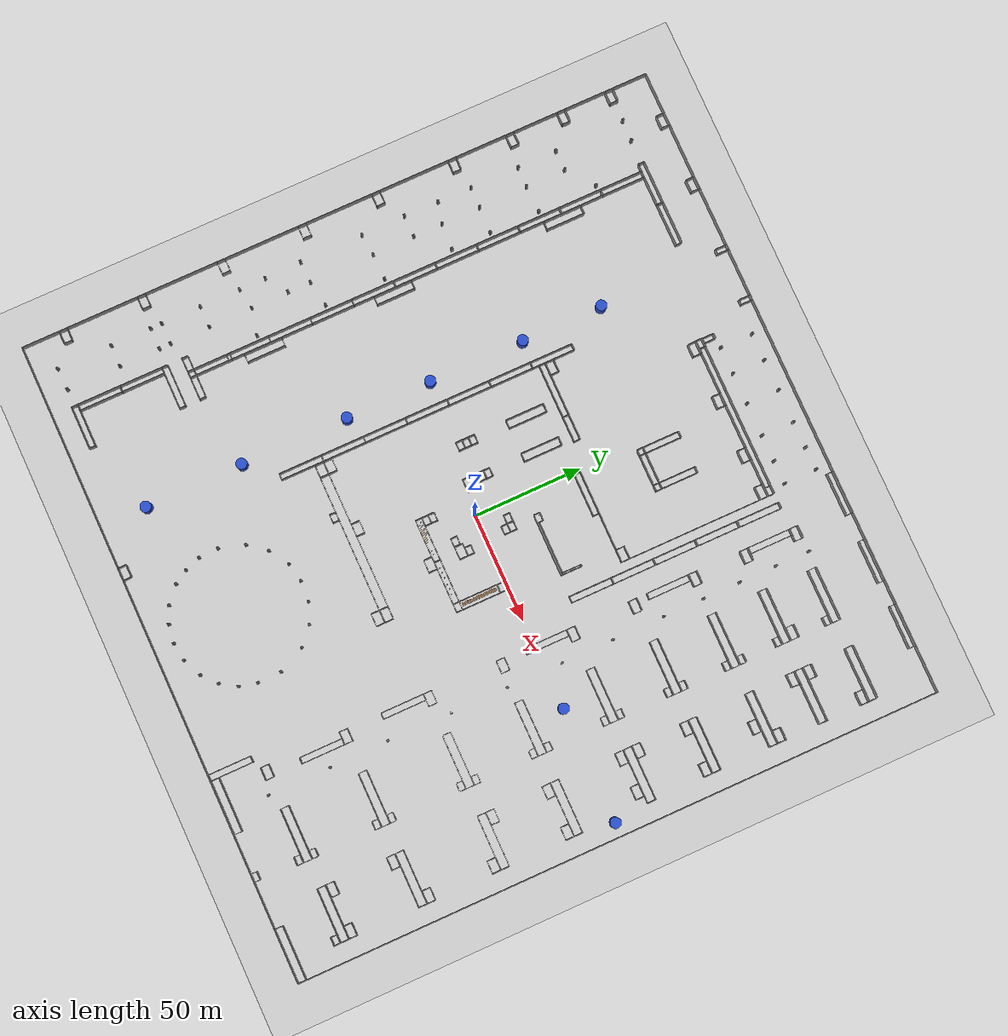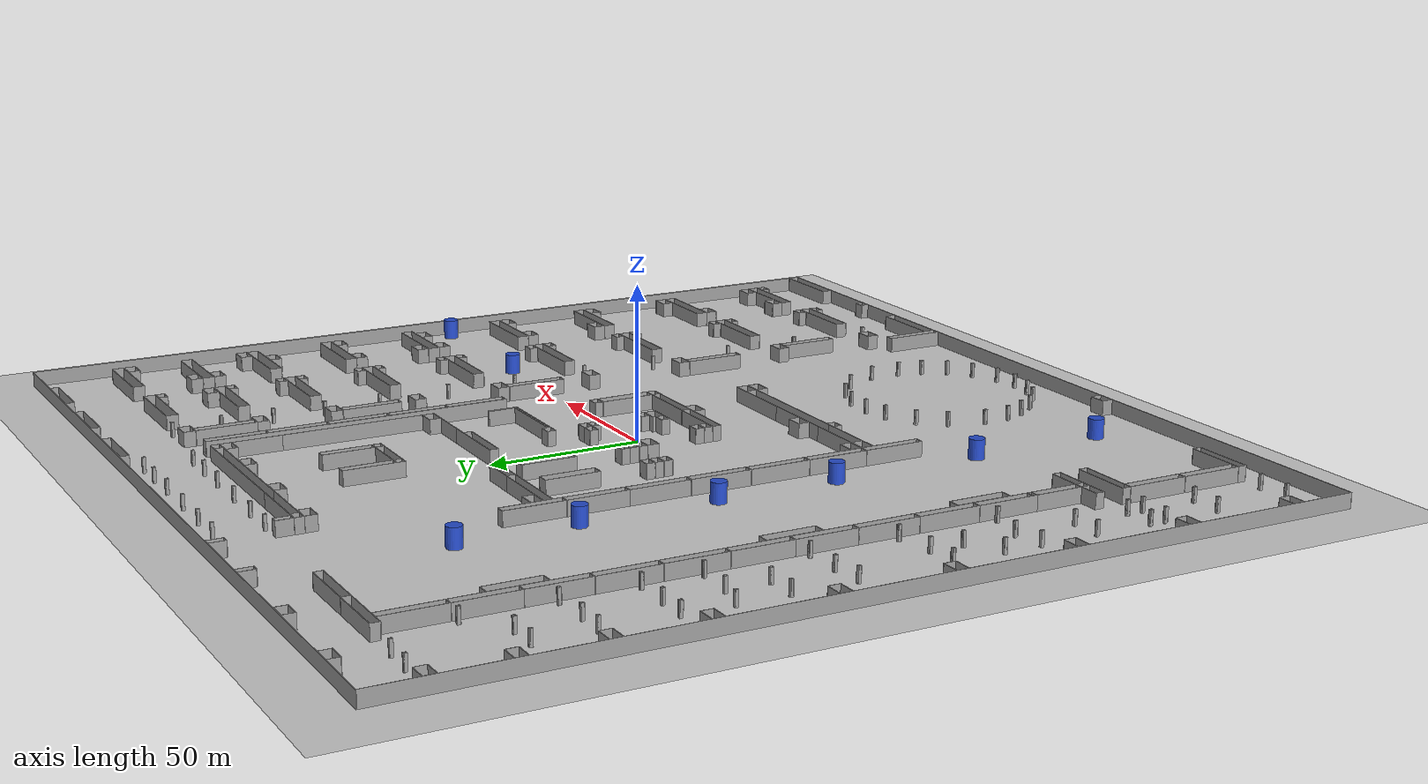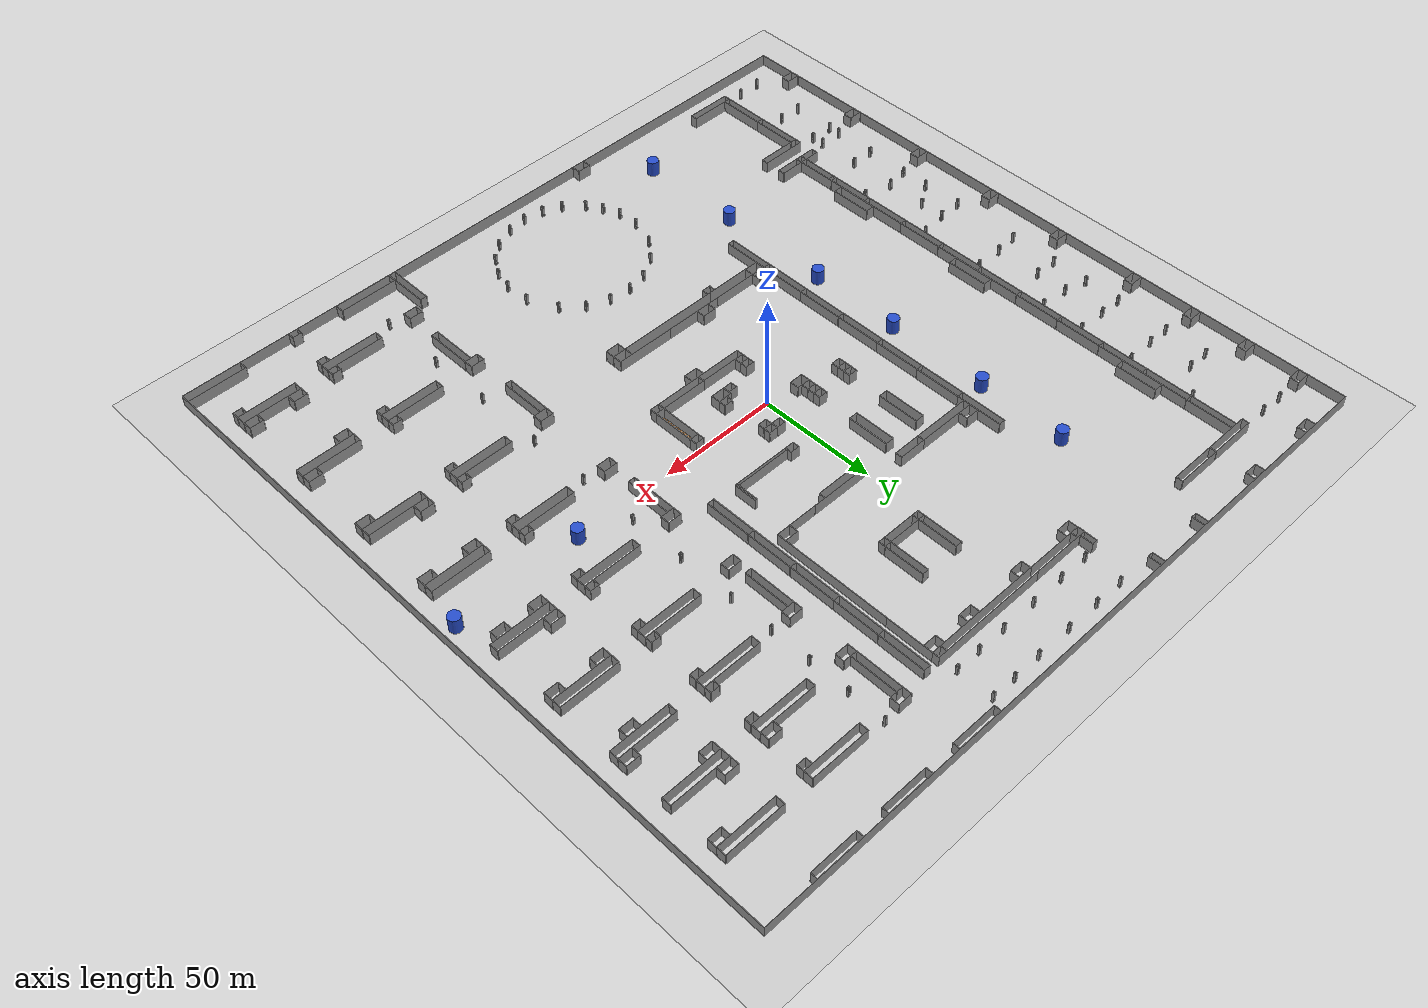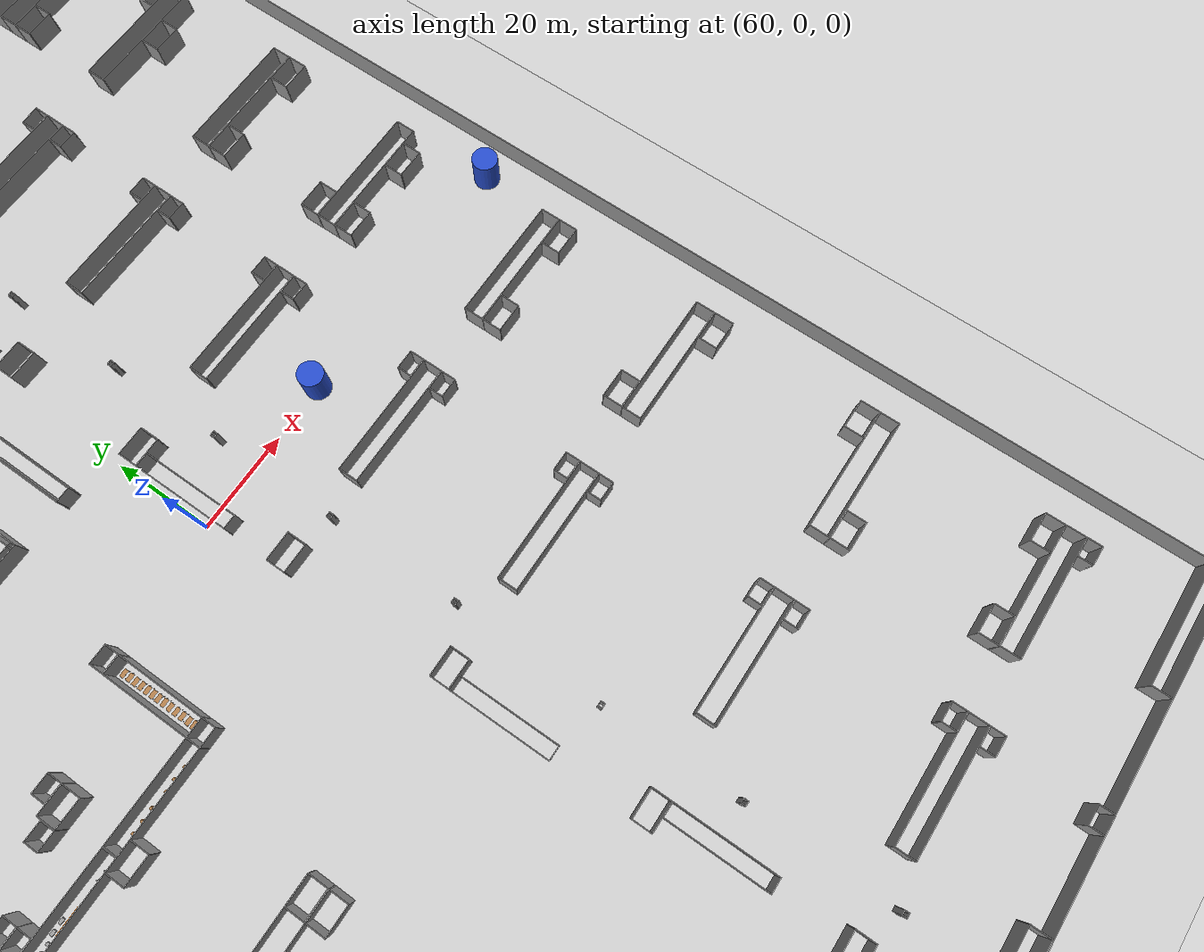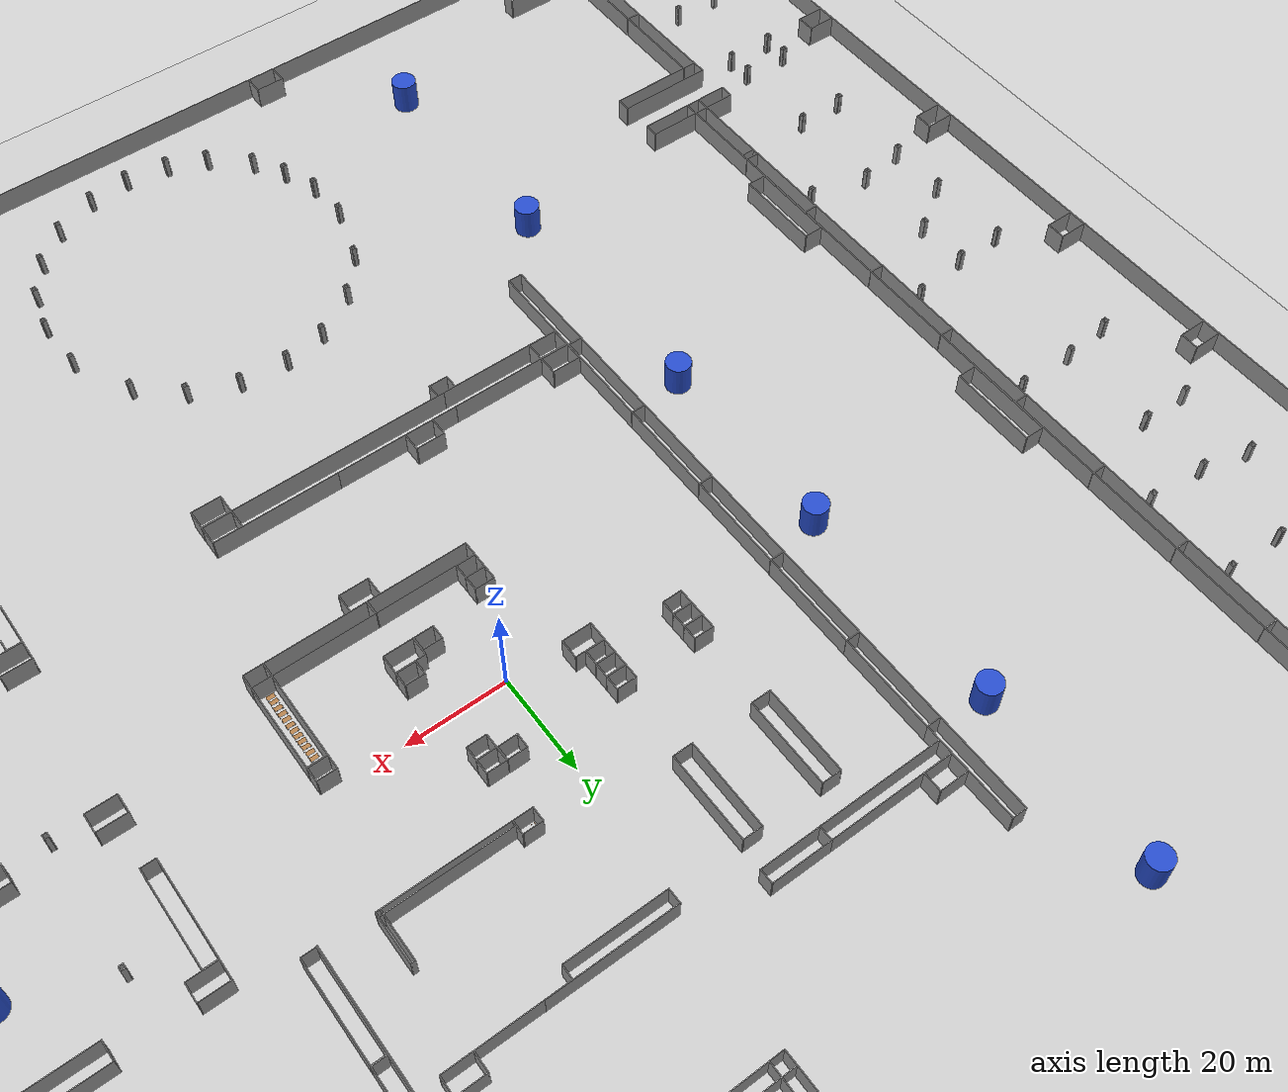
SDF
<sdf version="1.6">
 <world name="default">
  <light name="sun" type="directional">
   <pose>0 0 10 0 -0 0</pose>
   <diffuse>0.8 0.8 0.8 1</diffuse>
   <specular>0.2 0.2 0.2 1</specular>
   <attenuation>
    <range>1000</range>
    <constant>0.9</constant>
    <linear>0.01</linear>
    <quadratic>0.001</quadratic>
   </attenuation>
   <direction>-0.5 0.1 -0.9</direction>
  </light>
  <model name="ground_plane">
   <static>1</static>
   <link name="link">
    <collision name="collision">
     <geometry><plane><normal>0 0 1</normal><size>320 320</size></plane></geometry>
     <surface>
      <contact><collide_bitmask>65535</collide_bitmask></contact>
      <friction><ode><mu>100</mu><mu2>50</mu2></ode></friction>
     </surface>
    </collision>
    <visual name="visual">
     <cast_shadows>0</cast_shadows>
     <geometry><plane><normal>0 0 1</normal><size>320 320</size></plane></geometry>
     <material>
      <script><uri>file://media/materials/scripts/gazebo.material</uri><name>Gazebo/Grey</name></script>
     </material>
    </visual>
   </link>
  </model>
  <gravity>0 0 -9.8</gravity>
  <magnetic_field>6e-06 2.3e-05 -4.2e-05</magnetic_field>
  <atmosphere type="adiabatic"/>
  <physics name="default_physics" default="0" type="ode">
   <max_step_size>0.005</max_step_size>
   <real_time_factor>1</real_time_factor>
   <real_time_update_rate>200</real_time_update_rate>
  </physics>
  <scene><ambient>0.4 0.4 0.4 1</ambient><background>0.7 0.7 0.7 1</background><shadows>1</shadows></scene>
  <audio><device>default</device></audio>
  <spherical_coordinates>
   <surface_model>EARTH_WGS84</surface_model>
   <latitude_deg>0</latitude_deg>
   <longitude_deg>0</longitude_deg>
   <elevation>0</elevation>
   <heading_deg>0</heading_deg>
  </spherical_coordinates>
  <model name="wall_v20m_2">
   <pose>-48.4412 39.4727 0 0 -0 0</pose>
   <link name="Wall_35">
    <collision name="Wall_35_Collision">
     <geometry><box><size>20 0.15 6.555</size></box></geometry>
     <pose>0 0 1.25 0 -0 0</pose>
    </collision>
    <visual name="Wall_35_Visual">
     <pose>0 0 1.25 0 -0 0</pose>
     <geometry><box><size>20 0.15 6.555</size></box></geometry>
     <material>
      <script><uri>file://media/materials/scripts/gazebo.material</uri><name>Gazebo/Grey</name></script>
      <ambient>1 1 1 1</ambient>
     </material>
     <meta><layer>0</layer></meta>
    </visual>
    <pose>0 -0 0 0 -0 -1.5708</pose>
   </link>
   <static>1</static>
  </model>
  <model name="wall_25m_3">
   <pose>-35.9958 55.2578 0 0 -0 0</pose>
   <link name="Wall_28">
    <collision name="Wall_28_Collision">
     <geometry><box><size>25 0.15 6.555</size></box></geometry>
     <pose>0 0 1.25 0 -0 0</pose>
    </collision>
    <visual name="Wall_28_Visual">
     <pose>0 0 1.25 0 -0 0</pose>
     <geometry><box><size>25 0.15 6.555</size></box></geometry>
     <material>
      <script><uri>file://media/materials/scripts/gazebo.material</uri><name>Gazebo/Grey</name></script>
      <ambient>1 1 1 1</ambient>
     </material>
     <meta><layer>0</layer></meta>
    </visual>
   </link>
   <static>1</static>
  </model>
  <model name="wall_25m_4">
   <pose>-36.0189 52.3876 0 0 -0 0</pose>
   <link name="Wall_28">
    <collision name="Wall_28_Collision">
     <geometry><box><size>25 0.15 6.555</size></box></geometry>
     <pose>0 0 1.25 0 -0 0</pose>
    </collision>
    <visual name="Wall_28_Visual">
     <pose>0 0 1.25 0 -0 0</pose>
     <geometry><box><size>25 0.15 6.555</size></box></geometry>
     <material>
      <script><uri>file://media/materials/scripts/gazebo.material</uri><name>Gazebo/Grey</name></script>
      <ambient>1 1 1 1</ambient>
     </material>
     <meta><layer>0</layer></meta>
    </visual>
   </link>
   <static>1</static>
  </model>
  <model name="wall_25m_5">
   <pose>14.0033 49.3464 0 0 -0 0</pose>
   <link name="Wall_28">
    <collision name="Wall_28_Collision">
     <geometry><box><size>25 0.15 6.555</size></box></geometry>
     <pose>0 0 1.25 0 -0 0</pose>
    </collision>
    <visual name="Wall_28_Visual">
     <pose>0 0 1.25 0 -0 0</pose>
     <geometry><box><size>25 0.15 6.555</size></box></geometry>
     <material>
      <script><uri>file://media/materials/scripts/gazebo.material</uri><name>Gazebo/Grey</name></script>
      <ambient>1 1 1 1</ambient>
     </material>
     <meta><layer>0</layer></meta>
    </visual>
   </link>
   <static>1</static>
  </model>
  <model name="base18x4_3">
   <pose>-30.4275 38.1058 0 0 -0 0</pose>
   <link name="Wall_6">
    <collision name="Wall_6_Collision">
     <geometry><box><size>18 0.15 6.555</size></box></geometry>
     <pose>0 0 1.25 0 -0 0</pose>
    </collision>
    <visual name="Wall_6_Visual">
     <pose>0 0 1.25 0 -0 0</pose>
     <geometry><box><size>18 0.15 6.555</size></box></geometry>
     <material>
      <script><uri>file://media/materials/scripts/gazebo.material</uri><name>Gazebo/Grey</name></script>
      <ambient>1 1 1 1</ambient>
     </material>
     <meta><layer>0</layer></meta>
    </visual>
    <pose>-1.925 0 0 0 -0 -1.5708</pose>
   </link>
   <link name="Wall_7">
    <collision name="Wall_7_Collision">
     <geometry><box><size>4 0.15 6.555</size></box></geometry>
     <pose>0 0 1.25 0 -0 0</pose>
    </collision>
    <visual name="Wall_7_Visual">
     <pose>0 0 1.25 0 -0 0</pose>
     <geometry><box><size>4 0.15 6.555</size></box></geometry>
     <material>
      <script><uri>file://media/materials/scripts/gazebo.material</uri><name>Gazebo/Grey</name></script>
      <ambient>1 1 1 1</ambient>
     </material>
     <meta><layer>0</layer></meta>
    </visual>
    <pose>0 -8.925 0 0 -0 0</pose>
   </link>
   <link name="Wall_8">
    <collision name="Wall_8_Collision">
     <geometry><box><size>18 0.15 6.555</size></box></geometry>
     <pose>0 0 1.25 0 -0 0</pose>
    </collision>
    <visual name="Wall_8_Visual">
     <pose>0 0 1.25 0 -0 0</pose>
     <geometry><box><size>18 0.15 6.555</size></box></geometry>
     <material>
      <script><uri>file://media/materials/scripts/gazebo.material</uri><name>Gazebo/Grey</name></script>
      <ambient>1 1 1 1</ambient>
     </material>
     <meta><layer>0</layer></meta>
    </visual>
    <pose>1.925 0 0 0 -0 1.5708</pose>
   </link>
   <link name="Wall_9">
    <collision name="Wall_9_Collision">
     <geometry><box><size>4 0.15 6.555</size></box></geometry>
     <pose>0 0 1.25 0 -0 0</pose>
    </collision>
    <visual name="Wall_9_Visual">
     <pose>0 0 1.25 0 -0 0</pose>
     <geometry><box><size>4 0.15 6.555</size></box></geometry>
     <material>
      <script><uri>file://media/materials/scripts/gazebo.material</uri><name>Gazebo/Grey</name></script>
      <ambient>1 1 1 1</ambient>
     </material>
     <meta><layer>0</layer></meta>
    </visual>
    <pose>0 8.925 0 0 -0 3.14159</pose>
   </link>
   <static>1</static>
  </model>
  <model name="base3x20_2">
   <pose>1.5051 -23.232 0 0 -0 0</pose>
   <link name="Wall_16">
    <collision name="Wall_16_Collision">
     <geometry><box><size>3 0.15 6.555</size></box></geometry>
     <pose>0 0 1.25 0 -0 0</pose>
    </collision>
    <visual name="Wall_16_Visual">
     <pose>0 0 1.25 0 -0 0</pose>
     <geometry><box><size>3 0.15 6.555</size></box></geometry>
     <material>
      <script><uri>file://media/materials/scripts/gazebo.material</uri><name>Gazebo/Grey</name></script>
      <ambient>1 1 1 1</ambient>
     </material>
     <meta><layer>0</layer></meta>
    </visual>
    <pose>-9.925 -0 0 0 -0 -1.5708</pose>
   </link>
   <link name="Wall_17">
    <collision name="Wall_17_Collision">
     <geometry><box><size>20 0.15 6.555</size></box></geometry>
     <pose>0 0 1.25 0 -0 0</pose>
    </collision>
    <visual name="Wall_17_Visual">
     <pose>0 0 1.25 0 -0 0</pose>
     <geometry><box><size>20 0.15 6.555</size></box></geometry>
     <material>
      <script><uri>file://media/materials/scripts/gazebo.material</uri><name>Gazebo/Grey</name></script>
      <ambient>1 1 1 1</ambient>
     </material>
     <meta><layer>0</layer></meta>
    </visual>
    <pose>-0 -1.425 0 0 -0 0</pose>
   </link>
   <link name="Wall_18">
    <collision name="Wall_18_Collision">
     <geometry><box><size>3 0.15 6.555</size></box></geometry>
     <pose>0 0 1.25 0 -0 0</pose>
    </collision>
    <visual name="Wall_18_Visual">
     <pose>0 0 1.25 0 -0 0</pose>
     <geometry><box><size>3 0.15 6.555</size></box></geometry>
     <material>
      <script><uri>file://media/materials/scripts/gazebo.material</uri><name>Gazebo/Grey</name></script>
      <ambient>1 1 1 1</ambient>
     </material>
     <meta><layer>0</layer></meta>
    </visual>
    <pose>9.925 -0 0 0 -0 1.5708</pose>
   </link>
   <link name="Wall_19">
    <collision name="Wall_19_Collision">
     <geometry><box><size>20 0.15 6.555</size></box></geometry>
     <pose>0 0 1.25 0 -0 0</pose>
    </collision>
    <visual name="Wall_19_Visual">
     <pose>0 0 1.25 0 -0 0</pose>
     <geometry><box><size>20 0.15 6.555</size></box></geometry>
     <material>
      <script><uri>file://media/materials/scripts/gazebo.material</uri><name>Gazebo/Grey</name></script>
      <ambient>1 1 1 1</ambient>
     </material>
     <meta><layer>0</layer></meta>
    </visual>
    <pose>-0 1.425 0 0 -0 3.14159</pose>
   </link>
   <static>1</static>
  </model>
  <model name="base3x20_3">
   <pose>21.5045 -23.229 0 0 -0 0</pose>
   <link name="Wall_16">
    <collision name="Wall_16_Collision">
     <geometry><box><size>3 0.15 6.555</size></box></geometry>
     <pose>0 0 1.25 0 -0 0</pose>
    </collision>
    <visual name="Wall_16_Visual">
     <pose>0 0 1.25 0 -0 0</pose>
     <geometry><box><size>3 0.15 6.555</size></box></geometry>
     <material>
      <script><uri>file://media/materials/scripts/gazebo.material</uri><name>Gazebo/Grey</name></script>
      <ambient>1 1 1 1</ambient>
     </material>
     <meta><layer>0</layer></meta>
    </visual>
    <pose>-9.925 -0 0 0 -0 -1.5708</pose>
   </link>
   <link name="Wall_17">
    <collision name="Wall_17_Collision">
     <geometry><box><size>20 0.15 6.555</size></box></geometry>
     <pose>0 0 1.25 0 -0 0</pose>
    </collision>
    <visual name="Wall_17_Visual">
     <pose>0 0 1.25 0 -0 0</pose>
     <geometry><box><size>20 0.15 6.555</size></box></geometry>
     <material>
      <script><uri>file://media/materials/scripts/gazebo.material</uri><name>Gazebo/Grey</name></script>
      <ambient>1 1 1 1</ambient>
     </material>
     <meta><layer>0</layer></meta>
    </visual>
    <pose>-0 -1.425 0 0 -0 0</pose>
   </link>
   <link name="Wall_18">
    <collision name="Wall_18_Collision">
     <geometry><box><size>3 0.15 6.555</size></box></geometry>
     <pose>0 0 1.25 0 -0 0</pose>
    </collision>
    <visual name="Wall_18_Visual">
     <pose>0 0 1.25 0 -0 0</pose>
     <geometry><box><size>3 0.15 6.555</size></box></geometry>
     <material>
      <script><uri>file://media/materials/scripts/gazebo.material</uri><name>Gazebo/Grey</name></script>
      <ambient>1 1 1 1</ambient>
     </material>
     <meta><layer>0</layer></meta>
    </visual>
    <pose>9.925 -0 0 0 -0 1.5708</pose>
   </link>
   <link name="Wall_19">
    <collision name="Wall_19_Collision">
     <geometry><box><size>20 0.15 6.555</size></box></geometry>
     <pose>0 0 1.25 0 -0 0</pose>
    </collision>
    <visual name="Wall_19_Visual">
     <pose>0 0 1.25 0 -0 0</pose>
     <geometry><box><size>20 0.15 6.555</size></box></geometry>
     <material>
      <script><uri>file://media/materials/scripts/gazebo.material</uri><name>Gazebo/Grey</name></script>
      <ambient>1 1 1 1</ambient>
     </material>
     <meta><layer>0</layer></meta>
    </visual>
    <pose>-0 1.425 0 0 -0 3.14159</pose>
   </link>
   <static>1</static>
  </model>
  <model name="base3x4_25">
   <pose>33.3857 -23.2371 0 0 -0 0</pose>
   <link name="Wall_18">
    <collision name="Wall_18_Collision">
     <geometry><box><size>3 0.15 6.555</size></box></geometry>
     <pose>0 0 1.25 0 -0 0</pose>
    </collision>
    <visual name="Wall_18_Visual">
     <pose>0 0 1.25 0 -0 0</pose>
     <geometry><box><size>3 0.15 6.555</size></box></geometry>
     <material>
      <script><uri>file://media/materials/scripts/gazebo.material</uri><name>Gazebo/Grey</name></script>
      <ambient>1 1 1 1</ambient>
     </material>
     <meta><layer>0</layer></meta>
    </visual>
    <pose>-1.925 -0 0 0 -0 -1.5708</pose>
   </link>
   <link name="Wall_19">
    <collision name="Wall_19_Collision">
     <geometry><box><size>4 0.15 6.555</size></box></geometry>
     <pose>0 0 1.25 0 -0 0</pose>
    </collision>
    <visual name="Wall_19_Visual">
     <pose>0 0 1.25 0 -0 0</pose>
     <geometry><box><size>4 0.15 6.555</size></box></geometry>
     <material>
      <script><uri>file://media/materials/scripts/gazebo.material</uri><name>Gazebo/Grey</name></script>
      <ambient>1 1 1 1</ambient>
     </material>
     <meta><layer>0</layer></meta>
    </visual>
    <pose>-0 -1.425 0 0 -0 0</pose>
   </link>
   <link name="Wall_20">
    <collision name="Wall_20_Collision">
     <geometry><box><size>3 0.15 6.555</size></box></geometry>
     <pose>0 0 1.25 0 -0 0</pose>
    </collision>
    <visual name="Wall_20_Visual">
     <pose>0 0 1.25 0 -0 0</pose>
     <geometry><box><size>3 0.15 6.555</size></box></geometry>
     <material>
      <script><uri>file://media/materials/scripts/gazebo.material</uri><name>Gazebo/Grey</name></script>
      <ambient>1 1 1 1</ambient>
     </material>
     <meta><layer>0</layer></meta>
    </visual>
    <pose>1.925 -0 0 0 -0 1.5708</pose>
   </link>
   <link name="Wall_21">
    <collision name="Wall_21_Collision">
     <geometry><box><size>4 0.15 6.555</size></box></geometry>
     <pose>0 0 1.25 0 -0 0</pose>
    </collision>
    <visual name="Wall_21_Visual">
     <pose>0 0 1.25 0 -0 0</pose>
     <geometry><box><size>4 0.15 6.555</size></box></geometry>
     <material>
      <script><uri>file://media/materials/scripts/gazebo.material</uri><name>Gazebo/Grey</name></script>
      <ambient>1 1 1 1</ambient>
     </material>
     <meta><layer>0</layer></meta>
    </visual>
    <pose>-0 1.425 0 0 -0 3.14159</pose>
   </link>
   <static>1</static>
  </model>
  <model name="base3x12">
   <pose>-17.4947 53.8326 0 0 -0 0</pose>
   <link name="Wall_0">
    <collision name="Wall_0_Collision">
     <geometry><box><size>3 0.15 6.555</size></box></geometry>
     <pose>0 0 1.25 0 -0 0</pose>
    </collision>
    <visual name="Wall_0_Visual">
     <pose>0 0 1.25 0 -0 0</pose>
     <geometry><box><size>3 0.15 6.555</size></box></geometry>
     <material>
      <script><uri>file://media/materials/scripts/gazebo.material</uri><name>Gazebo/Grey</name></script>
      <ambient>1 1 1 1</ambient>
     </material>
     <meta><layer>0</layer></meta>
    </visual>
    <pose>-5.925 0 0 0 -0 -1.5708</pose>
   </link>
   <link name="Wall_1">
    <collision name="Wall_1_Collision">
     <geometry><box><size>12 0.15 6.555</size></box></geometry>
     <pose>0 0 1.25 0 -0 0</pose>
    </collision>
    <visual name="Wall_1_Visual">
     <pose>0 0 1.25 0 -0 0</pose>
     <geometry><box><size>12 0.15 6.555</size></box></geometry>
     <material>
      <script><uri>file://media/materials/scripts/gazebo.material</uri><name>Gazebo/Grey</name></script>
      <ambient>1 1 1 1</ambient>
     </material>
     <meta><layer>0</layer></meta>
    </visual>
    <pose>0 -1.425 0 0 -0 0</pose>
   </link>
   <link name="Wall_2">
    <collision name="Wall_2_Collision">
     <geometry><box><size>3 0.15 6.555</size></box></geometry>
     <pose>0 0 1.25 0 -0 0</pose>
    </collision>
    <visual name="Wall_2_Visual">
     <pose>0 0 1.25 0 -0 0</pose>
     <geometry><box><size>3 0.15 6.555</size></box></geometry>
     <material>
      <script><uri>file://media/materials/scripts/gazebo.material</uri><name>Gazebo/Grey</name></script>
      <ambient>1 1 1 1</ambient>
     </material>
     <meta><layer>0</layer></meta>
    </visual>
    <pose>5.925 0 0 0 -0 1.5708</pose>
   </link>
   <link name="Wall_3">
    <collision name="Wall_3_Collision">
     <geometry><box><size>12 0.15 6.555</size></box></geometry>
     <pose>0 0 1.25 0 -0 0</pose>
    </collision>
    <visual name="Wall_3_Visual">
     <pose>0 0 1.25 0 -0 0</pose>
     <geometry><box><size>12 0.15 6.555</size></box></geometry>
     <material>
      <script><uri>file://media/materials/scripts/gazebo.material</uri><name>Gazebo/Grey</name></script>
      <ambient>1 1 1 1</ambient>
     </material>
     <meta><layer>0</layer></meta>
    </visual>
    <pose>0 1.425 0 0 -0 3.14159</pose>
   </link>
   <static>1</static>
  </model>
  <model name="base18x4_5">
   <pose>33.3746 -12.8976 0 0 -0 0</pose>
   <link name="Wall_6">
    <collision name="Wall_6_Collision">
     <geometry><box><size>18 0.15 6.555</size></box></geometry>
     <pose>0 0 1.25 0 -0 0</pose>
    </collision>
    <visual name="Wall_6_Visual">
     <pose>0 0 1.25 0 -0 0</pose>
     <geometry><box><size>18 0.15 6.555</size></box></geometry>
     <material>
      <script><uri>file://media/materials/scripts/gazebo.material</uri><name>Gazebo/Grey</name></script>
      <ambient>1 1 1 1</ambient>
     </material>
     <meta><layer>0</layer></meta>
    </visual>
    <pose>-1.925 0 0 0 -0 -1.5708</pose>
   </link>
   <link name="Wall_7">
    <collision name="Wall_7_Collision">
     <geometry><box><size>4 0.15 6.555</size></box></geometry>
     <pose>0 0 1.25 0 -0 0</pose>
    </collision>
    <visual name="Wall_7_Visual">
     <pose>0 0 1.25 0 -0 0</pose>
     <geometry><box><size>4 0.15 6.555</size></box></geometry>
     <material>
      <script><uri>file://media/materials/scripts/gazebo.material</uri><name>Gazebo/Grey</name></script>
      <ambient>1 1 1 1</ambient>
     </material>
     <meta><layer>0</layer></meta>
    </visual>
    <pose>0 -8.925 0 0 -0 0</pose>
   </link>
   <link name="Wall_8">
    <collision name="Wall_8_Collision">
     <geometry><box><size>18 0.15 6.555</size></box></geometry>
     <pose>0 0 1.25 0 -0 0</pose>
    </collision>
    <visual name="Wall_8_Visual">
     <pose>0 0 1.25 0 -0 0</pose>
     <geometry><box><size>18 0.15 6.555</size></box></geometry>
     <material>
      <script><uri>file://media/materials/scripts/gazebo.material</uri><name>Gazebo/Grey</name></script>
      <ambient>1 1 1 1</ambient>
     </material>
     <meta><layer>0</layer></meta>
    </visual>
    <pose>1.925 0 0 0 -0 1.5708</pose>
   </link>
   <link name="Wall_9">
    <collision name="Wall_9_Collision">
     <geometry><box><size>4 0.15 6.555</size></box></geometry>
     <pose>0 0 1.25 0 -0 0</pose>
    </collision>
    <visual name="Wall_9_Visual">
     <pose>0 0 1.25 0 -0 0</pose>
     <geometry><box><size>4 0.15 6.555</size></box></geometry>
     <material>
      <script><uri>file://media/materials/scripts/gazebo.material</uri><name>Gazebo/Grey</name></script>
      <ambient>1 1 1 1</ambient>
     </material>
     <meta><layer>0</layer></meta>
    </visual>
    <pose>0 8.925 0 0 -0 3.14159</pose>
   </link>
   <static>1</static>
  </model>
  <model name="base10x1">
   <pose>38.8343 28.0126 0 0 -0 0</pose>
   <link name="Wall_15">
    <collision name="Wall_15_Collision">
     <geometry><box><size>10 0.15 6.555</size></box></geometry>
     <pose>0 0 1.25 0 -0 0</pose>
    </collision>
    <visual name="Wall_15_Visual">
     <pose>0 0 1.25 0 -0 0</pose>
     <geometry><box><size>10 0.15 6.555</size></box></geometry>
     <material>
      <script><uri>file://media/materials/scripts/gazebo.material</uri><name>Gazebo/Grey</name></script>
      <ambient>1 1 1 1</ambient>
     </material>
     <meta><layer>0</layer></meta>
    </visual>
    <pose>-0.425 0 0 0 -0 1.5708</pose>
   </link>
   <link name="Wall_16">
    <collision name="Wall_16_Collision">
     <geometry><box><size>1 0.15 6.555</size></box></geometry>
     <pose>0 0 1.25 0 -0 0</pose>
    </collision>
    <visual name="Wall_16_Visual">
     <pose>0 0 1.25 0 -0 0</pose>
     <geometry><box><size>1 0.15 6.555</size></box></geometry>
     <material>
      <script><uri>file://media/materials/scripts/gazebo.material</uri><name>Gazebo/Grey</name></script>
      <ambient>1 1 1 1</ambient>
     </material>
     <meta><layer>0</layer></meta>
    </visual>
    <pose>0 4.925 0 0 -0 0</pose>
   </link>
   <link name="Wall_17">
    <collision name="Wall_17_Collision">
     <geometry><box><size>10 0.15 6.555</size></box></geometry>
     <pose>0 0 1.25 0 -0 0</pose>
    </collision>
    <visual name="Wall_17_Visual">
     <pose>0 0 1.25 0 -0 0</pose>
     <geometry><box><size>10 0.15 6.555</size></box></geometry>
     <material>
      <script><uri>file://media/materials/scripts/gazebo.material</uri><name>Gazebo/Grey</name></script>
      <ambient>1 1 1 1</ambient>
     </material>
     <meta><layer>0</layer></meta>
    </visual>
    <pose>0.425 0 0 0 -0 -1.5708</pose>
   </link>
   <link name="Wall_18">
    <collision name="Wall_18_Collision">
     <geometry><box><size>1 0.15 6.555</size></box></geometry>
     <pose>0 0 1.25 0 -0 0</pose>
    </collision>
    <visual name="Wall_18_Visual">
     <pose>0 0 1.25 0 -0 0</pose>
     <geometry><box><size>1 0.15 6.555</size></box></geometry>
     <material>
      <script><uri>file://media/materials/scripts/gazebo.material</uri><name>Gazebo/Grey</name></script>
      <ambient>1 1 1 1</ambient>
     </material>
     <meta><layer>0</layer></meta>
    </visual>
    <pose>0 -4.925 0 0 -0 3.14159</pose>
   </link>
   <static>1</static>
  </model>
  <model name="base3x4_30">
   <pose>12.3458 24.5057 0 0 -0 0</pose>
   <link name="Wall_18">
    <collision name="Wall_18_Collision">
     <geometry><box><size>3 0.15 6.555</size></box></geometry>
     <pose>0 0 1.25 0 -0 0</pose>
    </collision>
    <visual name="Wall_18_Visual">
     <pose>0 0 1.25 0 -0 0</pose>
     <geometry><box><size>3 0.15 6.555</size></box></geometry>
     <material>
      <script><uri>file://media/materials/scripts/gazebo.material</uri><name>Gazebo/Grey</name></script>
      <ambient>1 1 1 1</ambient>
     </material>
     <meta><layer>0</layer></meta>
    </visual>
    <pose>-1.925 -0 0 0 -0 -1.5708</pose>
   </link>
   <link name="Wall_19">
    <collision name="Wall_19_Collision">
     <geometry><box><size>4 0.15 6.555</size></box></geometry>
     <pose>0 0 1.25 0 -0 0</pose>
    </collision>
    <visual name="Wall_19_Visual">
     <pose>0 0 1.25 0 -0 0</pose>
     <geometry><box><size>4 0.15 6.555</size></box></geometry>
     <material>
      <script><uri>file://media/materials/scripts/gazebo.material</uri><name>Gazebo/Grey</name></script>
      <ambient>1 1 1 1</ambient>
     </material>
     <meta><layer>0</layer></meta>
    </visual>
    <pose>-0 -1.425 0 0 -0 0</pose>
   </link>
   <link name="Wall_20">
    <collision name="Wall_20_Collision">
     <geometry><box><size>3 0.15 6.555</size></box></geometry>
     <pose>0 0 1.25 0 -0 0</pose>
    </collision>
    <visual name="Wall_20_Visual">
     <pose>0 0 1.25 0 -0 0</pose>
     <geometry><box><size>3 0.15 6.555</size></box></geometry>
     <material>
      <script><uri>file://media/materials/scripts/gazebo.material</uri><name>Gazebo/Grey</name></script>
      <ambient>1 1 1 1</ambient>
     </material>
     <meta><layer>0</layer></meta>
    </visual>
    <pose>1.925 -0 0 0 -0 1.5708</pose>
   </link>
   <link name="Wall_21">
    <collision name="Wall_21_Collision">
     <geometry><box><size>4 0.15 6.555</size></box></geometry>
     <pose>0 0 1.25 0 -0 0</pose>
    </collision>
    <visual name="Wall_21_Visual">
     <pose>0 0 1.25 0 -0 0</pose>
     <geometry><box><size>4 0.15 6.555</size></box></geometry>
     <material>
      <script><uri>file://media/materials/scripts/gazebo.material</uri><name>Gazebo/Grey</name></script>
      <ambient>1 1 1 1</ambient>
     </material>
     <meta><layer>0</layer></meta>
    </visual>
    <pose>-0 1.425 0 0 -0 3.14159</pose>
   </link>
   <static>1</static>
  </model>
  <model name="base3x4_13">
   <pose>-30.4247 6.69734 0 0 -0 0</pose>
   <link name="Wall_18">
    <collision name="Wall_18_Collision">
     <geometry><box><size>3 0.15 6.555</size></box></geometry>
     <pose>0 0 1.25 0 -0 0</pose>
    </collision>
    <visual name="Wall_18_Visual">
     <pose>0 0 1.25 0 -0 0</pose>
     <geometry><box><size>3 0.15 6.555</size></box></geometry>
     <material>
      <script><uri>file://media/materials/scripts/gazebo.material</uri><name>Gazebo/Grey</name></script>
      <ambient>1 1 1 1</ambient>
     </material>
     <meta><layer>0</layer></meta>
    </visual>
    <pose>-1.925 -0 0 0 -0 -1.5708</pose>
   </link>
   <link name="Wall_19">
    <collision name="Wall_19_Collision">
     <geometry><box><size>4 0.15 6.555</size></box></geometry>
     <pose>0 0 1.25 0 -0 0</pose>
    </collision>
    <visual name="Wall_19_Visual">
     <pose>0 0 1.25 0 -0 0</pose>
     <geometry><box><size>4 0.15 6.555</size></box></geometry>
     <material>
      <script><uri>file://media/materials/scripts/gazebo.material</uri><name>Gazebo/Grey</name></script>
      <ambient>1 1 1 1</ambient>
     </material>
     <meta><layer>0</layer></meta>
    </visual>
    <pose>-0 -1.425 0 0 -0 0</pose>
   </link>
   <link name="Wall_20">
    <collision name="Wall_20_Collision">
     <geometry><box><size>3 0.15 6.555</size></box></geometry>
     <pose>0 0 1.25 0 -0 0</pose>
    </collision>
    <visual name="Wall_20_Visual">
     <pose>0 0 1.25 0 -0 0</pose>
     <geometry><box><size>3 0.15 6.555</size></box></geometry>
     <material>
      <script><uri>file://media/materials/scripts/gazebo.material</uri><name>Gazebo/Grey</name></script>
      <ambient>1 1 1 1</ambient>
     </material>
     <meta><layer>0</layer></meta>
    </visual>
    <pose>1.925 -0 0 0 -0 1.5708</pose>
   </link>
   <link name="Wall_21">
    <collision name="Wall_21_Collision">
     <geometry><box><size>4 0.15 6.555</size></box></geometry>
     <pose>0 0 1.25 0 -0 0</pose>
    </collision>
    <visual name="Wall_21_Visual">
     <pose>0 0 1.25 0 -0 0</pose>
     <geometry><box><size>4 0.15 6.555</size></box></geometry>
     <material>
      <script><uri>file://media/materials/scripts/gazebo.material</uri><name>Gazebo/Grey</name></script>
      <ambient>1 1 1 1</ambient>
     </material>
     <meta><layer>0</layer></meta>
    </visual>
    <pose>-0 1.425 0 0 -0 3.14159</pose>
   </link>
   <static>1</static>
  </model>
  <model name="base3x4_81">
   <pose>-14.4195 6.71554 0 0 -0 0</pose>
   <link name="Wall_18">
    <collision name="Wall_18_Collision">
     <geometry><box><size>3 0.15 6.555</size></box></geometry>
     <pose>0 0 1.25 0 -0 0</pose>
    </collision>
    <visual name="Wall_18_Visual">
     <pose>0 0 1.25 0 -0 0</pose>
     <geometry><box><size>3 0.15 6.555</size></box></geometry>
     <material>
      <script><uri>file://media/materials/scripts/gazebo.material</uri><name>Gazebo/Grey</name></script>
      <ambient>1 1 1 1</ambient>
     </material>
     <meta><layer>0</layer></meta>
    </visual>
    <pose>-1.925 -0 0 0 -0 -1.5708</pose>
   </link>
   <link name="Wall_19">
    <collision name="Wall_19_Collision">
     <geometry><box><size>4 0.15 6.555</size></box></geometry>
     <pose>0 0 1.25 0 -0 0</pose>
    </collision>
    <visual name="Wall_19_Visual">
     <pose>0 0 1.25 0 -0 0</pose>
     <geometry><box><size>4 0.15 6.555</size></box></geometry>
     <material>
      <script><uri>file://media/materials/scripts/gazebo.material</uri><name>Gazebo/Grey</name></script>
      <ambient>1 1 1 1</ambient>
     </material>
     <meta><layer>0</layer></meta>
    </visual>
    <pose>-0 -1.425 0 0 -0 0</pose>
   </link>
   <link name="Wall_20">
    <collision name="Wall_20_Collision">
     <geometry><box><size>3 0.15 6.555</size></box></geometry>
     <pose>0 0 1.25 0 -0 0</pose>
    </collision>
    <visual name="Wall_20_Visual">
     <pose>0 0 1.25 0 -0 0</pose>
     <geometry><box><size>3 0.15 6.555</size></box></geometry>
     <material>
      <script><uri>file://media/materials/scripts/gazebo.material</uri><name>Gazebo/Grey</name></script>
      <ambient>1 1 1 1</ambient>
     </material>
     <meta><layer>0</layer></meta>
    </visual>
    <pose>1.925 -0 0 0 -0 1.5708</pose>
   </link>
   <link name="Wall_21">
    <collision name="Wall_21_Collision">
     <geometry><box><size>4 0.15 6.555</size></box></geometry>
     <pose>0 0 1.25 0 -0 0</pose>
    </collision>
    <visual name="Wall_21_Visual">
     <pose>0 0 1.25 0 -0 0</pose>
     <geometry><box><size>4 0.15 6.555</size></box></geometry>
     <material>
      <script><uri>file://media/materials/scripts/gazebo.material</uri><name>Gazebo/Grey</name></script>
      <ambient>1 1 1 1</ambient>
     </material>
     <meta><layer>0</layer></meta>
    </visual>
    <pose>-0 1.425 0 0 -0 3.14159</pose>
   </link>
   <static>1</static>
  </model>
  <model name="base3x4_66">
   <pose>-14.4193 9.67951 0 0 -0 0</pose>
   <link name="Wall_18">
    <collision name="Wall_18_Collision">
     <geometry><box><size>3 0.15 6.555</size></box></geometry>
     <pose>0 0 1.25 0 -0 0</pose>
    </collision>
    <visual name="Wall_18_Visual">
     <pose>0 0 1.25 0 -0 0</pose>
     <geometry><box><size>3 0.15 6.555</size></box></geometry>
     <material>
      <script><uri>file://media/materials/scripts/gazebo.material</uri><name>Gazebo/Grey</name></script>
      <ambient>1 1 1 1</ambient>
     </material>
     <meta><layer>0</layer></meta>
    </visual>
    <pose>-1.925 -0 0 0 -0 -1.5708</pose>
   </link>
   <link name="Wall_19">
    <collision name="Wall_19_Collision">
     <geometry><box><size>4 0.15 6.555</size></box></geometry>
     <pose>0 0 1.25 0 -0 0</pose>
    </collision>
    <visual name="Wall_19_Visual">
     <pose>0 0 1.25 0 -0 0</pose>
     <geometry><box><size>4 0.15 6.555</size></box></geometry>
     <material>
      <script><uri>file://media/materials/scripts/gazebo.material</uri><name>Gazebo/Grey</name></script>
      <ambient>1 1 1 1</ambient>
     </material>
     <meta><layer>0</layer></meta>
    </visual>
    <pose>-0 -1.425 0 0 -0 0</pose>
   </link>
   <link name="Wall_20">
    <collision name="Wall_20_Collision">
     <geometry><box><size>3 0.15 6.555</size></box></geometry>
     <pose>0 0 1.25 0 -0 0</pose>
    </collision>
    <visual name="Wall_20_Visual">
     <pose>0 0 1.25 0 -0 0</pose>
     <geometry><box><size>3 0.15 6.555</size></box></geometry>
     <material>
      <script><uri>file://media/materials/scripts/gazebo.material</uri><name>Gazebo/Grey</name></script>
      <ambient>1 1 1 1</ambient>
     </material>
     <meta><layer>0</layer></meta>
    </visual>
    <pose>1.925 -0 0 0 -0 1.5708</pose>
   </link>
   <link name="Wall_21">
    <collision name="Wall_21_Collision">
     <geometry><box><size>4 0.15 6.555</size></box></geometry>
     <pose>0 0 1.25 0 -0 0</pose>
    </collision>
    <visual name="Wall_21_Visual">
     <pose>0 0 1.25 0 -0 0</pose>
     <geometry><box><size>4 0.15 6.555</size></box></geometry>
     <material>
      <script><uri>file://media/materials/scripts/gazebo.material</uri><name>Gazebo/Grey</name></script>
      <ambient>1 1 1 1</ambient>
     </material>
     <meta><layer>0</layer></meta>
    </visual>
    <pose>-0 1.425 0 0 -0 3.14159</pose>
   </link>
   <static>1</static>
  </model>
  <model name="base3x4_74">
   <pose>33.377 -2.40049 0 0 -0 0</pose>
   <link name="Wall_18">
    <collision name="Wall_18_Collision">
     <geometry><box><size>3 0.15 6.555</size></box></geometry>
     <pose>0 0 1.25 0 -0 0</pose>
    </collision>
    <visual name="Wall_18_Visual">
     <pose>0 0 1.25 0 -0 0</pose>
     <geometry><box><size>3 0.15 6.555</size></box></geometry>
     <material>
      <script><uri>file://media/materials/scripts/gazebo.material</uri><name>Gazebo/Grey</name></script>
      <ambient>1 1 1 1</ambient>
     </material>
     <meta><layer>0</layer></meta>
    </visual>
    <pose>-1.925 -0 0 0 -0 -1.5708</pose>
   </link>
   <link name="Wall_19">
    <collision name="Wall_19_Collision">
     <geometry><box><size>4 0.15 6.555</size></box></geometry>
     <pose>0 0 1.25 0 -0 0</pose>
    </collision>
    <visual name="Wall_19_Visual">
     <pose>0 0 1.25 0 -0 0</pose>
     <geometry><box><size>4 0.15 6.555</size></box></geometry>
     <material>
      <script><uri>file://media/materials/scripts/gazebo.material</uri><name>Gazebo/Grey</name></script>
      <ambient>1 1 1 1</ambient>
     </material>
     <meta><layer>0</layer></meta>
    </visual>
    <pose>-0 -1.425 0 0 -0 0</pose>
   </link>
   <link name="Wall_20">
    <collision name="Wall_20_Collision">
     <geometry><box><size>3 0.15 6.555</size></box></geometry>
     <pose>0 0 1.25 0 -0 0</pose>
    </collision>
    <visual name="Wall_20_Visual">
     <pose>0 0 1.25 0 -0 0</pose>
     <geometry><box><size>3 0.15 6.555</size></box></geometry>
     <material>
      <script><uri>file://media/materials/scripts/gazebo.material</uri><name>Gazebo/Grey</name></script>
      <ambient>1 1 1 1</ambient>
     </material>
     <meta><layer>0</layer></meta>
    </visual>
    <pose>1.925 -0 0 0 -0 1.5708</pose>
   </link>
   <link name="Wall_21">
    <collision name="Wall_21_Collision">
     <geometry><box><size>4 0.15 6.555</size></box></geometry>
     <pose>0 0 1.25 0 -0 0</pose>
    </collision>
    <visual name="Wall_21_Visual">
     <pose>0 0 1.25 0 -0 0</pose>
     <geometry><box><size>4 0.15 6.555</size></box></geometry>
     <material>
      <script><uri>file://media/materials/scripts/gazebo.material</uri><name>Gazebo/Grey</name></script>
      <ambient>1 1 1 1</ambient>
     </material>
     <meta><layer>0</layer></meta>
    </visual>
    <pose>-0 1.425 0 0 -0 3.14159</pose>
   </link>
   <static>1</static>
  </model>
  <model name="wall_25m_0">
   <pose>26.8412 23.0792 0 0 -0 0</pose>
   <link name="Wall_28">
    <collision name="Wall_28_Collision">
     <geometry><box><size>25 0.15 6.555</size></box></geometry>
     <pose>0 0 1.25 0 -0 0</pose>
    </collision>
    <visual name="Wall_28_Visual">
     <pose>0 0 1.25 0 -0 0</pose>
     <geometry><box><size>25 0.15 6.555</size></box></geometry>
     <material>
      <script><uri>file://media/materials/scripts/gazebo.material</uri><name>Gazebo/Grey</name></script>
      <ambient>1 1 1 1</ambient>
     </material>
     <meta><layer>0</layer></meta>
    </visual>
   </link>
   <static>1</static>
  </model>
  <model name="base4x6_0">
   <pose>-45.3721 -48.6741 0 0 -0 0</pose>
   <link name="Wall_23">
    <collision name="Wall_23_Collision">
     <geometry><box><size>4 0.15 6.555</size></box></geometry>
     <pose>0 0 1.25 0 -0 0</pose>
    </collision>
    <visual name="Wall_23_Visual">
     <pose>0 0 1.25 0 -0 0</pose>
     <geometry><box><size>4 0.15 6.555</size></box></geometry>
     <material>
      <script><uri>file://media/materials/scripts/gazebo.material</uri><name>Gazebo/Grey</name></script>
      <ambient>1 1 1 1</ambient>
     </material>
     <meta><layer>0</layer></meta>
    </visual>
    <pose>-2.925 0 0 0 -0 -1.5708</pose>
   </link>
   <link name="Wall_24">
    <collision name="Wall_24_Collision">
     <geometry><box><size>6 0.15 6.555</size></box></geometry>
     <pose>0 0 1.25 0 -0 0</pose>
    </collision>
    <visual name="Wall_24_Visual">
     <pose>0 0 1.25 0 -0 0</pose>
     <geometry><box><size>6 0.15 6.555</size></box></geometry>
     <material>
      <script><uri>file://media/materials/scripts/gazebo.material</uri><name>Gazebo/Grey</name></script>
      <ambient>1 1 1 1</ambient>
     </material>
     <meta><layer>0</layer></meta>
    </visual>
    <pose>-0 -1.925 0 0 -0 0</pose>
   </link>
   <link name="Wall_25">
    <collision name="Wall_25_Collision">
     <geometry><box><size>4 0.15 6.555</size></box></geometry>
     <pose>0 0 1.25 0 -0 0</pose>
    </collision>
    <visual name="Wall_25_Visual">
     <pose>0 0 1.25 0 -0 0</pose>
     <geometry><box><size>4 0.15 6.555</size></box></geometry>
     <material>
      <script><uri>file://media/materials/scripts/gazebo.material</uri><name>Gazebo/Grey</name></script>
      <ambient>1 1 1 1</ambient>
     </material>
     <meta><layer>0</layer></meta>
    </visual>
    <pose>2.925 0 0 0 -0 1.5708</pose>
   </link>
   <link name="Wall_26">
    <collision name="Wall_26_Collision">
     <geometry><box><size>6 0.15 6.555</size></box></geometry>
     <pose>0 0 1.25 0 -0 0</pose>
    </collision>
    <visual name="Wall_26_Visual">
     <pose>0 0 1.25 0 -0 0</pose>
     <geometry><box><size>6 0.15 6.555</size></box></geometry>
     <material>
      <script><uri>file://media/materials/scripts/gazebo.material</uri><name>Gazebo/Grey</name></script>
      <ambient>1 1 1 1</ambient>
     </material>
     <meta><layer>0</layer></meta>
    </visual>
    <pose>-0 1.925 0 0 -0 3.14159</pose>
   </link>
   <static>1</static>
  </model>
  <model name="base3x4_37">
   <pose>-24.0394 -56.2074 0 0 -0 0</pose>
   <link name="Wall_18">
    <collision name="Wall_18_Collision">
     <geometry><box><size>3 0.15 6.555</size></box></geometry>
     <pose>0 0 1.25 0 -0 0</pose>
    </collision>
    <visual name="Wall_18_Visual">
     <pose>0 0 1.25 0 -0 0</pose>
     <geometry><box><size>3 0.15 6.555</size></box></geometry>
     <material>
      <script><uri>file://media/materials/scripts/gazebo.material</uri><name>Gazebo/Grey</name></script>
      <ambient>1 1 1 1</ambient>
     </material>
     <meta><layer>0</layer></meta>
    </visual>
    <pose>-1.925 -0 0 0 -0 -1.5708</pose>
   </link>
   <link name="Wall_19">
    <collision name="Wall_19_Collision">
     <geometry><box><size>4 0.15 6.555</size></box></geometry>
     <pose>0 0 1.25 0 -0 0</pose>
    </collision>
    <visual name="Wall_19_Visual">
     <pose>0 0 1.25 0 -0 0</pose>
     <geometry><box><size>4 0.15 6.555</size></box></geometry>
     <material>
      <script><uri>file://media/materials/scripts/gazebo.material</uri><name>Gazebo/Grey</name></script>
      <ambient>1 1 1 1</ambient>
     </material>
     <meta><layer>0</layer></meta>
    </visual>
    <pose>-0 -1.425 0 0 -0 0</pose>
   </link>
   <link name="Wall_20">
    <collision name="Wall_20_Collision">
     <geometry><box><size>3 0.15 6.555</size></box></geometry>
     <pose>0 0 1.25 0 -0 0</pose>
    </collision>
    <visual name="Wall_20_Visual">
     <pose>0 0 1.25 0 -0 0</pose>
     <geometry><box><size>3 0.15 6.555</size></box></geometry>
     <material>
      <script><uri>file://media/materials/scripts/gazebo.material</uri><name>Gazebo/Grey</name></script>
      <ambient>1 1 1 1</ambient>
     </material>
     <meta><layer>0</layer></meta>
    </visual>
    <pose>1.925 -0 0 0 -0 1.5708</pose>
   </link>
   <link name="Wall_21">
    <collision name="Wall_21_Collision">
     <geometry><box><size>4 0.15 6.555</size></box></geometry>
     <pose>0 0 1.25 0 -0 0</pose>
    </collision>
    <visual name="Wall_21_Visual">
     <pose>0 0 1.25 0 -0 0</pose>
     <geometry><box><size>4 0.15 6.555</size></box></geometry>
     <material>
      <script><uri>file://media/materials/scripts/gazebo.material</uri><name>Gazebo/Grey</name></script>
      <ambient>1 1 1 1</ambient>
     </material>
     <meta><layer>0</layer></meta>
    </visual>
    <pose>-0 1.425 0 0 -0 3.14159</pose>
   </link>
   <static>1</static>
  </model>
  <model name="wall_25m_1">
   <pose>-35.9206 -50.7228 0 0 -0 0</pose>
   <link name="Wall_28">
    <collision name="Wall_28_Collision">
     <geometry><box><size>25 0.15 6.555</size></box></geometry>
     <pose>0 0 1.25 0 -0 0</pose>
    </collision>
    <visual name="Wall_28_Visual">
     <pose>0 0 1.25 0 -0 0</pose>
     <geometry><box><size>25 0.15 6.555</size></box></geometry>
     <material>
      <script><uri>file://media/materials/scripts/gazebo.material</uri><name>Gazebo/Grey</name></script>
      <ambient>1 1 1 1</ambient>
     </material>
     <meta><layer>0</layer></meta>
    </visual>
   </link>
   <static>1</static>
  </model>
  <model name="wall_25m_7">
   <pose>-10.9546 -50.7217 0 0 -0 0</pose>
   <link name="Wall_28">
    <collision name="Wall_28_Collision">
     <geometry><box><size>25 0.15 6.555</size></box></geometry>
     <pose>0 0 1.25 0 -0 0</pose>
    </collision>
    <visual name="Wall_28_Visual">
     <pose>0 0 1.25 0 -0 0</pose>
     <geometry><box><size>25 0.15 6.555</size></box></geometry>
     <material>
      <script><uri>file://media/materials/scripts/gazebo.material</uri><name>Gazebo/Grey</name></script>
      <ambient>1 1 1 1</ambient>
     </material>
     <meta><layer>0</layer></meta>
    </visual>
   </link>
   <static>1</static>
  </model>
  <model name="wall_25m_8">
   <pose>14.0268 -50.7126 0 0 -0 0</pose>
   <link name="Wall_28">
    <collision name="Wall_28_Collision">
     <geometry><box><size>25 0.15 6.555</size></box></geometry>
     <pose>0 0 1.25 0 -0 0</pose>
    </collision>
    <visual name="Wall_28_Visual">
     <pose>0 0 1.25 0 -0 0</pose>
     <geometry><box><size>25 0.15 6.555</size></box></geometry>
     <material>
      <script><uri>file://media/materials/scripts/gazebo.material</uri><name>Gazebo/Grey</name></script>
      <ambient>1 1 1 1</ambient>
     </material>
     <meta><layer>0</layer></meta>
    </visual>
   </link>
   <static>1</static>
  </model>
  <model name="wall_25m_2">
   <pose>26.7296 24.0129 0 0 -0 0</pose>
   <link name="Wall_28">
    <collision name="Wall_28_Collision">
     <geometry><box><size>25 0.15 6.555</size></box></geometry>
     <pose>0 0 1.25 0 -0 0</pose>
    </collision>
    <visual name="Wall_28_Visual">
     <pose>0 0 1.25 0 -0 0</pose>
     <geometry><box><size>25 0.15 6.555</size></box></geometry>
     <material>
      <script><uri>file://media/materials/scripts/gazebo.material</uri><name>Gazebo/Grey</name></script>
      <ambient>1 1 1 1</ambient>
     </material>
     <meta><layer>0</layer></meta>
    </visual>
   </link>
   <static>1</static>
  </model>
  <model name="table">
   <static>1</static>
   <link name="link">
    <collision name="surface">
     <pose>0 0 1 0 -0 0</pose>
     <geometry><box><size>1.5 0.8 0.03</size></box></geometry>
     <surface><friction><ode><mu>0.6</mu><mu2>0.6</mu2></ode></friction></surface>
    </collision>
    <visual name="visual1">
     <pose>0 0 1 0 -0 0</pose>
     <geometry><box><size>1.5 0.8 0.03</size></box></geometry>
     <material>
      <script><uri>file://media/materials/scripts/gazebo.material</uri><name>Gazebo/Wood</name></script>
     </material>
    </visual>
    <collision name="front_left_leg">
     <pose>0.68 0.38 0.5 0 -0 0</pose>
     <geometry><cylinder><radius>0.02</radius><length>1</length></cylinder></geometry>
    </collision>
    <visual name="front_left_leg">
     <pose>0.68 0.38 0.5 0 -0 0</pose>
     <geometry><cylinder><radius>0.02</radius><length>1</length></cylinder></geometry>
     <material>
      <script><uri>file://media/materials/scripts/gazebo.material</uri><name>Gazebo/Grey</name></script>
     </material>
    </visual>
    <collision name="front_right_leg">
     <pose>0.68 -0.38 0.5 0 -0 0</pose>
     <geometry><cylinder><radius>0.02</radius><length>1</length></cylinder></geometry>
    </collision>
    <visual name="front_right_leg">
     <pose>0.68 -0.38 0.5 0 -0 0</pose>
     <geometry><cylinder><radius>0.02</radius><length>1</length></cylinder></geometry>
     <material>
      <script><uri>file://media/materials/scripts/gazebo.material</uri><name>Gazebo/Grey</name></script>
     </material>
    </visual>
    <collision name="back_right_leg">
     <pose>-0.68 -0.38 0.5 0 -0 0</pose>
     <geometry><cylinder><radius>0.02</radius><length>1</length></cylinder></geometry>
    </collision>
    <visual name="back_right_leg">
     <pose>-0.68 -0.38 0.5 0 -0 0</pose>
     <geometry><cylinder><radius>0.02</radius><length>1</length></cylinder></geometry>
     <material>
      <script><uri>file://media/materials/scripts/gazebo.material</uri><name>Gazebo/Grey</name></script>
     </material>
    </visual>
    <collision name="back_left_leg">
     <pose>-0.68 0.38 0.5 0 -0 0</pose>
     <geometry><cylinder><radius>0.02</radius><length>1</length></cylinder></geometry>
    </collision>
    <visual name="back_left_leg">
     <pose>-0.68 0.38 0.5 0 -0 0</pose>
     <geometry><cylinder><radius>0.02</radius><length>1</length></cylinder></geometry>
     <material>
      <script><uri>file://media/materials/scripts/gazebo.material</uri><name>Gazebo/Grey</name></script>
     </material>
    </visual>
   </link>
   <pose>33.0718 -20.4788 0 0 -0 0</pose>
  </model>
  <model name="table_0">
   <static>1</static>
   <link name="link">
    <collision name="surface">
     <pose>0 0 1 0 -0 0</pose>
     <geometry><box><size>1.5 0.8 0.03</size></box></geometry>
     <surface><friction><ode><mu>0.6</mu><mu2>0.6</mu2></ode></friction></surface>
    </collision>
    <visual name="visual1">
     <pose>0 0 1 0 -0 0</pose>
     <geometry><box><size>1.5 0.8 0.03</size></box></geometry>
     <material>
      <script><uri>file://media/materials/scripts/gazebo.material</uri><name>Gazebo/Wood</name></script>
     </material>
    </visual>
    <collision name="front_left_leg">
     <pose>0.68 0.38 0.5 0 -0 0</pose>
     <geometry><cylinder><radius>0.02</radius><length>1</length></cylinder></geometry>
    </collision>
    <visual name="front_left_leg">
     <pose>0.68 0.38 0.5 0 -0 0</pose>
     <geometry><cylinder><radius>0.02</radius><length>1</length></cylinder></geometry>
     <material>
      <script><uri>file://media/materials/scripts/gazebo.material</uri><name>Gazebo/Grey</name></script>
     </material>
    </visual>
    <collision name="front_right_leg">
     <pose>0.68 -0.38 0.5 0 -0 0</pose>
     <geometry><cylinder><radius>0.02</radius><length>1</length></cylinder></geometry>
    </collision>
    <visual name="front_right_leg">
     <pose>0.68 -0.38 0.5 0 -0 0</pose>
     <geometry><cylinder><radius>0.02</radius><length>1</length></cylinder></geometry>
     <material>
      <script><uri>file://media/materials/scripts/gazebo.material</uri><name>Gazebo/Grey</name></script>
     </material>
    </visual>
    <collision name="back_right_leg">
     <pose>-0.68 -0.38 0.5 0 -0 0</pose>
     <geometry><cylinder><radius>0.02</radius><length>1</length></cylinder></geometry>
    </collision>
    <visual name="back_right_leg">
     <pose>-0.68 -0.38 0.5 0 -0 0</pose>
     <geometry><cylinder><radius>0.02</radius><length>1</length></cylinder></geometry>
     <material>
      <script><uri>file://media/materials/scripts/gazebo.material</uri><name>Gazebo/Grey</name></script>
     </material>
    </visual>
    <collision name="back_left_leg">
     <pose>-0.68 0.38 0.5 0 -0 0</pose>
     <geometry><cylinder><radius>0.02</radius><length>1</length></cylinder></geometry>
    </collision>
    <visual name="back_left_leg">
     <pose>-0.68 0.38 0.5 0 -0 0</pose>
     <geometry><cylinder><radius>0.02</radius><length>1</length></cylinder></geometry>
     <material>
      <script><uri>file://media/materials/scripts/gazebo.material</uri><name>Gazebo/Grey</name></script>
     </material>
    </visual>
   </link>
   <pose>33.0586 -19.3271 0 0 -0 0</pose>
  </model>
  <model name="table_1">
   <static>1</static>
   <link name="link">
    <collision name="surface">
     <pose>0 0 1 0 -0 0</pose>
     <geometry><box><size>1.5 0.8 0.03</size></box></geometry>
     <surface><friction><ode><mu>0.6</mu><mu2>0.6</mu2></ode></friction></surface>
    </collision>
    <visual name="visual1">
     <pose>0 0 1 0 -0 0</pose>
     <geometry><box><size>1.5 0.8 0.03</size></box></geometry>
     <material>
      <script><uri>file://media/materials/scripts/gazebo.material</uri><name>Gazebo/Wood</name></script>
     </material>
    </visual>
    <collision name="front_left_leg">
     <pose>0.68 0.38 0.5 0 -0 0</pose>
     <geometry><cylinder><radius>0.02</radius><length>1</length></cylinder></geometry>
    </collision>
    <visual name="front_left_leg">
     <pose>0.68 0.38 0.5 0 -0 0</pose>
     <geometry><cylinder><radius>0.02</radius><length>1</length></cylinder></geometry>
     <material>
      <script><uri>file://media/materials/scripts/gazebo.material</uri><name>Gazebo/Grey</name></script>
     </material>
    </visual>
    <collision name="front_right_leg">
     <pose>0.68 -0.38 0.5 0 -0 0</pose>
     <geometry><cylinder><radius>0.02</radius><length>1</length></cylinder></geometry>
    </collision>
    <visual name="front_right_leg">
     <pose>0.68 -0.38 0.5 0 -0 0</pose>
     <geometry><cylinder><radius>0.02</radius><length>1</length></cylinder></geometry>
     <material>
      <script><uri>file://media/materials/scripts/gazebo.material</uri><name>Gazebo/Grey</name></script>
     </material>
    </visual>
    <collision name="back_right_leg">
     <pose>-0.68 -0.38 0.5 0 -0 0</pose>
     <geometry><cylinder><radius>0.02</radius><length>1</length></cylinder></geometry>
    </collision>
    <visual name="back_right_leg">
     <pose>-0.68 -0.38 0.5 0 -0 0</pose>
     <geometry><cylinder><radius>0.02</radius><length>1</length></cylinder></geometry>
     <material>
      <script><uri>file://media/materials/scripts/gazebo.material</uri><name>Gazebo/Grey</name></script>
     </material>
    </visual>
    <collision name="back_left_leg">
     <pose>-0.68 0.38 0.5 0 -0 0</pose>
     <geometry><cylinder><radius>0.02</radius><length>1</length></cylinder></geometry>
    </collision>
    <visual name="back_left_leg">
     <pose>-0.68 0.38 0.5 0 -0 0</pose>
     <geometry><cylinder><radius>0.02</radius><length>1</length></cylinder></geometry>
     <material>
      <script><uri>file://media/materials/scripts/gazebo.material</uri><name>Gazebo/Grey</name></script>
     </material>
    </visual>
   </link>
   <pose>33.0783 -17.9476 0 0 -0 0</pose>
  </model>
  <model name="table_2">
   <static>1</static>
   <link name="link">
    <collision name="surface">
     <pose>0 0 1 0 -0 0</pose>
     <geometry><box><size>1.5 0.8 0.03</size></box></geometry>
     <surface><friction><ode><mu>0.6</mu><mu2>0.6</mu2></ode></friction></surface>
    </collision>
    <visual name="visual1">
     <pose>0 0 1 0 -0 0</pose>
     <geometry><box><size>1.5 0.8 0.03</size></box></geometry>
     <material>
      <script><uri>file://media/materials/scripts/gazebo.material</uri><name>Gazebo/Wood</name></script>
     </material>
    </visual>
    <collision name="front_left_leg">
     <pose>0.68 0.38 0.5 0 -0 0</pose>
     <geometry><cylinder><radius>0.02</radius><length>1</length></cylinder></geometry>
    </collision>
    <visual name="front_left_leg">
     <pose>0.68 0.38 0.5 0 -0 0</pose>
     <geometry><cylinder><radius>0.02</radius><length>1</length></cylinder></geometry>
     <material>
      <script><uri>file://media/materials/scripts/gazebo.material</uri><name>Gazebo/Grey</name></script>
     </material>
    </visual>
    <collision name="front_right_leg">
     <pose>0.68 -0.38 0.5 0 -0 0</pose>
     <geometry><cylinder><radius>0.02</radius><length>1</length></cylinder></geometry>
    </collision>
    <visual name="front_right_leg">
     <pose>0.68 -0.38 0.5 0 -0 0</pose>
     <geometry><cylinder><radius>0.02</radius><length>1</length></cylinder></geometry>
     <material>
      <script><uri>file://media/materials/scripts/gazebo.material</uri><name>Gazebo/Grey</name></script>
     </material>
    </visual>
    <collision name="back_right_leg">
     <pose>-0.68 -0.38 0.5 0 -0 0</pose>
     <geometry><cylinder><radius>0.02</radius><length>1</length></cylinder></geometry>
    </collision>
    <visual name="back_right_leg">
     <pose>-0.68 -0.38 0.5 0 -0 0</pose>
     <geometry><cylinder><radius>0.02</radius><length>1</length></cylinder></geometry>
     <material>
      <script><uri>file://media/materials/scripts/gazebo.material</uri><name>Gazebo/Grey</name></script>
     </material>
    </visual>
    <collision name="back_left_leg">
     <pose>-0.68 0.38 0.5 0 -0 0</pose>
     <geometry><cylinder><radius>0.02</radius><length>1</length></cylinder></geometry>
    </collision>
    <visual name="back_left_leg">
     <pose>-0.68 0.38 0.5 0 -0 0</pose>
     <geometry><cylinder><radius>0.02</radius><length>1</length></cylinder></geometry>
     <material>
      <script><uri>file://media/materials/scripts/gazebo.material</uri><name>Gazebo/Grey</name></script>
     </material>
    </visual>
   </link>
   <pose>33.0811 -16.621 0 0 -0 0</pose>
  </model>
  <model name="table_3">
   <static>1</static>
   <link name="link">
    <collision name="surface">
     <pose>0 0 1 0 -0 0</pose>
     <geometry><box><size>1.5 0.8 0.03</size></box></geometry>
     <surface><friction><ode><mu>0.6</mu><mu2>0.6</mu2></ode></friction></surface>
    </collision>
    <visual name="visual1">
     <pose>0 0 1 0 -0 0</pose>
     <geometry><box><size>1.5 0.8 0.03</size></box></geometry>
     <material>
      <script><uri>file://media/materials/scripts/gazebo.material</uri><name>Gazebo/Wood</name></script>
     </material>
    </visual>
    <collision name="front_left_leg">
     <pose>0.68 0.38 0.5 0 -0 0</pose>
     <geometry><cylinder><radius>0.02</radius><length>1</length></cylinder></geometry>
    </collision>
    <visual name="front_left_leg">
     <pose>0.68 0.38 0.5 0 -0 0</pose>
     <geometry><cylinder><radius>0.02</radius><length>1</length></cylinder></geometry>
     <material>
      <script><uri>file://media/materials/scripts/gazebo.material</uri><name>Gazebo/Grey</name></script>
     </material>
    </visual>
    <collision name="front_right_leg">
     <pose>0.68 -0.38 0.5 0 -0 0</pose>
     <geometry><cylinder><radius>0.02</radius><length>1</length></cylinder></geometry>
    </collision>
    <visual name="front_right_leg">
     <pose>0.68 -0.38 0.5 0 -0 0</pose>
     <geometry><cylinder><radius>0.02</radius><length>1</length></cylinder></geometry>
     <material>
      <script><uri>file://media/materials/scripts/gazebo.material</uri><name>Gazebo/Grey</name></script>
     </material>
    </visual>
    <collision name="back_right_leg">
     <pose>-0.68 -0.38 0.5 0 -0 0</pose>
     <geometry><cylinder><radius>0.02</radius><length>1</length></cylinder></geometry>
    </collision>
    <visual name="back_right_leg">
     <pose>-0.68 -0.38 0.5 0 -0 0</pose>
     <geometry><cylinder><radius>0.02</radius><length>1</length></cylinder></geometry>
     <material>
      <script><uri>file://media/materials/scripts/gazebo.material</uri><name>Gazebo/Grey</name></script>
     </material>
    </visual>
    <collision name="back_left_leg">
     <pose>-0.68 0.38 0.5 0 -0 0</pose>
     <geometry><cylinder><radius>0.02</radius><length>1</length></cylinder></geometry>
    </collision>
    <visual name="back_left_leg">
     <pose>-0.68 0.38 0.5 0 -0 0</pose>
     <geometry><cylinder><radius>0.02</radius><length>1</length></cylinder></geometry>
     <material>
      <script><uri>file://media/materials/scripts/gazebo.material</uri><name>Gazebo/Grey</name></script>
     </material>
    </visual>
   </link>
   <pose>33.0661 -15.3115 0 0 -0 0</pose>
  </model>
  <model name="table_4">
   <static>1</static>
   <link name="link">
    <collision name="surface">
     <pose>0 0 1 0 -0 0</pose>
     <geometry><box><size>1.5 0.8 0.03</size></box></geometry>
     <surface><friction><ode><mu>0.6</mu><mu2>0.6</mu2></ode></friction></surface>
    </collision>
    <visual name="visual1">
     <pose>0 0 1 0 -0 0</pose>
     <geometry><box><size>1.5 0.8 0.03</size></box></geometry>
     <material>
      <script><uri>file://media/materials/scripts/gazebo.material</uri><name>Gazebo/Wood</name></script>
     </material>
    </visual>
    <collision name="front_left_leg">
     <pose>0.68 0.38 0.5 0 -0 0</pose>
     <geometry><cylinder><radius>0.02</radius><length>1</length></cylinder></geometry>
    </collision>
    <visual name="front_left_leg">
     <pose>0.68 0.38 0.5 0 -0 0</pose>
     <geometry><cylinder><radius>0.02</radius><length>1</length></cylinder></geometry>
     <material>
      <script><uri>file://media/materials/scripts/gazebo.material</uri><name>Gazebo/Grey</name></script>
     </material>
    </visual>
    <collision name="front_right_leg">
     <pose>0.68 -0.38 0.5 0 -0 0</pose>
     <geometry><cylinder><radius>0.02</radius><length>1</length></cylinder></geometry>
    </collision>
    <visual name="front_right_leg">
     <pose>0.68 -0.38 0.5 0 -0 0</pose>
     <geometry><cylinder><radius>0.02</radius><length>1</length></cylinder></geometry>
     <material>
      <script><uri>file://media/materials/scripts/gazebo.material</uri><name>Gazebo/Grey</name></script>
     </material>
    </visual>
    <collision name="back_right_leg">
     <pose>-0.68 -0.38 0.5 0 -0 0</pose>
     <geometry><cylinder><radius>0.02</radius><length>1</length></cylinder></geometry>
    </collision>
    <visual name="back_right_leg">
     <pose>-0.68 -0.38 0.5 0 -0 0</pose>
     <geometry><cylinder><radius>0.02</radius><length>1</length></cylinder></geometry>
     <material>
      <script><uri>file://media/materials/scripts/gazebo.material</uri><name>Gazebo/Grey</name></script>
     </material>
    </visual>
    <collision name="back_left_leg">
     <pose>-0.68 0.38 0.5 0 -0 0</pose>
     <geometry><cylinder><radius>0.02</radius><length>1</length></cylinder></geometry>
    </collision>
    <visual name="back_left_leg">
     <pose>-0.68 0.38 0.5 0 -0 0</pose>
     <geometry><cylinder><radius>0.02</radius><length>1</length></cylinder></geometry>
     <material>
      <script><uri>file://media/materials/scripts/gazebo.material</uri><name>Gazebo/Grey</name></script>
     </material>
    </visual>
   </link>
   <pose>33.068 -14.0197 0 0 -0 0</pose>
  </model>
  <model name="table_5">
   <static>1</static>
   <link name="link">
    <collision name="surface">
     <pose>0 0 1 0 -0 0</pose>
     <geometry><box><size>1.5 0.8 0.03</size></box></geometry>
     <surface><friction><ode><mu>0.6</mu><mu2>0.6</mu2></ode></friction></surface>
    </collision>
    <visual name="visual1">
     <pose>0 0 1 0 -0 0</pose>
     <geometry><box><size>1.5 0.8 0.03</size></box></geometry>
     <material>
      <script><uri>file://media/materials/scripts/gazebo.material</uri><name>Gazebo/Wood</name></script>
     </material>
    </visual>
    <collision name="front_left_leg">
     <pose>0.68 0.38 0.5 0 -0 0</pose>
     <geometry><cylinder><radius>0.02</radius><length>1</length></cylinder></geometry>
    </collision>
    <visual name="front_left_leg">
     <pose>0.68 0.38 0.5 0 -0 0</pose>
     <geometry><cylinder><radius>0.02</radius><length>1</length></cylinder></geometry>
     <material>
      <script><uri>file://media/materials/scripts/gazebo.material</uri><name>Gazebo/Grey</name></script>
     </material>
    </visual>
    <collision name="front_right_leg">
     <pose>0.68 -0.38 0.5 0 -0 0</pose>
     <geometry><cylinder><radius>0.02</radius><length>1</length></cylinder></geometry>
    </collision>
    <visual name="front_right_leg">
     <pose>0.68 -0.38 0.5 0 -0 0</pose>
     <geometry><cylinder><radius>0.02</radius><length>1</length></cylinder></geometry>
     <material>
      <script><uri>file://media/materials/scripts/gazebo.material</uri><name>Gazebo/Grey</name></script>
     </material>
    </visual>
    <collision name="back_right_leg">
     <pose>-0.68 -0.38 0.5 0 -0 0</pose>
     <geometry><cylinder><radius>0.02</radius><length>1</length></cylinder></geometry>
    </collision>
    <visual name="back_right_leg">
     <pose>-0.68 -0.38 0.5 0 -0 0</pose>
     <geometry><cylinder><radius>0.02</radius><length>1</length></cylinder></geometry>
     <material>
      <script><uri>file://media/materials/scripts/gazebo.material</uri><name>Gazebo/Grey</name></script>
     </material>
    </visual>
    <collision name="back_left_leg">
     <pose>-0.68 0.38 0.5 0 -0 0</pose>
     <geometry><cylinder><radius>0.02</radius><length>1</length></cylinder></geometry>
    </collision>
    <visual name="back_left_leg">
     <pose>-0.68 0.38 0.5 0 -0 0</pose>
     <geometry><cylinder><radius>0.02</radius><length>1</length></cylinder></geometry>
     <material>
      <script><uri>file://media/materials/scripts/gazebo.material</uri><name>Gazebo/Grey</name></script>
     </material>
    </visual>
   </link>
   <pose>33.0548 -12.7631 0 0 -0 0</pose>
  </model>
  <model name="table_6">
   <static>1</static>
   <link name="link">
    <collision name="surface">
     <pose>0 0 1 0 -0 0</pose>
     <geometry><box><size>1.5 0.8 0.03</size></box></geometry>
     <surface><friction><ode><mu>0.6</mu><mu2>0.6</mu2></ode></friction></surface>
    </collision>
    <visual name="visual1">
     <pose>0 0 1 0 -0 0</pose>
     <geometry><box><size>1.5 0.8 0.03</size></box></geometry>
     <material>
      <script><uri>file://media/materials/scripts/gazebo.material</uri><name>Gazebo/Wood</name></script>
     </material>
    </visual>
    <collision name="front_left_leg">
     <pose>0.68 0.38 0.5 0 -0 0</pose>
     <geometry><cylinder><radius>0.02</radius><length>1</length></cylinder></geometry>
    </collision>
    <visual name="front_left_leg">
     <pose>0.68 0.38 0.5 0 -0 0</pose>
     <geometry><cylinder><radius>0.02</radius><length>1</length></cylinder></geometry>
     <material>
      <script><uri>file://media/materials/scripts/gazebo.material</uri><name>Gazebo/Grey</name></script>
     </material>
    </visual>
    <collision name="front_right_leg">
     <pose>0.68 -0.38 0.5 0 -0 0</pose>
     <geometry><cylinder><radius>0.02</radius><length>1</length></cylinder></geometry>
    </collision>
    <visual name="front_right_leg">
     <pose>0.68 -0.38 0.5 0 -0 0</pose>
     <geometry><cylinder><radius>0.02</radius><length>1</length></cylinder></geometry>
     <material>
      <script><uri>file://media/materials/scripts/gazebo.material</uri><name>Gazebo/Grey</name></script>
     </material>
    </visual>
    <collision name="back_right_leg">
     <pose>-0.68 -0.38 0.5 0 -0 0</pose>
     <geometry><cylinder><radius>0.02</radius><length>1</length></cylinder></geometry>
    </collision>
    <visual name="back_right_leg">
     <pose>-0.68 -0.38 0.5 0 -0 0</pose>
     <geometry><cylinder><radius>0.02</radius><length>1</length></cylinder></geometry>
     <material>
      <script><uri>file://media/materials/scripts/gazebo.material</uri><name>Gazebo/Grey</name></script>
     </material>
    </visual>
    <collision name="back_left_leg">
     <pose>-0.68 0.38 0.5 0 -0 0</pose>
     <geometry><cylinder><radius>0.02</radius><length>1</length></cylinder></geometry>
    </collision>
    <visual name="back_left_leg">
     <pose>-0.68 0.38 0.5 0 -0 0</pose>
     <geometry><cylinder><radius>0.02</radius><length>1</length></cylinder></geometry>
     <material>
      <script><uri>file://media/materials/scripts/gazebo.material</uri><name>Gazebo/Grey</name></script>
     </material>
    </visual>
   </link>
   <pose>33.0586 -11.5759 0 0 -0 0</pose>
  </model>
  <model name="table_7">
   <static>1</static>
   <link name="link">
    <collision name="surface">
     <pose>0 0 1 0 -0 0</pose>
     <geometry><box><size>1.5 0.8 0.03</size></box></geometry>
     <surface><friction><ode><mu>0.6</mu><mu2>0.6</mu2></ode></friction></surface>
    </collision>
    <visual name="visual1">
     <pose>0 0 1 0 -0 0</pose>
     <geometry><box><size>1.5 0.8 0.03</size></box></geometry>
     <material>
      <script><uri>file://media/materials/scripts/gazebo.material</uri><name>Gazebo/Wood</name></script>
     </material>
    </visual>
    <collision name="front_left_leg">
     <pose>0.68 0.38 0.5 0 -0 0</pose>
     <geometry><cylinder><radius>0.02</radius><length>1</length></cylinder></geometry>
    </collision>
    <visual name="front_left_leg">
     <pose>0.68 0.38 0.5 0 -0 0</pose>
     <geometry><cylinder><radius>0.02</radius><length>1</length></cylinder></geometry>
     <material>
      <script><uri>file://media/materials/scripts/gazebo.material</uri><name>Gazebo/Grey</name></script>
     </material>
    </visual>
    <collision name="front_right_leg">
     <pose>0.68 -0.38 0.5 0 -0 0</pose>
     <geometry><cylinder><radius>0.02</radius><length>1</length></cylinder></geometry>
    </collision>
    <visual name="front_right_leg">
     <pose>0.68 -0.38 0.5 0 -0 0</pose>
     <geometry><cylinder><radius>0.02</radius><length>1</length></cylinder></geometry>
     <material>
      <script><uri>file://media/materials/scripts/gazebo.material</uri><name>Gazebo/Grey</name></script>
     </material>
    </visual>
    <collision name="back_right_leg">
     <pose>-0.68 -0.38 0.5 0 -0 0</pose>
     <geometry><cylinder><radius>0.02</radius><length>1</length></cylinder></geometry>
    </collision>
    <visual name="back_right_leg">
     <pose>-0.68 -0.38 0.5 0 -0 0</pose>
     <geometry><cylinder><radius>0.02</radius><length>1</length></cylinder></geometry>
     <material>
      <script><uri>file://media/materials/scripts/gazebo.material</uri><name>Gazebo/Grey</name></script>
     </material>
    </visual>
    <collision name="back_left_leg">
     <pose>-0.68 0.38 0.5 0 -0 0</pose>
     <geometry><cylinder><radius>0.02</radius><length>1</length></cylinder></geometry>
    </collision>
    <visual name="back_left_leg">
     <pose>-0.68 0.38 0.5 0 -0 0</pose>
     <geometry><cylinder><radius>0.02</radius><length>1</length></cylinder></geometry>
     <material>
      <script><uri>file://media/materials/scripts/gazebo.material</uri><name>Gazebo/Grey</name></script>
     </material>
    </visual>
   </link>
   <pose>33.0266 -10.3543 0 0 -0 0</pose>
  </model>
  <model name="table_8">
   <static>1</static>
   <link name="link">
    <collision name="surface">
     <pose>0 0 1 0 -0 0</pose>
     <geometry><box><size>1.5 0.8 0.03</size></box></geometry>
     <surface><friction><ode><mu>0.6</mu><mu2>0.6</mu2></ode></friction></surface>
    </collision>
    <visual name="visual1">
     <pose>0 0 1 0 -0 0</pose>
     <geometry><box><size>1.5 0.8 0.03</size></box></geometry>
     <material>
      <script><uri>file://media/materials/scripts/gazebo.material</uri><name>Gazebo/Wood</name></script>
     </material>
    </visual>
    <collision name="front_left_leg">
     <pose>0.68 0.38 0.5 0 -0 0</pose>
     <geometry><cylinder><radius>0.02</radius><length>1</length></cylinder></geometry>
    </collision>
    <visual name="front_left_leg">
     <pose>0.68 0.38 0.5 0 -0 0</pose>
     <geometry><cylinder><radius>0.02</radius><length>1</length></cylinder></geometry>
     <material>
      <script><uri>file://media/materials/scripts/gazebo.material</uri><name>Gazebo/Grey</name></script>
     </material>
    </visual>
    <collision name="front_right_leg">
     <pose>0.68 -0.38 0.5 0 -0 0</pose>
     <geometry><cylinder><radius>0.02</radius><length>1</length></cylinder></geometry>
    </collision>
    <visual name="front_right_leg">
     <pose>0.68 -0.38 0.5 0 -0 0</pose>
     <geometry><cylinder><radius>0.02</radius><length>1</length></cylinder></geometry>
     <material>
      <script><uri>file://media/materials/scripts/gazebo.material</uri><name>Gazebo/Grey</name></script>
     </material>
    </visual>
    <collision name="back_right_leg">
     <pose>-0.68 -0.38 0.5 0 -0 0</pose>
     <geometry><cylinder><radius>0.02</radius><length>1</length></cylinder></geometry>
    </collision>
    <visual name="back_right_leg">
     <pose>-0.68 -0.38 0.5 0 -0 0</pose>
     <geometry><cylinder><radius>0.02</radius><length>1</length></cylinder></geometry>
     <material>
      <script><uri>file://media/materials/scripts/gazebo.material</uri><name>Gazebo/Grey</name></script>
     </material>
    </visual>
    <collision name="back_left_leg">
     <pose>-0.68 0.38 0.5 0 -0 0</pose>
     <geometry><cylinder><radius>0.02</radius><length>1</length></cylinder></geometry>
    </collision>
    <visual name="back_left_leg">
     <pose>-0.68 0.38 0.5 0 -0 0</pose>
     <geometry><cylinder><radius>0.02</radius><length>1</length></cylinder></geometry>
     <material>
      <script><uri>file://media/materials/scripts/gazebo.material</uri><name>Gazebo/Grey</name></script>
     </material>
    </visual>
   </link>
   <pose>33.0125 -9.09753 0 0 -0 0</pose>
  </model>
  <model name="table_9">
   <static>1</static>
   <link name="link">
    <collision name="surface">
     <pose>0 0 1 0 -0 0</pose>
     <geometry><box><size>1.5 0.8 0.03</size></box></geometry>
     <surface><friction><ode><mu>0.6</mu><mu2>0.6</mu2></ode></friction></surface>
    </collision>
    <visual name="visual1">
     <pose>0 0 1 0 -0 0</pose>
     <geometry><box><size>1.5 0.8 0.03</size></box></geometry>
     <material>
      <script><uri>file://media/materials/scripts/gazebo.material</uri><name>Gazebo/Wood</name></script>
     </material>
    </visual>
    <collision name="front_left_leg">
     <pose>0.68 0.38 0.5 0 -0 0</pose>
     <geometry><cylinder><radius>0.02</radius><length>1</length></cylinder></geometry>
    </collision>
    <visual name="front_left_leg">
     <pose>0.68 0.38 0.5 0 -0 0</pose>
     <geometry><cylinder><radius>0.02</radius><length>1</length></cylinder></geometry>
     <material>
      <script><uri>file://media/materials/scripts/gazebo.material</uri><name>Gazebo/Grey</name></script>
     </material>
    </visual>
    <collision name="front_right_leg">
     <pose>0.68 -0.38 0.5 0 -0 0</pose>
     <geometry><cylinder><radius>0.02</radius><length>1</length></cylinder></geometry>
    </collision>
    <visual name="front_right_leg">
     <pose>0.68 -0.38 0.5 0 -0 0</pose>
     <geometry><cylinder><radius>0.02</radius><length>1</length></cylinder></geometry>
     <material>
      <script><uri>file://media/materials/scripts/gazebo.material</uri><name>Gazebo/Grey</name></script>
     </material>
    </visual>
    <collision name="back_right_leg">
     <pose>-0.68 -0.38 0.5 0 -0 0</pose>
     <geometry><cylinder><radius>0.02</radius><length>1</length></cylinder></geometry>
    </collision>
    <visual name="back_right_leg">
     <pose>-0.68 -0.38 0.5 0 -0 0</pose>
     <geometry><cylinder><radius>0.02</radius><length>1</length></cylinder></geometry>
     <material>
      <script><uri>file://media/materials/scripts/gazebo.material</uri><name>Gazebo/Grey</name></script>
     </material>
    </visual>
    <collision name="back_left_leg">
     <pose>-0.68 0.38 0.5 0 -0 0</pose>
     <geometry><cylinder><radius>0.02</radius><length>1</length></cylinder></geometry>
    </collision>
    <visual name="back_left_leg">
     <pose>-0.68 0.38 0.5 0 -0 0</pose>
     <geometry><cylinder><radius>0.02</radius><length>1</length></cylinder></geometry>
     <material>
      <script><uri>file://media/materials/scripts/gazebo.material</uri><name>Gazebo/Grey</name></script>
     </material>
    </visual>
   </link>
   <pose>32.9806 -7.80617 0 0 -0 0</pose>
  </model>
  <model name="table_10">
   <static>1</static>
   <link name="link">
    <collision name="surface">
     <pose>0 0 1 0 -0 0</pose>
     <geometry><box><size>1.5 0.8 0.03</size></box></geometry>
     <surface><friction><ode><mu>0.6</mu><mu2>0.6</mu2></ode></friction></surface>
    </collision>
    <visual name="visual1">
     <pose>0 0 1 0 -0 0</pose>
     <geometry><box><size>1.5 0.8 0.03</size></box></geometry>
     <material>
      <script><uri>file://media/materials/scripts/gazebo.material</uri><name>Gazebo/Wood</name></script>
     </material>
    </visual>
    <collision name="front_left_leg">
     <pose>0.68 0.38 0.5 0 -0 0</pose>
     <geometry><cylinder><radius>0.02</radius><length>1</length></cylinder></geometry>
    </collision>
    <visual name="front_left_leg">
     <pose>0.68 0.38 0.5 0 -0 0</pose>
     <geometry><cylinder><radius>0.02</radius><length>1</length></cylinder></geometry>
     <material>
      <script><uri>file://media/materials/scripts/gazebo.material</uri><name>Gazebo/Grey</name></script>
     </material>
    </visual>
    <collision name="front_right_leg">
     <pose>0.68 -0.38 0.5 0 -0 0</pose>
     <geometry><cylinder><radius>0.02</radius><length>1</length></cylinder></geometry>
    </collision>
    <visual name="front_right_leg">
     <pose>0.68 -0.38 0.5 0 -0 0</pose>
     <geometry><cylinder><radius>0.02</radius><length>1</length></cylinder></geometry>
     <material>
      <script><uri>file://media/materials/scripts/gazebo.material</uri><name>Gazebo/Grey</name></script>
     </material>
    </visual>
    <collision name="back_right_leg">
     <pose>-0.68 -0.38 0.5 0 -0 0</pose>
     <geometry><cylinder><radius>0.02</radius><length>1</length></cylinder></geometry>
    </collision>
    <visual name="back_right_leg">
     <pose>-0.68 -0.38 0.5 0 -0 0</pose>
     <geometry><cylinder><radius>0.02</radius><length>1</length></cylinder></geometry>
     <material>
      <script><uri>file://media/materials/scripts/gazebo.material</uri><name>Gazebo/Grey</name></script>
     </material>
    </visual>
    <collision name="back_left_leg">
     <pose>-0.68 0.38 0.5 0 -0 0</pose>
     <geometry><cylinder><radius>0.02</radius><length>1</length></cylinder></geometry>
    </collision>
    <visual name="back_left_leg">
     <pose>-0.68 0.38 0.5 0 -0 0</pose>
     <geometry><cylinder><radius>0.02</radius><length>1</length></cylinder></geometry>
     <material>
      <script><uri>file://media/materials/scripts/gazebo.material</uri><name>Gazebo/Grey</name></script>
     </material>
    </visual>
   </link>
   <pose>32.9655 -6.58438 0 0 -0 0</pose>
  </model>
  <model name="table_11">
   <static>1</static>
   <link name="link">
    <collision name="surface">
     <pose>0 0 1 0 -0 0</pose>
     <geometry><box><size>1.5 0.8 0.03</size></box></geometry>
     <surface><friction><ode><mu>0.6</mu><mu2>0.6</mu2></ode></friction></surface>
    </collision>
    <visual name="visual1">
     <pose>0 0 1 0 -0 0</pose>
     <geometry><box><size>1.5 0.8 0.03</size></box></geometry>
     <material>
      <script><uri>file://media/materials/scripts/gazebo.material</uri><name>Gazebo/Wood</name></script>
     </material>
    </visual>
    <collision name="front_left_leg">
     <pose>0.68 0.38 0.5 0 -0 0</pose>
     <geometry><cylinder><radius>0.02</radius><length>1</length></cylinder></geometry>
    </collision>
    <visual name="front_left_leg">
     <pose>0.68 0.38 0.5 0 -0 0</pose>
     <geometry><cylinder><radius>0.02</radius><length>1</length></cylinder></geometry>
     <material>
      <script><uri>file://media/materials/scripts/gazebo.material</uri><name>Gazebo/Grey</name></script>
     </material>
    </visual>
    <collision name="front_right_leg">
     <pose>0.68 -0.38 0.5 0 -0 0</pose>
     <geometry><cylinder><radius>0.02</radius><length>1</length></cylinder></geometry>
    </collision>
    <visual name="front_right_leg">
     <pose>0.68 -0.38 0.5 0 -0 0</pose>
     <geometry><cylinder><radius>0.02</radius><length>1</length></cylinder></geometry>
     <material>
      <script><uri>file://media/materials/scripts/gazebo.material</uri><name>Gazebo/Grey</name></script>
     </material>
    </visual>
    <collision name="back_right_leg">
     <pose>-0.68 -0.38 0.5 0 -0 0</pose>
     <geometry><cylinder><radius>0.02</radius><length>1</length></cylinder></geometry>
    </collision>
    <visual name="back_right_leg">
     <pose>-0.68 -0.38 0.5 0 -0 0</pose>
     <geometry><cylinder><radius>0.02</radius><length>1</length></cylinder></geometry>
     <material>
      <script><uri>file://media/materials/scripts/gazebo.material</uri><name>Gazebo/Grey</name></script>
     </material>
    </visual>
    <collision name="back_left_leg">
     <pose>-0.68 0.38 0.5 0 -0 0</pose>
     <geometry><cylinder><radius>0.02</radius><length>1</length></cylinder></geometry>
    </collision>
    <visual name="back_left_leg">
     <pose>-0.68 0.38 0.5 0 -0 0</pose>
     <geometry><cylinder><radius>0.02</radius><length>1</length></cylinder></geometry>
     <material>
      <script><uri>file://media/materials/scripts/gazebo.material</uri><name>Gazebo/Grey</name></script>
     </material>
    </visual>
   </link>
   <pose>32.9166 -5.29279 0 0 -0 0</pose>
  </model>
  <model name="wood_cube_10cm">
   <link name="link">
    <pose>0 0 0.05 0 -0 0</pose>
    <inertial>
     <mass>0.5167</mass>
     <inertia>
      <ixx>0.000861167</ixx>
      <ixy>0</ixy>
      <ixz>0</ixz>
      <iyy>0.000861167</iyy>
      <iyz>0</iyz>
      <izz>0.000861167</izz>
     </inertia>
    </inertial>
    <collision name="collision">
     <geometry><box><size>0.1 0.1 0.1</size></box></geometry>
     <surface>
      <contact>
       <poissons_ratio>0.347</poissons_ratio>
       <elastic_modulus>8.8e+09</elastic_modulus>
       <ode><kp>100000</kp><kd>100</kd><max_vel>100</max_vel><min_depth>0.001</min_depth></ode>
      </contact>
      <friction>
       <torsional>
        <coefficient>1</coefficient>
        <use_patch_radius>0</use_patch_radius>
        <surface_radius>0.01</surface_radius>
       </torsional>
      </friction>
     </surface>
    </collision>
    <visual name="visual">
     <geometry><box><size>0.1 0.1 0.1</size></box></geometry>
     <material>
      <script><uri>file://media/materials/scripts/gazebo.material</uri><name>Gazebo/Wood</name></script>
     </material>
    </visual>
   </link>
   <pose>10.6933 23.5723 -0.001013 0 -0 0</pose>
  </model>
  <model name="wood_cube_10cm_0">
   <link name="link">
    <pose>0 0 0.05 0 -0 0</pose>
    <inertial>
     <mass>0.5167</mass>
     <inertia>
      <ixx>0.000861167</ixx>
      <ixy>0</ixy>
      <ixz>0</ixz>
      <iyy>0.000861167</iyy>
      <iyz>0</iyz>
      <izz>0.000861167</izz>
     </inertia>
    </inertial>
    <collision name="collision">
     <geometry><box><size>0.1 0.1 0.1</size></box></geometry>
     <surface>
      <contact>
       <poissons_ratio>0.347</poissons_ratio>
       <elastic_modulus>8.8e+09</elastic_modulus>
       <ode><kp>100000</kp><kd>100</kd><max_vel>100</max_vel><min_depth>0.001</min_depth></ode>
      </contact>
      <friction>
       <torsional>
        <coefficient>1</coefficient>
        <use_patch_radius>0</use_patch_radius>
        <surface_radius>0.01</surface_radius>
       </torsional>
      </friction>
     </surface>
    </collision>
    <visual name="visual">
     <geometry><box><size>0.1 0.1 0.1</size></box></geometry>
     <material>
      <script><uri>file://media/materials/scripts/gazebo.material</uri><name>Gazebo/Wood</name></script>
     </material>
    </visual>
   </link>
   <pose>10.69 23.8636 -0.001013 0 -0 0</pose>
  </model>
  <model name="wood_cube_10cm_1">
   <link name="link">
    <pose>0 0 0.05 0 -0 0</pose>
    <inertial>
     <mass>0.5167</mass>
     <inertia>
      <ixx>0.000861167</ixx>
      <ixy>0</ixy>
      <ixz>0</ixz>
      <iyy>0.000861167</iyy>
      <iyz>0</iyz>
      <izz>0.000861167</izz>
     </inertia>
    </inertial>
    <collision name="collision">
     <geometry><box><size>0.1 0.1 0.1</size></box></geometry>
     <surface>
      <contact>
       <poissons_ratio>0.347</poissons_ratio>
       <elastic_modulus>8.8e+09</elastic_modulus>
       <ode><kp>100000</kp><kd>100</kd><max_vel>100</max_vel><min_depth>0.001</min_depth></ode>
      </contact>
      <friction>
       <torsional>
        <coefficient>1</coefficient>
        <use_patch_radius>0</use_patch_radius>
        <surface_radius>0.01</surface_radius>
       </torsional>
      </friction>
     </surface>
    </collision>
    <visual name="visual">
     <geometry><box><size>0.1 0.1 0.1</size></box></geometry>
     <material>
      <script><uri>file://media/materials/scripts/gazebo.material</uri><name>Gazebo/Wood</name></script>
     </material>
    </visual>
   </link>
   <pose>10.6798 24.1748 -0.001013 0 -0 0</pose>
  </model>
  <model name="wood_cube_10cm_2">
   <link name="link">
    <pose>0 0 0.05 0 -0 0</pose>
    <inertial>
     <mass>0.5167</mass>
     <inertia>
      <ixx>0.000861167</ixx>
      <ixy>0</ixy>
      <ixz>0</ixz>
      <iyy>0.000861167</iyy>
      <iyz>0</iyz>
      <izz>0.000861167</izz>
     </inertia>
    </inertial>
    <collision name="collision">
     <geometry><box><size>0.1 0.1 0.1</size></box></geometry>
     <surface>
      <contact>
       <poissons_ratio>0.347</poissons_ratio>
       <elastic_modulus>8.8e+09</elastic_modulus>
       <ode><kp>100000</kp><kd>100</kd><max_vel>100</max_vel><min_depth>0.001</min_depth></ode>
      </contact>
      <friction>
       <torsional>
        <coefficient>1</coefficient>
        <use_patch_radius>0</use_patch_radius>
        <surface_radius>0.01</surface_radius>
       </torsional>
      </friction>
     </surface>
    </collision>
    <visual name="visual">
     <geometry><box><size>0.1 0.1 0.1</size></box></geometry>
     <material>
      <script><uri>file://media/materials/scripts/gazebo.material</uri><name>Gazebo/Wood</name></script>
     </material>
    </visual>
   </link>
   <pose>10.676 24.5061 -0.001013 0 -0 0</pose>
  </model>
  <model name="wood_cube_10cm_3">
   <link name="link">
    <pose>0 0 0.05 0 -0 0</pose>
    <inertial>
     <mass>0.5167</mass>
     <inertia>
      <ixx>0.000861167</ixx>
      <ixy>0</ixy>
      <ixz>0</ixz>
      <iyy>0.000861167</iyy>
      <iyz>0</iyz>
      <izz>0.000861167</izz>
     </inertia>
    </inertial>
    <collision name="collision">
     <geometry><box><size>0.1 0.1 0.1</size></box></geometry>
     <surface>
      <contact>
       <poissons_ratio>0.347</poissons_ratio>
       <elastic_modulus>8.8e+09</elastic_modulus>
       <ode><kp>100000</kp><kd>100</kd><max_vel>100</max_vel><min_depth>0.001</min_depth></ode>
      </contact>
      <friction>
       <torsional>
        <coefficient>1</coefficient>
        <use_patch_radius>0</use_patch_radius>
        <surface_radius>0.01</surface_radius>
       </torsional>
      </friction>
     </surface>
    </collision>
    <visual name="visual">
     <geometry><box><size>0.1 0.1 0.1</size></box></geometry>
     <material>
      <script><uri>file://media/materials/scripts/gazebo.material</uri><name>Gazebo/Wood</name></script>
     </material>
    </visual>
   </link>
   <pose>10.6607 24.7274 -0.001013 0 0 -1.09026</pose>
  </model>
  <model name="wood_cube_10cm_4">
   <link name="link">
    <pose>0 0 0.05 0 -0 0</pose>
    <inertial>
     <mass>0.5167</mass>
     <inertia>
      <ixx>0.000861167</ixx>
      <ixy>0</ixy>
      <ixz>0</ixz>
      <iyy>0.000861167</iyy>
      <iyz>0</iyz>
      <izz>0.000861167</izz>
     </inertia>
    </inertial>
    <collision name="collision">
     <geometry><box><size>0.1 0.1 0.1</size></box></geometry>
     <surface>
      <contact>
       <poissons_ratio>0.347</poissons_ratio>
       <elastic_modulus>8.8e+09</elastic_modulus>
       <ode><kp>100000</kp><kd>100</kd><max_vel>100</max_vel><min_depth>0.001</min_depth></ode>
      </contact>
      <friction>
       <torsional>
        <coefficient>1</coefficient>
        <use_patch_radius>0</use_patch_radius>
        <surface_radius>0.01</surface_radius>
       </torsional>
      </friction>
     </surface>
    </collision>
    <visual name="visual">
     <geometry><box><size>0.1 0.1 0.1</size></box></geometry>
     <material>
      <script><uri>file://media/materials/scripts/gazebo.material</uri><name>Gazebo/Wood</name></script>
     </material>
    </visual>
   </link>
   <pose>10.6691 25.1156 -0.001013 0 -0 0</pose>
  </model>
  <model name="wood_cube_10cm_5">
   <link name="link">
    <pose>0 0 0.05 0 -0 0</pose>
    <inertial>
     <mass>0.5167</mass>
     <inertia>
      <ixx>0.000861167</ixx>
      <ixy>0</ixy>
      <ixz>0</ixz>
      <iyy>0.000861167</iyy>
      <iyz>0</iyz>
      <izz>0.000861167</izz>
     </inertia>
    </inertial>
    <collision name="collision">
     <geometry><box><size>0.1 0.1 0.1</size></box></geometry>
     <surface>
      <contact>
       <poissons_ratio>0.347</poissons_ratio>
       <elastic_modulus>8.8e+09</elastic_modulus>
       <ode><kp>100000</kp><kd>100</kd><max_vel>100</max_vel><min_depth>0.001</min_depth></ode>
      </contact>
      <friction>
       <torsional>
        <coefficient>1</coefficient>
        <use_patch_radius>0</use_patch_radius>
        <surface_radius>0.01</surface_radius>
       </torsional>
      </friction>
     </surface>
    </collision>
    <visual name="visual">
     <geometry><box><size>0.1 0.1 0.1</size></box></geometry>
     <material>
      <script><uri>file://media/materials/scripts/gazebo.material</uri><name>Gazebo/Wood</name></script>
     </material>
    </visual>
   </link>
   <pose>10.6522 25.4397 -0.001013 0 -0 0</pose>
  </model>
  <model name="wood_cube_7_5cm">
   <link name="link">
    <pose>0 0 0.0375 0 -0 0</pose>
    <inertial>
     <mass>0.2249</mass>
     <inertia>
      <ixx>0.000210844</ixx>
      <ixy>0</ixy>
      <ixz>0</ixz>
      <iyy>0.000210844</iyy>
      <iyz>0</iyz>
      <izz>0.000210844</izz>
     </inertia>
    </inertial>
    <collision name="collision">
     <geometry><box><size>0.075 0.075 0.075</size></box></geometry>
     <surface>
      <contact>
       <poissons_ratio>0.347</poissons_ratio>
       <elastic_modulus>8.8e+09</elastic_modulus>
       <ode><kp>100000</kp><kd>100</kd><max_vel>100</max_vel><min_depth>0.001</min_depth></ode>
      </contact>
      <friction>
       <torsional>
        <coefficient>1</coefficient>
        <use_patch_radius>0</use_patch_radius>
        <surface_radius>0.01</surface_radius>
       </torsional>
      </friction>
     </surface>
    </collision>
    <visual name="visual">
     <geometry><box><size>0.075 0.075 0.075</size></box></geometry>
     <material>
      <script><uri>file://media/materials/scripts/gazebo.material</uri><name>Gazebo/Wood</name></script>
     </material>
    </visual>
   </link>
   <pose>11.0047 23.569 -0.001006 0 -0 0</pose>
  </model>
  <model name="wood_cube_7_5cm_0">
   <link name="link">
    <pose>0 0 0.0375 0 -0 0</pose>
    <inertial>
     <mass>0.2249</mass>
     <inertia>
      <ixx>0.000210844</ixx>
      <ixy>0</ixy>
      <ixz>0</ixz>
      <iyy>0.000210844</iyy>
      <iyz>0</iyz>
      <izz>0.000210844</izz>
     </inertia>
    </inertial>
    <collision name="collision">
     <geometry><box><size>0.075 0.075 0.075</size></box></geometry>
     <surface>
      <contact>
       <poissons_ratio>0.347</poissons_ratio>
       <elastic_modulus>8.8e+09</elastic_modulus>
       <ode><kp>100000</kp><kd>100</kd><max_vel>100</max_vel><min_depth>0.001</min_depth></ode>
      </contact>
      <friction>
       <torsional>
        <coefficient>1</coefficient>
        <use_patch_radius>0</use_patch_radius>
        <surface_radius>0.01</surface_radius>
       </torsional>
      </friction>
     </surface>
    </collision>
    <visual name="visual">
     <geometry><box><size>0.075 0.075 0.075</size></box></geometry>
     <material>
      <script><uri>file://media/materials/scripts/gazebo.material</uri><name>Gazebo/Wood</name></script>
     </material>
    </visual>
   </link>
   <pose>10.9881 23.8737 -0.001006 0 -0 0</pose>
  </model>
  <model name="wood_cube_7_5cm_1">
   <link name="link">
    <pose>0 0 0.0375 0 -0 0</pose>
    <inertial>
     <mass>0.2249</mass>
     <inertia>
      <ixx>0.000210844</ixx>
      <ixy>0</ixy>
      <ixz>0</ixz>
      <iyy>0.000210844</iyy>
      <iyz>0</iyz>
      <izz>0.000210844</izz>
     </inertia>
    </inertial>
    <collision name="collision">
     <geometry><box><size>0.075 0.075 0.075</size></box></geometry>
     <surface>
      <contact>
       <poissons_ratio>0.347</poissons_ratio>
       <elastic_modulus>8.8e+09</elastic_modulus>
       <ode><kp>100000</kp><kd>100</kd><max_vel>100</max_vel><min_depth>0.001</min_depth></ode>
      </contact>
      <friction>
       <torsional>
        <coefficient>1</coefficient>
        <use_patch_radius>0</use_patch_radius>
        <surface_radius>0.01</surface_radius>
       </torsional>
      </friction>
     </surface>
    </collision>
    <visual name="visual">
     <geometry><box><size>0.075 0.075 0.075</size></box></geometry>
     <material>
      <script><uri>file://media/materials/scripts/gazebo.material</uri><name>Gazebo/Wood</name></script>
     </material>
    </visual>
   </link>
   <pose>10.9777 24.1915 -0.001006 0 -0 0</pose>
  </model>
  <model name="wood_cube_7_5cm_2">
   <link name="link">
    <pose>0 0 0.0375 0 -0 0</pose>
    <inertial>
     <mass>0.2249</mass>
     <inertia>
      <ixx>0.000210844</ixx>
      <ixy>0</ixy>
      <ixz>0</ixz>
      <iyy>0.000210844</iyy>
      <iyz>0</iyz>
      <izz>0.000210844</izz>
     </inertia>
    </inertial>
    <collision name="collision">
     <geometry><box><size>0.075 0.075 0.075</size></box></geometry>
     <surface>
      <contact>
       <poissons_ratio>0.347</poissons_ratio>
       <elastic_modulus>8.8e+09</elastic_modulus>
       <ode><kp>100000</kp><kd>100</kd><max_vel>100</max_vel><min_depth>0.001</min_depth></ode>
      </contact>
      <friction>
       <torsional>
        <coefficient>1</coefficient>
        <use_patch_radius>0</use_patch_radius>
        <surface_radius>0.01</surface_radius>
       </torsional>
      </friction>
     </surface>
    </collision>
    <visual name="visual">
     <geometry><box><size>0.075 0.075 0.075</size></box></geometry>
     <material>
      <script><uri>file://media/materials/scripts/gazebo.material</uri><name>Gazebo/Wood</name></script>
     </material>
    </visual>
   </link>
   <pose>10.9676 24.5094 -0.001006 0 -0 0</pose>
  </model>
  <model name="wood_cube_7_5cm_3">
   <link name="link">
    <pose>0 0 0.0375 0 -0 0</pose>
    <inertial>
     <mass>0.2249</mass>
     <inertia>
      <ixx>0.000210844</ixx>
      <ixy>0</ixy>
      <ixz>0</ixz>
      <iyy>0.000210844</iyy>
      <iyz>0</iyz>
      <izz>0.000210844</izz>
     </inertia>
    </inertial>
    <collision name="collision">
     <geometry><box><size>0.075 0.075 0.075</size></box></geometry>
     <surface>
      <contact>
       <poissons_ratio>0.347</poissons_ratio>
       <elastic_modulus>8.8e+09</elastic_modulus>
       <ode><kp>100000</kp><kd>100</kd><max_vel>100</max_vel><min_depth>0.001</min_depth></ode>
      </contact>
      <friction>
       <torsional>
        <coefficient>1</coefficient>
        <use_patch_radius>0</use_patch_radius>
        <surface_radius>0.01</surface_radius>
       </torsional>
      </friction>
     </surface>
    </collision>
    <visual name="visual">
     <geometry><box><size>0.075 0.075 0.075</size></box></geometry>
     <material>
      <script><uri>file://media/materials/scripts/gazebo.material</uri><name>Gazebo/Wood</name></script>
     </material>
    </visual>
   </link>
   <pose>10.9506 24.8272 -0.001006 0 -0 1.5e-05</pose>
  </model>
  <model name="wood_cube_7_5cm_4">
   <link name="link">
    <pose>0 0 0.0375 0 -0 0</pose>
    <inertial>
     <mass>0.2249</mass>
     <inertia>
      <ixx>0.000210844</ixx>
      <ixy>0</ixy>
      <ixz>0</ixz>
      <iyy>0.000210844</iyy>
      <iyz>0</iyz>
      <izz>0.000210844</izz>
     </inertia>
    </inertial>
    <collision name="collision">
     <geometry><box><size>0.075 0.075 0.075</size></box></geometry>
     <surface>
      <contact>
       <poissons_ratio>0.347</poissons_ratio>
       <elastic_modulus>8.8e+09</elastic_modulus>
       <ode><kp>100000</kp><kd>100</kd><max_vel>100</max_vel><min_depth>0.001</min_depth></ode>
      </contact>
      <friction>
       <torsional>
        <coefficient>1</coefficient>
        <use_patch_radius>0</use_patch_radius>
        <surface_radius>0.01</surface_radius>
       </torsional>
      </friction>
     </surface>
    </collision>
    <visual name="visual">
     <geometry><box><size>0.075 0.075 0.075</size></box></geometry>
     <material>
      <script><uri>file://media/materials/scripts/gazebo.material</uri><name>Gazebo/Wood</name></script>
     </material>
    </visual>
   </link>
   <pose>10.9473 25.1252 -0.001006 0 -0 5e-06</pose>
  </model>
  <model name="wood_cube_7_5cm_5">
   <link name="link">
    <pose>0 0 0.0375 0 -0 0</pose>
    <inertial>
     <mass>0.2249</mass>
     <inertia>
      <ixx>0.000210844</ixx>
      <ixy>0</ixy>
      <ixz>0</ixz>
      <iyy>0.000210844</iyy>
      <iyz>0</iyz>
      <izz>0.000210844</izz>
     </inertia>
    </inertial>
    <collision name="collision">
     <geometry><box><size>0.075 0.075 0.075</size></box></geometry>
     <surface>
      <contact>
       <poissons_ratio>0.347</poissons_ratio>
       <elastic_modulus>8.8e+09</elastic_modulus>
       <ode><kp>100000</kp><kd>100</kd><max_vel>100</max_vel><min_depth>0.001</min_depth></ode>
      </contact>
      <friction>
       <torsional>
        <coefficient>1</coefficient>
        <use_patch_radius>0</use_patch_radius>
        <surface_radius>0.01</surface_radius>
       </torsional>
      </friction>
     </surface>
    </collision>
    <visual name="visual">
     <geometry><box><size>0.075 0.075 0.075</size></box></geometry>
     <material>
      <script><uri>file://media/materials/scripts/gazebo.material</uri><name>Gazebo/Wood</name></script>
     </material>
    </visual>
   </link>
   <pose>10.9436 25.4497 -0.001006 0 -0 0</pose>
  </model>
  <model name="wood_cube_5cm">
   <link name="link">
    <pose>0 0 0.025 0 -0 0</pose>
    <inertial>
     <mass>0.0565</mass>
     <inertia>
      <ixx>2.35417e-05</ixx>
      <ixy>0</ixy>
      <ixz>0</ixz>
      <iyy>2.35417e-05</iyy>
      <iyz>0</iyz>
      <izz>2.35417e-05</izz>
     </inertia>
    </inertial>
    <collision name="collision">
     <geometry><box><size>0.05 0.05 0.05</size></box></geometry>
     <surface>
      <contact>
       <poissons_ratio>0.347</poissons_ratio>
       <elastic_modulus>8.8e+09</elastic_modulus>
       <ode><kp>100000</kp><kd>1</kd><max_vel>1</max_vel><min_depth>0.001</min_depth></ode>
      </contact>
      <friction>
       <torsional>
        <coefficient>1</coefficient>
        <use_patch_radius>0</use_patch_radius>
        <surface_radius>0.05</surface_radius>
       </torsional>
      </friction>
     </surface>
    </collision>
    <visual name="visual">
     <geometry><box><size>0.05 0.05 0.05</size></box></geometry>
     <material>
      <script><uri>file://media/materials/scripts/gazebo.material</uri><name>Gazebo/Wood</name></script>
     </material>
    </visual>
   </link>
   <pose>11.2698 23.5655 -0.001001 0 -0 0</pose>
  </model>
  <model name="wood_cube_5cm_0">
   <link name="link">
    <pose>0 0 0.025 0 -0 0</pose>
    <inertial>
     <mass>0.0565</mass>
     <inertia>
      <ixx>2.35417e-05</ixx>
      <ixy>0</ixy>
      <ixz>0</ixz>
      <iyy>2.35417e-05</iyy>
      <iyz>0</iyz>
      <izz>2.35417e-05</izz>
     </inertia>
    </inertial>
    <collision name="collision">
     <geometry><box><size>0.05 0.05 0.05</size></box></geometry>
     <surface>
      <contact>
       <poissons_ratio>0.347</poissons_ratio>
       <elastic_modulus>8.8e+09</elastic_modulus>
       <ode><kp>100000</kp><kd>1</kd><max_vel>1</max_vel><min_depth>0.001</min_depth></ode>
      </contact>
      <friction>
       <torsional>
        <coefficient>1</coefficient>
        <use_patch_radius>0</use_patch_radius>
        <surface_radius>0.05</surface_radius>
       </torsional>
      </friction>
     </surface>
    </collision>
    <visual name="visual">
     <geometry><box><size>0.05 0.05 0.05</size></box></geometry>
     <material>
      <script><uri>file://media/materials/scripts/gazebo.material</uri><name>Gazebo/Wood</name></script>
     </material>
    </visual>
   </link>
   <pose>11.2265 23.8764 -0.001001 0 -0 0</pose>
  </model>
  <model name="wood_cube_5cm_1">
   <link name="link">
    <pose>0 0 0.025 0 -0 0</pose>
    <inertial>
     <mass>0.0565</mass>
     <inertia>
      <ixx>2.35417e-05</ixx>
      <ixy>0</ixy>
      <ixz>0</ixz>
      <iyy>2.35417e-05</iyy>
      <iyz>0</iyz>
      <izz>2.35417e-05</izz>
     </inertia>
    </inertial>
    <collision name="collision">
     <geometry><box><size>0.05 0.05 0.05</size></box></geometry>
     <surface>
      <contact>
       <poissons_ratio>0.347</poissons_ratio>
       <elastic_modulus>8.8e+09</elastic_modulus>
       <ode><kp>100000</kp><kd>1</kd><max_vel>1</max_vel><min_depth>0.001</min_depth></ode>
      </contact>
      <friction>
       <torsional>
        <coefficient>1</coefficient>
        <use_patch_radius>0</use_patch_radius>
        <surface_radius>0.05</surface_radius>
       </torsional>
      </friction>
     </surface>
    </collision>
    <visual name="visual">
     <geometry><box><size>0.05 0.05 0.05</size></box></geometry>
     <material>
      <script><uri>file://media/materials/scripts/gazebo.material</uri><name>Gazebo/Wood</name></script>
     </material>
    </visual>
   </link>
   <pose>11.2228 24.2076 -0.001001 0 -0 0</pose>
  </model>
  <model name="wood_cube_5cm_2">
   <link name="link">
    <pose>0 0 0.025 0 -0 0</pose>
    <inertial>
     <mass>0.0565</mass>
     <inertia>
      <ixx>2.35417e-05</ixx>
      <ixy>0</ixy>
      <ixz>0</ixz>
      <iyy>2.35417e-05</iyy>
      <iyz>0</iyz>
      <izz>2.35417e-05</izz>
     </inertia>
    </inertial>
    <collision name="collision">
     <geometry><box><size>0.05 0.05 0.05</size></box></geometry>
     <surface>
      <contact>
       <poissons_ratio>0.347</poissons_ratio>
       <elastic_modulus>8.8e+09</elastic_modulus>
       <ode><kp>100000</kp><kd>1</kd><max_vel>1</max_vel><min_depth>0.001</min_depth></ode>
      </contact>
      <friction>
       <torsional>
        <coefficient>1</coefficient>
        <use_patch_radius>0</use_patch_radius>
        <surface_radius>0.05</surface_radius>
       </torsional>
      </friction>
     </surface>
    </collision>
    <visual name="visual">
     <geometry><box><size>0.05 0.05 0.05</size></box></geometry>
     <material>
      <script><uri>file://media/materials/scripts/gazebo.material</uri><name>Gazebo/Wood</name></script>
     </material>
    </visual>
   </link>
   <pose>11.2193 24.5122 -0.001001 0 -0 0</pose>
  </model>
  <model name="wood_cube_5cm_3">
   <link name="link">
    <pose>0 0 0.025 0 -0 0</pose>
    <inertial>
     <mass>0.0565</mass>
     <inertia>
      <ixx>2.35417e-05</ixx>
      <ixy>0</ixy>
      <ixz>0</ixz>
      <iyy>2.35417e-05</iyy>
      <iyz>0</iyz>
      <izz>2.35417e-05</izz>
     </inertia>
    </inertial>
    <collision name="collision">
     <geometry><box><size>0.05 0.05 0.05</size></box></geometry>
     <surface>
      <contact>
       <poissons_ratio>0.347</poissons_ratio>
       <elastic_modulus>8.8e+09</elastic_modulus>
       <ode><kp>100000</kp><kd>1</kd><max_vel>1</max_vel><min_depth>0.001</min_depth></ode>
      </contact>
      <friction>
       <torsional>
        <coefficient>1</coefficient>
        <use_patch_radius>0</use_patch_radius>
        <surface_radius>0.05</surface_radius>
       </torsional>
      </friction>
     </surface>
    </collision>
    <visual name="visual">
     <geometry><box><size>0.05 0.05 0.05</size></box></geometry>
     <material>
      <script><uri>file://media/materials/scripts/gazebo.material</uri><name>Gazebo/Wood</name></script>
     </material>
    </visual>
   </link>
   <pose>11.2221 24.8504 -0.001001 0 -0 0</pose>
  </model>
  <model name="wood_cube_5cm_4">
   <link name="link">
    <pose>0 0 0.025 0 -0 0</pose>
    <inertial>
     <mass>0.0565</mass>
     <inertia>
      <ixx>2.35417e-05</ixx>
      <ixy>0</ixy>
      <ixz>0</ixz>
      <iyy>2.35417e-05</iyy>
      <iyz>0</iyz>
      <izz>2.35417e-05</izz>
     </inertia>
    </inertial>
    <collision name="collision">
     <geometry><box><size>0.05 0.05 0.05</size></box></geometry>
     <surface>
      <contact>
       <poissons_ratio>0.347</poissons_ratio>
       <elastic_modulus>8.8e+09</elastic_modulus>
       <ode><kp>100000</kp><kd>1</kd><max_vel>1</max_vel><min_depth>0.001</min_depth></ode>
      </contact>
      <friction>
       <torsional>
        <coefficient>1</coefficient>
        <use_patch_radius>0</use_patch_radius>
        <surface_radius>0.05</surface_radius>
       </torsional>
      </friction>
     </surface>
    </collision>
    <visual name="visual">
     <geometry><box><size>0.05 0.05 0.05</size></box></geometry>
     <material>
      <script><uri>file://media/materials/scripts/gazebo.material</uri><name>Gazebo/Wood</name></script>
     </material>
    </visual>
   </link>
   <pose>11.1789 25.1545 -0.001001 0 -0 0</pose>
  </model>
  <model name="wood_cube_5cm_5">
   <link name="link">
    <pose>0 0 0.025 0 -0 0</pose>
    <inertial>
     <mass>0.0565</mass>
     <inertia>
      <ixx>2.35417e-05</ixx>
      <ixy>0</ixy>
      <ixz>0</ixz>
      <iyy>2.35417e-05</iyy>
      <iyz>0</iyz>
      <izz>2.35417e-05</izz>
     </inertia>
    </inertial>
    <collision name="collision">
     <geometry><box><size>0.05 0.05 0.05</size></box></geometry>
     <surface>
      <contact>
       <poissons_ratio>0.347</poissons_ratio>
       <elastic_modulus>8.8e+09</elastic_modulus>
       <ode><kp>100000</kp><kd>1</kd><max_vel>1</max_vel><min_depth>0.001</min_depth></ode>
      </contact>
      <friction>
       <torsional>
        <coefficient>1</coefficient>
        <use_patch_radius>0</use_patch_radius>
        <surface_radius>0.05</surface_radius>
       </torsional>
      </friction>
     </surface>
    </collision>
    <visual name="visual">
     <geometry><box><size>0.05 0.05 0.05</size></box></geometry>
     <material>
      <script><uri>file://media/materials/scripts/gazebo.material</uri><name>Gazebo/Wood</name></script>
     </material>
    </visual>
   </link>
   <pose>11.2217 25.4529 -0.001001 0 -0 0</pose>
  </model>
  <model name="bar10x0.15x0.15">
   <pose>-1.69484 -23.7489 0 0 -0 0</pose>
   <link name="Wall_5">
    <collision name="Wall_5_Collision">
     <geometry><box><size>10 0.15 0.15</size></box></geometry>
     <pose>0 0 0.075 0 -0 0</pose>
    </collision>
    <visual name="Wall_5_Visual">
     <pose>0 0 0.075 0 -0 0</pose>
     <geometry><box><size>10 0.15 0.15</size></box></geometry>
     <material>
      <script><uri>file://media/materials/scripts/gazebo.material</uri><name>Gazebo/Grey</name></script>
      <ambient>1 0.764706 0.305882 1</ambient>
     </material>
     <meta><layer>0</layer></meta>
    </visual>
   </link>
   <static>1</static>
  </model>
  <model name="bar5x0.15x0.15">
   <pose>-1.24356 -23.2103 0 0 -0 0</pose>
   <link name="Wall_12">
    <collision name="Wall_12_Collision">
     <geometry><box><size>5 0.15 0.15</size></box></geometry>
     <pose>0 0 0.075 0 -0 0</pose>
    </collision>
    <visual name="Wall_12_Visual">
     <pose>0 0 0.075 0 -0 0</pose>
     <geometry><box><size>5 0.15 0.15</size></box></geometry>
     <material>
      <script><uri>file://media/materials/scripts/gazebo.material</uri><name>Gazebo/Grey</name></script>
      <ambient>0.996078 0.47451 0.0196078 1</ambient>
     </material>
     <meta><layer>0</layer></meta>
    </visual>
   </link>
   <static>1</static>
  </model>
  <model name="cabinet">
   <static>1</static>
   <link name="cabinet_bottom_plate">
    <inertial>
     <pose>0 0 -1 0 -0 0</pose>
     <inertia><ixx>2.05</ixx><ixy>0</ixy><ixz>0</ixz><iyy>2.05</iyy><iyz>0</iyz><izz>2.05</izz></inertia>
     <mass>25</mass>
    </inertial>
    <collision name="cabinet_bottom_plate_geom">
     <pose>0 0 0.01 0 -0 0</pose>
     <geometry><box><size>0.45 0.45 0.02</size></box></geometry>
    </collision>
    <visual name="cabinet_bottom_plate_geom_visual">
     <pose>0 0 0.01 0 -0 0</pose>
     <geometry><box><size>0.45 0.45 0.02</size></box></geometry>
     <material>
      <script><uri>file://media/materials/scripts/gazebo.material</uri><name>Gazebo/Wood</name></script>
     </material>
    </visual>
    <collision name="cabinet_bottom_plate_geom_cabinet_back_plate">
     <pose>0.235 0 0.51 0 -0 0</pose>
     <geometry><box><size>0.02 0.45 1.02</size></box></geometry>
    </collision>
    <visual name="cabinet_bottom_plate_geom_cabinet_back_plate_visual">
     <pose>0.235 0 0.51 0 -0 0</pose>
     <geometry><box><size>0.02 0.45 1.02</size></box></geometry>
     <material>
      <script><uri>file://media/materials/scripts/gazebo.material</uri><name>Gazebo/Wood</name></script>
     </material>
    </visual>
    <collision name="cabinet_bottom_plate_geom_cabinet_left_plate">
     <pose>0 0.235 0.51 0 -0 0</pose>
     <geometry><box><size>0.45 0.02 1.02</size></box></geometry>
    </collision>
    <visual name="cabinet_bottom_plate_geom_cabinet_left_plate_visual">
     <pose>0 0.235 0.51 0 -0 0</pose>
     <geometry><box><size>0.45 0.02 1.02</size></box></geometry>
     <material>
      <script><uri>file://media/materials/scripts/gazebo.material</uri><name>Gazebo/Wood</name></script>
     </material>
    </visual>
    <collision name="cabinet_bottom_plate_geom_cabinet_middle_plate">
     <pose>0 0 0.51 0 -0 0</pose>
     <geometry><box><size>0.45 0.45 0.02</size></box></geometry>
    </collision>
    <visual name="cabinet_bottom_plate_geom_cabinet_middle_plate_visual">
     <pose>0 0 0.51 0 -0 0</pose>
     <geometry><box><size>0.45 0.45 0.02</size></box></geometry>
     <material>
      <script><uri>file://media/materials/scripts/gazebo.material</uri><name>Gazebo/Wood</name></script>
     </material>
    </visual>
    <collision name="cabinet_bottom_plate_geom_cabinet_right_plate">
     <pose>0 -0.235 0.51 0 -0 0</pose>
     <geometry><box><size>0.45 0.02 1.02</size></box></geometry>
    </collision>
    <visual name="cabinet_bottom_plate_geom_cabinet_right_plate_visual">
     <pose>0 -0.235 0.51 0 -0 0</pose>
     <geometry><box><size>0.45 0.02 1.02</size></box></geometry>
     <material>
      <script><uri>file://media/materials/scripts/gazebo.material</uri><name>Gazebo/Wood</name></script>
     </material>
    </visual>
    <collision name="cabinet_bottom_plate_geom_cabinet_top_plate">
     <pose>0 0 1.01 0 -0 0</pose>
     <geometry><box><size>0.45 0.45 0.02</size></box></geometry>
    </collision>
    <visual name="cabinet_bottom_plate_geom_cabinet_top_plate_visual">
     <pose>0 0 1.01 0 -0 0</pose>
     <geometry><box><size>0.45 0.45 0.02</size></box></geometry>
     <material>
      <script><uri>file://media/materials/scripts/gazebo.material</uri><name>Gazebo/Wood</name></script>
     </material>
    </visual>
   </link>
   <pose>14.6067 -23.3531 0 0 -0 0</pose>
  </model>
  <model name="cabinet_0">
   <static>1</static>
   <link name="cabinet_bottom_plate">
    <inertial>
     <pose>0 0 -1 0 -0 0</pose>
     <inertia><ixx>2.05</ixx><ixy>0</ixy><ixz>0</ixz><iyy>2.05</iyy><iyz>0</iyz><izz>2.05</izz></inertia>
     <mass>25</mass>
    </inertial>
    <collision name="cabinet_bottom_plate_geom">
     <pose>0 0 0.01 0 -0 0</pose>
     <geometry><box><size>0.45 0.45 0.02</size></box></geometry>
    </collision>
    <visual name="cabinet_bottom_plate_geom_visual">
     <pose>0 0 0.01 0 -0 0</pose>
     <geometry><box><size>0.45 0.45 0.02</size></box></geometry>
     <material>
      <script><uri>file://media/materials/scripts/gazebo.material</uri><name>Gazebo/Wood</name></script>
     </material>
    </visual>
    <collision name="cabinet_bottom_plate_geom_cabinet_back_plate">
     <pose>0.235 0 0.51 0 -0 0</pose>
     <geometry><box><size>0.02 0.45 1.02</size></box></geometry>
    </collision>
    <visual name="cabinet_bottom_plate_geom_cabinet_back_plate_visual">
     <pose>0.235 0 0.51 0 -0 0</pose>
     <geometry><box><size>0.02 0.45 1.02</size></box></geometry>
     <material>
      <script><uri>file://media/materials/scripts/gazebo.material</uri><name>Gazebo/Wood</name></script>
     </material>
    </visual>
    <collision name="cabinet_bottom_plate_geom_cabinet_left_plate">
     <pose>0 0.235 0.51 0 -0 0</pose>
     <geometry><box><size>0.45 0.02 1.02</size></box></geometry>
    </collision>
    <visual name="cabinet_bottom_plate_geom_cabinet_left_plate_visual">
     <pose>0 0.235 0.51 0 -0 0</pose>
     <geometry><box><size>0.45 0.02 1.02</size></box></geometry>
     <material>
      <script><uri>file://media/materials/scripts/gazebo.material</uri><name>Gazebo/Wood</name></script>
     </material>
    </visual>
    <collision name="cabinet_bottom_plate_geom_cabinet_middle_plate">
     <pose>0 0 0.51 0 -0 0</pose>
     <geometry><box><size>0.45 0.45 0.02</size></box></geometry>
    </collision>
    <visual name="cabinet_bottom_plate_geom_cabinet_middle_plate_visual">
     <pose>0 0 0.51 0 -0 0</pose>
     <geometry><box><size>0.45 0.45 0.02</size></box></geometry>
     <material>
      <script><uri>file://media/materials/scripts/gazebo.material</uri><name>Gazebo/Wood</name></script>
     </material>
    </visual>
    <collision name="cabinet_bottom_plate_geom_cabinet_right_plate">
     <pose>0 -0.235 0.51 0 -0 0</pose>
     <geometry><box><size>0.45 0.02 1.02</size></box></geometry>
    </collision>
    <visual name="cabinet_bottom_plate_geom_cabinet_right_plate_visual">
     <pose>0 -0.235 0.51 0 -0 0</pose>
     <geometry><box><size>0.45 0.02 1.02</size></box></geometry>
     <material>
      <script><uri>file://media/materials/scripts/gazebo.material</uri><name>Gazebo/Wood</name></script>
     </material>
    </visual>
    <collision name="cabinet_bottom_plate_geom_cabinet_top_plate">
     <pose>0 0 1.01 0 -0 0</pose>
     <geometry><box><size>0.45 0.45 0.02</size></box></geometry>
    </collision>
    <visual name="cabinet_bottom_plate_geom_cabinet_top_plate_visual">
     <pose>0 0 1.01 0 -0 0</pose>
     <geometry><box><size>0.45 0.45 0.02</size></box></geometry>
     <material>
      <script><uri>file://media/materials/scripts/gazebo.material</uri><name>Gazebo/Wood</name></script>
     </material>
    </visual>
   </link>
   <pose>16.8557 -23.3254 0 0 -0 0</pose>
  </model>
  <model name="cabinet_1">
   <static>1</static>
   <link name="cabinet_bottom_plate">
    <inertial>
     <pose>0 0 -1 0 -0 0</pose>
     <inertia><ixx>2.05</ixx><ixy>0</ixy><ixz>0</ixz><iyy>2.05</iyy><iyz>0</iyz><izz>2.05</izz></inertia>
     <mass>25</mass>
    </inertial>
    <collision name="cabinet_bottom_plate_geom">
     <pose>0 0 0.01 0 -0 0</pose>
     <geometry><box><size>0.45 0.45 0.02</size></box></geometry>
    </collision>
    <visual name="cabinet_bottom_plate_geom_visual">
     <pose>0 0 0.01 0 -0 0</pose>
     <geometry><box><size>0.45 0.45 0.02</size></box></geometry>
     <material>
      <script><uri>file://media/materials/scripts/gazebo.material</uri><name>Gazebo/Wood</name></script>
     </material>
    </visual>
    <collision name="cabinet_bottom_plate_geom_cabinet_back_plate">
     <pose>0.235 0 0.51 0 -0 0</pose>
     <geometry><box><size>0.02 0.45 1.02</size></box></geometry>
    </collision>
    <visual name="cabinet_bottom_plate_geom_cabinet_back_plate_visual">
     <pose>0.235 0 0.51 0 -0 0</pose>
     <geometry><box><size>0.02 0.45 1.02</size></box></geometry>
     <material>
      <script><uri>file://media/materials/scripts/gazebo.material</uri><name>Gazebo/Wood</name></script>
     </material>
    </visual>
    <collision name="cabinet_bottom_plate_geom_cabinet_left_plate">
     <pose>0 0.235 0.51 0 -0 0</pose>
     <geometry><box><size>0.45 0.02 1.02</size></box></geometry>
    </collision>
    <visual name="cabinet_bottom_plate_geom_cabinet_left_plate_visual">
     <pose>0 0.235 0.51 0 -0 0</pose>
     <geometry><box><size>0.45 0.02 1.02</size></box></geometry>
     <material>
      <script><uri>file://media/materials/scripts/gazebo.material</uri><name>Gazebo/Wood</name></script>
     </material>
    </visual>
    <collision name="cabinet_bottom_plate_geom_cabinet_middle_plate">
     <pose>0 0 0.51 0 -0 0</pose>
     <geometry><box><size>0.45 0.45 0.02</size></box></geometry>
    </collision>
    <visual name="cabinet_bottom_plate_geom_cabinet_middle_plate_visual">
     <pose>0 0 0.51 0 -0 0</pose>
     <geometry><box><size>0.45 0.45 0.02</size></box></geometry>
     <material>
      <script><uri>file://media/materials/scripts/gazebo.material</uri><name>Gazebo/Wood</name></script>
     </material>
    </visual>
    <collision name="cabinet_bottom_plate_geom_cabinet_right_plate">
     <pose>0 -0.235 0.51 0 -0 0</pose>
     <geometry><box><size>0.45 0.02 1.02</size></box></geometry>
    </collision>
    <visual name="cabinet_bottom_plate_geom_cabinet_right_plate_visual">
     <pose>0 -0.235 0.51 0 -0 0</pose>
     <geometry><box><size>0.45 0.02 1.02</size></box></geometry>
     <material>
      <script><uri>file://media/materials/scripts/gazebo.material</uri><name>Gazebo/Wood</name></script>
     </material>
    </visual>
    <collision name="cabinet_bottom_plate_geom_cabinet_top_plate">
     <pose>0 0 1.01 0 -0 0</pose>
     <geometry><box><size>0.45 0.45 0.02</size></box></geometry>
    </collision>
    <visual name="cabinet_bottom_plate_geom_cabinet_top_plate_visual">
     <pose>0 0 1.01 0 -0 0</pose>
     <geometry><box><size>0.45 0.45 0.02</size></box></geometry>
     <material>
      <script><uri>file://media/materials/scripts/gazebo.material</uri><name>Gazebo/Wood</name></script>
     </material>
    </visual>
   </link>
   <pose>19.1939 -23.2091 0 0 -0 0</pose>
  </model>
  <model name="cabinet_2">
   <static>1</static>
   <link name="cabinet_bottom_plate">
    <inertial>
     <pose>0 0 -1 0 -0 0</pose>
     <inertia><ixx>2.05</ixx><ixy>0</ixy><ixz>0</ixz><iyy>2.05</iyy><iyz>0</iyz><izz>2.05</izz></inertia>
     <mass>25</mass>
    </inertial>
    <collision name="cabinet_bottom_plate_geom">
     <pose>0 0 0.01 0 -0 0</pose>
     <geometry><box><size>0.45 0.45 0.02</size></box></geometry>
    </collision>
    <visual name="cabinet_bottom_plate_geom_visual">
     <pose>0 0 0.01 0 -0 0</pose>
     <geometry><box><size>0.45 0.45 0.02</size></box></geometry>
     <material>
      <script><uri>file://media/materials/scripts/gazebo.material</uri><name>Gazebo/Wood</name></script>
     </material>
    </visual>
    <collision name="cabinet_bottom_plate_geom_cabinet_back_plate">
     <pose>0.235 0 0.51 0 -0 0</pose>
     <geometry><box><size>0.02 0.45 1.02</size></box></geometry>
    </collision>
    <visual name="cabinet_bottom_plate_geom_cabinet_back_plate_visual">
     <pose>0.235 0 0.51 0 -0 0</pose>
     <geometry><box><size>0.02 0.45 1.02</size></box></geometry>
     <material>
      <script><uri>file://media/materials/scripts/gazebo.material</uri><name>Gazebo/Wood</name></script>
     </material>
    </visual>
    <collision name="cabinet_bottom_plate_geom_cabinet_left_plate">
     <pose>0 0.235 0.51 0 -0 0</pose>
     <geometry><box><size>0.45 0.02 1.02</size></box></geometry>
    </collision>
    <visual name="cabinet_bottom_plate_geom_cabinet_left_plate_visual">
     <pose>0 0.235 0.51 0 -0 0</pose>
     <geometry><box><size>0.45 0.02 1.02</size></box></geometry>
     <material>
      <script><uri>file://media/materials/scripts/gazebo.material</uri><name>Gazebo/Wood</name></script>
     </material>
    </visual>
    <collision name="cabinet_bottom_plate_geom_cabinet_middle_plate">
     <pose>0 0 0.51 0 -0 0</pose>
     <geometry><box><size>0.45 0.45 0.02</size></box></geometry>
    </collision>
    <visual name="cabinet_bottom_plate_geom_cabinet_middle_plate_visual">
     <pose>0 0 0.51 0 -0 0</pose>
     <geometry><box><size>0.45 0.45 0.02</size></box></geometry>
     <material>
      <script><uri>file://media/materials/scripts/gazebo.material</uri><name>Gazebo/Wood</name></script>
     </material>
    </visual>
    <collision name="cabinet_bottom_plate_geom_cabinet_right_plate">
     <pose>0 -0.235 0.51 0 -0 0</pose>
     <geometry><box><size>0.45 0.02 1.02</size></box></geometry>
    </collision>
    <visual name="cabinet_bottom_plate_geom_cabinet_right_plate_visual">
     <pose>0 -0.235 0.51 0 -0 0</pose>
     <geometry><box><size>0.45 0.02 1.02</size></box></geometry>
     <material>
      <script><uri>file://media/materials/scripts/gazebo.material</uri><name>Gazebo/Wood</name></script>
     </material>
    </visual>
    <collision name="cabinet_bottom_plate_geom_cabinet_top_plate">
     <pose>0 0 1.01 0 -0 0</pose>
     <geometry><box><size>0.45 0.45 0.02</size></box></geometry>
    </collision>
    <visual name="cabinet_bottom_plate_geom_cabinet_top_plate_visual">
     <pose>0 0 1.01 0 -0 0</pose>
     <geometry><box><size>0.45 0.45 0.02</size></box></geometry>
     <material>
      <script><uri>file://media/materials/scripts/gazebo.material</uri><name>Gazebo/Wood</name></script>
     </material>
    </visual>
   </link>
   <pose>22.437 -23.5316 0 0 -0 0</pose>
  </model>
  <model name="cabinet_3">
   <static>1</static>
   <link name="cabinet_bottom_plate">
    <inertial>
     <pose>0 0 -1 0 -0 0</pose>
     <inertia><ixx>2.05</ixx><ixy>0</ixy><ixz>0</ixz><iyy>2.05</iyy><iyz>0</iyz><izz>2.05</izz></inertia>
     <mass>25</mass>
    </inertial>
    <collision name="cabinet_bottom_plate_geom">
     <pose>0 0 0.01 0 -0 0</pose>
     <geometry><box><size>0.45 0.45 0.02</size></box></geometry>
    </collision>
    <visual name="cabinet_bottom_plate_geom_visual">
     <pose>0 0 0.01 0 -0 0</pose>
     <geometry><box><size>0.45 0.45 0.02</size></box></geometry>
     <material>
      <script><uri>file://media/materials/scripts/gazebo.material</uri><name>Gazebo/Wood</name></script>
     </material>
    </visual>
    <collision name="cabinet_bottom_plate_geom_cabinet_back_plate">
     <pose>0.235 0 0.51 0 -0 0</pose>
     <geometry><box><size>0.02 0.45 1.02</size></box></geometry>
    </collision>
    <visual name="cabinet_bottom_plate_geom_cabinet_back_plate_visual">
     <pose>0.235 0 0.51 0 -0 0</pose>
     <geometry><box><size>0.02 0.45 1.02</size></box></geometry>
     <material>
      <script><uri>file://media/materials/scripts/gazebo.material</uri><name>Gazebo/Wood</name></script>
     </material>
    </visual>
    <collision name="cabinet_bottom_plate_geom_cabinet_left_plate">
     <pose>0 0.235 0.51 0 -0 0</pose>
     <geometry><box><size>0.45 0.02 1.02</size></box></geometry>
    </collision>
    <visual name="cabinet_bottom_plate_geom_cabinet_left_plate_visual">
     <pose>0 0.235 0.51 0 -0 0</pose>
     <geometry><box><size>0.45 0.02 1.02</size></box></geometry>
     <material>
      <script><uri>file://media/materials/scripts/gazebo.material</uri><name>Gazebo/Wood</name></script>
     </material>
    </visual>
    <collision name="cabinet_bottom_plate_geom_cabinet_middle_plate">
     <pose>0 0 0.51 0 -0 0</pose>
     <geometry><box><size>0.45 0.45 0.02</size></box></geometry>
    </collision>
    <visual name="cabinet_bottom_plate_geom_cabinet_middle_plate_visual">
     <pose>0 0 0.51 0 -0 0</pose>
     <geometry><box><size>0.45 0.45 0.02</size></box></geometry>
     <material>
      <script><uri>file://media/materials/scripts/gazebo.material</uri><name>Gazebo/Wood</name></script>
     </material>
    </visual>
    <collision name="cabinet_bottom_plate_geom_cabinet_right_plate">
     <pose>0 -0.235 0.51 0 -0 0</pose>
     <geometry><box><size>0.45 0.02 1.02</size></box></geometry>
    </collision>
    <visual name="cabinet_bottom_plate_geom_cabinet_right_plate_visual">
     <pose>0 -0.235 0.51 0 -0 0</pose>
     <geometry><box><size>0.45 0.02 1.02</size></box></geometry>
     <material>
      <script><uri>file://media/materials/scripts/gazebo.material</uri><name>Gazebo/Wood</name></script>
     </material>
    </visual>
    <collision name="cabinet_bottom_plate_geom_cabinet_top_plate">
     <pose>0 0 1.01 0 -0 0</pose>
     <geometry><box><size>0.45 0.45 0.02</size></box></geometry>
    </collision>
    <visual name="cabinet_bottom_plate_geom_cabinet_top_plate_visual">
     <pose>0 0 1.01 0 -0 0</pose>
     <geometry><box><size>0.45 0.45 0.02</size></box></geometry>
     <material>
      <script><uri>file://media/materials/scripts/gazebo.material</uri><name>Gazebo/Wood</name></script>
     </material>
    </visual>
   </link>
   <pose>24.6818 -23.3224 0 0 -0 0</pose>
  </model>
  <model name="cabinet_4">
   <static>1</static>
   <link name="cabinet_bottom_plate">
    <inertial>
     <pose>0 0 -1 0 -0 0</pose>
     <inertia><ixx>2.05</ixx><ixy>0</ixy><ixz>0</ixz><iyy>2.05</iyy><iyz>0</iyz><izz>2.05</izz></inertia>
     <mass>25</mass>
    </inertial>
    <collision name="cabinet_bottom_plate_geom">
     <pose>0 0 0.01 0 -0 0</pose>
     <geometry><box><size>0.45 0.45 0.02</size></box></geometry>
    </collision>
    <visual name="cabinet_bottom_plate_geom_visual">
     <pose>0 0 0.01 0 -0 0</pose>
     <geometry><box><size>0.45 0.45 0.02</size></box></geometry>
     <material>
      <script><uri>file://media/materials/scripts/gazebo.material</uri><name>Gazebo/Wood</name></script>
     </material>
    </visual>
    <collision name="cabinet_bottom_plate_geom_cabinet_back_plate">
     <pose>0.235 0 0.51 0 -0 0</pose>
     <geometry><box><size>0.02 0.45 1.02</size></box></geometry>
    </collision>
    <visual name="cabinet_bottom_plate_geom_cabinet_back_plate_visual">
     <pose>0.235 0 0.51 0 -0 0</pose>
     <geometry><box><size>0.02 0.45 1.02</size></box></geometry>
     <material>
      <script><uri>file://media/materials/scripts/gazebo.material</uri><name>Gazebo/Wood</name></script>
     </material>
    </visual>
    <collision name="cabinet_bottom_plate_geom_cabinet_left_plate">
     <pose>0 0.235 0.51 0 -0 0</pose>
     <geometry><box><size>0.45 0.02 1.02</size></box></geometry>
    </collision>
    <visual name="cabinet_bottom_plate_geom_cabinet_left_plate_visual">
     <pose>0 0.235 0.51 0 -0 0</pose>
     <geometry><box><size>0.45 0.02 1.02</size></box></geometry>
     <material>
      <script><uri>file://media/materials/scripts/gazebo.material</uri><name>Gazebo/Wood</name></script>
     </material>
    </visual>
    <collision name="cabinet_bottom_plate_geom_cabinet_middle_plate">
     <pose>0 0 0.51 0 -0 0</pose>
     <geometry><box><size>0.45 0.45 0.02</size></box></geometry>
    </collision>
    <visual name="cabinet_bottom_plate_geom_cabinet_middle_plate_visual">
     <pose>0 0 0.51 0 -0 0</pose>
     <geometry><box><size>0.45 0.45 0.02</size></box></geometry>
     <material>
      <script><uri>file://media/materials/scripts/gazebo.material</uri><name>Gazebo/Wood</name></script>
     </material>
    </visual>
    <collision name="cabinet_bottom_plate_geom_cabinet_right_plate">
     <pose>0 -0.235 0.51 0 -0 0</pose>
     <geometry><box><size>0.45 0.02 1.02</size></box></geometry>
    </collision>
    <visual name="cabinet_bottom_plate_geom_cabinet_right_plate_visual">
     <pose>0 -0.235 0.51 0 -0 0</pose>
     <geometry><box><size>0.45 0.02 1.02</size></box></geometry>
     <material>
      <script><uri>file://media/materials/scripts/gazebo.material</uri><name>Gazebo/Wood</name></script>
     </material>
    </visual>
    <collision name="cabinet_bottom_plate_geom_cabinet_top_plate">
     <pose>0 0 1.01 0 -0 0</pose>
     <geometry><box><size>0.45 0.45 0.02</size></box></geometry>
    </collision>
    <visual name="cabinet_bottom_plate_geom_cabinet_top_plate_visual">
     <pose>0 0 1.01 0 -0 0</pose>
     <geometry><box><size>0.45 0.45 0.02</size></box></geometry>
     <material>
      <script><uri>file://media/materials/scripts/gazebo.material</uri><name>Gazebo/Wood</name></script>
     </material>
    </visual>
   </link>
   <pose>27.1129 -23.4747 0 0 -0 0</pose>
  </model>
  <model name="unit_box_5mmx5mmx2m">
   <link name="link">
    <inertial>
     <mass>1</mass>
     <inertia>
      <ixx>0.166667</ixx>
      <ixy>0</ixy>
      <ixz>0</ixz>
      <iyy>0.166667</iyy>
      <iyz>0</iyz>
      <izz>0.166667</izz>
     </inertia>
    </inertial>
    <visual name="visual">
     <geometry><box><size>0.05 0.05 2</size></box></geometry>
     <material>
      <script><name>Gazebo/Grey</name><uri>file://media/materials/scripts/gazebo.material</uri></script>
      <shader type="vertex"><normal_map>__default__</normal_map></shader>
      <ambient>0.3 0.3 0.3 1</ambient>
      <diffuse>0.7 0.7 0.7 1</diffuse>
      <specular>0.01 0.01 0.01 1</specular>
      <emissive>0 0 0 1</emissive>
     </material>
    </visual>
    <collision name="collision">
     <geometry><box><size>1 1 1</size></box></geometry>
     <surface>
      <friction>
       <ode><mu>1</mu><mu2>1</mu2><fdir1>0 0 0</fdir1><slip1>0</slip1><slip2>0</slip2></ode>
       <torsional>
        <coefficient>1</coefficient>
        <patch_radius>0</patch_radius>
        <surface_radius>0</surface_radius>
        <use_patch_radius>1</use_patch_radius>
        <ode><slip>0</slip></ode>
       </torsional>
      </friction>
      <bounce><restitution_coefficient>0</restitution_coefficient><threshold>1e+06</threshold></bounce>
      <contact>
       <collide_without_contact>0</collide_without_contact>
       <collide_without_contact_bitmask>1</collide_without_contact_bitmask>
       <collide_bitmask>1</collide_bitmask>
       <ode>
        <soft_cfm>0</soft_cfm>
        <soft_erp>0.2</soft_erp>
        <kp>1e+13</kp>
        <kd>1</kd>
        <max_vel>0.01</max_vel>
        <min_depth>0</min_depth>
       </ode>
       <bullet>
        <split_impulse>1</split_impulse>
        <split_impulse_penetration_threshold>-0.01</split_impulse_penetration_threshold>
        <soft_cfm>0</soft_cfm>
        <soft_erp>0.2</soft_erp>
        <kp>1e+13</kp>
        <kd>1</kd>
       </bullet>
      </contact>
     </surface>
    </collision>
   </link>
   <static>0</static>
   <pose>4.52806 -23.4699 0.499902 0.000196 -0 0</pose>
  </model>
  <model name="unit_cylinder_r0.1_l2m">
   <link name="link">
    <inertial>
     <mass>1</mass>
     <inertia><ixx>0.145833</ixx><ixy>0</ixy><ixz>0</ixz><iyy>0.145833</iyy><iyz>0</iyz><izz>0.125</izz></inertia>
    </inertial>
    <visual name="visual">
     <geometry><cylinder><radius>0.1</radius><length>2</length></cylinder></geometry>
     <material>
      <script><name>Gazebo/Grey</name><uri>file://media/materials/scripts/gazebo.material</uri></script>
      <shader type="vertex"><normal_map>__default__</normal_map></shader>
      <ambient>0.3 0.3 0.3 1</ambient>
      <diffuse>0.7 0.7 0.7 1</diffuse>
      <specular>0.01 0.01 0.01 1</specular>
      <emissive>0 0 0 1</emissive>
     </material>
    </visual>
    <collision name="collision">
     <geometry><cylinder><radius>0.5</radius><length>1</length></cylinder></geometry>
     <surface>
      <friction>
       <ode><mu>1</mu><mu2>1</mu2><fdir1>0 0 0</fdir1><slip1>0</slip1><slip2>0</slip2></ode>
       <torsional>
        <coefficient>1</coefficient>
        <patch_radius>0</patch_radius>
        <surface_radius>0</surface_radius>
        <use_patch_radius>1</use_patch_radius>
        <ode><slip>0</slip></ode>
       </torsional>
      </friction>
      <bounce><restitution_coefficient>0</restitution_coefficient><threshold>1e+06</threshold></bounce>
      <contact>
       <collide_without_contact>0</collide_without_contact>
       <collide_without_contact_bitmask>1</collide_without_contact_bitmask>
       <collide_bitmask>1</collide_bitmask>
       <ode>
        <soft_cfm>0</soft_cfm>
        <soft_erp>0.2</soft_erp>
        <kp>1e+13</kp>
        <kd>1</kd>
        <max_vel>0.01</max_vel>
        <min_depth>0</min_depth>
       </ode>
       <bullet>
        <split_impulse>1</split_impulse>
        <split_impulse_penetration_threshold>-0.01</split_impulse_penetration_threshold>
        <soft_cfm>0</soft_cfm>
        <soft_erp>0.2</soft_erp>
        <kp>1e+13</kp>
        <kd>1</kd>
       </bullet>
      </contact>
     </surface>
    </collision>
   </link>
   <static>0</static>
   <pose>6.32732 -23.4491 0.499772 -3.5e-05 -3.5e-05 0.000127</pose>
  </model>
  <model name="unit_cylinder_r0.1_l2m_0">
   <link name="link">
    <inertial>
     <mass>1</mass>
     <inertia><ixx>0.145833</ixx><ixy>0</ixy><ixz>0</ixz><iyy>0.145833</iyy><iyz>0</iyz><izz>0.125</izz></inertia>
    </inertial>
    <visual name="visual">
     <geometry><cylinder><radius>0.1</radius><length>2</length></cylinder></geometry>
     <material>
      <script><name>Gazebo/Grey</name><uri>file://media/materials/scripts/gazebo.material</uri></script>
      <shader type="vertex"><normal_map>__default__</normal_map></shader>
      <ambient>0.3 0.3 0.3 1</ambient>
      <diffuse>0.7 0.7 0.7 1</diffuse>
      <specular>0.01 0.01 0.01 1</specular>
      <emissive>0 0 0 1</emissive>
     </material>
    </visual>
    <collision name="collision">
     <geometry><cylinder><radius>0.5</radius><length>1</length></cylinder></geometry>
     <surface>
      <friction>
       <ode><mu>1</mu><mu2>1</mu2><fdir1>0 0 0</fdir1><slip1>0</slip1><slip2>0</slip2></ode>
       <torsional>
        <coefficient>1</coefficient>
        <patch_radius>0</patch_radius>
        <surface_radius>0</surface_radius>
        <use_patch_radius>1</use_patch_radius>
        <ode><slip>0</slip></ode>
       </torsional>
      </friction>
      <bounce><restitution_coefficient>0</restitution_coefficient><threshold>1e+06</threshold></bounce>
      <contact>
       <collide_without_contact>0</collide_without_contact>
       <collide_without_contact_bitmask>1</collide_without_contact_bitmask>
       <collide_bitmask>1</collide_bitmask>
       <ode>
        <soft_cfm>0</soft_cfm>
        <soft_erp>0.2</soft_erp>
        <kp>1e+13</kp>
        <kd>1</kd>
        <max_vel>0.01</max_vel>
        <min_depth>0</min_depth>
       </ode>
       <bullet>
        <split_impulse>1</split_impulse>
        <split_impulse_penetration_threshold>-0.01</split_impulse_penetration_threshold>
        <soft_cfm>0</soft_cfm>
        <soft_erp>0.2</soft_erp>
        <kp>1e+13</kp>
        <kd>1</kd>
       </bullet>
      </contact>
     </surface>
    </collision>
   </link>
   <static>0</static>
   <pose>8.03759 -23.4298 0.499772 -3.5e-05 -3.5e-05 0.000127</pose>
  </model>
  <model name="unit_cylinder30x30cm_1">
   <link name="link">
    <inertial>
     <mass>1</mass>
     <inertia><ixx>0.145833</ixx><ixy>0</ixy><ixz>0</ixz><iyy>0.145833</iyy><iyz>0</iyz><izz>0.125</izz></inertia>
    </inertial>
    <visual name="visual">
     <geometry><cylinder><radius>0.3</radius><length>0.3</length></cylinder></geometry>
     <material>
      <script><name>Gazebo/Grey</name><uri>file://media/materials/scripts/gazebo.material</uri></script>
      <shader type="vertex"><normal_map>__default__</normal_map></shader>
      <ambient>0.3 0.3 0.3 1</ambient>
      <diffuse>0.7 0.7 0.7 1</diffuse>
      <specular>0.01 0.01 0.01 1</specular>
      <emissive>0 0 0 1</emissive>
     </material>
    </visual>
    <collision name="collision">
     <geometry><cylinder><radius>0.3</radius><length>0.3</length></cylinder></geometry>
     <surface>
      <friction>
       <ode><mu>1</mu><mu2>1</mu2><fdir1>0 0 0</fdir1><slip1>0</slip1><slip2>0</slip2></ode>
       <torsional>
        <coefficient>1</coefficient>
        <patch_radius>0</patch_radius>
        <surface_radius>0</surface_radius>
        <use_patch_radius>1</use_patch_radius>
        <ode><slip>0</slip></ode>
       </torsional>
      </friction>
      <bounce><restitution_coefficient>0</restitution_coefficient><threshold>1e+06</threshold></bounce>
      <contact>
       <collide_without_contact>0</collide_without_contact>
       <collide_without_contact_bitmask>1</collide_without_contact_bitmask>
       <collide_bitmask>1</collide_bitmask>
       <ode>
        <soft_cfm>0</soft_cfm>
        <soft_erp>0.2</soft_erp>
        <kp>1e+13</kp>
        <kd>1</kd>
        <max_vel>0.01</max_vel>
        <min_depth>0</min_depth>
       </ode>
       <bullet>
        <split_impulse>1</split_impulse>
        <split_impulse_penetration_threshold>-0.01</split_impulse_penetration_threshold>
        <soft_cfm>0</soft_cfm>
        <soft_erp>0.2</soft_erp>
        <kp>1e+13</kp>
        <kd>1</kd>
       </bullet>
      </contact>
     </surface>
    </collision>
   </link>
   <static>0</static>
   <pose>-5.34818 -22.9136 0.149805 -0 -0 -0</pose>
  </model>
  <model name="unit_cylinder30x30cm_2">
   <link name="link">
    <inertial>
     <mass>1</mass>
     <inertia><ixx>0.145833</ixx><ixy>0</ixy><ixz>0</ixz><iyy>0.145833</iyy><iyz>0</iyz><izz>0.125</izz></inertia>
    </inertial>
    <visual name="visual">
     <geometry><cylinder><radius>0.3</radius><length>0.3</length></cylinder></geometry>
     <material>
      <script><name>Gazebo/Grey</name><uri>file://media/materials/scripts/gazebo.material</uri></script>
      <shader type="vertex"><normal_map>__default__</normal_map></shader>
      <ambient>0.3 0.3 0.3 1</ambient>
      <diffuse>0.7 0.7 0.7 1</diffuse>
      <specular>0.01 0.01 0.01 1</specular>
      <emissive>0 0 0 1</emissive>
     </material>
    </visual>
    <collision name="collision">
     <geometry><cylinder><radius>0.3</radius><length>0.3</length></cylinder></geometry>
     <surface>
      <friction>
       <ode><mu>1</mu><mu2>1</mu2><fdir1>0 0 0</fdir1><slip1>0</slip1><slip2>0</slip2></ode>
       <torsional>
        <coefficient>1</coefficient>
        <patch_radius>0</patch_radius>
        <surface_radius>0</surface_radius>
        <use_patch_radius>1</use_patch_radius>
        <ode><slip>0</slip></ode>
       </torsional>
      </friction>
      <bounce><restitution_coefficient>0</restitution_coefficient><threshold>1e+06</threshold></bounce>
      <contact>
       <collide_without_contact>0</collide_without_contact>
       <collide_without_contact_bitmask>1</collide_without_contact_bitmask>
       <collide_bitmask>1</collide_bitmask>
       <ode>
        <soft_cfm>0</soft_cfm>
        <soft_erp>0.2</soft_erp>
        <kp>1e+13</kp>
        <kd>1</kd>
        <max_vel>0.01</max_vel>
        <min_depth>0</min_depth>
       </ode>
       <bullet>
        <split_impulse>1</split_impulse>
        <split_impulse_penetration_threshold>-0.01</split_impulse_penetration_threshold>
        <soft_cfm>0</soft_cfm>
        <soft_erp>0.2</soft_erp>
        <kp>1e+13</kp>
        <kd>1</kd>
       </bullet>
      </contact>
     </surface>
    </collision>
   </link>
   <static>0</static>
   <pose>-6.96506 -22.9077 0.149805 -0 -0 -0</pose>
  </model>
  <model name="unit_box_100x60x30cm_1">
   <link name="link">
    <inertial>
     <mass>1</mass>
     <inertia>
      <ixx>0.166667</ixx>
      <ixy>0</ixy>
      <ixz>0</ixz>
      <iyy>0.166667</iyy>
      <iyz>0</iyz>
      <izz>0.166667</izz>
     </inertia>
    </inertial>
    <visual name="visual">
     <geometry><box><size>1 0.6 0.3</size></box></geometry>
     <material>
      <script><name>Gazebo/Grey</name><uri>file://media/materials/scripts/gazebo.material</uri></script>
      <shader type="vertex"><normal_map>__default__</normal_map></shader>
      <ambient>0.3 0.3 0.3 1</ambient>
      <diffuse>0.7 0.7 0.7 1</diffuse>
      <specular>0.01 0.01 0.01 1</specular>
      <emissive>0 0 0 1</emissive>
     </material>
    </visual>
    <collision name="collision">
     <geometry><box><size>1 0.6 0.3</size></box></geometry>
     <surface>
      <friction>
       <ode><mu>1</mu><mu2>1</mu2><fdir1>0 0 0</fdir1><slip1>0</slip1><slip2>0</slip2></ode>
       <torsional>
        <coefficient>1</coefficient>
        <patch_radius>0</patch_radius>
        <surface_radius>0</surface_radius>
        <use_patch_radius>1</use_patch_radius>
        <ode><slip>0</slip></ode>
       </torsional>
      </friction>
      <bounce><restitution_coefficient>0</restitution_coefficient><threshold>1e+06</threshold></bounce>
      <contact>
       <collide_without_contact>0</collide_without_contact>
       <collide_without_contact_bitmask>1</collide_without_contact_bitmask>
       <collide_bitmask>1</collide_bitmask>
       <ode>
        <soft_cfm>0</soft_cfm>
        <soft_erp>0.2</soft_erp>
        <kp>1e+13</kp>
        <kd>1</kd>
        <max_vel>0.01</max_vel>
        <min_depth>0</min_depth>
       </ode>
       <bullet>
        <split_impulse>1</split_impulse>
        <split_impulse_penetration_threshold>-0.01</split_impulse_penetration_threshold>
        <soft_cfm>0</soft_cfm>
        <soft_erp>0.2</soft_erp>
        <kp>1e+13</kp>
        <kd>1</kd>
       </bullet>
      </contact>
     </surface>
    </collision>
   </link>
   <static>0</static>
   <pose>-3.68716 -22.5271 0.15 0 -0 0</pose>
  </model>
  <model name="unit_box_100x60x30cm_2">
   <link name="link">
    <inertial>
     <mass>1</mass>
     <inertia>
      <ixx>0.166667</ixx>
      <ixy>0</ixy>
      <ixz>0</ixz>
      <iyy>0.166667</iyy>
      <iyz>0</iyz>
      <izz>0.166667</izz>
     </inertia>
    </inertial>
    <visual name="visual">
     <geometry><box><size>1 0.6 0.3</size></box></geometry>
     <material>
      <script><name>Gazebo/Grey</name><uri>file://media/materials/scripts/gazebo.material</uri></script>
      <shader type="vertex"><normal_map>__default__</normal_map></shader>
      <ambient>0.3 0.3 0.3 1</ambient>
      <diffuse>0.7 0.7 0.7 1</diffuse>
      <specular>0.01 0.01 0.01 1</specular>
      <emissive>0 0 0 1</emissive>
     </material>
    </visual>
    <collision name="collision">
     <geometry><box><size>1 0.6 0.3</size></box></geometry>
     <surface>
      <friction>
       <ode><mu>1</mu><mu2>1</mu2><fdir1>0 0 0</fdir1><slip1>0</slip1><slip2>0</slip2></ode>
       <torsional>
        <coefficient>1</coefficient>
        <patch_radius>0</patch_radius>
        <surface_radius>0</surface_radius>
        <use_patch_radius>1</use_patch_radius>
        <ode><slip>0</slip></ode>
       </torsional>
      </friction>
      <bounce><restitution_coefficient>0</restitution_coefficient><threshold>1e+06</threshold></bounce>
      <contact>
       <collide_without_contact>0</collide_without_contact>
       <collide_without_contact_bitmask>1</collide_without_contact_bitmask>
       <collide_bitmask>1</collide_bitmask>
       <ode>
        <soft_cfm>0</soft_cfm>
        <soft_erp>0.2</soft_erp>
        <kp>1e+13</kp>
        <kd>1</kd>
        <max_vel>0.01</max_vel>
        <min_depth>0</min_depth>
       </ode>
       <bullet>
        <split_impulse>1</split_impulse>
        <split_impulse_penetration_threshold>-0.01</split_impulse_penetration_threshold>
        <soft_cfm>0</soft_cfm>
        <soft_erp>0.2</soft_erp>
        <kp>1e+13</kp>
        <kd>1</kd>
       </bullet>
      </contact>
     </surface>
    </collision>
   </link>
   <static>0</static>
   <pose>-1.65474 -22.4797 0.15 0 -0 0</pose>
  </model>
  <model name="base3x4_4">
   <pose>-30.4282 9.69605 0 0 -0 0</pose>
   <link name="Wall_18">
    <collision name="Wall_18_Collision">
     <geometry><box><size>3 0.15 6.555</size></box></geometry>
     <pose>0 0 1.25 0 -0 0</pose>
    </collision>
    <visual name="Wall_18_Visual">
     <pose>0 0 1.25 0 -0 0</pose>
     <geometry><box><size>3 0.15 6.555</size></box></geometry>
     <material>
      <script><uri>file://media/materials/scripts/gazebo.material</uri><name>Gazebo/Grey</name></script>
      <ambient>1 1 1 1</ambient>
     </material>
     <meta><layer>0</layer></meta>
    </visual>
    <pose>-1.925 -0 0 0 -0 -1.5708</pose>
   </link>
   <link name="Wall_19">
    <collision name="Wall_19_Collision">
     <geometry><box><size>4 0.15 6.555</size></box></geometry>
     <pose>0 0 1.25 0 -0 0</pose>
    </collision>
    <visual name="Wall_19_Visual">
     <pose>0 0 1.25 0 -0 0</pose>
     <geometry><box><size>4 0.15 6.555</size></box></geometry>
     <material>
      <script><uri>file://media/materials/scripts/gazebo.material</uri><name>Gazebo/Grey</name></script>
      <ambient>1 1 1 1</ambient>
     </material>
     <meta><layer>0</layer></meta>
    </visual>
    <pose>-0 -1.425 0 0 -0 0</pose>
   </link>
   <link name="Wall_20">
    <collision name="Wall_20_Collision">
     <geometry><box><size>3 0.15 6.555</size></box></geometry>
     <pose>0 0 1.25 0 -0 0</pose>
    </collision>
    <visual name="Wall_20_Visual">
     <pose>0 0 1.25 0 -0 0</pose>
     <geometry><box><size>3 0.15 6.555</size></box></geometry>
     <material>
      <script><uri>file://media/materials/scripts/gazebo.material</uri><name>Gazebo/Grey</name></script>
      <ambient>1 1 1 1</ambient>
     </material>
     <meta><layer>0</layer></meta>
    </visual>
    <pose>1.925 -0 0 0 -0 1.5708</pose>
   </link>
   <link name="Wall_21">
    <collision name="Wall_21_Collision">
     <geometry><box><size>4 0.15 6.555</size></box></geometry>
     <pose>0 0 1.25 0 -0 0</pose>
    </collision>
    <visual name="Wall_21_Visual">
     <pose>0 0 1.25 0 -0 0</pose>
     <geometry><box><size>4 0.15 6.555</size></box></geometry>
     <material>
      <script><uri>file://media/materials/scripts/gazebo.material</uri><name>Gazebo/Grey</name></script>
      <ambient>1 1 1 1</ambient>
     </material>
     <meta><layer>0</layer></meta>
    </visual>
    <pose>-0 1.425 0 0 -0 3.14159</pose>
   </link>
   <static>1</static>
  </model>
  <model name="base3x4_11">
   <pose>-14.4193 12.679 0 0 -0 0</pose>
   <link name="Wall_18">
    <collision name="Wall_18_Collision">
     <geometry><box><size>3 0.15 6.555</size></box></geometry>
     <pose>0 0 1.25 0 -0 0</pose>
    </collision>
    <visual name="Wall_18_Visual">
     <pose>0 0 1.25 0 -0 0</pose>
     <geometry><box><size>3 0.15 6.555</size></box></geometry>
     <material>
      <script><uri>file://media/materials/scripts/gazebo.material</uri><name>Gazebo/Grey</name></script>
      <ambient>1 1 1 1</ambient>
     </material>
     <meta><layer>0</layer></meta>
    </visual>
    <pose>-1.925 -0 0 0 -0 -1.5708</pose>
   </link>
   <link name="Wall_19">
    <collision name="Wall_19_Collision">
     <geometry><box><size>4 0.15 6.555</size></box></geometry>
     <pose>0 0 1.25 0 -0 0</pose>
    </collision>
    <visual name="Wall_19_Visual">
     <pose>0 0 1.25 0 -0 0</pose>
     <geometry><box><size>4 0.15 6.555</size></box></geometry>
     <material>
      <script><uri>file://media/materials/scripts/gazebo.material</uri><name>Gazebo/Grey</name></script>
      <ambient>1 1 1 1</ambient>
     </material>
     <meta><layer>0</layer></meta>
    </visual>
    <pose>-0 -1.425 0 0 -0 0</pose>
   </link>
   <link name="Wall_20">
    <collision name="Wall_20_Collision">
     <geometry><box><size>3 0.15 6.555</size></box></geometry>
     <pose>0 0 1.25 0 -0 0</pose>
    </collision>
    <visual name="Wall_20_Visual">
     <pose>0 0 1.25 0 -0 0</pose>
     <geometry><box><size>3 0.15 6.555</size></box></geometry>
     <material>
      <script><uri>file://media/materials/scripts/gazebo.material</uri><name>Gazebo/Grey</name></script>
      <ambient>1 1 1 1</ambient>
     </material>
     <meta><layer>0</layer></meta>
    </visual>
    <pose>1.925 -0 0 0 -0 1.5708</pose>
   </link>
   <link name="Wall_21">
    <collision name="Wall_21_Collision">
     <geometry><box><size>4 0.15 6.555</size></box></geometry>
     <pose>0 0 1.25 0 -0 0</pose>
    </collision>
    <visual name="Wall_21_Visual">
     <pose>0 0 1.25 0 -0 0</pose>
     <geometry><box><size>4 0.15 6.555</size></box></geometry>
     <material>
      <script><uri>file://media/materials/scripts/gazebo.material</uri><name>Gazebo/Grey</name></script>
      <ambient>1 1 1 1</ambient>
     </material>
     <meta><layer>0</layer></meta>
    </visual>
    <pose>-0 1.425 0 0 -0 3.14159</pose>
   </link>
   <static>1</static>
  </model>
  <model name="base3x4_20">
   <pose>-30.4266 12.6856 0 0 -0 0</pose>
   <link name="Wall_18">
    <collision name="Wall_18_Collision">
     <geometry><box><size>3 0.15 6.555</size></box></geometry>
     <pose>0 0 1.25 0 -0 0</pose>
    </collision>
    <visual name="Wall_18_Visual">
     <pose>0 0 1.25 0 -0 0</pose>
     <geometry><box><size>3 0.15 6.555</size></box></geometry>
     <material>
      <script><uri>file://media/materials/scripts/gazebo.material</uri><name>Gazebo/Grey</name></script>
      <ambient>1 1 1 1</ambient>
     </material>
     <meta><layer>0</layer></meta>
    </visual>
    <pose>-1.925 -0 0 0 -0 -1.5708</pose>
   </link>
   <link name="Wall_19">
    <collision name="Wall_19_Collision">
     <geometry><box><size>4 0.15 6.555</size></box></geometry>
     <pose>0 0 1.25 0 -0 0</pose>
    </collision>
    <visual name="Wall_19_Visual">
     <pose>0 0 1.25 0 -0 0</pose>
     <geometry><box><size>4 0.15 6.555</size></box></geometry>
     <material>
      <script><uri>file://media/materials/scripts/gazebo.material</uri><name>Gazebo/Grey</name></script>
      <ambient>1 1 1 1</ambient>
     </material>
     <meta><layer>0</layer></meta>
    </visual>
    <pose>-0 -1.425 0 0 -0 0</pose>
   </link>
   <link name="Wall_20">
    <collision name="Wall_20_Collision">
     <geometry><box><size>3 0.15 6.555</size></box></geometry>
     <pose>0 0 1.25 0 -0 0</pose>
    </collision>
    <visual name="Wall_20_Visual">
     <pose>0 0 1.25 0 -0 0</pose>
     <geometry><box><size>3 0.15 6.555</size></box></geometry>
     <material>
      <script><uri>file://media/materials/scripts/gazebo.material</uri><name>Gazebo/Grey</name></script>
      <ambient>1 1 1 1</ambient>
     </material>
     <meta><layer>0</layer></meta>
    </visual>
    <pose>1.925 -0 0 0 -0 1.5708</pose>
   </link>
   <link name="Wall_21">
    <collision name="Wall_21_Collision">
     <geometry><box><size>4 0.15 6.555</size></box></geometry>
     <pose>0 0 1.25 0 -0 0</pose>
    </collision>
    <visual name="Wall_21_Visual">
     <pose>0 0 1.25 0 -0 0</pose>
     <geometry><box><size>4 0.15 6.555</size></box></geometry>
     <material>
      <script><uri>file://media/materials/scripts/gazebo.material</uri><name>Gazebo/Grey</name></script>
      <ambient>1 1 1 1</ambient>
     </material>
     <meta><layer>0</layer></meta>
    </visual>
    <pose>-0 1.425 0 0 -0 3.14159</pose>
   </link>
   <static>1</static>
  </model>
  <model name="base18x4_4">
   <pose>-14.4191 38.0948 0 0 -0 0</pose>
   <link name="Wall_6">
    <collision name="Wall_6_Collision">
     <geometry><box><size>18 0.15 6.555</size></box></geometry>
     <pose>0 0 1.25 0 -0 0</pose>
    </collision>
    <visual name="Wall_6_Visual">
     <pose>0 0 1.25 0 -0 0</pose>
     <geometry><box><size>18 0.15 6.555</size></box></geometry>
     <material>
      <script><uri>file://media/materials/scripts/gazebo.material</uri><name>Gazebo/Grey</name></script>
      <ambient>1 1 1 1</ambient>
     </material>
     <meta><layer>0</layer></meta>
    </visual>
    <pose>-1.925 0 0 0 -0 -1.5708</pose>
   </link>
   <link name="Wall_7">
    <collision name="Wall_7_Collision">
     <geometry><box><size>4 0.15 6.555</size></box></geometry>
     <pose>0 0 1.25 0 -0 0</pose>
    </collision>
    <visual name="Wall_7_Visual">
     <pose>0 0 1.25 0 -0 0</pose>
     <geometry><box><size>4 0.15 6.555</size></box></geometry>
     <material>
      <script><uri>file://media/materials/scripts/gazebo.material</uri><name>Gazebo/Grey</name></script>
      <ambient>1 1 1 1</ambient>
     </material>
     <meta><layer>0</layer></meta>
    </visual>
    <pose>0 -8.925 0 0 -0 0</pose>
   </link>
   <link name="Wall_8">
    <collision name="Wall_8_Collision">
     <geometry><box><size>18 0.15 6.555</size></box></geometry>
     <pose>0 0 1.25 0 -0 0</pose>
    </collision>
    <visual name="Wall_8_Visual">
     <pose>0 0 1.25 0 -0 0</pose>
     <geometry><box><size>18 0.15 6.555</size></box></geometry>
     <material>
      <script><uri>file://media/materials/scripts/gazebo.material</uri><name>Gazebo/Grey</name></script>
      <ambient>1 1 1 1</ambient>
     </material>
     <meta><layer>0</layer></meta>
    </visual>
    <pose>1.925 0 0 0 -0 1.5708</pose>
   </link>
   <link name="Wall_9">
    <collision name="Wall_9_Collision">
     <geometry><box><size>4 0.15 6.555</size></box></geometry>
     <pose>0 0 1.25 0 -0 0</pose>
    </collision>
    <visual name="Wall_9_Visual">
     <pose>0 0 1.25 0 -0 0</pose>
     <geometry><box><size>4 0.15 6.555</size></box></geometry>
     <material>
      <script><uri>file://media/materials/scripts/gazebo.material</uri><name>Gazebo/Grey</name></script>
      <ambient>1 1 1 1</ambient>
     </material>
     <meta><layer>0</layer></meta>
    </visual>
    <pose>0 8.925 0 0 -0 3.14159</pose>
   </link>
   <static>1</static>
  </model>
  <model name="base3x4_47">
   <pose>-6.49308 -20.2372 0 0 -0 0</pose>
   <link name="Wall_18">
    <collision name="Wall_18_Collision">
     <geometry><box><size>3 0.15 6.555</size></box></geometry>
     <pose>0 0 1.25 0 -0 0</pose>
    </collision>
    <visual name="Wall_18_Visual">
     <pose>0 0 1.25 0 -0 0</pose>
     <geometry><box><size>3 0.15 6.555</size></box></geometry>
     <material>
      <script><uri>file://media/materials/scripts/gazebo.material</uri><name>Gazebo/Grey</name></script>
      <ambient>1 1 1 1</ambient>
     </material>
     <meta><layer>0</layer></meta>
    </visual>
    <pose>-1.925 -0 0 0 -0 -1.5708</pose>
   </link>
   <link name="Wall_19">
    <collision name="Wall_19_Collision">
     <geometry><box><size>4 0.15 6.555</size></box></geometry>
     <pose>0 0 1.25 0 -0 0</pose>
    </collision>
    <visual name="Wall_19_Visual">
     <pose>0 0 1.25 0 -0 0</pose>
     <geometry><box><size>4 0.15 6.555</size></box></geometry>
     <material>
      <script><uri>file://media/materials/scripts/gazebo.material</uri><name>Gazebo/Grey</name></script>
      <ambient>1 1 1 1</ambient>
     </material>
     <meta><layer>0</layer></meta>
    </visual>
    <pose>-0 -1.425 0 0 -0 0</pose>
   </link>
   <link name="Wall_20">
    <collision name="Wall_20_Collision">
     <geometry><box><size>3 0.15 6.555</size></box></geometry>
     <pose>0 0 1.25 0 -0 0</pose>
    </collision>
    <visual name="Wall_20_Visual">
     <pose>0 0 1.25 0 -0 0</pose>
     <geometry><box><size>3 0.15 6.555</size></box></geometry>
     <material>
      <script><uri>file://media/materials/scripts/gazebo.material</uri><name>Gazebo/Grey</name></script>
      <ambient>1 1 1 1</ambient>
     </material>
     <meta><layer>0</layer></meta>
    </visual>
    <pose>1.925 -0 0 0 -0 1.5708</pose>
   </link>
   <link name="Wall_21">
    <collision name="Wall_21_Collision">
     <geometry><box><size>4 0.15 6.555</size></box></geometry>
     <pose>0 0 1.25 0 -0 0</pose>
    </collision>
    <visual name="Wall_21_Visual">
     <pose>0 0 1.25 0 -0 0</pose>
     <geometry><box><size>4 0.15 6.555</size></box></geometry>
     <material>
      <script><uri>file://media/materials/scripts/gazebo.material</uri><name>Gazebo/Grey</name></script>
      <ambient>1 1 1 1</ambient>
     </material>
     <meta><layer>0</layer></meta>
    </visual>
    <pose>-0 1.425 0 0 -0 3.14159</pose>
   </link>
   <static>1</static>
  </model>
  <model name="base3x4_52">
   <pose>-6.49511 -17.2522 0 0 -0 0</pose>
   <link name="Wall_18">
    <collision name="Wall_18_Collision">
     <geometry><box><size>3 0.15 6.555</size></box></geometry>
     <pose>0 0 1.25 0 -0 0</pose>
    </collision>
    <visual name="Wall_18_Visual">
     <pose>0 0 1.25 0 -0 0</pose>
     <geometry><box><size>3 0.15 6.555</size></box></geometry>
     <material>
      <script><uri>file://media/materials/scripts/gazebo.material</uri><name>Gazebo/Grey</name></script>
      <ambient>1 1 1 1</ambient>
     </material>
     <meta><layer>0</layer></meta>
    </visual>
    <pose>-1.925 -0 0 0 -0 -1.5708</pose>
   </link>
   <link name="Wall_19">
    <collision name="Wall_19_Collision">
     <geometry><box><size>4 0.15 6.555</size></box></geometry>
     <pose>0 0 1.25 0 -0 0</pose>
    </collision>
    <visual name="Wall_19_Visual">
     <pose>0 0 1.25 0 -0 0</pose>
     <geometry><box><size>4 0.15 6.555</size></box></geometry>
     <material>
      <script><uri>file://media/materials/scripts/gazebo.material</uri><name>Gazebo/Grey</name></script>
      <ambient>1 1 1 1</ambient>
     </material>
     <meta><layer>0</layer></meta>
    </visual>
    <pose>-0 -1.425 0 0 -0 0</pose>
   </link>
   <link name="Wall_20">
    <collision name="Wall_20_Collision">
     <geometry><box><size>3 0.15 6.555</size></box></geometry>
     <pose>0 0 1.25 0 -0 0</pose>
    </collision>
    <visual name="Wall_20_Visual">
     <pose>0 0 1.25 0 -0 0</pose>
     <geometry><box><size>3 0.15 6.555</size></box></geometry>
     <material>
      <script><uri>file://media/materials/scripts/gazebo.material</uri><name>Gazebo/Grey</name></script>
      <ambient>1 1 1 1</ambient>
     </material>
     <meta><layer>0</layer></meta>
    </visual>
    <pose>1.925 -0 0 0 -0 1.5708</pose>
   </link>
   <link name="Wall_21">
    <collision name="Wall_21_Collision">
     <geometry><box><size>4 0.15 6.555</size></box></geometry>
     <pose>0 0 1.25 0 -0 0</pose>
    </collision>
    <visual name="Wall_21_Visual">
     <pose>0 0 1.25 0 -0 0</pose>
     <geometry><box><size>4 0.15 6.555</size></box></geometry>
     <material>
      <script><uri>file://media/materials/scripts/gazebo.material</uri><name>Gazebo/Grey</name></script>
      <ambient>1 1 1 1</ambient>
     </material>
     <meta><layer>0</layer></meta>
    </visual>
    <pose>-0 1.425 0 0 -0 3.14159</pose>
   </link>
   <static>1</static>
  </model>
  <model name="box_1mx1m">
   <pose>42.6323 143.384 0 0 -0 0</pose>
   <link name="Wall_10">
    <collision name="Wall_10_Collision">
     <geometry><box><size>1 0.15 6.555</size></box></geometry>
     <pose>0 0 1.25 0 -0 0</pose>
    </collision>
    <visual name="Wall_10_Visual">
     <pose>0 0 1.25 0 -0 0</pose>
     <geometry><box><size>1 0.15 6.555</size></box></geometry>
     <material>
      <script><uri>file://media/materials/scripts/gazebo.material</uri><name>Gazebo/Grey</name></script>
      <ambient>1 1 1 1</ambient>
     </material>
     <meta><layer>0</layer></meta>
    </visual>
    <pose>-0.425 0 0 0 -0 -1.5708</pose>
   </link>
   <link name="Wall_11">
    <collision name="Wall_11_Collision">
     <geometry><box><size>1 0.15 6.555</size></box></geometry>
     <pose>0 0 1.25 0 -0 0</pose>
    </collision>
    <visual name="Wall_11_Visual">
     <pose>0 0 1.25 0 -0 0</pose>
     <geometry><box><size>1 0.15 6.555</size></box></geometry>
     <material>
      <script><uri>file://media/materials/scripts/gazebo.material</uri><name>Gazebo/Grey</name></script>
      <ambient>1 1 1 1</ambient>
     </material>
     <meta><layer>0</layer></meta>
    </visual>
    <pose>0 -0.425 0 0 -0 0</pose>
   </link>
   <link name="Wall_12">
    <collision name="Wall_12_Collision">
     <geometry><box><size>1 0.15 6.555</size></box></geometry>
     <pose>0 0 1.25 0 -0 0</pose>
    </collision>
    <visual name="Wall_12_Visual">
     <pose>0 0 1.25 0 -0 0</pose>
     <geometry><box><size>1 0.15 6.555</size></box></geometry>
     <material>
      <script><uri>file://media/materials/scripts/gazebo.material</uri><name>Gazebo/Grey</name></script>
      <ambient>1 1 1 1</ambient>
     </material>
     <meta><layer>0</layer></meta>
    </visual>
    <pose>0.425 0 0 0 -0 1.5708</pose>
   </link>
   <link name="Wall_13">
    <collision name="Wall_13_Collision">
     <geometry><box><size>1 0.15 6.555</size></box></geometry>
     <pose>0 0 1.25 0 -0 0</pose>
    </collision>
    <visual name="Wall_13_Visual">
     <pose>0 0 1.25 0 -0 0</pose>
     <geometry><box><size>1 0.15 6.555</size></box></geometry>
     <material>
      <script><uri>file://media/materials/scripts/gazebo.material</uri><name>Gazebo/Grey</name></script>
      <ambient>1 1 1 1</ambient>
     </material>
     <meta><layer>0</layer></meta>
    </visual>
    <pose>0 0.425 0 0 -0 3.14159</pose>
   </link>
   <static>1</static>
  </model>
  <model name="box_1mx1m_0">
   <pose>32.0321 143.369 0 0 -0 0</pose>
   <link name="Wall_10">
    <collision name="Wall_10_Collision">
     <geometry><box><size>1 0.15 6.555</size></box></geometry>
     <pose>0 0 1.25 0 -0 0</pose>
    </collision>
    <visual name="Wall_10_Visual">
     <pose>0 0 1.25 0 -0 0</pose>
     <geometry><box><size>1 0.15 6.555</size></box></geometry>
     <material>
      <script><uri>file://media/materials/scripts/gazebo.material</uri><name>Gazebo/Grey</name></script>
      <ambient>1 1 1 1</ambient>
     </material>
     <meta><layer>0</layer></meta>
    </visual>
    <pose>-0.425 0 0 0 -0 -1.5708</pose>
   </link>
   <link name="Wall_11">
    <collision name="Wall_11_Collision">
     <geometry><box><size>1 0.15 6.555</size></box></geometry>
     <pose>0 0 1.25 0 -0 0</pose>
    </collision>
    <visual name="Wall_11_Visual">
     <pose>0 0 1.25 0 -0 0</pose>
     <geometry><box><size>1 0.15 6.555</size></box></geometry>
     <material>
      <script><uri>file://media/materials/scripts/gazebo.material</uri><name>Gazebo/Grey</name></script>
      <ambient>1 1 1 1</ambient>
     </material>
     <meta><layer>0</layer></meta>
    </visual>
    <pose>0 -0.425 0 0 -0 0</pose>
   </link>
   <link name="Wall_12">
    <collision name="Wall_12_Collision">
     <geometry><box><size>1 0.15 6.555</size></box></geometry>
     <pose>0 0 1.25 0 -0 0</pose>
    </collision>
    <visual name="Wall_12_Visual">
     <pose>0 0 1.25 0 -0 0</pose>
     <geometry><box><size>1 0.15 6.555</size></box></geometry>
     <material>
      <script><uri>file://media/materials/scripts/gazebo.material</uri><name>Gazebo/Grey</name></script>
      <ambient>1 1 1 1</ambient>
     </material>
     <meta><layer>0</layer></meta>
    </visual>
    <pose>0.425 0 0 0 -0 1.5708</pose>
   </link>
   <link name="Wall_13">
    <collision name="Wall_13_Collision">
     <geometry><box><size>1 0.15 6.555</size></box></geometry>
     <pose>0 0 1.25 0 -0 0</pose>
    </collision>
    <visual name="Wall_13_Visual">
     <pose>0 0 1.25 0 -0 0</pose>
     <geometry><box><size>1 0.15 6.555</size></box></geometry>
     <material>
      <script><uri>file://media/materials/scripts/gazebo.material</uri><name>Gazebo/Grey</name></script>
      <ambient>1 1 1 1</ambient>
     </material>
     <meta><layer>0</layer></meta>
    </visual>
    <pose>0 0.425 0 0 -0 3.14159</pose>
   </link>
   <static>1</static>
  </model>
  <model name="box_1mx1m_1">
   <pose>19.7075 143.24 0 0 -0 0</pose>
   <link name="Wall_10">
    <collision name="Wall_10_Collision">
     <geometry><box><size>1 0.15 6.555</size></box></geometry>
     <pose>0 0 1.25 0 -0 0</pose>
    </collision>
    <visual name="Wall_10_Visual">
     <pose>0 0 1.25 0 -0 0</pose>
     <geometry><box><size>1 0.15 6.555</size></box></geometry>
     <material>
      <script><uri>file://media/materials/scripts/gazebo.material</uri><name>Gazebo/Grey</name></script>
      <ambient>1 1 1 1</ambient>
     </material>
     <meta><layer>0</layer></meta>
    </visual>
    <pose>-0.425 0 0 0 -0 -1.5708</pose>
   </link>
   <link name="Wall_11">
    <collision name="Wall_11_Collision">
     <geometry><box><size>1 0.15 6.555</size></box></geometry>
     <pose>0 0 1.25 0 -0 0</pose>
    </collision>
    <visual name="Wall_11_Visual">
     <pose>0 0 1.25 0 -0 0</pose>
     <geometry><box><size>1 0.15 6.555</size></box></geometry>
     <material>
      <script><uri>file://media/materials/scripts/gazebo.material</uri><name>Gazebo/Grey</name></script>
      <ambient>1 1 1 1</ambient>
     </material>
     <meta><layer>0</layer></meta>
    </visual>
    <pose>0 -0.425 0 0 -0 0</pose>
   </link>
   <link name="Wall_12">
    <collision name="Wall_12_Collision">
     <geometry><box><size>1 0.15 6.555</size></box></geometry>
     <pose>0 0 1.25 0 -0 0</pose>
    </collision>
    <visual name="Wall_12_Visual">
     <pose>0 0 1.25 0 -0 0</pose>
     <geometry><box><size>1 0.15 6.555</size></box></geometry>
     <material>
      <script><uri>file://media/materials/scripts/gazebo.material</uri><name>Gazebo/Grey</name></script>
      <ambient>1 1 1 1</ambient>
     </material>
     <meta><layer>0</layer></meta>
    </visual>
    <pose>0.425 0 0 0 -0 1.5708</pose>
   </link>
   <link name="Wall_13">
    <collision name="Wall_13_Collision">
     <geometry><box><size>1 0.15 6.555</size></box></geometry>
     <pose>0 0 1.25 0 -0 0</pose>
    </collision>
    <visual name="Wall_13_Visual">
     <pose>0 0 1.25 0 -0 0</pose>
     <geometry><box><size>1 0.15 6.555</size></box></geometry>
     <material>
      <script><uri>file://media/materials/scripts/gazebo.material</uri><name>Gazebo/Grey</name></script>
      <ambient>1 1 1 1</ambient>
     </material>
     <meta><layer>0</layer></meta>
    </visual>
    <pose>0 0.425 0 0 -0 3.14159</pose>
   </link>
   <static>1</static>
  </model>
  <model name="box_1mx1m_3">
   <pose>-10.3909 143.337 0 0 -0 0</pose>
   <link name="Wall_10">
    <collision name="Wall_10_Collision">
     <geometry><box><size>1 0.15 6.555</size></box></geometry>
     <pose>0 0 1.25 0 -0 0</pose>
    </collision>
    <visual name="Wall_10_Visual">
     <pose>0 0 1.25 0 -0 0</pose>
     <geometry><box><size>1 0.15 6.555</size></box></geometry>
     <material>
      <script><uri>file://media/materials/scripts/gazebo.material</uri><name>Gazebo/Grey</name></script>
      <ambient>1 1 1 1</ambient>
     </material>
     <meta><layer>0</layer></meta>
    </visual>
    <pose>-0.425 0 0 0 -0 -1.5708</pose>
   </link>
   <link name="Wall_11">
    <collision name="Wall_11_Collision">
     <geometry><box><size>1 0.15 6.555</size></box></geometry>
     <pose>0 0 1.25 0 -0 0</pose>
    </collision>
    <visual name="Wall_11_Visual">
     <pose>0 0 1.25 0 -0 0</pose>
     <geometry><box><size>1 0.15 6.555</size></box></geometry>
     <material>
      <script><uri>file://media/materials/scripts/gazebo.material</uri><name>Gazebo/Grey</name></script>
      <ambient>1 1 1 1</ambient>
     </material>
     <meta><layer>0</layer></meta>
    </visual>
    <pose>0 -0.425 0 0 -0 0</pose>
   </link>
   <link name="Wall_12">
    <collision name="Wall_12_Collision">
     <geometry><box><size>1 0.15 6.555</size></box></geometry>
     <pose>0 0 1.25 0 -0 0</pose>
    </collision>
    <visual name="Wall_12_Visual">
     <pose>0 0 1.25 0 -0 0</pose>
     <geometry><box><size>1 0.15 6.555</size></box></geometry>
     <material>
      <script><uri>file://media/materials/scripts/gazebo.material</uri><name>Gazebo/Grey</name></script>
      <ambient>1 1 1 1</ambient>
     </material>
     <meta><layer>0</layer></meta>
    </visual>
    <pose>0.425 0 0 0 -0 1.5708</pose>
   </link>
   <link name="Wall_13">
    <collision name="Wall_13_Collision">
     <geometry><box><size>1 0.15 6.555</size></box></geometry>
     <pose>0 0 1.25 0 -0 0</pose>
    </collision>
    <visual name="Wall_13_Visual">
     <pose>0 0 1.25 0 -0 0</pose>
     <geometry><box><size>1 0.15 6.555</size></box></geometry>
     <material>
      <script><uri>file://media/materials/scripts/gazebo.material</uri><name>Gazebo/Grey</name></script>
      <ambient>1 1 1 1</ambient>
     </material>
     <meta><layer>0</layer></meta>
    </visual>
    <pose>0 0.425 0 0 -0 3.14159</pose>
   </link>
   <static>1</static>
  </model>
  <model name="box_1mx1m_4">
   <pose>-23.0064 143.324 0 0 -0 0</pose>
   <link name="Wall_10">
    <collision name="Wall_10_Collision">
     <geometry><box><size>1 0.15 6.555</size></box></geometry>
     <pose>0 0 1.25 0 -0 0</pose>
    </collision>
    <visual name="Wall_10_Visual">
     <pose>0 0 1.25 0 -0 0</pose>
     <geometry><box><size>1 0.15 6.555</size></box></geometry>
     <material>
      <script><uri>file://media/materials/scripts/gazebo.material</uri><name>Gazebo/Grey</name></script>
      <ambient>1 1 1 1</ambient>
     </material>
     <meta><layer>0</layer></meta>
    </visual>
    <pose>-0.425 0 0 0 -0 -1.5708</pose>
   </link>
   <link name="Wall_11">
    <collision name="Wall_11_Collision">
     <geometry><box><size>1 0.15 6.555</size></box></geometry>
     <pose>0 0 1.25 0 -0 0</pose>
    </collision>
    <visual name="Wall_11_Visual">
     <pose>0 0 1.25 0 -0 0</pose>
     <geometry><box><size>1 0.15 6.555</size></box></geometry>
     <material>
      <script><uri>file://media/materials/scripts/gazebo.material</uri><name>Gazebo/Grey</name></script>
      <ambient>1 1 1 1</ambient>
     </material>
     <meta><layer>0</layer></meta>
    </visual>
    <pose>0 -0.425 0 0 -0 0</pose>
   </link>
   <link name="Wall_12">
    <collision name="Wall_12_Collision">
     <geometry><box><size>1 0.15 6.555</size></box></geometry>
     <pose>0 0 1.25 0 -0 0</pose>
    </collision>
    <visual name="Wall_12_Visual">
     <pose>0 0 1.25 0 -0 0</pose>
     <geometry><box><size>1 0.15 6.555</size></box></geometry>
     <material>
      <script><uri>file://media/materials/scripts/gazebo.material</uri><name>Gazebo/Grey</name></script>
      <ambient>1 1 1 1</ambient>
     </material>
     <meta><layer>0</layer></meta>
    </visual>
    <pose>0.425 0 0 0 -0 1.5708</pose>
   </link>
   <link name="Wall_13">
    <collision name="Wall_13_Collision">
     <geometry><box><size>1 0.15 6.555</size></box></geometry>
     <pose>0 0 1.25 0 -0 0</pose>
    </collision>
    <visual name="Wall_13_Visual">
     <pose>0 0 1.25 0 -0 0</pose>
     <geometry><box><size>1 0.15 6.555</size></box></geometry>
     <material>
      <script><uri>file://media/materials/scripts/gazebo.material</uri><name>Gazebo/Grey</name></script>
      <ambient>1 1 1 1</ambient>
     </material>
     <meta><layer>0</layer></meta>
    </visual>
    <pose>0 0.425 0 0 -0 3.14159</pose>
   </link>
   <static>1</static>
  </model>
  <model name="wall_25m_6">
   <pose>32.2649 49.3103 0 0 -0 0</pose>
   <link name="Wall_28">
    <collision name="Wall_28_Collision">
     <geometry><box><size>25 0.15 6.555</size></box></geometry>
     <pose>0 0 1.25 0 -0 0</pose>
    </collision>
    <visual name="Wall_28_Visual">
     <pose>0 0 1.25 0 -0 0</pose>
     <geometry><box><size>25 0.15 6.555</size></box></geometry>
     <material>
      <script><uri>file://media/materials/scripts/gazebo.material</uri><name>Gazebo/Grey</name></script>
      <ambient>1 1 1 1</ambient>
     </material>
     <meta><layer>0</layer></meta>
    </visual>
   </link>
   <static>1</static>
  </model>
  <model name="wall_50m_v">
   <pose>44.7565 74.3816 0 0 -0 0</pose>
   <link name="Wall_2">
    <collision name="Wall_2_Collision">
     <geometry><box><size>50 0.15 6.555</size></box></geometry>
     <pose>0 0 1.25 0 -0 0</pose>
    </collision>
    <visual name="Wall_2_Visual">
     <pose>0 0 1.25 0 -0 0</pose>
     <geometry><box><size>50 0.15 6.555</size></box></geometry>
     <material>
      <script><uri>file://media/materials/scripts/gazebo.material</uri><name>Gazebo/Grey</name></script>
      <ambient>1 1 1 1</ambient>
     </material>
     <meta><layer>0</layer></meta>
    </visual>
    <pose>-0 -1e-06 0 0 -0 -1.5708</pose>
   </link>
   <static>1</static>
  </model>
  <model name="base4x6_2">
   <pose>41.8103 51.2252 0 0 -0 0</pose>
   <link name="Wall_23">
    <collision name="Wall_23_Collision">
     <geometry><box><size>4 0.15 6.555</size></box></geometry>
     <pose>0 0 1.25 0 -0 0</pose>
    </collision>
    <visual name="Wall_23_Visual">
     <pose>0 0 1.25 0 -0 0</pose>
     <geometry><box><size>4 0.15 6.555</size></box></geometry>
     <material>
      <script><uri>file://media/materials/scripts/gazebo.material</uri><name>Gazebo/Grey</name></script>
      <ambient>1 1 1 1</ambient>
     </material>
     <meta><layer>0</layer></meta>
    </visual>
    <pose>-2.925 0 0 0 -0 -1.5708</pose>
   </link>
   <link name="Wall_24">
    <collision name="Wall_24_Collision">
     <geometry><box><size>6 0.15 6.555</size></box></geometry>
     <pose>0 0 1.25 0 -0 0</pose>
    </collision>
    <visual name="Wall_24_Visual">
     <pose>0 0 1.25 0 -0 0</pose>
     <geometry><box><size>6 0.15 6.555</size></box></geometry>
     <material>
      <script><uri>file://media/materials/scripts/gazebo.material</uri><name>Gazebo/Grey</name></script>
      <ambient>1 1 1 1</ambient>
     </material>
     <meta><layer>0</layer></meta>
    </visual>
    <pose>-0 -1.925 0 0 -0 0</pose>
   </link>
   <link name="Wall_25">
    <collision name="Wall_25_Collision">
     <geometry><box><size>4 0.15 6.555</size></box></geometry>
     <pose>0 0 1.25 0 -0 0</pose>
    </collision>
    <visual name="Wall_25_Visual">
     <pose>0 0 1.25 0 -0 0</pose>
     <geometry><box><size>4 0.15 6.555</size></box></geometry>
     <material>
      <script><uri>file://media/materials/scripts/gazebo.material</uri><name>Gazebo/Grey</name></script>
      <ambient>1 1 1 1</ambient>
     </material>
     <meta><layer>0</layer></meta>
    </visual>
    <pose>2.925 0 0 0 -0 1.5708</pose>
   </link>
   <link name="Wall_26">
    <collision name="Wall_26_Collision">
     <geometry><box><size>6 0.15 6.555</size></box></geometry>
     <pose>0 0 1.25 0 -0 0</pose>
    </collision>
    <visual name="Wall_26_Visual">
     <pose>0 0 1.25 0 -0 0</pose>
     <geometry><box><size>6 0.15 6.555</size></box></geometry>
     <material>
      <script><uri>file://media/materials/scripts/gazebo.material</uri><name>Gazebo/Grey</name></script>
      <ambient>1 1 1 1</ambient>
     </material>
     <meta><layer>0</layer></meta>
    </visual>
    <pose>-0 1.925 0 0 -0 3.14159</pose>
   </link>
   <static>1</static>
  </model>
  <model name="wall_v20m_9">
   <pose>44.7593 109.367 0 0 -0 0</pose>
   <link name="Wall_35">
    <collision name="Wall_35_Collision">
     <geometry><box><size>20 0.15 6.555</size></box></geometry>
     <pose>0 0 1.25 0 -0 0</pose>
    </collision>
    <visual name="Wall_35_Visual">
     <pose>0 0 1.25 0 -0 0</pose>
     <geometry><box><size>20 0.15 6.555</size></box></geometry>
     <material>
      <script><uri>file://media/materials/scripts/gazebo.material</uri><name>Gazebo/Grey</name></script>
      <ambient>1 1 1 1</ambient>
     </material>
     <meta><layer>0</layer></meta>
    </visual>
    <pose>0 -0 0 0 -0 -1.5708</pose>
   </link>
   <static>1</static>
  </model>
  <model name="wall_50m">
   <pose>19.7932 119.397 0 0 -0 0</pose>
   <link name="Wall_0">
    <collision name="Wall_0_Collision">
     <geometry><box><size>50 0.15 6.555</size></box></geometry>
     <pose>0 0 1.25 0 -0 0</pose>
    </collision>
    <visual name="Wall_0_Visual">
     <pose>0 0 1.25 0 -0 0</pose>
     <geometry><box><size>50 0.15 6.555</size></box></geometry>
     <material>
      <script><uri>file://media/materials/scripts/gazebo.material</uri><name>Gazebo/Grey</name></script>
      <ambient>1 1 1 1</ambient>
     </material>
     <meta><layer>0</layer></meta>
    </visual>
    <pose>-1e-06 0 0 0 -0 0</pose>
   </link>
   <static>1</static>
  </model>
  <model name="wall_25m_9">
   <pose>-17.6856 119.398 0 0 -0 0</pose>
   <link name="Wall_28">
    <collision name="Wall_28_Collision">
     <geometry><box><size>25 0.15 6.555</size></box></geometry>
     <pose>0 0 1.25 0 -0 0</pose>
    </collision>
    <visual name="Wall_28_Visual">
     <pose>0 0 1.25 0 -0 0</pose>
     <geometry><box><size>25 0.15 6.555</size></box></geometry>
     <material>
      <script><uri>file://media/materials/scripts/gazebo.material</uri><name>Gazebo/Grey</name></script>
      <ambient>1 1 1 1</ambient>
     </material>
     <meta><layer>0</layer></meta>
    </visual>
   </link>
   <static>1</static>
  </model>
  <model name="base3x4_1">
   <pose>42.8307 120.768 0 0 -0 0</pose>
   <link name="Wall_18">
    <collision name="Wall_18_Collision">
     <geometry><box><size>3 0.15 6.555</size></box></geometry>
     <pose>0 0 1.25 0 -0 0</pose>
    </collision>
    <visual name="Wall_18_Visual">
     <pose>0 0 1.25 0 -0 0</pose>
     <geometry><box><size>3 0.15 6.555</size></box></geometry>
     <material>
      <script><uri>file://media/materials/scripts/gazebo.material</uri><name>Gazebo/Grey</name></script>
      <ambient>1 1 1 1</ambient>
     </material>
     <meta><layer>0</layer></meta>
    </visual>
    <pose>-1.925 -0 0 0 -0 -1.5708</pose>
   </link>
   <link name="Wall_19">
    <collision name="Wall_19_Collision">
     <geometry><box><size>4 0.15 6.555</size></box></geometry>
     <pose>0 0 1.25 0 -0 0</pose>
    </collision>
    <visual name="Wall_19_Visual">
     <pose>0 0 1.25 0 -0 0</pose>
     <geometry><box><size>4 0.15 6.555</size></box></geometry>
     <material>
      <script><uri>file://media/materials/scripts/gazebo.material</uri><name>Gazebo/Grey</name></script>
      <ambient>1 1 1 1</ambient>
     </material>
     <meta><layer>0</layer></meta>
    </visual>
    <pose>-0 -1.425 0 0 -0 0</pose>
   </link>
   <link name="Wall_20">
    <collision name="Wall_20_Collision">
     <geometry><box><size>3 0.15 6.555</size></box></geometry>
     <pose>0 0 1.25 0 -0 0</pose>
    </collision>
    <visual name="Wall_20_Visual">
     <pose>0 0 1.25 0 -0 0</pose>
     <geometry><box><size>3 0.15 6.555</size></box></geometry>
     <material>
      <script><uri>file://media/materials/scripts/gazebo.material</uri><name>Gazebo/Grey</name></script>
      <ambient>1 1 1 1</ambient>
     </material>
     <meta><layer>0</layer></meta>
    </visual>
    <pose>1.925 -0 0 0 -0 1.5708</pose>
   </link>
   <link name="Wall_21">
    <collision name="Wall_21_Collision">
     <geometry><box><size>4 0.15 6.555</size></box></geometry>
     <pose>0 0 1.25 0 -0 0</pose>
    </collision>
    <visual name="Wall_21_Visual">
     <pose>0 0 1.25 0 -0 0</pose>
     <geometry><box><size>4 0.15 6.555</size></box></geometry>
     <material>
      <script><uri>file://media/materials/scripts/gazebo.material</uri><name>Gazebo/Grey</name></script>
      <ambient>1 1 1 1</ambient>
     </material>
     <meta><layer>0</layer></meta>
    </visual>
    <pose>-0 1.425 0 0 -0 3.14159</pose>
   </link>
   <static>1</static>
  </model>
  <model name="wall_50m_0">
   <pose>19.8121 122.211 0 0 -0 0</pose>
   <link name="Wall_0">
    <collision name="Wall_0_Collision">
     <geometry><box><size>50 0.15 6.555</size></box></geometry>
     <pose>0 0 1.25 0 -0 0</pose>
    </collision>
    <visual name="Wall_0_Visual">
     <pose>0 0 1.25 0 -0 0</pose>
     <geometry><box><size>50 0.15 6.555</size></box></geometry>
     <material>
      <script><uri>file://media/materials/scripts/gazebo.material</uri><name>Gazebo/Grey</name></script>
      <ambient>1 1 1 1</ambient>
     </material>
     <meta><layer>0</layer></meta>
    </visual>
    <pose>-1e-06 0 0 0 -0 0</pose>
   </link>
   <static>1</static>
  </model>
  <model name="wall_25m_10">
   <pose>-17.6751 122.21 0 0 -0 0</pose>
   <link name="Wall_28">
    <collision name="Wall_28_Collision">
     <geometry><box><size>25 0.15 6.555</size></box></geometry>
     <pose>0 0 1.25 0 -0 0</pose>
    </collision>
    <visual name="Wall_28_Visual">
     <pose>0 0 1.25 0 -0 0</pose>
     <geometry><box><size>25 0.15 6.555</size></box></geometry>
     <material>
      <script><uri>file://media/materials/scripts/gazebo.material</uri><name>Gazebo/Grey</name></script>
      <ambient>1 1 1 1</ambient>
     </material>
     <meta><layer>0</layer></meta>
    </visual>
   </link>
   <static>1</static>
  </model>
  <model name="box_1mx1m_2">
   <pose>4.21735 143.298 0 0 -0 0</pose>
   <link name="Wall_10">
    <collision name="Wall_10_Collision">
     <geometry><box><size>1 0.15 6.555</size></box></geometry>
     <pose>0 0 1.25 0 -0 0</pose>
    </collision>
    <visual name="Wall_10_Visual">
     <pose>0 0 1.25 0 -0 0</pose>
     <geometry><box><size>1 0.15 6.555</size></box></geometry>
     <material>
      <script><uri>file://media/materials/scripts/gazebo.material</uri><name>Gazebo/Grey</name></script>
      <ambient>1 1 1 1</ambient>
     </material>
     <meta><layer>0</layer></meta>
    </visual>
    <pose>-0.425 0 0 0 -0 -1.5708</pose>
   </link>
   <link name="Wall_11">
    <collision name="Wall_11_Collision">
     <geometry><box><size>1 0.15 6.555</size></box></geometry>
     <pose>0 0 1.25 0 -0 0</pose>
    </collision>
    <visual name="Wall_11_Visual">
     <pose>0 0 1.25 0 -0 0</pose>
     <geometry><box><size>1 0.15 6.555</size></box></geometry>
     <material>
      <script><uri>file://media/materials/scripts/gazebo.material</uri><name>Gazebo/Grey</name></script>
      <ambient>1 1 1 1</ambient>
     </material>
     <meta><layer>0</layer></meta>
    </visual>
    <pose>0 -0.425 0 0 -0 0</pose>
   </link>
   <link name="Wall_12">
    <collision name="Wall_12_Collision">
     <geometry><box><size>1 0.15 6.555</size></box></geometry>
     <pose>0 0 1.25 0 -0 0</pose>
    </collision>
    <visual name="Wall_12_Visual">
     <pose>0 0 1.25 0 -0 0</pose>
     <geometry><box><size>1 0.15 6.555</size></box></geometry>
     <material>
      <script><uri>file://media/materials/scripts/gazebo.material</uri><name>Gazebo/Grey</name></script>
      <ambient>1 1 1 1</ambient>
     </material>
     <meta><layer>0</layer></meta>
    </visual>
    <pose>0.425 0 0 0 -0 1.5708</pose>
   </link>
   <link name="Wall_13">
    <collision name="Wall_13_Collision">
     <geometry><box><size>1 0.15 6.555</size></box></geometry>
     <pose>0 0 1.25 0 -0 0</pose>
    </collision>
    <visual name="Wall_13_Visual">
     <pose>0 0 1.25 0 -0 0</pose>
     <geometry><box><size>1 0.15 6.555</size></box></geometry>
     <material>
      <script><uri>file://media/materials/scripts/gazebo.material</uri><name>Gazebo/Grey</name></script>
      <ambient>1 1 1 1</ambient>
     </material>
     <meta><layer>0</layer></meta>
    </visual>
    <pose>0 0.425 0 0 -0 3.14159</pose>
   </link>
   <static>1</static>
  </model>
  <model name="box_1mx1m_6">
   <pose>42.6286 128.355 0 0 -0 0</pose>
   <link name="Wall_10">
    <collision name="Wall_10_Collision">
     <geometry><box><size>1 0.15 6.555</size></box></geometry>
     <pose>0 0 1.25 0 -0 0</pose>
    </collision>
    <visual name="Wall_10_Visual">
     <pose>0 0 1.25 0 -0 0</pose>
     <geometry><box><size>1 0.15 6.555</size></box></geometry>
     <material>
      <script><uri>file://media/materials/scripts/gazebo.material</uri><name>Gazebo/Grey</name></script>
      <ambient>1 1 1 1</ambient>
     </material>
     <meta><layer>0</layer></meta>
    </visual>
    <pose>-0.425 0 0 0 -0 -1.5708</pose>
   </link>
   <link name="Wall_11">
    <collision name="Wall_11_Collision">
     <geometry><box><size>1 0.15 6.555</size></box></geometry>
     <pose>0 0 1.25 0 -0 0</pose>
    </collision>
    <visual name="Wall_11_Visual">
     <pose>0 0 1.25 0 -0 0</pose>
     <geometry><box><size>1 0.15 6.555</size></box></geometry>
     <material>
      <script><uri>file://media/materials/scripts/gazebo.material</uri><name>Gazebo/Grey</name></script>
      <ambient>1 1 1 1</ambient>
     </material>
     <meta><layer>0</layer></meta>
    </visual>
    <pose>0 -0.425 0 0 -0 0</pose>
   </link>
   <link name="Wall_12">
    <collision name="Wall_12_Collision">
     <geometry><box><size>1 0.15 6.555</size></box></geometry>
     <pose>0 0 1.25 0 -0 0</pose>
    </collision>
    <visual name="Wall_12_Visual">
     <pose>0 0 1.25 0 -0 0</pose>
     <geometry><box><size>1 0.15 6.555</size></box></geometry>
     <material>
      <script><uri>file://media/materials/scripts/gazebo.material</uri><name>Gazebo/Grey</name></script>
      <ambient>1 1 1 1</ambient>
     </material>
     <meta><layer>0</layer></meta>
    </visual>
    <pose>0.425 0 0 0 -0 1.5708</pose>
   </link>
   <link name="Wall_13">
    <collision name="Wall_13_Collision">
     <geometry><box><size>1 0.15 6.555</size></box></geometry>
     <pose>0 0 1.25 0 -0 0</pose>
    </collision>
    <visual name="Wall_13_Visual">
     <pose>0 0 1.25 0 -0 0</pose>
     <geometry><box><size>1 0.15 6.555</size></box></geometry>
     <material>
      <script><uri>file://media/materials/scripts/gazebo.material</uri><name>Gazebo/Grey</name></script>
      <ambient>1 1 1 1</ambient>
     </material>
     <meta><layer>0</layer></meta>
    </visual>
    <pose>0 0.425 0 0 -0 3.14159</pose>
   </link>
   <static>1</static>
  </model>
  <model name="box_1mx1m_7">
   <pose>31.7769 128.306 0 0 -0 0</pose>
   <link name="Wall_10">
    <collision name="Wall_10_Collision">
     <geometry><box><size>1 0.15 6.555</size></box></geometry>
     <pose>0 0 1.25 0 -0 0</pose>
    </collision>
    <visual name="Wall_10_Visual">
     <pose>0 0 1.25 0 -0 0</pose>
     <geometry><box><size>1 0.15 6.555</size></box></geometry>
     <material>
      <script><uri>file://media/materials/scripts/gazebo.material</uri><name>Gazebo/Grey</name></script>
      <ambient>1 1 1 1</ambient>
     </material>
     <meta><layer>0</layer></meta>
    </visual>
    <pose>-0.425 0 0 0 -0 -1.5708</pose>
   </link>
   <link name="Wall_11">
    <collision name="Wall_11_Collision">
     <geometry><box><size>1 0.15 6.555</size></box></geometry>
     <pose>0 0 1.25 0 -0 0</pose>
    </collision>
    <visual name="Wall_11_Visual">
     <pose>0 0 1.25 0 -0 0</pose>
     <geometry><box><size>1 0.15 6.555</size></box></geometry>
     <material>
      <script><uri>file://media/materials/scripts/gazebo.material</uri><name>Gazebo/Grey</name></script>
      <ambient>1 1 1 1</ambient>
     </material>
     <meta><layer>0</layer></meta>
    </visual>
    <pose>0 -0.425 0 0 -0 0</pose>
   </link>
   <link name="Wall_12">
    <collision name="Wall_12_Collision">
     <geometry><box><size>1 0.15 6.555</size></box></geometry>
     <pose>0 0 1.25 0 -0 0</pose>
    </collision>
    <visual name="Wall_12_Visual">
     <pose>0 0 1.25 0 -0 0</pose>
     <geometry><box><size>1 0.15 6.555</size></box></geometry>
     <material>
      <script><uri>file://media/materials/scripts/gazebo.material</uri><name>Gazebo/Grey</name></script>
      <ambient>1 1 1 1</ambient>
     </material>
     <meta><layer>0</layer></meta>
    </visual>
    <pose>0.425 0 0 0 -0 1.5708</pose>
   </link>
   <link name="Wall_13">
    <collision name="Wall_13_Collision">
     <geometry><box><size>1 0.15 6.555</size></box></geometry>
     <pose>0 0 1.25 0 -0 0</pose>
    </collision>
    <visual name="Wall_13_Visual">
     <pose>0 0 1.25 0 -0 0</pose>
     <geometry><box><size>1 0.15 6.555</size></box></geometry>
     <material>
      <script><uri>file://media/materials/scripts/gazebo.material</uri><name>Gazebo/Grey</name></script>
      <ambient>1 1 1 1</ambient>
     </material>
     <meta><layer>0</layer></meta>
    </visual>
    <pose>0 0.425 0 0 -0 3.14159</pose>
   </link>
   <static>1</static>
  </model>
  <model name="box_1mx1m_8">
   <pose>19.4238 128.303 0 0 -0 0</pose>
   <link name="Wall_10">
    <collision name="Wall_10_Collision">
     <geometry><box><size>1 0.15 6.555</size></box></geometry>
     <pose>0 0 1.25 0 -0 0</pose>
    </collision>
    <visual name="Wall_10_Visual">
     <pose>0 0 1.25 0 -0 0</pose>
     <geometry><box><size>1 0.15 6.555</size></box></geometry>
     <material>
      <script><uri>file://media/materials/scripts/gazebo.material</uri><name>Gazebo/Grey</name></script>
      <ambient>1 1 1 1</ambient>
     </material>
     <meta><layer>0</layer></meta>
    </visual>
    <pose>-0.425 0 0 0 -0 -1.5708</pose>
   </link>
   <link name="Wall_11">
    <collision name="Wall_11_Collision">
     <geometry><box><size>1 0.15 6.555</size></box></geometry>
     <pose>0 0 1.25 0 -0 0</pose>
    </collision>
    <visual name="Wall_11_Visual">
     <pose>0 0 1.25 0 -0 0</pose>
     <geometry><box><size>1 0.15 6.555</size></box></geometry>
     <material>
      <script><uri>file://media/materials/scripts/gazebo.material</uri><name>Gazebo/Grey</name></script>
      <ambient>1 1 1 1</ambient>
     </material>
     <meta><layer>0</layer></meta>
    </visual>
    <pose>0 -0.425 0 0 -0 0</pose>
   </link>
   <link name="Wall_12">
    <collision name="Wall_12_Collision">
     <geometry><box><size>1 0.15 6.555</size></box></geometry>
     <pose>0 0 1.25 0 -0 0</pose>
    </collision>
    <visual name="Wall_12_Visual">
     <pose>0 0 1.25 0 -0 0</pose>
     <geometry><box><size>1 0.15 6.555</size></box></geometry>
     <material>
      <script><uri>file://media/materials/scripts/gazebo.material</uri><name>Gazebo/Grey</name></script>
      <ambient>1 1 1 1</ambient>
     </material>
     <meta><layer>0</layer></meta>
    </visual>
    <pose>0.425 0 0 0 -0 1.5708</pose>
   </link>
   <link name="Wall_13">
    <collision name="Wall_13_Collision">
     <geometry><box><size>1 0.15 6.555</size></box></geometry>
     <pose>0 0 1.25 0 -0 0</pose>
    </collision>
    <visual name="Wall_13_Visual">
     <pose>0 0 1.25 0 -0 0</pose>
     <geometry><box><size>1 0.15 6.555</size></box></geometry>
     <material>
      <script><uri>file://media/materials/scripts/gazebo.material</uri><name>Gazebo/Grey</name></script>
      <ambient>1 1 1 1</ambient>
     </material>
     <meta><layer>0</layer></meta>
    </visual>
    <pose>0 0.425 0 0 -0 3.14159</pose>
   </link>
   <static>1</static>
  </model>
  <model name="box_1mx1m_9">
   <pose>4.08129 128.321 0 0 -0 0</pose>
   <link name="Wall_10">
    <collision name="Wall_10_Collision">
     <geometry><box><size>1 0.15 6.555</size></box></geometry>
     <pose>0 0 1.25 0 -0 0</pose>
    </collision>
    <visual name="Wall_10_Visual">
     <pose>0 0 1.25 0 -0 0</pose>
     <geometry><box><size>1 0.15 6.555</size></box></geometry>
     <material>
      <script><uri>file://media/materials/scripts/gazebo.material</uri><name>Gazebo/Grey</name></script>
      <ambient>1 1 1 1</ambient>
     </material>
     <meta><layer>0</layer></meta>
    </visual>
    <pose>-0.425 0 0 0 -0 -1.5708</pose>
   </link>
   <link name="Wall_11">
    <collision name="Wall_11_Collision">
     <geometry><box><size>1 0.15 6.555</size></box></geometry>
     <pose>0 0 1.25 0 -0 0</pose>
    </collision>
    <visual name="Wall_11_Visual">
     <pose>0 0 1.25 0 -0 0</pose>
     <geometry><box><size>1 0.15 6.555</size></box></geometry>
     <material>
      <script><uri>file://media/materials/scripts/gazebo.material</uri><name>Gazebo/Grey</name></script>
      <ambient>1 1 1 1</ambient>
     </material>
     <meta><layer>0</layer></meta>
    </visual>
    <pose>0 -0.425 0 0 -0 0</pose>
   </link>
   <link name="Wall_12">
    <collision name="Wall_12_Collision">
     <geometry><box><size>1 0.15 6.555</size></box></geometry>
     <pose>0 0 1.25 0 -0 0</pose>
    </collision>
    <visual name="Wall_12_Visual">
     <pose>0 0 1.25 0 -0 0</pose>
     <geometry><box><size>1 0.15 6.555</size></box></geometry>
     <material>
      <script><uri>file://media/materials/scripts/gazebo.material</uri><name>Gazebo/Grey</name></script>
      <ambient>1 1 1 1</ambient>
     </material>
     <meta><layer>0</layer></meta>
    </visual>
    <pose>0.425 0 0 0 -0 1.5708</pose>
   </link>
   <link name="Wall_13">
    <collision name="Wall_13_Collision">
     <geometry><box><size>1 0.15 6.555</size></box></geometry>
     <pose>0 0 1.25 0 -0 0</pose>
    </collision>
    <visual name="Wall_13_Visual">
     <pose>0 0 1.25 0 -0 0</pose>
     <geometry><box><size>1 0.15 6.555</size></box></geometry>
     <material>
      <script><uri>file://media/materials/scripts/gazebo.material</uri><name>Gazebo/Grey</name></script>
      <ambient>1 1 1 1</ambient>
     </material>
     <meta><layer>0</layer></meta>
    </visual>
    <pose>0 0.425 0 0 -0 3.14159</pose>
   </link>
   <static>1</static>
  </model>
  <model name="box_1mx1m_10">
   <pose>-10.4934 128.287 0 0 -0 0</pose>
   <link name="Wall_10">
    <collision name="Wall_10_Collision">
     <geometry><box><size>1 0.15 6.555</size></box></geometry>
     <pose>0 0 1.25 0 -0 0</pose>
    </collision>
    <visual name="Wall_10_Visual">
     <pose>0 0 1.25 0 -0 0</pose>
     <geometry><box><size>1 0.15 6.555</size></box></geometry>
     <material>
      <script><uri>file://media/materials/scripts/gazebo.material</uri><name>Gazebo/Grey</name></script>
      <ambient>1 1 1 1</ambient>
     </material>
     <meta><layer>0</layer></meta>
    </visual>
    <pose>-0.425 0 0 0 -0 -1.5708</pose>
   </link>
   <link name="Wall_11">
    <collision name="Wall_11_Collision">
     <geometry><box><size>1 0.15 6.555</size></box></geometry>
     <pose>0 0 1.25 0 -0 0</pose>
    </collision>
    <visual name="Wall_11_Visual">
     <pose>0 0 1.25 0 -0 0</pose>
     <geometry><box><size>1 0.15 6.555</size></box></geometry>
     <material>
      <script><uri>file://media/materials/scripts/gazebo.material</uri><name>Gazebo/Grey</name></script>
      <ambient>1 1 1 1</ambient>
     </material>
     <meta><layer>0</layer></meta>
    </visual>
    <pose>0 -0.425 0 0 -0 0</pose>
   </link>
   <link name="Wall_12">
    <collision name="Wall_12_Collision">
     <geometry><box><size>1 0.15 6.555</size></box></geometry>
     <pose>0 0 1.25 0 -0 0</pose>
    </collision>
    <visual name="Wall_12_Visual">
     <pose>0 0 1.25 0 -0 0</pose>
     <geometry><box><size>1 0.15 6.555</size></box></geometry>
     <material>
      <script><uri>file://media/materials/scripts/gazebo.material</uri><name>Gazebo/Grey</name></script>
      <ambient>1 1 1 1</ambient>
     </material>
     <meta><layer>0</layer></meta>
    </visual>
    <pose>0.425 0 0 0 -0 1.5708</pose>
   </link>
   <link name="Wall_13">
    <collision name="Wall_13_Collision">
     <geometry><box><size>1 0.15 6.555</size></box></geometry>
     <pose>0 0 1.25 0 -0 0</pose>
    </collision>
    <visual name="Wall_13_Visual">
     <pose>0 0 1.25 0 -0 0</pose>
     <geometry><box><size>1 0.15 6.555</size></box></geometry>
     <material>
      <script><uri>file://media/materials/scripts/gazebo.material</uri><name>Gazebo/Grey</name></script>
      <ambient>1 1 1 1</ambient>
     </material>
     <meta><layer>0</layer></meta>
    </visual>
    <pose>0 0.425 0 0 -0 3.14159</pose>
   </link>
   <static>1</static>
  </model>
  <model name="box_1mx1m_11">
   <pose>-23.1332 128.355 0 0 -0 0</pose>
   <link name="Wall_10">
    <collision name="Wall_10_Collision">
     <geometry><box><size>1 0.15 6.555</size></box></geometry>
     <pose>0 0 1.25 0 -0 0</pose>
    </collision>
    <visual name="Wall_10_Visual">
     <pose>0 0 1.25 0 -0 0</pose>
     <geometry><box><size>1 0.15 6.555</size></box></geometry>
     <material>
      <script><uri>file://media/materials/scripts/gazebo.material</uri><name>Gazebo/Grey</name></script>
      <ambient>1 1 1 1</ambient>
     </material>
     <meta><layer>0</layer></meta>
    </visual>
    <pose>-0.425 0 0 0 -0 -1.5708</pose>
   </link>
   <link name="Wall_11">
    <collision name="Wall_11_Collision">
     <geometry><box><size>1 0.15 6.555</size></box></geometry>
     <pose>0 0 1.25 0 -0 0</pose>
    </collision>
    <visual name="Wall_11_Visual">
     <pose>0 0 1.25 0 -0 0</pose>
     <geometry><box><size>1 0.15 6.555</size></box></geometry>
     <material>
      <script><uri>file://media/materials/scripts/gazebo.material</uri><name>Gazebo/Grey</name></script>
      <ambient>1 1 1 1</ambient>
     </material>
     <meta><layer>0</layer></meta>
    </visual>
    <pose>0 -0.425 0 0 -0 0</pose>
   </link>
   <link name="Wall_12">
    <collision name="Wall_12_Collision">
     <geometry><box><size>1 0.15 6.555</size></box></geometry>
     <pose>0 0 1.25 0 -0 0</pose>
    </collision>
    <visual name="Wall_12_Visual">
     <pose>0 0 1.25 0 -0 0</pose>
     <geometry><box><size>1 0.15 6.555</size></box></geometry>
     <material>
      <script><uri>file://media/materials/scripts/gazebo.material</uri><name>Gazebo/Grey</name></script>
      <ambient>1 1 1 1</ambient>
     </material>
     <meta><layer>0</layer></meta>
    </visual>
    <pose>0.425 0 0 0 -0 1.5708</pose>
   </link>
   <link name="Wall_13">
    <collision name="Wall_13_Collision">
     <geometry><box><size>1 0.15 6.555</size></box></geometry>
     <pose>0 0 1.25 0 -0 0</pose>
    </collision>
    <visual name="Wall_13_Visual">
     <pose>0 0 1.25 0 -0 0</pose>
     <geometry><box><size>1 0.15 6.555</size></box></geometry>
     <material>
      <script><uri>file://media/materials/scripts/gazebo.material</uri><name>Gazebo/Grey</name></script>
      <ambient>1 1 1 1</ambient>
     </material>
     <meta><layer>0</layer></meta>
    </visual>
    <pose>0 0.425 0 0 -0 3.14159</pose>
   </link>
   <static>1</static>
  </model>
  <model name="base4x6">
   <pose>41.7753 117.414 0 0 -0 0</pose>
   <link name="Wall_23">
    <collision name="Wall_23_Collision">
     <geometry><box><size>4 0.15 6.555</size></box></geometry>
     <pose>0 0 1.25 0 -0 0</pose>
    </collision>
    <visual name="Wall_23_Visual">
     <pose>0 0 1.25 0 -0 0</pose>
     <geometry><box><size>4 0.15 6.555</size></box></geometry>
     <material>
      <script><uri>file://media/materials/scripts/gazebo.material</uri><name>Gazebo/Grey</name></script>
      <ambient>1 1 1 1</ambient>
     </material>
     <meta><layer>0</layer></meta>
    </visual>
    <pose>-2.925 0 0 0 -0 -1.5708</pose>
   </link>
   <link name="Wall_24">
    <collision name="Wall_24_Collision">
     <geometry><box><size>6 0.15 6.555</size></box></geometry>
     <pose>0 0 1.25 0 -0 0</pose>
    </collision>
    <visual name="Wall_24_Visual">
     <pose>0 0 1.25 0 -0 0</pose>
     <geometry><box><size>6 0.15 6.555</size></box></geometry>
     <material>
      <script><uri>file://media/materials/scripts/gazebo.material</uri><name>Gazebo/Grey</name></script>
      <ambient>1 1 1 1</ambient>
     </material>
     <meta><layer>0</layer></meta>
    </visual>
    <pose>-0 -1.925 0 0 -0 0</pose>
   </link>
   <link name="Wall_25">
    <collision name="Wall_25_Collision">
     <geometry><box><size>4 0.15 6.555</size></box></geometry>
     <pose>0 0 1.25 0 -0 0</pose>
    </collision>
    <visual name="Wall_25_Visual">
     <pose>0 0 1.25 0 -0 0</pose>
     <geometry><box><size>4 0.15 6.555</size></box></geometry>
     <material>
      <script><uri>file://media/materials/scripts/gazebo.material</uri><name>Gazebo/Grey</name></script>
      <ambient>1 1 1 1</ambient>
     </material>
     <meta><layer>0</layer></meta>
    </visual>
    <pose>2.925 0 0 0 -0 1.5708</pose>
   </link>
   <link name="Wall_26">
    <collision name="Wall_26_Collision">
     <geometry><box><size>6 0.15 6.555</size></box></geometry>
     <pose>0 0 1.25 0 -0 0</pose>
    </collision>
    <visual name="Wall_26_Visual">
     <pose>0 0 1.25 0 -0 0</pose>
     <geometry><box><size>6 0.15 6.555</size></box></geometry>
     <material>
      <script><uri>file://media/materials/scripts/gazebo.material</uri><name>Gazebo/Grey</name></script>
      <ambient>1 1 1 1</ambient>
     </material>
     <meta><layer>0</layer></meta>
    </visual>
    <pose>-0 1.925 0 0 -0 3.14159</pose>
   </link>
   <static>1</static>
  </model>
  <model name="base4x6_1">
   <pose>24.2164 117.348 0 0 -0 0</pose>
   <link name="Wall_23">
    <collision name="Wall_23_Collision">
     <geometry><box><size>4 0.15 6.555</size></box></geometry>
     <pose>0 0 1.25 0 -0 0</pose>
    </collision>
    <visual name="Wall_23_Visual">
     <pose>0 0 1.25 0 -0 0</pose>
     <geometry><box><size>4 0.15 6.555</size></box></geometry>
     <material>
      <script><uri>file://media/materials/scripts/gazebo.material</uri><name>Gazebo/Grey</name></script>
      <ambient>1 1 1 1</ambient>
     </material>
     <meta><layer>0</layer></meta>
    </visual>
    <pose>-2.925 0 0 0 -0 -1.5708</pose>
   </link>
   <link name="Wall_24">
    <collision name="Wall_24_Collision">
     <geometry><box><size>6 0.15 6.555</size></box></geometry>
     <pose>0 0 1.25 0 -0 0</pose>
    </collision>
    <visual name="Wall_24_Visual">
     <pose>0 0 1.25 0 -0 0</pose>
     <geometry><box><size>6 0.15 6.555</size></box></geometry>
     <material>
      <script><uri>file://media/materials/scripts/gazebo.material</uri><name>Gazebo/Grey</name></script>
      <ambient>1 1 1 1</ambient>
     </material>
     <meta><layer>0</layer></meta>
    </visual>
    <pose>-0 -1.925 0 0 -0 0</pose>
   </link>
   <link name="Wall_25">
    <collision name="Wall_25_Collision">
     <geometry><box><size>4 0.15 6.555</size></box></geometry>
     <pose>0 0 1.25 0 -0 0</pose>
    </collision>
    <visual name="Wall_25_Visual">
     <pose>0 0 1.25 0 -0 0</pose>
     <geometry><box><size>4 0.15 6.555</size></box></geometry>
     <material>
      <script><uri>file://media/materials/scripts/gazebo.material</uri><name>Gazebo/Grey</name></script>
      <ambient>1 1 1 1</ambient>
     </material>
     <meta><layer>0</layer></meta>
    </visual>
    <pose>2.925 0 0 0 -0 1.5708</pose>
   </link>
   <link name="Wall_26">
    <collision name="Wall_26_Collision">
     <geometry><box><size>6 0.15 6.555</size></box></geometry>
     <pose>0 0 1.25 0 -0 0</pose>
    </collision>
    <visual name="Wall_26_Visual">
     <pose>0 0 1.25 0 -0 0</pose>
     <geometry><box><size>6 0.15 6.555</size></box></geometry>
     <material>
      <script><uri>file://media/materials/scripts/gazebo.material</uri><name>Gazebo/Grey</name></script>
      <ambient>1 1 1 1</ambient>
     </material>
     <meta><layer>0</layer></meta>
    </visual>
    <pose>-0 1.925 0 0 -0 3.14159</pose>
   </link>
   <static>1</static>
  </model>
  <model name="base4x6_3">
   <pose>-1.95441 117.365 0 0 -0 0</pose>
   <link name="Wall_23">
    <collision name="Wall_23_Collision">
     <geometry><box><size>4 0.15 6.555</size></box></geometry>
     <pose>0 0 1.25 0 -0 0</pose>
    </collision>
    <visual name="Wall_23_Visual">
     <pose>0 0 1.25 0 -0 0</pose>
     <geometry><box><size>4 0.15 6.555</size></box></geometry>
     <material>
      <script><uri>file://media/materials/scripts/gazebo.material</uri><name>Gazebo/Grey</name></script>
      <ambient>1 1 1 1</ambient>
     </material>
     <meta><layer>0</layer></meta>
    </visual>
    <pose>-2.925 0 0 0 -0 -1.5708</pose>
   </link>
   <link name="Wall_24">
    <collision name="Wall_24_Collision">
     <geometry><box><size>6 0.15 6.555</size></box></geometry>
     <pose>0 0 1.25 0 -0 0</pose>
    </collision>
    <visual name="Wall_24_Visual">
     <pose>0 0 1.25 0 -0 0</pose>
     <geometry><box><size>6 0.15 6.555</size></box></geometry>
     <material>
      <script><uri>file://media/materials/scripts/gazebo.material</uri><name>Gazebo/Grey</name></script>
      <ambient>1 1 1 1</ambient>
     </material>
     <meta><layer>0</layer></meta>
    </visual>
    <pose>-0 -1.925 0 0 -0 0</pose>
   </link>
   <link name="Wall_25">
    <collision name="Wall_25_Collision">
     <geometry><box><size>4 0.15 6.555</size></box></geometry>
     <pose>0 0 1.25 0 -0 0</pose>
    </collision>
    <visual name="Wall_25_Visual">
     <pose>0 0 1.25 0 -0 0</pose>
     <geometry><box><size>4 0.15 6.555</size></box></geometry>
     <material>
      <script><uri>file://media/materials/scripts/gazebo.material</uri><name>Gazebo/Grey</name></script>
      <ambient>1 1 1 1</ambient>
     </material>
     <meta><layer>0</layer></meta>
    </visual>
    <pose>2.925 0 0 0 -0 1.5708</pose>
   </link>
   <link name="Wall_26">
    <collision name="Wall_26_Collision">
     <geometry><box><size>6 0.15 6.555</size></box></geometry>
     <pose>0 0 1.25 0 -0 0</pose>
    </collision>
    <visual name="Wall_26_Visual">
     <pose>0 0 1.25 0 -0 0</pose>
     <geometry><box><size>6 0.15 6.555</size></box></geometry>
     <material>
      <script><uri>file://media/materials/scripts/gazebo.material</uri><name>Gazebo/Grey</name></script>
      <ambient>1 1 1 1</ambient>
     </material>
     <meta><layer>0</layer></meta>
    </visual>
    <pose>-0 1.925 0 0 -0 3.14159</pose>
   </link>
   <static>1</static>
  </model>
  <model name="base4x6_4">
   <pose>-27.1346 117.356 0 0 -0 0</pose>
   <link name="Wall_23">
    <collision name="Wall_23_Collision">
     <geometry><box><size>4 0.15 6.555</size></box></geometry>
     <pose>0 0 1.25 0 -0 0</pose>
    </collision>
    <visual name="Wall_23_Visual">
     <pose>0 0 1.25 0 -0 0</pose>
     <geometry><box><size>4 0.15 6.555</size></box></geometry>
     <material>
      <script><uri>file://media/materials/scripts/gazebo.material</uri><name>Gazebo/Grey</name></script>
      <ambient>1 1 1 1</ambient>
     </material>
     <meta><layer>0</layer></meta>
    </visual>
    <pose>-2.925 0 0 0 -0 -1.5708</pose>
   </link>
   <link name="Wall_24">
    <collision name="Wall_24_Collision">
     <geometry><box><size>6 0.15 6.555</size></box></geometry>
     <pose>0 0 1.25 0 -0 0</pose>
    </collision>
    <visual name="Wall_24_Visual">
     <pose>0 0 1.25 0 -0 0</pose>
     <geometry><box><size>6 0.15 6.555</size></box></geometry>
     <material>
      <script><uri>file://media/materials/scripts/gazebo.material</uri><name>Gazebo/Grey</name></script>
      <ambient>1 1 1 1</ambient>
     </material>
     <meta><layer>0</layer></meta>
    </visual>
    <pose>-0 -1.925 0 0 -0 0</pose>
   </link>
   <link name="Wall_25">
    <collision name="Wall_25_Collision">
     <geometry><box><size>4 0.15 6.555</size></box></geometry>
     <pose>0 0 1.25 0 -0 0</pose>
    </collision>
    <visual name="Wall_25_Visual">
     <pose>0 0 1.25 0 -0 0</pose>
     <geometry><box><size>4 0.15 6.555</size></box></geometry>
     <material>
      <script><uri>file://media/materials/scripts/gazebo.material</uri><name>Gazebo/Grey</name></script>
      <ambient>1 1 1 1</ambient>
     </material>
     <meta><layer>0</layer></meta>
    </visual>
    <pose>2.925 0 0 0 -0 1.5708</pose>
   </link>
   <link name="Wall_26">
    <collision name="Wall_26_Collision">
     <geometry><box><size>6 0.15 6.555</size></box></geometry>
     <pose>0 0 1.25 0 -0 0</pose>
    </collision>
    <visual name="Wall_26_Visual">
     <pose>0 0 1.25 0 -0 0</pose>
     <geometry><box><size>6 0.15 6.555</size></box></geometry>
     <material>
      <script><uri>file://media/materials/scripts/gazebo.material</uri><name>Gazebo/Grey</name></script>
      <ambient>1 1 1 1</ambient>
     </material>
     <meta><layer>0</layer></meta>
    </visual>
    <pose>-0 1.925 0 0 -0 3.14159</pose>
   </link>
   <static>1</static>
  </model>
  <model name="car5.5x2.5">
   <pose>-28.8903 125.017 0 0 -0 0</pose>
   <link name="Wall_5">
    <collision name="Wall_5_Collision">
     <geometry><box><size>5.5 0.15 6.555</size></box></geometry>
     <pose>0 0 1.25 0 -0 0</pose>
    </collision>
    <visual name="Wall_5_Visual">
     <pose>0 0 1.25 0 -0 0</pose>
     <geometry><box><size>5.5 0.15 6.555</size></box></geometry>
     <material>
      <script><uri>file://media/materials/scripts/gazebo.material</uri><name>Gazebo/Grey</name></script>
      <ambient>1 1 1 1</ambient>
     </material>
     <meta><layer>0</layer></meta>
    </visual>
    <pose>-1.175 0 0 0 -0 1.5708</pose>
   </link>
   <link name="Wall_6">
    <collision name="Wall_6_Collision">
     <geometry><box><size>2.5 0.15 6.555</size></box></geometry>
     <pose>0 0 1.25 0 -0 0</pose>
    </collision>
    <visual name="Wall_6_Visual">
     <pose>0 0 1.25 0 -0 0</pose>
     <geometry><box><size>2.5 0.15 6.555</size></box></geometry>
     <material>
      <script><uri>file://media/materials/scripts/gazebo.material</uri><name>Gazebo/Grey</name></script>
      <ambient>1 1 1 1</ambient>
     </material>
     <meta><layer>0</layer></meta>
    </visual>
    <pose>0 2.675 0 0 -0 0</pose>
   </link>
   <link name="Wall_7">
    <collision name="Wall_7_Collision">
     <geometry><box><size>5.5 0.15 6.555</size></box></geometry>
     <pose>0 0 1.25 0 -0 0</pose>
    </collision>
    <visual name="Wall_7_Visual">
     <pose>0 0 1.25 0 -0 0</pose>
     <geometry><box><size>5.5 0.15 6.555</size></box></geometry>
     <material>
      <script><uri>file://media/materials/scripts/gazebo.material</uri><name>Gazebo/Grey</name></script>
      <ambient>1 1 1 1</ambient>
     </material>
     <meta><layer>0</layer></meta>
    </visual>
    <pose>1.175 0 0 0 -0 -1.5708</pose>
   </link>
   <link name="Wall_8">
    <collision name="Wall_8_Collision">
     <geometry><box><size>2.5 0.15 6.555</size></box></geometry>
     <pose>0 0 1.25 0 -0 0</pose>
    </collision>
    <visual name="Wall_8_Visual">
     <pose>0 0 1.25 0 -0 0</pose>
     <geometry><box><size>2.5 0.15 6.555</size></box></geometry>
     <material>
      <script><uri>file://media/materials/scripts/gazebo.material</uri><name>Gazebo/Grey</name></script>
      <ambient>1 1 1 1</ambient>
     </material>
     <meta><layer>0</layer></meta>
    </visual>
    <pose>0 -2.675 0 0 -0 3.14159</pose>
   </link>
   <static>1</static>
  </model>
  <model name="wall_50m_1">
   <pose>1.53489 -54.7669 0 0 -0 0</pose>
   <link name="Wall_0">
    <collision name="Wall_0_Collision">
     <geometry><box><size>50 0.15 6.555</size></box></geometry>
     <pose>0 0 1.25 0 -0 0</pose>
    </collision>
    <visual name="Wall_0_Visual">
     <pose>0 0 1.25 0 -0 0</pose>
     <geometry><box><size>50 0.15 6.555</size></box></geometry>
     <material>
      <script><uri>file://media/materials/scripts/gazebo.material</uri><name>Gazebo/Grey</name></script>
      <ambient>1 1 1 1</ambient>
     </material>
     <meta><layer>0</layer></meta>
    </visual>
    <pose>-1e-06 0 0 0 -0 0</pose>
   </link>
   <static>1</static>
  </model>
  <model name="wall_25m_11">
   <pose>-35.9629 -54.7669 0 0 -0 0</pose>
   <link name="Wall_28">
    <collision name="Wall_28_Collision">
     <geometry><box><size>25 0.15 6.555</size></box></geometry>
     <pose>0 0 1.25 0 -0 0</pose>
    </collision>
    <visual name="Wall_28_Visual">
     <pose>0 0 1.25 0 -0 0</pose>
     <geometry><box><size>25 0.15 6.555</size></box></geometry>
     <material>
      <script><uri>file://media/materials/scripts/gazebo.material</uri><name>Gazebo/Grey</name></script>
      <ambient>1 1 1 1</ambient>
     </material>
     <meta><layer>0</layer></meta>
    </visual>
   </link>
   <static>1</static>
  </model>
  <model name="box_1mx1m_12">
   <pose>-13.7007 -82.2928 0 0 -0 0</pose>
   <link name="Wall_10">
    <collision name="Wall_10_Collision">
     <geometry><box><size>1 0.15 6.555</size></box></geometry>
     <pose>0 0 1.25 0 -0 0</pose>
    </collision>
    <visual name="Wall_10_Visual">
     <pose>0 0 1.25 0 -0 0</pose>
     <geometry><box><size>1 0.15 6.555</size></box></geometry>
     <material>
      <script><uri>file://media/materials/scripts/gazebo.material</uri><name>Gazebo/Grey</name></script>
      <ambient>1 1 1 1</ambient>
     </material>
     <meta><layer>0</layer></meta>
    </visual>
    <pose>-0.425 0 0 0 -0 -1.5708</pose>
   </link>
   <link name="Wall_11">
    <collision name="Wall_11_Collision">
     <geometry><box><size>1 0.15 6.555</size></box></geometry>
     <pose>0 0 1.25 0 -0 0</pose>
    </collision>
    <visual name="Wall_11_Visual">
     <pose>0 0 1.25 0 -0 0</pose>
     <geometry><box><size>1 0.15 6.555</size></box></geometry>
     <material>
      <script><uri>file://media/materials/scripts/gazebo.material</uri><name>Gazebo/Grey</name></script>
      <ambient>1 1 1 1</ambient>
     </material>
     <meta><layer>0</layer></meta>
    </visual>
    <pose>0 -0.425 0 0 -0 0</pose>
   </link>
   <link name="Wall_12">
    <collision name="Wall_12_Collision">
     <geometry><box><size>1 0.15 6.555</size></box></geometry>
     <pose>0 0 1.25 0 -0 0</pose>
    </collision>
    <visual name="Wall_12_Visual">
     <pose>0 0 1.25 0 -0 0</pose>
     <geometry><box><size>1 0.15 6.555</size></box></geometry>
     <material>
      <script><uri>file://media/materials/scripts/gazebo.material</uri><name>Gazebo/Grey</name></script>
      <ambient>1 1 1 1</ambient>
     </material>
     <meta><layer>0</layer></meta>
    </visual>
    <pose>0.425 0 0 0 -0 1.5708</pose>
   </link>
   <link name="Wall_13">
    <collision name="Wall_13_Collision">
     <geometry><box><size>1 0.15 6.555</size></box></geometry>
     <pose>0 0 1.25 0 -0 0</pose>
    </collision>
    <visual name="Wall_13_Visual">
     <pose>0 0 1.25 0 -0 0</pose>
     <geometry><box><size>1 0.15 6.555</size></box></geometry>
     <material>
      <script><uri>file://media/materials/scripts/gazebo.material</uri><name>Gazebo/Grey</name></script>
      <ambient>1 1 1 1</ambient>
     </material>
     <meta><layer>0</layer></meta>
    </visual>
    <pose>0 0.425 0 0 -0 3.14159</pose>
   </link>
   <static>1</static>
  </model>
  <model name="box_1mx1m_13">
   <pose>-22.6175 -87.9549 0 0 -0 0</pose>
   <link name="Wall_10">
    <collision name="Wall_10_Collision">
     <geometry><box><size>1 0.15 6.555</size></box></geometry>
     <pose>0 0 1.25 0 -0 0</pose>
    </collision>
    <visual name="Wall_10_Visual">
     <pose>0 0 1.25 0 -0 0</pose>
     <geometry><box><size>1 0.15 6.555</size></box></geometry>
     <material>
      <script><uri>file://media/materials/scripts/gazebo.material</uri><name>Gazebo/Grey</name></script>
      <ambient>1 1 1 1</ambient>
     </material>
     <meta><layer>0</layer></meta>
    </visual>
    <pose>-0.425 0 0 0 -0 -1.5708</pose>
   </link>
   <link name="Wall_11">
    <collision name="Wall_11_Collision">
     <geometry><box><size>1 0.15 6.555</size></box></geometry>
     <pose>0 0 1.25 0 -0 0</pose>
    </collision>
    <visual name="Wall_11_Visual">
     <pose>0 0 1.25 0 -0 0</pose>
     <geometry><box><size>1 0.15 6.555</size></box></geometry>
     <material>
      <script><uri>file://media/materials/scripts/gazebo.material</uri><name>Gazebo/Grey</name></script>
      <ambient>1 1 1 1</ambient>
     </material>
     <meta><layer>0</layer></meta>
    </visual>
    <pose>0 -0.425 0 0 -0 0</pose>
   </link>
   <link name="Wall_12">
    <collision name="Wall_12_Collision">
     <geometry><box><size>1 0.15 6.555</size></box></geometry>
     <pose>0 0 1.25 0 -0 0</pose>
    </collision>
    <visual name="Wall_12_Visual">
     <pose>0 0 1.25 0 -0 0</pose>
     <geometry><box><size>1 0.15 6.555</size></box></geometry>
     <material>
      <script><uri>file://media/materials/scripts/gazebo.material</uri><name>Gazebo/Grey</name></script>
      <ambient>1 1 1 1</ambient>
     </material>
     <meta><layer>0</layer></meta>
    </visual>
    <pose>0.425 0 0 0 -0 1.5708</pose>
   </link>
   <link name="Wall_13">
    <collision name="Wall_13_Collision">
     <geometry><box><size>1 0.15 6.555</size></box></geometry>
     <pose>0 0 1.25 0 -0 0</pose>
    </collision>
    <visual name="Wall_13_Visual">
     <pose>0 0 1.25 0 -0 0</pose>
     <geometry><box><size>1 0.15 6.555</size></box></geometry>
     <material>
      <script><uri>file://media/materials/scripts/gazebo.material</uri><name>Gazebo/Grey</name></script>
      <ambient>1 1 1 1</ambient>
     </material>
     <meta><layer>0</layer></meta>
    </visual>
    <pose>0 0.425 0 0 -0 3.14159</pose>
   </link>
   <static>1</static>
  </model>
  <model name="box_1mx1m_14">
   <pose>-28.9426 -95.8384 0 0 -0 0</pose>
   <link name="Wall_10">
    <collision name="Wall_10_Collision">
     <geometry><box><size>1 0.15 6.555</size></box></geometry>
     <pose>0 0 1.25 0 -0 0</pose>
    </collision>
    <visual name="Wall_10_Visual">
     <pose>0 0 1.25 0 -0 0</pose>
     <geometry><box><size>1 0.15 6.555</size></box></geometry>
     <material>
      <script><uri>file://media/materials/scripts/gazebo.material</uri><name>Gazebo/Grey</name></script>
      <ambient>1 1 1 1</ambient>
     </material>
     <meta><layer>0</layer></meta>
    </visual>
    <pose>-0.425 0 0 0 -0 -1.5708</pose>
   </link>
   <link name="Wall_11">
    <collision name="Wall_11_Collision">
     <geometry><box><size>1 0.15 6.555</size></box></geometry>
     <pose>0 0 1.25 0 -0 0</pose>
    </collision>
    <visual name="Wall_11_Visual">
     <pose>0 0 1.25 0 -0 0</pose>
     <geometry><box><size>1 0.15 6.555</size></box></geometry>
     <material>
      <script><uri>file://media/materials/scripts/gazebo.material</uri><name>Gazebo/Grey</name></script>
      <ambient>1 1 1 1</ambient>
     </material>
     <meta><layer>0</layer></meta>
    </visual>
    <pose>0 -0.425 0 0 -0 0</pose>
   </link>
   <link name="Wall_12">
    <collision name="Wall_12_Collision">
     <geometry><box><size>1 0.15 6.555</size></box></geometry>
     <pose>0 0 1.25 0 -0 0</pose>
    </collision>
    <visual name="Wall_12_Visual">
     <pose>0 0 1.25 0 -0 0</pose>
     <geometry><box><size>1 0.15 6.555</size></box></geometry>
     <material>
      <script><uri>file://media/materials/scripts/gazebo.material</uri><name>Gazebo/Grey</name></script>
      <ambient>1 1 1 1</ambient>
     </material>
     <meta><layer>0</layer></meta>
    </visual>
    <pose>0.425 0 0 0 -0 1.5708</pose>
   </link>
   <link name="Wall_13">
    <collision name="Wall_13_Collision">
     <geometry><box><size>1 0.15 6.555</size></box></geometry>
     <pose>0 0 1.25 0 -0 0</pose>
    </collision>
    <visual name="Wall_13_Visual">
     <pose>0 0 1.25 0 -0 0</pose>
     <geometry><box><size>1 0.15 6.555</size></box></geometry>
     <material>
      <script><uri>file://media/materials/scripts/gazebo.material</uri><name>Gazebo/Grey</name></script>
      <ambient>1 1 1 1</ambient>
     </material>
     <meta><layer>0</layer></meta>
    </visual>
    <pose>0 0.425 0 0 -0 3.14159</pose>
   </link>
   <static>1</static>
  </model>
  <model name="box_1mx1m_15">
   <pose>-32.5703 -107.582 0 0 -0 0</pose>
   <link name="Wall_10">
    <collision name="Wall_10_Collision">
     <geometry><box><size>1 0.15 6.555</size></box></geometry>
     <pose>0 0 1.25 0 -0 0</pose>
    </collision>
    <visual name="Wall_10_Visual">
     <pose>0 0 1.25 0 -0 0</pose>
     <geometry><box><size>1 0.15 6.555</size></box></geometry>
     <material>
      <script><uri>file://media/materials/scripts/gazebo.material</uri><name>Gazebo/Grey</name></script>
      <ambient>1 1 1 1</ambient>
     </material>
     <meta><layer>0</layer></meta>
    </visual>
    <pose>-0.425 0 0 0 -0 -1.5708</pose>
   </link>
   <link name="Wall_11">
    <collision name="Wall_11_Collision">
     <geometry><box><size>1 0.15 6.555</size></box></geometry>
     <pose>0 0 1.25 0 -0 0</pose>
    </collision>
    <visual name="Wall_11_Visual">
     <pose>0 0 1.25 0 -0 0</pose>
     <geometry><box><size>1 0.15 6.555</size></box></geometry>
     <material>
      <script><uri>file://media/materials/scripts/gazebo.material</uri><name>Gazebo/Grey</name></script>
      <ambient>1 1 1 1</ambient>
     </material>
     <meta><layer>0</layer></meta>
    </visual>
    <pose>0 -0.425 0 0 -0 0</pose>
   </link>
   <link name="Wall_12">
    <collision name="Wall_12_Collision">
     <geometry><box><size>1 0.15 6.555</size></box></geometry>
     <pose>0 0 1.25 0 -0 0</pose>
    </collision>
    <visual name="Wall_12_Visual">
     <pose>0 0 1.25 0 -0 0</pose>
     <geometry><box><size>1 0.15 6.555</size></box></geometry>
     <material>
      <script><uri>file://media/materials/scripts/gazebo.material</uri><name>Gazebo/Grey</name></script>
      <ambient>1 1 1 1</ambient>
     </material>
     <meta><layer>0</layer></meta>
    </visual>
    <pose>0.425 0 0 0 -0 1.5708</pose>
   </link>
   <link name="Wall_13">
    <collision name="Wall_13_Collision">
     <geometry><box><size>1 0.15 6.555</size></box></geometry>
     <pose>0 0 1.25 0 -0 0</pose>
    </collision>
    <visual name="Wall_13_Visual">
     <pose>0 0 1.25 0 -0 0</pose>
     <geometry><box><size>1 0.15 6.555</size></box></geometry>
     <material>
      <script><uri>file://media/materials/scripts/gazebo.material</uri><name>Gazebo/Grey</name></script>
      <ambient>1 1 1 1</ambient>
     </material>
     <meta><layer>0</layer></meta>
    </visual>
    <pose>0 0.425 0 0 -0 3.14159</pose>
   </link>
   <static>1</static>
  </model>
  <model name="box_1mx1m_16">
   <pose>-29.5327 -123.97 0 0 -0 0</pose>
   <link name="Wall_10">
    <collision name="Wall_10_Collision">
     <geometry><box><size>1 0.15 6.555</size></box></geometry>
     <pose>0 0 1.25 0 -0 0</pose>
    </collision>
    <visual name="Wall_10_Visual">
     <pose>0 0 1.25 0 -0 0</pose>
     <geometry><box><size>1 0.15 6.555</size></box></geometry>
     <material>
      <script><uri>file://media/materials/scripts/gazebo.material</uri><name>Gazebo/Grey</name></script>
      <ambient>1 1 1 1</ambient>
     </material>
     <meta><layer>0</layer></meta>
    </visual>
    <pose>-0.425 0 0 0 -0 -1.5708</pose>
   </link>
   <link name="Wall_11">
    <collision name="Wall_11_Collision">
     <geometry><box><size>1 0.15 6.555</size></box></geometry>
     <pose>0 0 1.25 0 -0 0</pose>
    </collision>
    <visual name="Wall_11_Visual">
     <pose>0 0 1.25 0 -0 0</pose>
     <geometry><box><size>1 0.15 6.555</size></box></geometry>
     <material>
      <script><uri>file://media/materials/scripts/gazebo.material</uri><name>Gazebo/Grey</name></script>
      <ambient>1 1 1 1</ambient>
     </material>
     <meta><layer>0</layer></meta>
    </visual>
    <pose>0 -0.425 0 0 -0 0</pose>
   </link>
   <link name="Wall_12">
    <collision name="Wall_12_Collision">
     <geometry><box><size>1 0.15 6.555</size></box></geometry>
     <pose>0 0 1.25 0 -0 0</pose>
    </collision>
    <visual name="Wall_12_Visual">
     <pose>0 0 1.25 0 -0 0</pose>
     <geometry><box><size>1 0.15 6.555</size></box></geometry>
     <material>
      <script><uri>file://media/materials/scripts/gazebo.material</uri><name>Gazebo/Grey</name></script>
      <ambient>1 1 1 1</ambient>
     </material>
     <meta><layer>0</layer></meta>
    </visual>
    <pose>0.425 0 0 0 -0 1.5708</pose>
   </link>
   <link name="Wall_13">
    <collision name="Wall_13_Collision">
     <geometry><box><size>1 0.15 6.555</size></box></geometry>
     <pose>0 0 1.25 0 -0 0</pose>
    </collision>
    <visual name="Wall_13_Visual">
     <pose>0 0 1.25 0 -0 0</pose>
     <geometry><box><size>1 0.15 6.555</size></box></geometry>
     <material>
      <script><uri>file://media/materials/scripts/gazebo.material</uri><name>Gazebo/Grey</name></script>
      <ambient>1 1 1 1</ambient>
     </material>
     <meta><layer>0</layer></meta>
    </visual>
    <pose>0 0.425 0 0 -0 3.14159</pose>
   </link>
   <static>1</static>
  </model>
  <model name="box_1mx1m_17">
   <pose>-32.2303 -116.75 0 0 -0 0</pose>
   <link name="Wall_10">
    <collision name="Wall_10_Collision">
     <geometry><box><size>1 0.15 6.555</size></box></geometry>
     <pose>0 0 1.25 0 -0 0</pose>
    </collision>
    <visual name="Wall_10_Visual">
     <pose>0 0 1.25 0 -0 0</pose>
     <geometry><box><size>1 0.15 6.555</size></box></geometry>
     <material>
      <script><uri>file://media/materials/scripts/gazebo.material</uri><name>Gazebo/Grey</name></script>
      <ambient>1 1 1 1</ambient>
     </material>
     <meta><layer>0</layer></meta>
    </visual>
    <pose>-0.425 0 0 0 -0 -1.5708</pose>
   </link>
   <link name="Wall_11">
    <collision name="Wall_11_Collision">
     <geometry><box><size>1 0.15 6.555</size></box></geometry>
     <pose>0 0 1.25 0 -0 0</pose>
    </collision>
    <visual name="Wall_11_Visual">
     <pose>0 0 1.25 0 -0 0</pose>
     <geometry><box><size>1 0.15 6.555</size></box></geometry>
     <material>
      <script><uri>file://media/materials/scripts/gazebo.material</uri><name>Gazebo/Grey</name></script>
      <ambient>1 1 1 1</ambient>
     </material>
     <meta><layer>0</layer></meta>
    </visual>
    <pose>0 -0.425 0 0 -0 0</pose>
   </link>
   <link name="Wall_12">
    <collision name="Wall_12_Collision">
     <geometry><box><size>1 0.15 6.555</size></box></geometry>
     <pose>0 0 1.25 0 -0 0</pose>
    </collision>
    <visual name="Wall_12_Visual">
     <pose>0 0 1.25 0 -0 0</pose>
     <geometry><box><size>1 0.15 6.555</size></box></geometry>
     <material>
      <script><uri>file://media/materials/scripts/gazebo.material</uri><name>Gazebo/Grey</name></script>
      <ambient>1 1 1 1</ambient>
     </material>
     <meta><layer>0</layer></meta>
    </visual>
    <pose>0.425 0 0 0 -0 1.5708</pose>
   </link>
   <link name="Wall_13">
    <collision name="Wall_13_Collision">
     <geometry><box><size>1 0.15 6.555</size></box></geometry>
     <pose>0 0 1.25 0 -0 0</pose>
    </collision>
    <visual name="Wall_13_Visual">
     <pose>0 0 1.25 0 -0 0</pose>
     <geometry><box><size>1 0.15 6.555</size></box></geometry>
     <material>
      <script><uri>file://media/materials/scripts/gazebo.material</uri><name>Gazebo/Grey</name></script>
      <ambient>1 1 1 1</ambient>
     </material>
     <meta><layer>0</layer></meta>
    </visual>
    <pose>0 0.425 0 0 -0 3.14159</pose>
   </link>
   <static>1</static>
  </model>
  <model name="box_1mx1m_18">
   <pose>-25.7567 -130.282 0 0 -0 0</pose>
   <link name="Wall_10">
    <collision name="Wall_10_Collision">
     <geometry><box><size>1 0.15 6.555</size></box></geometry>
     <pose>0 0 1.25 0 -0 0</pose>
    </collision>
    <visual name="Wall_10_Visual">
     <pose>0 0 1.25 0 -0 0</pose>
     <geometry><box><size>1 0.15 6.555</size></box></geometry>
     <material>
      <script><uri>file://media/materials/scripts/gazebo.material</uri><name>Gazebo/Grey</name></script>
      <ambient>1 1 1 1</ambient>
     </material>
     <meta><layer>0</layer></meta>
    </visual>
    <pose>-0.425 0 0 0 -0 -1.5708</pose>
   </link>
   <link name="Wall_11">
    <collision name="Wall_11_Collision">
     <geometry><box><size>1 0.15 6.555</size></box></geometry>
     <pose>0 0 1.25 0 -0 0</pose>
    </collision>
    <visual name="Wall_11_Visual">
     <pose>0 0 1.25 0 -0 0</pose>
     <geometry><box><size>1 0.15 6.555</size></box></geometry>
     <material>
      <script><uri>file://media/materials/scripts/gazebo.material</uri><name>Gazebo/Grey</name></script>
      <ambient>1 1 1 1</ambient>
     </material>
     <meta><layer>0</layer></meta>
    </visual>
    <pose>0 -0.425 0 0 -0 0</pose>
   </link>
   <link name="Wall_12">
    <collision name="Wall_12_Collision">
     <geometry><box><size>1 0.15 6.555</size></box></geometry>
     <pose>0 0 1.25 0 -0 0</pose>
    </collision>
    <visual name="Wall_12_Visual">
     <pose>0 0 1.25 0 -0 0</pose>
     <geometry><box><size>1 0.15 6.555</size></box></geometry>
     <material>
      <script><uri>file://media/materials/scripts/gazebo.material</uri><name>Gazebo/Grey</name></script>
      <ambient>1 1 1 1</ambient>
     </material>
     <meta><layer>0</layer></meta>
    </visual>
    <pose>0.425 0 0 0 -0 1.5708</pose>
   </link>
   <link name="Wall_13">
    <collision name="Wall_13_Collision">
     <geometry><box><size>1 0.15 6.555</size></box></geometry>
     <pose>0 0 1.25 0 -0 0</pose>
    </collision>
    <visual name="Wall_13_Visual">
     <pose>0 0 1.25 0 -0 0</pose>
     <geometry><box><size>1 0.15 6.555</size></box></geometry>
     <material>
      <script><uri>file://media/materials/scripts/gazebo.material</uri><name>Gazebo/Grey</name></script>
      <ambient>1 1 1 1</ambient>
     </material>
     <meta><layer>0</layer></meta>
    </visual>
    <pose>0 0.425 0 0 -0 3.14159</pose>
   </link>
   <static>1</static>
  </model>
  <model name="box_1mx1m_19">
   <pose>-18.6184 -136.737 0 0 -0 0</pose>
   <link name="Wall_10">
    <collision name="Wall_10_Collision">
     <geometry><box><size>1 0.15 6.555</size></box></geometry>
     <pose>0 0 1.25 0 -0 0</pose>
    </collision>
    <visual name="Wall_10_Visual">
     <pose>0 0 1.25 0 -0 0</pose>
     <geometry><box><size>1 0.15 6.555</size></box></geometry>
     <material>
      <script><uri>file://media/materials/scripts/gazebo.material</uri><name>Gazebo/Grey</name></script>
      <ambient>1 1 1 1</ambient>
     </material>
     <meta><layer>0</layer></meta>
    </visual>
    <pose>-0.425 0 0 0 -0 -1.5708</pose>
   </link>
   <link name="Wall_11">
    <collision name="Wall_11_Collision">
     <geometry><box><size>1 0.15 6.555</size></box></geometry>
     <pose>0 0 1.25 0 -0 0</pose>
    </collision>
    <visual name="Wall_11_Visual">
     <pose>0 0 1.25 0 -0 0</pose>
     <geometry><box><size>1 0.15 6.555</size></box></geometry>
     <material>
      <script><uri>file://media/materials/scripts/gazebo.material</uri><name>Gazebo/Grey</name></script>
      <ambient>1 1 1 1</ambient>
     </material>
     <meta><layer>0</layer></meta>
    </visual>
    <pose>0 -0.425 0 0 -0 0</pose>
   </link>
   <link name="Wall_12">
    <collision name="Wall_12_Collision">
     <geometry><box><size>1 0.15 6.555</size></box></geometry>
     <pose>0 0 1.25 0 -0 0</pose>
    </collision>
    <visual name="Wall_12_Visual">
     <pose>0 0 1.25 0 -0 0</pose>
     <geometry><box><size>1 0.15 6.555</size></box></geometry>
     <material>
      <script><uri>file://media/materials/scripts/gazebo.material</uri><name>Gazebo/Grey</name></script>
      <ambient>1 1 1 1</ambient>
     </material>
     <meta><layer>0</layer></meta>
    </visual>
    <pose>0.425 0 0 0 -0 1.5708</pose>
   </link>
   <link name="Wall_13">
    <collision name="Wall_13_Collision">
     <geometry><box><size>1 0.15 6.555</size></box></geometry>
     <pose>0 0 1.25 0 -0 0</pose>
    </collision>
    <visual name="Wall_13_Visual">
     <pose>0 0 1.25 0 -0 0</pose>
     <geometry><box><size>1 0.15 6.555</size></box></geometry>
     <material>
      <script><uri>file://media/materials/scripts/gazebo.material</uri><name>Gazebo/Grey</name></script>
      <ambient>1 1 1 1</ambient>
     </material>
     <meta><layer>0</layer></meta>
    </visual>
    <pose>0 0.425 0 0 -0 3.14159</pose>
   </link>
   <static>1</static>
  </model>
  <model name="box_1mx1m_20">
   <pose>-11.0683 -140.076 0 0 -0 0</pose>
   <link name="Wall_10">
    <collision name="Wall_10_Collision">
     <geometry><box><size>1 0.15 6.555</size></box></geometry>
     <pose>0 0 1.25 0 -0 0</pose>
    </collision>
    <visual name="Wall_10_Visual">
     <pose>0 0 1.25 0 -0 0</pose>
     <geometry><box><size>1 0.15 6.555</size></box></geometry>
     <material>
      <script><uri>file://media/materials/scripts/gazebo.material</uri><name>Gazebo/Grey</name></script>
      <ambient>1 1 1 1</ambient>
     </material>
     <meta><layer>0</layer></meta>
    </visual>
    <pose>-0.425 0 0 0 -0 -1.5708</pose>
   </link>
   <link name="Wall_11">
    <collision name="Wall_11_Collision">
     <geometry><box><size>1 0.15 6.555</size></box></geometry>
     <pose>0 0 1.25 0 -0 0</pose>
    </collision>
    <visual name="Wall_11_Visual">
     <pose>0 0 1.25 0 -0 0</pose>
     <geometry><box><size>1 0.15 6.555</size></box></geometry>
     <material>
      <script><uri>file://media/materials/scripts/gazebo.material</uri><name>Gazebo/Grey</name></script>
      <ambient>1 1 1 1</ambient>
     </material>
     <meta><layer>0</layer></meta>
    </visual>
    <pose>0 -0.425 0 0 -0 0</pose>
   </link>
   <link name="Wall_12">
    <collision name="Wall_12_Collision">
     <geometry><box><size>1 0.15 6.555</size></box></geometry>
     <pose>0 0 1.25 0 -0 0</pose>
    </collision>
    <visual name="Wall_12_Visual">
     <pose>0 0 1.25 0 -0 0</pose>
     <geometry><box><size>1 0.15 6.555</size></box></geometry>
     <material>
      <script><uri>file://media/materials/scripts/gazebo.material</uri><name>Gazebo/Grey</name></script>
      <ambient>1 1 1 1</ambient>
     </material>
     <meta><layer>0</layer></meta>
    </visual>
    <pose>0.425 0 0 0 -0 1.5708</pose>
   </link>
   <link name="Wall_13">
    <collision name="Wall_13_Collision">
     <geometry><box><size>1 0.15 6.555</size></box></geometry>
     <pose>0 0 1.25 0 -0 0</pose>
    </collision>
    <visual name="Wall_13_Visual">
     <pose>0 0 1.25 0 -0 0</pose>
     <geometry><box><size>1 0.15 6.555</size></box></geometry>
     <material>
      <script><uri>file://media/materials/scripts/gazebo.material</uri><name>Gazebo/Grey</name></script>
      <ambient>1 1 1 1</ambient>
     </material>
     <meta><layer>0</layer></meta>
    </visual>
    <pose>0 0.425 0 0 -0 3.14159</pose>
   </link>
   <static>1</static>
  </model>
  <model name="box_1mx1m_21">
   <pose>-2.54664 -141.372 0 0 -0 0</pose>
   <link name="Wall_10">
    <collision name="Wall_10_Collision">
     <geometry><box><size>1 0.15 6.555</size></box></geometry>
     <pose>0 0 1.25 0 -0 0</pose>
    </collision>
    <visual name="Wall_10_Visual">
     <pose>0 0 1.25 0 -0 0</pose>
     <geometry><box><size>1 0.15 6.555</size></box></geometry>
     <material>
      <script><uri>file://media/materials/scripts/gazebo.material</uri><name>Gazebo/Grey</name></script>
      <ambient>1 1 1 1</ambient>
     </material>
     <meta><layer>0</layer></meta>
    </visual>
    <pose>-0.425 0 0 0 -0 -1.5708</pose>
   </link>
   <link name="Wall_11">
    <collision name="Wall_11_Collision">
     <geometry><box><size>1 0.15 6.555</size></box></geometry>
     <pose>0 0 1.25 0 -0 0</pose>
    </collision>
    <visual name="Wall_11_Visual">
     <pose>0 0 1.25 0 -0 0</pose>
     <geometry><box><size>1 0.15 6.555</size></box></geometry>
     <material>
      <script><uri>file://media/materials/scripts/gazebo.material</uri><name>Gazebo/Grey</name></script>
      <ambient>1 1 1 1</ambient>
     </material>
     <meta><layer>0</layer></meta>
    </visual>
    <pose>0 -0.425 0 0 -0 0</pose>
   </link>
   <link name="Wall_12">
    <collision name="Wall_12_Collision">
     <geometry><box><size>1 0.15 6.555</size></box></geometry>
     <pose>0 0 1.25 0 -0 0</pose>
    </collision>
    <visual name="Wall_12_Visual">
     <pose>0 0 1.25 0 -0 0</pose>
     <geometry><box><size>1 0.15 6.555</size></box></geometry>
     <material>
      <script><uri>file://media/materials/scripts/gazebo.material</uri><name>Gazebo/Grey</name></script>
      <ambient>1 1 1 1</ambient>
     </material>
     <meta><layer>0</layer></meta>
    </visual>
    <pose>0.425 0 0 0 -0 1.5708</pose>
   </link>
   <link name="Wall_13">
    <collision name="Wall_13_Collision">
     <geometry><box><size>1 0.15 6.555</size></box></geometry>
     <pose>0 0 1.25 0 -0 0</pose>
    </collision>
    <visual name="Wall_13_Visual">
     <pose>0 0 1.25 0 -0 0</pose>
     <geometry><box><size>1 0.15 6.555</size></box></geometry>
     <material>
      <script><uri>file://media/materials/scripts/gazebo.material</uri><name>Gazebo/Grey</name></script>
      <ambient>1 1 1 1</ambient>
     </material>
     <meta><layer>0</layer></meta>
    </visual>
    <pose>0 0.425 0 0 -0 3.14159</pose>
   </link>
   <static>1</static>
  </model>
  <model name="box_1mx1m_22">
   <pose>5.80643 -140.246 0 0 -0 0</pose>
   <link name="Wall_10">
    <collision name="Wall_10_Collision">
     <geometry><box><size>1 0.15 6.555</size></box></geometry>
     <pose>0 0 1.25 0 -0 0</pose>
    </collision>
    <visual name="Wall_10_Visual">
     <pose>0 0 1.25 0 -0 0</pose>
     <geometry><box><size>1 0.15 6.555</size></box></geometry>
     <material>
      <script><uri>file://media/materials/scripts/gazebo.material</uri><name>Gazebo/Grey</name></script>
      <ambient>1 1 1 1</ambient>
     </material>
     <meta><layer>0</layer></meta>
    </visual>
    <pose>-0.425 0 0 0 -0 -1.5708</pose>
   </link>
   <link name="Wall_11">
    <collision name="Wall_11_Collision">
     <geometry><box><size>1 0.15 6.555</size></box></geometry>
     <pose>0 0 1.25 0 -0 0</pose>
    </collision>
    <visual name="Wall_11_Visual">
     <pose>0 0 1.25 0 -0 0</pose>
     <geometry><box><size>1 0.15 6.555</size></box></geometry>
     <material>
      <script><uri>file://media/materials/scripts/gazebo.material</uri><name>Gazebo/Grey</name></script>
      <ambient>1 1 1 1</ambient>
     </material>
     <meta><layer>0</layer></meta>
    </visual>
    <pose>0 -0.425 0 0 -0 0</pose>
   </link>
   <link name="Wall_12">
    <collision name="Wall_12_Collision">
     <geometry><box><size>1 0.15 6.555</size></box></geometry>
     <pose>0 0 1.25 0 -0 0</pose>
    </collision>
    <visual name="Wall_12_Visual">
     <pose>0 0 1.25 0 -0 0</pose>
     <geometry><box><size>1 0.15 6.555</size></box></geometry>
     <material>
      <script><uri>file://media/materials/scripts/gazebo.material</uri><name>Gazebo/Grey</name></script>
      <ambient>1 1 1 1</ambient>
     </material>
     <meta><layer>0</layer></meta>
    </visual>
    <pose>0.425 0 0 0 -0 1.5708</pose>
   </link>
   <link name="Wall_13">
    <collision name="Wall_13_Collision">
     <geometry><box><size>1 0.15 6.555</size></box></geometry>
     <pose>0 0 1.25 0 -0 0</pose>
    </collision>
    <visual name="Wall_13_Visual">
     <pose>0 0 1.25 0 -0 0</pose>
     <geometry><box><size>1 0.15 6.555</size></box></geometry>
     <material>
      <script><uri>file://media/materials/scripts/gazebo.material</uri><name>Gazebo/Grey</name></script>
      <ambient>1 1 1 1</ambient>
     </material>
     <meta><layer>0</layer></meta>
    </visual>
    <pose>0 0.425 0 0 -0 3.14159</pose>
   </link>
   <static>1</static>
  </model>
  <model name="box_1mx1m_23">
   <pose>14.6041 -136.373 0 0 -0 0</pose>
   <link name="Wall_10">
    <collision name="Wall_10_Collision">
     <geometry><box><size>1 0.15 6.555</size></box></geometry>
     <pose>0 0 1.25 0 -0 0</pose>
    </collision>
    <visual name="Wall_10_Visual">
     <pose>0 0 1.25 0 -0 0</pose>
     <geometry><box><size>1 0.15 6.555</size></box></geometry>
     <material>
      <script><uri>file://media/materials/scripts/gazebo.material</uri><name>Gazebo/Grey</name></script>
      <ambient>1 1 1 1</ambient>
     </material>
     <meta><layer>0</layer></meta>
    </visual>
    <pose>-0.425 0 0 0 -0 -1.5708</pose>
   </link>
   <link name="Wall_11">
    <collision name="Wall_11_Collision">
     <geometry><box><size>1 0.15 6.555</size></box></geometry>
     <pose>0 0 1.25 0 -0 0</pose>
    </collision>
    <visual name="Wall_11_Visual">
     <pose>0 0 1.25 0 -0 0</pose>
     <geometry><box><size>1 0.15 6.555</size></box></geometry>
     <material>
      <script><uri>file://media/materials/scripts/gazebo.material</uri><name>Gazebo/Grey</name></script>
      <ambient>1 1 1 1</ambient>
     </material>
     <meta><layer>0</layer></meta>
    </visual>
    <pose>0 -0.425 0 0 -0 0</pose>
   </link>
   <link name="Wall_12">
    <collision name="Wall_12_Collision">
     <geometry><box><size>1 0.15 6.555</size></box></geometry>
     <pose>0 0 1.25 0 -0 0</pose>
    </collision>
    <visual name="Wall_12_Visual">
     <pose>0 0 1.25 0 -0 0</pose>
     <geometry><box><size>1 0.15 6.555</size></box></geometry>
     <material>
      <script><uri>file://media/materials/scripts/gazebo.material</uri><name>Gazebo/Grey</name></script>
      <ambient>1 1 1 1</ambient>
     </material>
     <meta><layer>0</layer></meta>
    </visual>
    <pose>0.425 0 0 0 -0 1.5708</pose>
   </link>
   <link name="Wall_13">
    <collision name="Wall_13_Collision">
     <geometry><box><size>1 0.15 6.555</size></box></geometry>
     <pose>0 0 1.25 0 -0 0</pose>
    </collision>
    <visual name="Wall_13_Visual">
     <pose>0 0 1.25 0 -0 0</pose>
     <geometry><box><size>1 0.15 6.555</size></box></geometry>
     <material>
      <script><uri>file://media/materials/scripts/gazebo.material</uri><name>Gazebo/Grey</name></script>
      <ambient>1 1 1 1</ambient>
     </material>
     <meta><layer>0</layer></meta>
    </visual>
    <pose>0 0.425 0 0 -0 3.14159</pose>
   </link>
   <static>1</static>
  </model>
  <model name="box_1mx1m_24">
   <pose>21.209 -130.593 0 0 -0 0</pose>
   <link name="Wall_10">
    <collision name="Wall_10_Collision">
     <geometry><box><size>1 0.15 6.555</size></box></geometry>
     <pose>0 0 1.25 0 -0 0</pose>
    </collision>
    <visual name="Wall_10_Visual">
     <pose>0 0 1.25 0 -0 0</pose>
     <geometry><box><size>1 0.15 6.555</size></box></geometry>
     <material>
      <script><uri>file://media/materials/scripts/gazebo.material</uri><name>Gazebo/Grey</name></script>
      <ambient>1 1 1 1</ambient>
     </material>
     <meta><layer>0</layer></meta>
    </visual>
    <pose>-0.425 0 0 0 -0 -1.5708</pose>
   </link>
   <link name="Wall_11">
    <collision name="Wall_11_Collision">
     <geometry><box><size>1 0.15 6.555</size></box></geometry>
     <pose>0 0 1.25 0 -0 0</pose>
    </collision>
    <visual name="Wall_11_Visual">
     <pose>0 0 1.25 0 -0 0</pose>
     <geometry><box><size>1 0.15 6.555</size></box></geometry>
     <material>
      <script><uri>file://media/materials/scripts/gazebo.material</uri><name>Gazebo/Grey</name></script>
      <ambient>1 1 1 1</ambient>
     </material>
     <meta><layer>0</layer></meta>
    </visual>
    <pose>0 -0.425 0 0 -0 0</pose>
   </link>
   <link name="Wall_12">
    <collision name="Wall_12_Collision">
     <geometry><box><size>1 0.15 6.555</size></box></geometry>
     <pose>0 0 1.25 0 -0 0</pose>
    </collision>
    <visual name="Wall_12_Visual">
     <pose>0 0 1.25 0 -0 0</pose>
     <geometry><box><size>1 0.15 6.555</size></box></geometry>
     <material>
      <script><uri>file://media/materials/scripts/gazebo.material</uri><name>Gazebo/Grey</name></script>
      <ambient>1 1 1 1</ambient>
     </material>
     <meta><layer>0</layer></meta>
    </visual>
    <pose>0.425 0 0 0 -0 1.5708</pose>
   </link>
   <link name="Wall_13">
    <collision name="Wall_13_Collision">
     <geometry><box><size>1 0.15 6.555</size></box></geometry>
     <pose>0 0 1.25 0 -0 0</pose>
    </collision>
    <visual name="Wall_13_Visual">
     <pose>0 0 1.25 0 -0 0</pose>
     <geometry><box><size>1 0.15 6.555</size></box></geometry>
     <material>
      <script><uri>file://media/materials/scripts/gazebo.material</uri><name>Gazebo/Grey</name></script>
      <ambient>1 1 1 1</ambient>
     </material>
     <meta><layer>0</layer></meta>
    </visual>
    <pose>0 0.425 0 0 -0 3.14159</pose>
   </link>
   <static>1</static>
  </model>
  <model name="box_1mx1m_25">
   <pose>25.803 -123.232 0 0 -0 0</pose>
   <link name="Wall_10">
    <collision name="Wall_10_Collision">
     <geometry><box><size>1 0.15 6.555</size></box></geometry>
     <pose>0 0 1.25 0 -0 0</pose>
    </collision>
    <visual name="Wall_10_Visual">
     <pose>0 0 1.25 0 -0 0</pose>
     <geometry><box><size>1 0.15 6.555</size></box></geometry>
     <material>
      <script><uri>file://media/materials/scripts/gazebo.material</uri><name>Gazebo/Grey</name></script>
      <ambient>1 1 1 1</ambient>
     </material>
     <meta><layer>0</layer></meta>
    </visual>
    <pose>-0.425 0 0 0 -0 -1.5708</pose>
   </link>
   <link name="Wall_11">
    <collision name="Wall_11_Collision">
     <geometry><box><size>1 0.15 6.555</size></box></geometry>
     <pose>0 0 1.25 0 -0 0</pose>
    </collision>
    <visual name="Wall_11_Visual">
     <pose>0 0 1.25 0 -0 0</pose>
     <geometry><box><size>1 0.15 6.555</size></box></geometry>
     <material>
      <script><uri>file://media/materials/scripts/gazebo.material</uri><name>Gazebo/Grey</name></script>
      <ambient>1 1 1 1</ambient>
     </material>
     <meta><layer>0</layer></meta>
    </visual>
    <pose>0 -0.425 0 0 -0 0</pose>
   </link>
   <link name="Wall_12">
    <collision name="Wall_12_Collision">
     <geometry><box><size>1 0.15 6.555</size></box></geometry>
     <pose>0 0 1.25 0 -0 0</pose>
    </collision>
    <visual name="Wall_12_Visual">
     <pose>0 0 1.25 0 -0 0</pose>
     <geometry><box><size>1 0.15 6.555</size></box></geometry>
     <material>
      <script><uri>file://media/materials/scripts/gazebo.material</uri><name>Gazebo/Grey</name></script>
      <ambient>1 1 1 1</ambient>
     </material>
     <meta><layer>0</layer></meta>
    </visual>
    <pose>0.425 0 0 0 -0 1.5708</pose>
   </link>
   <link name="Wall_13">
    <collision name="Wall_13_Collision">
     <geometry><box><size>1 0.15 6.555</size></box></geometry>
     <pose>0 0 1.25 0 -0 0</pose>
    </collision>
    <visual name="Wall_13_Visual">
     <pose>0 0 1.25 0 -0 0</pose>
     <geometry><box><size>1 0.15 6.555</size></box></geometry>
     <material>
      <script><uri>file://media/materials/scripts/gazebo.material</uri><name>Gazebo/Grey</name></script>
      <ambient>1 1 1 1</ambient>
     </material>
     <meta><layer>0</layer></meta>
    </visual>
    <pose>0 0.425 0 0 -0 3.14159</pose>
   </link>
   <static>1</static>
  </model>
  <model name="box_1mx1m_26">
   <pose>27.839 -115.001 0 0 -0 0</pose>
   <link name="Wall_10">
    <collision name="Wall_10_Collision">
     <geometry><box><size>1 0.15 6.555</size></box></geometry>
     <pose>0 0 1.25 0 -0 0</pose>
    </collision>
    <visual name="Wall_10_Visual">
     <pose>0 0 1.25 0 -0 0</pose>
     <geometry><box><size>1 0.15 6.555</size></box></geometry>
     <material>
      <script><uri>file://media/materials/scripts/gazebo.material</uri><name>Gazebo/Grey</name></script>
      <ambient>1 1 1 1</ambient>
     </material>
     <meta><layer>0</layer></meta>
    </visual>
    <pose>-0.425 0 0 0 -0 -1.5708</pose>
   </link>
   <link name="Wall_11">
    <collision name="Wall_11_Collision">
     <geometry><box><size>1 0.15 6.555</size></box></geometry>
     <pose>0 0 1.25 0 -0 0</pose>
    </collision>
    <visual name="Wall_11_Visual">
     <pose>0 0 1.25 0 -0 0</pose>
     <geometry><box><size>1 0.15 6.555</size></box></geometry>
     <material>
      <script><uri>file://media/materials/scripts/gazebo.material</uri><name>Gazebo/Grey</name></script>
      <ambient>1 1 1 1</ambient>
     </material>
     <meta><layer>0</layer></meta>
    </visual>
    <pose>0 -0.425 0 0 -0 0</pose>
   </link>
   <link name="Wall_12">
    <collision name="Wall_12_Collision">
     <geometry><box><size>1 0.15 6.555</size></box></geometry>
     <pose>0 0 1.25 0 -0 0</pose>
    </collision>
    <visual name="Wall_12_Visual">
     <pose>0 0 1.25 0 -0 0</pose>
     <geometry><box><size>1 0.15 6.555</size></box></geometry>
     <material>
      <script><uri>file://media/materials/scripts/gazebo.material</uri><name>Gazebo/Grey</name></script>
      <ambient>1 1 1 1</ambient>
     </material>
     <meta><layer>0</layer></meta>
    </visual>
    <pose>0.425 0 0 0 -0 1.5708</pose>
   </link>
   <link name="Wall_13">
    <collision name="Wall_13_Collision">
     <geometry><box><size>1 0.15 6.555</size></box></geometry>
     <pose>0 0 1.25 0 -0 0</pose>
    </collision>
    <visual name="Wall_13_Visual">
     <pose>0 0 1.25 0 -0 0</pose>
     <geometry><box><size>1 0.15 6.555</size></box></geometry>
     <material>
      <script><uri>file://media/materials/scripts/gazebo.material</uri><name>Gazebo/Grey</name></script>
      <ambient>1 1 1 1</ambient>
     </material>
     <meta><layer>0</layer></meta>
    </visual>
    <pose>0 0.425 0 0 -0 3.14159</pose>
   </link>
   <static>1</static>
  </model>
  <model name="box_1mx1m_27">
   <pose>27.5574 -104.064 0 0 -0 0</pose>
   <link name="Wall_10">
    <collision name="Wall_10_Collision">
     <geometry><box><size>1 0.15 6.555</size></box></geometry>
     <pose>0 0 1.25 0 -0 0</pose>
    </collision>
    <visual name="Wall_10_Visual">
     <pose>0 0 1.25 0 -0 0</pose>
     <geometry><box><size>1 0.15 6.555</size></box></geometry>
     <material>
      <script><uri>file://media/materials/scripts/gazebo.material</uri><name>Gazebo/Grey</name></script>
      <ambient>1 1 1 1</ambient>
     </material>
     <meta><layer>0</layer></meta>
    </visual>
    <pose>-0.425 0 0 0 -0 -1.5708</pose>
   </link>
   <link name="Wall_11">
    <collision name="Wall_11_Collision">
     <geometry><box><size>1 0.15 6.555</size></box></geometry>
     <pose>0 0 1.25 0 -0 0</pose>
    </collision>
    <visual name="Wall_11_Visual">
     <pose>0 0 1.25 0 -0 0</pose>
     <geometry><box><size>1 0.15 6.555</size></box></geometry>
     <material>
      <script><uri>file://media/materials/scripts/gazebo.material</uri><name>Gazebo/Grey</name></script>
      <ambient>1 1 1 1</ambient>
     </material>
     <meta><layer>0</layer></meta>
    </visual>
    <pose>0 -0.425 0 0 -0 0</pose>
   </link>
   <link name="Wall_12">
    <collision name="Wall_12_Collision">
     <geometry><box><size>1 0.15 6.555</size></box></geometry>
     <pose>0 0 1.25 0 -0 0</pose>
    </collision>
    <visual name="Wall_12_Visual">
     <pose>0 0 1.25 0 -0 0</pose>
     <geometry><box><size>1 0.15 6.555</size></box></geometry>
     <material>
      <script><uri>file://media/materials/scripts/gazebo.material</uri><name>Gazebo/Grey</name></script>
      <ambient>1 1 1 1</ambient>
     </material>
     <meta><layer>0</layer></meta>
    </visual>
    <pose>0.425 0 0 0 -0 1.5708</pose>
   </link>
   <link name="Wall_13">
    <collision name="Wall_13_Collision">
     <geometry><box><size>1 0.15 6.555</size></box></geometry>
     <pose>0 0 1.25 0 -0 0</pose>
    </collision>
    <visual name="Wall_13_Visual">
     <pose>0 0 1.25 0 -0 0</pose>
     <geometry><box><size>1 0.15 6.555</size></box></geometry>
     <material>
      <script><uri>file://media/materials/scripts/gazebo.material</uri><name>Gazebo/Grey</name></script>
      <ambient>1 1 1 1</ambient>
     </material>
     <meta><layer>0</layer></meta>
    </visual>
    <pose>0 0.425 0 0 -0 3.14159</pose>
   </link>
   <static>1</static>
  </model>
  <model name="box_1mx1m_28">
   <pose>21.7019 -91.7899 0 0 -0 0</pose>
   <link name="Wall_10">
    <collision name="Wall_10_Collision">
     <geometry><box><size>1 0.15 6.555</size></box></geometry>
     <pose>0 0 1.25 0 -0 0</pose>
    </collision>
    <visual name="Wall_10_Visual">
     <pose>0 0 1.25 0 -0 0</pose>
     <geometry><box><size>1 0.15 6.555</size></box></geometry>
     <material>
      <script><uri>file://media/materials/scripts/gazebo.material</uri><name>Gazebo/Grey</name></script>
      <ambient>1 1 1 1</ambient>
     </material>
     <meta><layer>0</layer></meta>
    </visual>
    <pose>-0.425 0 0 0 -0 -1.5708</pose>
   </link>
   <link name="Wall_11">
    <collision name="Wall_11_Collision">
     <geometry><box><size>1 0.15 6.555</size></box></geometry>
     <pose>0 0 1.25 0 -0 0</pose>
    </collision>
    <visual name="Wall_11_Visual">
     <pose>0 0 1.25 0 -0 0</pose>
     <geometry><box><size>1 0.15 6.555</size></box></geometry>
     <material>
      <script><uri>file://media/materials/scripts/gazebo.material</uri><name>Gazebo/Grey</name></script>
      <ambient>1 1 1 1</ambient>
     </material>
     <meta><layer>0</layer></meta>
    </visual>
    <pose>0 -0.425 0 0 -0 0</pose>
   </link>
   <link name="Wall_12">
    <collision name="Wall_12_Collision">
     <geometry><box><size>1 0.15 6.555</size></box></geometry>
     <pose>0 0 1.25 0 -0 0</pose>
    </collision>
    <visual name="Wall_12_Visual">
     <pose>0 0 1.25 0 -0 0</pose>
     <geometry><box><size>1 0.15 6.555</size></box></geometry>
     <material>
      <script><uri>file://media/materials/scripts/gazebo.material</uri><name>Gazebo/Grey</name></script>
      <ambient>1 1 1 1</ambient>
     </material>
     <meta><layer>0</layer></meta>
    </visual>
    <pose>0.425 0 0 0 -0 1.5708</pose>
   </link>
   <link name="Wall_13">
    <collision name="Wall_13_Collision">
     <geometry><box><size>1 0.15 6.555</size></box></geometry>
     <pose>0 0 1.25 0 -0 0</pose>
    </collision>
    <visual name="Wall_13_Visual">
     <pose>0 0 1.25 0 -0 0</pose>
     <geometry><box><size>1 0.15 6.555</size></box></geometry>
     <material>
      <script><uri>file://media/materials/scripts/gazebo.material</uri><name>Gazebo/Grey</name></script>
      <ambient>1 1 1 1</ambient>
     </material>
     <meta><layer>0</layer></meta>
    </visual>
    <pose>0 0.425 0 0 -0 3.14159</pose>
   </link>
   <static>1</static>
  </model>
  <model name="box_1mx1m_29">
   <pose>13.8522 -84.7967 0 0 -0 0</pose>
   <link name="Wall_10">
    <collision name="Wall_10_Collision">
     <geometry><box><size>1 0.15 6.555</size></box></geometry>
     <pose>0 0 1.25 0 -0 0</pose>
    </collision>
    <visual name="Wall_10_Visual">
     <pose>0 0 1.25 0 -0 0</pose>
     <geometry><box><size>1 0.15 6.555</size></box></geometry>
     <material>
      <script><uri>file://media/materials/scripts/gazebo.material</uri><name>Gazebo/Grey</name></script>
      <ambient>1 1 1 1</ambient>
     </material>
     <meta><layer>0</layer></meta>
    </visual>
    <pose>-0.425 0 0 0 -0 -1.5708</pose>
   </link>
   <link name="Wall_11">
    <collision name="Wall_11_Collision">
     <geometry><box><size>1 0.15 6.555</size></box></geometry>
     <pose>0 0 1.25 0 -0 0</pose>
    </collision>
    <visual name="Wall_11_Visual">
     <pose>0 0 1.25 0 -0 0</pose>
     <geometry><box><size>1 0.15 6.555</size></box></geometry>
     <material>
      <script><uri>file://media/materials/scripts/gazebo.material</uri><name>Gazebo/Grey</name></script>
      <ambient>1 1 1 1</ambient>
     </material>
     <meta><layer>0</layer></meta>
    </visual>
    <pose>0 -0.425 0 0 -0 0</pose>
   </link>
   <link name="Wall_12">
    <collision name="Wall_12_Collision">
     <geometry><box><size>1 0.15 6.555</size></box></geometry>
     <pose>0 0 1.25 0 -0 0</pose>
    </collision>
    <visual name="Wall_12_Visual">
     <pose>0 0 1.25 0 -0 0</pose>
     <geometry><box><size>1 0.15 6.555</size></box></geometry>
     <material>
      <script><uri>file://media/materials/scripts/gazebo.material</uri><name>Gazebo/Grey</name></script>
      <ambient>1 1 1 1</ambient>
     </material>
     <meta><layer>0</layer></meta>
    </visual>
    <pose>0.425 0 0 0 -0 1.5708</pose>
   </link>
   <link name="Wall_13">
    <collision name="Wall_13_Collision">
     <geometry><box><size>1 0.15 6.555</size></box></geometry>
     <pose>0 0 1.25 0 -0 0</pose>
    </collision>
    <visual name="Wall_13_Visual">
     <pose>0 0 1.25 0 -0 0</pose>
     <geometry><box><size>1 0.15 6.555</size></box></geometry>
     <material>
      <script><uri>file://media/materials/scripts/gazebo.material</uri><name>Gazebo/Grey</name></script>
      <ambient>1 1 1 1</ambient>
     </material>
     <meta><layer>0</layer></meta>
    </visual>
    <pose>0 0.425 0 0 -0 3.14159</pose>
   </link>
   <static>1</static>
  </model>
  <model name="box_1mx1m_30">
   <pose>4.61624 -81.1103 0 0 -0 0</pose>
   <link name="Wall_10">
    <collision name="Wall_10_Collision">
     <geometry><box><size>1 0.15 6.555</size></box></geometry>
     <pose>0 0 1.25 0 -0 0</pose>
    </collision>
    <visual name="Wall_10_Visual">
     <pose>0 0 1.25 0 -0 0</pose>
     <geometry><box><size>1 0.15 6.555</size></box></geometry>
     <material>
      <script><uri>file://media/materials/scripts/gazebo.material</uri><name>Gazebo/Grey</name></script>
      <ambient>1 1 1 1</ambient>
     </material>
     <meta><layer>0</layer></meta>
    </visual>
    <pose>-0.425 0 0 0 -0 -1.5708</pose>
   </link>
   <link name="Wall_11">
    <collision name="Wall_11_Collision">
     <geometry><box><size>1 0.15 6.555</size></box></geometry>
     <pose>0 0 1.25 0 -0 0</pose>
    </collision>
    <visual name="Wall_11_Visual">
     <pose>0 0 1.25 0 -0 0</pose>
     <geometry><box><size>1 0.15 6.555</size></box></geometry>
     <material>
      <script><uri>file://media/materials/scripts/gazebo.material</uri><name>Gazebo/Grey</name></script>
      <ambient>1 1 1 1</ambient>
     </material>
     <meta><layer>0</layer></meta>
    </visual>
    <pose>0 -0.425 0 0 -0 0</pose>
   </link>
   <link name="Wall_12">
    <collision name="Wall_12_Collision">
     <geometry><box><size>1 0.15 6.555</size></box></geometry>
     <pose>0 0 1.25 0 -0 0</pose>
    </collision>
    <visual name="Wall_12_Visual">
     <pose>0 0 1.25 0 -0 0</pose>
     <geometry><box><size>1 0.15 6.555</size></box></geometry>
     <material>
      <script><uri>file://media/materials/scripts/gazebo.material</uri><name>Gazebo/Grey</name></script>
      <ambient>1 1 1 1</ambient>
     </material>
     <meta><layer>0</layer></meta>
    </visual>
    <pose>0.425 0 0 0 -0 1.5708</pose>
   </link>
   <link name="Wall_13">
    <collision name="Wall_13_Collision">
     <geometry><box><size>1 0.15 6.555</size></box></geometry>
     <pose>0 0 1.25 0 -0 0</pose>
    </collision>
    <visual name="Wall_13_Visual">
     <pose>0 0 1.25 0 -0 0</pose>
     <geometry><box><size>1 0.15 6.555</size></box></geometry>
     <material>
      <script><uri>file://media/materials/scripts/gazebo.material</uri><name>Gazebo/Grey</name></script>
      <ambient>1 1 1 1</ambient>
     </material>
     <meta><layer>0</layer></meta>
    </visual>
    <pose>0 0.425 0 0 -0 3.14159</pose>
   </link>
   <static>1</static>
  </model>
  <model name="box_1mx1m_31">
   <pose>-4.96268 -80.5148 0 0 -0 0</pose>
   <link name="Wall_10">
    <collision name="Wall_10_Collision">
     <geometry><box><size>1 0.15 6.555</size></box></geometry>
     <pose>0 0 1.25 0 -0 0</pose>
    </collision>
    <visual name="Wall_10_Visual">
     <pose>0 0 1.25 0 -0 0</pose>
     <geometry><box><size>1 0.15 6.555</size></box></geometry>
     <material>
      <script><uri>file://media/materials/scripts/gazebo.material</uri><name>Gazebo/Grey</name></script>
      <ambient>1 1 1 1</ambient>
     </material>
     <meta><layer>0</layer></meta>
    </visual>
    <pose>-0.425 0 0 0 -0 -1.5708</pose>
   </link>
   <link name="Wall_11">
    <collision name="Wall_11_Collision">
     <geometry><box><size>1 0.15 6.555</size></box></geometry>
     <pose>0 0 1.25 0 -0 0</pose>
    </collision>
    <visual name="Wall_11_Visual">
     <pose>0 0 1.25 0 -0 0</pose>
     <geometry><box><size>1 0.15 6.555</size></box></geometry>
     <material>
      <script><uri>file://media/materials/scripts/gazebo.material</uri><name>Gazebo/Grey</name></script>
      <ambient>1 1 1 1</ambient>
     </material>
     <meta><layer>0</layer></meta>
    </visual>
    <pose>0 -0.425 0 0 -0 0</pose>
   </link>
   <link name="Wall_12">
    <collision name="Wall_12_Collision">
     <geometry><box><size>1 0.15 6.555</size></box></geometry>
     <pose>0 0 1.25 0 -0 0</pose>
    </collision>
    <visual name="Wall_12_Visual">
     <pose>0 0 1.25 0 -0 0</pose>
     <geometry><box><size>1 0.15 6.555</size></box></geometry>
     <material>
      <script><uri>file://media/materials/scripts/gazebo.material</uri><name>Gazebo/Grey</name></script>
      <ambient>1 1 1 1</ambient>
     </material>
     <meta><layer>0</layer></meta>
    </visual>
    <pose>0.425 0 0 0 -0 1.5708</pose>
   </link>
   <link name="Wall_13">
    <collision name="Wall_13_Collision">
     <geometry><box><size>1 0.15 6.555</size></box></geometry>
     <pose>0 0 1.25 0 -0 0</pose>
    </collision>
    <visual name="Wall_13_Visual">
     <pose>0 0 1.25 0 -0 0</pose>
     <geometry><box><size>1 0.15 6.555</size></box></geometry>
     <material>
      <script><uri>file://media/materials/scripts/gazebo.material</uri><name>Gazebo/Grey</name></script>
      <ambient>1 1 1 1</ambient>
     </material>
     <meta><layer>0</layer></meta>
    </visual>
    <pose>0 0.425 0 0 -0 3.14159</pose>
   </link>
   <static>1</static>
  </model>
  <model name="base3x20_0">
   <pose>12.8824 77.2886 0 0 -0 0</pose>
   <link name="Wall_16">
    <collision name="Wall_16_Collision">
     <geometry><box><size>3 0.15 6.555</size></box></geometry>
     <pose>0 0 1.25 0 -0 0</pose>
    </collision>
    <visual name="Wall_16_Visual">
     <pose>0 0 1.25 0 -0 0</pose>
     <geometry><box><size>3 0.15 6.555</size></box></geometry>
     <material>
      <script><uri>file://media/materials/scripts/gazebo.material</uri><name>Gazebo/Grey</name></script>
      <ambient>1 1 1 1</ambient>
     </material>
     <meta><layer>0</layer></meta>
    </visual>
    <pose>-9.925 -0 0 0 -0 -1.5708</pose>
   </link>
   <link name="Wall_17">
    <collision name="Wall_17_Collision">
     <geometry><box><size>20 0.15 6.555</size></box></geometry>
     <pose>0 0 1.25 0 -0 0</pose>
    </collision>
    <visual name="Wall_17_Visual">
     <pose>0 0 1.25 0 -0 0</pose>
     <geometry><box><size>20 0.15 6.555</size></box></geometry>
     <material>
      <script><uri>file://media/materials/scripts/gazebo.material</uri><name>Gazebo/Grey</name></script>
      <ambient>1 1 1 1</ambient>
     </material>
     <meta><layer>0</layer></meta>
    </visual>
    <pose>-0 -1.425 0 0 -0 0</pose>
   </link>
   <link name="Wall_18">
    <collision name="Wall_18_Collision">
     <geometry><box><size>3 0.15 6.555</size></box></geometry>
     <pose>0 0 1.25 0 -0 0</pose>
    </collision>
    <visual name="Wall_18_Visual">
     <pose>0 0 1.25 0 -0 0</pose>
     <geometry><box><size>3 0.15 6.555</size></box></geometry>
     <material>
      <script><uri>file://media/materials/scripts/gazebo.material</uri><name>Gazebo/Grey</name></script>
      <ambient>1 1 1 1</ambient>
     </material>
     <meta><layer>0</layer></meta>
    </visual>
    <pose>9.925 -0 0 0 -0 1.5708</pose>
   </link>
   <link name="Wall_19">
    <collision name="Wall_19_Collision">
     <geometry><box><size>20 0.15 6.555</size></box></geometry>
     <pose>0 0 1.25 0 -0 0</pose>
    </collision>
    <visual name="Wall_19_Visual">
     <pose>0 0 1.25 0 -0 0</pose>
     <geometry><box><size>20 0.15 6.555</size></box></geometry>
     <material>
      <script><uri>file://media/materials/scripts/gazebo.material</uri><name>Gazebo/Grey</name></script>
      <ambient>1 1 1 1</ambient>
     </material>
     <meta><layer>0</layer></meta>
    </visual>
    <pose>-0 1.425 0 0 -0 3.14159</pose>
   </link>
   <static>1</static>
  </model>
  <model name="base3x4">
   <pose>-28.2587 120.781 0 0 -0 0</pose>
   <link name="Wall_18">
    <collision name="Wall_18_Collision">
     <geometry><box><size>3 0.15 6.555</size></box></geometry>
     <pose>0 0 1.25 0 -0 0</pose>
    </collision>
    <visual name="Wall_18_Visual">
     <pose>0 0 1.25 0 -0 0</pose>
     <geometry><box><size>3 0.15 6.555</size></box></geometry>
     <material>
      <script><uri>file://media/materials/scripts/gazebo.material</uri><name>Gazebo/Grey</name></script>
      <ambient>1 1 1 1</ambient>
     </material>
     <meta><layer>0</layer></meta>
    </visual>
    <pose>-1.925 -0 0 0 -0 -1.5708</pose>
   </link>
   <link name="Wall_19">
    <collision name="Wall_19_Collision">
     <geometry><box><size>4 0.15 6.555</size></box></geometry>
     <pose>0 0 1.25 0 -0 0</pose>
    </collision>
    <visual name="Wall_19_Visual">
     <pose>0 0 1.25 0 -0 0</pose>
     <geometry><box><size>4 0.15 6.555</size></box></geometry>
     <material>
      <script><uri>file://media/materials/scripts/gazebo.material</uri><name>Gazebo/Grey</name></script>
      <ambient>1 1 1 1</ambient>
     </material>
     <meta><layer>0</layer></meta>
    </visual>
    <pose>-0 -1.425 0 0 -0 0</pose>
   </link>
   <link name="Wall_20">
    <collision name="Wall_20_Collision">
     <geometry><box><size>3 0.15 6.555</size></box></geometry>
     <pose>0 0 1.25 0 -0 0</pose>
    </collision>
    <visual name="Wall_20_Visual">
     <pose>0 0 1.25 0 -0 0</pose>
     <geometry><box><size>3 0.15 6.555</size></box></geometry>
     <material>
      <script><uri>file://media/materials/scripts/gazebo.material</uri><name>Gazebo/Grey</name></script>
      <ambient>1 1 1 1</ambient>
     </material>
     <meta><layer>0</layer></meta>
    </visual>
    <pose>1.925 -0 0 0 -0 1.5708</pose>
   </link>
   <link name="Wall_21">
    <collision name="Wall_21_Collision">
     <geometry><box><size>4 0.15 6.555</size></box></geometry>
     <pose>0 0 1.25 0 -0 0</pose>
    </collision>
    <visual name="Wall_21_Visual">
     <pose>0 0 1.25 0 -0 0</pose>
     <geometry><box><size>4 0.15 6.555</size></box></geometry>
     <material>
      <script><uri>file://media/materials/scripts/gazebo.material</uri><name>Gazebo/Grey</name></script>
      <ambient>1 1 1 1</ambient>
     </material>
     <meta><layer>0</layer></meta>
    </visual>
    <pose>-0 1.425 0 0 -0 3.14159</pose>
   </link>
   <static>1</static>
  </model>
  <model name="base20x3_2">
   <pose>4.36061 85.7861 0 0 -0 0</pose>
   <link name="Wall_21">
    <collision name="Wall_21_Collision">
     <geometry><box><size>20 0.15 6.555</size></box></geometry>
     <pose>0 0 1.25 0 -0 0</pose>
    </collision>
    <visual name="Wall_21_Visual">
     <pose>0 0 1.25 0 -0 0</pose>
     <geometry><box><size>20 0.15 6.555</size></box></geometry>
     <material>
      <script><uri>file://media/materials/scripts/gazebo.material</uri><name>Gazebo/Grey</name></script>
      <ambient>1 1 1 1</ambient>
     </material>
     <meta><layer>0</layer></meta>
    </visual>
    <pose>-1.425 -0 0 0 -0 -1.5708</pose>
   </link>
   <link name="Wall_22">
    <collision name="Wall_22_Collision">
     <geometry><box><size>3 0.15 6.555</size></box></geometry>
     <pose>0 0 1.25 0 -0 0</pose>
    </collision>
    <visual name="Wall_22_Visual">
     <pose>0 0 1.25 0 -0 0</pose>
     <geometry><box><size>3 0.15 6.555</size></box></geometry>
     <material>
      <script><uri>file://media/materials/scripts/gazebo.material</uri><name>Gazebo/Grey</name></script>
      <ambient>1 1 1 1</ambient>
     </material>
     <meta><layer>0</layer></meta>
    </visual>
    <pose>-0 -9.925 0 0 -0 0</pose>
   </link>
   <link name="Wall_23">
    <collision name="Wall_23_Collision">
     <geometry><box><size>20 0.15 6.555</size></box></geometry>
     <pose>0 0 1.25 0 -0 0</pose>
    </collision>
    <visual name="Wall_23_Visual">
     <pose>0 0 1.25 0 -0 0</pose>
     <geometry><box><size>20 0.15 6.555</size></box></geometry>
     <material>
      <script><uri>file://media/materials/scripts/gazebo.material</uri><name>Gazebo/Grey</name></script>
      <ambient>1 1 1 1</ambient>
     </material>
     <meta><layer>0</layer></meta>
    </visual>
    <pose>1.425 -0 0 0 -0 1.5708</pose>
   </link>
   <link name="Wall_24">
    <collision name="Wall_24_Collision">
     <geometry><box><size>3 0.15 6.555</size></box></geometry>
     <pose>0 0 1.25 0 -0 0</pose>
    </collision>
    <visual name="Wall_24_Visual">
     <pose>0 0 1.25 0 -0 0</pose>
     <geometry><box><size>3 0.15 6.555</size></box></geometry>
     <material>
      <script><uri>file://media/materials/scripts/gazebo.material</uri><name>Gazebo/Grey</name></script>
      <ambient>1 1 1 1</ambient>
     </material>
     <meta><layer>0</layer></meta>
    </visual>
    <pose>-0 9.925 0 0 -0 3.14159</pose>
   </link>
   <static>1</static>
  </model>
  <model name="base20x3_1">
   <pose>21.3729 85.7958 0 0 -0 0</pose>
   <link name="Wall_21">
    <collision name="Wall_21_Collision">
     <geometry><box><size>20 0.15 6.555</size></box></geometry>
     <pose>0 0 1.25 0 -0 0</pose>
    </collision>
    <visual name="Wall_21_Visual">
     <pose>0 0 1.25 0 -0 0</pose>
     <geometry><box><size>20 0.15 6.555</size></box></geometry>
     <material>
      <script><uri>file://media/materials/scripts/gazebo.material</uri><name>Gazebo/Grey</name></script>
      <ambient>1 1 1 1</ambient>
     </material>
     <meta><layer>0</layer></meta>
    </visual>
    <pose>-1.425 -0 0 0 -0 -1.5708</pose>
   </link>
   <link name="Wall_22">
    <collision name="Wall_22_Collision">
     <geometry><box><size>3 0.15 6.555</size></box></geometry>
     <pose>0 0 1.25 0 -0 0</pose>
    </collision>
    <visual name="Wall_22_Visual">
     <pose>0 0 1.25 0 -0 0</pose>
     <geometry><box><size>3 0.15 6.555</size></box></geometry>
     <material>
      <script><uri>file://media/materials/scripts/gazebo.material</uri><name>Gazebo/Grey</name></script>
      <ambient>1 1 1 1</ambient>
     </material>
     <meta><layer>0</layer></meta>
    </visual>
    <pose>-0 -9.925 0 0 -0 0</pose>
   </link>
   <link name="Wall_23">
    <collision name="Wall_23_Collision">
     <geometry><box><size>20 0.15 6.555</size></box></geometry>
     <pose>0 0 1.25 0 -0 0</pose>
    </collision>
    <visual name="Wall_23_Visual">
     <pose>0 0 1.25 0 -0 0</pose>
     <geometry><box><size>20 0.15 6.555</size></box></geometry>
     <material>
      <script><uri>file://media/materials/scripts/gazebo.material</uri><name>Gazebo/Grey</name></script>
      <ambient>1 1 1 1</ambient>
     </material>
     <meta><layer>0</layer></meta>
    </visual>
    <pose>1.425 -0 0 0 -0 1.5708</pose>
   </link>
   <link name="Wall_24">
    <collision name="Wall_24_Collision">
     <geometry><box><size>3 0.15 6.555</size></box></geometry>
     <pose>0 0 1.25 0 -0 0</pose>
    </collision>
    <visual name="Wall_24_Visual">
     <pose>0 0 1.25 0 -0 0</pose>
     <geometry><box><size>3 0.15 6.555</size></box></geometry>
     <material>
      <script><uri>file://media/materials/scripts/gazebo.material</uri><name>Gazebo/Grey</name></script>
      <ambient>1 1 1 1</ambient>
     </material>
     <meta><layer>0</layer></meta>
    </visual>
    <pose>-0 9.925 0 0 -0 3.14159</pose>
   </link>
   <static>1</static>
  </model>
  <model name="base3x20">
   <pose>11.4622 47.9035 0 0 -0 0</pose>
   <link name="Wall_16">
    <collision name="Wall_16_Collision">
     <geometry><box><size>3 0.15 6.555</size></box></geometry>
     <pose>0 0 1.25 0 -0 0</pose>
    </collision>
    <visual name="Wall_16_Visual">
     <pose>0 0 1.25 0 -0 0</pose>
     <geometry><box><size>3 0.15 6.555</size></box></geometry>
     <material>
      <script><uri>file://media/materials/scripts/gazebo.material</uri><name>Gazebo/Grey</name></script>
      <ambient>1 1 1 1</ambient>
     </material>
     <meta><layer>0</layer></meta>
    </visual>
    <pose>-9.925 -0 0 0 -0 -1.5708</pose>
   </link>
   <link name="Wall_17">
    <collision name="Wall_17_Collision">
     <geometry><box><size>20 0.15 6.555</size></box></geometry>
     <pose>0 0 1.25 0 -0 0</pose>
    </collision>
    <visual name="Wall_17_Visual">
     <pose>0 0 1.25 0 -0 0</pose>
     <geometry><box><size>20 0.15 6.555</size></box></geometry>
     <material>
      <script><uri>file://media/materials/scripts/gazebo.material</uri><name>Gazebo/Grey</name></script>
      <ambient>1 1 1 1</ambient>
     </material>
     <meta><layer>0</layer></meta>
    </visual>
    <pose>-0 -1.425 0 0 -0 0</pose>
   </link>
   <link name="Wall_18">
    <collision name="Wall_18_Collision">
     <geometry><box><size>3 0.15 6.555</size></box></geometry>
     <pose>0 0 1.25 0 -0 0</pose>
    </collision>
    <visual name="Wall_18_Visual">
     <pose>0 0 1.25 0 -0 0</pose>
     <geometry><box><size>3 0.15 6.555</size></box></geometry>
     <material>
      <script><uri>file://media/materials/scripts/gazebo.material</uri><name>Gazebo/Grey</name></script>
      <ambient>1 1 1 1</ambient>
     </material>
     <meta><layer>0</layer></meta>
    </visual>
    <pose>9.925 -0 0 0 -0 1.5708</pose>
   </link>
   <link name="Wall_19">
    <collision name="Wall_19_Collision">
     <geometry><box><size>20 0.15 6.555</size></box></geometry>
     <pose>0 0 1.25 0 -0 0</pose>
    </collision>
    <visual name="Wall_19_Visual">
     <pose>0 0 1.25 0 -0 0</pose>
     <geometry><box><size>20 0.15 6.555</size></box></geometry>
     <material>
      <script><uri>file://media/materials/scripts/gazebo.material</uri><name>Gazebo/Grey</name></script>
      <ambient>1 1 1 1</ambient>
     </material>
     <meta><layer>0</layer></meta>
    </visual>
    <pose>-0 1.425 0 0 -0 3.14159</pose>
   </link>
   <static>1</static>
  </model>
  <model name="base4x6_5">
   <pose>23.6481 -52.6974 0 0 -0 0</pose>
   <link name="Wall_23">
    <collision name="Wall_23_Collision">
     <geometry><box><size>4 0.15 6.555</size></box></geometry>
     <pose>0 0 1.25 0 -0 0</pose>
    </collision>
    <visual name="Wall_23_Visual">
     <pose>0 0 1.25 0 -0 0</pose>
     <geometry><box><size>4 0.15 6.555</size></box></geometry>
     <material>
      <script><uri>file://media/materials/scripts/gazebo.material</uri><name>Gazebo/Grey</name></script>
      <ambient>1 1 1 1</ambient>
     </material>
     <meta><layer>0</layer></meta>
    </visual>
    <pose>-2.925 0 0 0 -0 -1.5708</pose>
   </link>
   <link name="Wall_24">
    <collision name="Wall_24_Collision">
     <geometry><box><size>6 0.15 6.555</size></box></geometry>
     <pose>0 0 1.25 0 -0 0</pose>
    </collision>
    <visual name="Wall_24_Visual">
     <pose>0 0 1.25 0 -0 0</pose>
     <geometry><box><size>6 0.15 6.555</size></box></geometry>
     <material>
      <script><uri>file://media/materials/scripts/gazebo.material</uri><name>Gazebo/Grey</name></script>
      <ambient>1 1 1 1</ambient>
     </material>
     <meta><layer>0</layer></meta>
    </visual>
    <pose>-0 -1.925 0 0 -0 0</pose>
   </link>
   <link name="Wall_25">
    <collision name="Wall_25_Collision">
     <geometry><box><size>4 0.15 6.555</size></box></geometry>
     <pose>0 0 1.25 0 -0 0</pose>
    </collision>
    <visual name="Wall_25_Visual">
     <pose>0 0 1.25 0 -0 0</pose>
     <geometry><box><size>4 0.15 6.555</size></box></geometry>
     <material>
      <script><uri>file://media/materials/scripts/gazebo.material</uri><name>Gazebo/Grey</name></script>
      <ambient>1 1 1 1</ambient>
     </material>
     <meta><layer>0</layer></meta>
    </visual>
    <pose>2.925 0 0 0 -0 1.5708</pose>
   </link>
   <link name="Wall_26">
    <collision name="Wall_26_Collision">
     <geometry><box><size>6 0.15 6.555</size></box></geometry>
     <pose>0 0 1.25 0 -0 0</pose>
    </collision>
    <visual name="Wall_26_Visual">
     <pose>0 0 1.25 0 -0 0</pose>
     <geometry><box><size>6 0.15 6.555</size></box></geometry>
     <material>
      <script><uri>file://media/materials/scripts/gazebo.material</uri><name>Gazebo/Grey</name></script>
      <ambient>1 1 1 1</ambient>
     </material>
     <meta><layer>0</layer></meta>
    </visual>
    <pose>-0 1.925 0 0 -0 3.14159</pose>
   </link>
   <static>1</static>
  </model>
  <model name="base4x6_6">
   <pose>23.6481 -56.7645 0 0 -0 0</pose>
   <link name="Wall_23">
    <collision name="Wall_23_Collision">
     <geometry><box><size>4 0.15 6.555</size></box></geometry>
     <pose>0 0 1.25 0 -0 0</pose>
    </collision>
    <visual name="Wall_23_Visual">
     <pose>0 0 1.25 0 -0 0</pose>
     <geometry><box><size>4 0.15 6.555</size></box></geometry>
     <material>
      <script><uri>file://media/materials/scripts/gazebo.material</uri><name>Gazebo/Grey</name></script>
      <ambient>1 1 1 1</ambient>
     </material>
     <meta><layer>0</layer></meta>
    </visual>
    <pose>-2.925 0 0 0 -0 -1.5708</pose>
   </link>
   <link name="Wall_24">
    <collision name="Wall_24_Collision">
     <geometry><box><size>6 0.15 6.555</size></box></geometry>
     <pose>0 0 1.25 0 -0 0</pose>
    </collision>
    <visual name="Wall_24_Visual">
     <pose>0 0 1.25 0 -0 0</pose>
     <geometry><box><size>6 0.15 6.555</size></box></geometry>
     <material>
      <script><uri>file://media/materials/scripts/gazebo.material</uri><name>Gazebo/Grey</name></script>
      <ambient>1 1 1 1</ambient>
     </material>
     <meta><layer>0</layer></meta>
    </visual>
    <pose>-0 -1.925 0 0 -0 0</pose>
   </link>
   <link name="Wall_25">
    <collision name="Wall_25_Collision">
     <geometry><box><size>4 0.15 6.555</size></box></geometry>
     <pose>0 0 1.25 0 -0 0</pose>
    </collision>
    <visual name="Wall_25_Visual">
     <pose>0 0 1.25 0 -0 0</pose>
     <geometry><box><size>4 0.15 6.555</size></box></geometry>
     <material>
      <script><uri>file://media/materials/scripts/gazebo.material</uri><name>Gazebo/Grey</name></script>
      <ambient>1 1 1 1</ambient>
     </material>
     <meta><layer>0</layer></meta>
    </visual>
    <pose>2.925 0 0 0 -0 1.5708</pose>
   </link>
   <link name="Wall_26">
    <collision name="Wall_26_Collision">
     <geometry><box><size>6 0.15 6.555</size></box></geometry>
     <pose>0 0 1.25 0 -0 0</pose>
    </collision>
    <visual name="Wall_26_Visual">
     <pose>0 0 1.25 0 -0 0</pose>
     <geometry><box><size>6 0.15 6.555</size></box></geometry>
     <material>
      <script><uri>file://media/materials/scripts/gazebo.material</uri><name>Gazebo/Grey</name></script>
      <ambient>1 1 1 1</ambient>
     </material>
     <meta><layer>0</layer></meta>
    </visual>
    <pose>-0 1.925 0 0 -0 3.14159</pose>
   </link>
   <static>1</static>
  </model>
  <model name="base4x6_9">
   <pose>11.7856 -26.6039 0 0 -0 0</pose>
   <link name="Wall_23">
    <collision name="Wall_23_Collision">
     <geometry><box><size>4 0.15 6.555</size></box></geometry>
     <pose>0 0 1.25 0 -0 0</pose>
    </collision>
    <visual name="Wall_23_Visual">
     <pose>0 0 1.25 0 -0 0</pose>
     <geometry><box><size>4 0.15 6.555</size></box></geometry>
     <material>
      <script><uri>file://media/materials/scripts/gazebo.material</uri><name>Gazebo/Grey</name></script>
      <ambient>1 1 1 1</ambient>
     </material>
     <meta><layer>0</layer></meta>
    </visual>
    <pose>-2.925 0 0 0 -0 -1.5708</pose>
   </link>
   <link name="Wall_24">
    <collision name="Wall_24_Collision">
     <geometry><box><size>6 0.15 6.555</size></box></geometry>
     <pose>0 0 1.25 0 -0 0</pose>
    </collision>
    <visual name="Wall_24_Visual">
     <pose>0 0 1.25 0 -0 0</pose>
     <geometry><box><size>6 0.15 6.555</size></box></geometry>
     <material>
      <script><uri>file://media/materials/scripts/gazebo.material</uri><name>Gazebo/Grey</name></script>
      <ambient>1 1 1 1</ambient>
     </material>
     <meta><layer>0</layer></meta>
    </visual>
    <pose>-0 -1.925 0 0 -0 0</pose>
   </link>
   <link name="Wall_25">
    <collision name="Wall_25_Collision">
     <geometry><box><size>4 0.15 6.555</size></box></geometry>
     <pose>0 0 1.25 0 -0 0</pose>
    </collision>
    <visual name="Wall_25_Visual">
     <pose>0 0 1.25 0 -0 0</pose>
     <geometry><box><size>4 0.15 6.555</size></box></geometry>
     <material>
      <script><uri>file://media/materials/scripts/gazebo.material</uri><name>Gazebo/Grey</name></script>
      <ambient>1 1 1 1</ambient>
     </material>
     <meta><layer>0</layer></meta>
    </visual>
    <pose>2.925 0 0 0 -0 1.5708</pose>
   </link>
   <link name="Wall_26">
    <collision name="Wall_26_Collision">
     <geometry><box><size>6 0.15 6.555</size></box></geometry>
     <pose>0 0 1.25 0 -0 0</pose>
    </collision>
    <visual name="Wall_26_Visual">
     <pose>0 0 1.25 0 -0 0</pose>
     <geometry><box><size>6 0.15 6.555</size></box></geometry>
     <material>
      <script><uri>file://media/materials/scripts/gazebo.material</uri><name>Gazebo/Grey</name></script>
      <ambient>1 1 1 1</ambient>
     </material>
     <meta><layer>0</layer></meta>
    </visual>
    <pose>-0 1.925 0 0 -0 3.14159</pose>
   </link>
   <static>1</static>
  </model>
  <model name="base4x6_12">
   <pose>-45.4269 57.2538 0 0 -0 0</pose>
   <link name="Wall_23">
    <collision name="Wall_23_Collision">
     <geometry><box><size>4 0.15 6.555</size></box></geometry>
     <pose>0 0 1.25 0 -0 0</pose>
    </collision>
    <visual name="Wall_23_Visual">
     <pose>0 0 1.25 0 -0 0</pose>
     <geometry><box><size>4 0.15 6.555</size></box></geometry>
     <material>
      <script><uri>file://media/materials/scripts/gazebo.material</uri><name>Gazebo/Grey</name></script>
      <ambient>1 1 1 1</ambient>
     </material>
     <meta><layer>0</layer></meta>
    </visual>
    <pose>-2.925 0 0 0 -0 -1.5708</pose>
   </link>
   <link name="Wall_24">
    <collision name="Wall_24_Collision">
     <geometry><box><size>6 0.15 6.555</size></box></geometry>
     <pose>0 0 1.25 0 -0 0</pose>
    </collision>
    <visual name="Wall_24_Visual">
     <pose>0 0 1.25 0 -0 0</pose>
     <geometry><box><size>6 0.15 6.555</size></box></geometry>
     <material>
      <script><uri>file://media/materials/scripts/gazebo.material</uri><name>Gazebo/Grey</name></script>
      <ambient>1 1 1 1</ambient>
     </material>
     <meta><layer>0</layer></meta>
    </visual>
    <pose>-0 -1.925 0 0 -0 0</pose>
   </link>
   <link name="Wall_25">
    <collision name="Wall_25_Collision">
     <geometry><box><size>4 0.15 6.555</size></box></geometry>
     <pose>0 0 1.25 0 -0 0</pose>
    </collision>
    <visual name="Wall_25_Visual">
     <pose>0 0 1.25 0 -0 0</pose>
     <geometry><box><size>4 0.15 6.555</size></box></geometry>
     <material>
      <script><uri>file://media/materials/scripts/gazebo.material</uri><name>Gazebo/Grey</name></script>
      <ambient>1 1 1 1</ambient>
     </material>
     <meta><layer>0</layer></meta>
    </visual>
    <pose>2.925 0 0 0 -0 1.5708</pose>
   </link>
   <link name="Wall_26">
    <collision name="Wall_26_Collision">
     <geometry><box><size>6 0.15 6.555</size></box></geometry>
     <pose>0 0 1.25 0 -0 0</pose>
    </collision>
    <visual name="Wall_26_Visual">
     <pose>0 0 1.25 0 -0 0</pose>
     <geometry><box><size>6 0.15 6.555</size></box></geometry>
     <material>
      <script><uri>file://media/materials/scripts/gazebo.material</uri><name>Gazebo/Grey</name></script>
      <ambient>1 1 1 1</ambient>
     </material>
     <meta><layer>0</layer></meta>
    </visual>
    <pose>-0 1.925 0 0 -0 3.14159</pose>
   </link>
   <static>1</static>
  </model>
  <model name="base4x6_11">
   <pose>-15.4893 -48.7818 0 0 -0 0</pose>
   <link name="Wall_23">
    <collision name="Wall_23_Collision">
     <geometry><box><size>4 0.15 6.555</size></box></geometry>
     <pose>0 0 1.25 0 -0 0</pose>
    </collision>
    <visual name="Wall_23_Visual">
     <pose>0 0 1.25 0 -0 0</pose>
     <geometry><box><size>4 0.15 6.555</size></box></geometry>
     <material>
      <script><uri>file://media/materials/scripts/gazebo.material</uri><name>Gazebo/Grey</name></script>
      <ambient>1 1 1 1</ambient>
     </material>
     <meta><layer>0</layer></meta>
    </visual>
    <pose>-2.925 0 0 0 -0 -1.5708</pose>
   </link>
   <link name="Wall_24">
    <collision name="Wall_24_Collision">
     <geometry><box><size>6 0.15 6.555</size></box></geometry>
     <pose>0 0 1.25 0 -0 0</pose>
    </collision>
    <visual name="Wall_24_Visual">
     <pose>0 0 1.25 0 -0 0</pose>
     <geometry><box><size>6 0.15 6.555</size></box></geometry>
     <material>
      <script><uri>file://media/materials/scripts/gazebo.material</uri><name>Gazebo/Grey</name></script>
      <ambient>1 1 1 1</ambient>
     </material>
     <meta><layer>0</layer></meta>
    </visual>
    <pose>-0 -1.925 0 0 -0 0</pose>
   </link>
   <link name="Wall_25">
    <collision name="Wall_25_Collision">
     <geometry><box><size>4 0.15 6.555</size></box></geometry>
     <pose>0 0 1.25 0 -0 0</pose>
    </collision>
    <visual name="Wall_25_Visual">
     <pose>0 0 1.25 0 -0 0</pose>
     <geometry><box><size>4 0.15 6.555</size></box></geometry>
     <material>
      <script><uri>file://media/materials/scripts/gazebo.material</uri><name>Gazebo/Grey</name></script>
      <ambient>1 1 1 1</ambient>
     </material>
     <meta><layer>0</layer></meta>
    </visual>
    <pose>2.925 0 0 0 -0 1.5708</pose>
   </link>
   <link name="Wall_26">
    <collision name="Wall_26_Collision">
     <geometry><box><size>6 0.15 6.555</size></box></geometry>
     <pose>0 0 1.25 0 -0 0</pose>
    </collision>
    <visual name="Wall_26_Visual">
     <pose>0 0 1.25 0 -0 0</pose>
     <geometry><box><size>6 0.15 6.555</size></box></geometry>
     <material>
      <script><uri>file://media/materials/scripts/gazebo.material</uri><name>Gazebo/Grey</name></script>
      <ambient>1 1 1 1</ambient>
     </material>
     <meta><layer>0</layer></meta>
    </visual>
    <pose>-0 1.925 0 0 -0 3.14159</pose>
   </link>
   <static>1</static>
  </model>
  <model name="wall_300m_v">
   <pose>151.525 -0.433408 0 0 -0 0</pose>
   <link name="Wall_2">
    <collision name="Wall_2_Collision">
     <geometry><box><size>300 0.15 6.555</size></box></geometry>
     <pose>0 0 1.25 0 -0 0</pose>
    </collision>
    <visual name="Wall_2_Visual">
     <pose>0 0 1.25 0 -0 0</pose>
     <geometry><box><size>300 0.15 6.555</size></box></geometry>
     <material>
      <script><uri>file://media/materials/scripts/gazebo.material</uri><name>Gazebo/Grey</name></script>
      <ambient>1 1 1 1</ambient>
     </material>
     <meta><layer>0</layer></meta>
    </visual>
    <pose>0 -8e-06 0 0 -0 -1.5708</pose>
   </link>
   <static>1</static>
  </model>
  <model name="wall_300m">
   <pose>1.60094 -150.509 0 0 -0 0</pose>
   <link name="Wall_0">
    <collision name="Wall_0_Collision">
     <geometry><box><size>300 0.15 6.555</size></box></geometry>
     <pose>0 0 1.25 0 -0 0</pose>
    </collision>
    <visual name="Wall_0_Visual">
     <pose>0 0 1.25 0 -0 0</pose>
     <geometry><box><size>300 0.15 6.555</size></box></geometry>
     <material>
      <script><uri>file://media/materials/scripts/gazebo.material</uri><name>Gazebo/Grey</name></script>
      <ambient>1 1 1 1</ambient>
     </material>
     <meta><layer>0</layer></meta>
    </visual>
    <pose>8e-06 0 0 0 -0 0</pose>
   </link>
   <static>1</static>
  </model>
  <model name="wall_300m_0">
   <pose>1.60185 149.641 0 0 -0 0</pose>
   <link name="Wall_0">
    <collision name="Wall_0_Collision">
     <geometry><box><size>300 0.15 6.555</size></box></geometry>
     <pose>0 0 1.25 0 -0 0</pose>
    </collision>
    <visual name="Wall_0_Visual">
     <pose>0 0 1.25 0 -0 0</pose>
     <geometry><box><size>300 0.15 6.555</size></box></geometry>
     <material>
      <script><uri>file://media/materials/scripts/gazebo.material</uri><name>Gazebo/Grey</name></script>
      <ambient>1 1 1 1</ambient>
     </material>
     <meta><layer>0</layer></meta>
    </visual>
    <pose>8e-06 0 0 0 -0 0</pose>
   </link>
   <static>1</static>
  </model>
  <model name="wall_300m_v_0">
   <pose>-148.324 -0.431907 0 0 -0 0</pose>
   <link name="Wall_2">
    <collision name="Wall_2_Collision">
     <geometry><box><size>300 0.15 6.555</size></box></geometry>
     <pose>0 0 1.25 0 -0 0</pose>
    </collision>
    <visual name="Wall_2_Visual">
     <pose>0 0 1.25 0 -0 0</pose>
     <geometry><box><size>300 0.15 6.555</size></box></geometry>
     <material>
      <script><uri>file://media/materials/scripts/gazebo.material</uri><name>Gazebo/Grey</name></script>
      <ambient>1 1 1 1</ambient>
     </material>
     <meta><layer>0</layer></meta>
    </visual>
    <pose>0 -8e-06 0 0 -0 -1.5708</pose>
   </link>
   <static>1</static>
  </model>
  <model name="base4x25">
   <pose>130.671 123.217 0 0 -0 0</pose>
   <link name="Wall_11">
    <collision name="Wall_11_Collision">
     <geometry><box><size>4 0.15 6.555</size></box></geometry>
     <pose>0 0 1.25 0 -0 0</pose>
    </collision>
    <visual name="Wall_11_Visual">
     <pose>0 0 1.25 0 -0 0</pose>
     <geometry><box><size>4 0.15 6.555</size></box></geometry>
     <material>
      <script><uri>file://media/materials/scripts/gazebo.material</uri><name>Gazebo/Grey</name></script>
      <ambient>1 1 1 1</ambient>
     </material>
     <meta><layer>0</layer></meta>
    </visual>
    <pose>-12.425 0 0 0 -0 -1.5708</pose>
   </link>
   <link name="Wall_12">
    <collision name="Wall_12_Collision">
     <geometry><box><size>25 0.15 6.555</size></box></geometry>
     <pose>0 0 1.25 0 -0 0</pose>
    </collision>
    <visual name="Wall_12_Visual">
     <pose>0 0 1.25 0 -0 0</pose>
     <geometry><box><size>25 0.15 6.555</size></box></geometry>
     <material>
      <script><uri>file://media/materials/scripts/gazebo.material</uri><name>Gazebo/Grey</name></script>
      <ambient>1 1 1 1</ambient>
     </material>
     <meta><layer>0</layer></meta>
    </visual>
    <pose>0 -1.925 0 0 -0 0</pose>
   </link>
   <link name="Wall_13">
    <collision name="Wall_13_Collision">
     <geometry><box><size>4 0.15 6.555</size></box></geometry>
     <pose>0 0 1.25 0 -0 0</pose>
    </collision>
    <visual name="Wall_13_Visual">
     <pose>0 0 1.25 0 -0 0</pose>
     <geometry><box><size>4 0.15 6.555</size></box></geometry>
     <material>
      <script><uri>file://media/materials/scripts/gazebo.material</uri><name>Gazebo/Grey</name></script>
      <ambient>1 1 1 1</ambient>
     </material>
     <meta><layer>0</layer></meta>
    </visual>
    <pose>12.425 0 0 0 -0 1.5708</pose>
   </link>
   <link name="Wall_14">
    <collision name="Wall_14_Collision">
     <geometry><box><size>25 0.15 6.555</size></box></geometry>
     <pose>0 0 1.25 0 -0 0</pose>
    </collision>
    <visual name="Wall_14_Visual">
     <pose>0 0 1.25 0 -0 0</pose>
     <geometry><box><size>25 0.15 6.555</size></box></geometry>
     <material>
      <script><uri>file://media/materials/scripts/gazebo.material</uri><name>Gazebo/Grey</name></script>
      <ambient>1 1 1 1</ambient>
     </material>
     <meta><layer>0</layer></meta>
    </visual>
    <pose>0 1.925 0 0 -0 3.14159</pose>
   </link>
   <static>1</static>
  </model>
  <model name="base4x25_0">
   <pose>93.5859 123.083 0 0 -0 0</pose>
   <link name="Wall_11">
    <collision name="Wall_11_Collision">
     <geometry><box><size>4 0.15 6.555</size></box></geometry>
     <pose>0 0 1.25 0 -0 0</pose>
    </collision>
    <visual name="Wall_11_Visual">
     <pose>0 0 1.25 0 -0 0</pose>
     <geometry><box><size>4 0.15 6.555</size></box></geometry>
     <material>
      <script><uri>file://media/materials/scripts/gazebo.material</uri><name>Gazebo/Grey</name></script>
      <ambient>1 1 1 1</ambient>
     </material>
     <meta><layer>0</layer></meta>
    </visual>
    <pose>-12.425 0 0 0 -0 -1.5708</pose>
   </link>
   <link name="Wall_12">
    <collision name="Wall_12_Collision">
     <geometry><box><size>25 0.15 6.555</size></box></geometry>
     <pose>0 0 1.25 0 -0 0</pose>
    </collision>
    <visual name="Wall_12_Visual">
     <pose>0 0 1.25 0 -0 0</pose>
     <geometry><box><size>25 0.15 6.555</size></box></geometry>
     <material>
      <script><uri>file://media/materials/scripts/gazebo.material</uri><name>Gazebo/Grey</name></script>
      <ambient>1 1 1 1</ambient>
     </material>
     <meta><layer>0</layer></meta>
    </visual>
    <pose>0 -1.925 0 0 -0 0</pose>
   </link>
   <link name="Wall_13">
    <collision name="Wall_13_Collision">
     <geometry><box><size>4 0.15 6.555</size></box></geometry>
     <pose>0 0 1.25 0 -0 0</pose>
    </collision>
    <visual name="Wall_13_Visual">
     <pose>0 0 1.25 0 -0 0</pose>
     <geometry><box><size>4 0.15 6.555</size></box></geometry>
     <material>
      <script><uri>file://media/materials/scripts/gazebo.material</uri><name>Gazebo/Grey</name></script>
      <ambient>1 1 1 1</ambient>
     </material>
     <meta><layer>0</layer></meta>
    </visual>
    <pose>12.425 0 0 0 -0 1.5708</pose>
   </link>
   <link name="Wall_14">
    <collision name="Wall_14_Collision">
     <geometry><box><size>25 0.15 6.555</size></box></geometry>
     <pose>0 0 1.25 0 -0 0</pose>
    </collision>
    <visual name="Wall_14_Visual">
     <pose>0 0 1.25 0 -0 0</pose>
     <geometry><box><size>25 0.15 6.555</size></box></geometry>
     <material>
      <script><uri>file://media/materials/scripts/gazebo.material</uri><name>Gazebo/Grey</name></script>
      <ambient>1 1 1 1</ambient>
     </material>
     <meta><layer>0</layer></meta>
    </visual>
    <pose>0 1.925 0 0 -0 3.14159</pose>
   </link>
   <static>1</static>
  </model>
  <model name="base4x25_1">
   <pose>130.605 99.4308 0 0 -0 0</pose>
   <link name="Wall_11">
    <collision name="Wall_11_Collision">
     <geometry><box><size>4 0.15 6.555</size></box></geometry>
     <pose>0 0 1.25 0 -0 0</pose>
    </collision>
    <visual name="Wall_11_Visual">
     <pose>0 0 1.25 0 -0 0</pose>
     <geometry><box><size>4 0.15 6.555</size></box></geometry>
     <material>
      <script><uri>file://media/materials/scripts/gazebo.material</uri><name>Gazebo/Grey</name></script>
      <ambient>1 1 1 1</ambient>
     </material>
     <meta><layer>0</layer></meta>
    </visual>
    <pose>-12.425 0 0 0 -0 -1.5708</pose>
   </link>
   <link name="Wall_12">
    <collision name="Wall_12_Collision">
     <geometry><box><size>25 0.15 6.555</size></box></geometry>
     <pose>0 0 1.25 0 -0 0</pose>
    </collision>
    <visual name="Wall_12_Visual">
     <pose>0 0 1.25 0 -0 0</pose>
     <geometry><box><size>25 0.15 6.555</size></box></geometry>
     <material>
      <script><uri>file://media/materials/scripts/gazebo.material</uri><name>Gazebo/Grey</name></script>
      <ambient>1 1 1 1</ambient>
     </material>
     <meta><layer>0</layer></meta>
    </visual>
    <pose>0 -1.925 0 0 -0 0</pose>
   </link>
   <link name="Wall_13">
    <collision name="Wall_13_Collision">
     <geometry><box><size>4 0.15 6.555</size></box></geometry>
     <pose>0 0 1.25 0 -0 0</pose>
    </collision>
    <visual name="Wall_13_Visual">
     <pose>0 0 1.25 0 -0 0</pose>
     <geometry><box><size>4 0.15 6.555</size></box></geometry>
     <material>
      <script><uri>file://media/materials/scripts/gazebo.material</uri><name>Gazebo/Grey</name></script>
      <ambient>1 1 1 1</ambient>
     </material>
     <meta><layer>0</layer></meta>
    </visual>
    <pose>12.425 0 0 0 -0 1.5708</pose>
   </link>
   <link name="Wall_14">
    <collision name="Wall_14_Collision">
     <geometry><box><size>25 0.15 6.555</size></box></geometry>
     <pose>0 0 1.25 0 -0 0</pose>
    </collision>
    <visual name="Wall_14_Visual">
     <pose>0 0 1.25 0 -0 0</pose>
     <geometry><box><size>25 0.15 6.555</size></box></geometry>
     <material>
      <script><uri>file://media/materials/scripts/gazebo.material</uri><name>Gazebo/Grey</name></script>
      <ambient>1 1 1 1</ambient>
     </material>
     <meta><layer>0</layer></meta>
    </visual>
    <pose>0 1.925 0 0 -0 3.14159</pose>
   </link>
   <static>1</static>
  </model>
  <model name="base4x25_2">
   <pose>93.095 99.7335 0 0 -0 0</pose>
   <link name="Wall_11">
    <collision name="Wall_11_Collision">
     <geometry><box><size>4 0.15 6.555</size></box></geometry>
     <pose>0 0 1.25 0 -0 0</pose>
    </collision>
    <visual name="Wall_11_Visual">
     <pose>0 0 1.25 0 -0 0</pose>
     <geometry><box><size>4 0.15 6.555</size></box></geometry>
     <material>
      <script><uri>file://media/materials/scripts/gazebo.material</uri><name>Gazebo/Grey</name></script>
      <ambient>1 1 1 1</ambient>
     </material>
     <meta><layer>0</layer></meta>
    </visual>
    <pose>-12.425 0 0 0 -0 -1.5708</pose>
   </link>
   <link name="Wall_12">
    <collision name="Wall_12_Collision">
     <geometry><box><size>25 0.15 6.555</size></box></geometry>
     <pose>0 0 1.25 0 -0 0</pose>
    </collision>
    <visual name="Wall_12_Visual">
     <pose>0 0 1.25 0 -0 0</pose>
     <geometry><box><size>25 0.15 6.555</size></box></geometry>
     <material>
      <script><uri>file://media/materials/scripts/gazebo.material</uri><name>Gazebo/Grey</name></script>
      <ambient>1 1 1 1</ambient>
     </material>
     <meta><layer>0</layer></meta>
    </visual>
    <pose>0 -1.925 0 0 -0 0</pose>
   </link>
   <link name="Wall_13">
    <collision name="Wall_13_Collision">
     <geometry><box><size>4 0.15 6.555</size></box></geometry>
     <pose>0 0 1.25 0 -0 0</pose>
    </collision>
    <visual name="Wall_13_Visual">
     <pose>0 0 1.25 0 -0 0</pose>
     <geometry><box><size>4 0.15 6.555</size></box></geometry>
     <material>
      <script><uri>file://media/materials/scripts/gazebo.material</uri><name>Gazebo/Grey</name></script>
      <ambient>1 1 1 1</ambient>
     </material>
     <meta><layer>0</layer></meta>
    </visual>
    <pose>12.425 0 0 0 -0 1.5708</pose>
   </link>
   <link name="Wall_14">
    <collision name="Wall_14_Collision">
     <geometry><box><size>25 0.15 6.555</size></box></geometry>
     <pose>0 0 1.25 0 -0 0</pose>
    </collision>
    <visual name="Wall_14_Visual">
     <pose>0 0 1.25 0 -0 0</pose>
     <geometry><box><size>25 0.15 6.555</size></box></geometry>
     <material>
      <script><uri>file://media/materials/scripts/gazebo.material</uri><name>Gazebo/Grey</name></script>
      <ambient>1 1 1 1</ambient>
     </material>
     <meta><layer>0</layer></meta>
    </visual>
    <pose>0 1.925 0 0 -0 3.14159</pose>
   </link>
   <static>1</static>
  </model>
  <model name="base4x25_3">
   <pose>130.754 75.8809 0 0 -0 0</pose>
   <link name="Wall_11">
    <collision name="Wall_11_Collision">
     <geometry><box><size>4 0.15 6.555</size></box></geometry>
     <pose>0 0 1.25 0 -0 0</pose>
    </collision>
    <visual name="Wall_11_Visual">
     <pose>0 0 1.25 0 -0 0</pose>
     <geometry><box><size>4 0.15 6.555</size></box></geometry>
     <material>
      <script><uri>file://media/materials/scripts/gazebo.material</uri><name>Gazebo/Grey</name></script>
      <ambient>1 1 1 1</ambient>
     </material>
     <meta><layer>0</layer></meta>
    </visual>
    <pose>-12.425 0 0 0 -0 -1.5708</pose>
   </link>
   <link name="Wall_12">
    <collision name="Wall_12_Collision">
     <geometry><box><size>25 0.15 6.555</size></box></geometry>
     <pose>0 0 1.25 0 -0 0</pose>
    </collision>
    <visual name="Wall_12_Visual">
     <pose>0 0 1.25 0 -0 0</pose>
     <geometry><box><size>25 0.15 6.555</size></box></geometry>
     <material>
      <script><uri>file://media/materials/scripts/gazebo.material</uri><name>Gazebo/Grey</name></script>
      <ambient>1 1 1 1</ambient>
     </material>
     <meta><layer>0</layer></meta>
    </visual>
    <pose>0 -1.925 0 0 -0 0</pose>
   </link>
   <link name="Wall_13">
    <collision name="Wall_13_Collision">
     <geometry><box><size>4 0.15 6.555</size></box></geometry>
     <pose>0 0 1.25 0 -0 0</pose>
    </collision>
    <visual name="Wall_13_Visual">
     <pose>0 0 1.25 0 -0 0</pose>
     <geometry><box><size>4 0.15 6.555</size></box></geometry>
     <material>
      <script><uri>file://media/materials/scripts/gazebo.material</uri><name>Gazebo/Grey</name></script>
      <ambient>1 1 1 1</ambient>
     </material>
     <meta><layer>0</layer></meta>
    </visual>
    <pose>12.425 0 0 0 -0 1.5708</pose>
   </link>
   <link name="Wall_14">
    <collision name="Wall_14_Collision">
     <geometry><box><size>25 0.15 6.555</size></box></geometry>
     <pose>0 0 1.25 0 -0 0</pose>
    </collision>
    <visual name="Wall_14_Visual">
     <pose>0 0 1.25 0 -0 0</pose>
     <geometry><box><size>25 0.15 6.555</size></box></geometry>
     <material>
      <script><uri>file://media/materials/scripts/gazebo.material</uri><name>Gazebo/Grey</name></script>
      <ambient>1 1 1 1</ambient>
     </material>
     <meta><layer>0</layer></meta>
    </visual>
    <pose>0 1.925 0 0 -0 3.14159</pose>
   </link>
   <static>1</static>
  </model>
  <model name="base4x25_4">
   <pose>130.82 48.9315 0 0 -0 0</pose>
   <link name="Wall_11">
    <collision name="Wall_11_Collision">
     <geometry><box><size>4 0.15 6.555</size></box></geometry>
     <pose>0 0 1.25 0 -0 0</pose>
    </collision>
    <visual name="Wall_11_Visual">
     <pose>0 0 1.25 0 -0 0</pose>
     <geometry><box><size>4 0.15 6.555</size></box></geometry>
     <material>
      <script><uri>file://media/materials/scripts/gazebo.material</uri><name>Gazebo/Grey</name></script>
      <ambient>1 1 1 1</ambient>
     </material>
     <meta><layer>0</layer></meta>
    </visual>
    <pose>-12.425 0 0 0 -0 -1.5708</pose>
   </link>
   <link name="Wall_12">
    <collision name="Wall_12_Collision">
     <geometry><box><size>25 0.15 6.555</size></box></geometry>
     <pose>0 0 1.25 0 -0 0</pose>
    </collision>
    <visual name="Wall_12_Visual">
     <pose>0 0 1.25 0 -0 0</pose>
     <geometry><box><size>25 0.15 6.555</size></box></geometry>
     <material>
      <script><uri>file://media/materials/scripts/gazebo.material</uri><name>Gazebo/Grey</name></script>
      <ambient>1 1 1 1</ambient>
     </material>
     <meta><layer>0</layer></meta>
    </visual>
    <pose>0 -1.925 0 0 -0 0</pose>
   </link>
   <link name="Wall_13">
    <collision name="Wall_13_Collision">
     <geometry><box><size>4 0.15 6.555</size></box></geometry>
     <pose>0 0 1.25 0 -0 0</pose>
    </collision>
    <visual name="Wall_13_Visual">
     <pose>0 0 1.25 0 -0 0</pose>
     <geometry><box><size>4 0.15 6.555</size></box></geometry>
     <material>
      <script><uri>file://media/materials/scripts/gazebo.material</uri><name>Gazebo/Grey</name></script>
      <ambient>1 1 1 1</ambient>
     </material>
     <meta><layer>0</layer></meta>
    </visual>
    <pose>12.425 0 0 0 -0 1.5708</pose>
   </link>
   <link name="Wall_14">
    <collision name="Wall_14_Collision">
     <geometry><box><size>25 0.15 6.555</size></box></geometry>
     <pose>0 0 1.25 0 -0 0</pose>
    </collision>
    <visual name="Wall_14_Visual">
     <pose>0 0 1.25 0 -0 0</pose>
     <geometry><box><size>25 0.15 6.555</size></box></geometry>
     <material>
      <script><uri>file://media/materials/scripts/gazebo.material</uri><name>Gazebo/Grey</name></script>
      <ambient>1 1 1 1</ambient>
     </material>
     <meta><layer>0</layer></meta>
    </visual>
    <pose>0 1.925 0 0 -0 3.14159</pose>
   </link>
   <static>1</static>
  </model>
  <model name="base4x25_5">
   <pose>130.945 18.217 0 0 -0 0</pose>
   <link name="Wall_11">
    <collision name="Wall_11_Collision">
     <geometry><box><size>4 0.15 6.555</size></box></geometry>
     <pose>0 0 1.25 0 -0 0</pose>
    </collision>
    <visual name="Wall_11_Visual">
     <pose>0 0 1.25 0 -0 0</pose>
     <geometry><box><size>4 0.15 6.555</size></box></geometry>
     <material>
      <script><uri>file://media/materials/scripts/gazebo.material</uri><name>Gazebo/Grey</name></script>
      <ambient>1 1 1 1</ambient>
     </material>
     <meta><layer>0</layer></meta>
    </visual>
    <pose>-12.425 0 0 0 -0 -1.5708</pose>
   </link>
   <link name="Wall_12">
    <collision name="Wall_12_Collision">
     <geometry><box><size>25 0.15 6.555</size></box></geometry>
     <pose>0 0 1.25 0 -0 0</pose>
    </collision>
    <visual name="Wall_12_Visual">
     <pose>0 0 1.25 0 -0 0</pose>
     <geometry><box><size>25 0.15 6.555</size></box></geometry>
     <material>
      <script><uri>file://media/materials/scripts/gazebo.material</uri><name>Gazebo/Grey</name></script>
      <ambient>1 1 1 1</ambient>
     </material>
     <meta><layer>0</layer></meta>
    </visual>
    <pose>0 -1.925 0 0 -0 0</pose>
   </link>
   <link name="Wall_13">
    <collision name="Wall_13_Collision">
     <geometry><box><size>4 0.15 6.555</size></box></geometry>
     <pose>0 0 1.25 0 -0 0</pose>
    </collision>
    <visual name="Wall_13_Visual">
     <pose>0 0 1.25 0 -0 0</pose>
     <geometry><box><size>4 0.15 6.555</size></box></geometry>
     <material>
      <script><uri>file://media/materials/scripts/gazebo.material</uri><name>Gazebo/Grey</name></script>
      <ambient>1 1 1 1</ambient>
     </material>
     <meta><layer>0</layer></meta>
    </visual>
    <pose>12.425 0 0 0 -0 1.5708</pose>
   </link>
   <link name="Wall_14">
    <collision name="Wall_14_Collision">
     <geometry><box><size>25 0.15 6.555</size></box></geometry>
     <pose>0 0 1.25 0 -0 0</pose>
    </collision>
    <visual name="Wall_14_Visual">
     <pose>0 0 1.25 0 -0 0</pose>
     <geometry><box><size>25 0.15 6.555</size></box></geometry>
     <material>
      <script><uri>file://media/materials/scripts/gazebo.material</uri><name>Gazebo/Grey</name></script>
      <ambient>1 1 1 1</ambient>
     </material>
     <meta><layer>0</layer></meta>
    </visual>
    <pose>0 1.925 0 0 -0 3.14159</pose>
   </link>
   <static>1</static>
  </model>
  <model name="base4x25_6">
   <pose>130.864 -16.1277 0 0 -0 0</pose>
   <link name="Wall_11">
    <collision name="Wall_11_Collision">
     <geometry><box><size>4 0.15 6.555</size></box></geometry>
     <pose>0 0 1.25 0 -0 0</pose>
    </collision>
    <visual name="Wall_11_Visual">
     <pose>0 0 1.25 0 -0 0</pose>
     <geometry><box><size>4 0.15 6.555</size></box></geometry>
     <material>
      <script><uri>file://media/materials/scripts/gazebo.material</uri><name>Gazebo/Grey</name></script>
      <ambient>1 1 1 1</ambient>
     </material>
     <meta><layer>0</layer></meta>
    </visual>
    <pose>-12.425 0 0 0 -0 -1.5708</pose>
   </link>
   <link name="Wall_12">
    <collision name="Wall_12_Collision">
     <geometry><box><size>25 0.15 6.555</size></box></geometry>
     <pose>0 0 1.25 0 -0 0</pose>
    </collision>
    <visual name="Wall_12_Visual">
     <pose>0 0 1.25 0 -0 0</pose>
     <geometry><box><size>25 0.15 6.555</size></box></geometry>
     <material>
      <script><uri>file://media/materials/scripts/gazebo.material</uri><name>Gazebo/Grey</name></script>
      <ambient>1 1 1 1</ambient>
     </material>
     <meta><layer>0</layer></meta>
    </visual>
    <pose>0 -1.925 0 0 -0 0</pose>
   </link>
   <link name="Wall_13">
    <collision name="Wall_13_Collision">
     <geometry><box><size>4 0.15 6.555</size></box></geometry>
     <pose>0 0 1.25 0 -0 0</pose>
    </collision>
    <visual name="Wall_13_Visual">
     <pose>0 0 1.25 0 -0 0</pose>
     <geometry><box><size>4 0.15 6.555</size></box></geometry>
     <material>
      <script><uri>file://media/materials/scripts/gazebo.material</uri><name>Gazebo/Grey</name></script>
      <ambient>1 1 1 1</ambient>
     </material>
     <meta><layer>0</layer></meta>
    </visual>
    <pose>12.425 0 0 0 -0 1.5708</pose>
   </link>
   <link name="Wall_14">
    <collision name="Wall_14_Collision">
     <geometry><box><size>25 0.15 6.555</size></box></geometry>
     <pose>0 0 1.25 0 -0 0</pose>
    </collision>
    <visual name="Wall_14_Visual">
     <pose>0 0 1.25 0 -0 0</pose>
     <geometry><box><size>25 0.15 6.555</size></box></geometry>
     <material>
      <script><uri>file://media/materials/scripts/gazebo.material</uri><name>Gazebo/Grey</name></script>
      <ambient>1 1 1 1</ambient>
     </material>
     <meta><layer>0</layer></meta>
    </visual>
    <pose>0 1.925 0 0 -0 3.14159</pose>
   </link>
   <static>1</static>
  </model>
  <model name="base4x25_7">
   <pose>130.931 -50.5067 0 0 -0 0</pose>
   <link name="Wall_11">
    <collision name="Wall_11_Collision">
     <geometry><box><size>4 0.15 6.555</size></box></geometry>
     <pose>0 0 1.25 0 -0 0</pose>
    </collision>
    <visual name="Wall_11_Visual">
     <pose>0 0 1.25 0 -0 0</pose>
     <geometry><box><size>4 0.15 6.555</size></box></geometry>
     <material>
      <script><uri>file://media/materials/scripts/gazebo.material</uri><name>Gazebo/Grey</name></script>
      <ambient>1 1 1 1</ambient>
     </material>
     <meta><layer>0</layer></meta>
    </visual>
    <pose>-12.425 0 0 0 -0 -1.5708</pose>
   </link>
   <link name="Wall_12">
    <collision name="Wall_12_Collision">
     <geometry><box><size>25 0.15 6.555</size></box></geometry>
     <pose>0 0 1.25 0 -0 0</pose>
    </collision>
    <visual name="Wall_12_Visual">
     <pose>0 0 1.25 0 -0 0</pose>
     <geometry><box><size>25 0.15 6.555</size></box></geometry>
     <material>
      <script><uri>file://media/materials/scripts/gazebo.material</uri><name>Gazebo/Grey</name></script>
      <ambient>1 1 1 1</ambient>
     </material>
     <meta><layer>0</layer></meta>
    </visual>
    <pose>0 -1.925 0 0 -0 0</pose>
   </link>
   <link name="Wall_13">
    <collision name="Wall_13_Collision">
     <geometry><box><size>4 0.15 6.555</size></box></geometry>
     <pose>0 0 1.25 0 -0 0</pose>
    </collision>
    <visual name="Wall_13_Visual">
     <pose>0 0 1.25 0 -0 0</pose>
     <geometry><box><size>4 0.15 6.555</size></box></geometry>
     <material>
      <script><uri>file://media/materials/scripts/gazebo.material</uri><name>Gazebo/Grey</name></script>
      <ambient>1 1 1 1</ambient>
     </material>
     <meta><layer>0</layer></meta>
    </visual>
    <pose>12.425 0 0 0 -0 1.5708</pose>
   </link>
   <link name="Wall_14">
    <collision name="Wall_14_Collision">
     <geometry><box><size>25 0.15 6.555</size></box></geometry>
     <pose>0 0 1.25 0 -0 0</pose>
    </collision>
    <visual name="Wall_14_Visual">
     <pose>0 0 1.25 0 -0 0</pose>
     <geometry><box><size>25 0.15 6.555</size></box></geometry>
     <material>
      <script><uri>file://media/materials/scripts/gazebo.material</uri><name>Gazebo/Grey</name></script>
      <ambient>1 1 1 1</ambient>
     </material>
     <meta><layer>0</layer></meta>
    </visual>
    <pose>0 1.925 0 0 -0 3.14159</pose>
   </link>
   <static>1</static>
  </model>
  <model name="base4x25_8">
   <pose>130.98 -88.9608 0 0 -0 0</pose>
   <link name="Wall_11">
    <collision name="Wall_11_Collision">
     <geometry><box><size>4 0.15 6.555</size></box></geometry>
     <pose>0 0 1.25 0 -0 0</pose>
    </collision>
    <visual name="Wall_11_Visual">
     <pose>0 0 1.25 0 -0 0</pose>
     <geometry><box><size>4 0.15 6.555</size></box></geometry>
     <material>
      <script><uri>file://media/materials/scripts/gazebo.material</uri><name>Gazebo/Grey</name></script>
      <ambient>1 1 1 1</ambient>
     </material>
     <meta><layer>0</layer></meta>
    </visual>
    <pose>-12.425 0 0 0 -0 -1.5708</pose>
   </link>
   <link name="Wall_12">
    <collision name="Wall_12_Collision">
     <geometry><box><size>25 0.15 6.555</size></box></geometry>
     <pose>0 0 1.25 0 -0 0</pose>
    </collision>
    <visual name="Wall_12_Visual">
     <pose>0 0 1.25 0 -0 0</pose>
     <geometry><box><size>25 0.15 6.555</size></box></geometry>
     <material>
      <script><uri>file://media/materials/scripts/gazebo.material</uri><name>Gazebo/Grey</name></script>
      <ambient>1 1 1 1</ambient>
     </material>
     <meta><layer>0</layer></meta>
    </visual>
    <pose>0 -1.925 0 0 -0 0</pose>
   </link>
   <link name="Wall_13">
    <collision name="Wall_13_Collision">
     <geometry><box><size>4 0.15 6.555</size></box></geometry>
     <pose>0 0 1.25 0 -0 0</pose>
    </collision>
    <visual name="Wall_13_Visual">
     <pose>0 0 1.25 0 -0 0</pose>
     <geometry><box><size>4 0.15 6.555</size></box></geometry>
     <material>
      <script><uri>file://media/materials/scripts/gazebo.material</uri><name>Gazebo/Grey</name></script>
      <ambient>1 1 1 1</ambient>
     </material>
     <meta><layer>0</layer></meta>
    </visual>
    <pose>12.425 0 0 0 -0 1.5708</pose>
   </link>
   <link name="Wall_14">
    <collision name="Wall_14_Collision">
     <geometry><box><size>25 0.15 6.555</size></box></geometry>
     <pose>0 0 1.25 0 -0 0</pose>
    </collision>
    <visual name="Wall_14_Visual">
     <pose>0 0 1.25 0 -0 0</pose>
     <geometry><box><size>25 0.15 6.555</size></box></geometry>
     <material>
      <script><uri>file://media/materials/scripts/gazebo.material</uri><name>Gazebo/Grey</name></script>
      <ambient>1 1 1 1</ambient>
     </material>
     <meta><layer>0</layer></meta>
    </visual>
    <pose>0 1.925 0 0 -0 3.14159</pose>
   </link>
   <static>1</static>
  </model>
  <model name="base4x25_9">
   <pose>130.882 -125.263 0 0 -0 0</pose>
   <link name="Wall_11">
    <collision name="Wall_11_Collision">
     <geometry><box><size>4 0.15 6.555</size></box></geometry>
     <pose>0 0 1.25 0 -0 0</pose>
    </collision>
    <visual name="Wall_11_Visual">
     <pose>0 0 1.25 0 -0 0</pose>
     <geometry><box><size>4 0.15 6.555</size></box></geometry>
     <material>
      <script><uri>file://media/materials/scripts/gazebo.material</uri><name>Gazebo/Grey</name></script>
      <ambient>1 1 1 1</ambient>
     </material>
     <meta><layer>0</layer></meta>
    </visual>
    <pose>-12.425 0 0 0 -0 -1.5708</pose>
   </link>
   <link name="Wall_12">
    <collision name="Wall_12_Collision">
     <geometry><box><size>25 0.15 6.555</size></box></geometry>
     <pose>0 0 1.25 0 -0 0</pose>
    </collision>
    <visual name="Wall_12_Visual">
     <pose>0 0 1.25 0 -0 0</pose>
     <geometry><box><size>25 0.15 6.555</size></box></geometry>
     <material>
      <script><uri>file://media/materials/scripts/gazebo.material</uri><name>Gazebo/Grey</name></script>
      <ambient>1 1 1 1</ambient>
     </material>
     <meta><layer>0</layer></meta>
    </visual>
    <pose>0 -1.925 0 0 -0 0</pose>
   </link>
   <link name="Wall_13">
    <collision name="Wall_13_Collision">
     <geometry><box><size>4 0.15 6.555</size></box></geometry>
     <pose>0 0 1.25 0 -0 0</pose>
    </collision>
    <visual name="Wall_13_Visual">
     <pose>0 0 1.25 0 -0 0</pose>
     <geometry><box><size>4 0.15 6.555</size></box></geometry>
     <material>
      <script><uri>file://media/materials/scripts/gazebo.material</uri><name>Gazebo/Grey</name></script>
      <ambient>1 1 1 1</ambient>
     </material>
     <meta><layer>0</layer></meta>
    </visual>
    <pose>12.425 0 0 0 -0 1.5708</pose>
   </link>
   <link name="Wall_14">
    <collision name="Wall_14_Collision">
     <geometry><box><size>25 0.15 6.555</size></box></geometry>
     <pose>0 0 1.25 0 -0 0</pose>
    </collision>
    <visual name="Wall_14_Visual">
     <pose>0 0 1.25 0 -0 0</pose>
     <geometry><box><size>25 0.15 6.555</size></box></geometry>
     <material>
      <script><uri>file://media/materials/scripts/gazebo.material</uri><name>Gazebo/Grey</name></script>
      <ambient>1 1 1 1</ambient>
     </material>
     <meta><layer>0</layer></meta>
    </visual>
    <pose>0 1.925 0 0 -0 3.14159</pose>
   </link>
   <static>1</static>
  </model>
  <model name="base4x25_10">
   <pose>93.6086 75.3811 0 0 -0 0</pose>
   <link name="Wall_11">
    <collision name="Wall_11_Collision">
     <geometry><box><size>4 0.15 6.555</size></box></geometry>
     <pose>0 0 1.25 0 -0 0</pose>
    </collision>
    <visual name="Wall_11_Visual">
     <pose>0 0 1.25 0 -0 0</pose>
     <geometry><box><size>4 0.15 6.555</size></box></geometry>
     <material>
      <script><uri>file://media/materials/scripts/gazebo.material</uri><name>Gazebo/Grey</name></script>
      <ambient>1 1 1 1</ambient>
     </material>
     <meta><layer>0</layer></meta>
    </visual>
    <pose>-12.425 0 0 0 -0 -1.5708</pose>
   </link>
   <link name="Wall_12">
    <collision name="Wall_12_Collision">
     <geometry><box><size>25 0.15 6.555</size></box></geometry>
     <pose>0 0 1.25 0 -0 0</pose>
    </collision>
    <visual name="Wall_12_Visual">
     <pose>0 0 1.25 0 -0 0</pose>
     <geometry><box><size>25 0.15 6.555</size></box></geometry>
     <material>
      <script><uri>file://media/materials/scripts/gazebo.material</uri><name>Gazebo/Grey</name></script>
      <ambient>1 1 1 1</ambient>
     </material>
     <meta><layer>0</layer></meta>
    </visual>
    <pose>0 -1.925 0 0 -0 0</pose>
   </link>
   <link name="Wall_13">
    <collision name="Wall_13_Collision">
     <geometry><box><size>4 0.15 6.555</size></box></geometry>
     <pose>0 0 1.25 0 -0 0</pose>
    </collision>
    <visual name="Wall_13_Visual">
     <pose>0 0 1.25 0 -0 0</pose>
     <geometry><box><size>4 0.15 6.555</size></box></geometry>
     <material>
      <script><uri>file://media/materials/scripts/gazebo.material</uri><name>Gazebo/Grey</name></script>
      <ambient>1 1 1 1</ambient>
     </material>
     <meta><layer>0</layer></meta>
    </visual>
    <pose>12.425 0 0 0 -0 1.5708</pose>
   </link>
   <link name="Wall_14">
    <collision name="Wall_14_Collision">
     <geometry><box><size>25 0.15 6.555</size></box></geometry>
     <pose>0 0 1.25 0 -0 0</pose>
    </collision>
    <visual name="Wall_14_Visual">
     <pose>0 0 1.25 0 -0 0</pose>
     <geometry><box><size>25 0.15 6.555</size></box></geometry>
     <material>
      <script><uri>file://media/materials/scripts/gazebo.material</uri><name>Gazebo/Grey</name></script>
      <ambient>1 1 1 1</ambient>
     </material>
     <meta><layer>0</layer></meta>
    </visual>
    <pose>0 1.925 0 0 -0 3.14159</pose>
   </link>
   <static>1</static>
  </model>
  <model name="base4x25_11">
   <pose>93.5498 47.766 0 0 -0 0</pose>
   <link name="Wall_11">
    <collision name="Wall_11_Collision">
     <geometry><box><size>4 0.15 6.555</size></box></geometry>
     <pose>0 0 1.25 0 -0 0</pose>
    </collision>
    <visual name="Wall_11_Visual">
     <pose>0 0 1.25 0 -0 0</pose>
     <geometry><box><size>4 0.15 6.555</size></box></geometry>
     <material>
      <script><uri>file://media/materials/scripts/gazebo.material</uri><name>Gazebo/Grey</name></script>
      <ambient>1 1 1 1</ambient>
     </material>
     <meta><layer>0</layer></meta>
    </visual>
    <pose>-12.425 0 0 0 -0 -1.5708</pose>
   </link>
   <link name="Wall_12">
    <collision name="Wall_12_Collision">
     <geometry><box><size>25 0.15 6.555</size></box></geometry>
     <pose>0 0 1.25 0 -0 0</pose>
    </collision>
    <visual name="Wall_12_Visual">
     <pose>0 0 1.25 0 -0 0</pose>
     <geometry><box><size>25 0.15 6.555</size></box></geometry>
     <material>
      <script><uri>file://media/materials/scripts/gazebo.material</uri><name>Gazebo/Grey</name></script>
      <ambient>1 1 1 1</ambient>
     </material>
     <meta><layer>0</layer></meta>
    </visual>
    <pose>0 -1.925 0 0 -0 0</pose>
   </link>
   <link name="Wall_13">
    <collision name="Wall_13_Collision">
     <geometry><box><size>4 0.15 6.555</size></box></geometry>
     <pose>0 0 1.25 0 -0 0</pose>
    </collision>
    <visual name="Wall_13_Visual">
     <pose>0 0 1.25 0 -0 0</pose>
     <geometry><box><size>4 0.15 6.555</size></box></geometry>
     <material>
      <script><uri>file://media/materials/scripts/gazebo.material</uri><name>Gazebo/Grey</name></script>
      <ambient>1 1 1 1</ambient>
     </material>
     <meta><layer>0</layer></meta>
    </visual>
    <pose>12.425 0 0 0 -0 1.5708</pose>
   </link>
   <link name="Wall_14">
    <collision name="Wall_14_Collision">
     <geometry><box><size>25 0.15 6.555</size></box></geometry>
     <pose>0 0 1.25 0 -0 0</pose>
    </collision>
    <visual name="Wall_14_Visual">
     <pose>0 0 1.25 0 -0 0</pose>
     <geometry><box><size>25 0.15 6.555</size></box></geometry>
     <material>
      <script><uri>file://media/materials/scripts/gazebo.material</uri><name>Gazebo/Grey</name></script>
      <ambient>1 1 1 1</ambient>
     </material>
     <meta><layer>0</layer></meta>
    </visual>
    <pose>0 1.925 0 0 -0 3.14159</pose>
   </link>
   <static>1</static>
  </model>
  <model name="base4x25_12">
   <pose>93.4688 17.821 0 0 -0 0</pose>
   <link name="Wall_11">
    <collision name="Wall_11_Collision">
     <geometry><box><size>4 0.15 6.555</size></box></geometry>
     <pose>0 0 1.25 0 -0 0</pose>
    </collision>
    <visual name="Wall_11_Visual">
     <pose>0 0 1.25 0 -0 0</pose>
     <geometry><box><size>4 0.15 6.555</size></box></geometry>
     <material>
      <script><uri>file://media/materials/scripts/gazebo.material</uri><name>Gazebo/Grey</name></script>
      <ambient>1 1 1 1</ambient>
     </material>
     <meta><layer>0</layer></meta>
    </visual>
    <pose>-12.425 0 0 0 -0 -1.5708</pose>
   </link>
   <link name="Wall_12">
    <collision name="Wall_12_Collision">
     <geometry><box><size>25 0.15 6.555</size></box></geometry>
     <pose>0 0 1.25 0 -0 0</pose>
    </collision>
    <visual name="Wall_12_Visual">
     <pose>0 0 1.25 0 -0 0</pose>
     <geometry><box><size>25 0.15 6.555</size></box></geometry>
     <material>
      <script><uri>file://media/materials/scripts/gazebo.material</uri><name>Gazebo/Grey</name></script>
      <ambient>1 1 1 1</ambient>
     </material>
     <meta><layer>0</layer></meta>
    </visual>
    <pose>0 -1.925 0 0 -0 0</pose>
   </link>
   <link name="Wall_13">
    <collision name="Wall_13_Collision">
     <geometry><box><size>4 0.15 6.555</size></box></geometry>
     <pose>0 0 1.25 0 -0 0</pose>
    </collision>
    <visual name="Wall_13_Visual">
     <pose>0 0 1.25 0 -0 0</pose>
     <geometry><box><size>4 0.15 6.555</size></box></geometry>
     <material>
      <script><uri>file://media/materials/scripts/gazebo.material</uri><name>Gazebo/Grey</name></script>
      <ambient>1 1 1 1</ambient>
     </material>
     <meta><layer>0</layer></meta>
    </visual>
    <pose>12.425 0 0 0 -0 1.5708</pose>
   </link>
   <link name="Wall_14">
    <collision name="Wall_14_Collision">
     <geometry><box><size>25 0.15 6.555</size></box></geometry>
     <pose>0 0 1.25 0 -0 0</pose>
    </collision>
    <visual name="Wall_14_Visual">
     <pose>0 0 1.25 0 -0 0</pose>
     <geometry><box><size>25 0.15 6.555</size></box></geometry>
     <material>
      <script><uri>file://media/materials/scripts/gazebo.material</uri><name>Gazebo/Grey</name></script>
      <ambient>1 1 1 1</ambient>
     </material>
     <meta><layer>0</layer></meta>
    </visual>
    <pose>0 1.925 0 0 -0 3.14159</pose>
   </link>
   <static>1</static>
  </model>
  <model name="base4x25_13">
   <pose>93.5449 -16.0739 0 0 -0 0</pose>
   <link name="Wall_11">
    <collision name="Wall_11_Collision">
     <geometry><box><size>4 0.15 6.555</size></box></geometry>
     <pose>0 0 1.25 0 -0 0</pose>
    </collision>
    <visual name="Wall_11_Visual">
     <pose>0 0 1.25 0 -0 0</pose>
     <geometry><box><size>4 0.15 6.555</size></box></geometry>
     <material>
      <script><uri>file://media/materials/scripts/gazebo.material</uri><name>Gazebo/Grey</name></script>
      <ambient>1 1 1 1</ambient>
     </material>
     <meta><layer>0</layer></meta>
    </visual>
    <pose>-12.425 0 0 0 -0 -1.5708</pose>
   </link>
   <link name="Wall_12">
    <collision name="Wall_12_Collision">
     <geometry><box><size>25 0.15 6.555</size></box></geometry>
     <pose>0 0 1.25 0 -0 0</pose>
    </collision>
    <visual name="Wall_12_Visual">
     <pose>0 0 1.25 0 -0 0</pose>
     <geometry><box><size>25 0.15 6.555</size></box></geometry>
     <material>
      <script><uri>file://media/materials/scripts/gazebo.material</uri><name>Gazebo/Grey</name></script>
      <ambient>1 1 1 1</ambient>
     </material>
     <meta><layer>0</layer></meta>
    </visual>
    <pose>0 -1.925 0 0 -0 0</pose>
   </link>
   <link name="Wall_13">
    <collision name="Wall_13_Collision">
     <geometry><box><size>4 0.15 6.555</size></box></geometry>
     <pose>0 0 1.25 0 -0 0</pose>
    </collision>
    <visual name="Wall_13_Visual">
     <pose>0 0 1.25 0 -0 0</pose>
     <geometry><box><size>4 0.15 6.555</size></box></geometry>
     <material>
      <script><uri>file://media/materials/scripts/gazebo.material</uri><name>Gazebo/Grey</name></script>
      <ambient>1 1 1 1</ambient>
     </material>
     <meta><layer>0</layer></meta>
    </visual>
    <pose>12.425 0 0 0 -0 1.5708</pose>
   </link>
   <link name="Wall_14">
    <collision name="Wall_14_Collision">
     <geometry><box><size>25 0.15 6.555</size></box></geometry>
     <pose>0 0 1.25 0 -0 0</pose>
    </collision>
    <visual name="Wall_14_Visual">
     <pose>0 0 1.25 0 -0 0</pose>
     <geometry><box><size>25 0.15 6.555</size></box></geometry>
     <material>
      <script><uri>file://media/materials/scripts/gazebo.material</uri><name>Gazebo/Grey</name></script>
      <ambient>1 1 1 1</ambient>
     </material>
     <meta><layer>0</layer></meta>
    </visual>
    <pose>0 1.925 0 0 -0 3.14159</pose>
   </link>
   <static>1</static>
  </model>
  <model name="base4x25_14">
   <pose>93.4868 -50.0545 0 0 -0 0</pose>
   <link name="Wall_11">
    <collision name="Wall_11_Collision">
     <geometry><box><size>4 0.15 6.555</size></box></geometry>
     <pose>0 0 1.25 0 -0 0</pose>
    </collision>
    <visual name="Wall_11_Visual">
     <pose>0 0 1.25 0 -0 0</pose>
     <geometry><box><size>4 0.15 6.555</size></box></geometry>
     <material>
      <script><uri>file://media/materials/scripts/gazebo.material</uri><name>Gazebo/Grey</name></script>
      <ambient>1 1 1 1</ambient>
     </material>
     <meta><layer>0</layer></meta>
    </visual>
    <pose>-12.425 0 0 0 -0 -1.5708</pose>
   </link>
   <link name="Wall_12">
    <collision name="Wall_12_Collision">
     <geometry><box><size>25 0.15 6.555</size></box></geometry>
     <pose>0 0 1.25 0 -0 0</pose>
    </collision>
    <visual name="Wall_12_Visual">
     <pose>0 0 1.25 0 -0 0</pose>
     <geometry><box><size>25 0.15 6.555</size></box></geometry>
     <material>
      <script><uri>file://media/materials/scripts/gazebo.material</uri><name>Gazebo/Grey</name></script>
      <ambient>1 1 1 1</ambient>
     </material>
     <meta><layer>0</layer></meta>
    </visual>
    <pose>0 -1.925 0 0 -0 0</pose>
   </link>
   <link name="Wall_13">
    <collision name="Wall_13_Collision">
     <geometry><box><size>4 0.15 6.555</size></box></geometry>
     <pose>0 0 1.25 0 -0 0</pose>
    </collision>
    <visual name="Wall_13_Visual">
     <pose>0 0 1.25 0 -0 0</pose>
     <geometry><box><size>4 0.15 6.555</size></box></geometry>
     <material>
      <script><uri>file://media/materials/scripts/gazebo.material</uri><name>Gazebo/Grey</name></script>
      <ambient>1 1 1 1</ambient>
     </material>
     <meta><layer>0</layer></meta>
    </visual>
    <pose>12.425 0 0 0 -0 1.5708</pose>
   </link>
   <link name="Wall_14">
    <collision name="Wall_14_Collision">
     <geometry><box><size>25 0.15 6.555</size></box></geometry>
     <pose>0 0 1.25 0 -0 0</pose>
    </collision>
    <visual name="Wall_14_Visual">
     <pose>0 0 1.25 0 -0 0</pose>
     <geometry><box><size>25 0.15 6.555</size></box></geometry>
     <material>
      <script><uri>file://media/materials/scripts/gazebo.material</uri><name>Gazebo/Grey</name></script>
      <ambient>1 1 1 1</ambient>
     </material>
     <meta><layer>0</layer></meta>
    </visual>
    <pose>0 1.925 0 0 -0 3.14159</pose>
   </link>
   <static>1</static>
  </model>
  <model name="base4x25_15">
   <pose>93.5015 -89.5283 0 0 -0 0</pose>
   <link name="Wall_11">
    <collision name="Wall_11_Collision">
     <geometry><box><size>4 0.15 6.555</size></box></geometry>
     <pose>0 0 1.25 0 -0 0</pose>
    </collision>
    <visual name="Wall_11_Visual">
     <pose>0 0 1.25 0 -0 0</pose>
     <geometry><box><size>4 0.15 6.555</size></box></geometry>
     <material>
      <script><uri>file://media/materials/scripts/gazebo.material</uri><name>Gazebo/Grey</name></script>
      <ambient>1 1 1 1</ambient>
     </material>
     <meta><layer>0</layer></meta>
    </visual>
    <pose>-12.425 0 0 0 -0 -1.5708</pose>
   </link>
   <link name="Wall_12">
    <collision name="Wall_12_Collision">
     <geometry><box><size>25 0.15 6.555</size></box></geometry>
     <pose>0 0 1.25 0 -0 0</pose>
    </collision>
    <visual name="Wall_12_Visual">
     <pose>0 0 1.25 0 -0 0</pose>
     <geometry><box><size>25 0.15 6.555</size></box></geometry>
     <material>
      <script><uri>file://media/materials/scripts/gazebo.material</uri><name>Gazebo/Grey</name></script>
      <ambient>1 1 1 1</ambient>
     </material>
     <meta><layer>0</layer></meta>
    </visual>
    <pose>0 -1.925 0 0 -0 0</pose>
   </link>
   <link name="Wall_13">
    <collision name="Wall_13_Collision">
     <geometry><box><size>4 0.15 6.555</size></box></geometry>
     <pose>0 0 1.25 0 -0 0</pose>
    </collision>
    <visual name="Wall_13_Visual">
     <pose>0 0 1.25 0 -0 0</pose>
     <geometry><box><size>4 0.15 6.555</size></box></geometry>
     <material>
      <script><uri>file://media/materials/scripts/gazebo.material</uri><name>Gazebo/Grey</name></script>
      <ambient>1 1 1 1</ambient>
     </material>
     <meta><layer>0</layer></meta>
    </visual>
    <pose>12.425 0 0 0 -0 1.5708</pose>
   </link>
   <link name="Wall_14">
    <collision name="Wall_14_Collision">
     <geometry><box><size>25 0.15 6.555</size></box></geometry>
     <pose>0 0 1.25 0 -0 0</pose>
    </collision>
    <visual name="Wall_14_Visual">
     <pose>0 0 1.25 0 -0 0</pose>
     <geometry><box><size>25 0.15 6.555</size></box></geometry>
     <material>
      <script><uri>file://media/materials/scripts/gazebo.material</uri><name>Gazebo/Grey</name></script>
      <ambient>1 1 1 1</ambient>
     </material>
     <meta><layer>0</layer></meta>
    </visual>
    <pose>0 1.925 0 0 -0 3.14159</pose>
   </link>
   <static>1</static>
  </model>
  <model name="base4x25_16">
   <pose>93.619 -125.961 0 0 -0 0</pose>
   <link name="Wall_11">
    <collision name="Wall_11_Collision">
     <geometry><box><size>4 0.15 6.555</size></box></geometry>
     <pose>0 0 1.25 0 -0 0</pose>
    </collision>
    <visual name="Wall_11_Visual">
     <pose>0 0 1.25 0 -0 0</pose>
     <geometry><box><size>4 0.15 6.555</size></box></geometry>
     <material>
      <script><uri>file://media/materials/scripts/gazebo.material</uri><name>Gazebo/Grey</name></script>
      <ambient>1 1 1 1</ambient>
     </material>
     <meta><layer>0</layer></meta>
    </visual>
    <pose>-12.425 0 0 0 -0 -1.5708</pose>
   </link>
   <link name="Wall_12">
    <collision name="Wall_12_Collision">
     <geometry><box><size>25 0.15 6.555</size></box></geometry>
     <pose>0 0 1.25 0 -0 0</pose>
    </collision>
    <visual name="Wall_12_Visual">
     <pose>0 0 1.25 0 -0 0</pose>
     <geometry><box><size>25 0.15 6.555</size></box></geometry>
     <material>
      <script><uri>file://media/materials/scripts/gazebo.material</uri><name>Gazebo/Grey</name></script>
      <ambient>1 1 1 1</ambient>
     </material>
     <meta><layer>0</layer></meta>
    </visual>
    <pose>0 -1.925 0 0 -0 0</pose>
   </link>
   <link name="Wall_13">
    <collision name="Wall_13_Collision">
     <geometry><box><size>4 0.15 6.555</size></box></geometry>
     <pose>0 0 1.25 0 -0 0</pose>
    </collision>
    <visual name="Wall_13_Visual">
     <pose>0 0 1.25 0 -0 0</pose>
     <geometry><box><size>4 0.15 6.555</size></box></geometry>
     <material>
      <script><uri>file://media/materials/scripts/gazebo.material</uri><name>Gazebo/Grey</name></script>
      <ambient>1 1 1 1</ambient>
     </material>
     <meta><layer>0</layer></meta>
    </visual>
    <pose>12.425 0 0 0 -0 1.5708</pose>
   </link>
   <link name="Wall_14">
    <collision name="Wall_14_Collision">
     <geometry><box><size>25 0.15 6.555</size></box></geometry>
     <pose>0 0 1.25 0 -0 0</pose>
    </collision>
    <visual name="Wall_14_Visual">
     <pose>0 0 1.25 0 -0 0</pose>
     <geometry><box><size>25 0.15 6.555</size></box></geometry>
     <material>
      <script><uri>file://media/materials/scripts/gazebo.material</uri><name>Gazebo/Grey</name></script>
      <ambient>1 1 1 1</ambient>
     </material>
     <meta><layer>0</layer></meta>
    </visual>
    <pose>0 1.925 0 0 -0 3.14159</pose>
   </link>
   <static>1</static>
  </model>
  <model name="base4x6_7">
   <pose>64.3938 123.443 0 0 -0 0</pose>
   <link name="Wall_23">
    <collision name="Wall_23_Collision">
     <geometry><box><size>4 0.15 6.555</size></box></geometry>
     <pose>0 0 1.25 0 -0 0</pose>
    </collision>
    <visual name="Wall_23_Visual">
     <pose>0 0 1.25 0 -0 0</pose>
     <geometry><box><size>4 0.15 6.555</size></box></geometry>
     <material>
      <script><uri>file://media/materials/scripts/gazebo.material</uri><name>Gazebo/Grey</name></script>
      <ambient>1 1 1 1</ambient>
     </material>
     <meta><layer>0</layer></meta>
    </visual>
    <pose>-2.925 0 0 0 -0 -1.5708</pose>
   </link>
   <link name="Wall_24">
    <collision name="Wall_24_Collision">
     <geometry><box><size>6 0.15 6.555</size></box></geometry>
     <pose>0 0 1.25 0 -0 0</pose>
    </collision>
    <visual name="Wall_24_Visual">
     <pose>0 0 1.25 0 -0 0</pose>
     <geometry><box><size>6 0.15 6.555</size></box></geometry>
     <material>
      <script><uri>file://media/materials/scripts/gazebo.material</uri><name>Gazebo/Grey</name></script>
      <ambient>1 1 1 1</ambient>
     </material>
     <meta><layer>0</layer></meta>
    </visual>
    <pose>-0 -1.925 0 0 -0 0</pose>
   </link>
   <link name="Wall_25">
    <collision name="Wall_25_Collision">
     <geometry><box><size>4 0.15 6.555</size></box></geometry>
     <pose>0 0 1.25 0 -0 0</pose>
    </collision>
    <visual name="Wall_25_Visual">
     <pose>0 0 1.25 0 -0 0</pose>
     <geometry><box><size>4 0.15 6.555</size></box></geometry>
     <material>
      <script><uri>file://media/materials/scripts/gazebo.material</uri><name>Gazebo/Grey</name></script>
      <ambient>1 1 1 1</ambient>
     </material>
     <meta><layer>0</layer></meta>
    </visual>
    <pose>2.925 0 0 0 -0 1.5708</pose>
   </link>
   <link name="Wall_26">
    <collision name="Wall_26_Collision">
     <geometry><box><size>6 0.15 6.555</size></box></geometry>
     <pose>0 0 1.25 0 -0 0</pose>
    </collision>
    <visual name="Wall_26_Visual">
     <pose>0 0 1.25 0 -0 0</pose>
     <geometry><box><size>6 0.15 6.555</size></box></geometry>
     <material>
      <script><uri>file://media/materials/scripts/gazebo.material</uri><name>Gazebo/Grey</name></script>
      <ambient>1 1 1 1</ambient>
     </material>
     <meta><layer>0</layer></meta>
    </visual>
    <pose>-0 1.925 0 0 -0 3.14159</pose>
   </link>
   <static>1</static>
  </model>
  <model name="base4x6_7_clone">
   <pose>64.4504 99.7084 0 0 -0 0</pose>
   <link name="Wall_23">
    <collision name="Wall_23_Collision">
     <geometry><box><size>4 0.15 6.555</size></box></geometry>
     <pose>0 0 1.25 0 -0 0</pose>
    </collision>
    <visual name="Wall_23_Visual">
     <pose>0 0 1.25 0 -0 0</pose>
     <geometry><box><size>4 0.15 6.555</size></box></geometry>
     <material>
      <script><uri>file://media/materials/scripts/gazebo.material</uri><name>Gazebo/Grey</name></script>
      <ambient>1 1 1 1</ambient>
     </material>
     <meta><layer>0</layer></meta>
    </visual>
    <pose>-2.925 0 0 0 -0 -1.5708</pose>
   </link>
   <link name="Wall_24">
    <collision name="Wall_24_Collision">
     <geometry><box><size>6 0.15 6.555</size></box></geometry>
     <pose>0 0 1.25 0 -0 0</pose>
    </collision>
    <visual name="Wall_24_Visual">
     <pose>0 0 1.25 0 -0 0</pose>
     <geometry><box><size>6 0.15 6.555</size></box></geometry>
     <material>
      <script><uri>file://media/materials/scripts/gazebo.material</uri><name>Gazebo/Grey</name></script>
      <ambient>1 1 1 1</ambient>
     </material>
     <meta><layer>0</layer></meta>
    </visual>
    <pose>-0 -1.925 0 0 -0 0</pose>
   </link>
   <link name="Wall_25">
    <collision name="Wall_25_Collision">
     <geometry><box><size>4 0.15 6.555</size></box></geometry>
     <pose>0 0 1.25 0 -0 0</pose>
    </collision>
    <visual name="Wall_25_Visual">
     <pose>0 0 1.25 0 -0 0</pose>
     <geometry><box><size>4 0.15 6.555</size></box></geometry>
     <material>
      <script><uri>file://media/materials/scripts/gazebo.material</uri><name>Gazebo/Grey</name></script>
      <ambient>1 1 1 1</ambient>
     </material>
     <meta><layer>0</layer></meta>
    </visual>
    <pose>2.925 0 0 0 -0 1.5708</pose>
   </link>
   <link name="Wall_26">
    <collision name="Wall_26_Collision">
     <geometry><box><size>6 0.15 6.555</size></box></geometry>
     <pose>0 0 1.25 0 -0 0</pose>
    </collision>
    <visual name="Wall_26_Visual">
     <pose>0 0 1.25 0 -0 0</pose>
     <geometry><box><size>6 0.15 6.555</size></box></geometry>
     <material>
      <script><uri>file://media/materials/scripts/gazebo.material</uri><name>Gazebo/Grey</name></script>
      <ambient>1 1 1 1</ambient>
     </material>
     <meta><layer>0</layer></meta>
    </visual>
    <pose>-0 1.925 0 0 -0 3.14159</pose>
   </link>
   <static>1</static>
  </model>
  <model name="base4x6_7_clone_0">
   <pose>64.3938 75.3425 0 0 -0 0</pose>
   <link name="Wall_23">
    <collision name="Wall_23_Collision">
     <geometry><box><size>4 0.15 6.555</size></box></geometry>
     <pose>0 0 1.25 0 -0 0</pose>
    </collision>
    <visual name="Wall_23_Visual">
     <pose>0 0 1.25 0 -0 0</pose>
     <geometry><box><size>4 0.15 6.555</size></box></geometry>
     <material>
      <script><uri>file://media/materials/scripts/gazebo.material</uri><name>Gazebo/Grey</name></script>
      <ambient>1 1 1 1</ambient>
     </material>
     <meta><layer>0</layer></meta>
    </visual>
    <pose>-2.925 0 0 0 -0 -1.5708</pose>
   </link>
   <link name="Wall_24">
    <collision name="Wall_24_Collision">
     <geometry><box><size>6 0.15 6.555</size></box></geometry>
     <pose>0 0 1.25 0 -0 0</pose>
    </collision>
    <visual name="Wall_24_Visual">
     <pose>0 0 1.25 0 -0 0</pose>
     <geometry><box><size>6 0.15 6.555</size></box></geometry>
     <material>
      <script><uri>file://media/materials/scripts/gazebo.material</uri><name>Gazebo/Grey</name></script>
      <ambient>1 1 1 1</ambient>
     </material>
     <meta><layer>0</layer></meta>
    </visual>
    <pose>-0 -1.925 0 0 -0 0</pose>
   </link>
   <link name="Wall_25">
    <collision name="Wall_25_Collision">
     <geometry><box><size>4 0.15 6.555</size></box></geometry>
     <pose>0 0 1.25 0 -0 0</pose>
    </collision>
    <visual name="Wall_25_Visual">
     <pose>0 0 1.25 0 -0 0</pose>
     <geometry><box><size>4 0.15 6.555</size></box></geometry>
     <material>
      <script><uri>file://media/materials/scripts/gazebo.material</uri><name>Gazebo/Grey</name></script>
      <ambient>1 1 1 1</ambient>
     </material>
     <meta><layer>0</layer></meta>
    </visual>
    <pose>2.925 0 0 0 -0 1.5708</pose>
   </link>
   <link name="Wall_26">
    <collision name="Wall_26_Collision">
     <geometry><box><size>6 0.15 6.555</size></box></geometry>
     <pose>0 0 1.25 0 -0 0</pose>
    </collision>
    <visual name="Wall_26_Visual">
     <pose>0 0 1.25 0 -0 0</pose>
     <geometry><box><size>6 0.15 6.555</size></box></geometry>
     <material>
      <script><uri>file://media/materials/scripts/gazebo.material</uri><name>Gazebo/Grey</name></script>
      <ambient>1 1 1 1</ambient>
     </material>
     <meta><layer>0</layer></meta>
    </visual>
    <pose>-0 1.925 0 0 -0 3.14159</pose>
   </link>
   <static>1</static>
  </model>
  <model name="base4x6_7_clone_1">
   <pose>64.4342 46.7634 0 0 -0 0</pose>
   <link name="Wall_23">
    <collision name="Wall_23_Collision">
     <geometry><box><size>4 0.15 6.555</size></box></geometry>
     <pose>0 0 1.25 0 -0 0</pose>
    </collision>
    <visual name="Wall_23_Visual">
     <pose>0 0 1.25 0 -0 0</pose>
     <geometry><box><size>4 0.15 6.555</size></box></geometry>
     <material>
      <script><uri>file://media/materials/scripts/gazebo.material</uri><name>Gazebo/Grey</name></script>
      <ambient>1 1 1 1</ambient>
     </material>
     <meta><layer>0</layer></meta>
    </visual>
    <pose>-2.925 0 0 0 -0 -1.5708</pose>
   </link>
   <link name="Wall_24">
    <collision name="Wall_24_Collision">
     <geometry><box><size>6 0.15 6.555</size></box></geometry>
     <pose>0 0 1.25 0 -0 0</pose>
    </collision>
    <visual name="Wall_24_Visual">
     <pose>0 0 1.25 0 -0 0</pose>
     <geometry><box><size>6 0.15 6.555</size></box></geometry>
     <material>
      <script><uri>file://media/materials/scripts/gazebo.material</uri><name>Gazebo/Grey</name></script>
      <ambient>1 1 1 1</ambient>
     </material>
     <meta><layer>0</layer></meta>
    </visual>
    <pose>-0 -1.925 0 0 -0 0</pose>
   </link>
   <link name="Wall_25">
    <collision name="Wall_25_Collision">
     <geometry><box><size>4 0.15 6.555</size></box></geometry>
     <pose>0 0 1.25 0 -0 0</pose>
    </collision>
    <visual name="Wall_25_Visual">
     <pose>0 0 1.25 0 -0 0</pose>
     <geometry><box><size>4 0.15 6.555</size></box></geometry>
     <material>
      <script><uri>file://media/materials/scripts/gazebo.material</uri><name>Gazebo/Grey</name></script>
      <ambient>1 1 1 1</ambient>
     </material>
     <meta><layer>0</layer></meta>
    </visual>
    <pose>2.925 0 0 0 -0 1.5708</pose>
   </link>
   <link name="Wall_26">
    <collision name="Wall_26_Collision">
     <geometry><box><size>6 0.15 6.555</size></box></geometry>
     <pose>0 0 1.25 0 -0 0</pose>
    </collision>
    <visual name="Wall_26_Visual">
     <pose>0 0 1.25 0 -0 0</pose>
     <geometry><box><size>6 0.15 6.555</size></box></geometry>
     <material>
      <script><uri>file://media/materials/scripts/gazebo.material</uri><name>Gazebo/Grey</name></script>
      <ambient>1 1 1 1</ambient>
     </material>
     <meta><layer>0</layer></meta>
    </visual>
    <pose>-0 1.925 0 0 -0 3.14159</pose>
   </link>
   <static>1</static>
  </model>
  <model name="base4x6_7_clone_2">
   <pose>64.4959 17.4173 0 0 -0 0</pose>
   <link name="Wall_23">
    <collision name="Wall_23_Collision">
     <geometry><box><size>4 0.15 6.555</size></box></geometry>
     <pose>0 0 1.25 0 -0 0</pose>
    </collision>
    <visual name="Wall_23_Visual">
     <pose>0 0 1.25 0 -0 0</pose>
     <geometry><box><size>4 0.15 6.555</size></box></geometry>
     <material>
      <script><uri>file://media/materials/scripts/gazebo.material</uri><name>Gazebo/Grey</name></script>
      <ambient>1 1 1 1</ambient>
     </material>
     <meta><layer>0</layer></meta>
    </visual>
    <pose>-2.925 0 0 0 -0 -1.5708</pose>
   </link>
   <link name="Wall_24">
    <collision name="Wall_24_Collision">
     <geometry><box><size>6 0.15 6.555</size></box></geometry>
     <pose>0 0 1.25 0 -0 0</pose>
    </collision>
    <visual name="Wall_24_Visual">
     <pose>0 0 1.25 0 -0 0</pose>
     <geometry><box><size>6 0.15 6.555</size></box></geometry>
     <material>
      <script><uri>file://media/materials/scripts/gazebo.material</uri><name>Gazebo/Grey</name></script>
      <ambient>1 1 1 1</ambient>
     </material>
     <meta><layer>0</layer></meta>
    </visual>
    <pose>-0 -1.925 0 0 -0 0</pose>
   </link>
   <link name="Wall_25">
    <collision name="Wall_25_Collision">
     <geometry><box><size>4 0.15 6.555</size></box></geometry>
     <pose>0 0 1.25 0 -0 0</pose>
    </collision>
    <visual name="Wall_25_Visual">
     <pose>0 0 1.25 0 -0 0</pose>
     <geometry><box><size>4 0.15 6.555</size></box></geometry>
     <material>
      <script><uri>file://media/materials/scripts/gazebo.material</uri><name>Gazebo/Grey</name></script>
      <ambient>1 1 1 1</ambient>
     </material>
     <meta><layer>0</layer></meta>
    </visual>
    <pose>2.925 0 0 0 -0 1.5708</pose>
   </link>
   <link name="Wall_26">
    <collision name="Wall_26_Collision">
     <geometry><box><size>6 0.15 6.555</size></box></geometry>
     <pose>0 0 1.25 0 -0 0</pose>
    </collision>
    <visual name="Wall_26_Visual">
     <pose>0 0 1.25 0 -0 0</pose>
     <geometry><box><size>6 0.15 6.555</size></box></geometry>
     <material>
      <script><uri>file://media/materials/scripts/gazebo.material</uri><name>Gazebo/Grey</name></script>
      <ambient>1 1 1 1</ambient>
     </material>
     <meta><layer>0</layer></meta>
    </visual>
    <pose>-0 1.925 0 0 -0 3.14159</pose>
   </link>
   <static>1</static>
  </model>
  <model name="base4x6_7_clone_3">
   <pose>64.335 -15.8734 0 0 -0 0</pose>
   <link name="Wall_23">
    <collision name="Wall_23_Collision">
     <geometry><box><size>4 0.15 6.555</size></box></geometry>
     <pose>0 0 1.25 0 -0 0</pose>
    </collision>
    <visual name="Wall_23_Visual">
     <pose>0 0 1.25 0 -0 0</pose>
     <geometry><box><size>4 0.15 6.555</size></box></geometry>
     <material>
      <script><uri>file://media/materials/scripts/gazebo.material</uri><name>Gazebo/Grey</name></script>
      <ambient>1 1 1 1</ambient>
     </material>
     <meta><layer>0</layer></meta>
    </visual>
    <pose>-2.925 0 0 0 -0 -1.5708</pose>
   </link>
   <link name="Wall_24">
    <collision name="Wall_24_Collision">
     <geometry><box><size>6 0.15 6.555</size></box></geometry>
     <pose>0 0 1.25 0 -0 0</pose>
    </collision>
    <visual name="Wall_24_Visual">
     <pose>0 0 1.25 0 -0 0</pose>
     <geometry><box><size>6 0.15 6.555</size></box></geometry>
     <material>
      <script><uri>file://media/materials/scripts/gazebo.material</uri><name>Gazebo/Grey</name></script>
      <ambient>1 1 1 1</ambient>
     </material>
     <meta><layer>0</layer></meta>
    </visual>
    <pose>-0 -1.925 0 0 -0 0</pose>
   </link>
   <link name="Wall_25">
    <collision name="Wall_25_Collision">
     <geometry><box><size>4 0.15 6.555</size></box></geometry>
     <pose>0 0 1.25 0 -0 0</pose>
    </collision>
    <visual name="Wall_25_Visual">
     <pose>0 0 1.25 0 -0 0</pose>
     <geometry><box><size>4 0.15 6.555</size></box></geometry>
     <material>
      <script><uri>file://media/materials/scripts/gazebo.material</uri><name>Gazebo/Grey</name></script>
      <ambient>1 1 1 1</ambient>
     </material>
     <meta><layer>0</layer></meta>
    </visual>
    <pose>2.925 0 0 0 -0 1.5708</pose>
   </link>
   <link name="Wall_26">
    <collision name="Wall_26_Collision">
     <geometry><box><size>6 0.15 6.555</size></box></geometry>
     <pose>0 0 1.25 0 -0 0</pose>
    </collision>
    <visual name="Wall_26_Visual">
     <pose>0 0 1.25 0 -0 0</pose>
     <geometry><box><size>6 0.15 6.555</size></box></geometry>
     <material>
      <script><uri>file://media/materials/scripts/gazebo.material</uri><name>Gazebo/Grey</name></script>
      <ambient>1 1 1 1</ambient>
     </material>
     <meta><layer>0</layer></meta>
    </visual>
    <pose>-0 1.925 0 0 -0 3.14159</pose>
   </link>
   <static>1</static>
  </model>
  <model name="base4x6_7_clone_4">
   <pose>64.3659 -50.2345 0 0 -0 0</pose>
   <link name="Wall_23">
    <collision name="Wall_23_Collision">
     <geometry><box><size>4 0.15 6.555</size></box></geometry>
     <pose>0 0 1.25 0 -0 0</pose>
    </collision>
    <visual name="Wall_23_Visual">
     <pose>0 0 1.25 0 -0 0</pose>
     <geometry><box><size>4 0.15 6.555</size></box></geometry>
     <material>
      <script><uri>file://media/materials/scripts/gazebo.material</uri><name>Gazebo/Grey</name></script>
      <ambient>1 1 1 1</ambient>
     </material>
     <meta><layer>0</layer></meta>
    </visual>
    <pose>-2.925 0 0 0 -0 -1.5708</pose>
   </link>
   <link name="Wall_24">
    <collision name="Wall_24_Collision">
     <geometry><box><size>6 0.15 6.555</size></box></geometry>
     <pose>0 0 1.25 0 -0 0</pose>
    </collision>
    <visual name="Wall_24_Visual">
     <pose>0 0 1.25 0 -0 0</pose>
     <geometry><box><size>6 0.15 6.555</size></box></geometry>
     <material>
      <script><uri>file://media/materials/scripts/gazebo.material</uri><name>Gazebo/Grey</name></script>
      <ambient>1 1 1 1</ambient>
     </material>
     <meta><layer>0</layer></meta>
    </visual>
    <pose>-0 -1.925 0 0 -0 0</pose>
   </link>
   <link name="Wall_25">
    <collision name="Wall_25_Collision">
     <geometry><box><size>4 0.15 6.555</size></box></geometry>
     <pose>0 0 1.25 0 -0 0</pose>
    </collision>
    <visual name="Wall_25_Visual">
     <pose>0 0 1.25 0 -0 0</pose>
     <geometry><box><size>4 0.15 6.555</size></box></geometry>
     <material>
      <script><uri>file://media/materials/scripts/gazebo.material</uri><name>Gazebo/Grey</name></script>
      <ambient>1 1 1 1</ambient>
     </material>
     <meta><layer>0</layer></meta>
    </visual>
    <pose>2.925 0 0 0 -0 1.5708</pose>
   </link>
   <link name="Wall_26">
    <collision name="Wall_26_Collision">
     <geometry><box><size>6 0.15 6.555</size></box></geometry>
     <pose>0 0 1.25 0 -0 0</pose>
    </collision>
    <visual name="Wall_26_Visual">
     <pose>0 0 1.25 0 -0 0</pose>
     <geometry><box><size>6 0.15 6.555</size></box></geometry>
     <material>
      <script><uri>file://media/materials/scripts/gazebo.material</uri><name>Gazebo/Grey</name></script>
      <ambient>1 1 1 1</ambient>
     </material>
     <meta><layer>0</layer></meta>
    </visual>
    <pose>-0 1.925 0 0 -0 3.14159</pose>
   </link>
   <static>1</static>
  </model>
  <model name="base4x6_7_clone_5">
   <pose>64.3901 -89.8129 0 0 -0 0</pose>
   <link name="Wall_23">
    <collision name="Wall_23_Collision">
     <geometry><box><size>4 0.15 6.555</size></box></geometry>
     <pose>0 0 1.25 0 -0 0</pose>
    </collision>
    <visual name="Wall_23_Visual">
     <pose>0 0 1.25 0 -0 0</pose>
     <geometry><box><size>4 0.15 6.555</size></box></geometry>
     <material>
      <script><uri>file://media/materials/scripts/gazebo.material</uri><name>Gazebo/Grey</name></script>
      <ambient>1 1 1 1</ambient>
     </material>
     <meta><layer>0</layer></meta>
    </visual>
    <pose>-2.925 0 0 0 -0 -1.5708</pose>
   </link>
   <link name="Wall_24">
    <collision name="Wall_24_Collision">
     <geometry><box><size>6 0.15 6.555</size></box></geometry>
     <pose>0 0 1.25 0 -0 0</pose>
    </collision>
    <visual name="Wall_24_Visual">
     <pose>0 0 1.25 0 -0 0</pose>
     <geometry><box><size>6 0.15 6.555</size></box></geometry>
     <material>
      <script><uri>file://media/materials/scripts/gazebo.material</uri><name>Gazebo/Grey</name></script>
      <ambient>1 1 1 1</ambient>
     </material>
     <meta><layer>0</layer></meta>
    </visual>
    <pose>-0 -1.925 0 0 -0 0</pose>
   </link>
   <link name="Wall_25">
    <collision name="Wall_25_Collision">
     <geometry><box><size>4 0.15 6.555</size></box></geometry>
     <pose>0 0 1.25 0 -0 0</pose>
    </collision>
    <visual name="Wall_25_Visual">
     <pose>0 0 1.25 0 -0 0</pose>
     <geometry><box><size>4 0.15 6.555</size></box></geometry>
     <material>
      <script><uri>file://media/materials/scripts/gazebo.material</uri><name>Gazebo/Grey</name></script>
      <ambient>1 1 1 1</ambient>
     </material>
     <meta><layer>0</layer></meta>
    </visual>
    <pose>2.925 0 0 0 -0 1.5708</pose>
   </link>
   <link name="Wall_26">
    <collision name="Wall_26_Collision">
     <geometry><box><size>6 0.15 6.555</size></box></geometry>
     <pose>0 0 1.25 0 -0 0</pose>
    </collision>
    <visual name="Wall_26_Visual">
     <pose>0 0 1.25 0 -0 0</pose>
     <geometry><box><size>6 0.15 6.555</size></box></geometry>
     <material>
      <script><uri>file://media/materials/scripts/gazebo.material</uri><name>Gazebo/Grey</name></script>
      <ambient>1 1 1 1</ambient>
     </material>
     <meta><layer>0</layer></meta>
    </visual>
    <pose>-0 1.925 0 0 -0 3.14159</pose>
   </link>
   <static>1</static>
  </model>
  <model name="base4x6_7_clone_6">
   <pose>64.5195 -126.706 0 0 -0 0</pose>
   <link name="Wall_23">
    <collision name="Wall_23_Collision">
     <geometry><box><size>4 0.15 6.555</size></box></geometry>
     <pose>0 0 1.25 0 -0 0</pose>
    </collision>
    <visual name="Wall_23_Visual">
     <pose>0 0 1.25 0 -0 0</pose>
     <geometry><box><size>4 0.15 6.555</size></box></geometry>
     <material>
      <script><uri>file://media/materials/scripts/gazebo.material</uri><name>Gazebo/Grey</name></script>
      <ambient>1 1 1 1</ambient>
     </material>
     <meta><layer>0</layer></meta>
    </visual>
    <pose>-2.925 0 0 0 -0 -1.5708</pose>
   </link>
   <link name="Wall_24">
    <collision name="Wall_24_Collision">
     <geometry><box><size>6 0.15 6.555</size></box></geometry>
     <pose>0 0 1.25 0 -0 0</pose>
    </collision>
    <visual name="Wall_24_Visual">
     <pose>0 0 1.25 0 -0 0</pose>
     <geometry><box><size>6 0.15 6.555</size></box></geometry>
     <material>
      <script><uri>file://media/materials/scripts/gazebo.material</uri><name>Gazebo/Grey</name></script>
      <ambient>1 1 1 1</ambient>
     </material>
     <meta><layer>0</layer></meta>
    </visual>
    <pose>-0 -1.925 0 0 -0 0</pose>
   </link>
   <link name="Wall_25">
    <collision name="Wall_25_Collision">
     <geometry><box><size>4 0.15 6.555</size></box></geometry>
     <pose>0 0 1.25 0 -0 0</pose>
    </collision>
    <visual name="Wall_25_Visual">
     <pose>0 0 1.25 0 -0 0</pose>
     <geometry><box><size>4 0.15 6.555</size></box></geometry>
     <material>
      <script><uri>file://media/materials/scripts/gazebo.material</uri><name>Gazebo/Grey</name></script>
      <ambient>1 1 1 1</ambient>
     </material>
     <meta><layer>0</layer></meta>
    </visual>
    <pose>2.925 0 0 0 -0 1.5708</pose>
   </link>
   <link name="Wall_26">
    <collision name="Wall_26_Collision">
     <geometry><box><size>6 0.15 6.555</size></box></geometry>
     <pose>0 0 1.25 0 -0 0</pose>
    </collision>
    <visual name="Wall_26_Visual">
     <pose>0 0 1.25 0 -0 0</pose>
     <geometry><box><size>6 0.15 6.555</size></box></geometry>
     <material>
      <script><uri>file://media/materials/scripts/gazebo.material</uri><name>Gazebo/Grey</name></script>
      <ambient>1 1 1 1</ambient>
     </material>
     <meta><layer>0</layer></meta>
    </visual>
    <pose>-0 1.925 0 0 -0 3.14159</pose>
   </link>
   <static>1</static>
  </model>
  <model name="box_1mx1m_clone">
   <pose>73.7138 125.314 0 0 -0 0</pose>
   <link name="Wall_10">
    <collision name="Wall_10_Collision">
     <geometry><box><size>1 0.15 6.555</size></box></geometry>
     <pose>0 0 1.25 0 -0 0</pose>
    </collision>
    <visual name="Wall_10_Visual">
     <pose>0 0 1.25 0 -0 0</pose>
     <geometry><box><size>1 0.15 6.555</size></box></geometry>
     <material>
      <script><uri>file://media/materials/scripts/gazebo.material</uri><name>Gazebo/Grey</name></script>
      <ambient>1 1 1 1</ambient>
     </material>
     <meta><layer>0</layer></meta>
    </visual>
    <pose>-0.425 0 0 0 -0 -1.5708</pose>
   </link>
   <link name="Wall_11">
    <collision name="Wall_11_Collision">
     <geometry><box><size>1 0.15 6.555</size></box></geometry>
     <pose>0 0 1.25 0 -0 0</pose>
    </collision>
    <visual name="Wall_11_Visual">
     <pose>0 0 1.25 0 -0 0</pose>
     <geometry><box><size>1 0.15 6.555</size></box></geometry>
     <material>
      <script><uri>file://media/materials/scripts/gazebo.material</uri><name>Gazebo/Grey</name></script>
      <ambient>1 1 1 1</ambient>
     </material>
     <meta><layer>0</layer></meta>
    </visual>
    <pose>0 -0.425 0 0 -0 0</pose>
   </link>
   <link name="Wall_12">
    <collision name="Wall_12_Collision">
     <geometry><box><size>1 0.15 6.555</size></box></geometry>
     <pose>0 0 1.25 0 -0 0</pose>
    </collision>
    <visual name="Wall_12_Visual">
     <pose>0 0 1.25 0 -0 0</pose>
     <geometry><box><size>1 0.15 6.555</size></box></geometry>
     <material>
      <script><uri>file://media/materials/scripts/gazebo.material</uri><name>Gazebo/Grey</name></script>
      <ambient>1 1 1 1</ambient>
     </material>
     <meta><layer>0</layer></meta>
    </visual>
    <pose>0.425 0 0 0 -0 1.5708</pose>
   </link>
   <link name="Wall_13">
    <collision name="Wall_13_Collision">
     <geometry><box><size>1 0.15 6.555</size></box></geometry>
     <pose>0 0 1.25 0 -0 0</pose>
    </collision>
    <visual name="Wall_13_Visual">
     <pose>0 0 1.25 0 -0 0</pose>
     <geometry><box><size>1 0.15 6.555</size></box></geometry>
     <material>
      <script><uri>file://media/materials/scripts/gazebo.material</uri><name>Gazebo/Grey</name></script>
      <ambient>1 1 1 1</ambient>
     </material>
     <meta><layer>0</layer></meta>
    </visual>
    <pose>0 0.425 0 0 -0 3.14159</pose>
   </link>
   <static>1</static>
  </model>
  <model name="box_1mx1m_clone_0">
   <pose>73.5984 109.584 0 0 -0 0</pose>
   <link name="Wall_10">
    <collision name="Wall_10_Collision">
     <geometry><box><size>1 0.15 6.555</size></box></geometry>
     <pose>0 0 1.25 0 -0 0</pose>
    </collision>
    <visual name="Wall_10_Visual">
     <pose>0 0 1.25 0 -0 0</pose>
     <geometry><box><size>1 0.15 6.555</size></box></geometry>
     <material>
      <script><uri>file://media/materials/scripts/gazebo.material</uri><name>Gazebo/Grey</name></script>
      <ambient>1 1 1 1</ambient>
     </material>
     <meta><layer>0</layer></meta>
    </visual>
    <pose>-0.425 0 0 0 -0 -1.5708</pose>
   </link>
   <link name="Wall_11">
    <collision name="Wall_11_Collision">
     <geometry><box><size>1 0.15 6.555</size></box></geometry>
     <pose>0 0 1.25 0 -0 0</pose>
    </collision>
    <visual name="Wall_11_Visual">
     <pose>0 0 1.25 0 -0 0</pose>
     <geometry><box><size>1 0.15 6.555</size></box></geometry>
     <material>
      <script><uri>file://media/materials/scripts/gazebo.material</uri><name>Gazebo/Grey</name></script>
      <ambient>1 1 1 1</ambient>
     </material>
     <meta><layer>0</layer></meta>
    </visual>
    <pose>0 -0.425 0 0 -0 0</pose>
   </link>
   <link name="Wall_12">
    <collision name="Wall_12_Collision">
     <geometry><box><size>1 0.15 6.555</size></box></geometry>
     <pose>0 0 1.25 0 -0 0</pose>
    </collision>
    <visual name="Wall_12_Visual">
     <pose>0 0 1.25 0 -0 0</pose>
     <geometry><box><size>1 0.15 6.555</size></box></geometry>
     <material>
      <script><uri>file://media/materials/scripts/gazebo.material</uri><name>Gazebo/Grey</name></script>
      <ambient>1 1 1 1</ambient>
     </material>
     <meta><layer>0</layer></meta>
    </visual>
    <pose>0.425 0 0 0 -0 1.5708</pose>
   </link>
   <link name="Wall_13">
    <collision name="Wall_13_Collision">
     <geometry><box><size>1 0.15 6.555</size></box></geometry>
     <pose>0 0 1.25 0 -0 0</pose>
    </collision>
    <visual name="Wall_13_Visual">
     <pose>0 0 1.25 0 -0 0</pose>
     <geometry><box><size>1 0.15 6.555</size></box></geometry>
     <material>
      <script><uri>file://media/materials/scripts/gazebo.material</uri><name>Gazebo/Grey</name></script>
      <ambient>1 1 1 1</ambient>
     </material>
     <meta><layer>0</layer></meta>
    </visual>
    <pose>0 0.425 0 0 -0 3.14159</pose>
   </link>
   <static>1</static>
  </model>
  <model name="box_1mx1m_clone_1">
   <pose>73.6369 92.3532 0 0 -0 0</pose>
   <link name="Wall_10">
    <collision name="Wall_10_Collision">
     <geometry><box><size>1 0.15 6.555</size></box></geometry>
     <pose>0 0 1.25 0 -0 0</pose>
    </collision>
    <visual name="Wall_10_Visual">
     <pose>0 0 1.25 0 -0 0</pose>
     <geometry><box><size>1 0.15 6.555</size></box></geometry>
     <material>
      <script><uri>file://media/materials/scripts/gazebo.material</uri><name>Gazebo/Grey</name></script>
      <ambient>1 1 1 1</ambient>
     </material>
     <meta><layer>0</layer></meta>
    </visual>
    <pose>-0.425 0 0 0 -0 -1.5708</pose>
   </link>
   <link name="Wall_11">
    <collision name="Wall_11_Collision">
     <geometry><box><size>1 0.15 6.555</size></box></geometry>
     <pose>0 0 1.25 0 -0 0</pose>
    </collision>
    <visual name="Wall_11_Visual">
     <pose>0 0 1.25 0 -0 0</pose>
     <geometry><box><size>1 0.15 6.555</size></box></geometry>
     <material>
      <script><uri>file://media/materials/scripts/gazebo.material</uri><name>Gazebo/Grey</name></script>
      <ambient>1 1 1 1</ambient>
     </material>
     <meta><layer>0</layer></meta>
    </visual>
    <pose>0 -0.425 0 0 -0 0</pose>
   </link>
   <link name="Wall_12">
    <collision name="Wall_12_Collision">
     <geometry><box><size>1 0.15 6.555</size></box></geometry>
     <pose>0 0 1.25 0 -0 0</pose>
    </collision>
    <visual name="Wall_12_Visual">
     <pose>0 0 1.25 0 -0 0</pose>
     <geometry><box><size>1 0.15 6.555</size></box></geometry>
     <material>
      <script><uri>file://media/materials/scripts/gazebo.material</uri><name>Gazebo/Grey</name></script>
      <ambient>1 1 1 1</ambient>
     </material>
     <meta><layer>0</layer></meta>
    </visual>
    <pose>0.425 0 0 0 -0 1.5708</pose>
   </link>
   <link name="Wall_13">
    <collision name="Wall_13_Collision">
     <geometry><box><size>1 0.15 6.555</size></box></geometry>
     <pose>0 0 1.25 0 -0 0</pose>
    </collision>
    <visual name="Wall_13_Visual">
     <pose>0 0 1.25 0 -0 0</pose>
     <geometry><box><size>1 0.15 6.555</size></box></geometry>
     <material>
      <script><uri>file://media/materials/scripts/gazebo.material</uri><name>Gazebo/Grey</name></script>
      <ambient>1 1 1 1</ambient>
     </material>
     <meta><layer>0</layer></meta>
    </visual>
    <pose>0 0.425 0 0 -0 3.14159</pose>
   </link>
   <static>1</static>
  </model>
  <model name="box_1mx1m_clone_2">
   <pose>73.6078 75.0685 0 0 -0 0</pose>
   <link name="Wall_10">
    <collision name="Wall_10_Collision">
     <geometry><box><size>1 0.15 6.555</size></box></geometry>
     <pose>0 0 1.25 0 -0 0</pose>
    </collision>
    <visual name="Wall_10_Visual">
     <pose>0 0 1.25 0 -0 0</pose>
     <geometry><box><size>1 0.15 6.555</size></box></geometry>
     <material>
      <script><uri>file://media/materials/scripts/gazebo.material</uri><name>Gazebo/Grey</name></script>
      <ambient>1 1 1 1</ambient>
     </material>
     <meta><layer>0</layer></meta>
    </visual>
    <pose>-0.425 0 0 0 -0 -1.5708</pose>
   </link>
   <link name="Wall_11">
    <collision name="Wall_11_Collision">
     <geometry><box><size>1 0.15 6.555</size></box></geometry>
     <pose>0 0 1.25 0 -0 0</pose>
    </collision>
    <visual name="Wall_11_Visual">
     <pose>0 0 1.25 0 -0 0</pose>
     <geometry><box><size>1 0.15 6.555</size></box></geometry>
     <material>
      <script><uri>file://media/materials/scripts/gazebo.material</uri><name>Gazebo/Grey</name></script>
      <ambient>1 1 1 1</ambient>
     </material>
     <meta><layer>0</layer></meta>
    </visual>
    <pose>0 -0.425 0 0 -0 0</pose>
   </link>
   <link name="Wall_12">
    <collision name="Wall_12_Collision">
     <geometry><box><size>1 0.15 6.555</size></box></geometry>
     <pose>0 0 1.25 0 -0 0</pose>
    </collision>
    <visual name="Wall_12_Visual">
     <pose>0 0 1.25 0 -0 0</pose>
     <geometry><box><size>1 0.15 6.555</size></box></geometry>
     <material>
      <script><uri>file://media/materials/scripts/gazebo.material</uri><name>Gazebo/Grey</name></script>
      <ambient>1 1 1 1</ambient>
     </material>
     <meta><layer>0</layer></meta>
    </visual>
    <pose>0.425 0 0 0 -0 1.5708</pose>
   </link>
   <link name="Wall_13">
    <collision name="Wall_13_Collision">
     <geometry><box><size>1 0.15 6.555</size></box></geometry>
     <pose>0 0 1.25 0 -0 0</pose>
    </collision>
    <visual name="Wall_13_Visual">
     <pose>0 0 1.25 0 -0 0</pose>
     <geometry><box><size>1 0.15 6.555</size></box></geometry>
     <material>
      <script><uri>file://media/materials/scripts/gazebo.material</uri><name>Gazebo/Grey</name></script>
      <ambient>1 1 1 1</ambient>
     </material>
     <meta><layer>0</layer></meta>
    </visual>
    <pose>0 0.425 0 0 -0 3.14159</pose>
   </link>
   <static>1</static>
  </model>
  <model name="box_1mx1m_clone_3">
   <pose>73.6125 56.2381 0 0 -0 0</pose>
   <link name="Wall_10">
    <collision name="Wall_10_Collision">
     <geometry><box><size>1 0.15 6.555</size></box></geometry>
     <pose>0 0 1.25 0 -0 0</pose>
    </collision>
    <visual name="Wall_10_Visual">
     <pose>0 0 1.25 0 -0 0</pose>
     <geometry><box><size>1 0.15 6.555</size></box></geometry>
     <material>
      <script><uri>file://media/materials/scripts/gazebo.material</uri><name>Gazebo/Grey</name></script>
      <ambient>1 1 1 1</ambient>
     </material>
     <meta><layer>0</layer></meta>
    </visual>
    <pose>-0.425 0 0 0 -0 -1.5708</pose>
   </link>
   <link name="Wall_11">
    <collision name="Wall_11_Collision">
     <geometry><box><size>1 0.15 6.555</size></box></geometry>
     <pose>0 0 1.25 0 -0 0</pose>
    </collision>
    <visual name="Wall_11_Visual">
     <pose>0 0 1.25 0 -0 0</pose>
     <geometry><box><size>1 0.15 6.555</size></box></geometry>
     <material>
      <script><uri>file://media/materials/scripts/gazebo.material</uri><name>Gazebo/Grey</name></script>
      <ambient>1 1 1 1</ambient>
     </material>
     <meta><layer>0</layer></meta>
    </visual>
    <pose>0 -0.425 0 0 -0 0</pose>
   </link>
   <link name="Wall_12">
    <collision name="Wall_12_Collision">
     <geometry><box><size>1 0.15 6.555</size></box></geometry>
     <pose>0 0 1.25 0 -0 0</pose>
    </collision>
    <visual name="Wall_12_Visual">
     <pose>0 0 1.25 0 -0 0</pose>
     <geometry><box><size>1 0.15 6.555</size></box></geometry>
     <material>
      <script><uri>file://media/materials/scripts/gazebo.material</uri><name>Gazebo/Grey</name></script>
      <ambient>1 1 1 1</ambient>
     </material>
     <meta><layer>0</layer></meta>
    </visual>
    <pose>0.425 0 0 0 -0 1.5708</pose>
   </link>
   <link name="Wall_13">
    <collision name="Wall_13_Collision">
     <geometry><box><size>1 0.15 6.555</size></box></geometry>
     <pose>0 0 1.25 0 -0 0</pose>
    </collision>
    <visual name="Wall_13_Visual">
     <pose>0 0 1.25 0 -0 0</pose>
     <geometry><box><size>1 0.15 6.555</size></box></geometry>
     <material>
      <script><uri>file://media/materials/scripts/gazebo.material</uri><name>Gazebo/Grey</name></script>
      <ambient>1 1 1 1</ambient>
     </material>
     <meta><layer>0</layer></meta>
    </visual>
    <pose>0 0.425 0 0 -0 3.14159</pose>
   </link>
   <static>1</static>
  </model>
  <model name="box_1mx1m_clone_4">
   <pose>73.6506 32.002 0 0 -0 0</pose>
   <link name="Wall_10">
    <collision name="Wall_10_Collision">
     <geometry><box><size>1 0.15 6.555</size></box></geometry>
     <pose>0 0 1.25 0 -0 0</pose>
    </collision>
    <visual name="Wall_10_Visual">
     <pose>0 0 1.25 0 -0 0</pose>
     <geometry><box><size>1 0.15 6.555</size></box></geometry>
     <material>
      <script><uri>file://media/materials/scripts/gazebo.material</uri><name>Gazebo/Grey</name></script>
      <ambient>1 1 1 1</ambient>
     </material>
     <meta><layer>0</layer></meta>
    </visual>
    <pose>-0.425 0 0 0 -0 -1.5708</pose>
   </link>
   <link name="Wall_11">
    <collision name="Wall_11_Collision">
     <geometry><box><size>1 0.15 6.555</size></box></geometry>
     <pose>0 0 1.25 0 -0 0</pose>
    </collision>
    <visual name="Wall_11_Visual">
     <pose>0 0 1.25 0 -0 0</pose>
     <geometry><box><size>1 0.15 6.555</size></box></geometry>
     <material>
      <script><uri>file://media/materials/scripts/gazebo.material</uri><name>Gazebo/Grey</name></script>
      <ambient>1 1 1 1</ambient>
     </material>
     <meta><layer>0</layer></meta>
    </visual>
    <pose>0 -0.425 0 0 -0 0</pose>
   </link>
   <link name="Wall_12">
    <collision name="Wall_12_Collision">
     <geometry><box><size>1 0.15 6.555</size></box></geometry>
     <pose>0 0 1.25 0 -0 0</pose>
    </collision>
    <visual name="Wall_12_Visual">
     <pose>0 0 1.25 0 -0 0</pose>
     <geometry><box><size>1 0.15 6.555</size></box></geometry>
     <material>
      <script><uri>file://media/materials/scripts/gazebo.material</uri><name>Gazebo/Grey</name></script>
      <ambient>1 1 1 1</ambient>
     </material>
     <meta><layer>0</layer></meta>
    </visual>
    <pose>0.425 0 0 0 -0 1.5708</pose>
   </link>
   <link name="Wall_13">
    <collision name="Wall_13_Collision">
     <geometry><box><size>1 0.15 6.555</size></box></geometry>
     <pose>0 0 1.25 0 -0 0</pose>
    </collision>
    <visual name="Wall_13_Visual">
     <pose>0 0 1.25 0 -0 0</pose>
     <geometry><box><size>1 0.15 6.555</size></box></geometry>
     <material>
      <script><uri>file://media/materials/scripts/gazebo.material</uri><name>Gazebo/Grey</name></script>
      <ambient>1 1 1 1</ambient>
     </material>
     <meta><layer>0</layer></meta>
    </visual>
    <pose>0 0.425 0 0 -0 3.14159</pose>
   </link>
   <static>1</static>
  </model>
  <model name="box_1mx1m_clone_5">
   <pose>73.7247 7.91393 0 0 -0 0</pose>
   <link name="Wall_10">
    <collision name="Wall_10_Collision">
     <geometry><box><size>1 0.15 6.555</size></box></geometry>
     <pose>0 0 1.25 0 -0 0</pose>
    </collision>
    <visual name="Wall_10_Visual">
     <pose>0 0 1.25 0 -0 0</pose>
     <geometry><box><size>1 0.15 6.555</size></box></geometry>
     <material>
      <script><uri>file://media/materials/scripts/gazebo.material</uri><name>Gazebo/Grey</name></script>
      <ambient>1 1 1 1</ambient>
     </material>
     <meta><layer>0</layer></meta>
    </visual>
    <pose>-0.425 0 0 0 -0 -1.5708</pose>
   </link>
   <link name="Wall_11">
    <collision name="Wall_11_Collision">
     <geometry><box><size>1 0.15 6.555</size></box></geometry>
     <pose>0 0 1.25 0 -0 0</pose>
    </collision>
    <visual name="Wall_11_Visual">
     <pose>0 0 1.25 0 -0 0</pose>
     <geometry><box><size>1 0.15 6.555</size></box></geometry>
     <material>
      <script><uri>file://media/materials/scripts/gazebo.material</uri><name>Gazebo/Grey</name></script>
      <ambient>1 1 1 1</ambient>
     </material>
     <meta><layer>0</layer></meta>
    </visual>
    <pose>0 -0.425 0 0 -0 0</pose>
   </link>
   <link name="Wall_12">
    <collision name="Wall_12_Collision">
     <geometry><box><size>1 0.15 6.555</size></box></geometry>
     <pose>0 0 1.25 0 -0 0</pose>
    </collision>
    <visual name="Wall_12_Visual">
     <pose>0 0 1.25 0 -0 0</pose>
     <geometry><box><size>1 0.15 6.555</size></box></geometry>
     <material>
      <script><uri>file://media/materials/scripts/gazebo.material</uri><name>Gazebo/Grey</name></script>
      <ambient>1 1 1 1</ambient>
     </material>
     <meta><layer>0</layer></meta>
    </visual>
    <pose>0.425 0 0 0 -0 1.5708</pose>
   </link>
   <link name="Wall_13">
    <collision name="Wall_13_Collision">
     <geometry><box><size>1 0.15 6.555</size></box></geometry>
     <pose>0 0 1.25 0 -0 0</pose>
    </collision>
    <visual name="Wall_13_Visual">
     <pose>0 0 1.25 0 -0 0</pose>
     <geometry><box><size>1 0.15 6.555</size></box></geometry>
     <material>
      <script><uri>file://media/materials/scripts/gazebo.material</uri><name>Gazebo/Grey</name></script>
      <ambient>1 1 1 1</ambient>
     </material>
     <meta><layer>0</layer></meta>
    </visual>
    <pose>0 0.425 0 0 -0 3.14159</pose>
   </link>
   <static>1</static>
  </model>
  <model name="box_1mx1m_clone_6">
   <pose>73.6131 -18.0544 0 0 -0 0</pose>
   <link name="Wall_10">
    <collision name="Wall_10_Collision">
     <geometry><box><size>1 0.15 6.555</size></box></geometry>
     <pose>0 0 1.25 0 -0 0</pose>
    </collision>
    <visual name="Wall_10_Visual">
     <pose>0 0 1.25 0 -0 0</pose>
     <geometry><box><size>1 0.15 6.555</size></box></geometry>
     <material>
      <script><uri>file://media/materials/scripts/gazebo.material</uri><name>Gazebo/Grey</name></script>
      <ambient>1 1 1 1</ambient>
     </material>
     <meta><layer>0</layer></meta>
    </visual>
    <pose>-0.425 0 0 0 -0 -1.5708</pose>
   </link>
   <link name="Wall_11">
    <collision name="Wall_11_Collision">
     <geometry><box><size>1 0.15 6.555</size></box></geometry>
     <pose>0 0 1.25 0 -0 0</pose>
    </collision>
    <visual name="Wall_11_Visual">
     <pose>0 0 1.25 0 -0 0</pose>
     <geometry><box><size>1 0.15 6.555</size></box></geometry>
     <material>
      <script><uri>file://media/materials/scripts/gazebo.material</uri><name>Gazebo/Grey</name></script>
      <ambient>1 1 1 1</ambient>
     </material>
     <meta><layer>0</layer></meta>
    </visual>
    <pose>0 -0.425 0 0 -0 0</pose>
   </link>
   <link name="Wall_12">
    <collision name="Wall_12_Collision">
     <geometry><box><size>1 0.15 6.555</size></box></geometry>
     <pose>0 0 1.25 0 -0 0</pose>
    </collision>
    <visual name="Wall_12_Visual">
     <pose>0 0 1.25 0 -0 0</pose>
     <geometry><box><size>1 0.15 6.555</size></box></geometry>
     <material>
      <script><uri>file://media/materials/scripts/gazebo.material</uri><name>Gazebo/Grey</name></script>
      <ambient>1 1 1 1</ambient>
     </material>
     <meta><layer>0</layer></meta>
    </visual>
    <pose>0.425 0 0 0 -0 1.5708</pose>
   </link>
   <link name="Wall_13">
    <collision name="Wall_13_Collision">
     <geometry><box><size>1 0.15 6.555</size></box></geometry>
     <pose>0 0 1.25 0 -0 0</pose>
    </collision>
    <visual name="Wall_13_Visual">
     <pose>0 0 1.25 0 -0 0</pose>
     <geometry><box><size>1 0.15 6.555</size></box></geometry>
     <material>
      <script><uri>file://media/materials/scripts/gazebo.material</uri><name>Gazebo/Grey</name></script>
      <ambient>1 1 1 1</ambient>
     </material>
     <meta><layer>0</layer></meta>
    </visual>
    <pose>0 0.425 0 0 -0 3.14159</pose>
   </link>
   <static>1</static>
  </model>
  <model name="box_1mx1m_clone_7">
   <pose>73.6905 -44.5319 0 0 -0 0</pose>
   <link name="Wall_10">
    <collision name="Wall_10_Collision">
     <geometry><box><size>1 0.15 6.555</size></box></geometry>
     <pose>0 0 1.25 0 -0 0</pose>
    </collision>
    <visual name="Wall_10_Visual">
     <pose>0 0 1.25 0 -0 0</pose>
     <geometry><box><size>1 0.15 6.555</size></box></geometry>
     <material>
      <script><uri>file://media/materials/scripts/gazebo.material</uri><name>Gazebo/Grey</name></script>
      <ambient>1 1 1 1</ambient>
     </material>
     <meta><layer>0</layer></meta>
    </visual>
    <pose>-0.425 0 0 0 -0 -1.5708</pose>
   </link>
   <link name="Wall_11">
    <collision name="Wall_11_Collision">
     <geometry><box><size>1 0.15 6.555</size></box></geometry>
     <pose>0 0 1.25 0 -0 0</pose>
    </collision>
    <visual name="Wall_11_Visual">
     <pose>0 0 1.25 0 -0 0</pose>
     <geometry><box><size>1 0.15 6.555</size></box></geometry>
     <material>
      <script><uri>file://media/materials/scripts/gazebo.material</uri><name>Gazebo/Grey</name></script>
      <ambient>1 1 1 1</ambient>
     </material>
     <meta><layer>0</layer></meta>
    </visual>
    <pose>0 -0.425 0 0 -0 0</pose>
   </link>
   <link name="Wall_12">
    <collision name="Wall_12_Collision">
     <geometry><box><size>1 0.15 6.555</size></box></geometry>
     <pose>0 0 1.25 0 -0 0</pose>
    </collision>
    <visual name="Wall_12_Visual">
     <pose>0 0 1.25 0 -0 0</pose>
     <geometry><box><size>1 0.15 6.555</size></box></geometry>
     <material>
      <script><uri>file://media/materials/scripts/gazebo.material</uri><name>Gazebo/Grey</name></script>
      <ambient>1 1 1 1</ambient>
     </material>
     <meta><layer>0</layer></meta>
    </visual>
    <pose>0.425 0 0 0 -0 1.5708</pose>
   </link>
   <link name="Wall_13">
    <collision name="Wall_13_Collision">
     <geometry><box><size>1 0.15 6.555</size></box></geometry>
     <pose>0 0 1.25 0 -0 0</pose>
    </collision>
    <visual name="Wall_13_Visual">
     <pose>0 0 1.25 0 -0 0</pose>
     <geometry><box><size>1 0.15 6.555</size></box></geometry>
     <material>
      <script><uri>file://media/materials/scripts/gazebo.material</uri><name>Gazebo/Grey</name></script>
      <ambient>1 1 1 1</ambient>
     </material>
     <meta><layer>0</layer></meta>
    </visual>
    <pose>0 0.425 0 0 -0 3.14159</pose>
   </link>
   <static>1</static>
  </model>
  <model name="box_1mx1m_clone_8">
   <pose>73.4524 -74.181 0 0 -0 0</pose>
   <link name="Wall_10">
    <collision name="Wall_10_Collision">
     <geometry><box><size>1 0.15 6.555</size></box></geometry>
     <pose>0 0 1.25 0 -0 0</pose>
    </collision>
    <visual name="Wall_10_Visual">
     <pose>0 0 1.25 0 -0 0</pose>
     <geometry><box><size>1 0.15 6.555</size></box></geometry>
     <material>
      <script><uri>file://media/materials/scripts/gazebo.material</uri><name>Gazebo/Grey</name></script>
      <ambient>1 1 1 1</ambient>
     </material>
     <meta><layer>0</layer></meta>
    </visual>
    <pose>-0.425 0 0 0 -0 -1.5708</pose>
   </link>
   <link name="Wall_11">
    <collision name="Wall_11_Collision">
     <geometry><box><size>1 0.15 6.555</size></box></geometry>
     <pose>0 0 1.25 0 -0 0</pose>
    </collision>
    <visual name="Wall_11_Visual">
     <pose>0 0 1.25 0 -0 0</pose>
     <geometry><box><size>1 0.15 6.555</size></box></geometry>
     <material>
      <script><uri>file://media/materials/scripts/gazebo.material</uri><name>Gazebo/Grey</name></script>
      <ambient>1 1 1 1</ambient>
     </material>
     <meta><layer>0</layer></meta>
    </visual>
    <pose>0 -0.425 0 0 -0 0</pose>
   </link>
   <link name="Wall_12">
    <collision name="Wall_12_Collision">
     <geometry><box><size>1 0.15 6.555</size></box></geometry>
     <pose>0 0 1.25 0 -0 0</pose>
    </collision>
    <visual name="Wall_12_Visual">
     <pose>0 0 1.25 0 -0 0</pose>
     <geometry><box><size>1 0.15 6.555</size></box></geometry>
     <material>
      <script><uri>file://media/materials/scripts/gazebo.material</uri><name>Gazebo/Grey</name></script>
      <ambient>1 1 1 1</ambient>
     </material>
     <meta><layer>0</layer></meta>
    </visual>
    <pose>0.425 0 0 0 -0 1.5708</pose>
   </link>
   <link name="Wall_13">
    <collision name="Wall_13_Collision">
     <geometry><box><size>1 0.15 6.555</size></box></geometry>
     <pose>0 0 1.25 0 -0 0</pose>
    </collision>
    <visual name="Wall_13_Visual">
     <pose>0 0 1.25 0 -0 0</pose>
     <geometry><box><size>1 0.15 6.555</size></box></geometry>
     <material>
      <script><uri>file://media/materials/scripts/gazebo.material</uri><name>Gazebo/Grey</name></script>
      <ambient>1 1 1 1</ambient>
     </material>
     <meta><layer>0</layer></meta>
    </visual>
    <pose>0 0.425 0 0 -0 3.14159</pose>
   </link>
   <static>1</static>
  </model>
  <model name="box_1mx1m_clone_9">
   <pose>73.696 -101.279 0 0 -0 0</pose>
   <link name="Wall_10">
    <collision name="Wall_10_Collision">
     <geometry><box><size>1 0.15 6.555</size></box></geometry>
     <pose>0 0 1.25 0 -0 0</pose>
    </collision>
    <visual name="Wall_10_Visual">
     <pose>0 0 1.25 0 -0 0</pose>
     <geometry><box><size>1 0.15 6.555</size></box></geometry>
     <material>
      <script><uri>file://media/materials/scripts/gazebo.material</uri><name>Gazebo/Grey</name></script>
      <ambient>1 1 1 1</ambient>
     </material>
     <meta><layer>0</layer></meta>
    </visual>
    <pose>-0.425 0 0 0 -0 -1.5708</pose>
   </link>
   <link name="Wall_11">
    <collision name="Wall_11_Collision">
     <geometry><box><size>1 0.15 6.555</size></box></geometry>
     <pose>0 0 1.25 0 -0 0</pose>
    </collision>
    <visual name="Wall_11_Visual">
     <pose>0 0 1.25 0 -0 0</pose>
     <geometry><box><size>1 0.15 6.555</size></box></geometry>
     <material>
      <script><uri>file://media/materials/scripts/gazebo.material</uri><name>Gazebo/Grey</name></script>
      <ambient>1 1 1 1</ambient>
     </material>
     <meta><layer>0</layer></meta>
    </visual>
    <pose>0 -0.425 0 0 -0 0</pose>
   </link>
   <link name="Wall_12">
    <collision name="Wall_12_Collision">
     <geometry><box><size>1 0.15 6.555</size></box></geometry>
     <pose>0 0 1.25 0 -0 0</pose>
    </collision>
    <visual name="Wall_12_Visual">
     <pose>0 0 1.25 0 -0 0</pose>
     <geometry><box><size>1 0.15 6.555</size></box></geometry>
     <material>
      <script><uri>file://media/materials/scripts/gazebo.material</uri><name>Gazebo/Grey</name></script>
      <ambient>1 1 1 1</ambient>
     </material>
     <meta><layer>0</layer></meta>
    </visual>
    <pose>0.425 0 0 0 -0 1.5708</pose>
   </link>
   <link name="Wall_13">
    <collision name="Wall_13_Collision">
     <geometry><box><size>1 0.15 6.555</size></box></geometry>
     <pose>0 0 1.25 0 -0 0</pose>
    </collision>
    <visual name="Wall_13_Visual">
     <pose>0 0 1.25 0 -0 0</pose>
     <geometry><box><size>1 0.15 6.555</size></box></geometry>
     <material>
      <script><uri>file://media/materials/scripts/gazebo.material</uri><name>Gazebo/Grey</name></script>
      <ambient>1 1 1 1</ambient>
     </material>
     <meta><layer>0</layer></meta>
    </visual>
    <pose>0 0.425 0 0 -0 3.14159</pose>
   </link>
   <static>1</static>
  </model>
  <model name="box_1mx1m_clone_10">
   <pose>73.6242 -130.158 0 0 -0 0</pose>
   <link name="Wall_10">
    <collision name="Wall_10_Collision">
     <geometry><box><size>1 0.15 6.555</size></box></geometry>
     <pose>0 0 1.25 0 -0 0</pose>
    </collision>
    <visual name="Wall_10_Visual">
     <pose>0 0 1.25 0 -0 0</pose>
     <geometry><box><size>1 0.15 6.555</size></box></geometry>
     <material>
      <script><uri>file://media/materials/scripts/gazebo.material</uri><name>Gazebo/Grey</name></script>
      <ambient>1 1 1 1</ambient>
     </material>
     <meta><layer>0</layer></meta>
    </visual>
    <pose>-0.425 0 0 0 -0 -1.5708</pose>
   </link>
   <link name="Wall_11">
    <collision name="Wall_11_Collision">
     <geometry><box><size>1 0.15 6.555</size></box></geometry>
     <pose>0 0 1.25 0 -0 0</pose>
    </collision>
    <visual name="Wall_11_Visual">
     <pose>0 0 1.25 0 -0 0</pose>
     <geometry><box><size>1 0.15 6.555</size></box></geometry>
     <material>
      <script><uri>file://media/materials/scripts/gazebo.material</uri><name>Gazebo/Grey</name></script>
      <ambient>1 1 1 1</ambient>
     </material>
     <meta><layer>0</layer></meta>
    </visual>
    <pose>0 -0.425 0 0 -0 0</pose>
   </link>
   <link name="Wall_12">
    <collision name="Wall_12_Collision">
     <geometry><box><size>1 0.15 6.555</size></box></geometry>
     <pose>0 0 1.25 0 -0 0</pose>
    </collision>
    <visual name="Wall_12_Visual">
     <pose>0 0 1.25 0 -0 0</pose>
     <geometry><box><size>1 0.15 6.555</size></box></geometry>
     <material>
      <script><uri>file://media/materials/scripts/gazebo.material</uri><name>Gazebo/Grey</name></script>
      <ambient>1 1 1 1</ambient>
     </material>
     <meta><layer>0</layer></meta>
    </visual>
    <pose>0.425 0 0 0 -0 1.5708</pose>
   </link>
   <link name="Wall_13">
    <collision name="Wall_13_Collision">
     <geometry><box><size>1 0.15 6.555</size></box></geometry>
     <pose>0 0 1.25 0 -0 0</pose>
    </collision>
    <visual name="Wall_13_Visual">
     <pose>0 0 1.25 0 -0 0</pose>
     <geometry><box><size>1 0.15 6.555</size></box></geometry>
     <material>
      <script><uri>file://media/materials/scripts/gazebo.material</uri><name>Gazebo/Grey</name></script>
      <ambient>1 1 1 1</ambient>
     </material>
     <meta><layer>0</layer></meta>
    </visual>
    <pose>0 0.425 0 0 -0 3.14159</pose>
   </link>
   <static>1</static>
  </model>
  <model name="base4x6_0_clone">
   <pose>-45.3653 -52.7639 0 0 -0 0</pose>
   <link name="Wall_23">
    <collision name="Wall_23_Collision">
     <geometry><box><size>4 0.15 6.555</size></box></geometry>
     <pose>0 0 1.25 0 -0 0</pose>
    </collision>
    <visual name="Wall_23_Visual">
     <pose>0 0 1.25 0 -0 0</pose>
     <geometry><box><size>4 0.15 6.555</size></box></geometry>
     <material>
      <script><uri>file://media/materials/scripts/gazebo.material</uri><name>Gazebo/Grey</name></script>
      <ambient>1 1 1 1</ambient>
     </material>
     <meta><layer>0</layer></meta>
    </visual>
    <pose>-2.925 0 0 0 -0 -1.5708</pose>
   </link>
   <link name="Wall_24">
    <collision name="Wall_24_Collision">
     <geometry><box><size>6 0.15 6.555</size></box></geometry>
     <pose>0 0 1.25 0 -0 0</pose>
    </collision>
    <visual name="Wall_24_Visual">
     <pose>0 0 1.25 0 -0 0</pose>
     <geometry><box><size>6 0.15 6.555</size></box></geometry>
     <material>
      <script><uri>file://media/materials/scripts/gazebo.material</uri><name>Gazebo/Grey</name></script>
      <ambient>1 1 1 1</ambient>
     </material>
     <meta><layer>0</layer></meta>
    </visual>
    <pose>-0 -1.925 0 0 -0 0</pose>
   </link>
   <link name="Wall_25">
    <collision name="Wall_25_Collision">
     <geometry><box><size>4 0.15 6.555</size></box></geometry>
     <pose>0 0 1.25 0 -0 0</pose>
    </collision>
    <visual name="Wall_25_Visual">
     <pose>0 0 1.25 0 -0 0</pose>
     <geometry><box><size>4 0.15 6.555</size></box></geometry>
     <material>
      <script><uri>file://media/materials/scripts/gazebo.material</uri><name>Gazebo/Grey</name></script>
      <ambient>1 1 1 1</ambient>
     </material>
     <meta><layer>0</layer></meta>
    </visual>
    <pose>2.925 0 0 0 -0 1.5708</pose>
   </link>
   <link name="Wall_26">
    <collision name="Wall_26_Collision">
     <geometry><box><size>6 0.15 6.555</size></box></geometry>
     <pose>0 0 1.25 0 -0 0</pose>
    </collision>
    <visual name="Wall_26_Visual">
     <pose>0 0 1.25 0 -0 0</pose>
     <geometry><box><size>6 0.15 6.555</size></box></geometry>
     <material>
      <script><uri>file://media/materials/scripts/gazebo.material</uri><name>Gazebo/Grey</name></script>
      <ambient>1 1 1 1</ambient>
     </material>
     <meta><layer>0</layer></meta>
    </visual>
    <pose>-0 1.925 0 0 -0 3.14159</pose>
   </link>
   <static>1</static>
  </model>
  <model name="base4x6_8_clone">
   <pose>-39.3367 -148.582 0 0 -0 0</pose>
   <link name="Wall_23">
    <collision name="Wall_23_Collision">
     <geometry><box><size>4 0.15 6.555</size></box></geometry>
     <pose>0 0 1.25 0 -0 0</pose>
    </collision>
    <visual name="Wall_23_Visual">
     <pose>0 0 1.25 0 -0 0</pose>
     <geometry><box><size>4 0.15 6.555</size></box></geometry>
     <material>
      <script><uri>file://media/materials/scripts/gazebo.material</uri><name>Gazebo/Grey</name></script>
      <ambient>1 1 1 1</ambient>
     </material>
     <meta><layer>0</layer></meta>
    </visual>
    <pose>-2.925 0 0 0 -0 -1.5708</pose>
   </link>
   <link name="Wall_24">
    <collision name="Wall_24_Collision">
     <geometry><box><size>6 0.15 6.555</size></box></geometry>
     <pose>0 0 1.25 0 -0 0</pose>
    </collision>
    <visual name="Wall_24_Visual">
     <pose>0 0 1.25 0 -0 0</pose>
     <geometry><box><size>6 0.15 6.555</size></box></geometry>
     <material>
      <script><uri>file://media/materials/scripts/gazebo.material</uri><name>Gazebo/Grey</name></script>
      <ambient>1 1 1 1</ambient>
     </material>
     <meta><layer>0</layer></meta>
    </visual>
    <pose>-0 -1.925 0 0 -0 0</pose>
   </link>
   <link name="Wall_25">
    <collision name="Wall_25_Collision">
     <geometry><box><size>4 0.15 6.555</size></box></geometry>
     <pose>0 0 1.25 0 -0 0</pose>
    </collision>
    <visual name="Wall_25_Visual">
     <pose>0 0 1.25 0 -0 0</pose>
     <geometry><box><size>4 0.15 6.555</size></box></geometry>
     <material>
      <script><uri>file://media/materials/scripts/gazebo.material</uri><name>Gazebo/Grey</name></script>
      <ambient>1 1 1 1</ambient>
     </material>
     <meta><layer>0</layer></meta>
    </visual>
    <pose>2.925 0 0 0 -0 1.5708</pose>
   </link>
   <link name="Wall_26">
    <collision name="Wall_26_Collision">
     <geometry><box><size>6 0.15 6.555</size></box></geometry>
     <pose>0 0 1.25 0 -0 0</pose>
    </collision>
    <visual name="Wall_26_Visual">
     <pose>0 0 1.25 0 -0 0</pose>
     <geometry><box><size>6 0.15 6.555</size></box></geometry>
     <material>
      <script><uri>file://media/materials/scripts/gazebo.material</uri><name>Gazebo/Grey</name></script>
      <ambient>1 1 1 1</ambient>
     </material>
     <meta><layer>0</layer></meta>
    </visual>
    <pose>-0 1.925 0 0 -0 3.14159</pose>
   </link>
   <static>1</static>
  </model>
  <model name="unit_cylinder_r2.5_l1_clone_0">
   <link name="link">
    <inertial>
     <mass>1</mass>
     <inertia><ixx>0.145833</ixx><ixy>0</ixy><ixz>0</ixz><iyy>0.145833</iyy><iyz>0</iyz><izz>0.125</izz></inertia>
    </inertial>
    <visual name="visual">
     <geometry><cylinder><radius>2.5</radius><length>6.555</length></cylinder></geometry>
     <material>
      <script><name>Gazebo/Blue</name><uri>file://media/materials/scripts/gazebo.material</uri></script>
      <shader type="vertex"><normal_map>__default__</normal_map></shader>
      <ambient>0.3 0.3 0.3 1</ambient>
      <diffuse>0.7 0.7 0.7 1</diffuse>
      <specular>0.01 0.01 0.01 1</specular>
      <emissive>0 0 0 1</emissive>
     </material>
    </visual>
    <collision name="collision">
     <geometry><cylinder><radius>2.5</radius><length>6.555</length></cylinder></geometry>
     <surface>
      <friction>
       <ode><mu>1</mu><mu2>1</mu2><fdir1>0 0 0</fdir1><slip1>0</slip1><slip2>0</slip2></ode>
       <torsional>
        <coefficient>1</coefficient>
        <patch_radius>0</patch_radius>
        <surface_radius>0</surface_radius>
        <use_patch_radius>1</use_patch_radius>
        <ode><slip>0</slip></ode>
       </torsional>
      </friction>
      <bounce><restitution_coefficient>0</restitution_coefficient><threshold>1e+06</threshold></bounce>
      <contact>
       <collide_without_contact>0</collide_without_contact>
       <collide_without_contact_bitmask>1</collide_without_contact_bitmask>
       <collide_bitmask>1</collide_bitmask>
       <ode>
        <soft_cfm>0</soft_cfm>
        <soft_erp>0.2</soft_erp>
        <kp>1e+13</kp>
        <kd>1</kd>
        <max_vel>0.01</max_vel>
        <min_depth>0</min_depth>
       </ode>
       <bullet>
        <split_impulse>1</split_impulse>
        <split_impulse_penetration_threshold>-0.01</split_impulse_penetration_threshold>
        <soft_cfm>0</soft_cfm>
        <soft_erp>0.2</soft_erp>
        <kp>1e+13</kp>
        <kd>1</kd>
       </bullet>
      </contact>
     </surface>
    </collision>
   </link>
   <static>0</static>
   <pose>-61.0486 87.9102 3.27733 5.6e-05 5.4e-05 -3e-06</pose>
  </model>
  <model name="unit_cylinder_r2.5_l1_clone_1">
   <link name="link">
    <inertial>
     <mass>1</mass>
     <inertia><ixx>0.145833</ixx><ixy>0</ixy><ixz>0</ixz><iyy>0.145833</iyy><iyz>0</iyz><izz>0.125</izz></inertia>
    </inertial>
    <visual name="visual">
     <geometry><cylinder><radius>2.5</radius><length>6.555</length></cylinder></geometry>
     <material>
      <script><name>Gazebo/Blue</name><uri>file://media/materials/scripts/gazebo.material</uri></script>
      <shader type="vertex"><normal_map>__default__</normal_map></shader>
      <ambient>0.3 0.3 0.3 1</ambient>
      <diffuse>0.7 0.7 0.7 1</diffuse>
      <specular>0.01 0.01 0.01 1</specular>
      <emissive>0 0 0 1</emissive>
     </material>
    </visual>
    <collision name="collision">
     <geometry><cylinder><radius>2.5</radius><length>6.555</length></cylinder></geometry>
     <surface>
      <friction>
       <ode><mu>1</mu><mu2>1</mu2><fdir1>0 0 0</fdir1><slip1>0</slip1><slip2>0</slip2></ode>
       <torsional>
        <coefficient>1</coefficient>
        <patch_radius>0</patch_radius>
        <surface_radius>0</surface_radius>
        <use_patch_radius>1</use_patch_radius>
        <ode><slip>0</slip></ode>
       </torsional>
      </friction>
      <bounce><restitution_coefficient>0</restitution_coefficient><threshold>1e+06</threshold></bounce>
      <contact>
       <collide_without_contact>0</collide_without_contact>
       <collide_without_contact_bitmask>1</collide_without_contact_bitmask>
       <collide_bitmask>1</collide_bitmask>
       <ode>
        <soft_cfm>0</soft_cfm>
        <soft_erp>0.2</soft_erp>
        <kp>1e+13</kp>
        <kd>1</kd>
        <max_vel>0.01</max_vel>
        <min_depth>0</min_depth>
       </ode>
       <bullet>
        <split_impulse>1</split_impulse>
        <split_impulse_penetration_threshold>-0.01</split_impulse_penetration_threshold>
        <soft_cfm>0</soft_cfm>
        <soft_erp>0.2</soft_erp>
        <kp>1e+13</kp>
        <kd>1</kd>
       </bullet>
      </contact>
     </surface>
    </collision>
   </link>
   <static>0</static>
   <pose>-61.1215 50.2491 3.27733 5.6e-05 5.4e-05 -4e-06</pose>
  </model>
  <model name="unit_cylinder_r2.5_l1_clone_2">
   <link name="link">
    <inertial>
     <mass>1</mass>
     <inertia><ixx>0.145833</ixx><ixy>0</ixy><ixz>0</ixz><iyy>0.145833</iyy><iyz>0</iyz><izz>0.125</izz></inertia>
    </inertial>
    <visual name="visual">
     <geometry><cylinder><radius>2.5</radius><length>6.555</length></cylinder></geometry>
     <material>
      <script><name>Gazebo/Blue</name><uri>file://media/materials/scripts/gazebo.material</uri></script>
      <shader type="vertex"><normal_map>__default__</normal_map></shader>
      <ambient>0.3 0.3 0.3 1</ambient>
      <diffuse>0.7 0.7 0.7 1</diffuse>
      <specular>0.01 0.01 0.01 1</specular>
      <emissive>0 0 0 1</emissive>
     </material>
    </visual>
    <collision name="collision">
     <geometry><cylinder><radius>2.5</radius><length>6.555</length></cylinder></geometry>
     <surface>
      <friction>
       <ode><mu>1</mu><mu2>1</mu2><fdir1>0 0 0</fdir1><slip1>0</slip1><slip2>0</slip2></ode>
       <torsional>
        <coefficient>1</coefficient>
        <patch_radius>0</patch_radius>
        <surface_radius>0</surface_radius>
        <use_patch_radius>1</use_patch_radius>
        <ode><slip>0</slip></ode>
       </torsional>
      </friction>
      <bounce><restitution_coefficient>0</restitution_coefficient><threshold>1e+06</threshold></bounce>
      <contact>
       <collide_without_contact>0</collide_without_contact>
       <collide_without_contact_bitmask>1</collide_without_contact_bitmask>
       <collide_bitmask>1</collide_bitmask>
       <ode>
        <soft_cfm>0</soft_cfm>
        <soft_erp>0.2</soft_erp>
        <kp>1e+13</kp>
        <kd>1</kd>
        <max_vel>0.01</max_vel>
        <min_depth>0</min_depth>
       </ode>
       <bullet>
        <split_impulse>1</split_impulse>
        <split_impulse_penetration_threshold>-0.01</split_impulse_penetration_threshold>
        <soft_cfm>0</soft_cfm>
        <soft_erp>0.2</soft_erp>
        <kp>1e+13</kp>
        <kd>1</kd>
       </bullet>
      </contact>
     </surface>
    </collision>
   </link>
   <static>0</static>
   <pose>-61.2597 6.09819 3.27733 5.6e-05 5.4e-05 -3e-06</pose>
  </model>
  <model name="unit_cylinder_r2.5_l1_clone_3">
   <link name="link">
    <inertial>
     <mass>1</mass>
     <inertia><ixx>0.145833</ixx><ixy>0</ixy><ixz>0</ixz><iyy>0.145833</iyy><iyz>0</iyz><izz>0.125</izz></inertia>
    </inertial>
    <visual name="visual">
     <geometry><cylinder><radius>2.5</radius><length>6.555</length></cylinder></geometry>
     <material>
      <script><name>Gazebo/Blue</name><uri>file://media/materials/scripts/gazebo.material</uri></script>
      <shader type="vertex"><normal_map>__default__</normal_map></shader>
      <ambient>0.3 0.3 0.3 1</ambient>
      <diffuse>0.7 0.7 0.7 1</diffuse>
      <specular>0.01 0.01 0.01 1</specular>
      <emissive>0 0 0 1</emissive>
     </material>
    </visual>
    <collision name="collision">
     <geometry><cylinder><radius>2.5</radius><length>6.555</length></cylinder></geometry>
     <surface>
      <friction>
       <ode><mu>1</mu><mu2>1</mu2><fdir1>0 0 0</fdir1><slip1>0</slip1><slip2>0</slip2></ode>
       <torsional>
        <coefficient>1</coefficient>
        <patch_radius>0</patch_radius>
        <surface_radius>0</surface_radius>
        <use_patch_radius>1</use_patch_radius>
        <ode><slip>0</slip></ode>
       </torsional>
      </friction>
      <bounce><restitution_coefficient>0</restitution_coefficient><threshold>1e+06</threshold></bounce>
      <contact>
       <collide_without_contact>0</collide_without_contact>
       <collide_without_contact_bitmask>1</collide_without_contact_bitmask>
       <collide_bitmask>1</collide_bitmask>
       <ode>
        <soft_cfm>0</soft_cfm>
        <soft_erp>0.2</soft_erp>
        <kp>1e+13</kp>
        <kd>1</kd>
        <max_vel>0.01</max_vel>
        <min_depth>0</min_depth>
       </ode>
       <bullet>
        <split_impulse>1</split_impulse>
        <split_impulse_penetration_threshold>-0.01</split_impulse_penetration_threshold>
        <soft_cfm>0</soft_cfm>
        <soft_erp>0.2</soft_erp>
        <kp>1e+13</kp>
        <kd>1</kd>
       </bullet>
      </contact>
     </surface>
    </collision>
   </link>
   <static>0</static>
   <pose>-61.424 -33.5409 3.27733 5.6e-05 5.4e-05 -3e-06</pose>
  </model>
  <model name="unit_cylinder_r2.5_l1_clone_4">
   <link name="link">
    <inertial>
     <mass>1</mass>
     <inertia><ixx>0.145833</ixx><ixy>0</ixy><ixz>0</ixz><iyy>0.145833</iyy><iyz>0</iyz><izz>0.125</izz></inertia>
    </inertial>
    <visual name="visual">
     <geometry><cylinder><radius>2.5</radius><length>6.555</length></cylinder></geometry>
     <material>
      <script><name>Gazebo/Blue</name><uri>file://media/materials/scripts/gazebo.material</uri></script>
      <shader type="vertex"><normal_map>__default__</normal_map></shader>
      <ambient>0.3 0.3 0.3 1</ambient>
      <diffuse>0.7 0.7 0.7 1</diffuse>
      <specular>0.01 0.01 0.01 1</specular>
      <emissive>0 0 0 1</emissive>
     </material>
    </visual>
    <collision name="collision">
     <geometry><cylinder><radius>2.5</radius><length>6.555</length></cylinder></geometry>
     <surface>
      <friction>
       <ode><mu>1</mu><mu2>1</mu2><fdir1>0 0 0</fdir1><slip1>0</slip1><slip2>0</slip2></ode>
       <torsional>
        <coefficient>1</coefficient>
        <patch_radius>0</patch_radius>
        <surface_radius>0</surface_radius>
        <use_patch_radius>1</use_patch_radius>
        <ode><slip>0</slip></ode>
       </torsional>
      </friction>
      <bounce><restitution_coefficient>0</restitution_coefficient><threshold>1e+06</threshold></bounce>
      <contact>
       <collide_without_contact>0</collide_without_contact>
       <collide_without_contact_bitmask>1</collide_without_contact_bitmask>
       <collide_bitmask>1</collide_bitmask>
       <ode>
        <soft_cfm>0</soft_cfm>
        <soft_erp>0.2</soft_erp>
        <kp>1e+13</kp>
        <kd>1</kd>
        <max_vel>0.01</max_vel>
        <min_depth>0</min_depth>
       </ode>
       <bullet>
        <split_impulse>1</split_impulse>
        <split_impulse_penetration_threshold>-0.01</split_impulse_penetration_threshold>
        <soft_cfm>0</soft_cfm>
        <soft_erp>0.2</soft_erp>
        <kp>1e+13</kp>
        <kd>1</kd>
       </bullet>
      </contact>
     </surface>
    </collision>
   </link>
   <static>0</static>
   <pose>-61.6478 -83.3297 3.27733 5.6e-05 5.4e-05 -4e-06</pose>
  </model>
  <model name="unit_cylinder_r2.5_l1_clone_clone_6">
   <link name="link">
    <inertial>
     <mass>1</mass>
     <inertia><ixx>0.145833</ixx><ixy>0</ixy><ixz>0</ixz><iyy>0.145833</iyy><iyz>0</iyz><izz>0.125</izz></inertia>
    </inertial>
    <visual name="visual">
     <geometry><cylinder><radius>2.5</radius><length>6.555</length></cylinder></geometry>
     <material>
      <script><name>Gazebo/Blue</name><uri>file://media/materials/scripts/gazebo.material</uri></script>
      <shader type="vertex"><normal_map>__default__</normal_map></shader>
      <ambient>0.3 0.3 0.3 1</ambient>
      <diffuse>0.7 0.7 0.7 1</diffuse>
      <specular>0.01 0.01 0.01 1</specular>
      <emissive>0 0 0 1</emissive>
     </material>
    </visual>
    <collision name="collision">
     <geometry><cylinder><radius>2.5</radius><length>6.555</length></cylinder></geometry>
     <surface>
      <friction>
       <ode><mu>1</mu><mu2>1</mu2><fdir1>0 0 0</fdir1><slip1>0</slip1><slip2>0</slip2></ode>
       <torsional>
        <coefficient>1</coefficient>
        <patch_radius>0</patch_radius>
        <surface_radius>0</surface_radius>
        <use_patch_radius>1</use_patch_radius>
        <ode><slip>0</slip></ode>
       </torsional>
      </friction>
      <bounce><restitution_coefficient>0</restitution_coefficient><threshold>1e+06</threshold></bounce>
      <contact>
       <collide_without_contact>0</collide_without_contact>
       <collide_without_contact_bitmask>1</collide_without_contact_bitmask>
       <collide_bitmask>1</collide_bitmask>
       <ode>
        <soft_cfm>0</soft_cfm>
        <soft_erp>0.2</soft_erp>
        <kp>1e+13</kp>
        <kd>1</kd>
        <max_vel>0.01</max_vel>
        <min_depth>0</min_depth>
       </ode>
       <bullet>
        <split_impulse>1</split_impulse>
        <split_impulse_penetration_threshold>-0.01</split_impulse_penetration_threshold>
        <soft_cfm>0</soft_cfm>
        <soft_erp>0.2</soft_erp>
        <kp>1e+13</kp>
        <kd>1</kd>
       </bullet>
      </contact>
     </surface>
    </collision>
   </link>
   <static>0</static>
   <pose>-61.4924 -128.641 3.27733 5.6e-05 5.4e-05 1e-06</pose>
  </model>
  <model name="base4x6_8">
   <pose>-145.249 131.514 0 0 -0 0</pose>
   <link name="Wall_23">
    <collision name="Wall_23_Collision">
     <geometry><box><size>4 0.15 6.555</size></box></geometry>
     <pose>0 0 1.25 0 -0 0</pose>
    </collision>
    <visual name="Wall_23_Visual">
     <pose>0 0 1.25 0 -0 0</pose>
     <geometry><box><size>4 0.15 6.555</size></box></geometry>
     <material>
      <script><uri>file://media/materials/scripts/gazebo.material</uri><name>Gazebo/Grey</name></script>
      <ambient>1 1 1 1</ambient>
     </material>
     <meta><layer>0</layer></meta>
    </visual>
    <pose>-2.925 0 0 0 -0 -1.5708</pose>
   </link>
   <link name="Wall_24">
    <collision name="Wall_24_Collision">
     <geometry><box><size>6 0.15 6.555</size></box></geometry>
     <pose>0 0 1.25 0 -0 0</pose>
    </collision>
    <visual name="Wall_24_Visual">
     <pose>0 0 1.25 0 -0 0</pose>
     <geometry><box><size>6 0.15 6.555</size></box></geometry>
     <material>
      <script><uri>file://media/materials/scripts/gazebo.material</uri><name>Gazebo/Grey</name></script>
      <ambient>1 1 1 1</ambient>
     </material>
     <meta><layer>0</layer></meta>
    </visual>
    <pose>-0 -1.925 0 0 -0 0</pose>
   </link>
   <link name="Wall_25">
    <collision name="Wall_25_Collision">
     <geometry><box><size>4 0.15 6.555</size></box></geometry>
     <pose>0 0 1.25 0 -0 0</pose>
    </collision>
    <visual name="Wall_25_Visual">
     <pose>0 0 1.25 0 -0 0</pose>
     <geometry><box><size>4 0.15 6.555</size></box></geometry>
     <material>
      <script><uri>file://media/materials/scripts/gazebo.material</uri><name>Gazebo/Grey</name></script>
      <ambient>1 1 1 1</ambient>
     </material>
     <meta><layer>0</layer></meta>
    </visual>
    <pose>2.925 0 0 0 -0 1.5708</pose>
   </link>
   <link name="Wall_26">
    <collision name="Wall_26_Collision">
     <geometry><box><size>6 0.15 6.555</size></box></geometry>
     <pose>0 0 1.25 0 -0 0</pose>
    </collision>
    <visual name="Wall_26_Visual">
     <pose>0 0 1.25 0 -0 0</pose>
     <geometry><box><size>6 0.15 6.555</size></box></geometry>
     <material>
      <script><uri>file://media/materials/scripts/gazebo.material</uri><name>Gazebo/Grey</name></script>
      <ambient>1 1 1 1</ambient>
     </material>
     <meta><layer>0</layer></meta>
    </visual>
    <pose>-0 1.925 0 0 -0 3.14159</pose>
   </link>
   <static>1</static>
  </model>
  <model name="base4x6_8_clone_0">
   <pose>-145.361 108.292 0 0 -0 0</pose>
   <link name="Wall_23">
    <collision name="Wall_23_Collision">
     <geometry><box><size>4 0.15 6.555</size></box></geometry>
     <pose>0 0 1.25 0 -0 0</pose>
    </collision>
    <visual name="Wall_23_Visual">
     <pose>0 0 1.25 0 -0 0</pose>
     <geometry><box><size>4 0.15 6.555</size></box></geometry>
     <material>
      <script><uri>file://media/materials/scripts/gazebo.material</uri><name>Gazebo/Grey</name></script>
      <ambient>1 1 1 1</ambient>
     </material>
     <meta><layer>0</layer></meta>
    </visual>
    <pose>-2.925 0 0 0 -0 -1.5708</pose>
   </link>
   <link name="Wall_24">
    <collision name="Wall_24_Collision">
     <geometry><box><size>6 0.15 6.555</size></box></geometry>
     <pose>0 0 1.25 0 -0 0</pose>
    </collision>
    <visual name="Wall_24_Visual">
     <pose>0 0 1.25 0 -0 0</pose>
     <geometry><box><size>6 0.15 6.555</size></box></geometry>
     <material>
      <script><uri>file://media/materials/scripts/gazebo.material</uri><name>Gazebo/Grey</name></script>
      <ambient>1 1 1 1</ambient>
     </material>
     <meta><layer>0</layer></meta>
    </visual>
    <pose>-0 -1.925 0 0 -0 0</pose>
   </link>
   <link name="Wall_25">
    <collision name="Wall_25_Collision">
     <geometry><box><size>4 0.15 6.555</size></box></geometry>
     <pose>0 0 1.25 0 -0 0</pose>
    </collision>
    <visual name="Wall_25_Visual">
     <pose>0 0 1.25 0 -0 0</pose>
     <geometry><box><size>4 0.15 6.555</size></box></geometry>
     <material>
      <script><uri>file://media/materials/scripts/gazebo.material</uri><name>Gazebo/Grey</name></script>
      <ambient>1 1 1 1</ambient>
     </material>
     <meta><layer>0</layer></meta>
    </visual>
    <pose>2.925 0 0 0 -0 1.5708</pose>
   </link>
   <link name="Wall_26">
    <collision name="Wall_26_Collision">
     <geometry><box><size>6 0.15 6.555</size></box></geometry>
     <pose>0 0 1.25 0 -0 0</pose>
    </collision>
    <visual name="Wall_26_Visual">
     <pose>0 0 1.25 0 -0 0</pose>
     <geometry><box><size>6 0.15 6.555</size></box></geometry>
     <material>
      <script><uri>file://media/materials/scripts/gazebo.material</uri><name>Gazebo/Grey</name></script>
      <ambient>1 1 1 1</ambient>
     </material>
     <meta><layer>0</layer></meta>
    </visual>
    <pose>-0 1.925 0 0 -0 3.14159</pose>
   </link>
   <static>1</static>
  </model>
  <model name="base4x6_8_clone_1">
   <pose>-145.283 83.4365 0 0 -0 0</pose>
   <link name="Wall_23">
    <collision name="Wall_23_Collision">
     <geometry><box><size>4 0.15 6.555</size></box></geometry>
     <pose>0 0 1.25 0 -0 0</pose>
    </collision>
    <visual name="Wall_23_Visual">
     <pose>0 0 1.25 0 -0 0</pose>
     <geometry><box><size>4 0.15 6.555</size></box></geometry>
     <material>
      <script><uri>file://media/materials/scripts/gazebo.material</uri><name>Gazebo/Grey</name></script>
      <ambient>1 1 1 1</ambient>
     </material>
     <meta><layer>0</layer></meta>
    </visual>
    <pose>-2.925 0 0 0 -0 -1.5708</pose>
   </link>
   <link name="Wall_24">
    <collision name="Wall_24_Collision">
     <geometry><box><size>6 0.15 6.555</size></box></geometry>
     <pose>0 0 1.25 0 -0 0</pose>
    </collision>
    <visual name="Wall_24_Visual">
     <pose>0 0 1.25 0 -0 0</pose>
     <geometry><box><size>6 0.15 6.555</size></box></geometry>
     <material>
      <script><uri>file://media/materials/scripts/gazebo.material</uri><name>Gazebo/Grey</name></script>
      <ambient>1 1 1 1</ambient>
     </material>
     <meta><layer>0</layer></meta>
    </visual>
    <pose>-0 -1.925 0 0 -0 0</pose>
   </link>
   <link name="Wall_25">
    <collision name="Wall_25_Collision">
     <geometry><box><size>4 0.15 6.555</size></box></geometry>
     <pose>0 0 1.25 0 -0 0</pose>
    </collision>
    <visual name="Wall_25_Visual">
     <pose>0 0 1.25 0 -0 0</pose>
     <geometry><box><size>4 0.15 6.555</size></box></geometry>
     <material>
      <script><uri>file://media/materials/scripts/gazebo.material</uri><name>Gazebo/Grey</name></script>
      <ambient>1 1 1 1</ambient>
     </material>
     <meta><layer>0</layer></meta>
    </visual>
    <pose>2.925 0 0 0 -0 1.5708</pose>
   </link>
   <link name="Wall_26">
    <collision name="Wall_26_Collision">
     <geometry><box><size>6 0.15 6.555</size></box></geometry>
     <pose>0 0 1.25 0 -0 0</pose>
    </collision>
    <visual name="Wall_26_Visual">
     <pose>0 0 1.25 0 -0 0</pose>
     <geometry><box><size>6 0.15 6.555</size></box></geometry>
     <material>
      <script><uri>file://media/materials/scripts/gazebo.material</uri><name>Gazebo/Grey</name></script>
      <ambient>1 1 1 1</ambient>
     </material>
     <meta><layer>0</layer></meta>
    </visual>
    <pose>-0 1.925 0 0 -0 3.14159</pose>
   </link>
   <static>1</static>
  </model>
  <model name="base4x6_8_clone_2">
   <pose>-145.312 55.4675 0 0 -0 0</pose>
   <link name="Wall_23">
    <collision name="Wall_23_Collision">
     <geometry><box><size>4 0.15 6.555</size></box></geometry>
     <pose>0 0 1.25 0 -0 0</pose>
    </collision>
    <visual name="Wall_23_Visual">
     <pose>0 0 1.25 0 -0 0</pose>
     <geometry><box><size>4 0.15 6.555</size></box></geometry>
     <material>
      <script><uri>file://media/materials/scripts/gazebo.material</uri><name>Gazebo/Grey</name></script>
      <ambient>1 1 1 1</ambient>
     </material>
     <meta><layer>0</layer></meta>
    </visual>
    <pose>-2.925 0 0 0 -0 -1.5708</pose>
   </link>
   <link name="Wall_24">
    <collision name="Wall_24_Collision">
     <geometry><box><size>6 0.15 6.555</size></box></geometry>
     <pose>0 0 1.25 0 -0 0</pose>
    </collision>
    <visual name="Wall_24_Visual">
     <pose>0 0 1.25 0 -0 0</pose>
     <geometry><box><size>6 0.15 6.555</size></box></geometry>
     <material>
      <script><uri>file://media/materials/scripts/gazebo.material</uri><name>Gazebo/Grey</name></script>
      <ambient>1 1 1 1</ambient>
     </material>
     <meta><layer>0</layer></meta>
    </visual>
    <pose>-0 -1.925 0 0 -0 0</pose>
   </link>
   <link name="Wall_25">
    <collision name="Wall_25_Collision">
     <geometry><box><size>4 0.15 6.555</size></box></geometry>
     <pose>0 0 1.25 0 -0 0</pose>
    </collision>
    <visual name="Wall_25_Visual">
     <pose>0 0 1.25 0 -0 0</pose>
     <geometry><box><size>4 0.15 6.555</size></box></geometry>
     <material>
      <script><uri>file://media/materials/scripts/gazebo.material</uri><name>Gazebo/Grey</name></script>
      <ambient>1 1 1 1</ambient>
     </material>
     <meta><layer>0</layer></meta>
    </visual>
    <pose>2.925 0 0 0 -0 1.5708</pose>
   </link>
   <link name="Wall_26">
    <collision name="Wall_26_Collision">
     <geometry><box><size>6 0.15 6.555</size></box></geometry>
     <pose>0 0 1.25 0 -0 0</pose>
    </collision>
    <visual name="Wall_26_Visual">
     <pose>0 0 1.25 0 -0 0</pose>
     <geometry><box><size>6 0.15 6.555</size></box></geometry>
     <material>
      <script><uri>file://media/materials/scripts/gazebo.material</uri><name>Gazebo/Grey</name></script>
      <ambient>1 1 1 1</ambient>
     </material>
     <meta><layer>0</layer></meta>
    </visual>
    <pose>-0 1.925 0 0 -0 3.14159</pose>
   </link>
   <static>1</static>
  </model>
  <model name="base4x6_8_clone_3">
   <pose>-145.277 18.6044 0 0 -0 0</pose>
   <link name="Wall_23">
    <collision name="Wall_23_Collision">
     <geometry><box><size>4 0.15 6.555</size></box></geometry>
     <pose>0 0 1.25 0 -0 0</pose>
    </collision>
    <visual name="Wall_23_Visual">
     <pose>0 0 1.25 0 -0 0</pose>
     <geometry><box><size>4 0.15 6.555</size></box></geometry>
     <material>
      <script><uri>file://media/materials/scripts/gazebo.material</uri><name>Gazebo/Grey</name></script>
      <ambient>1 1 1 1</ambient>
     </material>
     <meta><layer>0</layer></meta>
    </visual>
    <pose>-2.925 0 0 0 -0 -1.5708</pose>
   </link>
   <link name="Wall_24">
    <collision name="Wall_24_Collision">
     <geometry><box><size>6 0.15 6.555</size></box></geometry>
     <pose>0 0 1.25 0 -0 0</pose>
    </collision>
    <visual name="Wall_24_Visual">
     <pose>0 0 1.25 0 -0 0</pose>
     <geometry><box><size>6 0.15 6.555</size></box></geometry>
     <material>
      <script><uri>file://media/materials/scripts/gazebo.material</uri><name>Gazebo/Grey</name></script>
      <ambient>1 1 1 1</ambient>
     </material>
     <meta><layer>0</layer></meta>
    </visual>
    <pose>-0 -1.925 0 0 -0 0</pose>
   </link>
   <link name="Wall_25">
    <collision name="Wall_25_Collision">
     <geometry><box><size>4 0.15 6.555</size></box></geometry>
     <pose>0 0 1.25 0 -0 0</pose>
    </collision>
    <visual name="Wall_25_Visual">
     <pose>0 0 1.25 0 -0 0</pose>
     <geometry><box><size>4 0.15 6.555</size></box></geometry>
     <material>
      <script><uri>file://media/materials/scripts/gazebo.material</uri><name>Gazebo/Grey</name></script>
      <ambient>1 1 1 1</ambient>
     </material>
     <meta><layer>0</layer></meta>
    </visual>
    <pose>2.925 0 0 0 -0 1.5708</pose>
   </link>
   <link name="Wall_26">
    <collision name="Wall_26_Collision">
     <geometry><box><size>6 0.15 6.555</size></box></geometry>
     <pose>0 0 1.25 0 -0 0</pose>
    </collision>
    <visual name="Wall_26_Visual">
     <pose>0 0 1.25 0 -0 0</pose>
     <geometry><box><size>6 0.15 6.555</size></box></geometry>
     <material>
      <script><uri>file://media/materials/scripts/gazebo.material</uri><name>Gazebo/Grey</name></script>
      <ambient>1 1 1 1</ambient>
     </material>
     <meta><layer>0</layer></meta>
    </visual>
    <pose>-0 1.925 0 0 -0 3.14159</pose>
   </link>
   <static>1</static>
  </model>
  <model name="base4x6_8_clone_4">
   <pose>-145.279 -16.8378 0 0 -0 0</pose>
   <link name="Wall_23">
    <collision name="Wall_23_Collision">
     <geometry><box><size>4 0.15 6.555</size></box></geometry>
     <pose>0 0 1.25 0 -0 0</pose>
    </collision>
    <visual name="Wall_23_Visual">
     <pose>0 0 1.25 0 -0 0</pose>
     <geometry><box><size>4 0.15 6.555</size></box></geometry>
     <material>
      <script><uri>file://media/materials/scripts/gazebo.material</uri><name>Gazebo/Grey</name></script>
      <ambient>1 1 1 1</ambient>
     </material>
     <meta><layer>0</layer></meta>
    </visual>
    <pose>-2.925 0 0 0 -0 -1.5708</pose>
   </link>
   <link name="Wall_24">
    <collision name="Wall_24_Collision">
     <geometry><box><size>6 0.15 6.555</size></box></geometry>
     <pose>0 0 1.25 0 -0 0</pose>
    </collision>
    <visual name="Wall_24_Visual">
     <pose>0 0 1.25 0 -0 0</pose>
     <geometry><box><size>6 0.15 6.555</size></box></geometry>
     <material>
      <script><uri>file://media/materials/scripts/gazebo.material</uri><name>Gazebo/Grey</name></script>
      <ambient>1 1 1 1</ambient>
     </material>
     <meta><layer>0</layer></meta>
    </visual>
    <pose>-0 -1.925 0 0 -0 0</pose>
   </link>
   <link name="Wall_25">
    <collision name="Wall_25_Collision">
     <geometry><box><size>4 0.15 6.555</size></box></geometry>
     <pose>0 0 1.25 0 -0 0</pose>
    </collision>
    <visual name="Wall_25_Visual">
     <pose>0 0 1.25 0 -0 0</pose>
     <geometry><box><size>4 0.15 6.555</size></box></geometry>
     <material>
      <script><uri>file://media/materials/scripts/gazebo.material</uri><name>Gazebo/Grey</name></script>
      <ambient>1 1 1 1</ambient>
     </material>
     <meta><layer>0</layer></meta>
    </visual>
    <pose>2.925 0 0 0 -0 1.5708</pose>
   </link>
   <link name="Wall_26">
    <collision name="Wall_26_Collision">
     <geometry><box><size>6 0.15 6.555</size></box></geometry>
     <pose>0 0 1.25 0 -0 0</pose>
    </collision>
    <visual name="Wall_26_Visual">
     <pose>0 0 1.25 0 -0 0</pose>
     <geometry><box><size>6 0.15 6.555</size></box></geometry>
     <material>
      <script><uri>file://media/materials/scripts/gazebo.material</uri><name>Gazebo/Grey</name></script>
      <ambient>1 1 1 1</ambient>
     </material>
     <meta><layer>0</layer></meta>
    </visual>
    <pose>-0 1.925 0 0 -0 3.14159</pose>
   </link>
   <static>1</static>
  </model>
  <model name="base4x6_8_clone_5">
   <pose>-145.285 -55.7062 0 0 -0 0</pose>
   <link name="Wall_23">
    <collision name="Wall_23_Collision">
     <geometry><box><size>4 0.15 6.555</size></box></geometry>
     <pose>0 0 1.25 0 -0 0</pose>
    </collision>
    <visual name="Wall_23_Visual">
     <pose>0 0 1.25 0 -0 0</pose>
     <geometry><box><size>4 0.15 6.555</size></box></geometry>
     <material>
      <script><uri>file://media/materials/scripts/gazebo.material</uri><name>Gazebo/Grey</name></script>
      <ambient>1 1 1 1</ambient>
     </material>
     <meta><layer>0</layer></meta>
    </visual>
    <pose>-2.925 0 0 0 -0 -1.5708</pose>
   </link>
   <link name="Wall_24">
    <collision name="Wall_24_Collision">
     <geometry><box><size>6 0.15 6.555</size></box></geometry>
     <pose>0 0 1.25 0 -0 0</pose>
    </collision>
    <visual name="Wall_24_Visual">
     <pose>0 0 1.25 0 -0 0</pose>
     <geometry><box><size>6 0.15 6.555</size></box></geometry>
     <material>
      <script><uri>file://media/materials/scripts/gazebo.material</uri><name>Gazebo/Grey</name></script>
      <ambient>1 1 1 1</ambient>
     </material>
     <meta><layer>0</layer></meta>
    </visual>
    <pose>-0 -1.925 0 0 -0 0</pose>
   </link>
   <link name="Wall_25">
    <collision name="Wall_25_Collision">
     <geometry><box><size>4 0.15 6.555</size></box></geometry>
     <pose>0 0 1.25 0 -0 0</pose>
    </collision>
    <visual name="Wall_25_Visual">
     <pose>0 0 1.25 0 -0 0</pose>
     <geometry><box><size>4 0.15 6.555</size></box></geometry>
     <material>
      <script><uri>file://media/materials/scripts/gazebo.material</uri><name>Gazebo/Grey</name></script>
      <ambient>1 1 1 1</ambient>
     </material>
     <meta><layer>0</layer></meta>
    </visual>
    <pose>2.925 0 0 0 -0 1.5708</pose>
   </link>
   <link name="Wall_26">
    <collision name="Wall_26_Collision">
     <geometry><box><size>6 0.15 6.555</size></box></geometry>
     <pose>0 0 1.25 0 -0 0</pose>
    </collision>
    <visual name="Wall_26_Visual">
     <pose>0 0 1.25 0 -0 0</pose>
     <geometry><box><size>6 0.15 6.555</size></box></geometry>
     <material>
      <script><uri>file://media/materials/scripts/gazebo.material</uri><name>Gazebo/Grey</name></script>
      <ambient>1 1 1 1</ambient>
     </material>
     <meta><layer>0</layer></meta>
    </visual>
    <pose>-0 1.925 0 0 -0 3.14159</pose>
   </link>
   <static>1</static>
  </model>
  <model name="base4x6_8_clone_6">
   <pose>-145.285 -93.8574 0 0 -0 0</pose>
   <link name="Wall_23">
    <collision name="Wall_23_Collision">
     <geometry><box><size>4 0.15 6.555</size></box></geometry>
     <pose>0 0 1.25 0 -0 0</pose>
    </collision>
    <visual name="Wall_23_Visual">
     <pose>0 0 1.25 0 -0 0</pose>
     <geometry><box><size>4 0.15 6.555</size></box></geometry>
     <material>
      <script><uri>file://media/materials/scripts/gazebo.material</uri><name>Gazebo/Grey</name></script>
      <ambient>1 1 1 1</ambient>
     </material>
     <meta><layer>0</layer></meta>
    </visual>
    <pose>-2.925 0 0 0 -0 -1.5708</pose>
   </link>
   <link name="Wall_24">
    <collision name="Wall_24_Collision">
     <geometry><box><size>6 0.15 6.555</size></box></geometry>
     <pose>0 0 1.25 0 -0 0</pose>
    </collision>
    <visual name="Wall_24_Visual">
     <pose>0 0 1.25 0 -0 0</pose>
     <geometry><box><size>6 0.15 6.555</size></box></geometry>
     <material>
      <script><uri>file://media/materials/scripts/gazebo.material</uri><name>Gazebo/Grey</name></script>
      <ambient>1 1 1 1</ambient>
     </material>
     <meta><layer>0</layer></meta>
    </visual>
    <pose>-0 -1.925 0 0 -0 0</pose>
   </link>
   <link name="Wall_25">
    <collision name="Wall_25_Collision">
     <geometry><box><size>4 0.15 6.555</size></box></geometry>
     <pose>0 0 1.25 0 -0 0</pose>
    </collision>
    <visual name="Wall_25_Visual">
     <pose>0 0 1.25 0 -0 0</pose>
     <geometry><box><size>4 0.15 6.555</size></box></geometry>
     <material>
      <script><uri>file://media/materials/scripts/gazebo.material</uri><name>Gazebo/Grey</name></script>
      <ambient>1 1 1 1</ambient>
     </material>
     <meta><layer>0</layer></meta>
    </visual>
    <pose>2.925 0 0 0 -0 1.5708</pose>
   </link>
   <link name="Wall_26">
    <collision name="Wall_26_Collision">
     <geometry><box><size>6 0.15 6.555</size></box></geometry>
     <pose>0 0 1.25 0 -0 0</pose>
    </collision>
    <visual name="Wall_26_Visual">
     <pose>0 0 1.25 0 -0 0</pose>
     <geometry><box><size>6 0.15 6.555</size></box></geometry>
     <material>
      <script><uri>file://media/materials/scripts/gazebo.material</uri><name>Gazebo/Grey</name></script>
      <ambient>1 1 1 1</ambient>
     </material>
     <meta><layer>0</layer></meta>
    </visual>
    <pose>-0 1.925 0 0 -0 3.14159</pose>
   </link>
   <static>1</static>
  </model>
  <model name="base4x6_8_clone_7">
   <pose>-145.285 -131.102 0 0 -0 0</pose>
   <link name="Wall_23">
    <collision name="Wall_23_Collision">
     <geometry><box><size>4 0.15 6.555</size></box></geometry>
     <pose>0 0 1.25 0 -0 0</pose>
    </collision>
    <visual name="Wall_23_Visual">
     <pose>0 0 1.25 0 -0 0</pose>
     <geometry><box><size>4 0.15 6.555</size></box></geometry>
     <material>
      <script><uri>file://media/materials/scripts/gazebo.material</uri><name>Gazebo/Grey</name></script>
      <ambient>1 1 1 1</ambient>
     </material>
     <meta><layer>0</layer></meta>
    </visual>
    <pose>-2.925 0 0 0 -0 -1.5708</pose>
   </link>
   <link name="Wall_24">
    <collision name="Wall_24_Collision">
     <geometry><box><size>6 0.15 6.555</size></box></geometry>
     <pose>0 0 1.25 0 -0 0</pose>
    </collision>
    <visual name="Wall_24_Visual">
     <pose>0 0 1.25 0 -0 0</pose>
     <geometry><box><size>6 0.15 6.555</size></box></geometry>
     <material>
      <script><uri>file://media/materials/scripts/gazebo.material</uri><name>Gazebo/Grey</name></script>
      <ambient>1 1 1 1</ambient>
     </material>
     <meta><layer>0</layer></meta>
    </visual>
    <pose>-0 -1.925 0 0 -0 0</pose>
   </link>
   <link name="Wall_25">
    <collision name="Wall_25_Collision">
     <geometry><box><size>4 0.15 6.555</size></box></geometry>
     <pose>0 0 1.25 0 -0 0</pose>
    </collision>
    <visual name="Wall_25_Visual">
     <pose>0 0 1.25 0 -0 0</pose>
     <geometry><box><size>4 0.15 6.555</size></box></geometry>
     <material>
      <script><uri>file://media/materials/scripts/gazebo.material</uri><name>Gazebo/Grey</name></script>
      <ambient>1 1 1 1</ambient>
     </material>
     <meta><layer>0</layer></meta>
    </visual>
    <pose>2.925 0 0 0 -0 1.5708</pose>
   </link>
   <link name="Wall_26">
    <collision name="Wall_26_Collision">
     <geometry><box><size>6 0.15 6.555</size></box></geometry>
     <pose>0 0 1.25 0 -0 0</pose>
    </collision>
    <visual name="Wall_26_Visual">
     <pose>0 0 1.25 0 -0 0</pose>
     <geometry><box><size>6 0.15 6.555</size></box></geometry>
     <material>
      <script><uri>file://media/materials/scripts/gazebo.material</uri><name>Gazebo/Grey</name></script>
      <ambient>1 1 1 1</ambient>
     </material>
     <meta><layer>0</layer></meta>
    </visual>
    <pose>-0 1.925 0 0 -0 3.14159</pose>
   </link>
   <static>1</static>
  </model>
  <model name="base4x6_8_clone_8">
   <pose>-94.2981 147.5 0 0 -0 0</pose>
   <link name="Wall_23">
    <collision name="Wall_23_Collision">
     <geometry><box><size>4 0.15 6.555</size></box></geometry>
     <pose>0 0 1.25 0 -0 0</pose>
    </collision>
    <visual name="Wall_23_Visual">
     <pose>0 0 1.25 0 -0 0</pose>
     <geometry><box><size>4 0.15 6.555</size></box></geometry>
     <material>
      <script><uri>file://media/materials/scripts/gazebo.material</uri><name>Gazebo/Grey</name></script>
      <ambient>1 1 1 1</ambient>
     </material>
     <meta><layer>0</layer></meta>
    </visual>
    <pose>-2.925 0 0 0 -0 -1.5708</pose>
   </link>
   <link name="Wall_24">
    <collision name="Wall_24_Collision">
     <geometry><box><size>6 0.15 6.555</size></box></geometry>
     <pose>0 0 1.25 0 -0 0</pose>
    </collision>
    <visual name="Wall_24_Visual">
     <pose>0 0 1.25 0 -0 0</pose>
     <geometry><box><size>6 0.15 6.555</size></box></geometry>
     <material>
      <script><uri>file://media/materials/scripts/gazebo.material</uri><name>Gazebo/Grey</name></script>
      <ambient>1 1 1 1</ambient>
     </material>
     <meta><layer>0</layer></meta>
    </visual>
    <pose>-0 -1.925 0 0 -0 0</pose>
   </link>
   <link name="Wall_25">
    <collision name="Wall_25_Collision">
     <geometry><box><size>4 0.15 6.555</size></box></geometry>
     <pose>0 0 1.25 0 -0 0</pose>
    </collision>
    <visual name="Wall_25_Visual">
     <pose>0 0 1.25 0 -0 0</pose>
     <geometry><box><size>4 0.15 6.555</size></box></geometry>
     <material>
      <script><uri>file://media/materials/scripts/gazebo.material</uri><name>Gazebo/Grey</name></script>
      <ambient>1 1 1 1</ambient>
     </material>
     <meta><layer>0</layer></meta>
    </visual>
    <pose>2.925 0 0 0 -0 1.5708</pose>
   </link>
   <link name="Wall_26">
    <collision name="Wall_26_Collision">
     <geometry><box><size>6 0.15 6.555</size></box></geometry>
     <pose>0 0 1.25 0 -0 0</pose>
    </collision>
    <visual name="Wall_26_Visual">
     <pose>0 0 1.25 0 -0 0</pose>
     <geometry><box><size>6 0.15 6.555</size></box></geometry>
     <material>
      <script><uri>file://media/materials/scripts/gazebo.material</uri><name>Gazebo/Grey</name></script>
      <ambient>1 1 1 1</ambient>
     </material>
     <meta><layer>0</layer></meta>
    </visual>
    <pose>-0 1.925 0 0 -0 3.14159</pose>
   </link>
   <static>1</static>
  </model>
  <model name="base4x6_8_clone_9">
   <pose>-125.896 147.69 0 0 -0 0</pose>
   <link name="Wall_23">
    <collision name="Wall_23_Collision">
     <geometry><box><size>4 0.15 6.555</size></box></geometry>
     <pose>0 0 1.25 0 -0 0</pose>
    </collision>
    <visual name="Wall_23_Visual">
     <pose>0 0 1.25 0 -0 0</pose>
     <geometry><box><size>4 0.15 6.555</size></box></geometry>
     <material>
      <script><uri>file://media/materials/scripts/gazebo.material</uri><name>Gazebo/Grey</name></script>
      <ambient>1 1 1 1</ambient>
     </material>
     <meta><layer>0</layer></meta>
    </visual>
    <pose>-2.925 0 0 0 -0 -1.5708</pose>
   </link>
   <link name="Wall_24">
    <collision name="Wall_24_Collision">
     <geometry><box><size>6 0.15 6.555</size></box></geometry>
     <pose>0 0 1.25 0 -0 0</pose>
    </collision>
    <visual name="Wall_24_Visual">
     <pose>0 0 1.25 0 -0 0</pose>
     <geometry><box><size>6 0.15 6.555</size></box></geometry>
     <material>
      <script><uri>file://media/materials/scripts/gazebo.material</uri><name>Gazebo/Grey</name></script>
      <ambient>1 1 1 1</ambient>
     </material>
     <meta><layer>0</layer></meta>
    </visual>
    <pose>-0 -1.925 0 0 -0 0</pose>
   </link>
   <link name="Wall_25">
    <collision name="Wall_25_Collision">
     <geometry><box><size>4 0.15 6.555</size></box></geometry>
     <pose>0 0 1.25 0 -0 0</pose>
    </collision>
    <visual name="Wall_25_Visual">
     <pose>0 0 1.25 0 -0 0</pose>
     <geometry><box><size>4 0.15 6.555</size></box></geometry>
     <material>
      <script><uri>file://media/materials/scripts/gazebo.material</uri><name>Gazebo/Grey</name></script>
      <ambient>1 1 1 1</ambient>
     </material>
     <meta><layer>0</layer></meta>
    </visual>
    <pose>2.925 0 0 0 -0 1.5708</pose>
   </link>
   <link name="Wall_26">
    <collision name="Wall_26_Collision">
     <geometry><box><size>6 0.15 6.555</size></box></geometry>
     <pose>0 0 1.25 0 -0 0</pose>
    </collision>
    <visual name="Wall_26_Visual">
     <pose>0 0 1.25 0 -0 0</pose>
     <geometry><box><size>6 0.15 6.555</size></box></geometry>
     <material>
      <script><uri>file://media/materials/scripts/gazebo.material</uri><name>Gazebo/Grey</name></script>
      <ambient>1 1 1 1</ambient>
     </material>
     <meta><layer>0</layer></meta>
    </visual>
    <pose>-0 1.925 0 0 -0 3.14159</pose>
   </link>
   <static>1</static>
  </model>
  <model name="base20x3">
   <pose>-49.878 59.3963 0 0 -0 0</pose>
   <link name="Wall_21">
    <collision name="Wall_21_Collision">
     <geometry><box><size>20 0.15 6.555</size></box></geometry>
     <pose>0 0 1.25 0 -0 0</pose>
    </collision>
    <visual name="Wall_21_Visual">
     <pose>0 0 1.25 0 -0 0</pose>
     <geometry><box><size>20 0.15 6.555</size></box></geometry>
     <material>
      <script><uri>file://media/materials/scripts/gazebo.material</uri><name>Gazebo/Grey</name></script>
      <ambient>1 1 1 1</ambient>
     </material>
     <meta><layer>0</layer></meta>
    </visual>
    <pose>-1.425 -0 0 0 -0 -1.5708</pose>
   </link>
   <link name="Wall_22">
    <collision name="Wall_22_Collision">
     <geometry><box><size>3 0.15 6.555</size></box></geometry>
     <pose>0 0 1.25 0 -0 0</pose>
    </collision>
    <visual name="Wall_22_Visual">
     <pose>0 0 1.25 0 -0 0</pose>
     <geometry><box><size>3 0.15 6.555</size></box></geometry>
     <material>
      <script><uri>file://media/materials/scripts/gazebo.material</uri><name>Gazebo/Grey</name></script>
      <ambient>1 1 1 1</ambient>
     </material>
     <meta><layer>0</layer></meta>
    </visual>
    <pose>-0 -9.925 0 0 -0 0</pose>
   </link>
   <link name="Wall_23">
    <collision name="Wall_23_Collision">
     <geometry><box><size>20 0.15 6.555</size></box></geometry>
     <pose>0 0 1.25 0 -0 0</pose>
    </collision>
    <visual name="Wall_23_Visual">
     <pose>0 0 1.25 0 -0 0</pose>
     <geometry><box><size>20 0.15 6.555</size></box></geometry>
     <material>
      <script><uri>file://media/materials/scripts/gazebo.material</uri><name>Gazebo/Grey</name></script>
      <ambient>1 1 1 1</ambient>
     </material>
     <meta><layer>0</layer></meta>
    </visual>
    <pose>1.425 -0 0 0 -0 1.5708</pose>
   </link>
   <link name="Wall_24">
    <collision name="Wall_24_Collision">
     <geometry><box><size>3 0.15 6.555</size></box></geometry>
     <pose>0 0 1.25 0 -0 0</pose>
    </collision>
    <visual name="Wall_24_Visual">
     <pose>0 0 1.25 0 -0 0</pose>
     <geometry><box><size>3 0.15 6.555</size></box></geometry>
     <material>
      <script><uri>file://media/materials/scripts/gazebo.material</uri><name>Gazebo/Grey</name></script>
      <ambient>1 1 1 1</ambient>
     </material>
     <meta><layer>0</layer></meta>
    </visual>
    <pose>-0 9.925 0 0 -0 3.14159</pose>
   </link>
   <static>1</static>
  </model>
  <model name="base4x6_13">
   <pose>140.18 119.242 0 0 -0 0</pose>
   <link name="Wall_23">
    <collision name="Wall_23_Collision">
     <geometry><box><size>4 0.15 6.555</size></box></geometry>
     <pose>0 0 1.25 0 -0 0</pose>
    </collision>
    <visual name="Wall_23_Visual">
     <pose>0 0 1.25 0 -0 0</pose>
     <geometry><box><size>4 0.15 6.555</size></box></geometry>
     <material>
      <script><uri>file://media/materials/scripts/gazebo.material</uri><name>Gazebo/Grey</name></script>
      <ambient>1 1 1 1</ambient>
     </material>
     <meta><layer>0</layer></meta>
    </visual>
    <pose>-2.925 0 0 0 -0 -1.5708</pose>
   </link>
   <link name="Wall_24">
    <collision name="Wall_24_Collision">
     <geometry><box><size>6 0.15 6.555</size></box></geometry>
     <pose>0 0 1.25 0 -0 0</pose>
    </collision>
    <visual name="Wall_24_Visual">
     <pose>0 0 1.25 0 -0 0</pose>
     <geometry><box><size>6 0.15 6.555</size></box></geometry>
     <material>
      <script><uri>file://media/materials/scripts/gazebo.material</uri><name>Gazebo/Grey</name></script>
      <ambient>1 1 1 1</ambient>
     </material>
     <meta><layer>0</layer></meta>
    </visual>
    <pose>-0 -1.925 0 0 -0 0</pose>
   </link>
   <link name="Wall_25">
    <collision name="Wall_25_Collision">
     <geometry><box><size>4 0.15 6.555</size></box></geometry>
     <pose>0 0 1.25 0 -0 0</pose>
    </collision>
    <visual name="Wall_25_Visual">
     <pose>0 0 1.25 0 -0 0</pose>
     <geometry><box><size>4 0.15 6.555</size></box></geometry>
     <material>
      <script><uri>file://media/materials/scripts/gazebo.material</uri><name>Gazebo/Grey</name></script>
      <ambient>1 1 1 1</ambient>
     </material>
     <meta><layer>0</layer></meta>
    </visual>
    <pose>2.925 0 0 0 -0 1.5708</pose>
   </link>
   <link name="Wall_26">
    <collision name="Wall_26_Collision">
     <geometry><box><size>6 0.15 6.555</size></box></geometry>
     <pose>0 0 1.25 0 -0 0</pose>
    </collision>
    <visual name="Wall_26_Visual">
     <pose>0 0 1.25 0 -0 0</pose>
     <geometry><box><size>6 0.15 6.555</size></box></geometry>
     <material>
      <script><uri>file://media/materials/scripts/gazebo.material</uri><name>Gazebo/Grey</name></script>
      <ambient>1 1 1 1</ambient>
     </material>
     <meta><layer>0</layer></meta>
    </visual>
    <pose>-0 1.925 0 0 -0 3.14159</pose>
   </link>
   <static>1</static>
  </model>
  <model name="base4x6_13_clone">
   <pose>121.121 95.4913 0 0 -0 0</pose>
   <link name="Wall_23">
    <collision name="Wall_23_Collision">
     <geometry><box><size>4 0.15 6.555</size></box></geometry>
     <pose>0 0 1.25 0 -0 0</pose>
    </collision>
    <visual name="Wall_23_Visual">
     <pose>0 0 1.25 0 -0 0</pose>
     <geometry><box><size>4 0.15 6.555</size></box></geometry>
     <material>
      <script><uri>file://media/materials/scripts/gazebo.material</uri><name>Gazebo/Grey</name></script>
      <ambient>1 1 1 1</ambient>
     </material>
     <meta><layer>0</layer></meta>
    </visual>
    <pose>-2.925 0 0 0 -0 -1.5708</pose>
   </link>
   <link name="Wall_24">
    <collision name="Wall_24_Collision">
     <geometry><box><size>6 0.15 6.555</size></box></geometry>
     <pose>0 0 1.25 0 -0 0</pose>
    </collision>
    <visual name="Wall_24_Visual">
     <pose>0 0 1.25 0 -0 0</pose>
     <geometry><box><size>6 0.15 6.555</size></box></geometry>
     <material>
      <script><uri>file://media/materials/scripts/gazebo.material</uri><name>Gazebo/Grey</name></script>
      <ambient>1 1 1 1</ambient>
     </material>
     <meta><layer>0</layer></meta>
    </visual>
    <pose>-0 -1.925 0 0 -0 0</pose>
   </link>
   <link name="Wall_25">
    <collision name="Wall_25_Collision">
     <geometry><box><size>4 0.15 6.555</size></box></geometry>
     <pose>0 0 1.25 0 -0 0</pose>
    </collision>
    <visual name="Wall_25_Visual">
     <pose>0 0 1.25 0 -0 0</pose>
     <geometry><box><size>4 0.15 6.555</size></box></geometry>
     <material>
      <script><uri>file://media/materials/scripts/gazebo.material</uri><name>Gazebo/Grey</name></script>
      <ambient>1 1 1 1</ambient>
     </material>
     <meta><layer>0</layer></meta>
    </visual>
    <pose>2.925 0 0 0 -0 1.5708</pose>
   </link>
   <link name="Wall_26">
    <collision name="Wall_26_Collision">
     <geometry><box><size>6 0.15 6.555</size></box></geometry>
     <pose>0 0 1.25 0 -0 0</pose>
    </collision>
    <visual name="Wall_26_Visual">
     <pose>0 0 1.25 0 -0 0</pose>
     <geometry><box><size>6 0.15 6.555</size></box></geometry>
     <material>
      <script><uri>file://media/materials/scripts/gazebo.material</uri><name>Gazebo/Grey</name></script>
      <ambient>1 1 1 1</ambient>
     </material>
     <meta><layer>0</layer></meta>
    </visual>
    <pose>-0 1.925 0 0 -0 3.14159</pose>
   </link>
   <static>1</static>
  </model>
  <model name="base4x6_13_clone_0">
   <pose>132.764 71.8878 0 0 -0 0</pose>
   <link name="Wall_23">
    <collision name="Wall_23_Collision">
     <geometry><box><size>4 0.15 6.555</size></box></geometry>
     <pose>0 0 1.25 0 -0 0</pose>
    </collision>
    <visual name="Wall_23_Visual">
     <pose>0 0 1.25 0 -0 0</pose>
     <geometry><box><size>4 0.15 6.555</size></box></geometry>
     <material>
      <script><uri>file://media/materials/scripts/gazebo.material</uri><name>Gazebo/Grey</name></script>
      <ambient>1 1 1 1</ambient>
     </material>
     <meta><layer>0</layer></meta>
    </visual>
    <pose>-2.925 0 0 0 -0 -1.5708</pose>
   </link>
   <link name="Wall_24">
    <collision name="Wall_24_Collision">
     <geometry><box><size>6 0.15 6.555</size></box></geometry>
     <pose>0 0 1.25 0 -0 0</pose>
    </collision>
    <visual name="Wall_24_Visual">
     <pose>0 0 1.25 0 -0 0</pose>
     <geometry><box><size>6 0.15 6.555</size></box></geometry>
     <material>
      <script><uri>file://media/materials/scripts/gazebo.material</uri><name>Gazebo/Grey</name></script>
      <ambient>1 1 1 1</ambient>
     </material>
     <meta><layer>0</layer></meta>
    </visual>
    <pose>-0 -1.925 0 0 -0 0</pose>
   </link>
   <link name="Wall_25">
    <collision name="Wall_25_Collision">
     <geometry><box><size>4 0.15 6.555</size></box></geometry>
     <pose>0 0 1.25 0 -0 0</pose>
    </collision>
    <visual name="Wall_25_Visual">
     <pose>0 0 1.25 0 -0 0</pose>
     <geometry><box><size>4 0.15 6.555</size></box></geometry>
     <material>
      <script><uri>file://media/materials/scripts/gazebo.material</uri><name>Gazebo/Grey</name></script>
      <ambient>1 1 1 1</ambient>
     </material>
     <meta><layer>0</layer></meta>
    </visual>
    <pose>2.925 0 0 0 -0 1.5708</pose>
   </link>
   <link name="Wall_26">
    <collision name="Wall_26_Collision">
     <geometry><box><size>6 0.15 6.555</size></box></geometry>
     <pose>0 0 1.25 0 -0 0</pose>
    </collision>
    <visual name="Wall_26_Visual">
     <pose>0 0 1.25 0 -0 0</pose>
     <geometry><box><size>6 0.15 6.555</size></box></geometry>
     <material>
      <script><uri>file://media/materials/scripts/gazebo.material</uri><name>Gazebo/Grey</name></script>
      <ambient>1 1 1 1</ambient>
     </material>
     <meta><layer>0</layer></meta>
    </visual>
    <pose>-0 1.925 0 0 -0 3.14159</pose>
   </link>
   <static>1</static>
  </model>
  <model name="base4x6_13_clone_1">
   <pose>140.347 44.9641 0 0 -0 0</pose>
   <link name="Wall_23">
    <collision name="Wall_23_Collision">
     <geometry><box><size>4 0.15 6.555</size></box></geometry>
     <pose>0 0 1.25 0 -0 0</pose>
    </collision>
    <visual name="Wall_23_Visual">
     <pose>0 0 1.25 0 -0 0</pose>
     <geometry><box><size>4 0.15 6.555</size></box></geometry>
     <material>
      <script><uri>file://media/materials/scripts/gazebo.material</uri><name>Gazebo/Grey</name></script>
      <ambient>1 1 1 1</ambient>
     </material>
     <meta><layer>0</layer></meta>
    </visual>
    <pose>-2.925 0 0 0 -0 -1.5708</pose>
   </link>
   <link name="Wall_24">
    <collision name="Wall_24_Collision">
     <geometry><box><size>6 0.15 6.555</size></box></geometry>
     <pose>0 0 1.25 0 -0 0</pose>
    </collision>
    <visual name="Wall_24_Visual">
     <pose>0 0 1.25 0 -0 0</pose>
     <geometry><box><size>6 0.15 6.555</size></box></geometry>
     <material>
      <script><uri>file://media/materials/scripts/gazebo.material</uri><name>Gazebo/Grey</name></script>
      <ambient>1 1 1 1</ambient>
     </material>
     <meta><layer>0</layer></meta>
    </visual>
    <pose>-0 -1.925 0 0 -0 0</pose>
   </link>
   <link name="Wall_25">
    <collision name="Wall_25_Collision">
     <geometry><box><size>4 0.15 6.555</size></box></geometry>
     <pose>0 0 1.25 0 -0 0</pose>
    </collision>
    <visual name="Wall_25_Visual">
     <pose>0 0 1.25 0 -0 0</pose>
     <geometry><box><size>4 0.15 6.555</size></box></geometry>
     <material>
      <script><uri>file://media/materials/scripts/gazebo.material</uri><name>Gazebo/Grey</name></script>
      <ambient>1 1 1 1</ambient>
     </material>
     <meta><layer>0</layer></meta>
    </visual>
    <pose>2.925 0 0 0 -0 1.5708</pose>
   </link>
   <link name="Wall_26">
    <collision name="Wall_26_Collision">
     <geometry><box><size>6 0.15 6.555</size></box></geometry>
     <pose>0 0 1.25 0 -0 0</pose>
    </collision>
    <visual name="Wall_26_Visual">
     <pose>0 0 1.25 0 -0 0</pose>
     <geometry><box><size>6 0.15 6.555</size></box></geometry>
     <material>
      <script><uri>file://media/materials/scripts/gazebo.material</uri><name>Gazebo/Grey</name></script>
      <ambient>1 1 1 1</ambient>
     </material>
     <meta><layer>0</layer></meta>
    </visual>
    <pose>-0 1.925 0 0 -0 3.14159</pose>
   </link>
   <static>1</static>
  </model>
  <model name="base4x6_13_clone_2">
   <pose>137.18 14.2776 0 0 -0 0</pose>
   <link name="Wall_23">
    <collision name="Wall_23_Collision">
     <geometry><box><size>4 0.15 6.555</size></box></geometry>
     <pose>0 0 1.25 0 -0 0</pose>
    </collision>
    <visual name="Wall_23_Visual">
     <pose>0 0 1.25 0 -0 0</pose>
     <geometry><box><size>4 0.15 6.555</size></box></geometry>
     <material>
      <script><uri>file://media/materials/scripts/gazebo.material</uri><name>Gazebo/Grey</name></script>
      <ambient>1 1 1 1</ambient>
     </material>
     <meta><layer>0</layer></meta>
    </visual>
    <pose>-2.925 0 0 0 -0 -1.5708</pose>
   </link>
   <link name="Wall_24">
    <collision name="Wall_24_Collision">
     <geometry><box><size>6 0.15 6.555</size></box></geometry>
     <pose>0 0 1.25 0 -0 0</pose>
    </collision>
    <visual name="Wall_24_Visual">
     <pose>0 0 1.25 0 -0 0</pose>
     <geometry><box><size>6 0.15 6.555</size></box></geometry>
     <material>
      <script><uri>file://media/materials/scripts/gazebo.material</uri><name>Gazebo/Grey</name></script>
      <ambient>1 1 1 1</ambient>
     </material>
     <meta><layer>0</layer></meta>
    </visual>
    <pose>-0 -1.925 0 0 -0 0</pose>
   </link>
   <link name="Wall_25">
    <collision name="Wall_25_Collision">
     <geometry><box><size>4 0.15 6.555</size></box></geometry>
     <pose>0 0 1.25 0 -0 0</pose>
    </collision>
    <visual name="Wall_25_Visual">
     <pose>0 0 1.25 0 -0 0</pose>
     <geometry><box><size>4 0.15 6.555</size></box></geometry>
     <material>
      <script><uri>file://media/materials/scripts/gazebo.material</uri><name>Gazebo/Grey</name></script>
      <ambient>1 1 1 1</ambient>
     </material>
     <meta><layer>0</layer></meta>
    </visual>
    <pose>2.925 0 0 0 -0 1.5708</pose>
   </link>
   <link name="Wall_26">
    <collision name="Wall_26_Collision">
     <geometry><box><size>6 0.15 6.555</size></box></geometry>
     <pose>0 0 1.25 0 -0 0</pose>
    </collision>
    <visual name="Wall_26_Visual">
     <pose>0 0 1.25 0 -0 0</pose>
     <geometry><box><size>6 0.15 6.555</size></box></geometry>
     <material>
      <script><uri>file://media/materials/scripts/gazebo.material</uri><name>Gazebo/Grey</name></script>
      <ambient>1 1 1 1</ambient>
     </material>
     <meta><layer>0</layer></meta>
    </visual>
    <pose>-0 1.925 0 0 -0 3.14159</pose>
   </link>
   <static>1</static>
  </model>
  <model name="base4x6_13_clone_3">
   <pose>140.368 -20.0555 0 0 -0 0</pose>
   <link name="Wall_23">
    <collision name="Wall_23_Collision">
     <geometry><box><size>4 0.15 6.555</size></box></geometry>
     <pose>0 0 1.25 0 -0 0</pose>
    </collision>
    <visual name="Wall_23_Visual">
     <pose>0 0 1.25 0 -0 0</pose>
     <geometry><box><size>4 0.15 6.555</size></box></geometry>
     <material>
      <script><uri>file://media/materials/scripts/gazebo.material</uri><name>Gazebo/Grey</name></script>
      <ambient>1 1 1 1</ambient>
     </material>
     <meta><layer>0</layer></meta>
    </visual>
    <pose>-2.925 0 0 0 -0 -1.5708</pose>
   </link>
   <link name="Wall_24">
    <collision name="Wall_24_Collision">
     <geometry><box><size>6 0.15 6.555</size></box></geometry>
     <pose>0 0 1.25 0 -0 0</pose>
    </collision>
    <visual name="Wall_24_Visual">
     <pose>0 0 1.25 0 -0 0</pose>
     <geometry><box><size>6 0.15 6.555</size></box></geometry>
     <material>
      <script><uri>file://media/materials/scripts/gazebo.material</uri><name>Gazebo/Grey</name></script>
      <ambient>1 1 1 1</ambient>
     </material>
     <meta><layer>0</layer></meta>
    </visual>
    <pose>-0 -1.925 0 0 -0 0</pose>
   </link>
   <link name="Wall_25">
    <collision name="Wall_25_Collision">
     <geometry><box><size>4 0.15 6.555</size></box></geometry>
     <pose>0 0 1.25 0 -0 0</pose>
    </collision>
    <visual name="Wall_25_Visual">
     <pose>0 0 1.25 0 -0 0</pose>
     <geometry><box><size>4 0.15 6.555</size></box></geometry>
     <material>
      <script><uri>file://media/materials/scripts/gazebo.material</uri><name>Gazebo/Grey</name></script>
      <ambient>1 1 1 1</ambient>
     </material>
     <meta><layer>0</layer></meta>
    </visual>
    <pose>2.925 0 0 0 -0 1.5708</pose>
   </link>
   <link name="Wall_26">
    <collision name="Wall_26_Collision">
     <geometry><box><size>6 0.15 6.555</size></box></geometry>
     <pose>0 0 1.25 0 -0 0</pose>
    </collision>
    <visual name="Wall_26_Visual">
     <pose>0 0 1.25 0 -0 0</pose>
     <geometry><box><size>6 0.15 6.555</size></box></geometry>
     <material>
      <script><uri>file://media/materials/scripts/gazebo.material</uri><name>Gazebo/Grey</name></script>
      <ambient>1 1 1 1</ambient>
     </material>
     <meta><layer>0</layer></meta>
    </visual>
    <pose>-0 1.925 0 0 -0 3.14159</pose>
   </link>
   <static>1</static>
  </model>
  <model name="base4x6_13_clone_4">
   <pose>140.462 -54.4994 0 0 -0 0</pose>
   <link name="Wall_23">
    <collision name="Wall_23_Collision">
     <geometry><box><size>4 0.15 6.555</size></box></geometry>
     <pose>0 0 1.25 0 -0 0</pose>
    </collision>
    <visual name="Wall_23_Visual">
     <pose>0 0 1.25 0 -0 0</pose>
     <geometry><box><size>4 0.15 6.555</size></box></geometry>
     <material>
      <script><uri>file://media/materials/scripts/gazebo.material</uri><name>Gazebo/Grey</name></script>
      <ambient>1 1 1 1</ambient>
     </material>
     <meta><layer>0</layer></meta>
    </visual>
    <pose>-2.925 0 0 0 -0 -1.5708</pose>
   </link>
   <link name="Wall_24">
    <collision name="Wall_24_Collision">
     <geometry><box><size>6 0.15 6.555</size></box></geometry>
     <pose>0 0 1.25 0 -0 0</pose>
    </collision>
    <visual name="Wall_24_Visual">
     <pose>0 0 1.25 0 -0 0</pose>
     <geometry><box><size>6 0.15 6.555</size></box></geometry>
     <material>
      <script><uri>file://media/materials/scripts/gazebo.material</uri><name>Gazebo/Grey</name></script>
      <ambient>1 1 1 1</ambient>
     </material>
     <meta><layer>0</layer></meta>
    </visual>
    <pose>-0 -1.925 0 0 -0 0</pose>
   </link>
   <link name="Wall_25">
    <collision name="Wall_25_Collision">
     <geometry><box><size>4 0.15 6.555</size></box></geometry>
     <pose>0 0 1.25 0 -0 0</pose>
    </collision>
    <visual name="Wall_25_Visual">
     <pose>0 0 1.25 0 -0 0</pose>
     <geometry><box><size>4 0.15 6.555</size></box></geometry>
     <material>
      <script><uri>file://media/materials/scripts/gazebo.material</uri><name>Gazebo/Grey</name></script>
      <ambient>1 1 1 1</ambient>
     </material>
     <meta><layer>0</layer></meta>
    </visual>
    <pose>2.925 0 0 0 -0 1.5708</pose>
   </link>
   <link name="Wall_26">
    <collision name="Wall_26_Collision">
     <geometry><box><size>6 0.15 6.555</size></box></geometry>
     <pose>0 0 1.25 0 -0 0</pose>
    </collision>
    <visual name="Wall_26_Visual">
     <pose>0 0 1.25 0 -0 0</pose>
     <geometry><box><size>6 0.15 6.555</size></box></geometry>
     <material>
      <script><uri>file://media/materials/scripts/gazebo.material</uri><name>Gazebo/Grey</name></script>
      <ambient>1 1 1 1</ambient>
     </material>
     <meta><layer>0</layer></meta>
    </visual>
    <pose>-0 1.925 0 0 -0 3.14159</pose>
   </link>
   <static>1</static>
  </model>
  <model name="base4x6_13_clone_5">
   <pose>140.496 -84.9895 0 0 -0 0</pose>
   <link name="Wall_23">
    <collision name="Wall_23_Collision">
     <geometry><box><size>4 0.15 6.555</size></box></geometry>
     <pose>0 0 1.25 0 -0 0</pose>
    </collision>
    <visual name="Wall_23_Visual">
     <pose>0 0 1.25 0 -0 0</pose>
     <geometry><box><size>4 0.15 6.555</size></box></geometry>
     <material>
      <script><uri>file://media/materials/scripts/gazebo.material</uri><name>Gazebo/Grey</name></script>
      <ambient>1 1 1 1</ambient>
     </material>
     <meta><layer>0</layer></meta>
    </visual>
    <pose>-2.925 0 0 0 -0 -1.5708</pose>
   </link>
   <link name="Wall_24">
    <collision name="Wall_24_Collision">
     <geometry><box><size>6 0.15 6.555</size></box></geometry>
     <pose>0 0 1.25 0 -0 0</pose>
    </collision>
    <visual name="Wall_24_Visual">
     <pose>0 0 1.25 0 -0 0</pose>
     <geometry><box><size>6 0.15 6.555</size></box></geometry>
     <material>
      <script><uri>file://media/materials/scripts/gazebo.material</uri><name>Gazebo/Grey</name></script>
      <ambient>1 1 1 1</ambient>
     </material>
     <meta><layer>0</layer></meta>
    </visual>
    <pose>-0 -1.925 0 0 -0 0</pose>
   </link>
   <link name="Wall_25">
    <collision name="Wall_25_Collision">
     <geometry><box><size>4 0.15 6.555</size></box></geometry>
     <pose>0 0 1.25 0 -0 0</pose>
    </collision>
    <visual name="Wall_25_Visual">
     <pose>0 0 1.25 0 -0 0</pose>
     <geometry><box><size>4 0.15 6.555</size></box></geometry>
     <material>
      <script><uri>file://media/materials/scripts/gazebo.material</uri><name>Gazebo/Grey</name></script>
      <ambient>1 1 1 1</ambient>
     </material>
     <meta><layer>0</layer></meta>
    </visual>
    <pose>2.925 0 0 0 -0 1.5708</pose>
   </link>
   <link name="Wall_26">
    <collision name="Wall_26_Collision">
     <geometry><box><size>6 0.15 6.555</size></box></geometry>
     <pose>0 0 1.25 0 -0 0</pose>
    </collision>
    <visual name="Wall_26_Visual">
     <pose>0 0 1.25 0 -0 0</pose>
     <geometry><box><size>6 0.15 6.555</size></box></geometry>
     <material>
      <script><uri>file://media/materials/scripts/gazebo.material</uri><name>Gazebo/Grey</name></script>
      <ambient>1 1 1 1</ambient>
     </material>
     <meta><layer>0</layer></meta>
    </visual>
    <pose>-0 1.925 0 0 -0 3.14159</pose>
   </link>
   <static>1</static>
  </model>
  <model name="base4x6_13_clone_6">
   <pose>140.341 -121.396 0 0 -0 0</pose>
   <link name="Wall_23">
    <collision name="Wall_23_Collision">
     <geometry><box><size>4 0.15 6.555</size></box></geometry>
     <pose>0 0 1.25 0 -0 0</pose>
    </collision>
    <visual name="Wall_23_Visual">
     <pose>0 0 1.25 0 -0 0</pose>
     <geometry><box><size>4 0.15 6.555</size></box></geometry>
     <material>
      <script><uri>file://media/materials/scripts/gazebo.material</uri><name>Gazebo/Grey</name></script>
      <ambient>1 1 1 1</ambient>
     </material>
     <meta><layer>0</layer></meta>
    </visual>
    <pose>-2.925 0 0 0 -0 -1.5708</pose>
   </link>
   <link name="Wall_24">
    <collision name="Wall_24_Collision">
     <geometry><box><size>6 0.15 6.555</size></box></geometry>
     <pose>0 0 1.25 0 -0 0</pose>
    </collision>
    <visual name="Wall_24_Visual">
     <pose>0 0 1.25 0 -0 0</pose>
     <geometry><box><size>6 0.15 6.555</size></box></geometry>
     <material>
      <script><uri>file://media/materials/scripts/gazebo.material</uri><name>Gazebo/Grey</name></script>
      <ambient>1 1 1 1</ambient>
     </material>
     <meta><layer>0</layer></meta>
    </visual>
    <pose>-0 -1.925 0 0 -0 0</pose>
   </link>
   <link name="Wall_25">
    <collision name="Wall_25_Collision">
     <geometry><box><size>4 0.15 6.555</size></box></geometry>
     <pose>0 0 1.25 0 -0 0</pose>
    </collision>
    <visual name="Wall_25_Visual">
     <pose>0 0 1.25 0 -0 0</pose>
     <geometry><box><size>4 0.15 6.555</size></box></geometry>
     <material>
      <script><uri>file://media/materials/scripts/gazebo.material</uri><name>Gazebo/Grey</name></script>
      <ambient>1 1 1 1</ambient>
     </material>
     <meta><layer>0</layer></meta>
    </visual>
    <pose>2.925 0 0 0 -0 1.5708</pose>
   </link>
   <link name="Wall_26">
    <collision name="Wall_26_Collision">
     <geometry><box><size>6 0.15 6.555</size></box></geometry>
     <pose>0 0 1.25 0 -0 0</pose>
    </collision>
    <visual name="Wall_26_Visual">
     <pose>0 0 1.25 0 -0 0</pose>
     <geometry><box><size>6 0.15 6.555</size></box></geometry>
     <material>
      <script><uri>file://media/materials/scripts/gazebo.material</uri><name>Gazebo/Grey</name></script>
      <ambient>1 1 1 1</ambient>
     </material>
     <meta><layer>0</layer></meta>
    </visual>
    <pose>-0 1.925 0 0 -0 3.14159</pose>
   </link>
   <static>1</static>
  </model>
  <model name="base4x6_13_clone_7">
   <pose>121.336 -121.267 0 0 -0 0</pose>
   <link name="Wall_23">
    <collision name="Wall_23_Collision">
     <geometry><box><size>4 0.15 6.555</size></box></geometry>
     <pose>0 0 1.25 0 -0 0</pose>
    </collision>
    <visual name="Wall_23_Visual">
     <pose>0 0 1.25 0 -0 0</pose>
     <geometry><box><size>4 0.15 6.555</size></box></geometry>
     <material>
      <script><uri>file://media/materials/scripts/gazebo.material</uri><name>Gazebo/Grey</name></script>
      <ambient>1 1 1 1</ambient>
     </material>
     <meta><layer>0</layer></meta>
    </visual>
    <pose>-2.925 0 0 0 -0 -1.5708</pose>
   </link>
   <link name="Wall_24">
    <collision name="Wall_24_Collision">
     <geometry><box><size>6 0.15 6.555</size></box></geometry>
     <pose>0 0 1.25 0 -0 0</pose>
    </collision>
    <visual name="Wall_24_Visual">
     <pose>0 0 1.25 0 -0 0</pose>
     <geometry><box><size>6 0.15 6.555</size></box></geometry>
     <material>
      <script><uri>file://media/materials/scripts/gazebo.material</uri><name>Gazebo/Grey</name></script>
      <ambient>1 1 1 1</ambient>
     </material>
     <meta><layer>0</layer></meta>
    </visual>
    <pose>-0 -1.925 0 0 -0 0</pose>
   </link>
   <link name="Wall_25">
    <collision name="Wall_25_Collision">
     <geometry><box><size>4 0.15 6.555</size></box></geometry>
     <pose>0 0 1.25 0 -0 0</pose>
    </collision>
    <visual name="Wall_25_Visual">
     <pose>0 0 1.25 0 -0 0</pose>
     <geometry><box><size>4 0.15 6.555</size></box></geometry>
     <material>
      <script><uri>file://media/materials/scripts/gazebo.material</uri><name>Gazebo/Grey</name></script>
      <ambient>1 1 1 1</ambient>
     </material>
     <meta><layer>0</layer></meta>
    </visual>
    <pose>2.925 0 0 0 -0 1.5708</pose>
   </link>
   <link name="Wall_26">
    <collision name="Wall_26_Collision">
     <geometry><box><size>6 0.15 6.555</size></box></geometry>
     <pose>0 0 1.25 0 -0 0</pose>
    </collision>
    <visual name="Wall_26_Visual">
     <pose>0 0 1.25 0 -0 0</pose>
     <geometry><box><size>6 0.15 6.555</size></box></geometry>
     <material>
      <script><uri>file://media/materials/scripts/gazebo.material</uri><name>Gazebo/Grey</name></script>
      <ambient>1 1 1 1</ambient>
     </material>
     <meta><layer>0</layer></meta>
    </visual>
    <pose>-0 1.925 0 0 -0 3.14159</pose>
   </link>
   <static>1</static>
  </model>
  <model name="base4x6_13_clone_8">
   <pose>121.479 -92.9592 0 0 -0 0</pose>
   <link name="Wall_23">
    <collision name="Wall_23_Collision">
     <geometry><box><size>4 0.15 6.555</size></box></geometry>
     <pose>0 0 1.25 0 -0 0</pose>
    </collision>
    <visual name="Wall_23_Visual">
     <pose>0 0 1.25 0 -0 0</pose>
     <geometry><box><size>4 0.15 6.555</size></box></geometry>
     <material>
      <script><uri>file://media/materials/scripts/gazebo.material</uri><name>Gazebo/Grey</name></script>
      <ambient>1 1 1 1</ambient>
     </material>
     <meta><layer>0</layer></meta>
    </visual>
    <pose>-2.925 0 0 0 -0 -1.5708</pose>
   </link>
   <link name="Wall_24">
    <collision name="Wall_24_Collision">
     <geometry><box><size>6 0.15 6.555</size></box></geometry>
     <pose>0 0 1.25 0 -0 0</pose>
    </collision>
    <visual name="Wall_24_Visual">
     <pose>0 0 1.25 0 -0 0</pose>
     <geometry><box><size>6 0.15 6.555</size></box></geometry>
     <material>
      <script><uri>file://media/materials/scripts/gazebo.material</uri><name>Gazebo/Grey</name></script>
      <ambient>1 1 1 1</ambient>
     </material>
     <meta><layer>0</layer></meta>
    </visual>
    <pose>-0 -1.925 0 0 -0 0</pose>
   </link>
   <link name="Wall_25">
    <collision name="Wall_25_Collision">
     <geometry><box><size>4 0.15 6.555</size></box></geometry>
     <pose>0 0 1.25 0 -0 0</pose>
    </collision>
    <visual name="Wall_25_Visual">
     <pose>0 0 1.25 0 -0 0</pose>
     <geometry><box><size>4 0.15 6.555</size></box></geometry>
     <material>
      <script><uri>file://media/materials/scripts/gazebo.material</uri><name>Gazebo/Grey</name></script>
      <ambient>1 1 1 1</ambient>
     </material>
     <meta><layer>0</layer></meta>
    </visual>
    <pose>2.925 0 0 0 -0 1.5708</pose>
   </link>
   <link name="Wall_26">
    <collision name="Wall_26_Collision">
     <geometry><box><size>6 0.15 6.555</size></box></geometry>
     <pose>0 0 1.25 0 -0 0</pose>
    </collision>
    <visual name="Wall_26_Visual">
     <pose>0 0 1.25 0 -0 0</pose>
     <geometry><box><size>6 0.15 6.555</size></box></geometry>
     <material>
      <script><uri>file://media/materials/scripts/gazebo.material</uri><name>Gazebo/Grey</name></script>
      <ambient>1 1 1 1</ambient>
     </material>
     <meta><layer>0</layer></meta>
    </visual>
    <pose>-0 1.925 0 0 -0 3.14159</pose>
   </link>
   <static>1</static>
  </model>
  <model name="base4x6_13_clone_9">
   <pose>121.444 -46.5251 0 0 -0 0</pose>
   <link name="Wall_23">
    <collision name="Wall_23_Collision">
     <geometry><box><size>4 0.15 6.555</size></box></geometry>
     <pose>0 0 1.25 0 -0 0</pose>
    </collision>
    <visual name="Wall_23_Visual">
     <pose>0 0 1.25 0 -0 0</pose>
     <geometry><box><size>4 0.15 6.555</size></box></geometry>
     <material>
      <script><uri>file://media/materials/scripts/gazebo.material</uri><name>Gazebo/Grey</name></script>
      <ambient>1 1 1 1</ambient>
     </material>
     <meta><layer>0</layer></meta>
    </visual>
    <pose>-2.925 0 0 0 -0 -1.5708</pose>
   </link>
   <link name="Wall_24">
    <collision name="Wall_24_Collision">
     <geometry><box><size>6 0.15 6.555</size></box></geometry>
     <pose>0 0 1.25 0 -0 0</pose>
    </collision>
    <visual name="Wall_24_Visual">
     <pose>0 0 1.25 0 -0 0</pose>
     <geometry><box><size>6 0.15 6.555</size></box></geometry>
     <material>
      <script><uri>file://media/materials/scripts/gazebo.material</uri><name>Gazebo/Grey</name></script>
      <ambient>1 1 1 1</ambient>
     </material>
     <meta><layer>0</layer></meta>
    </visual>
    <pose>-0 -1.925 0 0 -0 0</pose>
   </link>
   <link name="Wall_25">
    <collision name="Wall_25_Collision">
     <geometry><box><size>4 0.15 6.555</size></box></geometry>
     <pose>0 0 1.25 0 -0 0</pose>
    </collision>
    <visual name="Wall_25_Visual">
     <pose>0 0 1.25 0 -0 0</pose>
     <geometry><box><size>4 0.15 6.555</size></box></geometry>
     <material>
      <script><uri>file://media/materials/scripts/gazebo.material</uri><name>Gazebo/Grey</name></script>
      <ambient>1 1 1 1</ambient>
     </material>
     <meta><layer>0</layer></meta>
    </visual>
    <pose>2.925 0 0 0 -0 1.5708</pose>
   </link>
   <link name="Wall_26">
    <collision name="Wall_26_Collision">
     <geometry><box><size>6 0.15 6.555</size></box></geometry>
     <pose>0 0 1.25 0 -0 0</pose>
    </collision>
    <visual name="Wall_26_Visual">
     <pose>0 0 1.25 0 -0 0</pose>
     <geometry><box><size>6 0.15 6.555</size></box></geometry>
     <material>
      <script><uri>file://media/materials/scripts/gazebo.material</uri><name>Gazebo/Grey</name></script>
      <ambient>1 1 1 1</ambient>
     </material>
     <meta><layer>0</layer></meta>
    </visual>
    <pose>-0 1.925 0 0 -0 3.14159</pose>
   </link>
   <static>1</static>
  </model>
  <model name="base4x6_13_clone_10">
   <pose>121.376 -20.1083 0 0 -0 0</pose>
   <link name="Wall_23">
    <collision name="Wall_23_Collision">
     <geometry><box><size>4 0.15 6.555</size></box></geometry>
     <pose>0 0 1.25 0 -0 0</pose>
    </collision>
    <visual name="Wall_23_Visual">
     <pose>0 0 1.25 0 -0 0</pose>
     <geometry><box><size>4 0.15 6.555</size></box></geometry>
     <material>
      <script><uri>file://media/materials/scripts/gazebo.material</uri><name>Gazebo/Grey</name></script>
      <ambient>1 1 1 1</ambient>
     </material>
     <meta><layer>0</layer></meta>
    </visual>
    <pose>-2.925 0 0 0 -0 -1.5708</pose>
   </link>
   <link name="Wall_24">
    <collision name="Wall_24_Collision">
     <geometry><box><size>6 0.15 6.555</size></box></geometry>
     <pose>0 0 1.25 0 -0 0</pose>
    </collision>
    <visual name="Wall_24_Visual">
     <pose>0 0 1.25 0 -0 0</pose>
     <geometry><box><size>6 0.15 6.555</size></box></geometry>
     <material>
      <script><uri>file://media/materials/scripts/gazebo.material</uri><name>Gazebo/Grey</name></script>
      <ambient>1 1 1 1</ambient>
     </material>
     <meta><layer>0</layer></meta>
    </visual>
    <pose>-0 -1.925 0 0 -0 0</pose>
   </link>
   <link name="Wall_25">
    <collision name="Wall_25_Collision">
     <geometry><box><size>4 0.15 6.555</size></box></geometry>
     <pose>0 0 1.25 0 -0 0</pose>
    </collision>
    <visual name="Wall_25_Visual">
     <pose>0 0 1.25 0 -0 0</pose>
     <geometry><box><size>4 0.15 6.555</size></box></geometry>
     <material>
      <script><uri>file://media/materials/scripts/gazebo.material</uri><name>Gazebo/Grey</name></script>
      <ambient>1 1 1 1</ambient>
     </material>
     <meta><layer>0</layer></meta>
    </visual>
    <pose>2.925 0 0 0 -0 1.5708</pose>
   </link>
   <link name="Wall_26">
    <collision name="Wall_26_Collision">
     <geometry><box><size>6 0.15 6.555</size></box></geometry>
     <pose>0 0 1.25 0 -0 0</pose>
    </collision>
    <visual name="Wall_26_Visual">
     <pose>0 0 1.25 0 -0 0</pose>
     <geometry><box><size>6 0.15 6.555</size></box></geometry>
     <material>
      <script><uri>file://media/materials/scripts/gazebo.material</uri><name>Gazebo/Grey</name></script>
      <ambient>1 1 1 1</ambient>
     </material>
     <meta><layer>0</layer></meta>
    </visual>
    <pose>-0 1.925 0 0 -0 3.14159</pose>
   </link>
   <static>1</static>
  </model>
  <model name="base4x6_13_clone_11">
   <pose>121.46 14.2139 0 0 -0 0</pose>
   <link name="Wall_23">
    <collision name="Wall_23_Collision">
     <geometry><box><size>4 0.15 6.555</size></box></geometry>
     <pose>0 0 1.25 0 -0 0</pose>
    </collision>
    <visual name="Wall_23_Visual">
     <pose>0 0 1.25 0 -0 0</pose>
     <geometry><box><size>4 0.15 6.555</size></box></geometry>
     <material>
      <script><uri>file://media/materials/scripts/gazebo.material</uri><name>Gazebo/Grey</name></script>
      <ambient>1 1 1 1</ambient>
     </material>
     <meta><layer>0</layer></meta>
    </visual>
    <pose>-2.925 0 0 0 -0 -1.5708</pose>
   </link>
   <link name="Wall_24">
    <collision name="Wall_24_Collision">
     <geometry><box><size>6 0.15 6.555</size></box></geometry>
     <pose>0 0 1.25 0 -0 0</pose>
    </collision>
    <visual name="Wall_24_Visual">
     <pose>0 0 1.25 0 -0 0</pose>
     <geometry><box><size>6 0.15 6.555</size></box></geometry>
     <material>
      <script><uri>file://media/materials/scripts/gazebo.material</uri><name>Gazebo/Grey</name></script>
      <ambient>1 1 1 1</ambient>
     </material>
     <meta><layer>0</layer></meta>
    </visual>
    <pose>-0 -1.925 0 0 -0 0</pose>
   </link>
   <link name="Wall_25">
    <collision name="Wall_25_Collision">
     <geometry><box><size>4 0.15 6.555</size></box></geometry>
     <pose>0 0 1.25 0 -0 0</pose>
    </collision>
    <visual name="Wall_25_Visual">
     <pose>0 0 1.25 0 -0 0</pose>
     <geometry><box><size>4 0.15 6.555</size></box></geometry>
     <material>
      <script><uri>file://media/materials/scripts/gazebo.material</uri><name>Gazebo/Grey</name></script>
      <ambient>1 1 1 1</ambient>
     </material>
     <meta><layer>0</layer></meta>
    </visual>
    <pose>2.925 0 0 0 -0 1.5708</pose>
   </link>
   <link name="Wall_26">
    <collision name="Wall_26_Collision">
     <geometry><box><size>6 0.15 6.555</size></box></geometry>
     <pose>0 0 1.25 0 -0 0</pose>
    </collision>
    <visual name="Wall_26_Visual">
     <pose>0 0 1.25 0 -0 0</pose>
     <geometry><box><size>6 0.15 6.555</size></box></geometry>
     <material>
      <script><uri>file://media/materials/scripts/gazebo.material</uri><name>Gazebo/Grey</name></script>
      <ambient>1 1 1 1</ambient>
     </material>
     <meta><layer>0</layer></meta>
    </visual>
    <pose>-0 1.925 0 0 -0 3.14159</pose>
   </link>
   <static>1</static>
  </model>
  <model name="base4x6_13_clone_12">
   <pose>121.339 44.9338 0 0 -0 0</pose>
   <link name="Wall_23">
    <collision name="Wall_23_Collision">
     <geometry><box><size>4 0.15 6.555</size></box></geometry>
     <pose>0 0 1.25 0 -0 0</pose>
    </collision>
    <visual name="Wall_23_Visual">
     <pose>0 0 1.25 0 -0 0</pose>
     <geometry><box><size>4 0.15 6.555</size></box></geometry>
     <material>
      <script><uri>file://media/materials/scripts/gazebo.material</uri><name>Gazebo/Grey</name></script>
      <ambient>1 1 1 1</ambient>
     </material>
     <meta><layer>0</layer></meta>
    </visual>
    <pose>-2.925 0 0 0 -0 -1.5708</pose>
   </link>
   <link name="Wall_24">
    <collision name="Wall_24_Collision">
     <geometry><box><size>6 0.15 6.555</size></box></geometry>
     <pose>0 0 1.25 0 -0 0</pose>
    </collision>
    <visual name="Wall_24_Visual">
     <pose>0 0 1.25 0 -0 0</pose>
     <geometry><box><size>6 0.15 6.555</size></box></geometry>
     <material>
      <script><uri>file://media/materials/scripts/gazebo.material</uri><name>Gazebo/Grey</name></script>
      <ambient>1 1 1 1</ambient>
     </material>
     <meta><layer>0</layer></meta>
    </visual>
    <pose>-0 -1.925 0 0 -0 0</pose>
   </link>
   <link name="Wall_25">
    <collision name="Wall_25_Collision">
     <geometry><box><size>4 0.15 6.555</size></box></geometry>
     <pose>0 0 1.25 0 -0 0</pose>
    </collision>
    <visual name="Wall_25_Visual">
     <pose>0 0 1.25 0 -0 0</pose>
     <geometry><box><size>4 0.15 6.555</size></box></geometry>
     <material>
      <script><uri>file://media/materials/scripts/gazebo.material</uri><name>Gazebo/Grey</name></script>
      <ambient>1 1 1 1</ambient>
     </material>
     <meta><layer>0</layer></meta>
    </visual>
    <pose>2.925 0 0 0 -0 1.5708</pose>
   </link>
   <link name="Wall_26">
    <collision name="Wall_26_Collision">
     <geometry><box><size>6 0.15 6.555</size></box></geometry>
     <pose>0 0 1.25 0 -0 0</pose>
    </collision>
    <visual name="Wall_26_Visual">
     <pose>0 0 1.25 0 -0 0</pose>
     <geometry><box><size>6 0.15 6.555</size></box></geometry>
     <material>
      <script><uri>file://media/materials/scripts/gazebo.material</uri><name>Gazebo/Grey</name></script>
      <ambient>1 1 1 1</ambient>
     </material>
     <meta><layer>0</layer></meta>
    </visual>
    <pose>-0 1.925 0 0 -0 3.14159</pose>
   </link>
   <static>1</static>
  </model>
  <model name="base4x6_13_clone_13">
   <pose>121.406 22.1836 0 0 -0 0</pose>
   <link name="Wall_23">
    <collision name="Wall_23_Collision">
     <geometry><box><size>4 0.15 6.555</size></box></geometry>
     <pose>0 0 1.25 0 -0 0</pose>
    </collision>
    <visual name="Wall_23_Visual">
     <pose>0 0 1.25 0 -0 0</pose>
     <geometry><box><size>4 0.15 6.555</size></box></geometry>
     <material>
      <script><uri>file://media/materials/scripts/gazebo.material</uri><name>Gazebo/Grey</name></script>
      <ambient>1 1 1 1</ambient>
     </material>
     <meta><layer>0</layer></meta>
    </visual>
    <pose>-2.925 0 0 0 -0 -1.5708</pose>
   </link>
   <link name="Wall_24">
    <collision name="Wall_24_Collision">
     <geometry><box><size>6 0.15 6.555</size></box></geometry>
     <pose>0 0 1.25 0 -0 0</pose>
    </collision>
    <visual name="Wall_24_Visual">
     <pose>0 0 1.25 0 -0 0</pose>
     <geometry><box><size>6 0.15 6.555</size></box></geometry>
     <material>
      <script><uri>file://media/materials/scripts/gazebo.material</uri><name>Gazebo/Grey</name></script>
      <ambient>1 1 1 1</ambient>
     </material>
     <meta><layer>0</layer></meta>
    </visual>
    <pose>-0 -1.925 0 0 -0 0</pose>
   </link>
   <link name="Wall_25">
    <collision name="Wall_25_Collision">
     <geometry><box><size>4 0.15 6.555</size></box></geometry>
     <pose>0 0 1.25 0 -0 0</pose>
    </collision>
    <visual name="Wall_25_Visual">
     <pose>0 0 1.25 0 -0 0</pose>
     <geometry><box><size>4 0.15 6.555</size></box></geometry>
     <material>
      <script><uri>file://media/materials/scripts/gazebo.material</uri><name>Gazebo/Grey</name></script>
      <ambient>1 1 1 1</ambient>
     </material>
     <meta><layer>0</layer></meta>
    </visual>
    <pose>2.925 0 0 0 -0 1.5708</pose>
   </link>
   <link name="Wall_26">
    <collision name="Wall_26_Collision">
     <geometry><box><size>6 0.15 6.555</size></box></geometry>
     <pose>0 0 1.25 0 -0 0</pose>
    </collision>
    <visual name="Wall_26_Visual">
     <pose>0 0 1.25 0 -0 0</pose>
     <geometry><box><size>6 0.15 6.555</size></box></geometry>
     <material>
      <script><uri>file://media/materials/scripts/gazebo.material</uri><name>Gazebo/Grey</name></script>
      <ambient>1 1 1 1</ambient>
     </material>
     <meta><layer>0</layer></meta>
    </visual>
    <pose>-0 1.925 0 0 -0 3.14159</pose>
   </link>
   <static>1</static>
  </model>
  <model name="base4x6_13_clone_14">
   <pose>140.26 79.7916 0 0 -0 0</pose>
   <link name="Wall_23">
    <collision name="Wall_23_Collision">
     <geometry><box><size>4 0.15 6.555</size></box></geometry>
     <pose>0 0 1.25 0 -0 0</pose>
    </collision>
    <visual name="Wall_23_Visual">
     <pose>0 0 1.25 0 -0 0</pose>
     <geometry><box><size>4 0.15 6.555</size></box></geometry>
     <material>
      <script><uri>file://media/materials/scripts/gazebo.material</uri><name>Gazebo/Grey</name></script>
      <ambient>1 1 1 1</ambient>
     </material>
     <meta><layer>0</layer></meta>
    </visual>
    <pose>-2.925 0 0 0 -0 -1.5708</pose>
   </link>
   <link name="Wall_24">
    <collision name="Wall_24_Collision">
     <geometry><box><size>6 0.15 6.555</size></box></geometry>
     <pose>0 0 1.25 0 -0 0</pose>
    </collision>
    <visual name="Wall_24_Visual">
     <pose>0 0 1.25 0 -0 0</pose>
     <geometry><box><size>6 0.15 6.555</size></box></geometry>
     <material>
      <script><uri>file://media/materials/scripts/gazebo.material</uri><name>Gazebo/Grey</name></script>
      <ambient>1 1 1 1</ambient>
     </material>
     <meta><layer>0</layer></meta>
    </visual>
    <pose>-0 -1.925 0 0 -0 0</pose>
   </link>
   <link name="Wall_25">
    <collision name="Wall_25_Collision">
     <geometry><box><size>4 0.15 6.555</size></box></geometry>
     <pose>0 0 1.25 0 -0 0</pose>
    </collision>
    <visual name="Wall_25_Visual">
     <pose>0 0 1.25 0 -0 0</pose>
     <geometry><box><size>4 0.15 6.555</size></box></geometry>
     <material>
      <script><uri>file://media/materials/scripts/gazebo.material</uri><name>Gazebo/Grey</name></script>
      <ambient>1 1 1 1</ambient>
     </material>
     <meta><layer>0</layer></meta>
    </visual>
    <pose>2.925 0 0 0 -0 1.5708</pose>
   </link>
   <link name="Wall_26">
    <collision name="Wall_26_Collision">
     <geometry><box><size>6 0.15 6.555</size></box></geometry>
     <pose>0 0 1.25 0 -0 0</pose>
    </collision>
    <visual name="Wall_26_Visual">
     <pose>0 0 1.25 0 -0 0</pose>
     <geometry><box><size>6 0.15 6.555</size></box></geometry>
     <material>
      <script><uri>file://media/materials/scripts/gazebo.material</uri><name>Gazebo/Grey</name></script>
      <ambient>1 1 1 1</ambient>
     </material>
     <meta><layer>0</layer></meta>
    </visual>
    <pose>-0 1.925 0 0 -0 3.14159</pose>
   </link>
   <static>1</static>
  </model>
  <model name="base4x6_13_clone_15">
   <pose>121.122 103.358 0 0 -0 0</pose>
   <link name="Wall_23">
    <collision name="Wall_23_Collision">
     <geometry><box><size>4 0.15 6.555</size></box></geometry>
     <pose>0 0 1.25 0 -0 0</pose>
    </collision>
    <visual name="Wall_23_Visual">
     <pose>0 0 1.25 0 -0 0</pose>
     <geometry><box><size>4 0.15 6.555</size></box></geometry>
     <material>
      <script><uri>file://media/materials/scripts/gazebo.material</uri><name>Gazebo/Grey</name></script>
      <ambient>1 1 1 1</ambient>
     </material>
     <meta><layer>0</layer></meta>
    </visual>
    <pose>-2.925 0 0 0 -0 -1.5708</pose>
   </link>
   <link name="Wall_24">
    <collision name="Wall_24_Collision">
     <geometry><box><size>6 0.15 6.555</size></box></geometry>
     <pose>0 0 1.25 0 -0 0</pose>
    </collision>
    <visual name="Wall_24_Visual">
     <pose>0 0 1.25 0 -0 0</pose>
     <geometry><box><size>6 0.15 6.555</size></box></geometry>
     <material>
      <script><uri>file://media/materials/scripts/gazebo.material</uri><name>Gazebo/Grey</name></script>
      <ambient>1 1 1 1</ambient>
     </material>
     <meta><layer>0</layer></meta>
    </visual>
    <pose>-0 -1.925 0 0 -0 0</pose>
   </link>
   <link name="Wall_25">
    <collision name="Wall_25_Collision">
     <geometry><box><size>4 0.15 6.555</size></box></geometry>
     <pose>0 0 1.25 0 -0 0</pose>
    </collision>
    <visual name="Wall_25_Visual">
     <pose>0 0 1.25 0 -0 0</pose>
     <geometry><box><size>4 0.15 6.555</size></box></geometry>
     <material>
      <script><uri>file://media/materials/scripts/gazebo.material</uri><name>Gazebo/Grey</name></script>
      <ambient>1 1 1 1</ambient>
     </material>
     <meta><layer>0</layer></meta>
    </visual>
    <pose>2.925 0 0 0 -0 1.5708</pose>
   </link>
   <link name="Wall_26">
    <collision name="Wall_26_Collision">
     <geometry><box><size>6 0.15 6.555</size></box></geometry>
     <pose>0 0 1.25 0 -0 0</pose>
    </collision>
    <visual name="Wall_26_Visual">
     <pose>0 0 1.25 0 -0 0</pose>
     <geometry><box><size>6 0.15 6.555</size></box></geometry>
     <material>
      <script><uri>file://media/materials/scripts/gazebo.material</uri><name>Gazebo/Grey</name></script>
      <ambient>1 1 1 1</ambient>
     </material>
     <meta><layer>0</layer></meta>
    </visual>
    <pose>-0 1.925 0 0 -0 3.14159</pose>
   </link>
   <static>1</static>
  </model>
  <model name="base3x4_3">
   <pose>104.089 119.603 0 0 -0 0</pose>
   <link name="Wall_18">
    <collision name="Wall_18_Collision">
     <geometry><box><size>3 0.15 6.555</size></box></geometry>
     <pose>0 0 1.25 0 -0 0</pose>
    </collision>
    <visual name="Wall_18_Visual">
     <pose>0 0 1.25 0 -0 0</pose>
     <geometry><box><size>3 0.15 6.555</size></box></geometry>
     <material>
      <script><uri>file://media/materials/scripts/gazebo.material</uri><name>Gazebo/Grey</name></script>
      <ambient>1 1 1 1</ambient>
     </material>
     <meta><layer>0</layer></meta>
    </visual>
    <pose>-1.925 -0 0 0 -0 -1.5708</pose>
   </link>
   <link name="Wall_19">
    <collision name="Wall_19_Collision">
     <geometry><box><size>4 0.15 6.555</size></box></geometry>
     <pose>0 0 1.25 0 -0 0</pose>
    </collision>
    <visual name="Wall_19_Visual">
     <pose>0 0 1.25 0 -0 0</pose>
     <geometry><box><size>4 0.15 6.555</size></box></geometry>
     <material>
      <script><uri>file://media/materials/scripts/gazebo.material</uri><name>Gazebo/Grey</name></script>
      <ambient>1 1 1 1</ambient>
     </material>
     <meta><layer>0</layer></meta>
    </visual>
    <pose>-0 -1.425 0 0 -0 0</pose>
   </link>
   <link name="Wall_20">
    <collision name="Wall_20_Collision">
     <geometry><box><size>3 0.15 6.555</size></box></geometry>
     <pose>0 0 1.25 0 -0 0</pose>
    </collision>
    <visual name="Wall_20_Visual">
     <pose>0 0 1.25 0 -0 0</pose>
     <geometry><box><size>3 0.15 6.555</size></box></geometry>
     <material>
      <script><uri>file://media/materials/scripts/gazebo.material</uri><name>Gazebo/Grey</name></script>
      <ambient>1 1 1 1</ambient>
     </material>
     <meta><layer>0</layer></meta>
    </visual>
    <pose>1.925 -0 0 0 -0 1.5708</pose>
   </link>
   <link name="Wall_21">
    <collision name="Wall_21_Collision">
     <geometry><box><size>4 0.15 6.555</size></box></geometry>
     <pose>0 0 1.25 0 -0 0</pose>
    </collision>
    <visual name="Wall_21_Visual">
     <pose>0 0 1.25 0 -0 0</pose>
     <geometry><box><size>4 0.15 6.555</size></box></geometry>
     <material>
      <script><uri>file://media/materials/scripts/gazebo.material</uri><name>Gazebo/Grey</name></script>
      <ambient>1 1 1 1</ambient>
     </material>
     <meta><layer>0</layer></meta>
    </visual>
    <pose>-0 1.425 0 0 -0 3.14159</pose>
   </link>
   <static>1</static>
  </model>
  <model name="base4x6_13_clone_16">
   <pose>102.569 103.704 0 0 -0 0</pose>
   <link name="Wall_23">
    <collision name="Wall_23_Collision">
     <geometry><box><size>4 0.15 6.555</size></box></geometry>
     <pose>0 0 1.25 0 -0 0</pose>
    </collision>
    <visual name="Wall_23_Visual">
     <pose>0 0 1.25 0 -0 0</pose>
     <geometry><box><size>4 0.15 6.555</size></box></geometry>
     <material>
      <script><uri>file://media/materials/scripts/gazebo.material</uri><name>Gazebo/Grey</name></script>
      <ambient>1 1 1 1</ambient>
     </material>
     <meta><layer>0</layer></meta>
    </visual>
    <pose>-2.925 0 0 0 -0 -1.5708</pose>
   </link>
   <link name="Wall_24">
    <collision name="Wall_24_Collision">
     <geometry><box><size>6 0.15 6.555</size></box></geometry>
     <pose>0 0 1.25 0 -0 0</pose>
    </collision>
    <visual name="Wall_24_Visual">
     <pose>0 0 1.25 0 -0 0</pose>
     <geometry><box><size>6 0.15 6.555</size></box></geometry>
     <material>
      <script><uri>file://media/materials/scripts/gazebo.material</uri><name>Gazebo/Grey</name></script>
      <ambient>1 1 1 1</ambient>
     </material>
     <meta><layer>0</layer></meta>
    </visual>
    <pose>-0 -1.925 0 0 -0 0</pose>
   </link>
   <link name="Wall_25">
    <collision name="Wall_25_Collision">
     <geometry><box><size>4 0.15 6.555</size></box></geometry>
     <pose>0 0 1.25 0 -0 0</pose>
    </collision>
    <visual name="Wall_25_Visual">
     <pose>0 0 1.25 0 -0 0</pose>
     <geometry><box><size>4 0.15 6.555</size></box></geometry>
     <material>
      <script><uri>file://media/materials/scripts/gazebo.material</uri><name>Gazebo/Grey</name></script>
      <ambient>1 1 1 1</ambient>
     </material>
     <meta><layer>0</layer></meta>
    </visual>
    <pose>2.925 0 0 0 -0 1.5708</pose>
   </link>
   <link name="Wall_26">
    <collision name="Wall_26_Collision">
     <geometry><box><size>6 0.15 6.555</size></box></geometry>
     <pose>0 0 1.25 0 -0 0</pose>
    </collision>
    <visual name="Wall_26_Visual">
     <pose>0 0 1.25 0 -0 0</pose>
     <geometry><box><size>6 0.15 6.555</size></box></geometry>
     <material>
      <script><uri>file://media/materials/scripts/gazebo.material</uri><name>Gazebo/Grey</name></script>
      <ambient>1 1 1 1</ambient>
     </material>
     <meta><layer>0</layer></meta>
    </visual>
    <pose>-0 1.925 0 0 -0 3.14159</pose>
   </link>
   <static>1</static>
  </model>
  <model name="base3x4_3_clone">
   <pose>103.6 96.2744 0 0 -0 0</pose>
   <link name="Wall_18">
    <collision name="Wall_18_Collision">
     <geometry><box><size>3 0.15 6.555</size></box></geometry>
     <pose>0 0 1.25 0 -0 0</pose>
    </collision>
    <visual name="Wall_18_Visual">
     <pose>0 0 1.25 0 -0 0</pose>
     <geometry><box><size>3 0.15 6.555</size></box></geometry>
     <material>
      <script><uri>file://media/materials/scripts/gazebo.material</uri><name>Gazebo/Grey</name></script>
      <ambient>1 1 1 1</ambient>
     </material>
     <meta><layer>0</layer></meta>
    </visual>
    <pose>-1.925 -0 0 0 -0 -1.5708</pose>
   </link>
   <link name="Wall_19">
    <collision name="Wall_19_Collision">
     <geometry><box><size>4 0.15 6.555</size></box></geometry>
     <pose>0 0 1.25 0 -0 0</pose>
    </collision>
    <visual name="Wall_19_Visual">
     <pose>0 0 1.25 0 -0 0</pose>
     <geometry><box><size>4 0.15 6.555</size></box></geometry>
     <material>
      <script><uri>file://media/materials/scripts/gazebo.material</uri><name>Gazebo/Grey</name></script>
      <ambient>1 1 1 1</ambient>
     </material>
     <meta><layer>0</layer></meta>
    </visual>
    <pose>-0 -1.425 0 0 -0 0</pose>
   </link>
   <link name="Wall_20">
    <collision name="Wall_20_Collision">
     <geometry><box><size>3 0.15 6.555</size></box></geometry>
     <pose>0 0 1.25 0 -0 0</pose>
    </collision>
    <visual name="Wall_20_Visual">
     <pose>0 0 1.25 0 -0 0</pose>
     <geometry><box><size>3 0.15 6.555</size></box></geometry>
     <material>
      <script><uri>file://media/materials/scripts/gazebo.material</uri><name>Gazebo/Grey</name></script>
      <ambient>1 1 1 1</ambient>
     </material>
     <meta><layer>0</layer></meta>
    </visual>
    <pose>1.925 -0 0 0 -0 1.5708</pose>
   </link>
   <link name="Wall_21">
    <collision name="Wall_21_Collision">
     <geometry><box><size>4 0.15 6.555</size></box></geometry>
     <pose>0 0 1.25 0 -0 0</pose>
    </collision>
    <visual name="Wall_21_Visual">
     <pose>0 0 1.25 0 -0 0</pose>
     <geometry><box><size>4 0.15 6.555</size></box></geometry>
     <material>
      <script><uri>file://media/materials/scripts/gazebo.material</uri><name>Gazebo/Grey</name></script>
      <ambient>1 1 1 1</ambient>
     </material>
     <meta><layer>0</layer></meta>
    </visual>
    <pose>-0 1.425 0 0 -0 3.14159</pose>
   </link>
   <static>1</static>
  </model>
  <model name="base3x4_3_clone_0">
   <pose>104.098 78.8838 0 0 -0 0</pose>
   <link name="Wall_18">
    <collision name="Wall_18_Collision">
     <geometry><box><size>3 0.15 6.555</size></box></geometry>
     <pose>0 0 1.25 0 -0 0</pose>
    </collision>
    <visual name="Wall_18_Visual">
     <pose>0 0 1.25 0 -0 0</pose>
     <geometry><box><size>3 0.15 6.555</size></box></geometry>
     <material>
      <script><uri>file://media/materials/scripts/gazebo.material</uri><name>Gazebo/Grey</name></script>
      <ambient>1 1 1 1</ambient>
     </material>
     <meta><layer>0</layer></meta>
    </visual>
    <pose>-1.925 -0 0 0 -0 -1.5708</pose>
   </link>
   <link name="Wall_19">
    <collision name="Wall_19_Collision">
     <geometry><box><size>4 0.15 6.555</size></box></geometry>
     <pose>0 0 1.25 0 -0 0</pose>
    </collision>
    <visual name="Wall_19_Visual">
     <pose>0 0 1.25 0 -0 0</pose>
     <geometry><box><size>4 0.15 6.555</size></box></geometry>
     <material>
      <script><uri>file://media/materials/scripts/gazebo.material</uri><name>Gazebo/Grey</name></script>
      <ambient>1 1 1 1</ambient>
     </material>
     <meta><layer>0</layer></meta>
    </visual>
    <pose>-0 -1.425 0 0 -0 0</pose>
   </link>
   <link name="Wall_20">
    <collision name="Wall_20_Collision">
     <geometry><box><size>3 0.15 6.555</size></box></geometry>
     <pose>0 0 1.25 0 -0 0</pose>
    </collision>
    <visual name="Wall_20_Visual">
     <pose>0 0 1.25 0 -0 0</pose>
     <geometry><box><size>3 0.15 6.555</size></box></geometry>
     <material>
      <script><uri>file://media/materials/scripts/gazebo.material</uri><name>Gazebo/Grey</name></script>
      <ambient>1 1 1 1</ambient>
     </material>
     <meta><layer>0</layer></meta>
    </visual>
    <pose>1.925 -0 0 0 -0 1.5708</pose>
   </link>
   <link name="Wall_21">
    <collision name="Wall_21_Collision">
     <geometry><box><size>4 0.15 6.555</size></box></geometry>
     <pose>0 0 1.25 0 -0 0</pose>
    </collision>
    <visual name="Wall_21_Visual">
     <pose>0 0 1.25 0 -0 0</pose>
     <geometry><box><size>4 0.15 6.555</size></box></geometry>
     <material>
      <script><uri>file://media/materials/scripts/gazebo.material</uri><name>Gazebo/Grey</name></script>
      <ambient>1 1 1 1</ambient>
     </material>
     <meta><layer>0</layer></meta>
    </visual>
    <pose>-0 1.425 0 0 -0 3.14159</pose>
   </link>
   <static>1</static>
  </model>
  <model name="base3x4_3_clone_1">
   <pose>104.098 71.8947 0 0 -0 0</pose>
   <link name="Wall_18">
    <collision name="Wall_18_Collision">
     <geometry><box><size>3 0.15 6.555</size></box></geometry>
     <pose>0 0 1.25 0 -0 0</pose>
    </collision>
    <visual name="Wall_18_Visual">
     <pose>0 0 1.25 0 -0 0</pose>
     <geometry><box><size>3 0.15 6.555</size></box></geometry>
     <material>
      <script><uri>file://media/materials/scripts/gazebo.material</uri><name>Gazebo/Grey</name></script>
      <ambient>1 1 1 1</ambient>
     </material>
     <meta><layer>0</layer></meta>
    </visual>
    <pose>-1.925 -0 0 0 -0 -1.5708</pose>
   </link>
   <link name="Wall_19">
    <collision name="Wall_19_Collision">
     <geometry><box><size>4 0.15 6.555</size></box></geometry>
     <pose>0 0 1.25 0 -0 0</pose>
    </collision>
    <visual name="Wall_19_Visual">
     <pose>0 0 1.25 0 -0 0</pose>
     <geometry><box><size>4 0.15 6.555</size></box></geometry>
     <material>
      <script><uri>file://media/materials/scripts/gazebo.material</uri><name>Gazebo/Grey</name></script>
      <ambient>1 1 1 1</ambient>
     </material>
     <meta><layer>0</layer></meta>
    </visual>
    <pose>-0 -1.425 0 0 -0 0</pose>
   </link>
   <link name="Wall_20">
    <collision name="Wall_20_Collision">
     <geometry><box><size>3 0.15 6.555</size></box></geometry>
     <pose>0 0 1.25 0 -0 0</pose>
    </collision>
    <visual name="Wall_20_Visual">
     <pose>0 0 1.25 0 -0 0</pose>
     <geometry><box><size>3 0.15 6.555</size></box></geometry>
     <material>
      <script><uri>file://media/materials/scripts/gazebo.material</uri><name>Gazebo/Grey</name></script>
      <ambient>1 1 1 1</ambient>
     </material>
     <meta><layer>0</layer></meta>
    </visual>
    <pose>1.925 -0 0 0 -0 1.5708</pose>
   </link>
   <link name="Wall_21">
    <collision name="Wall_21_Collision">
     <geometry><box><size>4 0.15 6.555</size></box></geometry>
     <pose>0 0 1.25 0 -0 0</pose>
    </collision>
    <visual name="Wall_21_Visual">
     <pose>0 0 1.25 0 -0 0</pose>
     <geometry><box><size>4 0.15 6.555</size></box></geometry>
     <material>
      <script><uri>file://media/materials/scripts/gazebo.material</uri><name>Gazebo/Grey</name></script>
      <ambient>1 1 1 1</ambient>
     </material>
     <meta><layer>0</layer></meta>
    </visual>
    <pose>-0 1.425 0 0 -0 3.14159</pose>
   </link>
   <static>1</static>
  </model>
  <model name="base3x4_3_clone_2">
   <pose>104.047 51.2407 0 0 -0 0</pose>
   <link name="Wall_18">
    <collision name="Wall_18_Collision">
     <geometry><box><size>3 0.15 6.555</size></box></geometry>
     <pose>0 0 1.25 0 -0 0</pose>
    </collision>
    <visual name="Wall_18_Visual">
     <pose>0 0 1.25 0 -0 0</pose>
     <geometry><box><size>3 0.15 6.555</size></box></geometry>
     <material>
      <script><uri>file://media/materials/scripts/gazebo.material</uri><name>Gazebo/Grey</name></script>
      <ambient>1 1 1 1</ambient>
     </material>
     <meta><layer>0</layer></meta>
    </visual>
    <pose>-1.925 -0 0 0 -0 -1.5708</pose>
   </link>
   <link name="Wall_19">
    <collision name="Wall_19_Collision">
     <geometry><box><size>4 0.15 6.555</size></box></geometry>
     <pose>0 0 1.25 0 -0 0</pose>
    </collision>
    <visual name="Wall_19_Visual">
     <pose>0 0 1.25 0 -0 0</pose>
     <geometry><box><size>4 0.15 6.555</size></box></geometry>
     <material>
      <script><uri>file://media/materials/scripts/gazebo.material</uri><name>Gazebo/Grey</name></script>
      <ambient>1 1 1 1</ambient>
     </material>
     <meta><layer>0</layer></meta>
    </visual>
    <pose>-0 -1.425 0 0 -0 0</pose>
   </link>
   <link name="Wall_20">
    <collision name="Wall_20_Collision">
     <geometry><box><size>3 0.15 6.555</size></box></geometry>
     <pose>0 0 1.25 0 -0 0</pose>
    </collision>
    <visual name="Wall_20_Visual">
     <pose>0 0 1.25 0 -0 0</pose>
     <geometry><box><size>3 0.15 6.555</size></box></geometry>
     <material>
      <script><uri>file://media/materials/scripts/gazebo.material</uri><name>Gazebo/Grey</name></script>
      <ambient>1 1 1 1</ambient>
     </material>
     <meta><layer>0</layer></meta>
    </visual>
    <pose>1.925 -0 0 0 -0 1.5708</pose>
   </link>
   <link name="Wall_21">
    <collision name="Wall_21_Collision">
     <geometry><box><size>4 0.15 6.555</size></box></geometry>
     <pose>0 0 1.25 0 -0 0</pose>
    </collision>
    <visual name="Wall_21_Visual">
     <pose>0 0 1.25 0 -0 0</pose>
     <geometry><box><size>4 0.15 6.555</size></box></geometry>
     <material>
      <script><uri>file://media/materials/scripts/gazebo.material</uri><name>Gazebo/Grey</name></script>
      <ambient>1 1 1 1</ambient>
     </material>
     <meta><layer>0</layer></meta>
    </visual>
    <pose>-0 1.425 0 0 -0 3.14159</pose>
   </link>
   <static>1</static>
  </model>
  <model name="base3x4_3_clone_3">
   <pose>104.036 44.2698 0 0 -0 0</pose>
   <link name="Wall_18">
    <collision name="Wall_18_Collision">
     <geometry><box><size>3 0.15 6.555</size></box></geometry>
     <pose>0 0 1.25 0 -0 0</pose>
    </collision>
    <visual name="Wall_18_Visual">
     <pose>0 0 1.25 0 -0 0</pose>
     <geometry><box><size>3 0.15 6.555</size></box></geometry>
     <material>
      <script><uri>file://media/materials/scripts/gazebo.material</uri><name>Gazebo/Grey</name></script>
      <ambient>1 1 1 1</ambient>
     </material>
     <meta><layer>0</layer></meta>
    </visual>
    <pose>-1.925 -0 0 0 -0 -1.5708</pose>
   </link>
   <link name="Wall_19">
    <collision name="Wall_19_Collision">
     <geometry><box><size>4 0.15 6.555</size></box></geometry>
     <pose>0 0 1.25 0 -0 0</pose>
    </collision>
    <visual name="Wall_19_Visual">
     <pose>0 0 1.25 0 -0 0</pose>
     <geometry><box><size>4 0.15 6.555</size></box></geometry>
     <material>
      <script><uri>file://media/materials/scripts/gazebo.material</uri><name>Gazebo/Grey</name></script>
      <ambient>1 1 1 1</ambient>
     </material>
     <meta><layer>0</layer></meta>
    </visual>
    <pose>-0 -1.425 0 0 -0 0</pose>
   </link>
   <link name="Wall_20">
    <collision name="Wall_20_Collision">
     <geometry><box><size>3 0.15 6.555</size></box></geometry>
     <pose>0 0 1.25 0 -0 0</pose>
    </collision>
    <visual name="Wall_20_Visual">
     <pose>0 0 1.25 0 -0 0</pose>
     <geometry><box><size>3 0.15 6.555</size></box></geometry>
     <material>
      <script><uri>file://media/materials/scripts/gazebo.material</uri><name>Gazebo/Grey</name></script>
      <ambient>1 1 1 1</ambient>
     </material>
     <meta><layer>0</layer></meta>
    </visual>
    <pose>1.925 -0 0 0 -0 1.5708</pose>
   </link>
   <link name="Wall_21">
    <collision name="Wall_21_Collision">
     <geometry><box><size>4 0.15 6.555</size></box></geometry>
     <pose>0 0 1.25 0 -0 0</pose>
    </collision>
    <visual name="Wall_21_Visual">
     <pose>0 0 1.25 0 -0 0</pose>
     <geometry><box><size>4 0.15 6.555</size></box></geometry>
     <material>
      <script><uri>file://media/materials/scripts/gazebo.material</uri><name>Gazebo/Grey</name></script>
      <ambient>1 1 1 1</ambient>
     </material>
     <meta><layer>0</layer></meta>
    </visual>
    <pose>-0 1.425 0 0 -0 3.14159</pose>
   </link>
   <static>1</static>
  </model>
  <model name="base3x4_3_clone_4">
   <pose>103.978 21.3068 0 0 -0 0</pose>
   <link name="Wall_18">
    <collision name="Wall_18_Collision">
     <geometry><box><size>3 0.15 6.555</size></box></geometry>
     <pose>0 0 1.25 0 -0 0</pose>
    </collision>
    <visual name="Wall_18_Visual">
     <pose>0 0 1.25 0 -0 0</pose>
     <geometry><box><size>3 0.15 6.555</size></box></geometry>
     <material>
      <script><uri>file://media/materials/scripts/gazebo.material</uri><name>Gazebo/Grey</name></script>
      <ambient>1 1 1 1</ambient>
     </material>
     <meta><layer>0</layer></meta>
    </visual>
    <pose>-1.925 -0 0 0 -0 -1.5708</pose>
   </link>
   <link name="Wall_19">
    <collision name="Wall_19_Collision">
     <geometry><box><size>4 0.15 6.555</size></box></geometry>
     <pose>0 0 1.25 0 -0 0</pose>
    </collision>
    <visual name="Wall_19_Visual">
     <pose>0 0 1.25 0 -0 0</pose>
     <geometry><box><size>4 0.15 6.555</size></box></geometry>
     <material>
      <script><uri>file://media/materials/scripts/gazebo.material</uri><name>Gazebo/Grey</name></script>
      <ambient>1 1 1 1</ambient>
     </material>
     <meta><layer>0</layer></meta>
    </visual>
    <pose>-0 -1.425 0 0 -0 0</pose>
   </link>
   <link name="Wall_20">
    <collision name="Wall_20_Collision">
     <geometry><box><size>3 0.15 6.555</size></box></geometry>
     <pose>0 0 1.25 0 -0 0</pose>
    </collision>
    <visual name="Wall_20_Visual">
     <pose>0 0 1.25 0 -0 0</pose>
     <geometry><box><size>3 0.15 6.555</size></box></geometry>
     <material>
      <script><uri>file://media/materials/scripts/gazebo.material</uri><name>Gazebo/Grey</name></script>
      <ambient>1 1 1 1</ambient>
     </material>
     <meta><layer>0</layer></meta>
    </visual>
    <pose>1.925 -0 0 0 -0 1.5708</pose>
   </link>
   <link name="Wall_21">
    <collision name="Wall_21_Collision">
     <geometry><box><size>4 0.15 6.555</size></box></geometry>
     <pose>0 0 1.25 0 -0 0</pose>
    </collision>
    <visual name="Wall_21_Visual">
     <pose>0 0 1.25 0 -0 0</pose>
     <geometry><box><size>4 0.15 6.555</size></box></geometry>
     <material>
      <script><uri>file://media/materials/scripts/gazebo.material</uri><name>Gazebo/Grey</name></script>
      <ambient>1 1 1 1</ambient>
     </material>
     <meta><layer>0</layer></meta>
    </visual>
    <pose>-0 1.425 0 0 -0 3.14159</pose>
   </link>
   <static>1</static>
  </model>
  <model name="base3x4_3_clone_5">
   <pose>103.961 14.3254 0 0 -0 0</pose>
   <link name="Wall_18">
    <collision name="Wall_18_Collision">
     <geometry><box><size>3 0.15 6.555</size></box></geometry>
     <pose>0 0 1.25 0 -0 0</pose>
    </collision>
    <visual name="Wall_18_Visual">
     <pose>0 0 1.25 0 -0 0</pose>
     <geometry><box><size>3 0.15 6.555</size></box></geometry>
     <material>
      <script><uri>file://media/materials/scripts/gazebo.material</uri><name>Gazebo/Grey</name></script>
      <ambient>1 1 1 1</ambient>
     </material>
     <meta><layer>0</layer></meta>
    </visual>
    <pose>-1.925 -0 0 0 -0 -1.5708</pose>
   </link>
   <link name="Wall_19">
    <collision name="Wall_19_Collision">
     <geometry><box><size>4 0.15 6.555</size></box></geometry>
     <pose>0 0 1.25 0 -0 0</pose>
    </collision>
    <visual name="Wall_19_Visual">
     <pose>0 0 1.25 0 -0 0</pose>
     <geometry><box><size>4 0.15 6.555</size></box></geometry>
     <material>
      <script><uri>file://media/materials/scripts/gazebo.material</uri><name>Gazebo/Grey</name></script>
      <ambient>1 1 1 1</ambient>
     </material>
     <meta><layer>0</layer></meta>
    </visual>
    <pose>-0 -1.425 0 0 -0 0</pose>
   </link>
   <link name="Wall_20">
    <collision name="Wall_20_Collision">
     <geometry><box><size>3 0.15 6.555</size></box></geometry>
     <pose>0 0 1.25 0 -0 0</pose>
    </collision>
    <visual name="Wall_20_Visual">
     <pose>0 0 1.25 0 -0 0</pose>
     <geometry><box><size>3 0.15 6.555</size></box></geometry>
     <material>
      <script><uri>file://media/materials/scripts/gazebo.material</uri><name>Gazebo/Grey</name></script>
      <ambient>1 1 1 1</ambient>
     </material>
     <meta><layer>0</layer></meta>
    </visual>
    <pose>1.925 -0 0 0 -0 1.5708</pose>
   </link>
   <link name="Wall_21">
    <collision name="Wall_21_Collision">
     <geometry><box><size>4 0.15 6.555</size></box></geometry>
     <pose>0 0 1.25 0 -0 0</pose>
    </collision>
    <visual name="Wall_21_Visual">
     <pose>0 0 1.25 0 -0 0</pose>
     <geometry><box><size>4 0.15 6.555</size></box></geometry>
     <material>
      <script><uri>file://media/materials/scripts/gazebo.material</uri><name>Gazebo/Grey</name></script>
      <ambient>1 1 1 1</ambient>
     </material>
     <meta><layer>0</layer></meta>
    </visual>
    <pose>-0 1.425 0 0 -0 3.14159</pose>
   </link>
   <static>1</static>
  </model>
  <model name="base3x4_3_clone_6">
   <pose>104.047 -12.578 0 0 -0 0</pose>
   <link name="Wall_18">
    <collision name="Wall_18_Collision">
     <geometry><box><size>3 0.15 6.555</size></box></geometry>
     <pose>0 0 1.25 0 -0 0</pose>
    </collision>
    <visual name="Wall_18_Visual">
     <pose>0 0 1.25 0 -0 0</pose>
     <geometry><box><size>3 0.15 6.555</size></box></geometry>
     <material>
      <script><uri>file://media/materials/scripts/gazebo.material</uri><name>Gazebo/Grey</name></script>
      <ambient>1 1 1 1</ambient>
     </material>
     <meta><layer>0</layer></meta>
    </visual>
    <pose>-1.925 -0 0 0 -0 -1.5708</pose>
   </link>
   <link name="Wall_19">
    <collision name="Wall_19_Collision">
     <geometry><box><size>4 0.15 6.555</size></box></geometry>
     <pose>0 0 1.25 0 -0 0</pose>
    </collision>
    <visual name="Wall_19_Visual">
     <pose>0 0 1.25 0 -0 0</pose>
     <geometry><box><size>4 0.15 6.555</size></box></geometry>
     <material>
      <script><uri>file://media/materials/scripts/gazebo.material</uri><name>Gazebo/Grey</name></script>
      <ambient>1 1 1 1</ambient>
     </material>
     <meta><layer>0</layer></meta>
    </visual>
    <pose>-0 -1.425 0 0 -0 0</pose>
   </link>
   <link name="Wall_20">
    <collision name="Wall_20_Collision">
     <geometry><box><size>3 0.15 6.555</size></box></geometry>
     <pose>0 0 1.25 0 -0 0</pose>
    </collision>
    <visual name="Wall_20_Visual">
     <pose>0 0 1.25 0 -0 0</pose>
     <geometry><box><size>3 0.15 6.555</size></box></geometry>
     <material>
      <script><uri>file://media/materials/scripts/gazebo.material</uri><name>Gazebo/Grey</name></script>
      <ambient>1 1 1 1</ambient>
     </material>
     <meta><layer>0</layer></meta>
    </visual>
    <pose>1.925 -0 0 0 -0 1.5708</pose>
   </link>
   <link name="Wall_21">
    <collision name="Wall_21_Collision">
     <geometry><box><size>4 0.15 6.555</size></box></geometry>
     <pose>0 0 1.25 0 -0 0</pose>
    </collision>
    <visual name="Wall_21_Visual">
     <pose>0 0 1.25 0 -0 0</pose>
     <geometry><box><size>4 0.15 6.555</size></box></geometry>
     <material>
      <script><uri>file://media/materials/scripts/gazebo.material</uri><name>Gazebo/Grey</name></script>
      <ambient>1 1 1 1</ambient>
     </material>
     <meta><layer>0</layer></meta>
    </visual>
    <pose>-0 1.425 0 0 -0 3.14159</pose>
   </link>
   <static>1</static>
  </model>
  <model name="base3x4_3_clone_7">
   <pose>104.04 -19.5709 0 0 -0 0</pose>
   <link name="Wall_18">
    <collision name="Wall_18_Collision">
     <geometry><box><size>3 0.15 6.555</size></box></geometry>
     <pose>0 0 1.25 0 -0 0</pose>
    </collision>
    <visual name="Wall_18_Visual">
     <pose>0 0 1.25 0 -0 0</pose>
     <geometry><box><size>3 0.15 6.555</size></box></geometry>
     <material>
      <script><uri>file://media/materials/scripts/gazebo.material</uri><name>Gazebo/Grey</name></script>
      <ambient>1 1 1 1</ambient>
     </material>
     <meta><layer>0</layer></meta>
    </visual>
    <pose>-1.925 -0 0 0 -0 -1.5708</pose>
   </link>
   <link name="Wall_19">
    <collision name="Wall_19_Collision">
     <geometry><box><size>4 0.15 6.555</size></box></geometry>
     <pose>0 0 1.25 0 -0 0</pose>
    </collision>
    <visual name="Wall_19_Visual">
     <pose>0 0 1.25 0 -0 0</pose>
     <geometry><box><size>4 0.15 6.555</size></box></geometry>
     <material>
      <script><uri>file://media/materials/scripts/gazebo.material</uri><name>Gazebo/Grey</name></script>
      <ambient>1 1 1 1</ambient>
     </material>
     <meta><layer>0</layer></meta>
    </visual>
    <pose>-0 -1.425 0 0 -0 0</pose>
   </link>
   <link name="Wall_20">
    <collision name="Wall_20_Collision">
     <geometry><box><size>3 0.15 6.555</size></box></geometry>
     <pose>0 0 1.25 0 -0 0</pose>
    </collision>
    <visual name="Wall_20_Visual">
     <pose>0 0 1.25 0 -0 0</pose>
     <geometry><box><size>3 0.15 6.555</size></box></geometry>
     <material>
      <script><uri>file://media/materials/scripts/gazebo.material</uri><name>Gazebo/Grey</name></script>
      <ambient>1 1 1 1</ambient>
     </material>
     <meta><layer>0</layer></meta>
    </visual>
    <pose>1.925 -0 0 0 -0 1.5708</pose>
   </link>
   <link name="Wall_21">
    <collision name="Wall_21_Collision">
     <geometry><box><size>4 0.15 6.555</size></box></geometry>
     <pose>0 0 1.25 0 -0 0</pose>
    </collision>
    <visual name="Wall_21_Visual">
     <pose>0 0 1.25 0 -0 0</pose>
     <geometry><box><size>4 0.15 6.555</size></box></geometry>
     <material>
      <script><uri>file://media/materials/scripts/gazebo.material</uri><name>Gazebo/Grey</name></script>
      <ambient>1 1 1 1</ambient>
     </material>
     <meta><layer>0</layer></meta>
    </visual>
    <pose>-0 1.425 0 0 -0 3.14159</pose>
   </link>
   <static>1</static>
  </model>
  <model name="base3x4_3_clone_8">
   <pose>103.998 -46.5666 0 0 -0 0</pose>
   <link name="Wall_18">
    <collision name="Wall_18_Collision">
     <geometry><box><size>3 0.15 6.555</size></box></geometry>
     <pose>0 0 1.25 0 -0 0</pose>
    </collision>
    <visual name="Wall_18_Visual">
     <pose>0 0 1.25 0 -0 0</pose>
     <geometry><box><size>3 0.15 6.555</size></box></geometry>
     <material>
      <script><uri>file://media/materials/scripts/gazebo.material</uri><name>Gazebo/Grey</name></script>
      <ambient>1 1 1 1</ambient>
     </material>
     <meta><layer>0</layer></meta>
    </visual>
    <pose>-1.925 -0 0 0 -0 -1.5708</pose>
   </link>
   <link name="Wall_19">
    <collision name="Wall_19_Collision">
     <geometry><box><size>4 0.15 6.555</size></box></geometry>
     <pose>0 0 1.25 0 -0 0</pose>
    </collision>
    <visual name="Wall_19_Visual">
     <pose>0 0 1.25 0 -0 0</pose>
     <geometry><box><size>4 0.15 6.555</size></box></geometry>
     <material>
      <script><uri>file://media/materials/scripts/gazebo.material</uri><name>Gazebo/Grey</name></script>
      <ambient>1 1 1 1</ambient>
     </material>
     <meta><layer>0</layer></meta>
    </visual>
    <pose>-0 -1.425 0 0 -0 0</pose>
   </link>
   <link name="Wall_20">
    <collision name="Wall_20_Collision">
     <geometry><box><size>3 0.15 6.555</size></box></geometry>
     <pose>0 0 1.25 0 -0 0</pose>
    </collision>
    <visual name="Wall_20_Visual">
     <pose>0 0 1.25 0 -0 0</pose>
     <geometry><box><size>3 0.15 6.555</size></box></geometry>
     <material>
      <script><uri>file://media/materials/scripts/gazebo.material</uri><name>Gazebo/Grey</name></script>
      <ambient>1 1 1 1</ambient>
     </material>
     <meta><layer>0</layer></meta>
    </visual>
    <pose>1.925 -0 0 0 -0 1.5708</pose>
   </link>
   <link name="Wall_21">
    <collision name="Wall_21_Collision">
     <geometry><box><size>4 0.15 6.555</size></box></geometry>
     <pose>0 0 1.25 0 -0 0</pose>
    </collision>
    <visual name="Wall_21_Visual">
     <pose>0 0 1.25 0 -0 0</pose>
     <geometry><box><size>4 0.15 6.555</size></box></geometry>
     <material>
      <script><uri>file://media/materials/scripts/gazebo.material</uri><name>Gazebo/Grey</name></script>
      <ambient>1 1 1 1</ambient>
     </material>
     <meta><layer>0</layer></meta>
    </visual>
    <pose>-0 1.425 0 0 -0 3.14159</pose>
   </link>
   <static>1</static>
  </model>
  <model name="base3x4_3_clone_9">
   <pose>103.982 -53.5299 0 0 -0 0</pose>
   <link name="Wall_18">
    <collision name="Wall_18_Collision">
     <geometry><box><size>3 0.15 6.555</size></box></geometry>
     <pose>0 0 1.25 0 -0 0</pose>
    </collision>
    <visual name="Wall_18_Visual">
     <pose>0 0 1.25 0 -0 0</pose>
     <geometry><box><size>3 0.15 6.555</size></box></geometry>
     <material>
      <script><uri>file://media/materials/scripts/gazebo.material</uri><name>Gazebo/Grey</name></script>
      <ambient>1 1 1 1</ambient>
     </material>
     <meta><layer>0</layer></meta>
    </visual>
    <pose>-1.925 -0 0 0 -0 -1.5708</pose>
   </link>
   <link name="Wall_19">
    <collision name="Wall_19_Collision">
     <geometry><box><size>4 0.15 6.555</size></box></geometry>
     <pose>0 0 1.25 0 -0 0</pose>
    </collision>
    <visual name="Wall_19_Visual">
     <pose>0 0 1.25 0 -0 0</pose>
     <geometry><box><size>4 0.15 6.555</size></box></geometry>
     <material>
      <script><uri>file://media/materials/scripts/gazebo.material</uri><name>Gazebo/Grey</name></script>
      <ambient>1 1 1 1</ambient>
     </material>
     <meta><layer>0</layer></meta>
    </visual>
    <pose>-0 -1.425 0 0 -0 0</pose>
   </link>
   <link name="Wall_20">
    <collision name="Wall_20_Collision">
     <geometry><box><size>3 0.15 6.555</size></box></geometry>
     <pose>0 0 1.25 0 -0 0</pose>
    </collision>
    <visual name="Wall_20_Visual">
     <pose>0 0 1.25 0 -0 0</pose>
     <geometry><box><size>3 0.15 6.555</size></box></geometry>
     <material>
      <script><uri>file://media/materials/scripts/gazebo.material</uri><name>Gazebo/Grey</name></script>
      <ambient>1 1 1 1</ambient>
     </material>
     <meta><layer>0</layer></meta>
    </visual>
    <pose>1.925 -0 0 0 -0 1.5708</pose>
   </link>
   <link name="Wall_21">
    <collision name="Wall_21_Collision">
     <geometry><box><size>4 0.15 6.555</size></box></geometry>
     <pose>0 0 1.25 0 -0 0</pose>
    </collision>
    <visual name="Wall_21_Visual">
     <pose>0 0 1.25 0 -0 0</pose>
     <geometry><box><size>4 0.15 6.555</size></box></geometry>
     <material>
      <script><uri>file://media/materials/scripts/gazebo.material</uri><name>Gazebo/Grey</name></script>
      <ambient>1 1 1 1</ambient>
     </material>
     <meta><layer>0</layer></meta>
    </visual>
    <pose>-0 1.425 0 0 -0 3.14159</pose>
   </link>
   <static>1</static>
  </model>
  <model name="base3x4_3_clone_10">
   <pose>103.997 -93.0151 0 0 -0 0</pose>
   <link name="Wall_18">
    <collision name="Wall_18_Collision">
     <geometry><box><size>3 0.15 6.555</size></box></geometry>
     <pose>0 0 1.25 0 -0 0</pose>
    </collision>
    <visual name="Wall_18_Visual">
     <pose>0 0 1.25 0 -0 0</pose>
     <geometry><box><size>3 0.15 6.555</size></box></geometry>
     <material>
      <script><uri>file://media/materials/scripts/gazebo.material</uri><name>Gazebo/Grey</name></script>
      <ambient>1 1 1 1</ambient>
     </material>
     <meta><layer>0</layer></meta>
    </visual>
    <pose>-1.925 -0 0 0 -0 -1.5708</pose>
   </link>
   <link name="Wall_19">
    <collision name="Wall_19_Collision">
     <geometry><box><size>4 0.15 6.555</size></box></geometry>
     <pose>0 0 1.25 0 -0 0</pose>
    </collision>
    <visual name="Wall_19_Visual">
     <pose>0 0 1.25 0 -0 0</pose>
     <geometry><box><size>4 0.15 6.555</size></box></geometry>
     <material>
      <script><uri>file://media/materials/scripts/gazebo.material</uri><name>Gazebo/Grey</name></script>
      <ambient>1 1 1 1</ambient>
     </material>
     <meta><layer>0</layer></meta>
    </visual>
    <pose>-0 -1.425 0 0 -0 0</pose>
   </link>
   <link name="Wall_20">
    <collision name="Wall_20_Collision">
     <geometry><box><size>3 0.15 6.555</size></box></geometry>
     <pose>0 0 1.25 0 -0 0</pose>
    </collision>
    <visual name="Wall_20_Visual">
     <pose>0 0 1.25 0 -0 0</pose>
     <geometry><box><size>3 0.15 6.555</size></box></geometry>
     <material>
      <script><uri>file://media/materials/scripts/gazebo.material</uri><name>Gazebo/Grey</name></script>
      <ambient>1 1 1 1</ambient>
     </material>
     <meta><layer>0</layer></meta>
    </visual>
    <pose>1.925 -0 0 0 -0 1.5708</pose>
   </link>
   <link name="Wall_21">
    <collision name="Wall_21_Collision">
     <geometry><box><size>4 0.15 6.555</size></box></geometry>
     <pose>0 0 1.25 0 -0 0</pose>
    </collision>
    <visual name="Wall_21_Visual">
     <pose>0 0 1.25 0 -0 0</pose>
     <geometry><box><size>4 0.15 6.555</size></box></geometry>
     <material>
      <script><uri>file://media/materials/scripts/gazebo.material</uri><name>Gazebo/Grey</name></script>
      <ambient>1 1 1 1</ambient>
     </material>
     <meta><layer>0</layer></meta>
    </visual>
    <pose>-0 1.425 0 0 -0 3.14159</pose>
   </link>
   <static>1</static>
  </model>
  <model name="base3x4_3_clone_11">
   <pose>103.995 -86.0517 0 0 -0 0</pose>
   <link name="Wall_18">
    <collision name="Wall_18_Collision">
     <geometry><box><size>3 0.15 6.555</size></box></geometry>
     <pose>0 0 1.25 0 -0 0</pose>
    </collision>
    <visual name="Wall_18_Visual">
     <pose>0 0 1.25 0 -0 0</pose>
     <geometry><box><size>3 0.15 6.555</size></box></geometry>
     <material>
      <script><uri>file://media/materials/scripts/gazebo.material</uri><name>Gazebo/Grey</name></script>
      <ambient>1 1 1 1</ambient>
     </material>
     <meta><layer>0</layer></meta>
    </visual>
    <pose>-1.925 -0 0 0 -0 -1.5708</pose>
   </link>
   <link name="Wall_19">
    <collision name="Wall_19_Collision">
     <geometry><box><size>4 0.15 6.555</size></box></geometry>
     <pose>0 0 1.25 0 -0 0</pose>
    </collision>
    <visual name="Wall_19_Visual">
     <pose>0 0 1.25 0 -0 0</pose>
     <geometry><box><size>4 0.15 6.555</size></box></geometry>
     <material>
      <script><uri>file://media/materials/scripts/gazebo.material</uri><name>Gazebo/Grey</name></script>
      <ambient>1 1 1 1</ambient>
     </material>
     <meta><layer>0</layer></meta>
    </visual>
    <pose>-0 -1.425 0 0 -0 0</pose>
   </link>
   <link name="Wall_20">
    <collision name="Wall_20_Collision">
     <geometry><box><size>3 0.15 6.555</size></box></geometry>
     <pose>0 0 1.25 0 -0 0</pose>
    </collision>
    <visual name="Wall_20_Visual">
     <pose>0 0 1.25 0 -0 0</pose>
     <geometry><box><size>3 0.15 6.555</size></box></geometry>
     <material>
      <script><uri>file://media/materials/scripts/gazebo.material</uri><name>Gazebo/Grey</name></script>
      <ambient>1 1 1 1</ambient>
     </material>
     <meta><layer>0</layer></meta>
    </visual>
    <pose>1.925 -0 0 0 -0 1.5708</pose>
   </link>
   <link name="Wall_21">
    <collision name="Wall_21_Collision">
     <geometry><box><size>4 0.15 6.555</size></box></geometry>
     <pose>0 0 1.25 0 -0 0</pose>
    </collision>
    <visual name="Wall_21_Visual">
     <pose>0 0 1.25 0 -0 0</pose>
     <geometry><box><size>4 0.15 6.555</size></box></geometry>
     <material>
      <script><uri>file://media/materials/scripts/gazebo.material</uri><name>Gazebo/Grey</name></script>
      <ambient>1 1 1 1</ambient>
     </material>
     <meta><layer>0</layer></meta>
    </visual>
    <pose>-0 1.425 0 0 -0 3.14159</pose>
   </link>
   <static>1</static>
  </model>
  <model name="base3x4_3_clone_12">
   <pose>104.13 -122.49 0 0 -0 0</pose>
   <link name="Wall_18">
    <collision name="Wall_18_Collision">
     <geometry><box><size>3 0.15 6.555</size></box></geometry>
     <pose>0 0 1.25 0 -0 0</pose>
    </collision>
    <visual name="Wall_18_Visual">
     <pose>0 0 1.25 0 -0 0</pose>
     <geometry><box><size>3 0.15 6.555</size></box></geometry>
     <material>
      <script><uri>file://media/materials/scripts/gazebo.material</uri><name>Gazebo/Grey</name></script>
      <ambient>1 1 1 1</ambient>
     </material>
     <meta><layer>0</layer></meta>
    </visual>
    <pose>-1.925 -0 0 0 -0 -1.5708</pose>
   </link>
   <link name="Wall_19">
    <collision name="Wall_19_Collision">
     <geometry><box><size>4 0.15 6.555</size></box></geometry>
     <pose>0 0 1.25 0 -0 0</pose>
    </collision>
    <visual name="Wall_19_Visual">
     <pose>0 0 1.25 0 -0 0</pose>
     <geometry><box><size>4 0.15 6.555</size></box></geometry>
     <material>
      <script><uri>file://media/materials/scripts/gazebo.material</uri><name>Gazebo/Grey</name></script>
      <ambient>1 1 1 1</ambient>
     </material>
     <meta><layer>0</layer></meta>
    </visual>
    <pose>-0 -1.425 0 0 -0 0</pose>
   </link>
   <link name="Wall_20">
    <collision name="Wall_20_Collision">
     <geometry><box><size>3 0.15 6.555</size></box></geometry>
     <pose>0 0 1.25 0 -0 0</pose>
    </collision>
    <visual name="Wall_20_Visual">
     <pose>0 0 1.25 0 -0 0</pose>
     <geometry><box><size>3 0.15 6.555</size></box></geometry>
     <material>
      <script><uri>file://media/materials/scripts/gazebo.material</uri><name>Gazebo/Grey</name></script>
      <ambient>1 1 1 1</ambient>
     </material>
     <meta><layer>0</layer></meta>
    </visual>
    <pose>1.925 -0 0 0 -0 1.5708</pose>
   </link>
   <link name="Wall_21">
    <collision name="Wall_21_Collision">
     <geometry><box><size>4 0.15 6.555</size></box></geometry>
     <pose>0 0 1.25 0 -0 0</pose>
    </collision>
    <visual name="Wall_21_Visual">
     <pose>0 0 1.25 0 -0 0</pose>
     <geometry><box><size>4 0.15 6.555</size></box></geometry>
     <material>
      <script><uri>file://media/materials/scripts/gazebo.material</uri><name>Gazebo/Grey</name></script>
      <ambient>1 1 1 1</ambient>
     </material>
     <meta><layer>0</layer></meta>
    </visual>
    <pose>-0 1.425 0 0 -0 3.14159</pose>
   </link>
   <static>1</static>
  </model>
  <model name="base3x4_3_clone_13">
   <pose>104.112 -129.441 0 0 -0 0</pose>
   <link name="Wall_18">
    <collision name="Wall_18_Collision">
     <geometry><box><size>3 0.15 6.555</size></box></geometry>
     <pose>0 0 1.25 0 -0 0</pose>
    </collision>
    <visual name="Wall_18_Visual">
     <pose>0 0 1.25 0 -0 0</pose>
     <geometry><box><size>3 0.15 6.555</size></box></geometry>
     <material>
      <script><uri>file://media/materials/scripts/gazebo.material</uri><name>Gazebo/Grey</name></script>
      <ambient>1 1 1 1</ambient>
     </material>
     <meta><layer>0</layer></meta>
    </visual>
    <pose>-1.925 -0 0 0 -0 -1.5708</pose>
   </link>
   <link name="Wall_19">
    <collision name="Wall_19_Collision">
     <geometry><box><size>4 0.15 6.555</size></box></geometry>
     <pose>0 0 1.25 0 -0 0</pose>
    </collision>
    <visual name="Wall_19_Visual">
     <pose>0 0 1.25 0 -0 0</pose>
     <geometry><box><size>4 0.15 6.555</size></box></geometry>
     <material>
      <script><uri>file://media/materials/scripts/gazebo.material</uri><name>Gazebo/Grey</name></script>
      <ambient>1 1 1 1</ambient>
     </material>
     <meta><layer>0</layer></meta>
    </visual>
    <pose>-0 -1.425 0 0 -0 0</pose>
   </link>
   <link name="Wall_20">
    <collision name="Wall_20_Collision">
     <geometry><box><size>3 0.15 6.555</size></box></geometry>
     <pose>0 0 1.25 0 -0 0</pose>
    </collision>
    <visual name="Wall_20_Visual">
     <pose>0 0 1.25 0 -0 0</pose>
     <geometry><box><size>3 0.15 6.555</size></box></geometry>
     <material>
      <script><uri>file://media/materials/scripts/gazebo.material</uri><name>Gazebo/Grey</name></script>
      <ambient>1 1 1 1</ambient>
     </material>
     <meta><layer>0</layer></meta>
    </visual>
    <pose>1.925 -0 0 0 -0 1.5708</pose>
   </link>
   <link name="Wall_21">
    <collision name="Wall_21_Collision">
     <geometry><box><size>4 0.15 6.555</size></box></geometry>
     <pose>0 0 1.25 0 -0 0</pose>
    </collision>
    <visual name="Wall_21_Visual">
     <pose>0 0 1.25 0 -0 0</pose>
     <geometry><box><size>4 0.15 6.555</size></box></geometry>
     <material>
      <script><uri>file://media/materials/scripts/gazebo.material</uri><name>Gazebo/Grey</name></script>
      <ambient>1 1 1 1</ambient>
     </material>
     <meta><layer>0</layer></meta>
    </visual>
    <pose>-0 1.425 0 0 -0 3.14159</pose>
   </link>
   <static>1</static>
  </model>
  <model name="base3x4_3_clone_14">
   <pose>141.398 -128.741 0 0 -0 0</pose>
   <link name="Wall_18">
    <collision name="Wall_18_Collision">
     <geometry><box><size>3 0.15 6.555</size></box></geometry>
     <pose>0 0 1.25 0 -0 0</pose>
    </collision>
    <visual name="Wall_18_Visual">
     <pose>0 0 1.25 0 -0 0</pose>
     <geometry><box><size>3 0.15 6.555</size></box></geometry>
     <material>
      <script><uri>file://media/materials/scripts/gazebo.material</uri><name>Gazebo/Grey</name></script>
      <ambient>1 1 1 1</ambient>
     </material>
     <meta><layer>0</layer></meta>
    </visual>
    <pose>-1.925 -0 0 0 -0 -1.5708</pose>
   </link>
   <link name="Wall_19">
    <collision name="Wall_19_Collision">
     <geometry><box><size>4 0.15 6.555</size></box></geometry>
     <pose>0 0 1.25 0 -0 0</pose>
    </collision>
    <visual name="Wall_19_Visual">
     <pose>0 0 1.25 0 -0 0</pose>
     <geometry><box><size>4 0.15 6.555</size></box></geometry>
     <material>
      <script><uri>file://media/materials/scripts/gazebo.material</uri><name>Gazebo/Grey</name></script>
      <ambient>1 1 1 1</ambient>
     </material>
     <meta><layer>0</layer></meta>
    </visual>
    <pose>-0 -1.425 0 0 -0 0</pose>
   </link>
   <link name="Wall_20">
    <collision name="Wall_20_Collision">
     <geometry><box><size>3 0.15 6.555</size></box></geometry>
     <pose>0 0 1.25 0 -0 0</pose>
    </collision>
    <visual name="Wall_20_Visual">
     <pose>0 0 1.25 0 -0 0</pose>
     <geometry><box><size>3 0.15 6.555</size></box></geometry>
     <material>
      <script><uri>file://media/materials/scripts/gazebo.material</uri><name>Gazebo/Grey</name></script>
      <ambient>1 1 1 1</ambient>
     </material>
     <meta><layer>0</layer></meta>
    </visual>
    <pose>1.925 -0 0 0 -0 1.5708</pose>
   </link>
   <link name="Wall_21">
    <collision name="Wall_21_Collision">
     <geometry><box><size>4 0.15 6.555</size></box></geometry>
     <pose>0 0 1.25 0 -0 0</pose>
    </collision>
    <visual name="Wall_21_Visual">
     <pose>0 0 1.25 0 -0 0</pose>
     <geometry><box><size>4 0.15 6.555</size></box></geometry>
     <material>
      <script><uri>file://media/materials/scripts/gazebo.material</uri><name>Gazebo/Grey</name></script>
      <ambient>1 1 1 1</ambient>
     </material>
     <meta><layer>0</layer></meta>
    </visual>
    <pose>-0 1.425 0 0 -0 3.14159</pose>
   </link>
   <static>1</static>
  </model>
  <model name="base4x25_17">
   <pose>139.042 -148.612 0 0 -0 0</pose>
   <link name="Wall_11">
    <collision name="Wall_11_Collision">
     <geometry><box><size>4 0.15 6.555</size></box></geometry>
     <pose>0 0 1.25 0 -0 0</pose>
    </collision>
    <visual name="Wall_11_Visual">
     <pose>0 0 1.25 0 -0 0</pose>
     <geometry><box><size>4 0.15 6.555</size></box></geometry>
     <material>
      <script><uri>file://media/materials/scripts/gazebo.material</uri><name>Gazebo/Grey</name></script>
      <ambient>1 1 1 1</ambient>
     </material>
     <meta><layer>0</layer></meta>
    </visual>
    <pose>-12.425 0 0 0 -0 -1.5708</pose>
   </link>
   <link name="Wall_12">
    <collision name="Wall_12_Collision">
     <geometry><box><size>25 0.15 6.555</size></box></geometry>
     <pose>0 0 1.25 0 -0 0</pose>
    </collision>
    <visual name="Wall_12_Visual">
     <pose>0 0 1.25 0 -0 0</pose>
     <geometry><box><size>25 0.15 6.555</size></box></geometry>
     <material>
      <script><uri>file://media/materials/scripts/gazebo.material</uri><name>Gazebo/Grey</name></script>
      <ambient>1 1 1 1</ambient>
     </material>
     <meta><layer>0</layer></meta>
    </visual>
    <pose>0 -1.925 0 0 -0 0</pose>
   </link>
   <link name="Wall_13">
    <collision name="Wall_13_Collision">
     <geometry><box><size>4 0.15 6.555</size></box></geometry>
     <pose>0 0 1.25 0 -0 0</pose>
    </collision>
    <visual name="Wall_13_Visual">
     <pose>0 0 1.25 0 -0 0</pose>
     <geometry><box><size>4 0.15 6.555</size></box></geometry>
     <material>
      <script><uri>file://media/materials/scripts/gazebo.material</uri><name>Gazebo/Grey</name></script>
      <ambient>1 1 1 1</ambient>
     </material>
     <meta><layer>0</layer></meta>
    </visual>
    <pose>12.425 0 0 0 -0 1.5708</pose>
   </link>
   <link name="Wall_14">
    <collision name="Wall_14_Collision">
     <geometry><box><size>25 0.15 6.555</size></box></geometry>
     <pose>0 0 1.25 0 -0 0</pose>
    </collision>
    <visual name="Wall_14_Visual">
     <pose>0 0 1.25 0 -0 0</pose>
     <geometry><box><size>25 0.15 6.555</size></box></geometry>
     <material>
      <script><uri>file://media/materials/scripts/gazebo.material</uri><name>Gazebo/Grey</name></script>
      <ambient>1 1 1 1</ambient>
     </material>
     <meta><layer>0</layer></meta>
    </visual>
    <pose>0 1.925 0 0 -0 3.14159</pose>
   </link>
   <static>1</static>
  </model>
  <model name="base3x4_3_clone_15">
   <pose>103.045 -149.078 0 0 -0 0</pose>
   <link name="Wall_18">
    <collision name="Wall_18_Collision">
     <geometry><box><size>3 0.15 6.555</size></box></geometry>
     <pose>0 0 1.25 0 -0 0</pose>
    </collision>
    <visual name="Wall_18_Visual">
     <pose>0 0 1.25 0 -0 0</pose>
     <geometry><box><size>3 0.15 6.555</size></box></geometry>
     <material>
      <script><uri>file://media/materials/scripts/gazebo.material</uri><name>Gazebo/Grey</name></script>
      <ambient>1 1 1 1</ambient>
     </material>
     <meta><layer>0</layer></meta>
    </visual>
    <pose>-1.925 -0 0 0 -0 -1.5708</pose>
   </link>
   <link name="Wall_19">
    <collision name="Wall_19_Collision">
     <geometry><box><size>4 0.15 6.555</size></box></geometry>
     <pose>0 0 1.25 0 -0 0</pose>
    </collision>
    <visual name="Wall_19_Visual">
     <pose>0 0 1.25 0 -0 0</pose>
     <geometry><box><size>4 0.15 6.555</size></box></geometry>
     <material>
      <script><uri>file://media/materials/scripts/gazebo.material</uri><name>Gazebo/Grey</name></script>
      <ambient>1 1 1 1</ambient>
     </material>
     <meta><layer>0</layer></meta>
    </visual>
    <pose>-0 -1.425 0 0 -0 0</pose>
   </link>
   <link name="Wall_20">
    <collision name="Wall_20_Collision">
     <geometry><box><size>3 0.15 6.555</size></box></geometry>
     <pose>0 0 1.25 0 -0 0</pose>
    </collision>
    <visual name="Wall_20_Visual">
     <pose>0 0 1.25 0 -0 0</pose>
     <geometry><box><size>3 0.15 6.555</size></box></geometry>
     <material>
      <script><uri>file://media/materials/scripts/gazebo.material</uri><name>Gazebo/Grey</name></script>
      <ambient>1 1 1 1</ambient>
     </material>
     <meta><layer>0</layer></meta>
    </visual>
    <pose>1.925 -0 0 0 -0 1.5708</pose>
   </link>
   <link name="Wall_21">
    <collision name="Wall_21_Collision">
     <geometry><box><size>4 0.15 6.555</size></box></geometry>
     <pose>0 0 1.25 0 -0 0</pose>
    </collision>
    <visual name="Wall_21_Visual">
     <pose>0 0 1.25 0 -0 0</pose>
     <geometry><box><size>4 0.15 6.555</size></box></geometry>
     <material>
      <script><uri>file://media/materials/scripts/gazebo.material</uri><name>Gazebo/Grey</name></script>
      <ambient>1 1 1 1</ambient>
     </material>
     <meta><layer>0</layer></meta>
    </visual>
    <pose>-0 1.425 0 0 -0 3.14159</pose>
   </link>
   <static>1</static>
  </model>
  <model name="base4x25_16_clone">
   <pose>70.6312 -148.44 0 0 -0 0</pose>
   <link name="Wall_11">
    <collision name="Wall_11_Collision">
     <geometry><box><size>4 0.15 6.555</size></box></geometry>
     <pose>0 0 1.25 0 -0 0</pose>
    </collision>
    <visual name="Wall_11_Visual">
     <pose>0 0 1.25 0 -0 0</pose>
     <geometry><box><size>4 0.15 6.555</size></box></geometry>
     <material>
      <script><uri>file://media/materials/scripts/gazebo.material</uri><name>Gazebo/Grey</name></script>
      <ambient>1 1 1 1</ambient>
     </material>
     <meta><layer>0</layer></meta>
    </visual>
    <pose>-12.425 0 0 0 -0 -1.5708</pose>
   </link>
   <link name="Wall_12">
    <collision name="Wall_12_Collision">
     <geometry><box><size>25 0.15 6.555</size></box></geometry>
     <pose>0 0 1.25 0 -0 0</pose>
    </collision>
    <visual name="Wall_12_Visual">
     <pose>0 0 1.25 0 -0 0</pose>
     <geometry><box><size>25 0.15 6.555</size></box></geometry>
     <material>
      <script><uri>file://media/materials/scripts/gazebo.material</uri><name>Gazebo/Grey</name></script>
      <ambient>1 1 1 1</ambient>
     </material>
     <meta><layer>0</layer></meta>
    </visual>
    <pose>0 -1.925 0 0 -0 0</pose>
   </link>
   <link name="Wall_13">
    <collision name="Wall_13_Collision">
     <geometry><box><size>4 0.15 6.555</size></box></geometry>
     <pose>0 0 1.25 0 -0 0</pose>
    </collision>
    <visual name="Wall_13_Visual">
     <pose>0 0 1.25 0 -0 0</pose>
     <geometry><box><size>4 0.15 6.555</size></box></geometry>
     <material>
      <script><uri>file://media/materials/scripts/gazebo.material</uri><name>Gazebo/Grey</name></script>
      <ambient>1 1 1 1</ambient>
     </material>
     <meta><layer>0</layer></meta>
    </visual>
    <pose>12.425 0 0 0 -0 1.5708</pose>
   </link>
   <link name="Wall_14">
    <collision name="Wall_14_Collision">
     <geometry><box><size>25 0.15 6.555</size></box></geometry>
     <pose>0 0 1.25 0 -0 0</pose>
    </collision>
    <visual name="Wall_14_Visual">
     <pose>0 0 1.25 0 -0 0</pose>
     <geometry><box><size>25 0.15 6.555</size></box></geometry>
     <material>
      <script><uri>file://media/materials/scripts/gazebo.material</uri><name>Gazebo/Grey</name></script>
      <ambient>1 1 1 1</ambient>
     </material>
     <meta><layer>0</layer></meta>
    </visual>
    <pose>0 1.925 0 0 -0 3.14159</pose>
   </link>
   <static>1</static>
  </model>
  <model name="base20x3_3">
   <pose>62.9361 111.688 0 0 -0 0</pose>
   <link name="Wall_21">
    <collision name="Wall_21_Collision">
     <geometry><box><size>20 0.15 6.555</size></box></geometry>
     <pose>0 0 1.25 0 -0 0</pose>
    </collision>
    <visual name="Wall_21_Visual">
     <pose>0 0 1.25 0 -0 0</pose>
     <geometry><box><size>20 0.15 6.555</size></box></geometry>
     <material>
      <script><uri>file://media/materials/scripts/gazebo.material</uri><name>Gazebo/Grey</name></script>
      <ambient>1 1 1 1</ambient>
     </material>
     <meta><layer>0</layer></meta>
    </visual>
    <pose>-1.425 -0 0 0 -0 -1.5708</pose>
   </link>
   <link name="Wall_22">
    <collision name="Wall_22_Collision">
     <geometry><box><size>3 0.15 6.555</size></box></geometry>
     <pose>0 0 1.25 0 -0 0</pose>
    </collision>
    <visual name="Wall_22_Visual">
     <pose>0 0 1.25 0 -0 0</pose>
     <geometry><box><size>3 0.15 6.555</size></box></geometry>
     <material>
      <script><uri>file://media/materials/scripts/gazebo.material</uri><name>Gazebo/Grey</name></script>
      <ambient>1 1 1 1</ambient>
     </material>
     <meta><layer>0</layer></meta>
    </visual>
    <pose>-0 -9.925 0 0 -0 0</pose>
   </link>
   <link name="Wall_23">
    <collision name="Wall_23_Collision">
     <geometry><box><size>20 0.15 6.555</size></box></geometry>
     <pose>0 0 1.25 0 -0 0</pose>
    </collision>
    <visual name="Wall_23_Visual">
     <pose>0 0 1.25 0 -0 0</pose>
     <geometry><box><size>20 0.15 6.555</size></box></geometry>
     <material>
      <script><uri>file://media/materials/scripts/gazebo.material</uri><name>Gazebo/Grey</name></script>
      <ambient>1 1 1 1</ambient>
     </material>
     <meta><layer>0</layer></meta>
    </visual>
    <pose>1.425 -0 0 0 -0 1.5708</pose>
   </link>
   <link name="Wall_24">
    <collision name="Wall_24_Collision">
     <geometry><box><size>3 0.15 6.555</size></box></geometry>
     <pose>0 0 1.25 0 -0 0</pose>
    </collision>
    <visual name="Wall_24_Visual">
     <pose>0 0 1.25 0 -0 0</pose>
     <geometry><box><size>3 0.15 6.555</size></box></geometry>
     <material>
      <script><uri>file://media/materials/scripts/gazebo.material</uri><name>Gazebo/Grey</name></script>
      <ambient>1 1 1 1</ambient>
     </material>
     <meta><layer>0</layer></meta>
    </visual>
    <pose>-0 9.925 0 0 -0 3.14159</pose>
   </link>
   <static>1</static>
  </model>
  <model name="base20x3_3_clone">
   <pose>62.9066 63.3603 0 0 -0 0</pose>
   <link name="Wall_21">
    <collision name="Wall_21_Collision">
     <geometry><box><size>20 0.15 6.555</size></box></geometry>
     <pose>0 0 1.25 0 -0 0</pose>
    </collision>
    <visual name="Wall_21_Visual">
     <pose>0 0 1.25 0 -0 0</pose>
     <geometry><box><size>20 0.15 6.555</size></box></geometry>
     <material>
      <script><uri>file://media/materials/scripts/gazebo.material</uri><name>Gazebo/Grey</name></script>
      <ambient>1 1 1 1</ambient>
     </material>
     <meta><layer>0</layer></meta>
    </visual>
    <pose>-1.425 -0 0 0 -0 -1.5708</pose>
   </link>
   <link name="Wall_22">
    <collision name="Wall_22_Collision">
     <geometry><box><size>3 0.15 6.555</size></box></geometry>
     <pose>0 0 1.25 0 -0 0</pose>
    </collision>
    <visual name="Wall_22_Visual">
     <pose>0 0 1.25 0 -0 0</pose>
     <geometry><box><size>3 0.15 6.555</size></box></geometry>
     <material>
      <script><uri>file://media/materials/scripts/gazebo.material</uri><name>Gazebo/Grey</name></script>
      <ambient>1 1 1 1</ambient>
     </material>
     <meta><layer>0</layer></meta>
    </visual>
    <pose>-0 -9.925 0 0 -0 0</pose>
   </link>
   <link name="Wall_23">
    <collision name="Wall_23_Collision">
     <geometry><box><size>20 0.15 6.555</size></box></geometry>
     <pose>0 0 1.25 0 -0 0</pose>
    </collision>
    <visual name="Wall_23_Visual">
     <pose>0 0 1.25 0 -0 0</pose>
     <geometry><box><size>20 0.15 6.555</size></box></geometry>
     <material>
      <script><uri>file://media/materials/scripts/gazebo.material</uri><name>Gazebo/Grey</name></script>
      <ambient>1 1 1 1</ambient>
     </material>
     <meta><layer>0</layer></meta>
    </visual>
    <pose>1.425 -0 0 0 -0 1.5708</pose>
   </link>
   <link name="Wall_24">
    <collision name="Wall_24_Collision">
     <geometry><box><size>3 0.15 6.555</size></box></geometry>
     <pose>0 0 1.25 0 -0 0</pose>
    </collision>
    <visual name="Wall_24_Visual">
     <pose>0 0 1.25 0 -0 0</pose>
     <geometry><box><size>3 0.15 6.555</size></box></geometry>
     <material>
      <script><uri>file://media/materials/scripts/gazebo.material</uri><name>Gazebo/Grey</name></script>
      <ambient>1 1 1 1</ambient>
     </material>
     <meta><layer>0</layer></meta>
    </visual>
    <pose>-0 9.925 0 0 -0 3.14159</pose>
   </link>
   <static>1</static>
  </model>
  <model name="base20x3_3_clone_0">
   <pose>62.9904 5.43163 0 0 -0 0</pose>
   <link name="Wall_21">
    <collision name="Wall_21_Collision">
     <geometry><box><size>20 0.15 6.555</size></box></geometry>
     <pose>0 0 1.25 0 -0 0</pose>
    </collision>
    <visual name="Wall_21_Visual">
     <pose>0 0 1.25 0 -0 0</pose>
     <geometry><box><size>20 0.15 6.555</size></box></geometry>
     <material>
      <script><uri>file://media/materials/scripts/gazebo.material</uri><name>Gazebo/Grey</name></script>
      <ambient>1 1 1 1</ambient>
     </material>
     <meta><layer>0</layer></meta>
    </visual>
    <pose>-1.425 -0 0 0 -0 -1.5708</pose>
   </link>
   <link name="Wall_22">
    <collision name="Wall_22_Collision">
     <geometry><box><size>3 0.15 6.555</size></box></geometry>
     <pose>0 0 1.25 0 -0 0</pose>
    </collision>
    <visual name="Wall_22_Visual">
     <pose>0 0 1.25 0 -0 0</pose>
     <geometry><box><size>3 0.15 6.555</size></box></geometry>
     <material>
      <script><uri>file://media/materials/scripts/gazebo.material</uri><name>Gazebo/Grey</name></script>
      <ambient>1 1 1 1</ambient>
     </material>
     <meta><layer>0</layer></meta>
    </visual>
    <pose>-0 -9.925 0 0 -0 0</pose>
   </link>
   <link name="Wall_23">
    <collision name="Wall_23_Collision">
     <geometry><box><size>20 0.15 6.555</size></box></geometry>
     <pose>0 0 1.25 0 -0 0</pose>
    </collision>
    <visual name="Wall_23_Visual">
     <pose>0 0 1.25 0 -0 0</pose>
     <geometry><box><size>20 0.15 6.555</size></box></geometry>
     <material>
      <script><uri>file://media/materials/scripts/gazebo.material</uri><name>Gazebo/Grey</name></script>
      <ambient>1 1 1 1</ambient>
     </material>
     <meta><layer>0</layer></meta>
    </visual>
    <pose>1.425 -0 0 0 -0 1.5708</pose>
   </link>
   <link name="Wall_24">
    <collision name="Wall_24_Collision">
     <geometry><box><size>3 0.15 6.555</size></box></geometry>
     <pose>0 0 1.25 0 -0 0</pose>
    </collision>
    <visual name="Wall_24_Visual">
     <pose>0 0 1.25 0 -0 0</pose>
     <geometry><box><size>3 0.15 6.555</size></box></geometry>
     <material>
      <script><uri>file://media/materials/scripts/gazebo.material</uri><name>Gazebo/Grey</name></script>
      <ambient>1 1 1 1</ambient>
     </material>
     <meta><layer>0</layer></meta>
    </visual>
    <pose>-0 9.925 0 0 -0 3.14159</pose>
   </link>
   <static>1</static>
  </model>
  <model name="base20x3_3_clone_1">
   <pose>62.8525 -62.1902 0 0 -0 0</pose>
   <link name="Wall_21">
    <collision name="Wall_21_Collision">
     <geometry><box><size>20 0.15 6.555</size></box></geometry>
     <pose>0 0 1.25 0 -0 0</pose>
    </collision>
    <visual name="Wall_21_Visual">
     <pose>0 0 1.25 0 -0 0</pose>
     <geometry><box><size>20 0.15 6.555</size></box></geometry>
     <material>
      <script><uri>file://media/materials/scripts/gazebo.material</uri><name>Gazebo/Grey</name></script>
      <ambient>1 1 1 1</ambient>
     </material>
     <meta><layer>0</layer></meta>
    </visual>
    <pose>-1.425 -0 0 0 -0 -1.5708</pose>
   </link>
   <link name="Wall_22">
    <collision name="Wall_22_Collision">
     <geometry><box><size>3 0.15 6.555</size></box></geometry>
     <pose>0 0 1.25 0 -0 0</pose>
    </collision>
    <visual name="Wall_22_Visual">
     <pose>0 0 1.25 0 -0 0</pose>
     <geometry><box><size>3 0.15 6.555</size></box></geometry>
     <material>
      <script><uri>file://media/materials/scripts/gazebo.material</uri><name>Gazebo/Grey</name></script>
      <ambient>1 1 1 1</ambient>
     </material>
     <meta><layer>0</layer></meta>
    </visual>
    <pose>-0 -9.925 0 0 -0 0</pose>
   </link>
   <link name="Wall_23">
    <collision name="Wall_23_Collision">
     <geometry><box><size>20 0.15 6.555</size></box></geometry>
     <pose>0 0 1.25 0 -0 0</pose>
    </collision>
    <visual name="Wall_23_Visual">
     <pose>0 0 1.25 0 -0 0</pose>
     <geometry><box><size>20 0.15 6.555</size></box></geometry>
     <material>
      <script><uri>file://media/materials/scripts/gazebo.material</uri><name>Gazebo/Grey</name></script>
      <ambient>1 1 1 1</ambient>
     </material>
     <meta><layer>0</layer></meta>
    </visual>
    <pose>1.425 -0 0 0 -0 1.5708</pose>
   </link>
   <link name="Wall_24">
    <collision name="Wall_24_Collision">
     <geometry><box><size>3 0.15 6.555</size></box></geometry>
     <pose>0 0 1.25 0 -0 0</pose>
    </collision>
    <visual name="Wall_24_Visual">
     <pose>0 0 1.25 0 -0 0</pose>
     <geometry><box><size>3 0.15 6.555</size></box></geometry>
     <material>
      <script><uri>file://media/materials/scripts/gazebo.material</uri><name>Gazebo/Grey</name></script>
      <ambient>1 1 1 1</ambient>
     </material>
     <meta><layer>0</layer></meta>
    </visual>
    <pose>-0 9.925 0 0 -0 3.14159</pose>
   </link>
   <static>1</static>
  </model>
  <model name="base20x3_3_clone_2">
   <pose>65.8943 -101.746 0 0 -0 0</pose>
   <link name="Wall_21">
    <collision name="Wall_21_Collision">
     <geometry><box><size>20 0.15 6.555</size></box></geometry>
     <pose>0 0 1.25 0 -0 0</pose>
    </collision>
    <visual name="Wall_21_Visual">
     <pose>0 0 1.25 0 -0 0</pose>
     <geometry><box><size>20 0.15 6.555</size></box></geometry>
     <material>
      <script><uri>file://media/materials/scripts/gazebo.material</uri><name>Gazebo/Grey</name></script>
      <ambient>1 1 1 1</ambient>
     </material>
     <meta><layer>0</layer></meta>
    </visual>
    <pose>-1.425 -0 0 0 -0 -1.5708</pose>
   </link>
   <link name="Wall_22">
    <collision name="Wall_22_Collision">
     <geometry><box><size>3 0.15 6.555</size></box></geometry>
     <pose>0 0 1.25 0 -0 0</pose>
    </collision>
    <visual name="Wall_22_Visual">
     <pose>0 0 1.25 0 -0 0</pose>
     <geometry><box><size>3 0.15 6.555</size></box></geometry>
     <material>
      <script><uri>file://media/materials/scripts/gazebo.material</uri><name>Gazebo/Grey</name></script>
      <ambient>1 1 1 1</ambient>
     </material>
     <meta><layer>0</layer></meta>
    </visual>
    <pose>-0 -9.925 0 0 -0 0</pose>
   </link>
   <link name="Wall_23">
    <collision name="Wall_23_Collision">
     <geometry><box><size>20 0.15 6.555</size></box></geometry>
     <pose>0 0 1.25 0 -0 0</pose>
    </collision>
    <visual name="Wall_23_Visual">
     <pose>0 0 1.25 0 -0 0</pose>
     <geometry><box><size>20 0.15 6.555</size></box></geometry>
     <material>
      <script><uri>file://media/materials/scripts/gazebo.material</uri><name>Gazebo/Grey</name></script>
      <ambient>1 1 1 1</ambient>
     </material>
     <meta><layer>0</layer></meta>
    </visual>
    <pose>1.425 -0 0 0 -0 1.5708</pose>
   </link>
   <link name="Wall_24">
    <collision name="Wall_24_Collision">
     <geometry><box><size>3 0.15 6.555</size></box></geometry>
     <pose>0 0 1.25 0 -0 0</pose>
    </collision>
    <visual name="Wall_24_Visual">
     <pose>0 0 1.25 0 -0 0</pose>
     <geometry><box><size>3 0.15 6.555</size></box></geometry>
     <material>
      <script><uri>file://media/materials/scripts/gazebo.material</uri><name>Gazebo/Grey</name></script>
      <ambient>1 1 1 1</ambient>
     </material>
     <meta><layer>0</layer></meta>
    </visual>
    <pose>-0 9.925 0 0 -0 3.14159</pose>
   </link>
   <static>1</static>
  </model>
  <model name="base20x3_3_clone_3">
   <pose>56.6282 -140.438 0 0 -0 0</pose>
   <link name="Wall_21">
    <collision name="Wall_21_Collision">
     <geometry><box><size>20 0.15 6.555</size></box></geometry>
     <pose>0 0 1.25 0 -0 0</pose>
    </collision>
    <visual name="Wall_21_Visual">
     <pose>0 0 1.25 0 -0 0</pose>
     <geometry><box><size>20 0.15 6.555</size></box></geometry>
     <material>
      <script><uri>file://media/materials/scripts/gazebo.material</uri><name>Gazebo/Grey</name></script>
      <ambient>1 1 1 1</ambient>
     </material>
     <meta><layer>0</layer></meta>
    </visual>
    <pose>-1.425 -0 0 0 -0 -1.5708</pose>
   </link>
   <link name="Wall_22">
    <collision name="Wall_22_Collision">
     <geometry><box><size>3 0.15 6.555</size></box></geometry>
     <pose>0 0 1.25 0 -0 0</pose>
    </collision>
    <visual name="Wall_22_Visual">
     <pose>0 0 1.25 0 -0 0</pose>
     <geometry><box><size>3 0.15 6.555</size></box></geometry>
     <material>
      <script><uri>file://media/materials/scripts/gazebo.material</uri><name>Gazebo/Grey</name></script>
      <ambient>1 1 1 1</ambient>
     </material>
     <meta><layer>0</layer></meta>
    </visual>
    <pose>-0 -9.925 0 0 -0 0</pose>
   </link>
   <link name="Wall_23">
    <collision name="Wall_23_Collision">
     <geometry><box><size>20 0.15 6.555</size></box></geometry>
     <pose>0 0 1.25 0 -0 0</pose>
    </collision>
    <visual name="Wall_23_Visual">
     <pose>0 0 1.25 0 -0 0</pose>
     <geometry><box><size>20 0.15 6.555</size></box></geometry>
     <material>
      <script><uri>file://media/materials/scripts/gazebo.material</uri><name>Gazebo/Grey</name></script>
      <ambient>1 1 1 1</ambient>
     </material>
     <meta><layer>0</layer></meta>
    </visual>
    <pose>1.425 -0 0 0 -0 1.5708</pose>
   </link>
   <link name="Wall_24">
    <collision name="Wall_24_Collision">
     <geometry><box><size>3 0.15 6.555</size></box></geometry>
     <pose>0 0 1.25 0 -0 0</pose>
    </collision>
    <visual name="Wall_24_Visual">
     <pose>0 0 1.25 0 -0 0</pose>
     <geometry><box><size>3 0.15 6.555</size></box></geometry>
     <material>
      <script><uri>file://media/materials/scripts/gazebo.material</uri><name>Gazebo/Grey</name></script>
      <ambient>1 1 1 1</ambient>
     </material>
     <meta><layer>0</layer></meta>
    </visual>
    <pose>-0 9.925 0 0 -0 3.14159</pose>
   </link>
   <static>1</static>
  </model>
  <model name="unit_cylinder_r2.5_l1_clone_5">
   <link name="link">
    <inertial>
     <mass>1</mass>
     <inertia><ixx>0.145833</ixx><ixy>0</ixy><ixz>0</ixz><iyy>0.145833</iyy><iyz>0</iyz><izz>0.125</izz></inertia>
    </inertial>
    <visual name="visual">
     <geometry><cylinder><radius>2.5</radius><length>6.555</length></cylinder></geometry>
     <material>
      <script><name>Gazebo/Blue</name><uri>file://media/materials/scripts/gazebo.material</uri></script>
      <shader type="vertex"><normal_map>__default__</normal_map></shader>
      <ambient>0.3 0.3 0.3 1</ambient>
      <diffuse>0.7 0.7 0.7 1</diffuse>
      <specular>0.01 0.01 0.01 1</specular>
      <emissive>0 0 0 1</emissive>
     </material>
    </visual>
    <collision name="collision">
     <geometry><cylinder><radius>2.5</radius><length>6.555</length></cylinder></geometry>
     <surface>
      <friction>
       <ode><mu>1</mu><mu2>1</mu2><fdir1>0 0 0</fdir1><slip1>0</slip1><slip2>0</slip2></ode>
       <torsional>
        <coefficient>1</coefficient>
        <patch_radius>0</patch_radius>
        <surface_radius>0</surface_radius>
        <use_patch_radius>1</use_patch_radius>
        <ode><slip>0</slip></ode>
       </torsional>
      </friction>
      <bounce><restitution_coefficient>0</restitution_coefficient><threshold>1e+06</threshold></bounce>
      <contact>
       <collide_without_contact>0</collide_without_contact>
       <collide_without_contact_bitmask>1</collide_without_contact_bitmask>
       <collide_bitmask>1</collide_bitmask>
       <ode>
        <soft_cfm>0</soft_cfm>
        <soft_erp>0.2</soft_erp>
        <kp>1e+13</kp>
        <kd>1</kd>
        <max_vel>0.01</max_vel>
        <min_depth>0</min_depth>
       </ode>
       <bullet>
        <split_impulse>1</split_impulse>
        <split_impulse_penetration_threshold>-0.01</split_impulse_penetration_threshold>
        <soft_cfm>0</soft_cfm>
        <soft_erp>0.2</soft_erp>
        <kp>1e+13</kp>
        <kd>1</kd>
       </bullet>
      </contact>
     </surface>
    </collision>
   </link>
   <static>0</static>
   <pose>145.088 0.261831 3.27733 5.6e-05 5.4e-05 -3e-06</pose>
  </model>
  <model name="unit_cylinder_r2.5_l1_clone_6">
   <link name="link">
    <inertial>
     <mass>1</mass>
     <inertia><ixx>0.145833</ixx><ixy>0</ixy><ixz>0</ixz><iyy>0.145833</iyy><iyz>0</iyz><izz>0.125</izz></inertia>
    </inertial>
    <visual name="visual">
     <geometry><cylinder><radius>2.5</radius><length>6.555</length></cylinder></geometry>
     <material>
      <script><name>Gazebo/Blue</name><uri>file://media/materials/scripts/gazebo.material</uri></script>
      <shader type="vertex"><normal_map>__default__</normal_map></shader>
      <ambient>0.3 0.3 0.3 1</ambient>
      <diffuse>0.7 0.7 0.7 1</diffuse>
      <specular>0.01 0.01 0.01 1</specular>
      <emissive>0 0 0 1</emissive>
     </material>
    </visual>
    <collision name="collision">
     <geometry><cylinder><radius>2.5</radius><length>6.555</length></cylinder></geometry>
     <surface>
      <friction>
       <ode><mu>1</mu><mu2>1</mu2><fdir1>0 0 0</fdir1><slip1>0</slip1><slip2>0</slip2></ode>
       <torsional>
        <coefficient>1</coefficient>
        <patch_radius>0</patch_radius>
        <surface_radius>0</surface_radius>
        <use_patch_radius>1</use_patch_radius>
        <ode><slip>0</slip></ode>
       </torsional>
      </friction>
      <bounce><restitution_coefficient>0</restitution_coefficient><threshold>1e+06</threshold></bounce>
      <contact>
       <collide_without_contact>0</collide_without_contact>
       <collide_without_contact_bitmask>1</collide_without_contact_bitmask>
       <collide_bitmask>1</collide_bitmask>
       <ode>
        <soft_cfm>0</soft_cfm>
        <soft_erp>0.2</soft_erp>
        <kp>1e+13</kp>
        <kd>1</kd>
        <max_vel>0.01</max_vel>
        <min_depth>0</min_depth>
       </ode>
       <bullet>
        <split_impulse>1</split_impulse>
        <split_impulse_penetration_threshold>-0.01</split_impulse_penetration_threshold>
        <soft_cfm>0</soft_cfm>
        <soft_erp>0.2</soft_erp>
        <kp>1e+13</kp>
        <kd>1</kd>
       </bullet>
      </contact>
     </surface>
    </collision>
   </link>
   <static>0</static>
   <pose>91.8767 0.199255 3.27733 5.6e-05 5.4e-05 -3e-06</pose>
  </model>
  <model name="base3x20_1">
   <pose>119.635 148.104 0 0 -0 0</pose>
   <link name="Wall_16">
    <collision name="Wall_16_Collision">
     <geometry><box><size>3 0.15 6.555</size></box></geometry>
     <pose>0 0 1.25 0 -0 0</pose>
    </collision>
    <visual name="Wall_16_Visual">
     <pose>0 0 1.25 0 -0 0</pose>
     <geometry><box><size>3 0.15 6.555</size></box></geometry>
     <material>
      <script><uri>file://media/materials/scripts/gazebo.material</uri><name>Gazebo/Grey</name></script>
      <ambient>1 1 1 1</ambient>
     </material>
     <meta><layer>0</layer></meta>
    </visual>
    <pose>-9.925 -0 0 0 -0 -1.5708</pose>
   </link>
   <link name="Wall_17">
    <collision name="Wall_17_Collision">
     <geometry><box><size>20 0.15 6.555</size></box></geometry>
     <pose>0 0 1.25 0 -0 0</pose>
    </collision>
    <visual name="Wall_17_Visual">
     <pose>0 0 1.25 0 -0 0</pose>
     <geometry><box><size>20 0.15 6.555</size></box></geometry>
     <material>
      <script><uri>file://media/materials/scripts/gazebo.material</uri><name>Gazebo/Grey</name></script>
      <ambient>1 1 1 1</ambient>
     </material>
     <meta><layer>0</layer></meta>
    </visual>
    <pose>-0 -1.425 0 0 -0 0</pose>
   </link>
   <link name="Wall_18">
    <collision name="Wall_18_Collision">
     <geometry><box><size>3 0.15 6.555</size></box></geometry>
     <pose>0 0 1.25 0 -0 0</pose>
    </collision>
    <visual name="Wall_18_Visual">
     <pose>0 0 1.25 0 -0 0</pose>
     <geometry><box><size>3 0.15 6.555</size></box></geometry>
     <material>
      <script><uri>file://media/materials/scripts/gazebo.material</uri><name>Gazebo/Grey</name></script>
      <ambient>1 1 1 1</ambient>
     </material>
     <meta><layer>0</layer></meta>
    </visual>
    <pose>9.925 -0 0 0 -0 1.5708</pose>
   </link>
   <link name="Wall_19">
    <collision name="Wall_19_Collision">
     <geometry><box><size>20 0.15 6.555</size></box></geometry>
     <pose>0 0 1.25 0 -0 0</pose>
    </collision>
    <visual name="Wall_19_Visual">
     <pose>0 0 1.25 0 -0 0</pose>
     <geometry><box><size>20 0.15 6.555</size></box></geometry>
     <material>
      <script><uri>file://media/materials/scripts/gazebo.material</uri><name>Gazebo/Grey</name></script>
      <ambient>1 1 1 1</ambient>
     </material>
     <meta><layer>0</layer></meta>
    </visual>
    <pose>-0 1.425 0 0 -0 3.14159</pose>
   </link>
   <static>1</static>
  </model>
  <model name="base3x20_1_clone">
   <pose>88.6838 148.062 0 0 -0 0</pose>
   <link name="Wall_16">
    <collision name="Wall_16_Collision">
     <geometry><box><size>3 0.15 6.555</size></box></geometry>
     <pose>0 0 1.25 0 -0 0</pose>
    </collision>
    <visual name="Wall_16_Visual">
     <pose>0 0 1.25 0 -0 0</pose>
     <geometry><box><size>3 0.15 6.555</size></box></geometry>
     <material>
      <script><uri>file://media/materials/scripts/gazebo.material</uri><name>Gazebo/Grey</name></script>
      <ambient>1 1 1 1</ambient>
     </material>
     <meta><layer>0</layer></meta>
    </visual>
    <pose>-9.925 -0 0 0 -0 -1.5708</pose>
   </link>
   <link name="Wall_17">
    <collision name="Wall_17_Collision">
     <geometry><box><size>20 0.15 6.555</size></box></geometry>
     <pose>0 0 1.25 0 -0 0</pose>
    </collision>
    <visual name="Wall_17_Visual">
     <pose>0 0 1.25 0 -0 0</pose>
     <geometry><box><size>20 0.15 6.555</size></box></geometry>
     <material>
      <script><uri>file://media/materials/scripts/gazebo.material</uri><name>Gazebo/Grey</name></script>
      <ambient>1 1 1 1</ambient>
     </material>
     <meta><layer>0</layer></meta>
    </visual>
    <pose>-0 -1.425 0 0 -0 0</pose>
   </link>
   <link name="Wall_18">
    <collision name="Wall_18_Collision">
     <geometry><box><size>3 0.15 6.555</size></box></geometry>
     <pose>0 0 1.25 0 -0 0</pose>
    </collision>
    <visual name="Wall_18_Visual">
     <pose>0 0 1.25 0 -0 0</pose>
     <geometry><box><size>3 0.15 6.555</size></box></geometry>
     <material>
      <script><uri>file://media/materials/scripts/gazebo.material</uri><name>Gazebo/Grey</name></script>
      <ambient>1 1 1 1</ambient>
     </material>
     <meta><layer>0</layer></meta>
    </visual>
    <pose>9.925 -0 0 0 -0 1.5708</pose>
   </link>
   <link name="Wall_19">
    <collision name="Wall_19_Collision">
     <geometry><box><size>20 0.15 6.555</size></box></geometry>
     <pose>0 0 1.25 0 -0 0</pose>
    </collision>
    <visual name="Wall_19_Visual">
     <pose>0 0 1.25 0 -0 0</pose>
     <geometry><box><size>20 0.15 6.555</size></box></geometry>
     <material>
      <script><uri>file://media/materials/scripts/gazebo.material</uri><name>Gazebo/Grey</name></script>
      <ambient>1 1 1 1</ambient>
     </material>
     <meta><layer>0</layer></meta>
    </visual>
    <pose>-0 1.425 0 0 -0 3.14159</pose>
   </link>
   <static>1</static>
  </model>
  <model name="base3x20_1_clone_0">
   <pose>56.3388 148.068 0 0 -0 0</pose>
   <link name="Wall_16">
    <collision name="Wall_16_Collision">
     <geometry><box><size>3 0.15 6.555</size></box></geometry>
     <pose>0 0 1.25 0 -0 0</pose>
    </collision>
    <visual name="Wall_16_Visual">
     <pose>0 0 1.25 0 -0 0</pose>
     <geometry><box><size>3 0.15 6.555</size></box></geometry>
     <material>
      <script><uri>file://media/materials/scripts/gazebo.material</uri><name>Gazebo/Grey</name></script>
      <ambient>1 1 1 1</ambient>
     </material>
     <meta><layer>0</layer></meta>
    </visual>
    <pose>-9.925 -0 0 0 -0 -1.5708</pose>
   </link>
   <link name="Wall_17">
    <collision name="Wall_17_Collision">
     <geometry><box><size>20 0.15 6.555</size></box></geometry>
     <pose>0 0 1.25 0 -0 0</pose>
    </collision>
    <visual name="Wall_17_Visual">
     <pose>0 0 1.25 0 -0 0</pose>
     <geometry><box><size>20 0.15 6.555</size></box></geometry>
     <material>
      <script><uri>file://media/materials/scripts/gazebo.material</uri><name>Gazebo/Grey</name></script>
      <ambient>1 1 1 1</ambient>
     </material>
     <meta><layer>0</layer></meta>
    </visual>
    <pose>-0 -1.425 0 0 -0 0</pose>
   </link>
   <link name="Wall_18">
    <collision name="Wall_18_Collision">
     <geometry><box><size>3 0.15 6.555</size></box></geometry>
     <pose>0 0 1.25 0 -0 0</pose>
    </collision>
    <visual name="Wall_18_Visual">
     <pose>0 0 1.25 0 -0 0</pose>
     <geometry><box><size>3 0.15 6.555</size></box></geometry>
     <material>
      <script><uri>file://media/materials/scripts/gazebo.material</uri><name>Gazebo/Grey</name></script>
      <ambient>1 1 1 1</ambient>
     </material>
     <meta><layer>0</layer></meta>
    </visual>
    <pose>9.925 -0 0 0 -0 1.5708</pose>
   </link>
   <link name="Wall_19">
    <collision name="Wall_19_Collision">
     <geometry><box><size>20 0.15 6.555</size></box></geometry>
     <pose>0 0 1.25 0 -0 0</pose>
    </collision>
    <visual name="Wall_19_Visual">
     <pose>0 0 1.25 0 -0 0</pose>
     <geometry><box><size>20 0.15 6.555</size></box></geometry>
     <material>
      <script><uri>file://media/materials/scripts/gazebo.material</uri><name>Gazebo/Grey</name></script>
      <ambient>1 1 1 1</ambient>
     </material>
     <meta><layer>0</layer></meta>
    </visual>
    <pose>-0 1.425 0 0 -0 3.14159</pose>
   </link>
   <static>1</static>
  </model>
  <model name="wall_100m_v">
   <pose>48.9216 72.2715 0 0 -0 0</pose>
   <link name="Wall_2">
    <collision name="Wall_2_Collision">
     <geometry><box><size>100 0.15 6.555</size></box></geometry>
     <pose>0 0 1.25 0 -0 0</pose>
    </collision>
    <visual name="Wall_2_Visual">
     <pose>0 0 1.25 0 -0 0</pose>
     <geometry><box><size>100 0.15 6.555</size></box></geometry>
     <material>
      <script><uri>file://media/materials/scripts/gazebo.material</uri><name>Gazebo/Grey</name></script>
      <ambient>1 1 1 1</ambient>
     </material>
     <meta><layer>0</layer></meta>
    </visual>
    <pose>0 1e-06 0 0 -0 -1.5708</pose>
   </link>
   <static>1</static>
  </model>
  <model name="base20x3_4">
   <pose>50.4764 112.28 0 0 -0 0</pose>
   <link name="Wall_21">
    <collision name="Wall_21_Collision">
     <geometry><box><size>20 0.15 6.555</size></box></geometry>
     <pose>0 0 1.25 0 -0 0</pose>
    </collision>
    <visual name="Wall_21_Visual">
     <pose>0 0 1.25 0 -0 0</pose>
     <geometry><box><size>20 0.15 6.555</size></box></geometry>
     <material>
      <script><uri>file://media/materials/scripts/gazebo.material</uri><name>Gazebo/Grey</name></script>
      <ambient>1 1 1 1</ambient>
     </material>
     <meta><layer>0</layer></meta>
    </visual>
    <pose>-1.425 -0 0 0 -0 -1.5708</pose>
   </link>
   <link name="Wall_22">
    <collision name="Wall_22_Collision">
     <geometry><box><size>3 0.15 6.555</size></box></geometry>
     <pose>0 0 1.25 0 -0 0</pose>
    </collision>
    <visual name="Wall_22_Visual">
     <pose>0 0 1.25 0 -0 0</pose>
     <geometry><box><size>3 0.15 6.555</size></box></geometry>
     <material>
      <script><uri>file://media/materials/scripts/gazebo.material</uri><name>Gazebo/Grey</name></script>
      <ambient>1 1 1 1</ambient>
     </material>
     <meta><layer>0</layer></meta>
    </visual>
    <pose>-0 -9.925 0 0 -0 0</pose>
   </link>
   <link name="Wall_23">
    <collision name="Wall_23_Collision">
     <geometry><box><size>20 0.15 6.555</size></box></geometry>
     <pose>0 0 1.25 0 -0 0</pose>
    </collision>
    <visual name="Wall_23_Visual">
     <pose>0 0 1.25 0 -0 0</pose>
     <geometry><box><size>20 0.15 6.555</size></box></geometry>
     <material>
      <script><uri>file://media/materials/scripts/gazebo.material</uri><name>Gazebo/Grey</name></script>
      <ambient>1 1 1 1</ambient>
     </material>
     <meta><layer>0</layer></meta>
    </visual>
    <pose>1.425 -0 0 0 -0 1.5708</pose>
   </link>
   <link name="Wall_24">
    <collision name="Wall_24_Collision">
     <geometry><box><size>3 0.15 6.555</size></box></geometry>
     <pose>0 0 1.25 0 -0 0</pose>
    </collision>
    <visual name="Wall_24_Visual">
     <pose>0 0 1.25 0 -0 0</pose>
     <geometry><box><size>3 0.15 6.555</size></box></geometry>
     <material>
      <script><uri>file://media/materials/scripts/gazebo.material</uri><name>Gazebo/Grey</name></script>
      <ambient>1 1 1 1</ambient>
     </material>
     <meta><layer>0</layer></meta>
    </visual>
    <pose>-0 9.925 0 0 -0 3.14159</pose>
   </link>
   <static>1</static>
  </model>
  <model name="base20x3_4_clone">
   <pose>50.4681 92.2752 0 0 -0 0</pose>
   <link name="Wall_21">
    <collision name="Wall_21_Collision">
     <geometry><box><size>20 0.15 6.555</size></box></geometry>
     <pose>0 0 1.25 0 -0 0</pose>
    </collision>
    <visual name="Wall_21_Visual">
     <pose>0 0 1.25 0 -0 0</pose>
     <geometry><box><size>20 0.15 6.555</size></box></geometry>
     <material>
      <script><uri>file://media/materials/scripts/gazebo.material</uri><name>Gazebo/Grey</name></script>
      <ambient>1 1 1 1</ambient>
     </material>
     <meta><layer>0</layer></meta>
    </visual>
    <pose>-1.425 -0 0 0 -0 -1.5708</pose>
   </link>
   <link name="Wall_22">
    <collision name="Wall_22_Collision">
     <geometry><box><size>3 0.15 6.555</size></box></geometry>
     <pose>0 0 1.25 0 -0 0</pose>
    </collision>
    <visual name="Wall_22_Visual">
     <pose>0 0 1.25 0 -0 0</pose>
     <geometry><box><size>3 0.15 6.555</size></box></geometry>
     <material>
      <script><uri>file://media/materials/scripts/gazebo.material</uri><name>Gazebo/Grey</name></script>
      <ambient>1 1 1 1</ambient>
     </material>
     <meta><layer>0</layer></meta>
    </visual>
    <pose>-0 -9.925 0 0 -0 0</pose>
   </link>
   <link name="Wall_23">
    <collision name="Wall_23_Collision">
     <geometry><box><size>20 0.15 6.555</size></box></geometry>
     <pose>0 0 1.25 0 -0 0</pose>
    </collision>
    <visual name="Wall_23_Visual">
     <pose>0 0 1.25 0 -0 0</pose>
     <geometry><box><size>20 0.15 6.555</size></box></geometry>
     <material>
      <script><uri>file://media/materials/scripts/gazebo.material</uri><name>Gazebo/Grey</name></script>
      <ambient>1 1 1 1</ambient>
     </material>
     <meta><layer>0</layer></meta>
    </visual>
    <pose>1.425 -0 0 0 -0 1.5708</pose>
   </link>
   <link name="Wall_24">
    <collision name="Wall_24_Collision">
     <geometry><box><size>3 0.15 6.555</size></box></geometry>
     <pose>0 0 1.25 0 -0 0</pose>
    </collision>
    <visual name="Wall_24_Visual">
     <pose>0 0 1.25 0 -0 0</pose>
     <geometry><box><size>3 0.15 6.555</size></box></geometry>
     <material>
      <script><uri>file://media/materials/scripts/gazebo.material</uri><name>Gazebo/Grey</name></script>
      <ambient>1 1 1 1</ambient>
     </material>
     <meta><layer>0</layer></meta>
    </visual>
    <pose>-0 9.925 0 0 -0 3.14159</pose>
   </link>
   <static>1</static>
  </model>
  <model name="base20x3_4_clone_0">
   <pose>50.4692 72.3158 0 0 -0 0</pose>
   <link name="Wall_21">
    <collision name="Wall_21_Collision">
     <geometry><box><size>20 0.15 6.555</size></box></geometry>
     <pose>0 0 1.25 0 -0 0</pose>
    </collision>
    <visual name="Wall_21_Visual">
     <pose>0 0 1.25 0 -0 0</pose>
     <geometry><box><size>20 0.15 6.555</size></box></geometry>
     <material>
      <script><uri>file://media/materials/scripts/gazebo.material</uri><name>Gazebo/Grey</name></script>
      <ambient>1 1 1 1</ambient>
     </material>
     <meta><layer>0</layer></meta>
    </visual>
    <pose>-1.425 -0 0 0 -0 -1.5708</pose>
   </link>
   <link name="Wall_22">
    <collision name="Wall_22_Collision">
     <geometry><box><size>3 0.15 6.555</size></box></geometry>
     <pose>0 0 1.25 0 -0 0</pose>
    </collision>
    <visual name="Wall_22_Visual">
     <pose>0 0 1.25 0 -0 0</pose>
     <geometry><box><size>3 0.15 6.555</size></box></geometry>
     <material>
      <script><uri>file://media/materials/scripts/gazebo.material</uri><name>Gazebo/Grey</name></script>
      <ambient>1 1 1 1</ambient>
     </material>
     <meta><layer>0</layer></meta>
    </visual>
    <pose>-0 -9.925 0 0 -0 0</pose>
   </link>
   <link name="Wall_23">
    <collision name="Wall_23_Collision">
     <geometry><box><size>20 0.15 6.555</size></box></geometry>
     <pose>0 0 1.25 0 -0 0</pose>
    </collision>
    <visual name="Wall_23_Visual">
     <pose>0 0 1.25 0 -0 0</pose>
     <geometry><box><size>20 0.15 6.555</size></box></geometry>
     <material>
      <script><uri>file://media/materials/scripts/gazebo.material</uri><name>Gazebo/Grey</name></script>
      <ambient>1 1 1 1</ambient>
     </material>
     <meta><layer>0</layer></meta>
    </visual>
    <pose>1.425 -0 0 0 -0 1.5708</pose>
   </link>
   <link name="Wall_24">
    <collision name="Wall_24_Collision">
     <geometry><box><size>3 0.15 6.555</size></box></geometry>
     <pose>0 0 1.25 0 -0 0</pose>
    </collision>
    <visual name="Wall_24_Visual">
     <pose>0 0 1.25 0 -0 0</pose>
     <geometry><box><size>3 0.15 6.555</size></box></geometry>
     <material>
      <script><uri>file://media/materials/scripts/gazebo.material</uri><name>Gazebo/Grey</name></script>
      <ambient>1 1 1 1</ambient>
     </material>
     <meta><layer>0</layer></meta>
    </visual>
    <pose>-0 9.925 0 0 -0 3.14159</pose>
   </link>
   <static>1</static>
  </model>
  <model name="base20x3_4_clone_1">
   <pose>50.4836 52.3296 0 0 -0 0</pose>
   <link name="Wall_21">
    <collision name="Wall_21_Collision">
     <geometry><box><size>20 0.15 6.555</size></box></geometry>
     <pose>0 0 1.25 0 -0 0</pose>
    </collision>
    <visual name="Wall_21_Visual">
     <pose>0 0 1.25 0 -0 0</pose>
     <geometry><box><size>20 0.15 6.555</size></box></geometry>
     <material>
      <script><uri>file://media/materials/scripts/gazebo.material</uri><name>Gazebo/Grey</name></script>
      <ambient>1 1 1 1</ambient>
     </material>
     <meta><layer>0</layer></meta>
    </visual>
    <pose>-1.425 -0 0 0 -0 -1.5708</pose>
   </link>
   <link name="Wall_22">
    <collision name="Wall_22_Collision">
     <geometry><box><size>3 0.15 6.555</size></box></geometry>
     <pose>0 0 1.25 0 -0 0</pose>
    </collision>
    <visual name="Wall_22_Visual">
     <pose>0 0 1.25 0 -0 0</pose>
     <geometry><box><size>3 0.15 6.555</size></box></geometry>
     <material>
      <script><uri>file://media/materials/scripts/gazebo.material</uri><name>Gazebo/Grey</name></script>
      <ambient>1 1 1 1</ambient>
     </material>
     <meta><layer>0</layer></meta>
    </visual>
    <pose>-0 -9.925 0 0 -0 0</pose>
   </link>
   <link name="Wall_23">
    <collision name="Wall_23_Collision">
     <geometry><box><size>20 0.15 6.555</size></box></geometry>
     <pose>0 0 1.25 0 -0 0</pose>
    </collision>
    <visual name="Wall_23_Visual">
     <pose>0 0 1.25 0 -0 0</pose>
     <geometry><box><size>20 0.15 6.555</size></box></geometry>
     <material>
      <script><uri>file://media/materials/scripts/gazebo.material</uri><name>Gazebo/Grey</name></script>
      <ambient>1 1 1 1</ambient>
     </material>
     <meta><layer>0</layer></meta>
    </visual>
    <pose>1.425 -0 0 0 -0 1.5708</pose>
   </link>
   <link name="Wall_24">
    <collision name="Wall_24_Collision">
     <geometry><box><size>3 0.15 6.555</size></box></geometry>
     <pose>0 0 1.25 0 -0 0</pose>
    </collision>
    <visual name="Wall_24_Visual">
     <pose>0 0 1.25 0 -0 0</pose>
     <geometry><box><size>3 0.15 6.555</size></box></geometry>
     <material>
      <script><uri>file://media/materials/scripts/gazebo.material</uri><name>Gazebo/Grey</name></script>
      <ambient>1 1 1 1</ambient>
     </material>
     <meta><layer>0</layer></meta>
    </visual>
    <pose>-0 9.925 0 0 -0 3.14159</pose>
   </link>
   <static>1</static>
  </model>
  <model name="base20x3_4_clone_2">
   <pose>50.4943 32.3326 0 0 -0 0</pose>
   <link name="Wall_21">
    <collision name="Wall_21_Collision">
     <geometry><box><size>20 0.15 6.555</size></box></geometry>
     <pose>0 0 1.25 0 -0 0</pose>
    </collision>
    <visual name="Wall_21_Visual">
     <pose>0 0 1.25 0 -0 0</pose>
     <geometry><box><size>20 0.15 6.555</size></box></geometry>
     <material>
      <script><uri>file://media/materials/scripts/gazebo.material</uri><name>Gazebo/Grey</name></script>
      <ambient>1 1 1 1</ambient>
     </material>
     <meta><layer>0</layer></meta>
    </visual>
    <pose>-1.425 -0 0 0 -0 -1.5708</pose>
   </link>
   <link name="Wall_22">
    <collision name="Wall_22_Collision">
     <geometry><box><size>3 0.15 6.555</size></box></geometry>
     <pose>0 0 1.25 0 -0 0</pose>
    </collision>
    <visual name="Wall_22_Visual">
     <pose>0 0 1.25 0 -0 0</pose>
     <geometry><box><size>3 0.15 6.555</size></box></geometry>
     <material>
      <script><uri>file://media/materials/scripts/gazebo.material</uri><name>Gazebo/Grey</name></script>
      <ambient>1 1 1 1</ambient>
     </material>
     <meta><layer>0</layer></meta>
    </visual>
    <pose>-0 -9.925 0 0 -0 0</pose>
   </link>
   <link name="Wall_23">
    <collision name="Wall_23_Collision">
     <geometry><box><size>20 0.15 6.555</size></box></geometry>
     <pose>0 0 1.25 0 -0 0</pose>
    </collision>
    <visual name="Wall_23_Visual">
     <pose>0 0 1.25 0 -0 0</pose>
     <geometry><box><size>20 0.15 6.555</size></box></geometry>
     <material>
      <script><uri>file://media/materials/scripts/gazebo.material</uri><name>Gazebo/Grey</name></script>
      <ambient>1 1 1 1</ambient>
     </material>
     <meta><layer>0</layer></meta>
    </visual>
    <pose>1.425 -0 0 0 -0 1.5708</pose>
   </link>
   <link name="Wall_24">
    <collision name="Wall_24_Collision">
     <geometry><box><size>3 0.15 6.555</size></box></geometry>
     <pose>0 0 1.25 0 -0 0</pose>
    </collision>
    <visual name="Wall_24_Visual">
     <pose>0 0 1.25 0 -0 0</pose>
     <geometry><box><size>3 0.15 6.555</size></box></geometry>
     <material>
      <script><uri>file://media/materials/scripts/gazebo.material</uri><name>Gazebo/Grey</name></script>
      <ambient>1 1 1 1</ambient>
     </material>
     <meta><layer>0</layer></meta>
    </visual>
    <pose>-0 9.925 0 0 -0 3.14159</pose>
   </link>
   <static>1</static>
  </model>
  <model name="base4x6_10_clone_0_clone">
   <pose>11.9853 -12.0427 0 0 -0 0</pose>
   <link name="Wall_23">
    <collision name="Wall_23_Collision">
     <geometry><box><size>4 0.15 6.555</size></box></geometry>
     <pose>0 0 1.25 0 -0 0</pose>
    </collision>
    <visual name="Wall_23_Visual">
     <pose>0 0 1.25 0 -0 0</pose>
     <geometry><box><size>4 0.15 6.555</size></box></geometry>
     <material>
      <script><uri>file://media/materials/scripts/gazebo.material</uri><name>Gazebo/Grey</name></script>
      <ambient>1 1 1 1</ambient>
     </material>
     <meta><layer>0</layer></meta>
    </visual>
    <pose>-2.925 0 0 0 -0 -1.5708</pose>
   </link>
   <link name="Wall_24">
    <collision name="Wall_24_Collision">
     <geometry><box><size>6 0.15 6.555</size></box></geometry>
     <pose>0 0 1.25 0 -0 0</pose>
    </collision>
    <visual name="Wall_24_Visual">
     <pose>0 0 1.25 0 -0 0</pose>
     <geometry><box><size>6 0.15 6.555</size></box></geometry>
     <material>
      <script><uri>file://media/materials/scripts/gazebo.material</uri><name>Gazebo/Grey</name></script>
      <ambient>1 1 1 1</ambient>
     </material>
     <meta><layer>0</layer></meta>
    </visual>
    <pose>-0 -1.925 0 0 -0 0</pose>
   </link>
   <link name="Wall_25">
    <collision name="Wall_25_Collision">
     <geometry><box><size>4 0.15 6.555</size></box></geometry>
     <pose>0 0 1.25 0 -0 0</pose>
    </collision>
    <visual name="Wall_25_Visual">
     <pose>0 0 1.25 0 -0 0</pose>
     <geometry><box><size>4 0.15 6.555</size></box></geometry>
     <material>
      <script><uri>file://media/materials/scripts/gazebo.material</uri><name>Gazebo/Grey</name></script>
      <ambient>1 1 1 1</ambient>
     </material>
     <meta><layer>0</layer></meta>
    </visual>
    <pose>2.925 0 0 0 -0 1.5708</pose>
   </link>
   <link name="Wall_26">
    <collision name="Wall_26_Collision">
     <geometry><box><size>6 0.15 6.555</size></box></geometry>
     <pose>0 0 1.25 0 -0 0</pose>
    </collision>
    <visual name="Wall_26_Visual">
     <pose>0 0 1.25 0 -0 0</pose>
     <geometry><box><size>6 0.15 6.555</size></box></geometry>
     <material>
      <script><uri>file://media/materials/scripts/gazebo.material</uri><name>Gazebo/Grey</name></script>
      <ambient>1 1 1 1</ambient>
     </material>
     <meta><layer>0</layer></meta>
    </visual>
    <pose>-0 1.925 0 0 -0 3.14159</pose>
   </link>
   <static>1</static>
  </model>
  <model name="base20x3_clone">
   <pose>-49.8946 39.5055 0 0 -0 0</pose>
   <link name="Wall_21">
    <collision name="Wall_21_Collision">
     <geometry><box><size>20 0.15 6.555</size></box></geometry>
     <pose>0 0 1.25 0 -0 0</pose>
    </collision>
    <visual name="Wall_21_Visual">
     <pose>0 0 1.25 0 -0 0</pose>
     <geometry><box><size>20 0.15 6.555</size></box></geometry>
     <material>
      <script><uri>file://media/materials/scripts/gazebo.material</uri><name>Gazebo/Grey</name></script>
      <ambient>1 1 1 1</ambient>
     </material>
     <meta><layer>0</layer></meta>
    </visual>
    <pose>-1.425 -0 0 0 -0 -1.5708</pose>
   </link>
   <link name="Wall_22">
    <collision name="Wall_22_Collision">
     <geometry><box><size>3 0.15 6.555</size></box></geometry>
     <pose>0 0 1.25 0 -0 0</pose>
    </collision>
    <visual name="Wall_22_Visual">
     <pose>0 0 1.25 0 -0 0</pose>
     <geometry><box><size>3 0.15 6.555</size></box></geometry>
     <material>
      <script><uri>file://media/materials/scripts/gazebo.material</uri><name>Gazebo/Grey</name></script>
      <ambient>1 1 1 1</ambient>
     </material>
     <meta><layer>0</layer></meta>
    </visual>
    <pose>-0 -9.925 0 0 -0 0</pose>
   </link>
   <link name="Wall_23">
    <collision name="Wall_23_Collision">
     <geometry><box><size>20 0.15 6.555</size></box></geometry>
     <pose>0 0 1.25 0 -0 0</pose>
    </collision>
    <visual name="Wall_23_Visual">
     <pose>0 0 1.25 0 -0 0</pose>
     <geometry><box><size>20 0.15 6.555</size></box></geometry>
     <material>
      <script><uri>file://media/materials/scripts/gazebo.material</uri><name>Gazebo/Grey</name></script>
      <ambient>1 1 1 1</ambient>
     </material>
     <meta><layer>0</layer></meta>
    </visual>
    <pose>1.425 -0 0 0 -0 1.5708</pose>
   </link>
   <link name="Wall_24">
    <collision name="Wall_24_Collision">
     <geometry><box><size>3 0.15 6.555</size></box></geometry>
     <pose>0 0 1.25 0 -0 0</pose>
    </collision>
    <visual name="Wall_24_Visual">
     <pose>0 0 1.25 0 -0 0</pose>
     <geometry><box><size>3 0.15 6.555</size></box></geometry>
     <material>
      <script><uri>file://media/materials/scripts/gazebo.material</uri><name>Gazebo/Grey</name></script>
      <ambient>1 1 1 1</ambient>
     </material>
     <meta><layer>0</layer></meta>
    </visual>
    <pose>-0 9.925 0 0 -0 3.14159</pose>
   </link>
   <static>1</static>
  </model>
  <model name="base20x3_clone_0">
   <pose>-49.904 19.5402 0 0 -0 0</pose>
   <link name="Wall_21">
    <collision name="Wall_21_Collision">
     <geometry><box><size>20 0.15 6.555</size></box></geometry>
     <pose>0 0 1.25 0 -0 0</pose>
    </collision>
    <visual name="Wall_21_Visual">
     <pose>0 0 1.25 0 -0 0</pose>
     <geometry><box><size>20 0.15 6.555</size></box></geometry>
     <material>
      <script><uri>file://media/materials/scripts/gazebo.material</uri><name>Gazebo/Grey</name></script>
      <ambient>1 1 1 1</ambient>
     </material>
     <meta><layer>0</layer></meta>
    </visual>
    <pose>-1.425 -0 0 0 -0 -1.5708</pose>
   </link>
   <link name="Wall_22">
    <collision name="Wall_22_Collision">
     <geometry><box><size>3 0.15 6.555</size></box></geometry>
     <pose>0 0 1.25 0 -0 0</pose>
    </collision>
    <visual name="Wall_22_Visual">
     <pose>0 0 1.25 0 -0 0</pose>
     <geometry><box><size>3 0.15 6.555</size></box></geometry>
     <material>
      <script><uri>file://media/materials/scripts/gazebo.material</uri><name>Gazebo/Grey</name></script>
      <ambient>1 1 1 1</ambient>
     </material>
     <meta><layer>0</layer></meta>
    </visual>
    <pose>-0 -9.925 0 0 -0 0</pose>
   </link>
   <link name="Wall_23">
    <collision name="Wall_23_Collision">
     <geometry><box><size>20 0.15 6.555</size></box></geometry>
     <pose>0 0 1.25 0 -0 0</pose>
    </collision>
    <visual name="Wall_23_Visual">
     <pose>0 0 1.25 0 -0 0</pose>
     <geometry><box><size>20 0.15 6.555</size></box></geometry>
     <material>
      <script><uri>file://media/materials/scripts/gazebo.material</uri><name>Gazebo/Grey</name></script>
      <ambient>1 1 1 1</ambient>
     </material>
     <meta><layer>0</layer></meta>
    </visual>
    <pose>1.425 -0 0 0 -0 1.5708</pose>
   </link>
   <link name="Wall_24">
    <collision name="Wall_24_Collision">
     <geometry><box><size>3 0.15 6.555</size></box></geometry>
     <pose>0 0 1.25 0 -0 0</pose>
    </collision>
    <visual name="Wall_24_Visual">
     <pose>0 0 1.25 0 -0 0</pose>
     <geometry><box><size>3 0.15 6.555</size></box></geometry>
     <material>
      <script><uri>file://media/materials/scripts/gazebo.material</uri><name>Gazebo/Grey</name></script>
      <ambient>1 1 1 1</ambient>
     </material>
     <meta><layer>0</layer></meta>
    </visual>
    <pose>-0 9.925 0 0 -0 3.14159</pose>
   </link>
   <static>1</static>
  </model>
  <model name="base20x3_clone_1">
   <pose>-49.9148 -0.440051 0 0 -0 0</pose>
   <link name="Wall_21">
    <collision name="Wall_21_Collision">
     <geometry><box><size>20 0.15 6.555</size></box></geometry>
     <pose>0 0 1.25 0 -0 0</pose>
    </collision>
    <visual name="Wall_21_Visual">
     <pose>0 0 1.25 0 -0 0</pose>
     <geometry><box><size>20 0.15 6.555</size></box></geometry>
     <material>
      <script><uri>file://media/materials/scripts/gazebo.material</uri><name>Gazebo/Grey</name></script>
      <ambient>1 1 1 1</ambient>
     </material>
     <meta><layer>0</layer></meta>
    </visual>
    <pose>-1.425 -0 0 0 -0 -1.5708</pose>
   </link>
   <link name="Wall_22">
    <collision name="Wall_22_Collision">
     <geometry><box><size>3 0.15 6.555</size></box></geometry>
     <pose>0 0 1.25 0 -0 0</pose>
    </collision>
    <visual name="Wall_22_Visual">
     <pose>0 0 1.25 0 -0 0</pose>
     <geometry><box><size>3 0.15 6.555</size></box></geometry>
     <material>
      <script><uri>file://media/materials/scripts/gazebo.material</uri><name>Gazebo/Grey</name></script>
      <ambient>1 1 1 1</ambient>
     </material>
     <meta><layer>0</layer></meta>
    </visual>
    <pose>-0 -9.925 0 0 -0 0</pose>
   </link>
   <link name="Wall_23">
    <collision name="Wall_23_Collision">
     <geometry><box><size>20 0.15 6.555</size></box></geometry>
     <pose>0 0 1.25 0 -0 0</pose>
    </collision>
    <visual name="Wall_23_Visual">
     <pose>0 0 1.25 0 -0 0</pose>
     <geometry><box><size>20 0.15 6.555</size></box></geometry>
     <material>
      <script><uri>file://media/materials/scripts/gazebo.material</uri><name>Gazebo/Grey</name></script>
      <ambient>1 1 1 1</ambient>
     </material>
     <meta><layer>0</layer></meta>
    </visual>
    <pose>1.425 -0 0 0 -0 1.5708</pose>
   </link>
   <link name="Wall_24">
    <collision name="Wall_24_Collision">
     <geometry><box><size>3 0.15 6.555</size></box></geometry>
     <pose>0 0 1.25 0 -0 0</pose>
    </collision>
    <visual name="Wall_24_Visual">
     <pose>0 0 1.25 0 -0 0</pose>
     <geometry><box><size>3 0.15 6.555</size></box></geometry>
     <material>
      <script><uri>file://media/materials/scripts/gazebo.material</uri><name>Gazebo/Grey</name></script>
      <ambient>1 1 1 1</ambient>
     </material>
     <meta><layer>0</layer></meta>
    </visual>
    <pose>-0 9.925 0 0 -0 3.14159</pose>
   </link>
   <static>1</static>
  </model>
  <model name="base20x3_clone_2">
   <pose>-49.9096 -20.4405 0 0 -0 0</pose>
   <link name="Wall_21">
    <collision name="Wall_21_Collision">
     <geometry><box><size>20 0.15 6.555</size></box></geometry>
     <pose>0 0 1.25 0 -0 0</pose>
    </collision>
    <visual name="Wall_21_Visual">
     <pose>0 0 1.25 0 -0 0</pose>
     <geometry><box><size>20 0.15 6.555</size></box></geometry>
     <material>
      <script><uri>file://media/materials/scripts/gazebo.material</uri><name>Gazebo/Grey</name></script>
      <ambient>1 1 1 1</ambient>
     </material>
     <meta><layer>0</layer></meta>
    </visual>
    <pose>-1.425 -0 0 0 -0 -1.5708</pose>
   </link>
   <link name="Wall_22">
    <collision name="Wall_22_Collision">
     <geometry><box><size>3 0.15 6.555</size></box></geometry>
     <pose>0 0 1.25 0 -0 0</pose>
    </collision>
    <visual name="Wall_22_Visual">
     <pose>0 0 1.25 0 -0 0</pose>
     <geometry><box><size>3 0.15 6.555</size></box></geometry>
     <material>
      <script><uri>file://media/materials/scripts/gazebo.material</uri><name>Gazebo/Grey</name></script>
      <ambient>1 1 1 1</ambient>
     </material>
     <meta><layer>0</layer></meta>
    </visual>
    <pose>-0 -9.925 0 0 -0 0</pose>
   </link>
   <link name="Wall_23">
    <collision name="Wall_23_Collision">
     <geometry><box><size>20 0.15 6.555</size></box></geometry>
     <pose>0 0 1.25 0 -0 0</pose>
    </collision>
    <visual name="Wall_23_Visual">
     <pose>0 0 1.25 0 -0 0</pose>
     <geometry><box><size>20 0.15 6.555</size></box></geometry>
     <material>
      <script><uri>file://media/materials/scripts/gazebo.material</uri><name>Gazebo/Grey</name></script>
      <ambient>1 1 1 1</ambient>
     </material>
     <meta><layer>0</layer></meta>
    </visual>
    <pose>1.425 -0 0 0 -0 1.5708</pose>
   </link>
   <link name="Wall_24">
    <collision name="Wall_24_Collision">
     <geometry><box><size>3 0.15 6.555</size></box></geometry>
     <pose>0 0 1.25 0 -0 0</pose>
    </collision>
    <visual name="Wall_24_Visual">
     <pose>0 0 1.25 0 -0 0</pose>
     <geometry><box><size>3 0.15 6.555</size></box></geometry>
     <material>
      <script><uri>file://media/materials/scripts/gazebo.material</uri><name>Gazebo/Grey</name></script>
      <ambient>1 1 1 1</ambient>
     </material>
     <meta><layer>0</layer></meta>
    </visual>
    <pose>-0 9.925 0 0 -0 3.14159</pose>
   </link>
   <static>1</static>
  </model>
  <model name="base20x3_clone_3">
   <pose>-49.9068 -40.4369 0 0 -0 0</pose>
   <link name="Wall_21">
    <collision name="Wall_21_Collision">
     <geometry><box><size>20 0.15 6.555</size></box></geometry>
     <pose>0 0 1.25 0 -0 0</pose>
    </collision>
    <visual name="Wall_21_Visual">
     <pose>0 0 1.25 0 -0 0</pose>
     <geometry><box><size>20 0.15 6.555</size></box></geometry>
     <material>
      <script><uri>file://media/materials/scripts/gazebo.material</uri><name>Gazebo/Grey</name></script>
      <ambient>1 1 1 1</ambient>
     </material>
     <meta><layer>0</layer></meta>
    </visual>
    <pose>-1.425 -0 0 0 -0 -1.5708</pose>
   </link>
   <link name="Wall_22">
    <collision name="Wall_22_Collision">
     <geometry><box><size>3 0.15 6.555</size></box></geometry>
     <pose>0 0 1.25 0 -0 0</pose>
    </collision>
    <visual name="Wall_22_Visual">
     <pose>0 0 1.25 0 -0 0</pose>
     <geometry><box><size>3 0.15 6.555</size></box></geometry>
     <material>
      <script><uri>file://media/materials/scripts/gazebo.material</uri><name>Gazebo/Grey</name></script>
      <ambient>1 1 1 1</ambient>
     </material>
     <meta><layer>0</layer></meta>
    </visual>
    <pose>-0 -9.925 0 0 -0 0</pose>
   </link>
   <link name="Wall_23">
    <collision name="Wall_23_Collision">
     <geometry><box><size>20 0.15 6.555</size></box></geometry>
     <pose>0 0 1.25 0 -0 0</pose>
    </collision>
    <visual name="Wall_23_Visual">
     <pose>0 0 1.25 0 -0 0</pose>
     <geometry><box><size>20 0.15 6.555</size></box></geometry>
     <material>
      <script><uri>file://media/materials/scripts/gazebo.material</uri><name>Gazebo/Grey</name></script>
      <ambient>1 1 1 1</ambient>
     </material>
     <meta><layer>0</layer></meta>
    </visual>
    <pose>1.425 -0 0 0 -0 1.5708</pose>
   </link>
   <link name="Wall_24">
    <collision name="Wall_24_Collision">
     <geometry><box><size>3 0.15 6.555</size></box></geometry>
     <pose>0 0 1.25 0 -0 0</pose>
    </collision>
    <visual name="Wall_24_Visual">
     <pose>0 0 1.25 0 -0 0</pose>
     <geometry><box><size>3 0.15 6.555</size></box></geometry>
     <material>
      <script><uri>file://media/materials/scripts/gazebo.material</uri><name>Gazebo/Grey</name></script>
      <ambient>1 1 1 1</ambient>
     </material>
     <meta><layer>0</layer></meta>
    </visual>
    <pose>-0 9.925 0 0 -0 3.14159</pose>
   </link>
   <static>1</static>
  </model>
  <model name="base20x3_clone_4">
   <pose>-49.8964 -60.4367 0 0 -0 0</pose>
   <link name="Wall_21">
    <collision name="Wall_21_Collision">
     <geometry><box><size>20 0.15 6.555</size></box></geometry>
     <pose>0 0 1.25 0 -0 0</pose>
    </collision>
    <visual name="Wall_21_Visual">
     <pose>0 0 1.25 0 -0 0</pose>
     <geometry><box><size>20 0.15 6.555</size></box></geometry>
     <material>
      <script><uri>file://media/materials/scripts/gazebo.material</uri><name>Gazebo/Grey</name></script>
      <ambient>1 1 1 1</ambient>
     </material>
     <meta><layer>0</layer></meta>
    </visual>
    <pose>-1.425 -0 0 0 -0 -1.5708</pose>
   </link>
   <link name="Wall_22">
    <collision name="Wall_22_Collision">
     <geometry><box><size>3 0.15 6.555</size></box></geometry>
     <pose>0 0 1.25 0 -0 0</pose>
    </collision>
    <visual name="Wall_22_Visual">
     <pose>0 0 1.25 0 -0 0</pose>
     <geometry><box><size>3 0.15 6.555</size></box></geometry>
     <material>
      <script><uri>file://media/materials/scripts/gazebo.material</uri><name>Gazebo/Grey</name></script>
      <ambient>1 1 1 1</ambient>
     </material>
     <meta><layer>0</layer></meta>
    </visual>
    <pose>-0 -9.925 0 0 -0 0</pose>
   </link>
   <link name="Wall_23">
    <collision name="Wall_23_Collision">
     <geometry><box><size>20 0.15 6.555</size></box></geometry>
     <pose>0 0 1.25 0 -0 0</pose>
    </collision>
    <visual name="Wall_23_Visual">
     <pose>0 0 1.25 0 -0 0</pose>
     <geometry><box><size>20 0.15 6.555</size></box></geometry>
     <material>
      <script><uri>file://media/materials/scripts/gazebo.material</uri><name>Gazebo/Grey</name></script>
      <ambient>1 1 1 1</ambient>
     </material>
     <meta><layer>0</layer></meta>
    </visual>
    <pose>1.425 -0 0 0 -0 1.5708</pose>
   </link>
   <link name="Wall_24">
    <collision name="Wall_24_Collision">
     <geometry><box><size>3 0.15 6.555</size></box></geometry>
     <pose>0 0 1.25 0 -0 0</pose>
    </collision>
    <visual name="Wall_24_Visual">
     <pose>0 0 1.25 0 -0 0</pose>
     <geometry><box><size>3 0.15 6.555</size></box></geometry>
     <material>
      <script><uri>file://media/materials/scripts/gazebo.material</uri><name>Gazebo/Grey</name></script>
      <ambient>1 1 1 1</ambient>
     </material>
     <meta><layer>0</layer></meta>
    </visual>
    <pose>-0 9.925 0 0 -0 3.14159</pose>
   </link>
   <static>1</static>
  </model>
  <model name="box_1mx1m_15_clone">
   <pose>-123.637 131.359 0 0 -0 0</pose>
   <link name="Wall_10">
    <collision name="Wall_10_Collision">
     <geometry><box><size>1 0.15 6.555</size></box></geometry>
     <pose>0 0 1.25 0 -0 0</pose>
    </collision>
    <visual name="Wall_10_Visual">
     <pose>0 0 1.25 0 -0 0</pose>
     <geometry><box><size>1 0.15 6.555</size></box></geometry>
     <material>
      <script><uri>file://media/materials/scripts/gazebo.material</uri><name>Gazebo/Grey</name></script>
      <ambient>1 1 1 1</ambient>
     </material>
     <meta><layer>0</layer></meta>
    </visual>
    <pose>-0.425 0 0 0 -0 -1.5708</pose>
   </link>
   <link name="Wall_11">
    <collision name="Wall_11_Collision">
     <geometry><box><size>1 0.15 6.555</size></box></geometry>
     <pose>0 0 1.25 0 -0 0</pose>
    </collision>
    <visual name="Wall_11_Visual">
     <pose>0 0 1.25 0 -0 0</pose>
     <geometry><box><size>1 0.15 6.555</size></box></geometry>
     <material>
      <script><uri>file://media/materials/scripts/gazebo.material</uri><name>Gazebo/Grey</name></script>
      <ambient>1 1 1 1</ambient>
     </material>
     <meta><layer>0</layer></meta>
    </visual>
    <pose>0 -0.425 0 0 -0 0</pose>
   </link>
   <link name="Wall_12">
    <collision name="Wall_12_Collision">
     <geometry><box><size>1 0.15 6.555</size></box></geometry>
     <pose>0 0 1.25 0 -0 0</pose>
    </collision>
    <visual name="Wall_12_Visual">
     <pose>0 0 1.25 0 -0 0</pose>
     <geometry><box><size>1 0.15 6.555</size></box></geometry>
     <material>
      <script><uri>file://media/materials/scripts/gazebo.material</uri><name>Gazebo/Grey</name></script>
      <ambient>1 1 1 1</ambient>
     </material>
     <meta><layer>0</layer></meta>
    </visual>
    <pose>0.425 0 0 0 -0 1.5708</pose>
   </link>
   <link name="Wall_13">
    <collision name="Wall_13_Collision">
     <geometry><box><size>1 0.15 6.555</size></box></geometry>
     <pose>0 0 1.25 0 -0 0</pose>
    </collision>
    <visual name="Wall_13_Visual">
     <pose>0 0 1.25 0 -0 0</pose>
     <geometry><box><size>1 0.15 6.555</size></box></geometry>
     <material>
      <script><uri>file://media/materials/scripts/gazebo.material</uri><name>Gazebo/Grey</name></script>
      <ambient>1 1 1 1</ambient>
     </material>
     <meta><layer>0</layer></meta>
    </visual>
    <pose>0 0.425 0 0 -0 3.14159</pose>
   </link>
   <static>1</static>
  </model>
  <model name="box_1mx1m_15_clone_0">
   <pose>-133.361 131.658 0 0 -0 0</pose>
   <link name="Wall_10">
    <collision name="Wall_10_Collision">
     <geometry><box><size>1 0.15 6.555</size></box></geometry>
     <pose>0 0 1.25 0 -0 0</pose>
    </collision>
    <visual name="Wall_10_Visual">
     <pose>0 0 1.25 0 -0 0</pose>
     <geometry><box><size>1 0.15 6.555</size></box></geometry>
     <material>
      <script><uri>file://media/materials/scripts/gazebo.material</uri><name>Gazebo/Grey</name></script>
      <ambient>1 1 1 1</ambient>
     </material>
     <meta><layer>0</layer></meta>
    </visual>
    <pose>-0.425 0 0 0 -0 -1.5708</pose>
   </link>
   <link name="Wall_11">
    <collision name="Wall_11_Collision">
     <geometry><box><size>1 0.15 6.555</size></box></geometry>
     <pose>0 0 1.25 0 -0 0</pose>
    </collision>
    <visual name="Wall_11_Visual">
     <pose>0 0 1.25 0 -0 0</pose>
     <geometry><box><size>1 0.15 6.555</size></box></geometry>
     <material>
      <script><uri>file://media/materials/scripts/gazebo.material</uri><name>Gazebo/Grey</name></script>
      <ambient>1 1 1 1</ambient>
     </material>
     <meta><layer>0</layer></meta>
    </visual>
    <pose>0 -0.425 0 0 -0 0</pose>
   </link>
   <link name="Wall_12">
    <collision name="Wall_12_Collision">
     <geometry><box><size>1 0.15 6.555</size></box></geometry>
     <pose>0 0 1.25 0 -0 0</pose>
    </collision>
    <visual name="Wall_12_Visual">
     <pose>0 0 1.25 0 -0 0</pose>
     <geometry><box><size>1 0.15 6.555</size></box></geometry>
     <material>
      <script><uri>file://media/materials/scripts/gazebo.material</uri><name>Gazebo/Grey</name></script>
      <ambient>1 1 1 1</ambient>
     </material>
     <meta><layer>0</layer></meta>
    </visual>
    <pose>0.425 0 0 0 -0 1.5708</pose>
   </link>
   <link name="Wall_13">
    <collision name="Wall_13_Collision">
     <geometry><box><size>1 0.15 6.555</size></box></geometry>
     <pose>0 0 1.25 0 -0 0</pose>
    </collision>
    <visual name="Wall_13_Visual">
     <pose>0 0 1.25 0 -0 0</pose>
     <geometry><box><size>1 0.15 6.555</size></box></geometry>
     <material>
      <script><uri>file://media/materials/scripts/gazebo.material</uri><name>Gazebo/Grey</name></script>
      <ambient>1 1 1 1</ambient>
     </material>
     <meta><layer>0</layer></meta>
    </visual>
    <pose>0 0.425 0 0 -0 3.14159</pose>
   </link>
   <static>1</static>
  </model>
  <model name="box_1mx1m_15_clone_1">
   <pose>-123.752 99.0367 0 0 -0 0</pose>
   <link name="Wall_10">
    <collision name="Wall_10_Collision">
     <geometry><box><size>1 0.15 6.555</size></box></geometry>
     <pose>0 0 1.25 0 -0 0</pose>
    </collision>
    <visual name="Wall_10_Visual">
     <pose>0 0 1.25 0 -0 0</pose>
     <geometry><box><size>1 0.15 6.555</size></box></geometry>
     <material>
      <script><uri>file://media/materials/scripts/gazebo.material</uri><name>Gazebo/Grey</name></script>
      <ambient>1 1 1 1</ambient>
     </material>
     <meta><layer>0</layer></meta>
    </visual>
    <pose>-0.425 0 0 0 -0 -1.5708</pose>
   </link>
   <link name="Wall_11">
    <collision name="Wall_11_Collision">
     <geometry><box><size>1 0.15 6.555</size></box></geometry>
     <pose>0 0 1.25 0 -0 0</pose>
    </collision>
    <visual name="Wall_11_Visual">
     <pose>0 0 1.25 0 -0 0</pose>
     <geometry><box><size>1 0.15 6.555</size></box></geometry>
     <material>
      <script><uri>file://media/materials/scripts/gazebo.material</uri><name>Gazebo/Grey</name></script>
      <ambient>1 1 1 1</ambient>
     </material>
     <meta><layer>0</layer></meta>
    </visual>
    <pose>0 -0.425 0 0 -0 0</pose>
   </link>
   <link name="Wall_12">
    <collision name="Wall_12_Collision">
     <geometry><box><size>1 0.15 6.555</size></box></geometry>
     <pose>0 0 1.25 0 -0 0</pose>
    </collision>
    <visual name="Wall_12_Visual">
     <pose>0 0 1.25 0 -0 0</pose>
     <geometry><box><size>1 0.15 6.555</size></box></geometry>
     <material>
      <script><uri>file://media/materials/scripts/gazebo.material</uri><name>Gazebo/Grey</name></script>
      <ambient>1 1 1 1</ambient>
     </material>
     <meta><layer>0</layer></meta>
    </visual>
    <pose>0.425 0 0 0 -0 1.5708</pose>
   </link>
   <link name="Wall_13">
    <collision name="Wall_13_Collision">
     <geometry><box><size>1 0.15 6.555</size></box></geometry>
     <pose>0 0 1.25 0 -0 0</pose>
    </collision>
    <visual name="Wall_13_Visual">
     <pose>0 0 1.25 0 -0 0</pose>
     <geometry><box><size>1 0.15 6.555</size></box></geometry>
     <material>
      <script><uri>file://media/materials/scripts/gazebo.material</uri><name>Gazebo/Grey</name></script>
      <ambient>1 1 1 1</ambient>
     </material>
     <meta><layer>0</layer></meta>
    </visual>
    <pose>0 0.425 0 0 -0 3.14159</pose>
   </link>
   <static>1</static>
  </model>
  <model name="box_1mx1m_15_clone_2">
   <pose>-123.762 80.5479 0 0 -0 0</pose>
   <link name="Wall_10">
    <collision name="Wall_10_Collision">
     <geometry><box><size>1 0.15 6.555</size></box></geometry>
     <pose>0 0 1.25 0 -0 0</pose>
    </collision>
    <visual name="Wall_10_Visual">
     <pose>0 0 1.25 0 -0 0</pose>
     <geometry><box><size>1 0.15 6.555</size></box></geometry>
     <material>
      <script><uri>file://media/materials/scripts/gazebo.material</uri><name>Gazebo/Grey</name></script>
      <ambient>1 1 1 1</ambient>
     </material>
     <meta><layer>0</layer></meta>
    </visual>
    <pose>-0.425 0 0 0 -0 -1.5708</pose>
   </link>
   <link name="Wall_11">
    <collision name="Wall_11_Collision">
     <geometry><box><size>1 0.15 6.555</size></box></geometry>
     <pose>0 0 1.25 0 -0 0</pose>
    </collision>
    <visual name="Wall_11_Visual">
     <pose>0 0 1.25 0 -0 0</pose>
     <geometry><box><size>1 0.15 6.555</size></box></geometry>
     <material>
      <script><uri>file://media/materials/scripts/gazebo.material</uri><name>Gazebo/Grey</name></script>
      <ambient>1 1 1 1</ambient>
     </material>
     <meta><layer>0</layer></meta>
    </visual>
    <pose>0 -0.425 0 0 -0 0</pose>
   </link>
   <link name="Wall_12">
    <collision name="Wall_12_Collision">
     <geometry><box><size>1 0.15 6.555</size></box></geometry>
     <pose>0 0 1.25 0 -0 0</pose>
    </collision>
    <visual name="Wall_12_Visual">
     <pose>0 0 1.25 0 -0 0</pose>
     <geometry><box><size>1 0.15 6.555</size></box></geometry>
     <material>
      <script><uri>file://media/materials/scripts/gazebo.material</uri><name>Gazebo/Grey</name></script>
      <ambient>1 1 1 1</ambient>
     </material>
     <meta><layer>0</layer></meta>
    </visual>
    <pose>0.425 0 0 0 -0 1.5708</pose>
   </link>
   <link name="Wall_13">
    <collision name="Wall_13_Collision">
     <geometry><box><size>1 0.15 6.555</size></box></geometry>
     <pose>0 0 1.25 0 -0 0</pose>
    </collision>
    <visual name="Wall_13_Visual">
     <pose>0 0 1.25 0 -0 0</pose>
     <geometry><box><size>1 0.15 6.555</size></box></geometry>
     <material>
      <script><uri>file://media/materials/scripts/gazebo.material</uri><name>Gazebo/Grey</name></script>
      <ambient>1 1 1 1</ambient>
     </material>
     <meta><layer>0</layer></meta>
    </visual>
    <pose>0 0.425 0 0 -0 3.14159</pose>
   </link>
   <static>1</static>
  </model>
  <model name="box_1mx1m_15_clone_3">
   <pose>-123.652 57.8026 0 0 -0 0</pose>
   <link name="Wall_10">
    <collision name="Wall_10_Collision">
     <geometry><box><size>1 0.15 6.555</size></box></geometry>
     <pose>0 0 1.25 0 -0 0</pose>
    </collision>
    <visual name="Wall_10_Visual">
     <pose>0 0 1.25 0 -0 0</pose>
     <geometry><box><size>1 0.15 6.555</size></box></geometry>
     <material>
      <script><uri>file://media/materials/scripts/gazebo.material</uri><name>Gazebo/Grey</name></script>
      <ambient>1 1 1 1</ambient>
     </material>
     <meta><layer>0</layer></meta>
    </visual>
    <pose>-0.425 0 0 0 -0 -1.5708</pose>
   </link>
   <link name="Wall_11">
    <collision name="Wall_11_Collision">
     <geometry><box><size>1 0.15 6.555</size></box></geometry>
     <pose>0 0 1.25 0 -0 0</pose>
    </collision>
    <visual name="Wall_11_Visual">
     <pose>0 0 1.25 0 -0 0</pose>
     <geometry><box><size>1 0.15 6.555</size></box></geometry>
     <material>
      <script><uri>file://media/materials/scripts/gazebo.material</uri><name>Gazebo/Grey</name></script>
      <ambient>1 1 1 1</ambient>
     </material>
     <meta><layer>0</layer></meta>
    </visual>
    <pose>0 -0.425 0 0 -0 0</pose>
   </link>
   <link name="Wall_12">
    <collision name="Wall_12_Collision">
     <geometry><box><size>1 0.15 6.555</size></box></geometry>
     <pose>0 0 1.25 0 -0 0</pose>
    </collision>
    <visual name="Wall_12_Visual">
     <pose>0 0 1.25 0 -0 0</pose>
     <geometry><box><size>1 0.15 6.555</size></box></geometry>
     <material>
      <script><uri>file://media/materials/scripts/gazebo.material</uri><name>Gazebo/Grey</name></script>
      <ambient>1 1 1 1</ambient>
     </material>
     <meta><layer>0</layer></meta>
    </visual>
    <pose>0.425 0 0 0 -0 1.5708</pose>
   </link>
   <link name="Wall_13">
    <collision name="Wall_13_Collision">
     <geometry><box><size>1 0.15 6.555</size></box></geometry>
     <pose>0 0 1.25 0 -0 0</pose>
    </collision>
    <visual name="Wall_13_Visual">
     <pose>0 0 1.25 0 -0 0</pose>
     <geometry><box><size>1 0.15 6.555</size></box></geometry>
     <material>
      <script><uri>file://media/materials/scripts/gazebo.material</uri><name>Gazebo/Grey</name></script>
      <ambient>1 1 1 1</ambient>
     </material>
     <meta><layer>0</layer></meta>
    </visual>
    <pose>0 0.425 0 0 -0 3.14159</pose>
   </link>
   <static>1</static>
  </model>
  <model name="box_1mx1m_15_clone_4">
   <pose>-123.742 39.6571 0 0 -0 0</pose>
   <link name="Wall_10">
    <collision name="Wall_10_Collision">
     <geometry><box><size>1 0.15 6.555</size></box></geometry>
     <pose>0 0 1.25 0 -0 0</pose>
    </collision>
    <visual name="Wall_10_Visual">
     <pose>0 0 1.25 0 -0 0</pose>
     <geometry><box><size>1 0.15 6.555</size></box></geometry>
     <material>
      <script><uri>file://media/materials/scripts/gazebo.material</uri><name>Gazebo/Grey</name></script>
      <ambient>1 1 1 1</ambient>
     </material>
     <meta><layer>0</layer></meta>
    </visual>
    <pose>-0.425 0 0 0 -0 -1.5708</pose>
   </link>
   <link name="Wall_11">
    <collision name="Wall_11_Collision">
     <geometry><box><size>1 0.15 6.555</size></box></geometry>
     <pose>0 0 1.25 0 -0 0</pose>
    </collision>
    <visual name="Wall_11_Visual">
     <pose>0 0 1.25 0 -0 0</pose>
     <geometry><box><size>1 0.15 6.555</size></box></geometry>
     <material>
      <script><uri>file://media/materials/scripts/gazebo.material</uri><name>Gazebo/Grey</name></script>
      <ambient>1 1 1 1</ambient>
     </material>
     <meta><layer>0</layer></meta>
    </visual>
    <pose>0 -0.425 0 0 -0 0</pose>
   </link>
   <link name="Wall_12">
    <collision name="Wall_12_Collision">
     <geometry><box><size>1 0.15 6.555</size></box></geometry>
     <pose>0 0 1.25 0 -0 0</pose>
    </collision>
    <visual name="Wall_12_Visual">
     <pose>0 0 1.25 0 -0 0</pose>
     <geometry><box><size>1 0.15 6.555</size></box></geometry>
     <material>
      <script><uri>file://media/materials/scripts/gazebo.material</uri><name>Gazebo/Grey</name></script>
      <ambient>1 1 1 1</ambient>
     </material>
     <meta><layer>0</layer></meta>
    </visual>
    <pose>0.425 0 0 0 -0 1.5708</pose>
   </link>
   <link name="Wall_13">
    <collision name="Wall_13_Collision">
     <geometry><box><size>1 0.15 6.555</size></box></geometry>
     <pose>0 0 1.25 0 -0 0</pose>
    </collision>
    <visual name="Wall_13_Visual">
     <pose>0 0 1.25 0 -0 0</pose>
     <geometry><box><size>1 0.15 6.555</size></box></geometry>
     <material>
      <script><uri>file://media/materials/scripts/gazebo.material</uri><name>Gazebo/Grey</name></script>
      <ambient>1 1 1 1</ambient>
     </material>
     <meta><layer>0</layer></meta>
    </visual>
    <pose>0 0.425 0 0 -0 3.14159</pose>
   </link>
   <static>1</static>
  </model>
  <model name="box_1mx1m_15_clone_5">
   <pose>-123.736 25.9696 0 0 -0 0</pose>
   <link name="Wall_10">
    <collision name="Wall_10_Collision">
     <geometry><box><size>1 0.15 6.555</size></box></geometry>
     <pose>0 0 1.25 0 -0 0</pose>
    </collision>
    <visual name="Wall_10_Visual">
     <pose>0 0 1.25 0 -0 0</pose>
     <geometry><box><size>1 0.15 6.555</size></box></geometry>
     <material>
      <script><uri>file://media/materials/scripts/gazebo.material</uri><name>Gazebo/Grey</name></script>
      <ambient>1 1 1 1</ambient>
     </material>
     <meta><layer>0</layer></meta>
    </visual>
    <pose>-0.425 0 0 0 -0 -1.5708</pose>
   </link>
   <link name="Wall_11">
    <collision name="Wall_11_Collision">
     <geometry><box><size>1 0.15 6.555</size></box></geometry>
     <pose>0 0 1.25 0 -0 0</pose>
    </collision>
    <visual name="Wall_11_Visual">
     <pose>0 0 1.25 0 -0 0</pose>
     <geometry><box><size>1 0.15 6.555</size></box></geometry>
     <material>
      <script><uri>file://media/materials/scripts/gazebo.material</uri><name>Gazebo/Grey</name></script>
      <ambient>1 1 1 1</ambient>
     </material>
     <meta><layer>0</layer></meta>
    </visual>
    <pose>0 -0.425 0 0 -0 0</pose>
   </link>
   <link name="Wall_12">
    <collision name="Wall_12_Collision">
     <geometry><box><size>1 0.15 6.555</size></box></geometry>
     <pose>0 0 1.25 0 -0 0</pose>
    </collision>
    <visual name="Wall_12_Visual">
     <pose>0 0 1.25 0 -0 0</pose>
     <geometry><box><size>1 0.15 6.555</size></box></geometry>
     <material>
      <script><uri>file://media/materials/scripts/gazebo.material</uri><name>Gazebo/Grey</name></script>
      <ambient>1 1 1 1</ambient>
     </material>
     <meta><layer>0</layer></meta>
    </visual>
    <pose>0.425 0 0 0 -0 1.5708</pose>
   </link>
   <link name="Wall_13">
    <collision name="Wall_13_Collision">
     <geometry><box><size>1 0.15 6.555</size></box></geometry>
     <pose>0 0 1.25 0 -0 0</pose>
    </collision>
    <visual name="Wall_13_Visual">
     <pose>0 0 1.25 0 -0 0</pose>
     <geometry><box><size>1 0.15 6.555</size></box></geometry>
     <material>
      <script><uri>file://media/materials/scripts/gazebo.material</uri><name>Gazebo/Grey</name></script>
      <ambient>1 1 1 1</ambient>
     </material>
     <meta><layer>0</layer></meta>
    </visual>
    <pose>0 0.425 0 0 -0 3.14159</pose>
   </link>
   <static>1</static>
  </model>
  <model name="box_1mx1m_15_clone_6">
   <pose>-123.591 6.39183 0 0 -0 0</pose>
   <link name="Wall_10">
    <collision name="Wall_10_Collision">
     <geometry><box><size>1 0.15 6.555</size></box></geometry>
     <pose>0 0 1.25 0 -0 0</pose>
    </collision>
    <visual name="Wall_10_Visual">
     <pose>0 0 1.25 0 -0 0</pose>
     <geometry><box><size>1 0.15 6.555</size></box></geometry>
     <material>
      <script><uri>file://media/materials/scripts/gazebo.material</uri><name>Gazebo/Grey</name></script>
      <ambient>1 1 1 1</ambient>
     </material>
     <meta><layer>0</layer></meta>
    </visual>
    <pose>-0.425 0 0 0 -0 -1.5708</pose>
   </link>
   <link name="Wall_11">
    <collision name="Wall_11_Collision">
     <geometry><box><size>1 0.15 6.555</size></box></geometry>
     <pose>0 0 1.25 0 -0 0</pose>
    </collision>
    <visual name="Wall_11_Visual">
     <pose>0 0 1.25 0 -0 0</pose>
     <geometry><box><size>1 0.15 6.555</size></box></geometry>
     <material>
      <script><uri>file://media/materials/scripts/gazebo.material</uri><name>Gazebo/Grey</name></script>
      <ambient>1 1 1 1</ambient>
     </material>
     <meta><layer>0</layer></meta>
    </visual>
    <pose>0 -0.425 0 0 -0 0</pose>
   </link>
   <link name="Wall_12">
    <collision name="Wall_12_Collision">
     <geometry><box><size>1 0.15 6.555</size></box></geometry>
     <pose>0 0 1.25 0 -0 0</pose>
    </collision>
    <visual name="Wall_12_Visual">
     <pose>0 0 1.25 0 -0 0</pose>
     <geometry><box><size>1 0.15 6.555</size></box></geometry>
     <material>
      <script><uri>file://media/materials/scripts/gazebo.material</uri><name>Gazebo/Grey</name></script>
      <ambient>1 1 1 1</ambient>
     </material>
     <meta><layer>0</layer></meta>
    </visual>
    <pose>0.425 0 0 0 -0 1.5708</pose>
   </link>
   <link name="Wall_13">
    <collision name="Wall_13_Collision">
     <geometry><box><size>1 0.15 6.555</size></box></geometry>
     <pose>0 0 1.25 0 -0 0</pose>
    </collision>
    <visual name="Wall_13_Visual">
     <pose>0 0 1.25 0 -0 0</pose>
     <geometry><box><size>1 0.15 6.555</size></box></geometry>
     <material>
      <script><uri>file://media/materials/scripts/gazebo.material</uri><name>Gazebo/Grey</name></script>
      <ambient>1 1 1 1</ambient>
     </material>
     <meta><layer>0</layer></meta>
    </visual>
    <pose>0 0.425 0 0 -0 3.14159</pose>
   </link>
   <static>1</static>
  </model>
  <model name="box_1mx1m_15_clone_7">
   <pose>-123.617 -23.7675 0 0 -0 0</pose>
   <link name="Wall_10">
    <collision name="Wall_10_Collision">
     <geometry><box><size>1 0.15 6.555</size></box></geometry>
     <pose>0 0 1.25 0 -0 0</pose>
    </collision>
    <visual name="Wall_10_Visual">
     <pose>0 0 1.25 0 -0 0</pose>
     <geometry><box><size>1 0.15 6.555</size></box></geometry>
     <material>
      <script><uri>file://media/materials/scripts/gazebo.material</uri><name>Gazebo/Grey</name></script>
      <ambient>1 1 1 1</ambient>
     </material>
     <meta><layer>0</layer></meta>
    </visual>
    <pose>-0.425 0 0 0 -0 -1.5708</pose>
   </link>
   <link name="Wall_11">
    <collision name="Wall_11_Collision">
     <geometry><box><size>1 0.15 6.555</size></box></geometry>
     <pose>0 0 1.25 0 -0 0</pose>
    </collision>
    <visual name="Wall_11_Visual">
     <pose>0 0 1.25 0 -0 0</pose>
     <geometry><box><size>1 0.15 6.555</size></box></geometry>
     <material>
      <script><uri>file://media/materials/scripts/gazebo.material</uri><name>Gazebo/Grey</name></script>
      <ambient>1 1 1 1</ambient>
     </material>
     <meta><layer>0</layer></meta>
    </visual>
    <pose>0 -0.425 0 0 -0 0</pose>
   </link>
   <link name="Wall_12">
    <collision name="Wall_12_Collision">
     <geometry><box><size>1 0.15 6.555</size></box></geometry>
     <pose>0 0 1.25 0 -0 0</pose>
    </collision>
    <visual name="Wall_12_Visual">
     <pose>0 0 1.25 0 -0 0</pose>
     <geometry><box><size>1 0.15 6.555</size></box></geometry>
     <material>
      <script><uri>file://media/materials/scripts/gazebo.material</uri><name>Gazebo/Grey</name></script>
      <ambient>1 1 1 1</ambient>
     </material>
     <meta><layer>0</layer></meta>
    </visual>
    <pose>0.425 0 0 0 -0 1.5708</pose>
   </link>
   <link name="Wall_13">
    <collision name="Wall_13_Collision">
     <geometry><box><size>1 0.15 6.555</size></box></geometry>
     <pose>0 0 1.25 0 -0 0</pose>
    </collision>
    <visual name="Wall_13_Visual">
     <pose>0 0 1.25 0 -0 0</pose>
     <geometry><box><size>1 0.15 6.555</size></box></geometry>
     <material>
      <script><uri>file://media/materials/scripts/gazebo.material</uri><name>Gazebo/Grey</name></script>
      <ambient>1 1 1 1</ambient>
     </material>
     <meta><layer>0</layer></meta>
    </visual>
    <pose>0 0.425 0 0 -0 3.14159</pose>
   </link>
   <static>1</static>
  </model>
  <model name="box_1mx1m_15_clone_8">
   <pose>-123.674 -34.5063 0 0 -0 0</pose>
   <link name="Wall_10">
    <collision name="Wall_10_Collision">
     <geometry><box><size>1 0.15 6.555</size></box></geometry>
     <pose>0 0 1.25 0 -0 0</pose>
    </collision>
    <visual name="Wall_10_Visual">
     <pose>0 0 1.25 0 -0 0</pose>
     <geometry><box><size>1 0.15 6.555</size></box></geometry>
     <material>
      <script><uri>file://media/materials/scripts/gazebo.material</uri><name>Gazebo/Grey</name></script>
      <ambient>1 1 1 1</ambient>
     </material>
     <meta><layer>0</layer></meta>
    </visual>
    <pose>-0.425 0 0 0 -0 -1.5708</pose>
   </link>
   <link name="Wall_11">
    <collision name="Wall_11_Collision">
     <geometry><box><size>1 0.15 6.555</size></box></geometry>
     <pose>0 0 1.25 0 -0 0</pose>
    </collision>
    <visual name="Wall_11_Visual">
     <pose>0 0 1.25 0 -0 0</pose>
     <geometry><box><size>1 0.15 6.555</size></box></geometry>
     <material>
      <script><uri>file://media/materials/scripts/gazebo.material</uri><name>Gazebo/Grey</name></script>
      <ambient>1 1 1 1</ambient>
     </material>
     <meta><layer>0</layer></meta>
    </visual>
    <pose>0 -0.425 0 0 -0 0</pose>
   </link>
   <link name="Wall_12">
    <collision name="Wall_12_Collision">
     <geometry><box><size>1 0.15 6.555</size></box></geometry>
     <pose>0 0 1.25 0 -0 0</pose>
    </collision>
    <visual name="Wall_12_Visual">
     <pose>0 0 1.25 0 -0 0</pose>
     <geometry><box><size>1 0.15 6.555</size></box></geometry>
     <material>
      <script><uri>file://media/materials/scripts/gazebo.material</uri><name>Gazebo/Grey</name></script>
      <ambient>1 1 1 1</ambient>
     </material>
     <meta><layer>0</layer></meta>
    </visual>
    <pose>0.425 0 0 0 -0 1.5708</pose>
   </link>
   <link name="Wall_13">
    <collision name="Wall_13_Collision">
     <geometry><box><size>1 0.15 6.555</size></box></geometry>
     <pose>0 0 1.25 0 -0 0</pose>
    </collision>
    <visual name="Wall_13_Visual">
     <pose>0 0 1.25 0 -0 0</pose>
     <geometry><box><size>1 0.15 6.555</size></box></geometry>
     <material>
      <script><uri>file://media/materials/scripts/gazebo.material</uri><name>Gazebo/Grey</name></script>
      <ambient>1 1 1 1</ambient>
     </material>
     <meta><layer>0</layer></meta>
    </visual>
    <pose>0 0.425 0 0 -0 3.14159</pose>
   </link>
   <static>1</static>
  </model>
  <model name="box_1mx1m_15_clone_9">
   <pose>-123.639 -51.8128 0 0 -0 0</pose>
   <link name="Wall_10">
    <collision name="Wall_10_Collision">
     <geometry><box><size>1 0.15 6.555</size></box></geometry>
     <pose>0 0 1.25 0 -0 0</pose>
    </collision>
    <visual name="Wall_10_Visual">
     <pose>0 0 1.25 0 -0 0</pose>
     <geometry><box><size>1 0.15 6.555</size></box></geometry>
     <material>
      <script><uri>file://media/materials/scripts/gazebo.material</uri><name>Gazebo/Grey</name></script>
      <ambient>1 1 1 1</ambient>
     </material>
     <meta><layer>0</layer></meta>
    </visual>
    <pose>-0.425 0 0 0 -0 -1.5708</pose>
   </link>
   <link name="Wall_11">
    <collision name="Wall_11_Collision">
     <geometry><box><size>1 0.15 6.555</size></box></geometry>
     <pose>0 0 1.25 0 -0 0</pose>
    </collision>
    <visual name="Wall_11_Visual">
     <pose>0 0 1.25 0 -0 0</pose>
     <geometry><box><size>1 0.15 6.555</size></box></geometry>
     <material>
      <script><uri>file://media/materials/scripts/gazebo.material</uri><name>Gazebo/Grey</name></script>
      <ambient>1 1 1 1</ambient>
     </material>
     <meta><layer>0</layer></meta>
    </visual>
    <pose>0 -0.425 0 0 -0 0</pose>
   </link>
   <link name="Wall_12">
    <collision name="Wall_12_Collision">
     <geometry><box><size>1 0.15 6.555</size></box></geometry>
     <pose>0 0 1.25 0 -0 0</pose>
    </collision>
    <visual name="Wall_12_Visual">
     <pose>0 0 1.25 0 -0 0</pose>
     <geometry><box><size>1 0.15 6.555</size></box></geometry>
     <material>
      <script><uri>file://media/materials/scripts/gazebo.material</uri><name>Gazebo/Grey</name></script>
      <ambient>1 1 1 1</ambient>
     </material>
     <meta><layer>0</layer></meta>
    </visual>
    <pose>0.425 0 0 0 -0 1.5708</pose>
   </link>
   <link name="Wall_13">
    <collision name="Wall_13_Collision">
     <geometry><box><size>1 0.15 6.555</size></box></geometry>
     <pose>0 0 1.25 0 -0 0</pose>
    </collision>
    <visual name="Wall_13_Visual">
     <pose>0 0 1.25 0 -0 0</pose>
     <geometry><box><size>1 0.15 6.555</size></box></geometry>
     <material>
      <script><uri>file://media/materials/scripts/gazebo.material</uri><name>Gazebo/Grey</name></script>
      <ambient>1 1 1 1</ambient>
     </material>
     <meta><layer>0</layer></meta>
    </visual>
    <pose>0 0.425 0 0 -0 3.14159</pose>
   </link>
   <static>1</static>
  </model>
  <model name="box_1mx1m_15_clone_10">
   <pose>-123.638 -72.1843 0 0 -0 0</pose>
   <link name="Wall_10">
    <collision name="Wall_10_Collision">
     <geometry><box><size>1 0.15 6.555</size></box></geometry>
     <pose>0 0 1.25 0 -0 0</pose>
    </collision>
    <visual name="Wall_10_Visual">
     <pose>0 0 1.25 0 -0 0</pose>
     <geometry><box><size>1 0.15 6.555</size></box></geometry>
     <material>
      <script><uri>file://media/materials/scripts/gazebo.material</uri><name>Gazebo/Grey</name></script>
      <ambient>1 1 1 1</ambient>
     </material>
     <meta><layer>0</layer></meta>
    </visual>
    <pose>-0.425 0 0 0 -0 -1.5708</pose>
   </link>
   <link name="Wall_11">
    <collision name="Wall_11_Collision">
     <geometry><box><size>1 0.15 6.555</size></box></geometry>
     <pose>0 0 1.25 0 -0 0</pose>
    </collision>
    <visual name="Wall_11_Visual">
     <pose>0 0 1.25 0 -0 0</pose>
     <geometry><box><size>1 0.15 6.555</size></box></geometry>
     <material>
      <script><uri>file://media/materials/scripts/gazebo.material</uri><name>Gazebo/Grey</name></script>
      <ambient>1 1 1 1</ambient>
     </material>
     <meta><layer>0</layer></meta>
    </visual>
    <pose>0 -0.425 0 0 -0 0</pose>
   </link>
   <link name="Wall_12">
    <collision name="Wall_12_Collision">
     <geometry><box><size>1 0.15 6.555</size></box></geometry>
     <pose>0 0 1.25 0 -0 0</pose>
    </collision>
    <visual name="Wall_12_Visual">
     <pose>0 0 1.25 0 -0 0</pose>
     <geometry><box><size>1 0.15 6.555</size></box></geometry>
     <material>
      <script><uri>file://media/materials/scripts/gazebo.material</uri><name>Gazebo/Grey</name></script>
      <ambient>1 1 1 1</ambient>
     </material>
     <meta><layer>0</layer></meta>
    </visual>
    <pose>0.425 0 0 0 -0 1.5708</pose>
   </link>
   <link name="Wall_13">
    <collision name="Wall_13_Collision">
     <geometry><box><size>1 0.15 6.555</size></box></geometry>
     <pose>0 0 1.25 0 -0 0</pose>
    </collision>
    <visual name="Wall_13_Visual">
     <pose>0 0 1.25 0 -0 0</pose>
     <geometry><box><size>1 0.15 6.555</size></box></geometry>
     <material>
      <script><uri>file://media/materials/scripts/gazebo.material</uri><name>Gazebo/Grey</name></script>
      <ambient>1 1 1 1</ambient>
     </material>
     <meta><layer>0</layer></meta>
    </visual>
    <pose>0 0.425 0 0 -0 3.14159</pose>
   </link>
   <static>1</static>
  </model>
  <model name="box_1mx1m_15_clone_11">
   <pose>-123.678 -90.603 0 0 -0 0</pose>
   <link name="Wall_10">
    <collision name="Wall_10_Collision">
     <geometry><box><size>1 0.15 6.555</size></box></geometry>
     <pose>0 0 1.25 0 -0 0</pose>
    </collision>
    <visual name="Wall_10_Visual">
     <pose>0 0 1.25 0 -0 0</pose>
     <geometry><box><size>1 0.15 6.555</size></box></geometry>
     <material>
      <script><uri>file://media/materials/scripts/gazebo.material</uri><name>Gazebo/Grey</name></script>
      <ambient>1 1 1 1</ambient>
     </material>
     <meta><layer>0</layer></meta>
    </visual>
    <pose>-0.425 0 0 0 -0 -1.5708</pose>
   </link>
   <link name="Wall_11">
    <collision name="Wall_11_Collision">
     <geometry><box><size>1 0.15 6.555</size></box></geometry>
     <pose>0 0 1.25 0 -0 0</pose>
    </collision>
    <visual name="Wall_11_Visual">
     <pose>0 0 1.25 0 -0 0</pose>
     <geometry><box><size>1 0.15 6.555</size></box></geometry>
     <material>
      <script><uri>file://media/materials/scripts/gazebo.material</uri><name>Gazebo/Grey</name></script>
      <ambient>1 1 1 1</ambient>
     </material>
     <meta><layer>0</layer></meta>
    </visual>
    <pose>0 -0.425 0 0 -0 0</pose>
   </link>
   <link name="Wall_12">
    <collision name="Wall_12_Collision">
     <geometry><box><size>1 0.15 6.555</size></box></geometry>
     <pose>0 0 1.25 0 -0 0</pose>
    </collision>
    <visual name="Wall_12_Visual">
     <pose>0 0 1.25 0 -0 0</pose>
     <geometry><box><size>1 0.15 6.555</size></box></geometry>
     <material>
      <script><uri>file://media/materials/scripts/gazebo.material</uri><name>Gazebo/Grey</name></script>
      <ambient>1 1 1 1</ambient>
     </material>
     <meta><layer>0</layer></meta>
    </visual>
    <pose>0.425 0 0 0 -0 1.5708</pose>
   </link>
   <link name="Wall_13">
    <collision name="Wall_13_Collision">
     <geometry><box><size>1 0.15 6.555</size></box></geometry>
     <pose>0 0 1.25 0 -0 0</pose>
    </collision>
    <visual name="Wall_13_Visual">
     <pose>0 0 1.25 0 -0 0</pose>
     <geometry><box><size>1 0.15 6.555</size></box></geometry>
     <material>
      <script><uri>file://media/materials/scripts/gazebo.material</uri><name>Gazebo/Grey</name></script>
      <ambient>1 1 1 1</ambient>
     </material>
     <meta><layer>0</layer></meta>
    </visual>
    <pose>0 0.425 0 0 -0 3.14159</pose>
   </link>
   <static>1</static>
  </model>
  <model name="box_1mx1m_15_clone_12">
   <pose>-123.62 -95.9623 0 0 -0 0</pose>
   <link name="Wall_10">
    <collision name="Wall_10_Collision">
     <geometry><box><size>1 0.15 6.555</size></box></geometry>
     <pose>0 0 1.25 0 -0 0</pose>
    </collision>
    <visual name="Wall_10_Visual">
     <pose>0 0 1.25 0 -0 0</pose>
     <geometry><box><size>1 0.15 6.555</size></box></geometry>
     <material>
      <script><uri>file://media/materials/scripts/gazebo.material</uri><name>Gazebo/Grey</name></script>
      <ambient>1 1 1 1</ambient>
     </material>
     <meta><layer>0</layer></meta>
    </visual>
    <pose>-0.425 0 0 0 -0 -1.5708</pose>
   </link>
   <link name="Wall_11">
    <collision name="Wall_11_Collision">
     <geometry><box><size>1 0.15 6.555</size></box></geometry>
     <pose>0 0 1.25 0 -0 0</pose>
    </collision>
    <visual name="Wall_11_Visual">
     <pose>0 0 1.25 0 -0 0</pose>
     <geometry><box><size>1 0.15 6.555</size></box></geometry>
     <material>
      <script><uri>file://media/materials/scripts/gazebo.material</uri><name>Gazebo/Grey</name></script>
      <ambient>1 1 1 1</ambient>
     </material>
     <meta><layer>0</layer></meta>
    </visual>
    <pose>0 -0.425 0 0 -0 0</pose>
   </link>
   <link name="Wall_12">
    <collision name="Wall_12_Collision">
     <geometry><box><size>1 0.15 6.555</size></box></geometry>
     <pose>0 0 1.25 0 -0 0</pose>
    </collision>
    <visual name="Wall_12_Visual">
     <pose>0 0 1.25 0 -0 0</pose>
     <geometry><box><size>1 0.15 6.555</size></box></geometry>
     <material>
      <script><uri>file://media/materials/scripts/gazebo.material</uri><name>Gazebo/Grey</name></script>
      <ambient>1 1 1 1</ambient>
     </material>
     <meta><layer>0</layer></meta>
    </visual>
    <pose>0.425 0 0 0 -0 1.5708</pose>
   </link>
   <link name="Wall_13">
    <collision name="Wall_13_Collision">
     <geometry><box><size>1 0.15 6.555</size></box></geometry>
     <pose>0 0 1.25 0 -0 0</pose>
    </collision>
    <visual name="Wall_13_Visual">
     <pose>0 0 1.25 0 -0 0</pose>
     <geometry><box><size>1 0.15 6.555</size></box></geometry>
     <material>
      <script><uri>file://media/materials/scripts/gazebo.material</uri><name>Gazebo/Grey</name></script>
      <ambient>1 1 1 1</ambient>
     </material>
     <meta><layer>0</layer></meta>
    </visual>
    <pose>0 0.425 0 0 -0 3.14159</pose>
   </link>
   <static>1</static>
  </model>
  <model name="box_1mx1m_15_clone_13">
   <pose>-133.552 -90.5795 0 0 -0 0</pose>
   <link name="Wall_10">
    <collision name="Wall_10_Collision">
     <geometry><box><size>1 0.15 6.555</size></box></geometry>
     <pose>0 0 1.25 0 -0 0</pose>
    </collision>
    <visual name="Wall_10_Visual">
     <pose>0 0 1.25 0 -0 0</pose>
     <geometry><box><size>1 0.15 6.555</size></box></geometry>
     <material>
      <script><uri>file://media/materials/scripts/gazebo.material</uri><name>Gazebo/Grey</name></script>
      <ambient>1 1 1 1</ambient>
     </material>
     <meta><layer>0</layer></meta>
    </visual>
    <pose>-0.425 0 0 0 -0 -1.5708</pose>
   </link>
   <link name="Wall_11">
    <collision name="Wall_11_Collision">
     <geometry><box><size>1 0.15 6.555</size></box></geometry>
     <pose>0 0 1.25 0 -0 0</pose>
    </collision>
    <visual name="Wall_11_Visual">
     <pose>0 0 1.25 0 -0 0</pose>
     <geometry><box><size>1 0.15 6.555</size></box></geometry>
     <material>
      <script><uri>file://media/materials/scripts/gazebo.material</uri><name>Gazebo/Grey</name></script>
      <ambient>1 1 1 1</ambient>
     </material>
     <meta><layer>0</layer></meta>
    </visual>
    <pose>0 -0.425 0 0 -0 0</pose>
   </link>
   <link name="Wall_12">
    <collision name="Wall_12_Collision">
     <geometry><box><size>1 0.15 6.555</size></box></geometry>
     <pose>0 0 1.25 0 -0 0</pose>
    </collision>
    <visual name="Wall_12_Visual">
     <pose>0 0 1.25 0 -0 0</pose>
     <geometry><box><size>1 0.15 6.555</size></box></geometry>
     <material>
      <script><uri>file://media/materials/scripts/gazebo.material</uri><name>Gazebo/Grey</name></script>
      <ambient>1 1 1 1</ambient>
     </material>
     <meta><layer>0</layer></meta>
    </visual>
    <pose>0.425 0 0 0 -0 1.5708</pose>
   </link>
   <link name="Wall_13">
    <collision name="Wall_13_Collision">
     <geometry><box><size>1 0.15 6.555</size></box></geometry>
     <pose>0 0 1.25 0 -0 0</pose>
    </collision>
    <visual name="Wall_13_Visual">
     <pose>0 0 1.25 0 -0 0</pose>
     <geometry><box><size>1 0.15 6.555</size></box></geometry>
     <material>
      <script><uri>file://media/materials/scripts/gazebo.material</uri><name>Gazebo/Grey</name></script>
      <ambient>1 1 1 1</ambient>
     </material>
     <meta><layer>0</layer></meta>
    </visual>
    <pose>0 0.425 0 0 -0 3.14159</pose>
   </link>
   <static>1</static>
  </model>
  <model name="box_1mx1m_15_clone_14">
   <pose>-133.511 -95.9038 0 0 -0 0</pose>
   <link name="Wall_10">
    <collision name="Wall_10_Collision">
     <geometry><box><size>1 0.15 6.555</size></box></geometry>
     <pose>0 0 1.25 0 -0 0</pose>
    </collision>
    <visual name="Wall_10_Visual">
     <pose>0 0 1.25 0 -0 0</pose>
     <geometry><box><size>1 0.15 6.555</size></box></geometry>
     <material>
      <script><uri>file://media/materials/scripts/gazebo.material</uri><name>Gazebo/Grey</name></script>
      <ambient>1 1 1 1</ambient>
     </material>
     <meta><layer>0</layer></meta>
    </visual>
    <pose>-0.425 0 0 0 -0 -1.5708</pose>
   </link>
   <link name="Wall_11">
    <collision name="Wall_11_Collision">
     <geometry><box><size>1 0.15 6.555</size></box></geometry>
     <pose>0 0 1.25 0 -0 0</pose>
    </collision>
    <visual name="Wall_11_Visual">
     <pose>0 0 1.25 0 -0 0</pose>
     <geometry><box><size>1 0.15 6.555</size></box></geometry>
     <material>
      <script><uri>file://media/materials/scripts/gazebo.material</uri><name>Gazebo/Grey</name></script>
      <ambient>1 1 1 1</ambient>
     </material>
     <meta><layer>0</layer></meta>
    </visual>
    <pose>0 -0.425 0 0 -0 0</pose>
   </link>
   <link name="Wall_12">
    <collision name="Wall_12_Collision">
     <geometry><box><size>1 0.15 6.555</size></box></geometry>
     <pose>0 0 1.25 0 -0 0</pose>
    </collision>
    <visual name="Wall_12_Visual">
     <pose>0 0 1.25 0 -0 0</pose>
     <geometry><box><size>1 0.15 6.555</size></box></geometry>
     <material>
      <script><uri>file://media/materials/scripts/gazebo.material</uri><name>Gazebo/Grey</name></script>
      <ambient>1 1 1 1</ambient>
     </material>
     <meta><layer>0</layer></meta>
    </visual>
    <pose>0.425 0 0 0 -0 1.5708</pose>
   </link>
   <link name="Wall_13">
    <collision name="Wall_13_Collision">
     <geometry><box><size>1 0.15 6.555</size></box></geometry>
     <pose>0 0 1.25 0 -0 0</pose>
    </collision>
    <visual name="Wall_13_Visual">
     <pose>0 0 1.25 0 -0 0</pose>
     <geometry><box><size>1 0.15 6.555</size></box></geometry>
     <material>
      <script><uri>file://media/materials/scripts/gazebo.material</uri><name>Gazebo/Grey</name></script>
      <ambient>1 1 1 1</ambient>
     </material>
     <meta><layer>0</layer></meta>
    </visual>
    <pose>0 0.425 0 0 -0 3.14159</pose>
   </link>
   <static>1</static>
  </model>
  <model name="box_1mx1m_15_clone_15">
   <pose>-123.58 -114.731 0 0 -0 0</pose>
   <link name="Wall_10">
    <collision name="Wall_10_Collision">
     <geometry><box><size>1 0.15 6.555</size></box></geometry>
     <pose>0 0 1.25 0 -0 0</pose>
    </collision>
    <visual name="Wall_10_Visual">
     <pose>0 0 1.25 0 -0 0</pose>
     <geometry><box><size>1 0.15 6.555</size></box></geometry>
     <material>
      <script><uri>file://media/materials/scripts/gazebo.material</uri><name>Gazebo/Grey</name></script>
      <ambient>1 1 1 1</ambient>
     </material>
     <meta><layer>0</layer></meta>
    </visual>
    <pose>-0.425 0 0 0 -0 -1.5708</pose>
   </link>
   <link name="Wall_11">
    <collision name="Wall_11_Collision">
     <geometry><box><size>1 0.15 6.555</size></box></geometry>
     <pose>0 0 1.25 0 -0 0</pose>
    </collision>
    <visual name="Wall_11_Visual">
     <pose>0 0 1.25 0 -0 0</pose>
     <geometry><box><size>1 0.15 6.555</size></box></geometry>
     <material>
      <script><uri>file://media/materials/scripts/gazebo.material</uri><name>Gazebo/Grey</name></script>
      <ambient>1 1 1 1</ambient>
     </material>
     <meta><layer>0</layer></meta>
    </visual>
    <pose>0 -0.425 0 0 -0 0</pose>
   </link>
   <link name="Wall_12">
    <collision name="Wall_12_Collision">
     <geometry><box><size>1 0.15 6.555</size></box></geometry>
     <pose>0 0 1.25 0 -0 0</pose>
    </collision>
    <visual name="Wall_12_Visual">
     <pose>0 0 1.25 0 -0 0</pose>
     <geometry><box><size>1 0.15 6.555</size></box></geometry>
     <material>
      <script><uri>file://media/materials/scripts/gazebo.material</uri><name>Gazebo/Grey</name></script>
      <ambient>1 1 1 1</ambient>
     </material>
     <meta><layer>0</layer></meta>
    </visual>
    <pose>0.425 0 0 0 -0 1.5708</pose>
   </link>
   <link name="Wall_13">
    <collision name="Wall_13_Collision">
     <geometry><box><size>1 0.15 6.555</size></box></geometry>
     <pose>0 0 1.25 0 -0 0</pose>
    </collision>
    <visual name="Wall_13_Visual">
     <pose>0 0 1.25 0 -0 0</pose>
     <geometry><box><size>1 0.15 6.555</size></box></geometry>
     <material>
      <script><uri>file://media/materials/scripts/gazebo.material</uri><name>Gazebo/Grey</name></script>
      <ambient>1 1 1 1</ambient>
     </material>
     <meta><layer>0</layer></meta>
    </visual>
    <pose>0 0.425 0 0 -0 3.14159</pose>
   </link>
   <static>1</static>
  </model>
  <model name="box_1mx1m_15_clone_16">
   <pose>-123.447 -139.626 0 0 -0 0</pose>
   <link name="Wall_10">
    <collision name="Wall_10_Collision">
     <geometry><box><size>1 0.15 6.555</size></box></geometry>
     <pose>0 0 1.25 0 -0 0</pose>
    </collision>
    <visual name="Wall_10_Visual">
     <pose>0 0 1.25 0 -0 0</pose>
     <geometry><box><size>1 0.15 6.555</size></box></geometry>
     <material>
      <script><uri>file://media/materials/scripts/gazebo.material</uri><name>Gazebo/Grey</name></script>
      <ambient>1 1 1 1</ambient>
     </material>
     <meta><layer>0</layer></meta>
    </visual>
    <pose>-0.425 0 0 0 -0 -1.5708</pose>
   </link>
   <link name="Wall_11">
    <collision name="Wall_11_Collision">
     <geometry><box><size>1 0.15 6.555</size></box></geometry>
     <pose>0 0 1.25 0 -0 0</pose>
    </collision>
    <visual name="Wall_11_Visual">
     <pose>0 0 1.25 0 -0 0</pose>
     <geometry><box><size>1 0.15 6.555</size></box></geometry>
     <material>
      <script><uri>file://media/materials/scripts/gazebo.material</uri><name>Gazebo/Grey</name></script>
      <ambient>1 1 1 1</ambient>
     </material>
     <meta><layer>0</layer></meta>
    </visual>
    <pose>0 -0.425 0 0 -0 0</pose>
   </link>
   <link name="Wall_12">
    <collision name="Wall_12_Collision">
     <geometry><box><size>1 0.15 6.555</size></box></geometry>
     <pose>0 0 1.25 0 -0 0</pose>
    </collision>
    <visual name="Wall_12_Visual">
     <pose>0 0 1.25 0 -0 0</pose>
     <geometry><box><size>1 0.15 6.555</size></box></geometry>
     <material>
      <script><uri>file://media/materials/scripts/gazebo.material</uri><name>Gazebo/Grey</name></script>
      <ambient>1 1 1 1</ambient>
     </material>
     <meta><layer>0</layer></meta>
    </visual>
    <pose>0.425 0 0 0 -0 1.5708</pose>
   </link>
   <link name="Wall_13">
    <collision name="Wall_13_Collision">
     <geometry><box><size>1 0.15 6.555</size></box></geometry>
     <pose>0 0 1.25 0 -0 0</pose>
    </collision>
    <visual name="Wall_13_Visual">
     <pose>0 0 1.25 0 -0 0</pose>
     <geometry><box><size>1 0.15 6.555</size></box></geometry>
     <material>
      <script><uri>file://media/materials/scripts/gazebo.material</uri><name>Gazebo/Grey</name></script>
      <ambient>1 1 1 1</ambient>
     </material>
     <meta><layer>0</layer></meta>
    </visual>
    <pose>0 0.425 0 0 -0 3.14159</pose>
   </link>
   <static>1</static>
  </model>
  <model name="box_1mx1m_15_clone_17">
   <pose>-133.077 99.0078 0 0 -0 0</pose>
   <link name="Wall_10">
    <collision name="Wall_10_Collision">
     <geometry><box><size>1 0.15 6.555</size></box></geometry>
     <pose>0 0 1.25 0 -0 0</pose>
    </collision>
    <visual name="Wall_10_Visual">
     <pose>0 0 1.25 0 -0 0</pose>
     <geometry><box><size>1 0.15 6.555</size></box></geometry>
     <material>
      <script><uri>file://media/materials/scripts/gazebo.material</uri><name>Gazebo/Grey</name></script>
      <ambient>1 1 1 1</ambient>
     </material>
     <meta><layer>0</layer></meta>
    </visual>
    <pose>-0.425 0 0 0 -0 -1.5708</pose>
   </link>
   <link name="Wall_11">
    <collision name="Wall_11_Collision">
     <geometry><box><size>1 0.15 6.555</size></box></geometry>
     <pose>0 0 1.25 0 -0 0</pose>
    </collision>
    <visual name="Wall_11_Visual">
     <pose>0 0 1.25 0 -0 0</pose>
     <geometry><box><size>1 0.15 6.555</size></box></geometry>
     <material>
      <script><uri>file://media/materials/scripts/gazebo.material</uri><name>Gazebo/Grey</name></script>
      <ambient>1 1 1 1</ambient>
     </material>
     <meta><layer>0</layer></meta>
    </visual>
    <pose>0 -0.425 0 0 -0 0</pose>
   </link>
   <link name="Wall_12">
    <collision name="Wall_12_Collision">
     <geometry><box><size>1 0.15 6.555</size></box></geometry>
     <pose>0 0 1.25 0 -0 0</pose>
    </collision>
    <visual name="Wall_12_Visual">
     <pose>0 0 1.25 0 -0 0</pose>
     <geometry><box><size>1 0.15 6.555</size></box></geometry>
     <material>
      <script><uri>file://media/materials/scripts/gazebo.material</uri><name>Gazebo/Grey</name></script>
      <ambient>1 1 1 1</ambient>
     </material>
     <meta><layer>0</layer></meta>
    </visual>
    <pose>0.425 0 0 0 -0 1.5708</pose>
   </link>
   <link name="Wall_13">
    <collision name="Wall_13_Collision">
     <geometry><box><size>1 0.15 6.555</size></box></geometry>
     <pose>0 0 1.25 0 -0 0</pose>
    </collision>
    <visual name="Wall_13_Visual">
     <pose>0 0 1.25 0 -0 0</pose>
     <geometry><box><size>1 0.15 6.555</size></box></geometry>
     <material>
      <script><uri>file://media/materials/scripts/gazebo.material</uri><name>Gazebo/Grey</name></script>
      <ambient>1 1 1 1</ambient>
     </material>
     <meta><layer>0</layer></meta>
    </visual>
    <pose>0 0.425 0 0 -0 3.14159</pose>
   </link>
   <static>1</static>
  </model>
  <model name="box_1mx1m_15_clone_2_clone">
   <pose>-133.058 80.6658 0 0 -0 0</pose>
   <link name="Wall_10">
    <collision name="Wall_10_Collision">
     <geometry><box><size>1 0.15 6.555</size></box></geometry>
     <pose>0 0 1.25 0 -0 0</pose>
    </collision>
    <visual name="Wall_10_Visual">
     <pose>0 0 1.25 0 -0 0</pose>
     <geometry><box><size>1 0.15 6.555</size></box></geometry>
     <material>
      <script><uri>file://media/materials/scripts/gazebo.material</uri><name>Gazebo/Grey</name></script>
      <ambient>1 1 1 1</ambient>
     </material>
     <meta><layer>0</layer></meta>
    </visual>
    <pose>-0.425 0 0 0 -0 -1.5708</pose>
   </link>
   <link name="Wall_11">
    <collision name="Wall_11_Collision">
     <geometry><box><size>1 0.15 6.555</size></box></geometry>
     <pose>0 0 1.25 0 -0 0</pose>
    </collision>
    <visual name="Wall_11_Visual">
     <pose>0 0 1.25 0 -0 0</pose>
     <geometry><box><size>1 0.15 6.555</size></box></geometry>
     <material>
      <script><uri>file://media/materials/scripts/gazebo.material</uri><name>Gazebo/Grey</name></script>
      <ambient>1 1 1 1</ambient>
     </material>
     <meta><layer>0</layer></meta>
    </visual>
    <pose>0 -0.425 0 0 -0 0</pose>
   </link>
   <link name="Wall_12">
    <collision name="Wall_12_Collision">
     <geometry><box><size>1 0.15 6.555</size></box></geometry>
     <pose>0 0 1.25 0 -0 0</pose>
    </collision>
    <visual name="Wall_12_Visual">
     <pose>0 0 1.25 0 -0 0</pose>
     <geometry><box><size>1 0.15 6.555</size></box></geometry>
     <material>
      <script><uri>file://media/materials/scripts/gazebo.material</uri><name>Gazebo/Grey</name></script>
      <ambient>1 1 1 1</ambient>
     </material>
     <meta><layer>0</layer></meta>
    </visual>
    <pose>0.425 0 0 0 -0 1.5708</pose>
   </link>
   <link name="Wall_13">
    <collision name="Wall_13_Collision">
     <geometry><box><size>1 0.15 6.555</size></box></geometry>
     <pose>0 0 1.25 0 -0 0</pose>
    </collision>
    <visual name="Wall_13_Visual">
     <pose>0 0 1.25 0 -0 0</pose>
     <geometry><box><size>1 0.15 6.555</size></box></geometry>
     <material>
      <script><uri>file://media/materials/scripts/gazebo.material</uri><name>Gazebo/Grey</name></script>
      <ambient>1 1 1 1</ambient>
     </material>
     <meta><layer>0</layer></meta>
    </visual>
    <pose>0 0.425 0 0 -0 3.14159</pose>
   </link>
   <static>1</static>
  </model>
  <model name="box_1mx1m_15_clone_2_clone_0">
   <pose>-133.343 57.905 0 0 -0 0</pose>
   <link name="Wall_10">
    <collision name="Wall_10_Collision">
     <geometry><box><size>1 0.15 6.555</size></box></geometry>
     <pose>0 0 1.25 0 -0 0</pose>
    </collision>
    <visual name="Wall_10_Visual">
     <pose>0 0 1.25 0 -0 0</pose>
     <geometry><box><size>1 0.15 6.555</size></box></geometry>
     <material>
      <script><uri>file://media/materials/scripts/gazebo.material</uri><name>Gazebo/Grey</name></script>
      <ambient>1 1 1 1</ambient>
     </material>
     <meta><layer>0</layer></meta>
    </visual>
    <pose>-0.425 0 0 0 -0 -1.5708</pose>
   </link>
   <link name="Wall_11">
    <collision name="Wall_11_Collision">
     <geometry><box><size>1 0.15 6.555</size></box></geometry>
     <pose>0 0 1.25 0 -0 0</pose>
    </collision>
    <visual name="Wall_11_Visual">
     <pose>0 0 1.25 0 -0 0</pose>
     <geometry><box><size>1 0.15 6.555</size></box></geometry>
     <material>
      <script><uri>file://media/materials/scripts/gazebo.material</uri><name>Gazebo/Grey</name></script>
      <ambient>1 1 1 1</ambient>
     </material>
     <meta><layer>0</layer></meta>
    </visual>
    <pose>0 -0.425 0 0 -0 0</pose>
   </link>
   <link name="Wall_12">
    <collision name="Wall_12_Collision">
     <geometry><box><size>1 0.15 6.555</size></box></geometry>
     <pose>0 0 1.25 0 -0 0</pose>
    </collision>
    <visual name="Wall_12_Visual">
     <pose>0 0 1.25 0 -0 0</pose>
     <geometry><box><size>1 0.15 6.555</size></box></geometry>
     <material>
      <script><uri>file://media/materials/scripts/gazebo.material</uri><name>Gazebo/Grey</name></script>
      <ambient>1 1 1 1</ambient>
     </material>
     <meta><layer>0</layer></meta>
    </visual>
    <pose>0.425 0 0 0 -0 1.5708</pose>
   </link>
   <link name="Wall_13">
    <collision name="Wall_13_Collision">
     <geometry><box><size>1 0.15 6.555</size></box></geometry>
     <pose>0 0 1.25 0 -0 0</pose>
    </collision>
    <visual name="Wall_13_Visual">
     <pose>0 0 1.25 0 -0 0</pose>
     <geometry><box><size>1 0.15 6.555</size></box></geometry>
     <material>
      <script><uri>file://media/materials/scripts/gazebo.material</uri><name>Gazebo/Grey</name></script>
      <ambient>1 1 1 1</ambient>
     </material>
     <meta><layer>0</layer></meta>
    </visual>
    <pose>0 0.425 0 0 -0 3.14159</pose>
   </link>
   <static>1</static>
  </model>
  <model name="box_1mx1m_15_clone_2_clone_1">
   <pose>-133.523 42.1053 0 0 -0 0</pose>
   <link name="Wall_10">
    <collision name="Wall_10_Collision">
     <geometry><box><size>1 0.15 6.555</size></box></geometry>
     <pose>0 0 1.25 0 -0 0</pose>
    </collision>
    <visual name="Wall_10_Visual">
     <pose>0 0 1.25 0 -0 0</pose>
     <geometry><box><size>1 0.15 6.555</size></box></geometry>
     <material>
      <script><uri>file://media/materials/scripts/gazebo.material</uri><name>Gazebo/Grey</name></script>
      <ambient>1 1 1 1</ambient>
     </material>
     <meta><layer>0</layer></meta>
    </visual>
    <pose>-0.425 0 0 0 -0 -1.5708</pose>
   </link>
   <link name="Wall_11">
    <collision name="Wall_11_Collision">
     <geometry><box><size>1 0.15 6.555</size></box></geometry>
     <pose>0 0 1.25 0 -0 0</pose>
    </collision>
    <visual name="Wall_11_Visual">
     <pose>0 0 1.25 0 -0 0</pose>
     <geometry><box><size>1 0.15 6.555</size></box></geometry>
     <material>
      <script><uri>file://media/materials/scripts/gazebo.material</uri><name>Gazebo/Grey</name></script>
      <ambient>1 1 1 1</ambient>
     </material>
     <meta><layer>0</layer></meta>
    </visual>
    <pose>0 -0.425 0 0 -0 0</pose>
   </link>
   <link name="Wall_12">
    <collision name="Wall_12_Collision">
     <geometry><box><size>1 0.15 6.555</size></box></geometry>
     <pose>0 0 1.25 0 -0 0</pose>
    </collision>
    <visual name="Wall_12_Visual">
     <pose>0 0 1.25 0 -0 0</pose>
     <geometry><box><size>1 0.15 6.555</size></box></geometry>
     <material>
      <script><uri>file://media/materials/scripts/gazebo.material</uri><name>Gazebo/Grey</name></script>
      <ambient>1 1 1 1</ambient>
     </material>
     <meta><layer>0</layer></meta>
    </visual>
    <pose>0.425 0 0 0 -0 1.5708</pose>
   </link>
   <link name="Wall_13">
    <collision name="Wall_13_Collision">
     <geometry><box><size>1 0.15 6.555</size></box></geometry>
     <pose>0 0 1.25 0 -0 0</pose>
    </collision>
    <visual name="Wall_13_Visual">
     <pose>0 0 1.25 0 -0 0</pose>
     <geometry><box><size>1 0.15 6.555</size></box></geometry>
     <material>
      <script><uri>file://media/materials/scripts/gazebo.material</uri><name>Gazebo/Grey</name></script>
      <ambient>1 1 1 1</ambient>
     </material>
     <meta><layer>0</layer></meta>
    </visual>
    <pose>0 0.425 0 0 -0 3.14159</pose>
   </link>
   <static>1</static>
  </model>
  <model name="box_1mx1m_15_clone_2_clone_2">
   <pose>-133.682 25.973 0 0 -0 0</pose>
   <link name="Wall_10">
    <collision name="Wall_10_Collision">
     <geometry><box><size>1 0.15 6.555</size></box></geometry>
     <pose>0 0 1.25 0 -0 0</pose>
    </collision>
    <visual name="Wall_10_Visual">
     <pose>0 0 1.25 0 -0 0</pose>
     <geometry><box><size>1 0.15 6.555</size></box></geometry>
     <material>
      <script><uri>file://media/materials/scripts/gazebo.material</uri><name>Gazebo/Grey</name></script>
      <ambient>1 1 1 1</ambient>
     </material>
     <meta><layer>0</layer></meta>
    </visual>
    <pose>-0.425 0 0 0 -0 -1.5708</pose>
   </link>
   <link name="Wall_11">
    <collision name="Wall_11_Collision">
     <geometry><box><size>1 0.15 6.555</size></box></geometry>
     <pose>0 0 1.25 0 -0 0</pose>
    </collision>
    <visual name="Wall_11_Visual">
     <pose>0 0 1.25 0 -0 0</pose>
     <geometry><box><size>1 0.15 6.555</size></box></geometry>
     <material>
      <script><uri>file://media/materials/scripts/gazebo.material</uri><name>Gazebo/Grey</name></script>
      <ambient>1 1 1 1</ambient>
     </material>
     <meta><layer>0</layer></meta>
    </visual>
    <pose>0 -0.425 0 0 -0 0</pose>
   </link>
   <link name="Wall_12">
    <collision name="Wall_12_Collision">
     <geometry><box><size>1 0.15 6.555</size></box></geometry>
     <pose>0 0 1.25 0 -0 0</pose>
    </collision>
    <visual name="Wall_12_Visual">
     <pose>0 0 1.25 0 -0 0</pose>
     <geometry><box><size>1 0.15 6.555</size></box></geometry>
     <material>
      <script><uri>file://media/materials/scripts/gazebo.material</uri><name>Gazebo/Grey</name></script>
      <ambient>1 1 1 1</ambient>
     </material>
     <meta><layer>0</layer></meta>
    </visual>
    <pose>0.425 0 0 0 -0 1.5708</pose>
   </link>
   <link name="Wall_13">
    <collision name="Wall_13_Collision">
     <geometry><box><size>1 0.15 6.555</size></box></geometry>
     <pose>0 0 1.25 0 -0 0</pose>
    </collision>
    <visual name="Wall_13_Visual">
     <pose>0 0 1.25 0 -0 0</pose>
     <geometry><box><size>1 0.15 6.555</size></box></geometry>
     <material>
      <script><uri>file://media/materials/scripts/gazebo.material</uri><name>Gazebo/Grey</name></script>
      <ambient>1 1 1 1</ambient>
     </material>
     <meta><layer>0</layer></meta>
    </visual>
    <pose>0 0.425 0 0 -0 3.14159</pose>
   </link>
   <static>1</static>
  </model>
  <model name="box_1mx1m_15_clone_2_clone_3">
   <pose>-133.49 5.39174 0 0 -0 0</pose>
   <link name="Wall_10">
    <collision name="Wall_10_Collision">
     <geometry><box><size>1 0.15 6.555</size></box></geometry>
     <pose>0 0 1.25 0 -0 0</pose>
    </collision>
    <visual name="Wall_10_Visual">
     <pose>0 0 1.25 0 -0 0</pose>
     <geometry><box><size>1 0.15 6.555</size></box></geometry>
     <material>
      <script><uri>file://media/materials/scripts/gazebo.material</uri><name>Gazebo/Grey</name></script>
      <ambient>1 1 1 1</ambient>
     </material>
     <meta><layer>0</layer></meta>
    </visual>
    <pose>-0.425 0 0 0 -0 -1.5708</pose>
   </link>
   <link name="Wall_11">
    <collision name="Wall_11_Collision">
     <geometry><box><size>1 0.15 6.555</size></box></geometry>
     <pose>0 0 1.25 0 -0 0</pose>
    </collision>
    <visual name="Wall_11_Visual">
     <pose>0 0 1.25 0 -0 0</pose>
     <geometry><box><size>1 0.15 6.555</size></box></geometry>
     <material>
      <script><uri>file://media/materials/scripts/gazebo.material</uri><name>Gazebo/Grey</name></script>
      <ambient>1 1 1 1</ambient>
     </material>
     <meta><layer>0</layer></meta>
    </visual>
    <pose>0 -0.425 0 0 -0 0</pose>
   </link>
   <link name="Wall_12">
    <collision name="Wall_12_Collision">
     <geometry><box><size>1 0.15 6.555</size></box></geometry>
     <pose>0 0 1.25 0 -0 0</pose>
    </collision>
    <visual name="Wall_12_Visual">
     <pose>0 0 1.25 0 -0 0</pose>
     <geometry><box><size>1 0.15 6.555</size></box></geometry>
     <material>
      <script><uri>file://media/materials/scripts/gazebo.material</uri><name>Gazebo/Grey</name></script>
      <ambient>1 1 1 1</ambient>
     </material>
     <meta><layer>0</layer></meta>
    </visual>
    <pose>0.425 0 0 0 -0 1.5708</pose>
   </link>
   <link name="Wall_13">
    <collision name="Wall_13_Collision">
     <geometry><box><size>1 0.15 6.555</size></box></geometry>
     <pose>0 0 1.25 0 -0 0</pose>
    </collision>
    <visual name="Wall_13_Visual">
     <pose>0 0 1.25 0 -0 0</pose>
     <geometry><box><size>1 0.15 6.555</size></box></geometry>
     <material>
      <script><uri>file://media/materials/scripts/gazebo.material</uri><name>Gazebo/Grey</name></script>
      <ambient>1 1 1 1</ambient>
     </material>
     <meta><layer>0</layer></meta>
    </visual>
    <pose>0 0.425 0 0 -0 3.14159</pose>
   </link>
   <static>1</static>
  </model>
  <model name="box_1mx1m_15_clone_2_clone_4">
   <pose>-133.64 -24.0943 0 0 -0 0</pose>
   <link name="Wall_10">
    <collision name="Wall_10_Collision">
     <geometry><box><size>1 0.15 6.555</size></box></geometry>
     <pose>0 0 1.25 0 -0 0</pose>
    </collision>
    <visual name="Wall_10_Visual">
     <pose>0 0 1.25 0 -0 0</pose>
     <geometry><box><size>1 0.15 6.555</size></box></geometry>
     <material>
      <script><uri>file://media/materials/scripts/gazebo.material</uri><name>Gazebo/Grey</name></script>
      <ambient>1 1 1 1</ambient>
     </material>
     <meta><layer>0</layer></meta>
    </visual>
    <pose>-0.425 0 0 0 -0 -1.5708</pose>
   </link>
   <link name="Wall_11">
    <collision name="Wall_11_Collision">
     <geometry><box><size>1 0.15 6.555</size></box></geometry>
     <pose>0 0 1.25 0 -0 0</pose>
    </collision>
    <visual name="Wall_11_Visual">
     <pose>0 0 1.25 0 -0 0</pose>
     <geometry><box><size>1 0.15 6.555</size></box></geometry>
     <material>
      <script><uri>file://media/materials/scripts/gazebo.material</uri><name>Gazebo/Grey</name></script>
      <ambient>1 1 1 1</ambient>
     </material>
     <meta><layer>0</layer></meta>
    </visual>
    <pose>0 -0.425 0 0 -0 0</pose>
   </link>
   <link name="Wall_12">
    <collision name="Wall_12_Collision">
     <geometry><box><size>1 0.15 6.555</size></box></geometry>
     <pose>0 0 1.25 0 -0 0</pose>
    </collision>
    <visual name="Wall_12_Visual">
     <pose>0 0 1.25 0 -0 0</pose>
     <geometry><box><size>1 0.15 6.555</size></box></geometry>
     <material>
      <script><uri>file://media/materials/scripts/gazebo.material</uri><name>Gazebo/Grey</name></script>
      <ambient>1 1 1 1</ambient>
     </material>
     <meta><layer>0</layer></meta>
    </visual>
    <pose>0.425 0 0 0 -0 1.5708</pose>
   </link>
   <link name="Wall_13">
    <collision name="Wall_13_Collision">
     <geometry><box><size>1 0.15 6.555</size></box></geometry>
     <pose>0 0 1.25 0 -0 0</pose>
    </collision>
    <visual name="Wall_13_Visual">
     <pose>0 0 1.25 0 -0 0</pose>
     <geometry><box><size>1 0.15 6.555</size></box></geometry>
     <material>
      <script><uri>file://media/materials/scripts/gazebo.material</uri><name>Gazebo/Grey</name></script>
      <ambient>1 1 1 1</ambient>
     </material>
     <meta><layer>0</layer></meta>
    </visual>
    <pose>0 0.425 0 0 -0 3.14159</pose>
   </link>
   <static>1</static>
  </model>
  <model name="box_1mx1m_15_clone_2_clone_5">
   <pose>-133.335 -41.1465 0 0 -0 0</pose>
   <link name="Wall_10">
    <collision name="Wall_10_Collision">
     <geometry><box><size>1 0.15 6.555</size></box></geometry>
     <pose>0 0 1.25 0 -0 0</pose>
    </collision>
    <visual name="Wall_10_Visual">
     <pose>0 0 1.25 0 -0 0</pose>
     <geometry><box><size>1 0.15 6.555</size></box></geometry>
     <material>
      <script><uri>file://media/materials/scripts/gazebo.material</uri><name>Gazebo/Grey</name></script>
      <ambient>1 1 1 1</ambient>
     </material>
     <meta><layer>0</layer></meta>
    </visual>
    <pose>-0.425 0 0 0 -0 -1.5708</pose>
   </link>
   <link name="Wall_11">
    <collision name="Wall_11_Collision">
     <geometry><box><size>1 0.15 6.555</size></box></geometry>
     <pose>0 0 1.25 0 -0 0</pose>
    </collision>
    <visual name="Wall_11_Visual">
     <pose>0 0 1.25 0 -0 0</pose>
     <geometry><box><size>1 0.15 6.555</size></box></geometry>
     <material>
      <script><uri>file://media/materials/scripts/gazebo.material</uri><name>Gazebo/Grey</name></script>
      <ambient>1 1 1 1</ambient>
     </material>
     <meta><layer>0</layer></meta>
    </visual>
    <pose>0 -0.425 0 0 -0 0</pose>
   </link>
   <link name="Wall_12">
    <collision name="Wall_12_Collision">
     <geometry><box><size>1 0.15 6.555</size></box></geometry>
     <pose>0 0 1.25 0 -0 0</pose>
    </collision>
    <visual name="Wall_12_Visual">
     <pose>0 0 1.25 0 -0 0</pose>
     <geometry><box><size>1 0.15 6.555</size></box></geometry>
     <material>
      <script><uri>file://media/materials/scripts/gazebo.material</uri><name>Gazebo/Grey</name></script>
      <ambient>1 1 1 1</ambient>
     </material>
     <meta><layer>0</layer></meta>
    </visual>
    <pose>0.425 0 0 0 -0 1.5708</pose>
   </link>
   <link name="Wall_13">
    <collision name="Wall_13_Collision">
     <geometry><box><size>1 0.15 6.555</size></box></geometry>
     <pose>0 0 1.25 0 -0 0</pose>
    </collision>
    <visual name="Wall_13_Visual">
     <pose>0 0 1.25 0 -0 0</pose>
     <geometry><box><size>1 0.15 6.555</size></box></geometry>
     <material>
      <script><uri>file://media/materials/scripts/gazebo.material</uri><name>Gazebo/Grey</name></script>
      <ambient>1 1 1 1</ambient>
     </material>
     <meta><layer>0</layer></meta>
    </visual>
    <pose>0 0.425 0 0 -0 3.14159</pose>
   </link>
   <static>1</static>
  </model>
  <model name="box_1mx1m_15_clone_2_clone_6">
   <pose>-133.335 -53.4071 0 0 -0 0</pose>
   <link name="Wall_10">
    <collision name="Wall_10_Collision">
     <geometry><box><size>1 0.15 6.555</size></box></geometry>
     <pose>0 0 1.25 0 -0 0</pose>
    </collision>
    <visual name="Wall_10_Visual">
     <pose>0 0 1.25 0 -0 0</pose>
     <geometry><box><size>1 0.15 6.555</size></box></geometry>
     <material>
      <script><uri>file://media/materials/scripts/gazebo.material</uri><name>Gazebo/Grey</name></script>
      <ambient>1 1 1 1</ambient>
     </material>
     <meta><layer>0</layer></meta>
    </visual>
    <pose>-0.425 0 0 0 -0 -1.5708</pose>
   </link>
   <link name="Wall_11">
    <collision name="Wall_11_Collision">
     <geometry><box><size>1 0.15 6.555</size></box></geometry>
     <pose>0 0 1.25 0 -0 0</pose>
    </collision>
    <visual name="Wall_11_Visual">
     <pose>0 0 1.25 0 -0 0</pose>
     <geometry><box><size>1 0.15 6.555</size></box></geometry>
     <material>
      <script><uri>file://media/materials/scripts/gazebo.material</uri><name>Gazebo/Grey</name></script>
      <ambient>1 1 1 1</ambient>
     </material>
     <meta><layer>0</layer></meta>
    </visual>
    <pose>0 -0.425 0 0 -0 0</pose>
   </link>
   <link name="Wall_12">
    <collision name="Wall_12_Collision">
     <geometry><box><size>1 0.15 6.555</size></box></geometry>
     <pose>0 0 1.25 0 -0 0</pose>
    </collision>
    <visual name="Wall_12_Visual">
     <pose>0 0 1.25 0 -0 0</pose>
     <geometry><box><size>1 0.15 6.555</size></box></geometry>
     <material>
      <script><uri>file://media/materials/scripts/gazebo.material</uri><name>Gazebo/Grey</name></script>
      <ambient>1 1 1 1</ambient>
     </material>
     <meta><layer>0</layer></meta>
    </visual>
    <pose>0.425 0 0 0 -0 1.5708</pose>
   </link>
   <link name="Wall_13">
    <collision name="Wall_13_Collision">
     <geometry><box><size>1 0.15 6.555</size></box></geometry>
     <pose>0 0 1.25 0 -0 0</pose>
    </collision>
    <visual name="Wall_13_Visual">
     <pose>0 0 1.25 0 -0 0</pose>
     <geometry><box><size>1 0.15 6.555</size></box></geometry>
     <material>
      <script><uri>file://media/materials/scripts/gazebo.material</uri><name>Gazebo/Grey</name></script>
      <ambient>1 1 1 1</ambient>
     </material>
     <meta><layer>0</layer></meta>
    </visual>
    <pose>0 0.425 0 0 -0 3.14159</pose>
   </link>
   <static>1</static>
  </model>
  <model name="box_1mx1m_15_clone_2_clone_7">
   <pose>-133.422 -72.1952 0 0 -0 0</pose>
   <link name="Wall_10">
    <collision name="Wall_10_Collision">
     <geometry><box><size>1 0.15 6.555</size></box></geometry>
     <pose>0 0 1.25 0 -0 0</pose>
    </collision>
    <visual name="Wall_10_Visual">
     <pose>0 0 1.25 0 -0 0</pose>
     <geometry><box><size>1 0.15 6.555</size></box></geometry>
     <material>
      <script><uri>file://media/materials/scripts/gazebo.material</uri><name>Gazebo/Grey</name></script>
      <ambient>1 1 1 1</ambient>
     </material>
     <meta><layer>0</layer></meta>
    </visual>
    <pose>-0.425 0 0 0 -0 -1.5708</pose>
   </link>
   <link name="Wall_11">
    <collision name="Wall_11_Collision">
     <geometry><box><size>1 0.15 6.555</size></box></geometry>
     <pose>0 0 1.25 0 -0 0</pose>
    </collision>
    <visual name="Wall_11_Visual">
     <pose>0 0 1.25 0 -0 0</pose>
     <geometry><box><size>1 0.15 6.555</size></box></geometry>
     <material>
      <script><uri>file://media/materials/scripts/gazebo.material</uri><name>Gazebo/Grey</name></script>
      <ambient>1 1 1 1</ambient>
     </material>
     <meta><layer>0</layer></meta>
    </visual>
    <pose>0 -0.425 0 0 -0 0</pose>
   </link>
   <link name="Wall_12">
    <collision name="Wall_12_Collision">
     <geometry><box><size>1 0.15 6.555</size></box></geometry>
     <pose>0 0 1.25 0 -0 0</pose>
    </collision>
    <visual name="Wall_12_Visual">
     <pose>0 0 1.25 0 -0 0</pose>
     <geometry><box><size>1 0.15 6.555</size></box></geometry>
     <material>
      <script><uri>file://media/materials/scripts/gazebo.material</uri><name>Gazebo/Grey</name></script>
      <ambient>1 1 1 1</ambient>
     </material>
     <meta><layer>0</layer></meta>
    </visual>
    <pose>0.425 0 0 0 -0 1.5708</pose>
   </link>
   <link name="Wall_13">
    <collision name="Wall_13_Collision">
     <geometry><box><size>1 0.15 6.555</size></box></geometry>
     <pose>0 0 1.25 0 -0 0</pose>
    </collision>
    <visual name="Wall_13_Visual">
     <pose>0 0 1.25 0 -0 0</pose>
     <geometry><box><size>1 0.15 6.555</size></box></geometry>
     <material>
      <script><uri>file://media/materials/scripts/gazebo.material</uri><name>Gazebo/Grey</name></script>
      <ambient>1 1 1 1</ambient>
     </material>
     <meta><layer>0</layer></meta>
    </visual>
    <pose>0 0.425 0 0 -0 3.14159</pose>
   </link>
   <static>1</static>
  </model>
  <model name="box_1mx1m_15_clone_2_clone_8">
   <pose>-133.533 -114.65 0 0 -0 0</pose>
   <link name="Wall_10">
    <collision name="Wall_10_Collision">
     <geometry><box><size>1 0.15 6.555</size></box></geometry>
     <pose>0 0 1.25 0 -0 0</pose>
    </collision>
    <visual name="Wall_10_Visual">
     <pose>0 0 1.25 0 -0 0</pose>
     <geometry><box><size>1 0.15 6.555</size></box></geometry>
     <material>
      <script><uri>file://media/materials/scripts/gazebo.material</uri><name>Gazebo/Grey</name></script>
      <ambient>1 1 1 1</ambient>
     </material>
     <meta><layer>0</layer></meta>
    </visual>
    <pose>-0.425 0 0 0 -0 -1.5708</pose>
   </link>
   <link name="Wall_11">
    <collision name="Wall_11_Collision">
     <geometry><box><size>1 0.15 6.555</size></box></geometry>
     <pose>0 0 1.25 0 -0 0</pose>
    </collision>
    <visual name="Wall_11_Visual">
     <pose>0 0 1.25 0 -0 0</pose>
     <geometry><box><size>1 0.15 6.555</size></box></geometry>
     <material>
      <script><uri>file://media/materials/scripts/gazebo.material</uri><name>Gazebo/Grey</name></script>
      <ambient>1 1 1 1</ambient>
     </material>
     <meta><layer>0</layer></meta>
    </visual>
    <pose>0 -0.425 0 0 -0 0</pose>
   </link>
   <link name="Wall_12">
    <collision name="Wall_12_Collision">
     <geometry><box><size>1 0.15 6.555</size></box></geometry>
     <pose>0 0 1.25 0 -0 0</pose>
    </collision>
    <visual name="Wall_12_Visual">
     <pose>0 0 1.25 0 -0 0</pose>
     <geometry><box><size>1 0.15 6.555</size></box></geometry>
     <material>
      <script><uri>file://media/materials/scripts/gazebo.material</uri><name>Gazebo/Grey</name></script>
      <ambient>1 1 1 1</ambient>
     </material>
     <meta><layer>0</layer></meta>
    </visual>
    <pose>0.425 0 0 0 -0 1.5708</pose>
   </link>
   <link name="Wall_13">
    <collision name="Wall_13_Collision">
     <geometry><box><size>1 0.15 6.555</size></box></geometry>
     <pose>0 0 1.25 0 -0 0</pose>
    </collision>
    <visual name="Wall_13_Visual">
     <pose>0 0 1.25 0 -0 0</pose>
     <geometry><box><size>1 0.15 6.555</size></box></geometry>
     <material>
      <script><uri>file://media/materials/scripts/gazebo.material</uri><name>Gazebo/Grey</name></script>
      <ambient>1 1 1 1</ambient>
     </material>
     <meta><layer>0</layer></meta>
    </visual>
    <pose>0 0.425 0 0 -0 3.14159</pose>
   </link>
   <static>1</static>
  </model>
  <model name="box_1mx1m_15_clone_2_clone_9">
   <pose>-133.556 -140.063 0 0 -0 0</pose>
   <link name="Wall_10">
    <collision name="Wall_10_Collision">
     <geometry><box><size>1 0.15 6.555</size></box></geometry>
     <pose>0 0 1.25 0 -0 0</pose>
    </collision>
    <visual name="Wall_10_Visual">
     <pose>0 0 1.25 0 -0 0</pose>
     <geometry><box><size>1 0.15 6.555</size></box></geometry>
     <material>
      <script><uri>file://media/materials/scripts/gazebo.material</uri><name>Gazebo/Grey</name></script>
      <ambient>1 1 1 1</ambient>
     </material>
     <meta><layer>0</layer></meta>
    </visual>
    <pose>-0.425 0 0 0 -0 -1.5708</pose>
   </link>
   <link name="Wall_11">
    <collision name="Wall_11_Collision">
     <geometry><box><size>1 0.15 6.555</size></box></geometry>
     <pose>0 0 1.25 0 -0 0</pose>
    </collision>
    <visual name="Wall_11_Visual">
     <pose>0 0 1.25 0 -0 0</pose>
     <geometry><box><size>1 0.15 6.555</size></box></geometry>
     <material>
      <script><uri>file://media/materials/scripts/gazebo.material</uri><name>Gazebo/Grey</name></script>
      <ambient>1 1 1 1</ambient>
     </material>
     <meta><layer>0</layer></meta>
    </visual>
    <pose>0 -0.425 0 0 -0 0</pose>
   </link>
   <link name="Wall_12">
    <collision name="Wall_12_Collision">
     <geometry><box><size>1 0.15 6.555</size></box></geometry>
     <pose>0 0 1.25 0 -0 0</pose>
    </collision>
    <visual name="Wall_12_Visual">
     <pose>0 0 1.25 0 -0 0</pose>
     <geometry><box><size>1 0.15 6.555</size></box></geometry>
     <material>
      <script><uri>file://media/materials/scripts/gazebo.material</uri><name>Gazebo/Grey</name></script>
      <ambient>1 1 1 1</ambient>
     </material>
     <meta><layer>0</layer></meta>
    </visual>
    <pose>0.425 0 0 0 -0 1.5708</pose>
   </link>
   <link name="Wall_13">
    <collision name="Wall_13_Collision">
     <geometry><box><size>1 0.15 6.555</size></box></geometry>
     <pose>0 0 1.25 0 -0 0</pose>
    </collision>
    <visual name="Wall_13_Visual">
     <pose>0 0 1.25 0 -0 0</pose>
     <geometry><box><size>1 0.15 6.555</size></box></geometry>
     <material>
      <script><uri>file://media/materials/scripts/gazebo.material</uri><name>Gazebo/Grey</name></script>
      <ambient>1 1 1 1</ambient>
     </material>
     <meta><layer>0</layer></meta>
    </visual>
    <pose>0 0.425 0 0 -0 3.14159</pose>
   </link>
   <static>1</static>
  </model>
  <model name="base3x20_clone">
   <pose>-102.463 130.856 0 0 -0 0</pose>
   <link name="Wall_16">
    <collision name="Wall_16_Collision">
     <geometry><box><size>3 0.15 6.555</size></box></geometry>
     <pose>0 0 1.25 0 -0 0</pose>
    </collision>
    <visual name="Wall_16_Visual">
     <pose>0 0 1.25 0 -0 0</pose>
     <geometry><box><size>3 0.15 6.555</size></box></geometry>
     <material>
      <script><uri>file://media/materials/scripts/gazebo.material</uri><name>Gazebo/Grey</name></script>
      <ambient>1 1 1 1</ambient>
     </material>
     <meta><layer>0</layer></meta>
    </visual>
    <pose>-9.925 -0 0 0 -0 -1.5708</pose>
   </link>
   <link name="Wall_17">
    <collision name="Wall_17_Collision">
     <geometry><box><size>20 0.15 6.555</size></box></geometry>
     <pose>0 0 1.25 0 -0 0</pose>
    </collision>
    <visual name="Wall_17_Visual">
     <pose>0 0 1.25 0 -0 0</pose>
     <geometry><box><size>20 0.15 6.555</size></box></geometry>
     <material>
      <script><uri>file://media/materials/scripts/gazebo.material</uri><name>Gazebo/Grey</name></script>
      <ambient>1 1 1 1</ambient>
     </material>
     <meta><layer>0</layer></meta>
    </visual>
    <pose>-0 -1.425 0 0 -0 0</pose>
   </link>
   <link name="Wall_18">
    <collision name="Wall_18_Collision">
     <geometry><box><size>3 0.15 6.555</size></box></geometry>
     <pose>0 0 1.25 0 -0 0</pose>
    </collision>
    <visual name="Wall_18_Visual">
     <pose>0 0 1.25 0 -0 0</pose>
     <geometry><box><size>3 0.15 6.555</size></box></geometry>
     <material>
      <script><uri>file://media/materials/scripts/gazebo.material</uri><name>Gazebo/Grey</name></script>
      <ambient>1 1 1 1</ambient>
     </material>
     <meta><layer>0</layer></meta>
    </visual>
    <pose>9.925 -0 0 0 -0 1.5708</pose>
   </link>
   <link name="Wall_19">
    <collision name="Wall_19_Collision">
     <geometry><box><size>20 0.15 6.555</size></box></geometry>
     <pose>0 0 1.25 0 -0 0</pose>
    </collision>
    <visual name="Wall_19_Visual">
     <pose>0 0 1.25 0 -0 0</pose>
     <geometry><box><size>20 0.15 6.555</size></box></geometry>
     <material>
      <script><uri>file://media/materials/scripts/gazebo.material</uri><name>Gazebo/Grey</name></script>
      <ambient>1 1 1 1</ambient>
     </material>
     <meta><layer>0</layer></meta>
    </visual>
    <pose>-0 1.425 0 0 -0 3.14159</pose>
   </link>
   <static>1</static>
  </model>
  <model name="base3x20_clone_1">
   <pose>-105.35 -96.9394 0 0 -0 0</pose>
   <link name="Wall_16">
    <collision name="Wall_16_Collision">
     <geometry><box><size>3 0.15 6.555</size></box></geometry>
     <pose>0 0 1.25 0 -0 0</pose>
    </collision>
    <visual name="Wall_16_Visual">
     <pose>0 0 1.25 0 -0 0</pose>
     <geometry><box><size>3 0.15 6.555</size></box></geometry>
     <material>
      <script><uri>file://media/materials/scripts/gazebo.material</uri><name>Gazebo/Grey</name></script>
      <ambient>1 1 1 1</ambient>
     </material>
     <meta><layer>0</layer></meta>
    </visual>
    <pose>-9.925 -0 0 0 -0 -1.5708</pose>
   </link>
   <link name="Wall_17">
    <collision name="Wall_17_Collision">
     <geometry><box><size>20 0.15 6.555</size></box></geometry>
     <pose>0 0 1.25 0 -0 0</pose>
    </collision>
    <visual name="Wall_17_Visual">
     <pose>0 0 1.25 0 -0 0</pose>
     <geometry><box><size>20 0.15 6.555</size></box></geometry>
     <material>
      <script><uri>file://media/materials/scripts/gazebo.material</uri><name>Gazebo/Grey</name></script>
      <ambient>1 1 1 1</ambient>
     </material>
     <meta><layer>0</layer></meta>
    </visual>
    <pose>-0 -1.425 0 0 -0 0</pose>
   </link>
   <link name="Wall_18">
    <collision name="Wall_18_Collision">
     <geometry><box><size>3 0.15 6.555</size></box></geometry>
     <pose>0 0 1.25 0 -0 0</pose>
    </collision>
    <visual name="Wall_18_Visual">
     <pose>0 0 1.25 0 -0 0</pose>
     <geometry><box><size>3 0.15 6.555</size></box></geometry>
     <material>
      <script><uri>file://media/materials/scripts/gazebo.material</uri><name>Gazebo/Grey</name></script>
      <ambient>1 1 1 1</ambient>
     </material>
     <meta><layer>0</layer></meta>
    </visual>
    <pose>9.925 -0 0 0 -0 1.5708</pose>
   </link>
   <link name="Wall_19">
    <collision name="Wall_19_Collision">
     <geometry><box><size>20 0.15 6.555</size></box></geometry>
     <pose>0 0 1.25 0 -0 0</pose>
    </collision>
    <visual name="Wall_19_Visual">
     <pose>0 0 1.25 0 -0 0</pose>
     <geometry><box><size>20 0.15 6.555</size></box></geometry>
     <material>
      <script><uri>file://media/materials/scripts/gazebo.material</uri><name>Gazebo/Grey</name></script>
      <ambient>1 1 1 1</ambient>
     </material>
     <meta><layer>0</layer></meta>
    </visual>
    <pose>-0 1.425 0 0 -0 3.14159</pose>
   </link>
   <static>1</static>
  </model>
  <model name="base3x20_clone_0">
   <pose>-105.396 -87.3218 0 0 -0 0</pose>
   <link name="Wall_16">
    <collision name="Wall_16_Collision">
     <geometry><box><size>3 0.15 6.555</size></box></geometry>
     <pose>0 0 1.25 0 -0 0</pose>
    </collision>
    <visual name="Wall_16_Visual">
     <pose>0 0 1.25 0 -0 0</pose>
     <geometry><box><size>3 0.15 6.555</size></box></geometry>
     <material>
      <script><uri>file://media/materials/scripts/gazebo.material</uri><name>Gazebo/Grey</name></script>
      <ambient>1 1 1 1</ambient>
     </material>
     <meta><layer>0</layer></meta>
    </visual>
    <pose>-9.925 -0 0 0 -0 -1.5708</pose>
   </link>
   <link name="Wall_17">
    <collision name="Wall_17_Collision">
     <geometry><box><size>20 0.15 6.555</size></box></geometry>
     <pose>0 0 1.25 0 -0 0</pose>
    </collision>
    <visual name="Wall_17_Visual">
     <pose>0 0 1.25 0 -0 0</pose>
     <geometry><box><size>20 0.15 6.555</size></box></geometry>
     <material>
      <script><uri>file://media/materials/scripts/gazebo.material</uri><name>Gazebo/Grey</name></script>
      <ambient>1 1 1 1</ambient>
     </material>
     <meta><layer>0</layer></meta>
    </visual>
    <pose>-0 -1.425 0 0 -0 0</pose>
   </link>
   <link name="Wall_18">
    <collision name="Wall_18_Collision">
     <geometry><box><size>3 0.15 6.555</size></box></geometry>
     <pose>0 0 1.25 0 -0 0</pose>
    </collision>
    <visual name="Wall_18_Visual">
     <pose>0 0 1.25 0 -0 0</pose>
     <geometry><box><size>3 0.15 6.555</size></box></geometry>
     <material>
      <script><uri>file://media/materials/scripts/gazebo.material</uri><name>Gazebo/Grey</name></script>
      <ambient>1 1 1 1</ambient>
     </material>
     <meta><layer>0</layer></meta>
    </visual>
    <pose>9.925 -0 0 0 -0 1.5708</pose>
   </link>
   <link name="Wall_19">
    <collision name="Wall_19_Collision">
     <geometry><box><size>20 0.15 6.555</size></box></geometry>
     <pose>0 0 1.25 0 -0 0</pose>
    </collision>
    <visual name="Wall_19_Visual">
     <pose>0 0 1.25 0 -0 0</pose>
     <geometry><box><size>20 0.15 6.555</size></box></geometry>
     <material>
      <script><uri>file://media/materials/scripts/gazebo.material</uri><name>Gazebo/Grey</name></script>
      <ambient>1 1 1 1</ambient>
     </material>
     <meta><layer>0</layer></meta>
    </visual>
    <pose>-0 1.425 0 0 -0 3.14159</pose>
   </link>
   <static>1</static>
  </model>
  <model name="base3x20_clone_clone">
   <pose>-82.4675 130.863 0 0 -0 0</pose>
   <link name="Wall_16">
    <collision name="Wall_16_Collision">
     <geometry><box><size>3 0.15 6.555</size></box></geometry>
     <pose>0 0 1.25 0 -0 0</pose>
    </collision>
    <visual name="Wall_16_Visual">
     <pose>0 0 1.25 0 -0 0</pose>
     <geometry><box><size>3 0.15 6.555</size></box></geometry>
     <material>
      <script><uri>file://media/materials/scripts/gazebo.material</uri><name>Gazebo/Grey</name></script>
      <ambient>1 1 1 1</ambient>
     </material>
     <meta><layer>0</layer></meta>
    </visual>
    <pose>-9.925 -0 0 0 -0 -1.5708</pose>
   </link>
   <link name="Wall_17">
    <collision name="Wall_17_Collision">
     <geometry><box><size>20 0.15 6.555</size></box></geometry>
     <pose>0 0 1.25 0 -0 0</pose>
    </collision>
    <visual name="Wall_17_Visual">
     <pose>0 0 1.25 0 -0 0</pose>
     <geometry><box><size>20 0.15 6.555</size></box></geometry>
     <material>
      <script><uri>file://media/materials/scripts/gazebo.material</uri><name>Gazebo/Grey</name></script>
      <ambient>1 1 1 1</ambient>
     </material>
     <meta><layer>0</layer></meta>
    </visual>
    <pose>-0 -1.425 0 0 -0 0</pose>
   </link>
   <link name="Wall_18">
    <collision name="Wall_18_Collision">
     <geometry><box><size>3 0.15 6.555</size></box></geometry>
     <pose>0 0 1.25 0 -0 0</pose>
    </collision>
    <visual name="Wall_18_Visual">
     <pose>0 0 1.25 0 -0 0</pose>
     <geometry><box><size>3 0.15 6.555</size></box></geometry>
     <material>
      <script><uri>file://media/materials/scripts/gazebo.material</uri><name>Gazebo/Grey</name></script>
      <ambient>1 1 1 1</ambient>
     </material>
     <meta><layer>0</layer></meta>
    </visual>
    <pose>9.925 -0 0 0 -0 1.5708</pose>
   </link>
   <link name="Wall_19">
    <collision name="Wall_19_Collision">
     <geometry><box><size>20 0.15 6.555</size></box></geometry>
     <pose>0 0 1.25 0 -0 0</pose>
    </collision>
    <visual name="Wall_19_Visual">
     <pose>0 0 1.25 0 -0 0</pose>
     <geometry><box><size>20 0.15 6.555</size></box></geometry>
     <material>
      <script><uri>file://media/materials/scripts/gazebo.material</uri><name>Gazebo/Grey</name></script>
      <ambient>1 1 1 1</ambient>
     </material>
     <meta><layer>0</layer></meta>
    </visual>
    <pose>-0 1.425 0 0 -0 3.14159</pose>
   </link>
   <static>1</static>
  </model>
  <model name="base20x3_3_clone_clone">
   <pose>-107.481 119.489 0 0 -0 0</pose>
   <link name="Wall_21">
    <collision name="Wall_21_Collision">
     <geometry><box><size>20 0.15 6.555</size></box></geometry>
     <pose>0 0 1.25 0 -0 0</pose>
    </collision>
    <visual name="Wall_21_Visual">
     <pose>0 0 1.25 0 -0 0</pose>
     <geometry><box><size>20 0.15 6.555</size></box></geometry>
     <material>
      <script><uri>file://media/materials/scripts/gazebo.material</uri><name>Gazebo/Grey</name></script>
      <ambient>1 1 1 1</ambient>
     </material>
     <meta><layer>0</layer></meta>
    </visual>
    <pose>-1.425 -0 0 0 -0 -1.5708</pose>
   </link>
   <link name="Wall_22">
    <collision name="Wall_22_Collision">
     <geometry><box><size>3 0.15 6.555</size></box></geometry>
     <pose>0 0 1.25 0 -0 0</pose>
    </collision>
    <visual name="Wall_22_Visual">
     <pose>0 0 1.25 0 -0 0</pose>
     <geometry><box><size>3 0.15 6.555</size></box></geometry>
     <material>
      <script><uri>file://media/materials/scripts/gazebo.material</uri><name>Gazebo/Grey</name></script>
      <ambient>1 1 1 1</ambient>
     </material>
     <meta><layer>0</layer></meta>
    </visual>
    <pose>-0 -9.925 0 0 -0 0</pose>
   </link>
   <link name="Wall_23">
    <collision name="Wall_23_Collision">
     <geometry><box><size>20 0.15 6.555</size></box></geometry>
     <pose>0 0 1.25 0 -0 0</pose>
    </collision>
    <visual name="Wall_23_Visual">
     <pose>0 0 1.25 0 -0 0</pose>
     <geometry><box><size>20 0.15 6.555</size></box></geometry>
     <material>
      <script><uri>file://media/materials/scripts/gazebo.material</uri><name>Gazebo/Grey</name></script>
      <ambient>1 1 1 1</ambient>
     </material>
     <meta><layer>0</layer></meta>
    </visual>
    <pose>1.425 -0 0 0 -0 1.5708</pose>
   </link>
   <link name="Wall_24">
    <collision name="Wall_24_Collision">
     <geometry><box><size>3 0.15 6.555</size></box></geometry>
     <pose>0 0 1.25 0 -0 0</pose>
    </collision>
    <visual name="Wall_24_Visual">
     <pose>0 0 1.25 0 -0 0</pose>
     <geometry><box><size>3 0.15 6.555</size></box></geometry>
     <material>
      <script><uri>file://media/materials/scripts/gazebo.material</uri><name>Gazebo/Grey</name></script>
      <ambient>1 1 1 1</ambient>
     </material>
     <meta><layer>0</layer></meta>
    </visual>
    <pose>-0 9.925 0 0 -0 3.14159</pose>
   </link>
   <static>1</static>
  </model>
  <model name="base20x3_3_clone_clone_0">
   <pose>-107.47 99.5051 0 0 -0 0</pose>
   <link name="Wall_21">
    <collision name="Wall_21_Collision">
     <geometry><box><size>20 0.15 6.555</size></box></geometry>
     <pose>0 0 1.25 0 -0 0</pose>
    </collision>
    <visual name="Wall_21_Visual">
     <pose>0 0 1.25 0 -0 0</pose>
     <geometry><box><size>20 0.15 6.555</size></box></geometry>
     <material>
      <script><uri>file://media/materials/scripts/gazebo.material</uri><name>Gazebo/Grey</name></script>
      <ambient>1 1 1 1</ambient>
     </material>
     <meta><layer>0</layer></meta>
    </visual>
    <pose>-1.425 -0 0 0 -0 -1.5708</pose>
   </link>
   <link name="Wall_22">
    <collision name="Wall_22_Collision">
     <geometry><box><size>3 0.15 6.555</size></box></geometry>
     <pose>0 0 1.25 0 -0 0</pose>
    </collision>
    <visual name="Wall_22_Visual">
     <pose>0 0 1.25 0 -0 0</pose>
     <geometry><box><size>3 0.15 6.555</size></box></geometry>
     <material>
      <script><uri>file://media/materials/scripts/gazebo.material</uri><name>Gazebo/Grey</name></script>
      <ambient>1 1 1 1</ambient>
     </material>
     <meta><layer>0</layer></meta>
    </visual>
    <pose>-0 -9.925 0 0 -0 0</pose>
   </link>
   <link name="Wall_23">
    <collision name="Wall_23_Collision">
     <geometry><box><size>20 0.15 6.555</size></box></geometry>
     <pose>0 0 1.25 0 -0 0</pose>
    </collision>
    <visual name="Wall_23_Visual">
     <pose>0 0 1.25 0 -0 0</pose>
     <geometry><box><size>20 0.15 6.555</size></box></geometry>
     <material>
      <script><uri>file://media/materials/scripts/gazebo.material</uri><name>Gazebo/Grey</name></script>
      <ambient>1 1 1 1</ambient>
     </material>
     <meta><layer>0</layer></meta>
    </visual>
    <pose>1.425 -0 0 0 -0 1.5708</pose>
   </link>
   <link name="Wall_24">
    <collision name="Wall_24_Collision">
     <geometry><box><size>3 0.15 6.555</size></box></geometry>
     <pose>0 0 1.25 0 -0 0</pose>
    </collision>
    <visual name="Wall_24_Visual">
     <pose>0 0 1.25 0 -0 0</pose>
     <geometry><box><size>3 0.15 6.555</size></box></geometry>
     <material>
      <script><uri>file://media/materials/scripts/gazebo.material</uri><name>Gazebo/Grey</name></script>
      <ambient>1 1 1 1</ambient>
     </material>
     <meta><layer>0</layer></meta>
    </visual>
    <pose>-0 9.925 0 0 -0 3.14159</pose>
   </link>
   <static>1</static>
  </model>
  <model name="base20x3_3_clone_clone_1">
   <pose>-107.455 79.5176 0 0 -0 0</pose>
   <link name="Wall_21">
    <collision name="Wall_21_Collision">
     <geometry><box><size>20 0.15 6.555</size></box></geometry>
     <pose>0 0 1.25 0 -0 0</pose>
    </collision>
    <visual name="Wall_21_Visual">
     <pose>0 0 1.25 0 -0 0</pose>
     <geometry><box><size>20 0.15 6.555</size></box></geometry>
     <material>
      <script><uri>file://media/materials/scripts/gazebo.material</uri><name>Gazebo/Grey</name></script>
      <ambient>1 1 1 1</ambient>
     </material>
     <meta><layer>0</layer></meta>
    </visual>
    <pose>-1.425 -0 0 0 -0 -1.5708</pose>
   </link>
   <link name="Wall_22">
    <collision name="Wall_22_Collision">
     <geometry><box><size>3 0.15 6.555</size></box></geometry>
     <pose>0 0 1.25 0 -0 0</pose>
    </collision>
    <visual name="Wall_22_Visual">
     <pose>0 0 1.25 0 -0 0</pose>
     <geometry><box><size>3 0.15 6.555</size></box></geometry>
     <material>
      <script><uri>file://media/materials/scripts/gazebo.material</uri><name>Gazebo/Grey</name></script>
      <ambient>1 1 1 1</ambient>
     </material>
     <meta><layer>0</layer></meta>
    </visual>
    <pose>-0 -9.925 0 0 -0 0</pose>
   </link>
   <link name="Wall_23">
    <collision name="Wall_23_Collision">
     <geometry><box><size>20 0.15 6.555</size></box></geometry>
     <pose>0 0 1.25 0 -0 0</pose>
    </collision>
    <visual name="Wall_23_Visual">
     <pose>0 0 1.25 0 -0 0</pose>
     <geometry><box><size>20 0.15 6.555</size></box></geometry>
     <material>
      <script><uri>file://media/materials/scripts/gazebo.material</uri><name>Gazebo/Grey</name></script>
      <ambient>1 1 1 1</ambient>
     </material>
     <meta><layer>0</layer></meta>
    </visual>
    <pose>1.425 -0 0 0 -0 1.5708</pose>
   </link>
   <link name="Wall_24">
    <collision name="Wall_24_Collision">
     <geometry><box><size>3 0.15 6.555</size></box></geometry>
     <pose>0 0 1.25 0 -0 0</pose>
    </collision>
    <visual name="Wall_24_Visual">
     <pose>0 0 1.25 0 -0 0</pose>
     <geometry><box><size>3 0.15 6.555</size></box></geometry>
     <material>
      <script><uri>file://media/materials/scripts/gazebo.material</uri><name>Gazebo/Grey</name></script>
      <ambient>1 1 1 1</ambient>
     </material>
     <meta><layer>0</layer></meta>
    </visual>
    <pose>-0 9.925 0 0 -0 3.14159</pose>
   </link>
   <static>1</static>
  </model>
  <model name="base20x3_3_clone_clone_2">
   <pose>-107.456 59.556 0 0 -0 0</pose>
   <link name="Wall_21">
    <collision name="Wall_21_Collision">
     <geometry><box><size>20 0.15 6.555</size></box></geometry>
     <pose>0 0 1.25 0 -0 0</pose>
    </collision>
    <visual name="Wall_21_Visual">
     <pose>0 0 1.25 0 -0 0</pose>
     <geometry><box><size>20 0.15 6.555</size></box></geometry>
     <material>
      <script><uri>file://media/materials/scripts/gazebo.material</uri><name>Gazebo/Grey</name></script>
      <ambient>1 1 1 1</ambient>
     </material>
     <meta><layer>0</layer></meta>
    </visual>
    <pose>-1.425 -0 0 0 -0 -1.5708</pose>
   </link>
   <link name="Wall_22">
    <collision name="Wall_22_Collision">
     <geometry><box><size>3 0.15 6.555</size></box></geometry>
     <pose>0 0 1.25 0 -0 0</pose>
    </collision>
    <visual name="Wall_22_Visual">
     <pose>0 0 1.25 0 -0 0</pose>
     <geometry><box><size>3 0.15 6.555</size></box></geometry>
     <material>
      <script><uri>file://media/materials/scripts/gazebo.material</uri><name>Gazebo/Grey</name></script>
      <ambient>1 1 1 1</ambient>
     </material>
     <meta><layer>0</layer></meta>
    </visual>
    <pose>-0 -9.925 0 0 -0 0</pose>
   </link>
   <link name="Wall_23">
    <collision name="Wall_23_Collision">
     <geometry><box><size>20 0.15 6.555</size></box></geometry>
     <pose>0 0 1.25 0 -0 0</pose>
    </collision>
    <visual name="Wall_23_Visual">
     <pose>0 0 1.25 0 -0 0</pose>
     <geometry><box><size>20 0.15 6.555</size></box></geometry>
     <material>
      <script><uri>file://media/materials/scripts/gazebo.material</uri><name>Gazebo/Grey</name></script>
      <ambient>1 1 1 1</ambient>
     </material>
     <meta><layer>0</layer></meta>
    </visual>
    <pose>1.425 -0 0 0 -0 1.5708</pose>
   </link>
   <link name="Wall_24">
    <collision name="Wall_24_Collision">
     <geometry><box><size>3 0.15 6.555</size></box></geometry>
     <pose>0 0 1.25 0 -0 0</pose>
    </collision>
    <visual name="Wall_24_Visual">
     <pose>0 0 1.25 0 -0 0</pose>
     <geometry><box><size>3 0.15 6.555</size></box></geometry>
     <material>
      <script><uri>file://media/materials/scripts/gazebo.material</uri><name>Gazebo/Grey</name></script>
      <ambient>1 1 1 1</ambient>
     </material>
     <meta><layer>0</layer></meta>
    </visual>
    <pose>-0 9.925 0 0 -0 3.14159</pose>
   </link>
   <static>1</static>
  </model>
  <model name="base20x3_3_clone_clone_3">
   <pose>-107.456 39.5552 0 0 -0 0</pose>
   <link name="Wall_21">
    <collision name="Wall_21_Collision">
     <geometry><box><size>20 0.15 6.555</size></box></geometry>
     <pose>0 0 1.25 0 -0 0</pose>
    </collision>
    <visual name="Wall_21_Visual">
     <pose>0 0 1.25 0 -0 0</pose>
     <geometry><box><size>20 0.15 6.555</size></box></geometry>
     <material>
      <script><uri>file://media/materials/scripts/gazebo.material</uri><name>Gazebo/Grey</name></script>
      <ambient>1 1 1 1</ambient>
     </material>
     <meta><layer>0</layer></meta>
    </visual>
    <pose>-1.425 -0 0 0 -0 -1.5708</pose>
   </link>
   <link name="Wall_22">
    <collision name="Wall_22_Collision">
     <geometry><box><size>3 0.15 6.555</size></box></geometry>
     <pose>0 0 1.25 0 -0 0</pose>
    </collision>
    <visual name="Wall_22_Visual">
     <pose>0 0 1.25 0 -0 0</pose>
     <geometry><box><size>3 0.15 6.555</size></box></geometry>
     <material>
      <script><uri>file://media/materials/scripts/gazebo.material</uri><name>Gazebo/Grey</name></script>
      <ambient>1 1 1 1</ambient>
     </material>
     <meta><layer>0</layer></meta>
    </visual>
    <pose>-0 -9.925 0 0 -0 0</pose>
   </link>
   <link name="Wall_23">
    <collision name="Wall_23_Collision">
     <geometry><box><size>20 0.15 6.555</size></box></geometry>
     <pose>0 0 1.25 0 -0 0</pose>
    </collision>
    <visual name="Wall_23_Visual">
     <pose>0 0 1.25 0 -0 0</pose>
     <geometry><box><size>20 0.15 6.555</size></box></geometry>
     <material>
      <script><uri>file://media/materials/scripts/gazebo.material</uri><name>Gazebo/Grey</name></script>
      <ambient>1 1 1 1</ambient>
     </material>
     <meta><layer>0</layer></meta>
    </visual>
    <pose>1.425 -0 0 0 -0 1.5708</pose>
   </link>
   <link name="Wall_24">
    <collision name="Wall_24_Collision">
     <geometry><box><size>3 0.15 6.555</size></box></geometry>
     <pose>0 0 1.25 0 -0 0</pose>
    </collision>
    <visual name="Wall_24_Visual">
     <pose>0 0 1.25 0 -0 0</pose>
     <geometry><box><size>3 0.15 6.555</size></box></geometry>
     <material>
      <script><uri>file://media/materials/scripts/gazebo.material</uri><name>Gazebo/Grey</name></script>
      <ambient>1 1 1 1</ambient>
     </material>
     <meta><layer>0</layer></meta>
    </visual>
    <pose>-0 9.925 0 0 -0 3.14159</pose>
   </link>
   <static>1</static>
  </model>
  <model name="base20x3_3_clone_clone_4">
   <pose>-107.456 19.5635 0 0 -0 0</pose>
   <link name="Wall_21">
    <collision name="Wall_21_Collision">
     <geometry><box><size>20 0.15 6.555</size></box></geometry>
     <pose>0 0 1.25 0 -0 0</pose>
    </collision>
    <visual name="Wall_21_Visual">
     <pose>0 0 1.25 0 -0 0</pose>
     <geometry><box><size>20 0.15 6.555</size></box></geometry>
     <material>
      <script><uri>file://media/materials/scripts/gazebo.material</uri><name>Gazebo/Grey</name></script>
      <ambient>1 1 1 1</ambient>
     </material>
     <meta><layer>0</layer></meta>
    </visual>
    <pose>-1.425 -0 0 0 -0 -1.5708</pose>
   </link>
   <link name="Wall_22">
    <collision name="Wall_22_Collision">
     <geometry><box><size>3 0.15 6.555</size></box></geometry>
     <pose>0 0 1.25 0 -0 0</pose>
    </collision>
    <visual name="Wall_22_Visual">
     <pose>0 0 1.25 0 -0 0</pose>
     <geometry><box><size>3 0.15 6.555</size></box></geometry>
     <material>
      <script><uri>file://media/materials/scripts/gazebo.material</uri><name>Gazebo/Grey</name></script>
      <ambient>1 1 1 1</ambient>
     </material>
     <meta><layer>0</layer></meta>
    </visual>
    <pose>-0 -9.925 0 0 -0 0</pose>
   </link>
   <link name="Wall_23">
    <collision name="Wall_23_Collision">
     <geometry><box><size>20 0.15 6.555</size></box></geometry>
     <pose>0 0 1.25 0 -0 0</pose>
    </collision>
    <visual name="Wall_23_Visual">
     <pose>0 0 1.25 0 -0 0</pose>
     <geometry><box><size>20 0.15 6.555</size></box></geometry>
     <material>
      <script><uri>file://media/materials/scripts/gazebo.material</uri><name>Gazebo/Grey</name></script>
      <ambient>1 1 1 1</ambient>
     </material>
     <meta><layer>0</layer></meta>
    </visual>
    <pose>1.425 -0 0 0 -0 1.5708</pose>
   </link>
   <link name="Wall_24">
    <collision name="Wall_24_Collision">
     <geometry><box><size>3 0.15 6.555</size></box></geometry>
     <pose>0 0 1.25 0 -0 0</pose>
    </collision>
    <visual name="Wall_24_Visual">
     <pose>0 0 1.25 0 -0 0</pose>
     <geometry><box><size>3 0.15 6.555</size></box></geometry>
     <material>
      <script><uri>file://media/materials/scripts/gazebo.material</uri><name>Gazebo/Grey</name></script>
      <ambient>1 1 1 1</ambient>
     </material>
     <meta><layer>0</layer></meta>
    </visual>
    <pose>-0 9.925 0 0 -0 3.14159</pose>
   </link>
   <static>1</static>
  </model>
  <model name="base20x3_3_clone_clone_5">
   <pose>-107.447 -0.429182 0 0 -0 0</pose>
   <link name="Wall_21">
    <collision name="Wall_21_Collision">
     <geometry><box><size>20 0.15 6.555</size></box></geometry>
     <pose>0 0 1.25 0 -0 0</pose>
    </collision>
    <visual name="Wall_21_Visual">
     <pose>0 0 1.25 0 -0 0</pose>
     <geometry><box><size>20 0.15 6.555</size></box></geometry>
     <material>
      <script><uri>file://media/materials/scripts/gazebo.material</uri><name>Gazebo/Grey</name></script>
      <ambient>1 1 1 1</ambient>
     </material>
     <meta><layer>0</layer></meta>
    </visual>
    <pose>-1.425 -0 0 0 -0 -1.5708</pose>
   </link>
   <link name="Wall_22">
    <collision name="Wall_22_Collision">
     <geometry><box><size>3 0.15 6.555</size></box></geometry>
     <pose>0 0 1.25 0 -0 0</pose>
    </collision>
    <visual name="Wall_22_Visual">
     <pose>0 0 1.25 0 -0 0</pose>
     <geometry><box><size>3 0.15 6.555</size></box></geometry>
     <material>
      <script><uri>file://media/materials/scripts/gazebo.material</uri><name>Gazebo/Grey</name></script>
      <ambient>1 1 1 1</ambient>
     </material>
     <meta><layer>0</layer></meta>
    </visual>
    <pose>-0 -9.925 0 0 -0 0</pose>
   </link>
   <link name="Wall_23">
    <collision name="Wall_23_Collision">
     <geometry><box><size>20 0.15 6.555</size></box></geometry>
     <pose>0 0 1.25 0 -0 0</pose>
    </collision>
    <visual name="Wall_23_Visual">
     <pose>0 0 1.25 0 -0 0</pose>
     <geometry><box><size>20 0.15 6.555</size></box></geometry>
     <material>
      <script><uri>file://media/materials/scripts/gazebo.material</uri><name>Gazebo/Grey</name></script>
      <ambient>1 1 1 1</ambient>
     </material>
     <meta><layer>0</layer></meta>
    </visual>
    <pose>1.425 -0 0 0 -0 1.5708</pose>
   </link>
   <link name="Wall_24">
    <collision name="Wall_24_Collision">
     <geometry><box><size>3 0.15 6.555</size></box></geometry>
     <pose>0 0 1.25 0 -0 0</pose>
    </collision>
    <visual name="Wall_24_Visual">
     <pose>0 0 1.25 0 -0 0</pose>
     <geometry><box><size>3 0.15 6.555</size></box></geometry>
     <material>
      <script><uri>file://media/materials/scripts/gazebo.material</uri><name>Gazebo/Grey</name></script>
      <ambient>1 1 1 1</ambient>
     </material>
     <meta><layer>0</layer></meta>
    </visual>
    <pose>-0 9.925 0 0 -0 3.14159</pose>
   </link>
   <static>1</static>
  </model>
  <model name="base20x3_3_clone_clone_6">
   <pose>-107.444 -20.4119 0 0 -0 0</pose>
   <link name="Wall_21">
    <collision name="Wall_21_Collision">
     <geometry><box><size>20 0.15 6.555</size></box></geometry>
     <pose>0 0 1.25 0 -0 0</pose>
    </collision>
    <visual name="Wall_21_Visual">
     <pose>0 0 1.25 0 -0 0</pose>
     <geometry><box><size>20 0.15 6.555</size></box></geometry>
     <material>
      <script><uri>file://media/materials/scripts/gazebo.material</uri><name>Gazebo/Grey</name></script>
      <ambient>1 1 1 1</ambient>
     </material>
     <meta><layer>0</layer></meta>
    </visual>
    <pose>-1.425 -0 0 0 -0 -1.5708</pose>
   </link>
   <link name="Wall_22">
    <collision name="Wall_22_Collision">
     <geometry><box><size>3 0.15 6.555</size></box></geometry>
     <pose>0 0 1.25 0 -0 0</pose>
    </collision>
    <visual name="Wall_22_Visual">
     <pose>0 0 1.25 0 -0 0</pose>
     <geometry><box><size>3 0.15 6.555</size></box></geometry>
     <material>
      <script><uri>file://media/materials/scripts/gazebo.material</uri><name>Gazebo/Grey</name></script>
      <ambient>1 1 1 1</ambient>
     </material>
     <meta><layer>0</layer></meta>
    </visual>
    <pose>-0 -9.925 0 0 -0 0</pose>
   </link>
   <link name="Wall_23">
    <collision name="Wall_23_Collision">
     <geometry><box><size>20 0.15 6.555</size></box></geometry>
     <pose>0 0 1.25 0 -0 0</pose>
    </collision>
    <visual name="Wall_23_Visual">
     <pose>0 0 1.25 0 -0 0</pose>
     <geometry><box><size>20 0.15 6.555</size></box></geometry>
     <material>
      <script><uri>file://media/materials/scripts/gazebo.material</uri><name>Gazebo/Grey</name></script>
      <ambient>1 1 1 1</ambient>
     </material>
     <meta><layer>0</layer></meta>
    </visual>
    <pose>1.425 -0 0 0 -0 1.5708</pose>
   </link>
   <link name="Wall_24">
    <collision name="Wall_24_Collision">
     <geometry><box><size>3 0.15 6.555</size></box></geometry>
     <pose>0 0 1.25 0 -0 0</pose>
    </collision>
    <visual name="Wall_24_Visual">
     <pose>0 0 1.25 0 -0 0</pose>
     <geometry><box><size>3 0.15 6.555</size></box></geometry>
     <material>
      <script><uri>file://media/materials/scripts/gazebo.material</uri><name>Gazebo/Grey</name></script>
      <ambient>1 1 1 1</ambient>
     </material>
     <meta><layer>0</layer></meta>
    </visual>
    <pose>-0 9.925 0 0 -0 3.14159</pose>
   </link>
   <static>1</static>
  </model>
  <model name="base20x3_3_clone_clone_7">
   <pose>-107.45 -40.3785 0 0 -0 0</pose>
   <link name="Wall_21">
    <collision name="Wall_21_Collision">
     <geometry><box><size>20 0.15 6.555</size></box></geometry>
     <pose>0 0 1.25 0 -0 0</pose>
    </collision>
    <visual name="Wall_21_Visual">
     <pose>0 0 1.25 0 -0 0</pose>
     <geometry><box><size>20 0.15 6.555</size></box></geometry>
     <material>
      <script><uri>file://media/materials/scripts/gazebo.material</uri><name>Gazebo/Grey</name></script>
      <ambient>1 1 1 1</ambient>
     </material>
     <meta><layer>0</layer></meta>
    </visual>
    <pose>-1.425 -0 0 0 -0 -1.5708</pose>
   </link>
   <link name="Wall_22">
    <collision name="Wall_22_Collision">
     <geometry><box><size>3 0.15 6.555</size></box></geometry>
     <pose>0 0 1.25 0 -0 0</pose>
    </collision>
    <visual name="Wall_22_Visual">
     <pose>0 0 1.25 0 -0 0</pose>
     <geometry><box><size>3 0.15 6.555</size></box></geometry>
     <material>
      <script><uri>file://media/materials/scripts/gazebo.material</uri><name>Gazebo/Grey</name></script>
      <ambient>1 1 1 1</ambient>
     </material>
     <meta><layer>0</layer></meta>
    </visual>
    <pose>-0 -9.925 0 0 -0 0</pose>
   </link>
   <link name="Wall_23">
    <collision name="Wall_23_Collision">
     <geometry><box><size>20 0.15 6.555</size></box></geometry>
     <pose>0 0 1.25 0 -0 0</pose>
    </collision>
    <visual name="Wall_23_Visual">
     <pose>0 0 1.25 0 -0 0</pose>
     <geometry><box><size>20 0.15 6.555</size></box></geometry>
     <material>
      <script><uri>file://media/materials/scripts/gazebo.material</uri><name>Gazebo/Grey</name></script>
      <ambient>1 1 1 1</ambient>
     </material>
     <meta><layer>0</layer></meta>
    </visual>
    <pose>1.425 -0 0 0 -0 1.5708</pose>
   </link>
   <link name="Wall_24">
    <collision name="Wall_24_Collision">
     <geometry><box><size>3 0.15 6.555</size></box></geometry>
     <pose>0 0 1.25 0 -0 0</pose>
    </collision>
    <visual name="Wall_24_Visual">
     <pose>0 0 1.25 0 -0 0</pose>
     <geometry><box><size>3 0.15 6.555</size></box></geometry>
     <material>
      <script><uri>file://media/materials/scripts/gazebo.material</uri><name>Gazebo/Grey</name></script>
      <ambient>1 1 1 1</ambient>
     </material>
     <meta><layer>0</layer></meta>
    </visual>
    <pose>-0 9.925 0 0 -0 3.14159</pose>
   </link>
   <static>1</static>
  </model>
  <model name="base20x3_3_clone_clone_8">
   <pose>-107.447 -60.3711 0 0 -0 0</pose>
   <link name="Wall_21">
    <collision name="Wall_21_Collision">
     <geometry><box><size>20 0.15 6.555</size></box></geometry>
     <pose>0 0 1.25 0 -0 0</pose>
    </collision>
    <visual name="Wall_21_Visual">
     <pose>0 0 1.25 0 -0 0</pose>
     <geometry><box><size>20 0.15 6.555</size></box></geometry>
     <material>
      <script><uri>file://media/materials/scripts/gazebo.material</uri><name>Gazebo/Grey</name></script>
      <ambient>1 1 1 1</ambient>
     </material>
     <meta><layer>0</layer></meta>
    </visual>
    <pose>-1.425 -0 0 0 -0 -1.5708</pose>
   </link>
   <link name="Wall_22">
    <collision name="Wall_22_Collision">
     <geometry><box><size>3 0.15 6.555</size></box></geometry>
     <pose>0 0 1.25 0 -0 0</pose>
    </collision>
    <visual name="Wall_22_Visual">
     <pose>0 0 1.25 0 -0 0</pose>
     <geometry><box><size>3 0.15 6.555</size></box></geometry>
     <material>
      <script><uri>file://media/materials/scripts/gazebo.material</uri><name>Gazebo/Grey</name></script>
      <ambient>1 1 1 1</ambient>
     </material>
     <meta><layer>0</layer></meta>
    </visual>
    <pose>-0 -9.925 0 0 -0 0</pose>
   </link>
   <link name="Wall_23">
    <collision name="Wall_23_Collision">
     <geometry><box><size>20 0.15 6.555</size></box></geometry>
     <pose>0 0 1.25 0 -0 0</pose>
    </collision>
    <visual name="Wall_23_Visual">
     <pose>0 0 1.25 0 -0 0</pose>
     <geometry><box><size>20 0.15 6.555</size></box></geometry>
     <material>
      <script><uri>file://media/materials/scripts/gazebo.material</uri><name>Gazebo/Grey</name></script>
      <ambient>1 1 1 1</ambient>
     </material>
     <meta><layer>0</layer></meta>
    </visual>
    <pose>1.425 -0 0 0 -0 1.5708</pose>
   </link>
   <link name="Wall_24">
    <collision name="Wall_24_Collision">
     <geometry><box><size>3 0.15 6.555</size></box></geometry>
     <pose>0 0 1.25 0 -0 0</pose>
    </collision>
    <visual name="Wall_24_Visual">
     <pose>0 0 1.25 0 -0 0</pose>
     <geometry><box><size>3 0.15 6.555</size></box></geometry>
     <material>
      <script><uri>file://media/materials/scripts/gazebo.material</uri><name>Gazebo/Grey</name></script>
      <ambient>1 1 1 1</ambient>
     </material>
     <meta><layer>0</layer></meta>
    </visual>
    <pose>-0 9.925 0 0 -0 3.14159</pose>
   </link>
   <static>1</static>
  </model>
  <model name="base20x3_3_clone_clone_9">
   <pose>-107.435 -78.7624 0 0 -0 0</pose>
   <link name="Wall_21">
    <collision name="Wall_21_Collision">
     <geometry><box><size>20 0.15 6.555</size></box></geometry>
     <pose>0 0 1.25 0 -0 0</pose>
    </collision>
    <visual name="Wall_21_Visual">
     <pose>0 0 1.25 0 -0 0</pose>
     <geometry><box><size>20 0.15 6.555</size></box></geometry>
     <material>
      <script><uri>file://media/materials/scripts/gazebo.material</uri><name>Gazebo/Grey</name></script>
      <ambient>1 1 1 1</ambient>
     </material>
     <meta><layer>0</layer></meta>
    </visual>
    <pose>-1.425 -0 0 0 -0 -1.5708</pose>
   </link>
   <link name="Wall_22">
    <collision name="Wall_22_Collision">
     <geometry><box><size>3 0.15 6.555</size></box></geometry>
     <pose>0 0 1.25 0 -0 0</pose>
    </collision>
    <visual name="Wall_22_Visual">
     <pose>0 0 1.25 0 -0 0</pose>
     <geometry><box><size>3 0.15 6.555</size></box></geometry>
     <material>
      <script><uri>file://media/materials/scripts/gazebo.material</uri><name>Gazebo/Grey</name></script>
      <ambient>1 1 1 1</ambient>
     </material>
     <meta><layer>0</layer></meta>
    </visual>
    <pose>-0 -9.925 0 0 -0 0</pose>
   </link>
   <link name="Wall_23">
    <collision name="Wall_23_Collision">
     <geometry><box><size>20 0.15 6.555</size></box></geometry>
     <pose>0 0 1.25 0 -0 0</pose>
    </collision>
    <visual name="Wall_23_Visual">
     <pose>0 0 1.25 0 -0 0</pose>
     <geometry><box><size>20 0.15 6.555</size></box></geometry>
     <material>
      <script><uri>file://media/materials/scripts/gazebo.material</uri><name>Gazebo/Grey</name></script>
      <ambient>1 1 1 1</ambient>
     </material>
     <meta><layer>0</layer></meta>
    </visual>
    <pose>1.425 -0 0 0 -0 1.5708</pose>
   </link>
   <link name="Wall_24">
    <collision name="Wall_24_Collision">
     <geometry><box><size>3 0.15 6.555</size></box></geometry>
     <pose>0 0 1.25 0 -0 0</pose>
    </collision>
    <visual name="Wall_24_Visual">
     <pose>0 0 1.25 0 -0 0</pose>
     <geometry><box><size>3 0.15 6.555</size></box></geometry>
     <material>
      <script><uri>file://media/materials/scripts/gazebo.material</uri><name>Gazebo/Grey</name></script>
      <ambient>1 1 1 1</ambient>
     </material>
     <meta><layer>0</layer></meta>
    </visual>
    <pose>-0 9.925 0 0 -0 3.14159</pose>
   </link>
   <static>1</static>
  </model>
  <model name="base20x3_3_clone_clone_10">
   <pose>-113.822 -108.278 0 0 -0 0</pose>
   <link name="Wall_21">
    <collision name="Wall_21_Collision">
     <geometry><box><size>20 0.15 6.555</size></box></geometry>
     <pose>0 0 1.25 0 -0 0</pose>
    </collision>
    <visual name="Wall_21_Visual">
     <pose>0 0 1.25 0 -0 0</pose>
     <geometry><box><size>20 0.15 6.555</size></box></geometry>
     <material>
      <script><uri>file://media/materials/scripts/gazebo.material</uri><name>Gazebo/Grey</name></script>
      <ambient>1 1 1 1</ambient>
     </material>
     <meta><layer>0</layer></meta>
    </visual>
    <pose>-1.425 -0 0 0 -0 -1.5708</pose>
   </link>
   <link name="Wall_22">
    <collision name="Wall_22_Collision">
     <geometry><box><size>3 0.15 6.555</size></box></geometry>
     <pose>0 0 1.25 0 -0 0</pose>
    </collision>
    <visual name="Wall_22_Visual">
     <pose>0 0 1.25 0 -0 0</pose>
     <geometry><box><size>3 0.15 6.555</size></box></geometry>
     <material>
      <script><uri>file://media/materials/scripts/gazebo.material</uri><name>Gazebo/Grey</name></script>
      <ambient>1 1 1 1</ambient>
     </material>
     <meta><layer>0</layer></meta>
    </visual>
    <pose>-0 -9.925 0 0 -0 0</pose>
   </link>
   <link name="Wall_23">
    <collision name="Wall_23_Collision">
     <geometry><box><size>20 0.15 6.555</size></box></geometry>
     <pose>0 0 1.25 0 -0 0</pose>
    </collision>
    <visual name="Wall_23_Visual">
     <pose>0 0 1.25 0 -0 0</pose>
     <geometry><box><size>20 0.15 6.555</size></box></geometry>
     <material>
      <script><uri>file://media/materials/scripts/gazebo.material</uri><name>Gazebo/Grey</name></script>
      <ambient>1 1 1 1</ambient>
     </material>
     <meta><layer>0</layer></meta>
    </visual>
    <pose>1.425 -0 0 0 -0 1.5708</pose>
   </link>
   <link name="Wall_24">
    <collision name="Wall_24_Collision">
     <geometry><box><size>3 0.15 6.555</size></box></geometry>
     <pose>0 0 1.25 0 -0 0</pose>
    </collision>
    <visual name="Wall_24_Visual">
     <pose>0 0 1.25 0 -0 0</pose>
     <geometry><box><size>3 0.15 6.555</size></box></geometry>
     <material>
      <script><uri>file://media/materials/scripts/gazebo.material</uri><name>Gazebo/Grey</name></script>
      <ambient>1 1 1 1</ambient>
     </material>
     <meta><layer>0</layer></meta>
    </visual>
    <pose>-0 9.925 0 0 -0 3.14159</pose>
   </link>
   <static>1</static>
  </model>
  <model name="base20x3_3_clone_clone_11">
   <pose>-113.826 -128.277 0 0 -0 0</pose>
   <link name="Wall_21">
    <collision name="Wall_21_Collision">
     <geometry><box><size>20 0.15 6.555</size></box></geometry>
     <pose>0 0 1.25 0 -0 0</pose>
    </collision>
    <visual name="Wall_21_Visual">
     <pose>0 0 1.25 0 -0 0</pose>
     <geometry><box><size>20 0.15 6.555</size></box></geometry>
     <material>
      <script><uri>file://media/materials/scripts/gazebo.material</uri><name>Gazebo/Grey</name></script>
      <ambient>1 1 1 1</ambient>
     </material>
     <meta><layer>0</layer></meta>
    </visual>
    <pose>-1.425 -0 0 0 -0 -1.5708</pose>
   </link>
   <link name="Wall_22">
    <collision name="Wall_22_Collision">
     <geometry><box><size>3 0.15 6.555</size></box></geometry>
     <pose>0 0 1.25 0 -0 0</pose>
    </collision>
    <visual name="Wall_22_Visual">
     <pose>0 0 1.25 0 -0 0</pose>
     <geometry><box><size>3 0.15 6.555</size></box></geometry>
     <material>
      <script><uri>file://media/materials/scripts/gazebo.material</uri><name>Gazebo/Grey</name></script>
      <ambient>1 1 1 1</ambient>
     </material>
     <meta><layer>0</layer></meta>
    </visual>
    <pose>-0 -9.925 0 0 -0 0</pose>
   </link>
   <link name="Wall_23">
    <collision name="Wall_23_Collision">
     <geometry><box><size>20 0.15 6.555</size></box></geometry>
     <pose>0 0 1.25 0 -0 0</pose>
    </collision>
    <visual name="Wall_23_Visual">
     <pose>0 0 1.25 0 -0 0</pose>
     <geometry><box><size>20 0.15 6.555</size></box></geometry>
     <material>
      <script><uri>file://media/materials/scripts/gazebo.material</uri><name>Gazebo/Grey</name></script>
      <ambient>1 1 1 1</ambient>
     </material>
     <meta><layer>0</layer></meta>
    </visual>
    <pose>1.425 -0 0 0 -0 1.5708</pose>
   </link>
   <link name="Wall_24">
    <collision name="Wall_24_Collision">
     <geometry><box><size>3 0.15 6.555</size></box></geometry>
     <pose>0 0 1.25 0 -0 0</pose>
    </collision>
    <visual name="Wall_24_Visual">
     <pose>0 0 1.25 0 -0 0</pose>
     <geometry><box><size>3 0.15 6.555</size></box></geometry>
     <material>
      <script><uri>file://media/materials/scripts/gazebo.material</uri><name>Gazebo/Grey</name></script>
      <ambient>1 1 1 1</ambient>
     </material>
     <meta><layer>0</layer></meta>
    </visual>
    <pose>-0 9.925 0 0 -0 3.14159</pose>
   </link>
   <static>1</static>
  </model>
  <model name="base3x20_clone_1_clone">
   <pose>-105.32 -139.734 0 0 -0 0</pose>
   <link name="Wall_16">
    <collision name="Wall_16_Collision">
     <geometry><box><size>3 0.15 6.555</size></box></geometry>
     <pose>0 0 1.25 0 -0 0</pose>
    </collision>
    <visual name="Wall_16_Visual">
     <pose>0 0 1.25 0 -0 0</pose>
     <geometry><box><size>3 0.15 6.555</size></box></geometry>
     <material>
      <script><uri>file://media/materials/scripts/gazebo.material</uri><name>Gazebo/Grey</name></script>
      <ambient>1 1 1 1</ambient>
     </material>
     <meta><layer>0</layer></meta>
    </visual>
    <pose>-9.925 -0 0 0 -0 -1.5708</pose>
   </link>
   <link name="Wall_17">
    <collision name="Wall_17_Collision">
     <geometry><box><size>20 0.15 6.555</size></box></geometry>
     <pose>0 0 1.25 0 -0 0</pose>
    </collision>
    <visual name="Wall_17_Visual">
     <pose>0 0 1.25 0 -0 0</pose>
     <geometry><box><size>20 0.15 6.555</size></box></geometry>
     <material>
      <script><uri>file://media/materials/scripts/gazebo.material</uri><name>Gazebo/Grey</name></script>
      <ambient>1 1 1 1</ambient>
     </material>
     <meta><layer>0</layer></meta>
    </visual>
    <pose>-0 -1.425 0 0 -0 0</pose>
   </link>
   <link name="Wall_18">
    <collision name="Wall_18_Collision">
     <geometry><box><size>3 0.15 6.555</size></box></geometry>
     <pose>0 0 1.25 0 -0 0</pose>
    </collision>
    <visual name="Wall_18_Visual">
     <pose>0 0 1.25 0 -0 0</pose>
     <geometry><box><size>3 0.15 6.555</size></box></geometry>
     <material>
      <script><uri>file://media/materials/scripts/gazebo.material</uri><name>Gazebo/Grey</name></script>
      <ambient>1 1 1 1</ambient>
     </material>
     <meta><layer>0</layer></meta>
    </visual>
    <pose>9.925 -0 0 0 -0 1.5708</pose>
   </link>
   <link name="Wall_19">
    <collision name="Wall_19_Collision">
     <geometry><box><size>20 0.15 6.555</size></box></geometry>
     <pose>0 0 1.25 0 -0 0</pose>
    </collision>
    <visual name="Wall_19_Visual">
     <pose>0 0 1.25 0 -0 0</pose>
     <geometry><box><size>20 0.15 6.555</size></box></geometry>
     <material>
      <script><uri>file://media/materials/scripts/gazebo.material</uri><name>Gazebo/Grey</name></script>
      <ambient>1 1 1 1</ambient>
     </material>
     <meta><layer>0</layer></meta>
    </visual>
    <pose>-0 1.425 0 0 -0 3.14159</pose>
   </link>
   <static>1</static>
  </model>
  <model name="box_1mx1m_15_clone_clone">
   <pose>-111.556 108.614 0 0 -0 0</pose>
   <link name="Wall_10">
    <collision name="Wall_10_Collision">
     <geometry><box><size>1 0.15 6.555</size></box></geometry>
     <pose>0 0 1.25 0 -0 0</pose>
    </collision>
    <visual name="Wall_10_Visual">
     <pose>0 0 1.25 0 -0 0</pose>
     <geometry><box><size>1 0.15 6.555</size></box></geometry>
     <material>
      <script><uri>file://media/materials/scripts/gazebo.material</uri><name>Gazebo/Grey</name></script>
      <ambient>1 1 1 1</ambient>
     </material>
     <meta><layer>0</layer></meta>
    </visual>
    <pose>-0.425 0 0 0 -0 -1.5708</pose>
   </link>
   <link name="Wall_11">
    <collision name="Wall_11_Collision">
     <geometry><box><size>1 0.15 6.555</size></box></geometry>
     <pose>0 0 1.25 0 -0 0</pose>
    </collision>
    <visual name="Wall_11_Visual">
     <pose>0 0 1.25 0 -0 0</pose>
     <geometry><box><size>1 0.15 6.555</size></box></geometry>
     <material>
      <script><uri>file://media/materials/scripts/gazebo.material</uri><name>Gazebo/Grey</name></script>
      <ambient>1 1 1 1</ambient>
     </material>
     <meta><layer>0</layer></meta>
    </visual>
    <pose>0 -0.425 0 0 -0 0</pose>
   </link>
   <link name="Wall_12">
    <collision name="Wall_12_Collision">
     <geometry><box><size>1 0.15 6.555</size></box></geometry>
     <pose>0 0 1.25 0 -0 0</pose>
    </collision>
    <visual name="Wall_12_Visual">
     <pose>0 0 1.25 0 -0 0</pose>
     <geometry><box><size>1 0.15 6.555</size></box></geometry>
     <material>
      <script><uri>file://media/materials/scripts/gazebo.material</uri><name>Gazebo/Grey</name></script>
      <ambient>1 1 1 1</ambient>
     </material>
     <meta><layer>0</layer></meta>
    </visual>
    <pose>0.425 0 0 0 -0 1.5708</pose>
   </link>
   <link name="Wall_13">
    <collision name="Wall_13_Collision">
     <geometry><box><size>1 0.15 6.555</size></box></geometry>
     <pose>0 0 1.25 0 -0 0</pose>
    </collision>
    <visual name="Wall_13_Visual">
     <pose>0 0 1.25 0 -0 0</pose>
     <geometry><box><size>1 0.15 6.555</size></box></geometry>
     <material>
      <script><uri>file://media/materials/scripts/gazebo.material</uri><name>Gazebo/Grey</name></script>
      <ambient>1 1 1 1</ambient>
     </material>
     <meta><layer>0</layer></meta>
    </visual>
    <pose>0 0.425 0 0 -0 3.14159</pose>
   </link>
   <static>1</static>
  </model>
  <model name="box_1mx1m_15_clone_clone_0">
   <pose>-111.348 80.8754 0 0 -0 0</pose>
   <link name="Wall_10">
    <collision name="Wall_10_Collision">
     <geometry><box><size>1 0.15 6.555</size></box></geometry>
     <pose>0 0 1.25 0 -0 0</pose>
    </collision>
    <visual name="Wall_10_Visual">
     <pose>0 0 1.25 0 -0 0</pose>
     <geometry><box><size>1 0.15 6.555</size></box></geometry>
     <material>
      <script><uri>file://media/materials/scripts/gazebo.material</uri><name>Gazebo/Grey</name></script>
      <ambient>1 1 1 1</ambient>
     </material>
     <meta><layer>0</layer></meta>
    </visual>
    <pose>-0.425 0 0 0 -0 -1.5708</pose>
   </link>
   <link name="Wall_11">
    <collision name="Wall_11_Collision">
     <geometry><box><size>1 0.15 6.555</size></box></geometry>
     <pose>0 0 1.25 0 -0 0</pose>
    </collision>
    <visual name="Wall_11_Visual">
     <pose>0 0 1.25 0 -0 0</pose>
     <geometry><box><size>1 0.15 6.555</size></box></geometry>
     <material>
      <script><uri>file://media/materials/scripts/gazebo.material</uri><name>Gazebo/Grey</name></script>
      <ambient>1 1 1 1</ambient>
     </material>
     <meta><layer>0</layer></meta>
    </visual>
    <pose>0 -0.425 0 0 -0 0</pose>
   </link>
   <link name="Wall_12">
    <collision name="Wall_12_Collision">
     <geometry><box><size>1 0.15 6.555</size></box></geometry>
     <pose>0 0 1.25 0 -0 0</pose>
    </collision>
    <visual name="Wall_12_Visual">
     <pose>0 0 1.25 0 -0 0</pose>
     <geometry><box><size>1 0.15 6.555</size></box></geometry>
     <material>
      <script><uri>file://media/materials/scripts/gazebo.material</uri><name>Gazebo/Grey</name></script>
      <ambient>1 1 1 1</ambient>
     </material>
     <meta><layer>0</layer></meta>
    </visual>
    <pose>0.425 0 0 0 -0 1.5708</pose>
   </link>
   <link name="Wall_13">
    <collision name="Wall_13_Collision">
     <geometry><box><size>1 0.15 6.555</size></box></geometry>
     <pose>0 0 1.25 0 -0 0</pose>
    </collision>
    <visual name="Wall_13_Visual">
     <pose>0 0 1.25 0 -0 0</pose>
     <geometry><box><size>1 0.15 6.555</size></box></geometry>
     <material>
      <script><uri>file://media/materials/scripts/gazebo.material</uri><name>Gazebo/Grey</name></script>
      <ambient>1 1 1 1</ambient>
     </material>
     <meta><layer>0</layer></meta>
    </visual>
    <pose>0 0.425 0 0 -0 3.14159</pose>
   </link>
   <static>1</static>
  </model>
  <model name="box_1mx1m_15_clone_clone_1">
   <pose>-111.482 57.506 0 0 -0 0</pose>
   <link name="Wall_10">
    <collision name="Wall_10_Collision">
     <geometry><box><size>1 0.15 6.555</size></box></geometry>
     <pose>0 0 1.25 0 -0 0</pose>
    </collision>
    <visual name="Wall_10_Visual">
     <pose>0 0 1.25 0 -0 0</pose>
     <geometry><box><size>1 0.15 6.555</size></box></geometry>
     <material>
      <script><uri>file://media/materials/scripts/gazebo.material</uri><name>Gazebo/Grey</name></script>
      <ambient>1 1 1 1</ambient>
     </material>
     <meta><layer>0</layer></meta>
    </visual>
    <pose>-0.425 0 0 0 -0 -1.5708</pose>
   </link>
   <link name="Wall_11">
    <collision name="Wall_11_Collision">
     <geometry><box><size>1 0.15 6.555</size></box></geometry>
     <pose>0 0 1.25 0 -0 0</pose>
    </collision>
    <visual name="Wall_11_Visual">
     <pose>0 0 1.25 0 -0 0</pose>
     <geometry><box><size>1 0.15 6.555</size></box></geometry>
     <material>
      <script><uri>file://media/materials/scripts/gazebo.material</uri><name>Gazebo/Grey</name></script>
      <ambient>1 1 1 1</ambient>
     </material>
     <meta><layer>0</layer></meta>
    </visual>
    <pose>0 -0.425 0 0 -0 0</pose>
   </link>
   <link name="Wall_12">
    <collision name="Wall_12_Collision">
     <geometry><box><size>1 0.15 6.555</size></box></geometry>
     <pose>0 0 1.25 0 -0 0</pose>
    </collision>
    <visual name="Wall_12_Visual">
     <pose>0 0 1.25 0 -0 0</pose>
     <geometry><box><size>1 0.15 6.555</size></box></geometry>
     <material>
      <script><uri>file://media/materials/scripts/gazebo.material</uri><name>Gazebo/Grey</name></script>
      <ambient>1 1 1 1</ambient>
     </material>
     <meta><layer>0</layer></meta>
    </visual>
    <pose>0.425 0 0 0 -0 1.5708</pose>
   </link>
   <link name="Wall_13">
    <collision name="Wall_13_Collision">
     <geometry><box><size>1 0.15 6.555</size></box></geometry>
     <pose>0 0 1.25 0 -0 0</pose>
    </collision>
    <visual name="Wall_13_Visual">
     <pose>0 0 1.25 0 -0 0</pose>
     <geometry><box><size>1 0.15 6.555</size></box></geometry>
     <material>
      <script><uri>file://media/materials/scripts/gazebo.material</uri><name>Gazebo/Grey</name></script>
      <ambient>1 1 1 1</ambient>
     </material>
     <meta><layer>0</layer></meta>
    </visual>
    <pose>0 0.425 0 0 -0 3.14159</pose>
   </link>
   <static>1</static>
  </model>
  <model name="box_1mx1m_15_clone_clone_2">
   <pose>-111.524 38.9142 0 0 -0 0</pose>
   <link name="Wall_10">
    <collision name="Wall_10_Collision">
     <geometry><box><size>1 0.15 6.555</size></box></geometry>
     <pose>0 0 1.25 0 -0 0</pose>
    </collision>
    <visual name="Wall_10_Visual">
     <pose>0 0 1.25 0 -0 0</pose>
     <geometry><box><size>1 0.15 6.555</size></box></geometry>
     <material>
      <script><uri>file://media/materials/scripts/gazebo.material</uri><name>Gazebo/Grey</name></script>
      <ambient>1 1 1 1</ambient>
     </material>
     <meta><layer>0</layer></meta>
    </visual>
    <pose>-0.425 0 0 0 -0 -1.5708</pose>
   </link>
   <link name="Wall_11">
    <collision name="Wall_11_Collision">
     <geometry><box><size>1 0.15 6.555</size></box></geometry>
     <pose>0 0 1.25 0 -0 0</pose>
    </collision>
    <visual name="Wall_11_Visual">
     <pose>0 0 1.25 0 -0 0</pose>
     <geometry><box><size>1 0.15 6.555</size></box></geometry>
     <material>
      <script><uri>file://media/materials/scripts/gazebo.material</uri><name>Gazebo/Grey</name></script>
      <ambient>1 1 1 1</ambient>
     </material>
     <meta><layer>0</layer></meta>
    </visual>
    <pose>0 -0.425 0 0 -0 0</pose>
   </link>
   <link name="Wall_12">
    <collision name="Wall_12_Collision">
     <geometry><box><size>1 0.15 6.555</size></box></geometry>
     <pose>0 0 1.25 0 -0 0</pose>
    </collision>
    <visual name="Wall_12_Visual">
     <pose>0 0 1.25 0 -0 0</pose>
     <geometry><box><size>1 0.15 6.555</size></box></geometry>
     <material>
      <script><uri>file://media/materials/scripts/gazebo.material</uri><name>Gazebo/Grey</name></script>
      <ambient>1 1 1 1</ambient>
     </material>
     <meta><layer>0</layer></meta>
    </visual>
    <pose>0.425 0 0 0 -0 1.5708</pose>
   </link>
   <link name="Wall_13">
    <collision name="Wall_13_Collision">
     <geometry><box><size>1 0.15 6.555</size></box></geometry>
     <pose>0 0 1.25 0 -0 0</pose>
    </collision>
    <visual name="Wall_13_Visual">
     <pose>0 0 1.25 0 -0 0</pose>
     <geometry><box><size>1 0.15 6.555</size></box></geometry>
     <material>
      <script><uri>file://media/materials/scripts/gazebo.material</uri><name>Gazebo/Grey</name></script>
      <ambient>1 1 1 1</ambient>
     </material>
     <meta><layer>0</layer></meta>
    </visual>
    <pose>0 0.425 0 0 -0 3.14159</pose>
   </link>
   <static>1</static>
  </model>
  <model name="box_1mx1m_15_clone_clone_3">
   <pose>-111.448 6.51341 0 0 -0 0</pose>
   <link name="Wall_10">
    <collision name="Wall_10_Collision">
     <geometry><box><size>1 0.15 6.555</size></box></geometry>
     <pose>0 0 1.25 0 -0 0</pose>
    </collision>
    <visual name="Wall_10_Visual">
     <pose>0 0 1.25 0 -0 0</pose>
     <geometry><box><size>1 0.15 6.555</size></box></geometry>
     <material>
      <script><uri>file://media/materials/scripts/gazebo.material</uri><name>Gazebo/Grey</name></script>
      <ambient>1 1 1 1</ambient>
     </material>
     <meta><layer>0</layer></meta>
    </visual>
    <pose>-0.425 0 0 0 -0 -1.5708</pose>
   </link>
   <link name="Wall_11">
    <collision name="Wall_11_Collision">
     <geometry><box><size>1 0.15 6.555</size></box></geometry>
     <pose>0 0 1.25 0 -0 0</pose>
    </collision>
    <visual name="Wall_11_Visual">
     <pose>0 0 1.25 0 -0 0</pose>
     <geometry><box><size>1 0.15 6.555</size></box></geometry>
     <material>
      <script><uri>file://media/materials/scripts/gazebo.material</uri><name>Gazebo/Grey</name></script>
      <ambient>1 1 1 1</ambient>
     </material>
     <meta><layer>0</layer></meta>
    </visual>
    <pose>0 -0.425 0 0 -0 0</pose>
   </link>
   <link name="Wall_12">
    <collision name="Wall_12_Collision">
     <geometry><box><size>1 0.15 6.555</size></box></geometry>
     <pose>0 0 1.25 0 -0 0</pose>
    </collision>
    <visual name="Wall_12_Visual">
     <pose>0 0 1.25 0 -0 0</pose>
     <geometry><box><size>1 0.15 6.555</size></box></geometry>
     <material>
      <script><uri>file://media/materials/scripts/gazebo.material</uri><name>Gazebo/Grey</name></script>
      <ambient>1 1 1 1</ambient>
     </material>
     <meta><layer>0</layer></meta>
    </visual>
    <pose>0.425 0 0 0 -0 1.5708</pose>
   </link>
   <link name="Wall_13">
    <collision name="Wall_13_Collision">
     <geometry><box><size>1 0.15 6.555</size></box></geometry>
     <pose>0 0 1.25 0 -0 0</pose>
    </collision>
    <visual name="Wall_13_Visual">
     <pose>0 0 1.25 0 -0 0</pose>
     <geometry><box><size>1 0.15 6.555</size></box></geometry>
     <material>
      <script><uri>file://media/materials/scripts/gazebo.material</uri><name>Gazebo/Grey</name></script>
      <ambient>1 1 1 1</ambient>
     </material>
     <meta><layer>0</layer></meta>
    </visual>
    <pose>0 0.425 0 0 -0 3.14159</pose>
   </link>
   <static>1</static>
  </model>
  <model name="box_1mx1m_15_clone_clone_4">
   <pose>-111.531 -21.7981 0 0 -0 0</pose>
   <link name="Wall_10">
    <collision name="Wall_10_Collision">
     <geometry><box><size>1 0.15 6.555</size></box></geometry>
     <pose>0 0 1.25 0 -0 0</pose>
    </collision>
    <visual name="Wall_10_Visual">
     <pose>0 0 1.25 0 -0 0</pose>
     <geometry><box><size>1 0.15 6.555</size></box></geometry>
     <material>
      <script><uri>file://media/materials/scripts/gazebo.material</uri><name>Gazebo/Grey</name></script>
      <ambient>1 1 1 1</ambient>
     </material>
     <meta><layer>0</layer></meta>
    </visual>
    <pose>-0.425 0 0 0 -0 -1.5708</pose>
   </link>
   <link name="Wall_11">
    <collision name="Wall_11_Collision">
     <geometry><box><size>1 0.15 6.555</size></box></geometry>
     <pose>0 0 1.25 0 -0 0</pose>
    </collision>
    <visual name="Wall_11_Visual">
     <pose>0 0 1.25 0 -0 0</pose>
     <geometry><box><size>1 0.15 6.555</size></box></geometry>
     <material>
      <script><uri>file://media/materials/scripts/gazebo.material</uri><name>Gazebo/Grey</name></script>
      <ambient>1 1 1 1</ambient>
     </material>
     <meta><layer>0</layer></meta>
    </visual>
    <pose>0 -0.425 0 0 -0 0</pose>
   </link>
   <link name="Wall_12">
    <collision name="Wall_12_Collision">
     <geometry><box><size>1 0.15 6.555</size></box></geometry>
     <pose>0 0 1.25 0 -0 0</pose>
    </collision>
    <visual name="Wall_12_Visual">
     <pose>0 0 1.25 0 -0 0</pose>
     <geometry><box><size>1 0.15 6.555</size></box></geometry>
     <material>
      <script><uri>file://media/materials/scripts/gazebo.material</uri><name>Gazebo/Grey</name></script>
      <ambient>1 1 1 1</ambient>
     </material>
     <meta><layer>0</layer></meta>
    </visual>
    <pose>0.425 0 0 0 -0 1.5708</pose>
   </link>
   <link name="Wall_13">
    <collision name="Wall_13_Collision">
     <geometry><box><size>1 0.15 6.555</size></box></geometry>
     <pose>0 0 1.25 0 -0 0</pose>
    </collision>
    <visual name="Wall_13_Visual">
     <pose>0 0 1.25 0 -0 0</pose>
     <geometry><box><size>1 0.15 6.555</size></box></geometry>
     <material>
      <script><uri>file://media/materials/scripts/gazebo.material</uri><name>Gazebo/Grey</name></script>
      <ambient>1 1 1 1</ambient>
     </material>
     <meta><layer>0</layer></meta>
    </visual>
    <pose>0 0.425 0 0 -0 3.14159</pose>
   </link>
   <static>1</static>
  </model>
  <model name="box_1mx1m_15_clone_clone_5">
   <pose>-111.465 -54.6444 0 0 -0 0</pose>
   <link name="Wall_10">
    <collision name="Wall_10_Collision">
     <geometry><box><size>1 0.15 6.555</size></box></geometry>
     <pose>0 0 1.25 0 -0 0</pose>
    </collision>
    <visual name="Wall_10_Visual">
     <pose>0 0 1.25 0 -0 0</pose>
     <geometry><box><size>1 0.15 6.555</size></box></geometry>
     <material>
      <script><uri>file://media/materials/scripts/gazebo.material</uri><name>Gazebo/Grey</name></script>
      <ambient>1 1 1 1</ambient>
     </material>
     <meta><layer>0</layer></meta>
    </visual>
    <pose>-0.425 0 0 0 -0 -1.5708</pose>
   </link>
   <link name="Wall_11">
    <collision name="Wall_11_Collision">
     <geometry><box><size>1 0.15 6.555</size></box></geometry>
     <pose>0 0 1.25 0 -0 0</pose>
    </collision>
    <visual name="Wall_11_Visual">
     <pose>0 0 1.25 0 -0 0</pose>
     <geometry><box><size>1 0.15 6.555</size></box></geometry>
     <material>
      <script><uri>file://media/materials/scripts/gazebo.material</uri><name>Gazebo/Grey</name></script>
      <ambient>1 1 1 1</ambient>
     </material>
     <meta><layer>0</layer></meta>
    </visual>
    <pose>0 -0.425 0 0 -0 0</pose>
   </link>
   <link name="Wall_12">
    <collision name="Wall_12_Collision">
     <geometry><box><size>1 0.15 6.555</size></box></geometry>
     <pose>0 0 1.25 0 -0 0</pose>
    </collision>
    <visual name="Wall_12_Visual">
     <pose>0 0 1.25 0 -0 0</pose>
     <geometry><box><size>1 0.15 6.555</size></box></geometry>
     <material>
      <script><uri>file://media/materials/scripts/gazebo.material</uri><name>Gazebo/Grey</name></script>
      <ambient>1 1 1 1</ambient>
     </material>
     <meta><layer>0</layer></meta>
    </visual>
    <pose>0.425 0 0 0 -0 1.5708</pose>
   </link>
   <link name="Wall_13">
    <collision name="Wall_13_Collision">
     <geometry><box><size>1 0.15 6.555</size></box></geometry>
     <pose>0 0 1.25 0 -0 0</pose>
    </collision>
    <visual name="Wall_13_Visual">
     <pose>0 0 1.25 0 -0 0</pose>
     <geometry><box><size>1 0.15 6.555</size></box></geometry>
     <material>
      <script><uri>file://media/materials/scripts/gazebo.material</uri><name>Gazebo/Grey</name></script>
      <ambient>1 1 1 1</ambient>
     </material>
     <meta><layer>0</layer></meta>
    </visual>
    <pose>0 0.425 0 0 -0 3.14159</pose>
   </link>
   <static>1</static>
  </model>
  <model name="base18x4_3_clone">
   <pose>-103.999 89.6524 0 0 -0 0</pose>
   <link name="Wall_6">
    <collision name="Wall_6_Collision">
     <geometry><box><size>18 0.15 6.555</size></box></geometry>
     <pose>0 0 1.25 0 -0 0</pose>
    </collision>
    <visual name="Wall_6_Visual">
     <pose>0 0 1.25 0 -0 0</pose>
     <geometry><box><size>18 0.15 6.555</size></box></geometry>
     <material>
      <script><uri>file://media/materials/scripts/gazebo.material</uri><name>Gazebo/Grey</name></script>
      <ambient>1 1 1 1</ambient>
     </material>
     <meta><layer>0</layer></meta>
    </visual>
    <pose>-1.925 0 0 0 -0 -1.5708</pose>
   </link>
   <link name="Wall_7">
    <collision name="Wall_7_Collision">
     <geometry><box><size>4 0.15 6.555</size></box></geometry>
     <pose>0 0 1.25 0 -0 0</pose>
    </collision>
    <visual name="Wall_7_Visual">
     <pose>0 0 1.25 0 -0 0</pose>
     <geometry><box><size>4 0.15 6.555</size></box></geometry>
     <material>
      <script><uri>file://media/materials/scripts/gazebo.material</uri><name>Gazebo/Grey</name></script>
      <ambient>1 1 1 1</ambient>
     </material>
     <meta><layer>0</layer></meta>
    </visual>
    <pose>0 -8.925 0 0 -0 0</pose>
   </link>
   <link name="Wall_8">
    <collision name="Wall_8_Collision">
     <geometry><box><size>18 0.15 6.555</size></box></geometry>
     <pose>0 0 1.25 0 -0 0</pose>
    </collision>
    <visual name="Wall_8_Visual">
     <pose>0 0 1.25 0 -0 0</pose>
     <geometry><box><size>18 0.15 6.555</size></box></geometry>
     <material>
      <script><uri>file://media/materials/scripts/gazebo.material</uri><name>Gazebo/Grey</name></script>
      <ambient>1 1 1 1</ambient>
     </material>
     <meta><layer>0</layer></meta>
    </visual>
    <pose>1.925 0 0 0 -0 1.5708</pose>
   </link>
   <link name="Wall_9">
    <collision name="Wall_9_Collision">
     <geometry><box><size>4 0.15 6.555</size></box></geometry>
     <pose>0 0 1.25 0 -0 0</pose>
    </collision>
    <visual name="Wall_9_Visual">
     <pose>0 0 1.25 0 -0 0</pose>
     <geometry><box><size>4 0.15 6.555</size></box></geometry>
     <material>
      <script><uri>file://media/materials/scripts/gazebo.material</uri><name>Gazebo/Grey</name></script>
      <ambient>1 1 1 1</ambient>
     </material>
     <meta><layer>0</layer></meta>
    </visual>
    <pose>0 8.925 0 0 -0 3.14159</pose>
   </link>
   <static>1</static>
  </model>
  <model name="base18x4_3_clone_0">
   <pose>-103.933 7.90209 0 0 -0 0</pose>
   <link name="Wall_6">
    <collision name="Wall_6_Collision">
     <geometry><box><size>18 0.15 6.555</size></box></geometry>
     <pose>0 0 1.25 0 -0 0</pose>
    </collision>
    <visual name="Wall_6_Visual">
     <pose>0 0 1.25 0 -0 0</pose>
     <geometry><box><size>18 0.15 6.555</size></box></geometry>
     <material>
      <script><uri>file://media/materials/scripts/gazebo.material</uri><name>Gazebo/Grey</name></script>
      <ambient>1 1 1 1</ambient>
     </material>
     <meta><layer>0</layer></meta>
    </visual>
    <pose>-1.925 0 0 0 -0 -1.5708</pose>
   </link>
   <link name="Wall_7">
    <collision name="Wall_7_Collision">
     <geometry><box><size>4 0.15 6.555</size></box></geometry>
     <pose>0 0 1.25 0 -0 0</pose>
    </collision>
    <visual name="Wall_7_Visual">
     <pose>0 0 1.25 0 -0 0</pose>
     <geometry><box><size>4 0.15 6.555</size></box></geometry>
     <material>
      <script><uri>file://media/materials/scripts/gazebo.material</uri><name>Gazebo/Grey</name></script>
      <ambient>1 1 1 1</ambient>
     </material>
     <meta><layer>0</layer></meta>
    </visual>
    <pose>0 -8.925 0 0 -0 0</pose>
   </link>
   <link name="Wall_8">
    <collision name="Wall_8_Collision">
     <geometry><box><size>18 0.15 6.555</size></box></geometry>
     <pose>0 0 1.25 0 -0 0</pose>
    </collision>
    <visual name="Wall_8_Visual">
     <pose>0 0 1.25 0 -0 0</pose>
     <geometry><box><size>18 0.15 6.555</size></box></geometry>
     <material>
      <script><uri>file://media/materials/scripts/gazebo.material</uri><name>Gazebo/Grey</name></script>
      <ambient>1 1 1 1</ambient>
     </material>
     <meta><layer>0</layer></meta>
    </visual>
    <pose>1.925 0 0 0 -0 1.5708</pose>
   </link>
   <link name="Wall_9">
    <collision name="Wall_9_Collision">
     <geometry><box><size>4 0.15 6.555</size></box></geometry>
     <pose>0 0 1.25 0 -0 0</pose>
    </collision>
    <visual name="Wall_9_Visual">
     <pose>0 0 1.25 0 -0 0</pose>
     <geometry><box><size>4 0.15 6.555</size></box></geometry>
     <material>
      <script><uri>file://media/materials/scripts/gazebo.material</uri><name>Gazebo/Grey</name></script>
      <ambient>1 1 1 1</ambient>
     </material>
     <meta><layer>0</layer></meta>
    </visual>
    <pose>0 8.925 0 0 -0 3.14159</pose>
   </link>
   <static>1</static>
  </model>
  <model name="base18x4_3_clone_1">
   <pose>-103.922 -54.151 0 0 -0 0</pose>
   <link name="Wall_6">
    <collision name="Wall_6_Collision">
     <geometry><box><size>18 0.15 6.555</size></box></geometry>
     <pose>0 0 1.25 0 -0 0</pose>
    </collision>
    <visual name="Wall_6_Visual">
     <pose>0 0 1.25 0 -0 0</pose>
     <geometry><box><size>18 0.15 6.555</size></box></geometry>
     <material>
      <script><uri>file://media/materials/scripts/gazebo.material</uri><name>Gazebo/Grey</name></script>
      <ambient>1 1 1 1</ambient>
     </material>
     <meta><layer>0</layer></meta>
    </visual>
    <pose>-1.925 0 0 0 -0 -1.5708</pose>
   </link>
   <link name="Wall_7">
    <collision name="Wall_7_Collision">
     <geometry><box><size>4 0.15 6.555</size></box></geometry>
     <pose>0 0 1.25 0 -0 0</pose>
    </collision>
    <visual name="Wall_7_Visual">
     <pose>0 0 1.25 0 -0 0</pose>
     <geometry><box><size>4 0.15 6.555</size></box></geometry>
     <material>
      <script><uri>file://media/materials/scripts/gazebo.material</uri><name>Gazebo/Grey</name></script>
      <ambient>1 1 1 1</ambient>
     </material>
     <meta><layer>0</layer></meta>
    </visual>
    <pose>0 -8.925 0 0 -0 0</pose>
   </link>
   <link name="Wall_8">
    <collision name="Wall_8_Collision">
     <geometry><box><size>18 0.15 6.555</size></box></geometry>
     <pose>0 0 1.25 0 -0 0</pose>
    </collision>
    <visual name="Wall_8_Visual">
     <pose>0 0 1.25 0 -0 0</pose>
     <geometry><box><size>18 0.15 6.555</size></box></geometry>
     <material>
      <script><uri>file://media/materials/scripts/gazebo.material</uri><name>Gazebo/Grey</name></script>
      <ambient>1 1 1 1</ambient>
     </material>
     <meta><layer>0</layer></meta>
    </visual>
    <pose>1.925 0 0 0 -0 1.5708</pose>
   </link>
   <link name="Wall_9">
    <collision name="Wall_9_Collision">
     <geometry><box><size>4 0.15 6.555</size></box></geometry>
     <pose>0 0 1.25 0 -0 0</pose>
    </collision>
    <visual name="Wall_9_Visual">
     <pose>0 0 1.25 0 -0 0</pose>
     <geometry><box><size>4 0.15 6.555</size></box></geometry>
     <material>
      <script><uri>file://media/materials/scripts/gazebo.material</uri><name>Gazebo/Grey</name></script>
      <ambient>1 1 1 1</ambient>
     </material>
     <meta><layer>0</layer></meta>
    </visual>
    <pose>0 8.925 0 0 -0 3.14159</pose>
   </link>
   <static>1</static>
  </model>
  <model name="base4x6_10_clone_0_clone_0">
   <pose>-13.4301 3.24236 0 0 -0 0</pose>
   <link name="Wall_23">
    <collision name="Wall_23_Collision">
     <geometry><box><size>4 0.15 6.555</size></box></geometry>
     <pose>0 0 1.25 0 -0 0</pose>
    </collision>
    <visual name="Wall_23_Visual">
     <pose>0 0 1.25 0 -0 0</pose>
     <geometry><box><size>4 0.15 6.555</size></box></geometry>
     <material>
      <script><uri>file://media/materials/scripts/gazebo.material</uri><name>Gazebo/Grey</name></script>
      <ambient>1 1 1 1</ambient>
     </material>
     <meta><layer>0</layer></meta>
    </visual>
    <pose>-2.925 0 0 0 -0 -1.5708</pose>
   </link>
   <link name="Wall_24">
    <collision name="Wall_24_Collision">
     <geometry><box><size>6 0.15 6.555</size></box></geometry>
     <pose>0 0 1.25 0 -0 0</pose>
    </collision>
    <visual name="Wall_24_Visual">
     <pose>0 0 1.25 0 -0 0</pose>
     <geometry><box><size>6 0.15 6.555</size></box></geometry>
     <material>
      <script><uri>file://media/materials/scripts/gazebo.material</uri><name>Gazebo/Grey</name></script>
      <ambient>1 1 1 1</ambient>
     </material>
     <meta><layer>0</layer></meta>
    </visual>
    <pose>-0 -1.925 0 0 -0 0</pose>
   </link>
   <link name="Wall_25">
    <collision name="Wall_25_Collision">
     <geometry><box><size>4 0.15 6.555</size></box></geometry>
     <pose>0 0 1.25 0 -0 0</pose>
    </collision>
    <visual name="Wall_25_Visual">
     <pose>0 0 1.25 0 -0 0</pose>
     <geometry><box><size>4 0.15 6.555</size></box></geometry>
     <material>
      <script><uri>file://media/materials/scripts/gazebo.material</uri><name>Gazebo/Grey</name></script>
      <ambient>1 1 1 1</ambient>
     </material>
     <meta><layer>0</layer></meta>
    </visual>
    <pose>2.925 0 0 0 -0 1.5708</pose>
   </link>
   <link name="Wall_26">
    <collision name="Wall_26_Collision">
     <geometry><box><size>6 0.15 6.555</size></box></geometry>
     <pose>0 0 1.25 0 -0 0</pose>
    </collision>
    <visual name="Wall_26_Visual">
     <pose>0 0 1.25 0 -0 0</pose>
     <geometry><box><size>6 0.15 6.555</size></box></geometry>
     <material>
      <script><uri>file://media/materials/scripts/gazebo.material</uri><name>Gazebo/Grey</name></script>
      <ambient>1 1 1 1</ambient>
     </material>
     <meta><layer>0</layer></meta>
    </visual>
    <pose>-0 1.925 0 0 -0 3.14159</pose>
   </link>
   <static>1</static>
  </model>
  <model name="base3x4_11_clone">
   <pose>7.09008 12.5147 0 0 -0 0</pose>
   <link name="Wall_18">
    <collision name="Wall_18_Collision">
     <geometry><box><size>3 0.15 6.555</size></box></geometry>
     <pose>0 0 1.25 0 -0 0</pose>
    </collision>
    <visual name="Wall_18_Visual">
     <pose>0 0 1.25 0 -0 0</pose>
     <geometry><box><size>3 0.15 6.555</size></box></geometry>
     <material>
      <script><uri>file://media/materials/scripts/gazebo.material</uri><name>Gazebo/Grey</name></script>
      <ambient>1 1 1 1</ambient>
     </material>
     <meta><layer>0</layer></meta>
    </visual>
    <pose>-1.925 -0 0 0 -0 -1.5708</pose>
   </link>
   <link name="Wall_19">
    <collision name="Wall_19_Collision">
     <geometry><box><size>4 0.15 6.555</size></box></geometry>
     <pose>0 0 1.25 0 -0 0</pose>
    </collision>
    <visual name="Wall_19_Visual">
     <pose>0 0 1.25 0 -0 0</pose>
     <geometry><box><size>4 0.15 6.555</size></box></geometry>
     <material>
      <script><uri>file://media/materials/scripts/gazebo.material</uri><name>Gazebo/Grey</name></script>
      <ambient>1 1 1 1</ambient>
     </material>
     <meta><layer>0</layer></meta>
    </visual>
    <pose>-0 -1.425 0 0 -0 0</pose>
   </link>
   <link name="Wall_20">
    <collision name="Wall_20_Collision">
     <geometry><box><size>3 0.15 6.555</size></box></geometry>
     <pose>0 0 1.25 0 -0 0</pose>
    </collision>
    <visual name="Wall_20_Visual">
     <pose>0 0 1.25 0 -0 0</pose>
     <geometry><box><size>3 0.15 6.555</size></box></geometry>
     <material>
      <script><uri>file://media/materials/scripts/gazebo.material</uri><name>Gazebo/Grey</name></script>
      <ambient>1 1 1 1</ambient>
     </material>
     <meta><layer>0</layer></meta>
    </visual>
    <pose>1.925 -0 0 0 -0 1.5708</pose>
   </link>
   <link name="Wall_21">
    <collision name="Wall_21_Collision">
     <geometry><box><size>4 0.15 6.555</size></box></geometry>
     <pose>0 0 1.25 0 -0 0</pose>
    </collision>
    <visual name="Wall_21_Visual">
     <pose>0 0 1.25 0 -0 0</pose>
     <geometry><box><size>4 0.15 6.555</size></box></geometry>
     <material>
      <script><uri>file://media/materials/scripts/gazebo.material</uri><name>Gazebo/Grey</name></script>
      <ambient>1 1 1 1</ambient>
     </material>
     <meta><layer>0</layer></meta>
    </visual>
    <pose>-0 1.425 0 0 -0 3.14159</pose>
   </link>
   <static>1</static>
  </model>
  <model name="base3x4_11_clone_clone">
   <pose>7.01453 -12.5529 0 0 -0 0</pose>
   <link name="Wall_18">
    <collision name="Wall_18_Collision">
     <geometry><box><size>3 0.15 6.555</size></box></geometry>
     <pose>0 0 1.25 0 -0 0</pose>
    </collision>
    <visual name="Wall_18_Visual">
     <pose>0 0 1.25 0 -0 0</pose>
     <geometry><box><size>3 0.15 6.555</size></box></geometry>
     <material>
      <script><uri>file://media/materials/scripts/gazebo.material</uri><name>Gazebo/Grey</name></script>
      <ambient>1 1 1 1</ambient>
     </material>
     <meta><layer>0</layer></meta>
    </visual>
    <pose>-1.925 -0 0 0 -0 -1.5708</pose>
   </link>
   <link name="Wall_19">
    <collision name="Wall_19_Collision">
     <geometry><box><size>4 0.15 6.555</size></box></geometry>
     <pose>0 0 1.25 0 -0 0</pose>
    </collision>
    <visual name="Wall_19_Visual">
     <pose>0 0 1.25 0 -0 0</pose>
     <geometry><box><size>4 0.15 6.555</size></box></geometry>
     <material>
      <script><uri>file://media/materials/scripts/gazebo.material</uri><name>Gazebo/Grey</name></script>
      <ambient>1 1 1 1</ambient>
     </material>
     <meta><layer>0</layer></meta>
    </visual>
    <pose>-0 -1.425 0 0 -0 0</pose>
   </link>
   <link name="Wall_20">
    <collision name="Wall_20_Collision">
     <geometry><box><size>3 0.15 6.555</size></box></geometry>
     <pose>0 0 1.25 0 -0 0</pose>
    </collision>
    <visual name="Wall_20_Visual">
     <pose>0 0 1.25 0 -0 0</pose>
     <geometry><box><size>3 0.15 6.555</size></box></geometry>
     <material>
      <script><uri>file://media/materials/scripts/gazebo.material</uri><name>Gazebo/Grey</name></script>
      <ambient>1 1 1 1</ambient>
     </material>
     <meta><layer>0</layer></meta>
    </visual>
    <pose>1.925 -0 0 0 -0 1.5708</pose>
   </link>
   <link name="Wall_21">
    <collision name="Wall_21_Collision">
     <geometry><box><size>4 0.15 6.555</size></box></geometry>
     <pose>0 0 1.25 0 -0 0</pose>
    </collision>
    <visual name="Wall_21_Visual">
     <pose>0 0 1.25 0 -0 0</pose>
     <geometry><box><size>4 0.15 6.555</size></box></geometry>
     <material>
      <script><uri>file://media/materials/scripts/gazebo.material</uri><name>Gazebo/Grey</name></script>
      <ambient>1 1 1 1</ambient>
     </material>
     <meta><layer>0</layer></meta>
    </visual>
    <pose>-0 1.425 0 0 -0 3.14159</pose>
   </link>
   <static>1</static>
  </model>
  <model name="base3x4_11_clone_clone_0">
   <pose>12.9886 -8.55588 0 0 -0 0</pose>
   <link name="Wall_18">
    <collision name="Wall_18_Collision">
     <geometry><box><size>3 0.15 6.555</size></box></geometry>
     <pose>0 0 1.25 0 -0 0</pose>
    </collision>
    <visual name="Wall_18_Visual">
     <pose>0 0 1.25 0 -0 0</pose>
     <geometry><box><size>3 0.15 6.555</size></box></geometry>
     <material>
      <script><uri>file://media/materials/scripts/gazebo.material</uri><name>Gazebo/Grey</name></script>
      <ambient>1 1 1 1</ambient>
     </material>
     <meta><layer>0</layer></meta>
    </visual>
    <pose>-1.925 -0 0 0 -0 -1.5708</pose>
   </link>
   <link name="Wall_19">
    <collision name="Wall_19_Collision">
     <geometry><box><size>4 0.15 6.555</size></box></geometry>
     <pose>0 0 1.25 0 -0 0</pose>
    </collision>
    <visual name="Wall_19_Visual">
     <pose>0 0 1.25 0 -0 0</pose>
     <geometry><box><size>4 0.15 6.555</size></box></geometry>
     <material>
      <script><uri>file://media/materials/scripts/gazebo.material</uri><name>Gazebo/Grey</name></script>
      <ambient>1 1 1 1</ambient>
     </material>
     <meta><layer>0</layer></meta>
    </visual>
    <pose>-0 -1.425 0 0 -0 0</pose>
   </link>
   <link name="Wall_20">
    <collision name="Wall_20_Collision">
     <geometry><box><size>3 0.15 6.555</size></box></geometry>
     <pose>0 0 1.25 0 -0 0</pose>
    </collision>
    <visual name="Wall_20_Visual">
     <pose>0 0 1.25 0 -0 0</pose>
     <geometry><box><size>3 0.15 6.555</size></box></geometry>
     <material>
      <script><uri>file://media/materials/scripts/gazebo.material</uri><name>Gazebo/Grey</name></script>
      <ambient>1 1 1 1</ambient>
     </material>
     <meta><layer>0</layer></meta>
    </visual>
    <pose>1.925 -0 0 0 -0 1.5708</pose>
   </link>
   <link name="Wall_21">
    <collision name="Wall_21_Collision">
     <geometry><box><size>4 0.15 6.555</size></box></geometry>
     <pose>0 0 1.25 0 -0 0</pose>
    </collision>
    <visual name="Wall_21_Visual">
     <pose>0 0 1.25 0 -0 0</pose>
     <geometry><box><size>4 0.15 6.555</size></box></geometry>
     <material>
      <script><uri>file://media/materials/scripts/gazebo.material</uri><name>Gazebo/Grey</name></script>
      <ambient>1 1 1 1</ambient>
     </material>
     <meta><layer>0</layer></meta>
    </visual>
    <pose>-0 1.425 0 0 -0 3.14159</pose>
   </link>
   <static>1</static>
  </model>
  <model name="base3x4_11_clone_clone_1">
   <pose>11.0812 12.5202 0 0 -0 0</pose>
   <link name="Wall_18">
    <collision name="Wall_18_Collision">
     <geometry><box><size>3 0.15 6.555</size></box></geometry>
     <pose>0 0 1.25 0 -0 0</pose>
    </collision>
    <visual name="Wall_18_Visual">
     <pose>0 0 1.25 0 -0 0</pose>
     <geometry><box><size>3 0.15 6.555</size></box></geometry>
     <material>
      <script><uri>file://media/materials/scripts/gazebo.material</uri><name>Gazebo/Grey</name></script>
      <ambient>1 1 1 1</ambient>
     </material>
     <meta><layer>0</layer></meta>
    </visual>
    <pose>-1.925 -0 0 0 -0 -1.5708</pose>
   </link>
   <link name="Wall_19">
    <collision name="Wall_19_Collision">
     <geometry><box><size>4 0.15 6.555</size></box></geometry>
     <pose>0 0 1.25 0 -0 0</pose>
    </collision>
    <visual name="Wall_19_Visual">
     <pose>0 0 1.25 0 -0 0</pose>
     <geometry><box><size>4 0.15 6.555</size></box></geometry>
     <material>
      <script><uri>file://media/materials/scripts/gazebo.material</uri><name>Gazebo/Grey</name></script>
      <ambient>1 1 1 1</ambient>
     </material>
     <meta><layer>0</layer></meta>
    </visual>
    <pose>-0 -1.425 0 0 -0 0</pose>
   </link>
   <link name="Wall_20">
    <collision name="Wall_20_Collision">
     <geometry><box><size>3 0.15 6.555</size></box></geometry>
     <pose>0 0 1.25 0 -0 0</pose>
    </collision>
    <visual name="Wall_20_Visual">
     <pose>0 0 1.25 0 -0 0</pose>
     <geometry><box><size>3 0.15 6.555</size></box></geometry>
     <material>
      <script><uri>file://media/materials/scripts/gazebo.material</uri><name>Gazebo/Grey</name></script>
      <ambient>1 1 1 1</ambient>
     </material>
     <meta><layer>0</layer></meta>
    </visual>
    <pose>1.925 -0 0 0 -0 1.5708</pose>
   </link>
   <link name="Wall_21">
    <collision name="Wall_21_Collision">
     <geometry><box><size>4 0.15 6.555</size></box></geometry>
     <pose>0 0 1.25 0 -0 0</pose>
    </collision>
    <visual name="Wall_21_Visual">
     <pose>0 0 1.25 0 -0 0</pose>
     <geometry><box><size>4 0.15 6.555</size></box></geometry>
     <material>
      <script><uri>file://media/materials/scripts/gazebo.material</uri><name>Gazebo/Grey</name></script>
      <ambient>1 1 1 1</ambient>
     </material>
     <meta><layer>0</layer></meta>
    </visual>
    <pose>-0 1.425 0 0 -0 3.14159</pose>
   </link>
   <static>1</static>
  </model>
  <model name="base3x4_11_clone_clone_2">
   <pose>11.0865 9.60171 0 0 -0 0</pose>
   <link name="Wall_18">
    <collision name="Wall_18_Collision">
     <geometry><box><size>3 0.15 6.555</size></box></geometry>
     <pose>0 0 1.25 0 -0 0</pose>
    </collision>
    <visual name="Wall_18_Visual">
     <pose>0 0 1.25 0 -0 0</pose>
     <geometry><box><size>3 0.15 6.555</size></box></geometry>
     <material>
      <script><uri>file://media/materials/scripts/gazebo.material</uri><name>Gazebo/Grey</name></script>
      <ambient>1 1 1 1</ambient>
     </material>
     <meta><layer>0</layer></meta>
    </visual>
    <pose>-1.925 -0 0 0 -0 -1.5708</pose>
   </link>
   <link name="Wall_19">
    <collision name="Wall_19_Collision">
     <geometry><box><size>4 0.15 6.555</size></box></geometry>
     <pose>0 0 1.25 0 -0 0</pose>
    </collision>
    <visual name="Wall_19_Visual">
     <pose>0 0 1.25 0 -0 0</pose>
     <geometry><box><size>4 0.15 6.555</size></box></geometry>
     <material>
      <script><uri>file://media/materials/scripts/gazebo.material</uri><name>Gazebo/Grey</name></script>
      <ambient>1 1 1 1</ambient>
     </material>
     <meta><layer>0</layer></meta>
    </visual>
    <pose>-0 -1.425 0 0 -0 0</pose>
   </link>
   <link name="Wall_20">
    <collision name="Wall_20_Collision">
     <geometry><box><size>3 0.15 6.555</size></box></geometry>
     <pose>0 0 1.25 0 -0 0</pose>
    </collision>
    <visual name="Wall_20_Visual">
     <pose>0 0 1.25 0 -0 0</pose>
     <geometry><box><size>3 0.15 6.555</size></box></geometry>
     <material>
      <script><uri>file://media/materials/scripts/gazebo.material</uri><name>Gazebo/Grey</name></script>
      <ambient>1 1 1 1</ambient>
     </material>
     <meta><layer>0</layer></meta>
    </visual>
    <pose>1.925 -0 0 0 -0 1.5708</pose>
   </link>
   <link name="Wall_21">
    <collision name="Wall_21_Collision">
     <geometry><box><size>4 0.15 6.555</size></box></geometry>
     <pose>0 0 1.25 0 -0 0</pose>
    </collision>
    <visual name="Wall_21_Visual">
     <pose>0 0 1.25 0 -0 0</pose>
     <geometry><box><size>4 0.15 6.555</size></box></geometry>
     <material>
      <script><uri>file://media/materials/scripts/gazebo.material</uri><name>Gazebo/Grey</name></script>
      <ambient>1 1 1 1</ambient>
     </material>
     <meta><layer>0</layer></meta>
    </visual>
    <pose>-0 1.425 0 0 -0 3.14159</pose>
   </link>
   <static>1</static>
  </model>
  <model name="car5.5x2.5_clone">
   <pose>-37.8336 146.927 0 0 -0 0</pose>
   <link name="Wall_5">
    <collision name="Wall_5_Collision">
     <geometry><box><size>5.5 0.15 6.555</size></box></geometry>
     <pose>0 0 1.25 0 -0 0</pose>
    </collision>
    <visual name="Wall_5_Visual">
     <pose>0 0 1.25 0 -0 0</pose>
     <geometry><box><size>5.5 0.15 6.555</size></box></geometry>
     <material>
      <script><uri>file://media/materials/scripts/gazebo.material</uri><name>Gazebo/Grey</name></script>
      <ambient>1 1 1 1</ambient>
     </material>
     <meta><layer>0</layer></meta>
    </visual>
    <pose>-1.175 0 0 0 -0 1.5708</pose>
   </link>
   <link name="Wall_6">
    <collision name="Wall_6_Collision">
     <geometry><box><size>2.5 0.15 6.555</size></box></geometry>
     <pose>0 0 1.25 0 -0 0</pose>
    </collision>
    <visual name="Wall_6_Visual">
     <pose>0 0 1.25 0 -0 0</pose>
     <geometry><box><size>2.5 0.15 6.555</size></box></geometry>
     <material>
      <script><uri>file://media/materials/scripts/gazebo.material</uri><name>Gazebo/Grey</name></script>
      <ambient>1 1 1 1</ambient>
     </material>
     <meta><layer>0</layer></meta>
    </visual>
    <pose>0 2.675 0 0 -0 0</pose>
   </link>
   <link name="Wall_7">
    <collision name="Wall_7_Collision">
     <geometry><box><size>5.5 0.15 6.555</size></box></geometry>
     <pose>0 0 1.25 0 -0 0</pose>
    </collision>
    <visual name="Wall_7_Visual">
     <pose>0 0 1.25 0 -0 0</pose>
     <geometry><box><size>5.5 0.15 6.555</size></box></geometry>
     <material>
      <script><uri>file://media/materials/scripts/gazebo.material</uri><name>Gazebo/Grey</name></script>
      <ambient>1 1 1 1</ambient>
     </material>
     <meta><layer>0</layer></meta>
    </visual>
    <pose>1.175 0 0 0 -0 -1.5708</pose>
   </link>
   <link name="Wall_8">
    <collision name="Wall_8_Collision">
     <geometry><box><size>2.5 0.15 6.555</size></box></geometry>
     <pose>0 0 1.25 0 -0 0</pose>
    </collision>
    <visual name="Wall_8_Visual">
     <pose>0 0 1.25 0 -0 0</pose>
     <geometry><box><size>2.5 0.15 6.555</size></box></geometry>
     <material>
      <script><uri>file://media/materials/scripts/gazebo.material</uri><name>Gazebo/Grey</name></script>
      <ambient>1 1 1 1</ambient>
     </material>
     <meta><layer>0</layer></meta>
    </visual>
    <pose>0 -2.675 0 0 -0 3.14159</pose>
   </link>
   <static>1</static>
  </model>
  <model name="car5.5x2.5_clone_0">
   <pose>-62.4832 146.943 0 0 -0 0</pose>
   <link name="Wall_5">
    <collision name="Wall_5_Collision">
     <geometry><box><size>5.5 0.15 6.555</size></box></geometry>
     <pose>0 0 1.25 0 -0 0</pose>
    </collision>
    <visual name="Wall_5_Visual">
     <pose>0 0 1.25 0 -0 0</pose>
     <geometry><box><size>5.5 0.15 6.555</size></box></geometry>
     <material>
      <script><uri>file://media/materials/scripts/gazebo.material</uri><name>Gazebo/Grey</name></script>
      <ambient>1 1 1 1</ambient>
     </material>
     <meta><layer>0</layer></meta>
    </visual>
    <pose>-1.175 0 0 0 -0 1.5708</pose>
   </link>
   <link name="Wall_6">
    <collision name="Wall_6_Collision">
     <geometry><box><size>2.5 0.15 6.555</size></box></geometry>
     <pose>0 0 1.25 0 -0 0</pose>
    </collision>
    <visual name="Wall_6_Visual">
     <pose>0 0 1.25 0 -0 0</pose>
     <geometry><box><size>2.5 0.15 6.555</size></box></geometry>
     <material>
      <script><uri>file://media/materials/scripts/gazebo.material</uri><name>Gazebo/Grey</name></script>
      <ambient>1 1 1 1</ambient>
     </material>
     <meta><layer>0</layer></meta>
    </visual>
    <pose>0 2.675 0 0 -0 0</pose>
   </link>
   <link name="Wall_7">
    <collision name="Wall_7_Collision">
     <geometry><box><size>5.5 0.15 6.555</size></box></geometry>
     <pose>0 0 1.25 0 -0 0</pose>
    </collision>
    <visual name="Wall_7_Visual">
     <pose>0 0 1.25 0 -0 0</pose>
     <geometry><box><size>5.5 0.15 6.555</size></box></geometry>
     <material>
      <script><uri>file://media/materials/scripts/gazebo.material</uri><name>Gazebo/Grey</name></script>
      <ambient>1 1 1 1</ambient>
     </material>
     <meta><layer>0</layer></meta>
    </visual>
    <pose>1.175 0 0 0 -0 -1.5708</pose>
   </link>
   <link name="Wall_8">
    <collision name="Wall_8_Collision">
     <geometry><box><size>2.5 0.15 6.555</size></box></geometry>
     <pose>0 0 1.25 0 -0 0</pose>
    </collision>
    <visual name="Wall_8_Visual">
     <pose>0 0 1.25 0 -0 0</pose>
     <geometry><box><size>2.5 0.15 6.555</size></box></geometry>
     <material>
      <script><uri>file://media/materials/scripts/gazebo.material</uri><name>Gazebo/Grey</name></script>
      <ambient>1 1 1 1</ambient>
     </material>
     <meta><layer>0</layer></meta>
    </visual>
    <pose>0 -2.675 0 0 -0 3.14159</pose>
   </link>
   <static>1</static>
  </model>
 </world>
</sdf>
